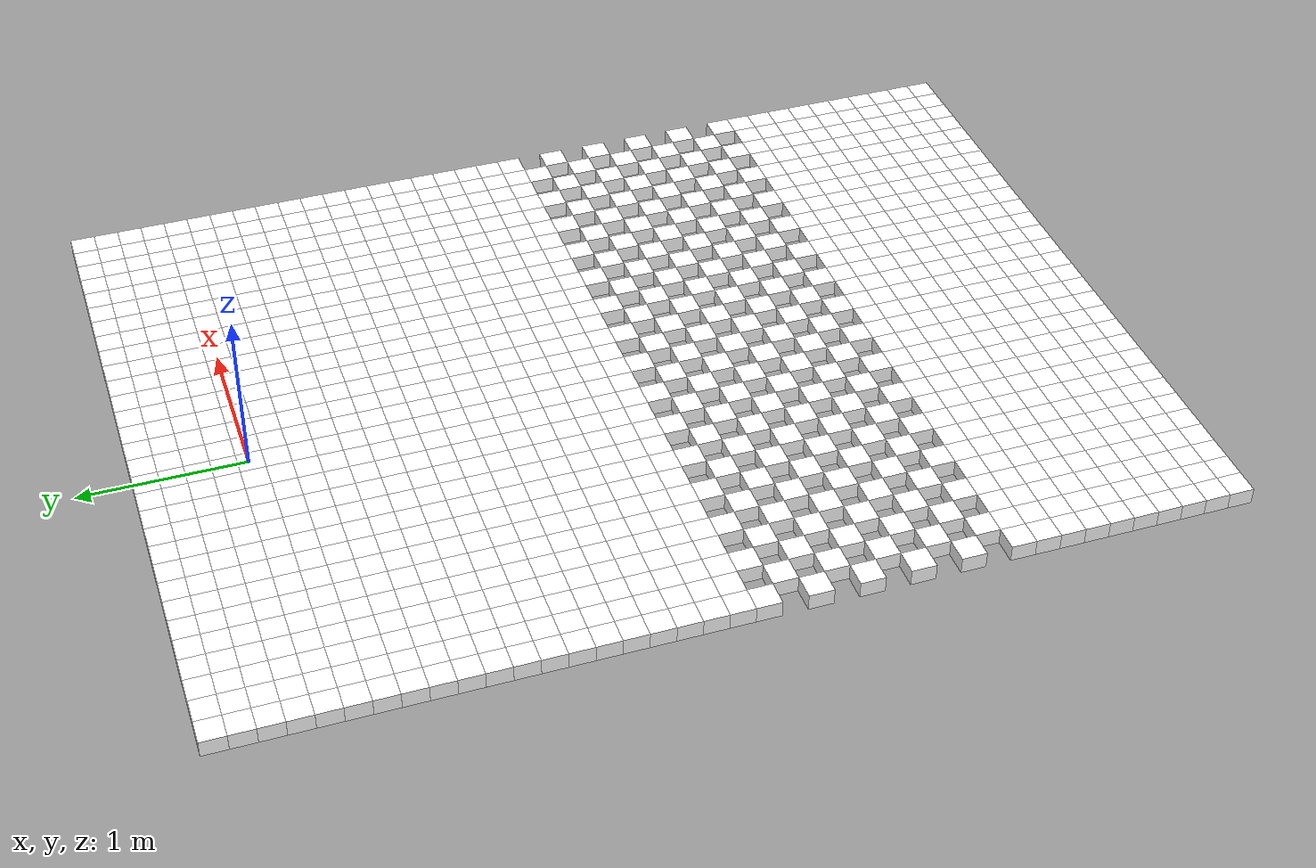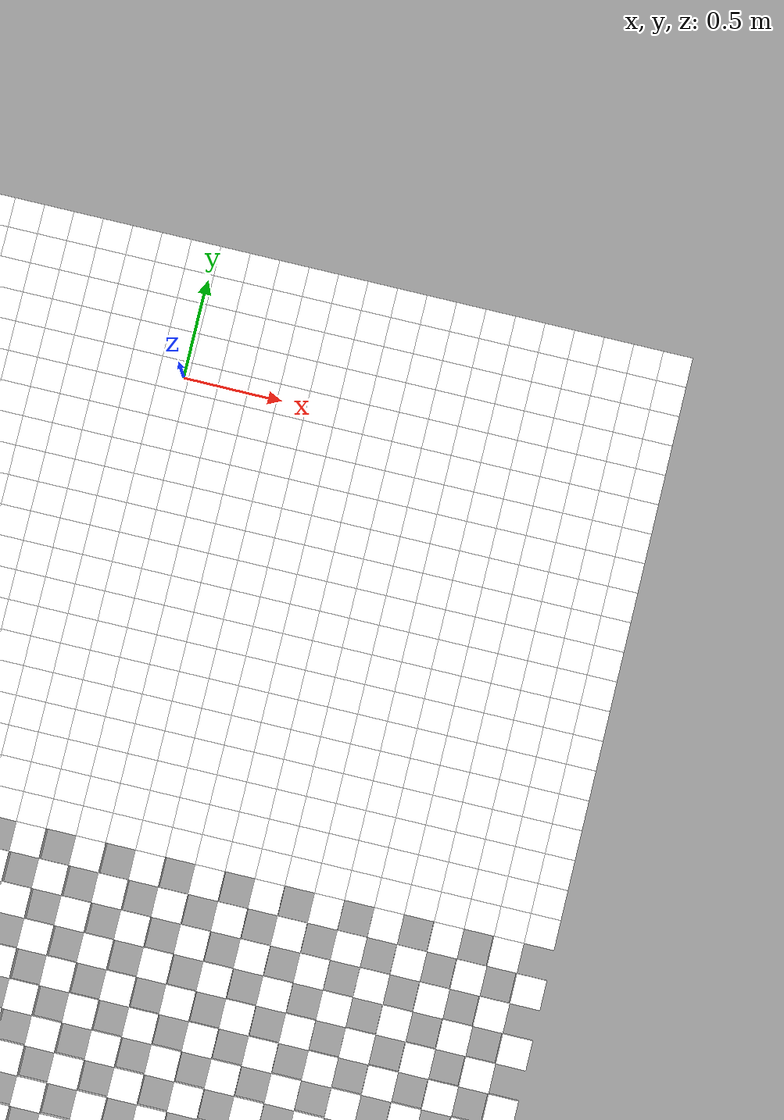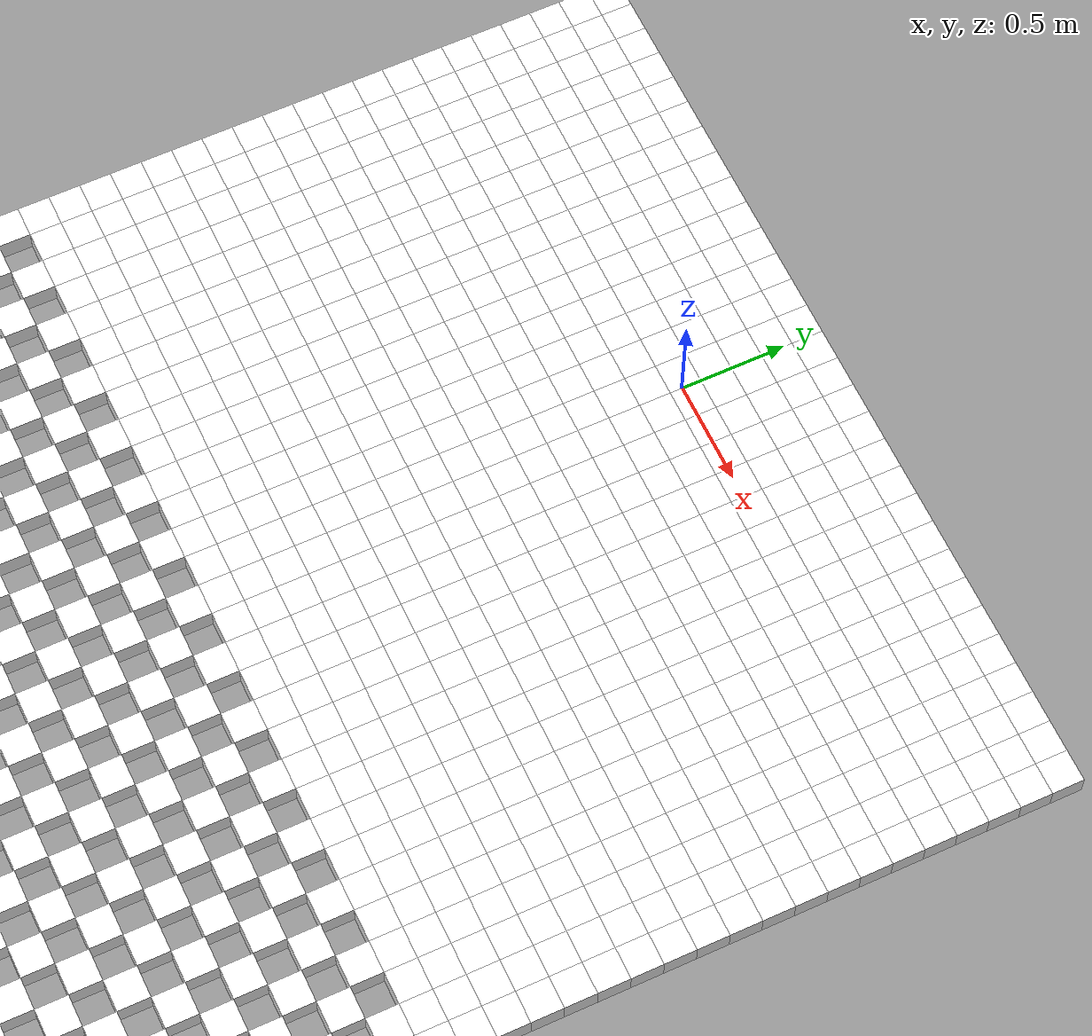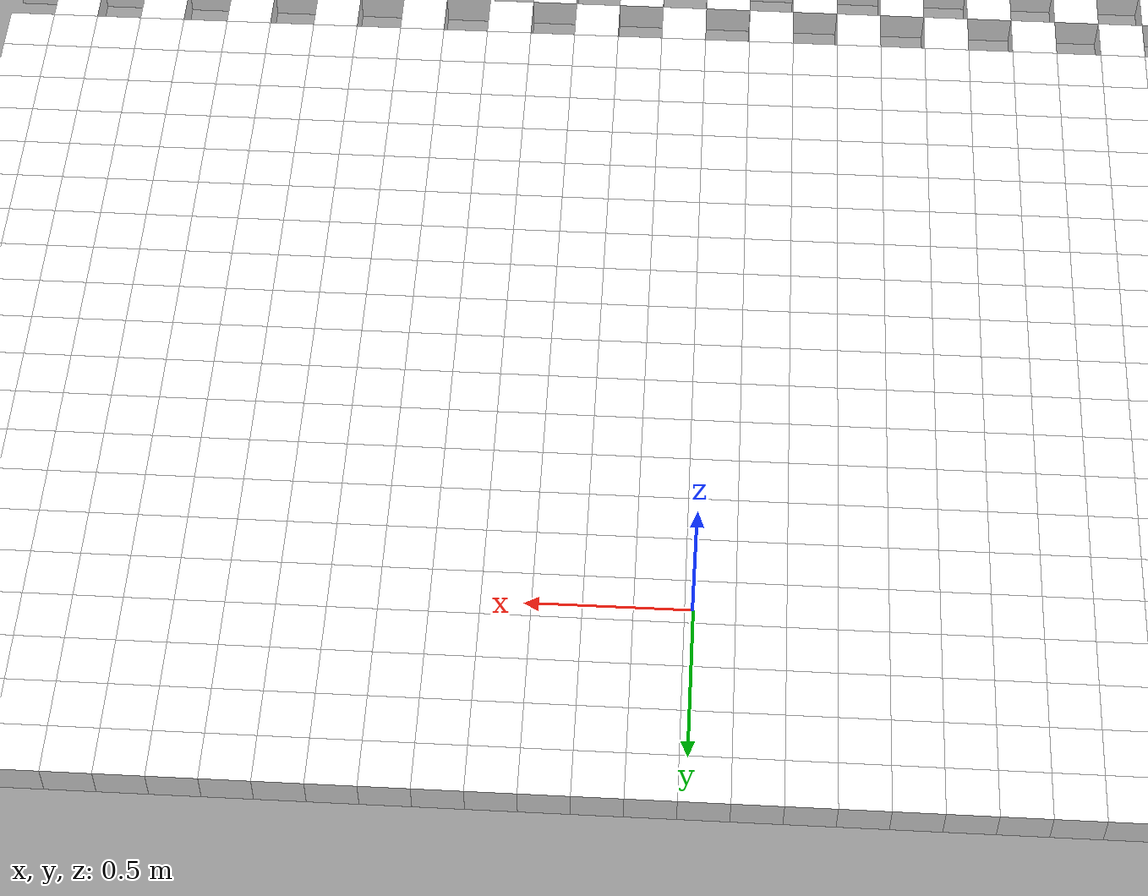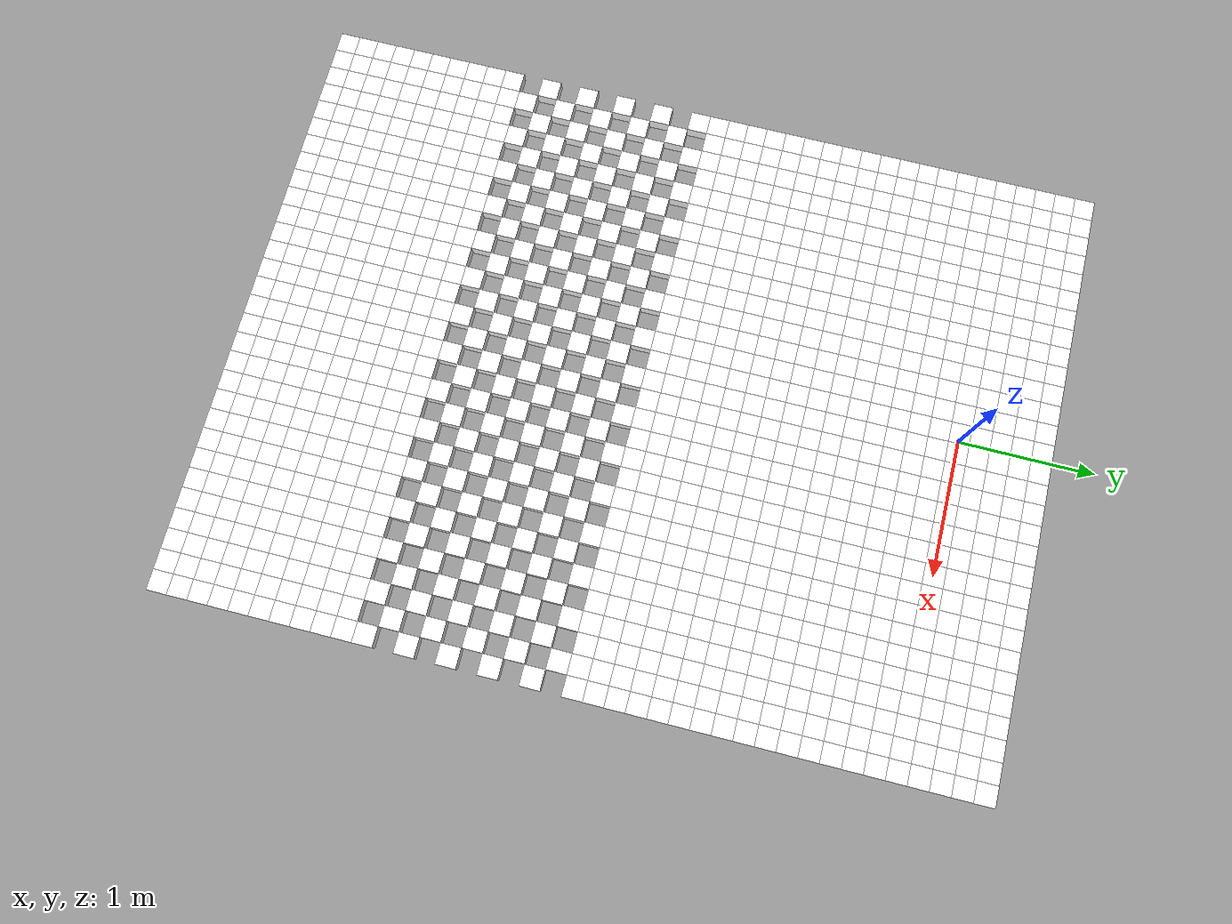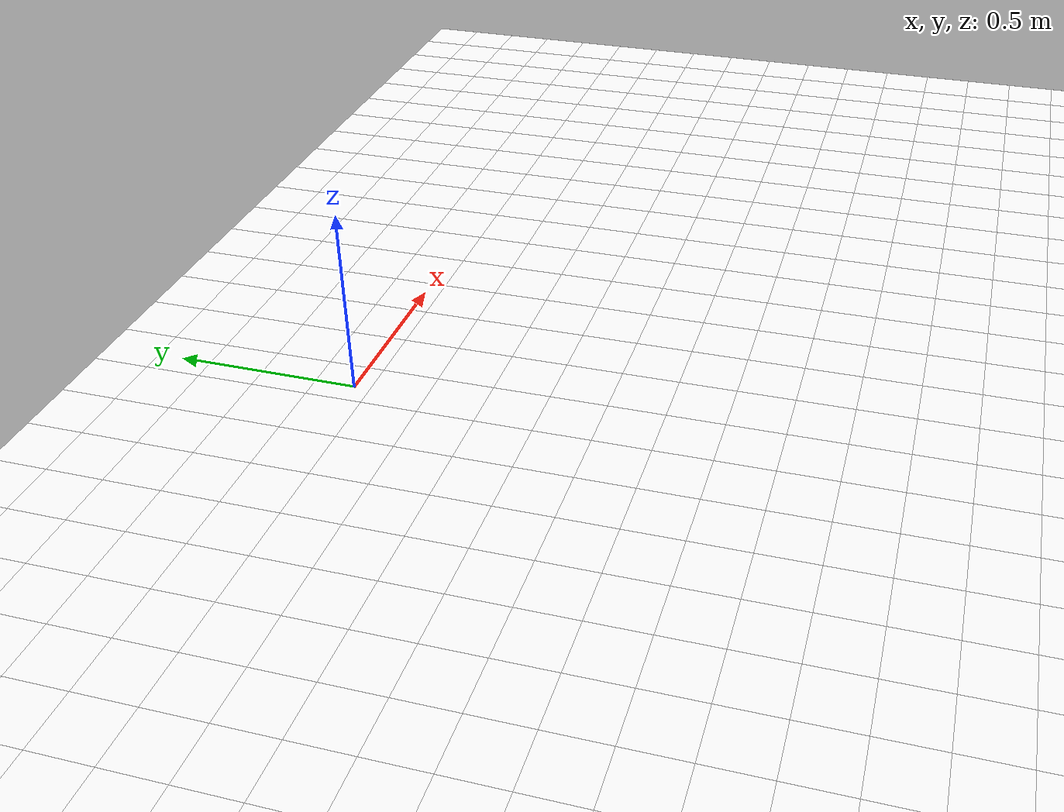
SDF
<sdf version="1.7">
  <world name="default">

    <!-- Need to be able to manipulate model state -->
    <plugin name="gazebo_ros_state" filename="libgazebo_ros_state.so">
      <ros>
        <namespace>/gazebo</namespace>
      </ros>

      <update_rate>1.0</update_rate>
    </plugin>

    <!-- Need to be able to manipulate model configuration -->
    <plugin name="gazebo_ros_properties" filename="libgazebo_ros_properties.so">
      <ros>
        <namespace>/gazebo</namespace>
      </ros>

      <update_rate>1.0</update_rate>
    </plugin>

    <physics type="ode">
    <max_step_size>0.001</max_step_size>
    <real_time_factor>1.0</real_time_factor>
    <real_time_update_rate>1000</real_time_update_rate>
    <gravity>0 0 -9.81</gravity>
        <ode>
            <solver>
            <type>quick</type>
            <iters>50</iters>
            <sor>1.3</sor>
            </solver>
            <constraints>
            <cfm>0.0</cfm>
            <erp>0.2</erp>
            <contact_max_correcting_vel>10.0</contact_max_correcting_vel>
            <contact_surface_layer>0.001</contact_surface_layer>
            </constraints>
        </ode>
    </physics>

    <scene>
    <sky>
        <clouds>
            <speed>12</speed>
        </clouds>
    </sky>
    </scene>
    <!-- A global light source -->
    <include>
        <uri>model://sun</uri>
    </include>
    <!-- A ground plane -->
    <model name="static_environment">
  <static>true</static>
  <link name="region_0">
    <pose>-2.0 0.6 0.0 0.0 0.0 4.7123</pose>
    <collision name="region_0_collision">
      <geometry>
        <box>
          <size>0.15 0.15 0.1</size>
        </box>
      </geometry>
      <surface>
        <friction>
          <ode>
            <mu>1.0</mu>
            <mu2>1.0</mu2>
          </ode>
        </friction>
      </surface>
    </collision>
    <visual name="region_0_visual">
      <geometry>
        <box>
          <size>0.15 0.15 0.1</size>
        </box>
      </geometry>
      <material>
        <ambient>1.0 1.0 1.0 1.0</ambient>
        <diffuse>1.0 1.0 1.0 1.0</diffuse>
      </material>
    </visual>
  </link>
  <link name="region_1">
    <pose>-2.0000133470576857 0.4500000005938132 0.0 0.0 0.0 4.7123</pose>
    <collision name="region_1_collision">
      <geometry>
        <box>
          <size>0.15 0.15 0.1</size>
        </box>
      </geometry>
      <surface>
        <friction>
          <ode>
            <mu>1.0</mu>
            <mu2>1.0</mu2>
          </ode>
        </friction>
      </surface>
    </collision>
    <visual name="region_1_visual">
      <geometry>
        <box>
          <size>0.15 0.15 0.1</size>
        </box>
      </geometry>
      <material>
        <ambient>1.0 1.0 1.0 1.0</ambient>
        <diffuse>1.0 1.0 1.0 1.0</diffuse>
      </material>
    </visual>
  </link>
  <link name="region_2">
    <pose>-2.000026694115372 0.3000000011876264 0.0 0.0 0.0 4.7123</pose>
    <collision name="region_2_collision">
      <geometry>
        <box>
          <size>0.15 0.15 0.1</size>
        </box>
      </geometry>
      <surface>
        <friction>
          <ode>
            <mu>1.0</mu>
            <mu2>1.0</mu2>
          </ode>
        </friction>
      </surface>
    </collision>
    <visual name="region_2_visual">
      <geometry>
        <box>
          <size>0.15 0.15 0.1</size>
        </box>
      </geometry>
      <material>
        <ambient>1.0 1.0 1.0 1.0</ambient>
        <diffuse>1.0 1.0 1.0 1.0</diffuse>
      </material>
    </visual>
  </link>
  <link name="region_3">
    <pose>-2.0000400411730577 0.15000000178143957 0.0 0.0 0.0 4.7123</pose>
    <collision name="region_3_collision">
      <geometry>
        <box>
          <size>0.15 0.15 0.1</size>
        </box>
      </geometry>
      <surface>
        <friction>
          <ode>
            <mu>1.0</mu>
            <mu2>1.0</mu2>
          </ode>
        </friction>
      </surface>
    </collision>
    <visual name="region_3_visual">
      <geometry>
        <box>
          <size>0.15 0.15 0.1</size>
        </box>
      </geometry>
      <material>
        <ambient>1.0 1.0 1.0 1.0</ambient>
        <diffuse>1.0 1.0 1.0 1.0</diffuse>
      </material>
    </visual>
  </link>
  <link name="region_4">
    <pose>-2.0000533882307434 2.3752527722464833e-09 0.0 0.0 0.0 4.7123</pose>
    <collision name="region_4_collision">
      <geometry>
        <box>
          <size>0.15 0.15 0.1</size>
        </box>
      </geometry>
      <surface>
        <friction>
          <ode>
            <mu>1.0</mu>
            <mu2>1.0</mu2>
          </ode>
        </friction>
      </surface>
    </collision>
    <visual name="region_4_visual">
      <geometry>
        <box>
          <size>0.15 0.15 0.1</size>
        </box>
      </geometry>
      <material>
        <ambient>1.0 1.0 1.0 1.0</ambient>
        <diffuse>1.0 1.0 1.0 1.0</diffuse>
      </material>
    </visual>
  </link>
  <link name="region_5">
    <pose>-2.0000667352884296 -0.14999999703093414 0.0 0.0 0.0 4.7123</pose>
    <collision name="region_5_collision">
      <geometry>
        <box>
          <size>0.15 0.15 0.1</size>
        </box>
      </geometry>
      <surface>
        <friction>
          <ode>
            <mu>1.0</mu>
            <mu2>1.0</mu2>
          </ode>
        </friction>
      </surface>
    </collision>
    <visual name="region_5_visual">
      <geometry>
        <box>
          <size>0.15 0.15 0.1</size>
        </box>
      </geometry>
      <material>
        <ambient>1.0 1.0 1.0 1.0</ambient>
        <diffuse>1.0 1.0 1.0 1.0</diffuse>
      </material>
    </visual>
  </link>
  <link name="region_6">
    <pose>-2.0000800823461153 -0.29999999643712094 0.0 0.0 0.0 4.7123</pose>
    <collision name="region_6_collision">
      <geometry>
        <box>
          <size>0.15 0.15 0.1</size>
        </box>
      </geometry>
      <surface>
        <friction>
          <ode>
            <mu>1.0</mu>
            <mu2>1.0</mu2>
          </ode>
        </friction>
      </surface>
    </collision>
    <visual name="region_6_visual">
      <geometry>
        <box>
          <size>0.15 0.15 0.1</size>
        </box>
      </geometry>
      <material>
        <ambient>1.0 1.0 1.0 1.0</ambient>
        <diffuse>1.0 1.0 1.0 1.0</diffuse>
      </material>
    </visual>
  </link>
  <link name="region_7">
    <pose>-2.000093429403801 -0.44999999584330774 0.0 0.0 0.0 4.7123</pose>
    <collision name="region_7_collision">
      <geometry>
        <box>
          <size>0.15 0.15 0.1</size>
        </box>
      </geometry>
      <surface>
        <friction>
          <ode>
            <mu>1.0</mu>
            <mu2>1.0</mu2>
          </ode>
        </friction>
      </surface>
    </collision>
    <visual name="region_7_visual">
      <geometry>
        <box>
          <size>0.15 0.15 0.1</size>
        </box>
      </geometry>
      <material>
        <ambient>1.0 1.0 1.0 1.0</ambient>
        <diffuse>1.0 1.0 1.0 1.0</diffuse>
      </material>
    </visual>
  </link>
  <link name="region_8">
    <pose>-2.000106776461487 -0.5999999952494944 0.0 0.0 0.0 4.7123</pose>
    <collision name="region_8_collision">
      <geometry>
        <box>
          <size>0.15 0.15 0.1</size>
        </box>
      </geometry>
      <surface>
        <friction>
          <ode>
            <mu>1.0</mu>
            <mu2>1.0</mu2>
          </ode>
        </friction>
      </surface>
    </collision>
    <visual name="region_8_visual">
      <geometry>
        <box>
          <size>0.15 0.15 0.1</size>
        </box>
      </geometry>
      <material>
        <ambient>1.0 1.0 1.0 1.0</ambient>
        <diffuse>1.0 1.0 1.0 1.0</diffuse>
      </material>
    </visual>
  </link>
  <link name="region_9">
    <pose>-2.000120123519173 -0.7499999946556813 0.0 0.0 0.0 4.7123</pose>
    <collision name="region_9_collision">
      <geometry>
        <box>
          <size>0.15 0.15 0.1</size>
        </box>
      </geometry>
      <surface>
        <friction>
          <ode>
            <mu>1.0</mu>
            <mu2>1.0</mu2>
          </ode>
        </friction>
      </surface>
    </collision>
    <visual name="region_9_visual">
      <geometry>
        <box>
          <size>0.15 0.15 0.1</size>
        </box>
      </geometry>
      <material>
        <ambient>1.0 1.0 1.0 1.0</ambient>
        <diffuse>1.0 1.0 1.0 1.0</diffuse>
      </material>
    </visual>
  </link>
  <link name="region_10">
    <pose>-2.0001334705768588 -0.899999994061868 0.0 0.0 0.0 4.7123</pose>
    <collision name="region_10_collision">
      <geometry>
        <box>
          <size>0.15 0.15 0.1</size>
        </box>
      </geometry>
      <surface>
        <friction>
          <ode>
            <mu>1.0</mu>
            <mu2>1.0</mu2>
          </ode>
        </friction>
      </surface>
    </collision>
    <visual name="region_10_visual">
      <geometry>
        <box>
          <size>0.15 0.15 0.1</size>
        </box>
      </geometry>
      <material>
        <ambient>1.0 1.0 1.0 1.0</ambient>
        <diffuse>1.0 1.0 1.0 1.0</diffuse>
      </material>
    </visual>
  </link>
  <link name="region_11">
    <pose>-2.0001468176345445 -1.0499999934680546 0.0 0.0 0.0 4.7123</pose>
    <collision name="region_11_collision">
      <geometry>
        <box>
          <size>0.15 0.15 0.1</size>
        </box>
      </geometry>
      <surface>
        <friction>
          <ode>
            <mu>1.0</mu>
            <mu2>1.0</mu2>
          </ode>
        </friction>
      </surface>
    </collision>
    <visual name="region_11_visual">
      <geometry>
        <box>
          <size>0.15 0.15 0.1</size>
        </box>
      </geometry>
      <material>
        <ambient>1.0 1.0 1.0 1.0</ambient>
        <diffuse>1.0 1.0 1.0 1.0</diffuse>
      </material>
    </visual>
  </link>
  <link name="region_12">
    <pose>-2.0001601646922307 -1.1999999928742415 0.0 0.0 0.0 4.7123</pose>
    <collision name="region_12_collision">
      <geometry>
        <box>
          <size>0.15 0.15 0.1</size>
        </box>
      </geometry>
      <surface>
        <friction>
          <ode>
            <mu>1.0</mu>
            <mu2>1.0</mu2>
          </ode>
        </friction>
      </surface>
    </collision>
    <visual name="region_12_visual">
      <geometry>
        <box>
          <size>0.15 0.15 0.1</size>
        </box>
      </geometry>
      <material>
        <ambient>1.0 1.0 1.0 1.0</ambient>
        <diffuse>1.0 1.0 1.0 1.0</diffuse>
      </material>
    </visual>
  </link>
  <link name="region_13">
    <pose>-2.0001735117499164 -1.349999992280428 0.0 0.0 0.0 4.7123</pose>
    <collision name="region_13_collision">
      <geometry>
        <box>
          <size>0.15 0.15 0.1</size>
        </box>
      </geometry>
      <surface>
        <friction>
          <ode>
            <mu>1.0</mu>
            <mu2>1.0</mu2>
          </ode>
        </friction>
      </surface>
    </collision>
    <visual name="region_13_visual">
      <geometry>
        <box>
          <size>0.15 0.15 0.1</size>
        </box>
      </geometry>
      <material>
        <ambient>1.0 1.0 1.0 1.0</ambient>
        <diffuse>1.0 1.0 1.0 1.0</diffuse>
      </material>
    </visual>
  </link>
  <link name="region_14">
    <pose>-2.000186858807602 -1.499999991686615 0.0 0.0 0.0 4.7123</pose>
    <collision name="region_14_collision">
      <geometry>
        <box>
          <size>0.15 0.15 0.1</size>
        </box>
      </geometry>
      <surface>
        <friction>
          <ode>
            <mu>1.0</mu>
            <mu2>1.0</mu2>
          </ode>
        </friction>
      </surface>
    </collision>
    <visual name="region_14_visual">
      <geometry>
        <box>
          <size>0.15 0.15 0.1</size>
        </box>
      </geometry>
      <material>
        <ambient>1.0 1.0 1.0 1.0</ambient>
        <diffuse>1.0 1.0 1.0 1.0</diffuse>
      </material>
    </visual>
  </link>
  <link name="region_15">
    <pose>-2.0002002058652883 -1.6499999910928018 0.0 0.0 0.0 4.7123</pose>
    <collision name="region_15_collision">
      <geometry>
        <box>
          <size>0.15 0.15 0.1</size>
        </box>
      </geometry>
      <surface>
        <friction>
          <ode>
            <mu>1.0</mu>
            <mu2>1.0</mu2>
          </ode>
        </friction>
      </surface>
    </collision>
    <visual name="region_15_visual">
      <geometry>
        <box>
          <size>0.15 0.15 0.1</size>
        </box>
      </geometry>
      <material>
        <ambient>1.0 1.0 1.0 1.0</ambient>
        <diffuse>1.0 1.0 1.0 1.0</diffuse>
      </material>
    </visual>
  </link>
  <link name="region_16">
    <pose>-2.000213552922974 -1.7999999904989883 0.0 0.0 0.0 4.7123</pose>
    <collision name="region_16_collision">
      <geometry>
        <box>
          <size>0.15 0.15 0.1</size>
        </box>
      </geometry>
      <surface>
        <friction>
          <ode>
            <mu>1.0</mu>
            <mu2>1.0</mu2>
          </ode>
        </friction>
      </surface>
    </collision>
    <visual name="region_16_visual">
      <geometry>
        <box>
          <size>0.15 0.15 0.1</size>
        </box>
      </geometry>
      <material>
        <ambient>1.0 1.0 1.0 1.0</ambient>
        <diffuse>1.0 1.0 1.0 1.0</diffuse>
      </material>
    </visual>
  </link>
  <link name="region_17">
    <pose>-2.00022689998066 -1.9499999899051752 0.0 0.0 0.0 4.7123</pose>
    <collision name="region_17_collision">
      <geometry>
        <box>
          <size>0.15 0.15 0.1</size>
        </box>
      </geometry>
      <surface>
        <friction>
          <ode>
            <mu>1.0</mu>
            <mu2>1.0</mu2>
          </ode>
        </friction>
      </surface>
    </collision>
    <visual name="region_17_visual">
      <geometry>
        <box>
          <size>0.15 0.15 0.1</size>
        </box>
      </geometry>
      <material>
        <ambient>1.0 1.0 1.0 1.0</ambient>
        <diffuse>1.0 1.0 1.0 1.0</diffuse>
      </material>
    </visual>
  </link>
  <link name="region_18">
    <pose>-2.0002402470383456 -2.099999989311362 0.0 0.0 0.0 4.7123</pose>
    <collision name="region_18_collision">
      <geometry>
        <box>
          <size>0.15 0.15 0.1</size>
        </box>
      </geometry>
      <surface>
        <friction>
          <ode>
            <mu>1.0</mu>
            <mu2>1.0</mu2>
          </ode>
        </friction>
      </surface>
    </collision>
    <visual name="region_18_visual">
      <geometry>
        <box>
          <size>0.15 0.15 0.1</size>
        </box>
      </geometry>
      <material>
        <ambient>1.0 1.0 1.0 1.0</ambient>
        <diffuse>1.0 1.0 1.0 1.0</diffuse>
      </material>
    </visual>
  </link>
  <link name="region_19">
    <pose>-2.0002535940960318 -2.2499999887175486 0.0 0.0 0.0 4.7123</pose>
    <collision name="region_19_collision">
      <geometry>
        <box>
          <size>0.15 0.15 0.1</size>
        </box>
      </geometry>
      <surface>
        <friction>
          <ode>
            <mu>1.0</mu>
            <mu2>1.0</mu2>
          </ode>
        </friction>
      </surface>
    </collision>
    <visual name="region_19_visual">
      <geometry>
        <box>
          <size>0.15 0.15 0.1</size>
        </box>
      </geometry>
      <material>
        <ambient>1.0 1.0 1.0 1.0</ambient>
        <diffuse>1.0 1.0 1.0 1.0</diffuse>
      </material>
    </visual>
  </link>
  <link name="region_20">
    <pose>-1.850000000593813 0.5999866529423141 0.0 0.0 0.0 4.7123</pose>
    <collision name="region_20_collision">
      <geometry>
        <box>
          <size>0.15 0.15 0.1</size>
        </box>
      </geometry>
      <surface>
        <friction>
          <ode>
            <mu>1.0</mu>
            <mu2>1.0</mu2>
          </ode>
        </friction>
      </surface>
    </collision>
    <visual name="region_20_visual">
      <geometry>
        <box>
          <size>0.15 0.15 0.1</size>
        </box>
      </geometry>
      <material>
        <ambient>1.0 1.0 1.0 1.0</ambient>
        <diffuse>1.0 1.0 1.0 1.0</diffuse>
      </material>
    </visual>
  </link>
  <link name="region_21">
    <pose>-1.850013347651499 0.4499866535361273 0.0 0.0 0.0 4.7123</pose>
    <collision name="region_21_collision">
      <geometry>
        <box>
          <size>0.15 0.15 0.1</size>
        </box>
      </geometry>
      <surface>
        <friction>
          <ode>
            <mu>1.0</mu>
            <mu2>1.0</mu2>
          </ode>
        </friction>
      </surface>
    </collision>
    <visual name="region_21_visual">
      <geometry>
        <box>
          <size>0.15 0.15 0.1</size>
        </box>
      </geometry>
      <material>
        <ambient>1.0 1.0 1.0 1.0</ambient>
        <diffuse>1.0 1.0 1.0 1.0</diffuse>
      </material>
    </visual>
  </link>
  <link name="region_22">
    <pose>-1.850026694709185 0.29998665412994047 0.0 0.0 0.0 4.7123</pose>
    <collision name="region_22_collision">
      <geometry>
        <box>
          <size>0.15 0.15 0.1</size>
        </box>
      </geometry>
      <surface>
        <friction>
          <ode>
            <mu>1.0</mu>
            <mu2>1.0</mu2>
          </ode>
        </friction>
      </surface>
    </collision>
    <visual name="region_22_visual">
      <geometry>
        <box>
          <size>0.15 0.15 0.1</size>
        </box>
      </geometry>
      <material>
        <ambient>1.0 1.0 1.0 1.0</ambient>
        <diffuse>1.0 1.0 1.0 1.0</diffuse>
      </material>
    </visual>
  </link>
  <link name="region_23">
    <pose>-1.8500400417668708 0.14998665472375367 0.0 0.0 0.0 4.7123</pose>
    <collision name="region_23_collision">
      <geometry>
        <box>
          <size>0.15 0.15 0.1</size>
        </box>
      </geometry>
      <surface>
        <friction>
          <ode>
            <mu>1.0</mu>
            <mu2>1.0</mu2>
          </ode>
        </friction>
      </surface>
    </collision>
    <visual name="region_23_visual">
      <geometry>
        <box>
          <size>0.15 0.15 0.1</size>
        </box>
      </geometry>
      <material>
        <ambient>1.0 1.0 1.0 1.0</ambient>
        <diffuse>1.0 1.0 1.0 1.0</diffuse>
      </material>
    </visual>
  </link>
  <link name="region_24">
    <pose>-1.8500533888245567 -1.3344682433191757e-05 0.0 0.0 0.0 4.7123</pose>
    <collision name="region_24_collision">
      <geometry>
        <box>
          <size>0.15 0.15 0.1</size>
        </box>
      </geometry>
      <surface>
        <friction>
          <ode>
            <mu>1.0</mu>
            <mu2>1.0</mu2>
          </ode>
        </friction>
      </surface>
    </collision>
    <visual name="region_24_visual">
      <geometry>
        <box>
          <size>0.15 0.15 0.1</size>
        </box>
      </geometry>
      <material>
        <ambient>1.0 1.0 1.0 1.0</ambient>
        <diffuse>1.0 1.0 1.0 1.0</diffuse>
      </material>
    </visual>
  </link>
  <link name="region_25">
    <pose>-1.8500667358822427 -0.15001334408862 0.0 0.0 0.0 4.7123</pose>
    <collision name="region_25_collision">
      <geometry>
        <box>
          <size>0.15 0.15 0.1</size>
        </box>
      </geometry>
      <surface>
        <friction>
          <ode>
            <mu>1.0</mu>
            <mu2>1.0</mu2>
          </ode>
        </friction>
      </surface>
    </collision>
    <visual name="region_25_visual">
      <geometry>
        <box>
          <size>0.15 0.15 0.1</size>
        </box>
      </geometry>
      <material>
        <ambient>1.0 1.0 1.0 1.0</ambient>
        <diffuse>1.0 1.0 1.0 1.0</diffuse>
      </material>
    </visual>
  </link>
  <link name="region_26">
    <pose>-1.8500800829399284 -0.3000133434948068 0.0 0.0 0.0 4.7123</pose>
    <collision name="region_26_collision">
      <geometry>
        <box>
          <size>0.15 0.15 0.1</size>
        </box>
      </geometry>
      <surface>
        <friction>
          <ode>
            <mu>1.0</mu>
            <mu2>1.0</mu2>
          </ode>
        </friction>
      </surface>
    </collision>
    <visual name="region_26_visual">
      <geometry>
        <box>
          <size>0.15 0.15 0.1</size>
        </box>
      </geometry>
      <material>
        <ambient>1.0 1.0 1.0 1.0</ambient>
        <diffuse>1.0 1.0 1.0 1.0</diffuse>
      </material>
    </visual>
  </link>
  <link name="region_27">
    <pose>-1.8500934299976144 -0.4500133429009937 0.0 0.0 0.0 4.7123</pose>
    <collision name="region_27_collision">
      <geometry>
        <box>
          <size>0.15 0.15 0.1</size>
        </box>
      </geometry>
      <surface>
        <friction>
          <ode>
            <mu>1.0</mu>
            <mu2>1.0</mu2>
          </ode>
        </friction>
      </surface>
    </collision>
    <visual name="region_27_visual">
      <geometry>
        <box>
          <size>0.15 0.15 0.1</size>
        </box>
      </geometry>
      <material>
        <ambient>1.0 1.0 1.0 1.0</ambient>
        <diffuse>1.0 1.0 1.0 1.0</diffuse>
      </material>
    </visual>
  </link>
  <link name="region_28">
    <pose>-1.8501067770553001 -0.6000133423071804 0.0 0.0 0.0 4.7123</pose>
    <collision name="region_28_collision">
      <geometry>
        <box>
          <size>0.15 0.15 0.1</size>
        </box>
      </geometry>
      <surface>
        <friction>
          <ode>
            <mu>1.0</mu>
            <mu2>1.0</mu2>
          </ode>
        </friction>
      </surface>
    </collision>
    <visual name="region_28_visual">
      <geometry>
        <box>
          <size>0.15 0.15 0.1</size>
        </box>
      </geometry>
      <material>
        <ambient>1.0 1.0 1.0 1.0</ambient>
        <diffuse>1.0 1.0 1.0 1.0</diffuse>
      </material>
    </visual>
  </link>
  <link name="region_29">
    <pose>-1.850120124112986 -0.7500133417133671 0.0 0.0 0.0 4.7123</pose>
    <collision name="region_29_collision">
      <geometry>
        <box>
          <size>0.15 0.15 0.1</size>
        </box>
      </geometry>
      <surface>
        <friction>
          <ode>
            <mu>1.0</mu>
            <mu2>1.0</mu2>
          </ode>
        </friction>
      </surface>
    </collision>
    <visual name="region_29_visual">
      <geometry>
        <box>
          <size>0.15 0.15 0.1</size>
        </box>
      </geometry>
      <material>
        <ambient>1.0 1.0 1.0 1.0</ambient>
        <diffuse>1.0 1.0 1.0 1.0</diffuse>
      </material>
    </visual>
  </link>
  <link name="region_30">
    <pose>-1.8501334711706718 -0.9000133411195538 0.0 0.0 0.0 4.7123</pose>
    <collision name="region_30_collision">
      <geometry>
        <box>
          <size>0.15 0.15 0.1</size>
        </box>
      </geometry>
      <surface>
        <friction>
          <ode>
            <mu>1.0</mu>
            <mu2>1.0</mu2>
          </ode>
        </friction>
      </surface>
    </collision>
    <visual name="region_30_visual">
      <geometry>
        <box>
          <size>0.15 0.15 0.1</size>
        </box>
      </geometry>
      <material>
        <ambient>1.0 1.0 1.0 1.0</ambient>
        <diffuse>1.0 1.0 1.0 1.0</diffuse>
      </material>
    </visual>
  </link>
  <link name="region_31">
    <pose>-1.8501468182283578 -1.0500133405257408 0.0 0.0 0.0 4.7123</pose>
    <collision name="region_31_collision">
      <geometry>
        <box>
          <size>0.15 0.15 0.1</size>
        </box>
      </geometry>
      <surface>
        <friction>
          <ode>
            <mu>1.0</mu>
            <mu2>1.0</mu2>
          </ode>
        </friction>
      </surface>
    </collision>
    <visual name="region_31_visual">
      <geometry>
        <box>
          <size>0.15 0.15 0.1</size>
        </box>
      </geometry>
      <material>
        <ambient>1.0 1.0 1.0 1.0</ambient>
        <diffuse>1.0 1.0 1.0 1.0</diffuse>
      </material>
    </visual>
  </link>
  <link name="region_32">
    <pose>-1.8501601652860438 -1.2000133399319273 0.0 0.0 0.0 4.7123</pose>
    <collision name="region_32_collision">
      <geometry>
        <box>
          <size>0.15 0.15 0.1</size>
        </box>
      </geometry>
      <surface>
        <friction>
          <ode>
            <mu>1.0</mu>
            <mu2>1.0</mu2>
          </ode>
        </friction>
      </surface>
    </collision>
    <visual name="region_32_visual">
      <geometry>
        <box>
          <size>0.15 0.15 0.1</size>
        </box>
      </geometry>
      <material>
        <ambient>1.0 1.0 1.0 1.0</ambient>
        <diffuse>1.0 1.0 1.0 1.0</diffuse>
      </material>
    </visual>
  </link>
  <link name="region_33">
    <pose>-1.8501735123437295 -1.3500133393381142 0.0 0.0 0.0 4.7123</pose>
    <collision name="region_33_collision">
      <geometry>
        <box>
          <size>0.15 0.15 0.1</size>
        </box>
      </geometry>
      <surface>
        <friction>
          <ode>
            <mu>1.0</mu>
            <mu2>1.0</mu2>
          </ode>
        </friction>
      </surface>
    </collision>
    <visual name="region_33_visual">
      <geometry>
        <box>
          <size>0.15 0.15 0.1</size>
        </box>
      </geometry>
      <material>
        <ambient>1.0 1.0 1.0 1.0</ambient>
        <diffuse>1.0 1.0 1.0 1.0</diffuse>
      </material>
    </visual>
  </link>
  <link name="region_34">
    <pose>-1.8501868594014155 -1.500013338744301 0.0 0.0 0.0 4.7123</pose>
    <collision name="region_34_collision">
      <geometry>
        <box>
          <size>0.15 0.15 0.1</size>
        </box>
      </geometry>
      <surface>
        <friction>
          <ode>
            <mu>1.0</mu>
            <mu2>1.0</mu2>
          </ode>
        </friction>
      </surface>
    </collision>
    <visual name="region_34_visual">
      <geometry>
        <box>
          <size>0.15 0.15 0.1</size>
        </box>
      </geometry>
      <material>
        <ambient>1.0 1.0 1.0 1.0</ambient>
        <diffuse>1.0 1.0 1.0 1.0</diffuse>
      </material>
    </visual>
  </link>
  <link name="region_35">
    <pose>-1.8502002064591014 -1.6500133381504876 0.0 0.0 0.0 4.7123</pose>
    <collision name="region_35_collision">
      <geometry>
        <box>
          <size>0.15 0.15 0.1</size>
        </box>
      </geometry>
      <surface>
        <friction>
          <ode>
            <mu>1.0</mu>
            <mu2>1.0</mu2>
          </ode>
        </friction>
      </surface>
    </collision>
    <visual name="region_35_visual">
      <geometry>
        <box>
          <size>0.15 0.15 0.1</size>
        </box>
      </geometry>
      <material>
        <ambient>1.0 1.0 1.0 1.0</ambient>
        <diffuse>1.0 1.0 1.0 1.0</diffuse>
      </material>
    </visual>
  </link>
  <link name="region_36">
    <pose>-1.8502135535167872 -1.8000133375566745 0.0 0.0 0.0 4.7123</pose>
    <collision name="region_36_collision">
      <geometry>
        <box>
          <size>0.15 0.15 0.1</size>
        </box>
      </geometry>
      <surface>
        <friction>
          <ode>
            <mu>1.0</mu>
            <mu2>1.0</mu2>
          </ode>
        </friction>
      </surface>
    </collision>
    <visual name="region_36_visual">
      <geometry>
        <box>
          <size>0.15 0.15 0.1</size>
        </box>
      </geometry>
      <material>
        <ambient>1.0 1.0 1.0 1.0</ambient>
        <diffuse>1.0 1.0 1.0 1.0</diffuse>
      </material>
    </visual>
  </link>
  <link name="region_37">
    <pose>-1.8502269005744731 -1.950013336962861 0.0 0.0 0.0 4.7123</pose>
    <collision name="region_37_collision">
      <geometry>
        <box>
          <size>0.15 0.15 0.1</size>
        </box>
      </geometry>
      <surface>
        <friction>
          <ode>
            <mu>1.0</mu>
            <mu2>1.0</mu2>
          </ode>
        </friction>
      </surface>
    </collision>
    <visual name="region_37_visual">
      <geometry>
        <box>
          <size>0.15 0.15 0.1</size>
        </box>
      </geometry>
      <material>
        <ambient>1.0 1.0 1.0 1.0</ambient>
        <diffuse>1.0 1.0 1.0 1.0</diffuse>
      </material>
    </visual>
  </link>
  <link name="region_38">
    <pose>-1.8502402476321589 -2.100013336369048 0.0 0.0 0.0 4.7123</pose>
    <collision name="region_38_collision">
      <geometry>
        <box>
          <size>0.15 0.15 0.1</size>
        </box>
      </geometry>
      <surface>
        <friction>
          <ode>
            <mu>1.0</mu>
            <mu2>1.0</mu2>
          </ode>
        </friction>
      </surface>
    </collision>
    <visual name="region_38_visual">
      <geometry>
        <box>
          <size>0.15 0.15 0.1</size>
        </box>
      </geometry>
      <material>
        <ambient>1.0 1.0 1.0 1.0</ambient>
        <diffuse>1.0 1.0 1.0 1.0</diffuse>
      </material>
    </visual>
  </link>
  <link name="region_39">
    <pose>-1.8502535946898448 -2.2500133357752343 0.0 0.0 0.0 4.7123</pose>
    <collision name="region_39_collision">
      <geometry>
        <box>
          <size>0.15 0.15 0.1</size>
        </box>
      </geometry>
      <surface>
        <friction>
          <ode>
            <mu>1.0</mu>
            <mu2>1.0</mu2>
          </ode>
        </friction>
      </surface>
    </collision>
    <visual name="region_39_visual">
      <geometry>
        <box>
          <size>0.15 0.15 0.1</size>
        </box>
      </geometry>
      <material>
        <ambient>1.0 1.0 1.0 1.0</ambient>
        <diffuse>1.0 1.0 1.0 1.0</diffuse>
      </material>
    </visual>
  </link>
  <link name="region_40">
    <pose>-1.7000000011876264 0.5999733058846283 0.0 0.0 0.0 4.7123</pose>
    <collision name="region_40_collision">
      <geometry>
        <box>
          <size>0.15 0.15 0.1</size>
        </box>
      </geometry>
      <surface>
        <friction>
          <ode>
            <mu>1.0</mu>
            <mu2>1.0</mu2>
          </ode>
        </friction>
      </surface>
    </collision>
    <visual name="region_40_visual">
      <geometry>
        <box>
          <size>0.15 0.15 0.1</size>
        </box>
      </geometry>
      <material>
        <ambient>1.0 1.0 1.0 1.0</ambient>
        <diffuse>1.0 1.0 1.0 1.0</diffuse>
      </material>
    </visual>
  </link>
  <link name="region_41">
    <pose>-1.7000133482453124 0.4499733064784414 0.0 0.0 0.0 4.7123</pose>
    <collision name="region_41_collision">
      <geometry>
        <box>
          <size>0.15 0.15 0.1</size>
        </box>
      </geometry>
      <surface>
        <friction>
          <ode>
            <mu>1.0</mu>
            <mu2>1.0</mu2>
          </ode>
        </friction>
      </surface>
    </collision>
    <visual name="region_41_visual">
      <geometry>
        <box>
          <size>0.15 0.15 0.1</size>
        </box>
      </geometry>
      <material>
        <ambient>1.0 1.0 1.0 1.0</ambient>
        <diffuse>1.0 1.0 1.0 1.0</diffuse>
      </material>
    </visual>
  </link>
  <link name="region_42">
    <pose>-1.700026695302998 0.2999733070722546 0.0 0.0 0.0 4.7123</pose>
    <collision name="region_42_collision">
      <geometry>
        <box>
          <size>0.15 0.15 0.1</size>
        </box>
      </geometry>
      <surface>
        <friction>
          <ode>
            <mu>1.0</mu>
            <mu2>1.0</mu2>
          </ode>
        </friction>
      </surface>
    </collision>
    <visual name="region_42_visual">
      <geometry>
        <box>
          <size>0.15 0.15 0.1</size>
        </box>
      </geometry>
      <material>
        <ambient>1.0 1.0 1.0 1.0</ambient>
        <diffuse>1.0 1.0 1.0 1.0</diffuse>
      </material>
    </visual>
  </link>
  <link name="region_43">
    <pose>-1.700040042360684 0.1499733076660678 0.0 0.0 0.0 4.7123</pose>
    <collision name="region_43_collision">
      <geometry>
        <box>
          <size>0.15 0.15 0.1</size>
        </box>
      </geometry>
      <surface>
        <friction>
          <ode>
            <mu>1.0</mu>
            <mu2>1.0</mu2>
          </ode>
        </friction>
      </surface>
    </collision>
    <visual name="region_43_visual">
      <geometry>
        <box>
          <size>0.15 0.15 0.1</size>
        </box>
      </geometry>
      <material>
        <ambient>1.0 1.0 1.0 1.0</ambient>
        <diffuse>1.0 1.0 1.0 1.0</diffuse>
      </material>
    </visual>
  </link>
  <link name="region_44">
    <pose>-1.70005338941837 -2.6691740119044738e-05 0.0 0.0 0.0 4.7123</pose>
    <collision name="region_44_collision">
      <geometry>
        <box>
          <size>0.15 0.15 0.1</size>
        </box>
      </geometry>
      <surface>
        <friction>
          <ode>
            <mu>1.0</mu>
            <mu2>1.0</mu2>
          </ode>
        </friction>
      </surface>
    </collision>
    <visual name="region_44_visual">
      <geometry>
        <box>
          <size>0.15 0.15 0.1</size>
        </box>
      </geometry>
      <material>
        <ambient>1.0 1.0 1.0 1.0</ambient>
        <diffuse>1.0 1.0 1.0 1.0</diffuse>
      </material>
    </visual>
  </link>
  <link name="region_45">
    <pose>-1.7000667364760558 -0.15002669114630585 0.0 0.0 0.0 4.7123</pose>
    <collision name="region_45_collision">
      <geometry>
        <box>
          <size>0.15 0.15 0.1</size>
        </box>
      </geometry>
      <surface>
        <friction>
          <ode>
            <mu>1.0</mu>
            <mu2>1.0</mu2>
          </ode>
        </friction>
      </surface>
    </collision>
    <visual name="region_45_visual">
      <geometry>
        <box>
          <size>0.15 0.15 0.1</size>
        </box>
      </geometry>
      <material>
        <ambient>1.0 1.0 1.0 1.0</ambient>
        <diffuse>1.0 1.0 1.0 1.0</diffuse>
      </material>
    </visual>
  </link>
  <link name="region_46">
    <pose>-1.7000800835337415 -0.30002669055249276 0.0 0.0 0.0 4.7123</pose>
    <collision name="region_46_collision">
      <geometry>
        <box>
          <size>0.15 0.15 0.1</size>
        </box>
      </geometry>
      <surface>
        <friction>
          <ode>
            <mu>1.0</mu>
            <mu2>1.0</mu2>
          </ode>
        </friction>
      </surface>
    </collision>
    <visual name="region_46_visual">
      <geometry>
        <box>
          <size>0.15 0.15 0.1</size>
        </box>
      </geometry>
      <material>
        <ambient>1.0 1.0 1.0 1.0</ambient>
        <diffuse>1.0 1.0 1.0 1.0</diffuse>
      </material>
    </visual>
  </link>
  <link name="region_47">
    <pose>-1.7000934305914275 -0.45002668995867945 0.0 0.0 0.0 4.7123</pose>
    <collision name="region_47_collision">
      <geometry>
        <box>
          <size>0.15 0.15 0.1</size>
        </box>
      </geometry>
      <surface>
        <friction>
          <ode>
            <mu>1.0</mu>
            <mu2>1.0</mu2>
          </ode>
        </friction>
      </surface>
    </collision>
    <visual name="region_47_visual">
      <geometry>
        <box>
          <size>0.15 0.15 0.1</size>
        </box>
      </geometry>
      <material>
        <ambient>1.0 1.0 1.0 1.0</ambient>
        <diffuse>1.0 1.0 1.0 1.0</diffuse>
      </material>
    </visual>
  </link>
  <link name="region_48">
    <pose>-1.7001067776491134 -0.6000266893648664 0.0 0.0 0.0 4.7123</pose>
    <collision name="region_48_collision">
      <geometry>
        <box>
          <size>0.15 0.15 0.1</size>
        </box>
      </geometry>
      <surface>
        <friction>
          <ode>
            <mu>1.0</mu>
            <mu2>1.0</mu2>
          </ode>
        </friction>
      </surface>
    </collision>
    <visual name="region_48_visual">
      <geometry>
        <box>
          <size>0.15 0.15 0.1</size>
        </box>
      </geometry>
      <material>
        <ambient>1.0 1.0 1.0 1.0</ambient>
        <diffuse>1.0 1.0 1.0 1.0</diffuse>
      </material>
    </visual>
  </link>
  <link name="region_49">
    <pose>-1.7001201247067992 -0.750026688771053 0.0 0.0 0.0 4.7123</pose>
    <collision name="region_49_collision">
      <geometry>
        <box>
          <size>0.15 0.15 0.1</size>
        </box>
      </geometry>
      <surface>
        <friction>
          <ode>
            <mu>1.0</mu>
            <mu2>1.0</mu2>
          </ode>
        </friction>
      </surface>
    </collision>
    <visual name="region_49_visual">
      <geometry>
        <box>
          <size>0.15 0.15 0.1</size>
        </box>
      </geometry>
      <material>
        <ambient>1.0 1.0 1.0 1.0</ambient>
        <diffuse>1.0 1.0 1.0 1.0</diffuse>
      </material>
    </visual>
  </link>
  <link name="region_50">
    <pose>-1.7001334717644851 -0.9000266881772397 0.0 0.0 0.0 4.7123</pose>
    <collision name="region_50_collision">
      <geometry>
        <box>
          <size>0.15 0.15 0.1</size>
        </box>
      </geometry>
      <surface>
        <friction>
          <ode>
            <mu>1.0</mu>
            <mu2>1.0</mu2>
          </ode>
        </friction>
      </surface>
    </collision>
    <visual name="region_50_visual">
      <geometry>
        <box>
          <size>0.15 0.15 0.1</size>
        </box>
      </geometry>
      <material>
        <ambient>1.0 1.0 1.0 1.0</ambient>
        <diffuse>1.0 1.0 1.0 1.0</diffuse>
      </material>
    </visual>
  </link>
  <link name="region_51">
    <pose>-1.7001468188221711 -1.0500266875834265 0.0 0.0 0.0 4.7123</pose>
    <collision name="region_51_collision">
      <geometry>
        <box>
          <size>0.15 0.15 0.1</size>
        </box>
      </geometry>
      <surface>
        <friction>
          <ode>
            <mu>1.0</mu>
            <mu2>1.0</mu2>
          </ode>
        </friction>
      </surface>
    </collision>
    <visual name="region_51_visual">
      <geometry>
        <box>
          <size>0.15 0.15 0.1</size>
        </box>
      </geometry>
      <material>
        <ambient>1.0 1.0 1.0 1.0</ambient>
        <diffuse>1.0 1.0 1.0 1.0</diffuse>
      </material>
    </visual>
  </link>
  <link name="region_52">
    <pose>-1.7001601658798569 -1.200026686989613 0.0 0.0 0.0 4.7123</pose>
    <collision name="region_52_collision">
      <geometry>
        <box>
          <size>0.15 0.15 0.1</size>
        </box>
      </geometry>
      <surface>
        <friction>
          <ode>
            <mu>1.0</mu>
            <mu2>1.0</mu2>
          </ode>
        </friction>
      </surface>
    </collision>
    <visual name="region_52_visual">
      <geometry>
        <box>
          <size>0.15 0.15 0.1</size>
        </box>
      </geometry>
      <material>
        <ambient>1.0 1.0 1.0 1.0</ambient>
        <diffuse>1.0 1.0 1.0 1.0</diffuse>
      </material>
    </visual>
  </link>
  <link name="region_53">
    <pose>-1.7001735129375428 -1.3500266863958 0.0 0.0 0.0 4.7123</pose>
    <collision name="region_53_collision">
      <geometry>
        <box>
          <size>0.15 0.15 0.1</size>
        </box>
      </geometry>
      <surface>
        <friction>
          <ode>
            <mu>1.0</mu>
            <mu2>1.0</mu2>
          </ode>
        </friction>
      </surface>
    </collision>
    <visual name="region_53_visual">
      <geometry>
        <box>
          <size>0.15 0.15 0.1</size>
        </box>
      </geometry>
      <material>
        <ambient>1.0 1.0 1.0 1.0</ambient>
        <diffuse>1.0 1.0 1.0 1.0</diffuse>
      </material>
    </visual>
  </link>
  <link name="region_54">
    <pose>-1.7001868599952288 -1.5000266858019868 0.0 0.0 0.0 4.7123</pose>
    <collision name="region_54_collision">
      <geometry>
        <box>
          <size>0.15 0.15 0.1</size>
        </box>
      </geometry>
      <surface>
        <friction>
          <ode>
            <mu>1.0</mu>
            <mu2>1.0</mu2>
          </ode>
        </friction>
      </surface>
    </collision>
    <visual name="region_54_visual">
      <geometry>
        <box>
          <size>0.15 0.15 0.1</size>
        </box>
      </geometry>
      <material>
        <ambient>1.0 1.0 1.0 1.0</ambient>
        <diffuse>1.0 1.0 1.0 1.0</diffuse>
      </material>
    </visual>
  </link>
  <link name="region_55">
    <pose>-1.7002002070529145 -1.6500266852081733 0.0 0.0 0.0 4.7123</pose>
    <collision name="region_55_collision">
      <geometry>
        <box>
          <size>0.15 0.15 0.1</size>
        </box>
      </geometry>
      <surface>
        <friction>
          <ode>
            <mu>1.0</mu>
            <mu2>1.0</mu2>
          </ode>
        </friction>
      </surface>
    </collision>
    <visual name="region_55_visual">
      <geometry>
        <box>
          <size>0.15 0.15 0.1</size>
        </box>
      </geometry>
      <material>
        <ambient>1.0 1.0 1.0 1.0</ambient>
        <diffuse>1.0 1.0 1.0 1.0</diffuse>
      </material>
    </visual>
  </link>
  <link name="region_56">
    <pose>-1.7002135541106005 -1.8000266846143602 0.0 0.0 0.0 4.7123</pose>
    <collision name="region_56_collision">
      <geometry>
        <box>
          <size>0.15 0.15 0.1</size>
        </box>
      </geometry>
      <surface>
        <friction>
          <ode>
            <mu>1.0</mu>
            <mu2>1.0</mu2>
          </ode>
        </friction>
      </surface>
    </collision>
    <visual name="region_56_visual">
      <geometry>
        <box>
          <size>0.15 0.15 0.1</size>
        </box>
      </geometry>
      <material>
        <ambient>1.0 1.0 1.0 1.0</ambient>
        <diffuse>1.0 1.0 1.0 1.0</diffuse>
      </material>
    </visual>
  </link>
  <link name="region_57">
    <pose>-1.7002269011682862 -1.9500266840205471 0.0 0.0 0.0 4.7123</pose>
    <collision name="region_57_collision">
      <geometry>
        <box>
          <size>0.15 0.15 0.1</size>
        </box>
      </geometry>
      <surface>
        <friction>
          <ode>
            <mu>1.0</mu>
            <mu2>1.0</mu2>
          </ode>
        </friction>
      </surface>
    </collision>
    <visual name="region_57_visual">
      <geometry>
        <box>
          <size>0.15 0.15 0.1</size>
        </box>
      </geometry>
      <material>
        <ambient>1.0 1.0 1.0 1.0</ambient>
        <diffuse>1.0 1.0 1.0 1.0</diffuse>
      </material>
    </visual>
  </link>
  <link name="region_58">
    <pose>-1.7002402482259722 -2.1000266834267336 0.0 0.0 0.0 4.7123</pose>
    <collision name="region_58_collision">
      <geometry>
        <box>
          <size>0.15 0.15 0.1</size>
        </box>
      </geometry>
      <surface>
        <friction>
          <ode>
            <mu>1.0</mu>
            <mu2>1.0</mu2>
          </ode>
        </friction>
      </surface>
    </collision>
    <visual name="region_58_visual">
      <geometry>
        <box>
          <size>0.15 0.15 0.1</size>
        </box>
      </geometry>
      <material>
        <ambient>1.0 1.0 1.0 1.0</ambient>
        <diffuse>1.0 1.0 1.0 1.0</diffuse>
      </material>
    </visual>
  </link>
  <link name="region_59">
    <pose>-1.700253595283658 -2.2500266828329205 0.0 0.0 0.0 4.7123</pose>
    <collision name="region_59_collision">
      <geometry>
        <box>
          <size>0.15 0.15 0.1</size>
        </box>
      </geometry>
      <surface>
        <friction>
          <ode>
            <mu>1.0</mu>
            <mu2>1.0</mu2>
          </ode>
        </friction>
      </surface>
    </collision>
    <visual name="region_59_visual">
      <geometry>
        <box>
          <size>0.15 0.15 0.1</size>
        </box>
      </geometry>
      <material>
        <ambient>1.0 1.0 1.0 1.0</ambient>
        <diffuse>1.0 1.0 1.0 1.0</diffuse>
      </material>
    </visual>
  </link>
  <link name="region_60">
    <pose>-1.5500000017814397 0.5999599588269423 0.0 0.0 0.0 4.7123</pose>
    <collision name="region_60_collision">
      <geometry>
        <box>
          <size>0.15 0.15 0.1</size>
        </box>
      </geometry>
      <surface>
        <friction>
          <ode>
            <mu>1.0</mu>
            <mu2>1.0</mu2>
          </ode>
        </friction>
      </surface>
    </collision>
    <visual name="region_60_visual">
      <geometry>
        <box>
          <size>0.15 0.15 0.1</size>
        </box>
      </geometry>
      <material>
        <ambient>1.0 1.0 1.0 1.0</ambient>
        <diffuse>1.0 1.0 1.0 1.0</diffuse>
      </material>
    </visual>
  </link>
  <link name="region_61">
    <pose>-1.5500133488391254 0.4499599594207555 0.0 0.0 0.0 4.7123</pose>
    <collision name="region_61_collision">
      <geometry>
        <box>
          <size>0.15 0.15 0.1</size>
        </box>
      </geometry>
      <surface>
        <friction>
          <ode>
            <mu>1.0</mu>
            <mu2>1.0</mu2>
          </ode>
        </friction>
      </surface>
    </collision>
    <visual name="region_61_visual">
      <geometry>
        <box>
          <size>0.15 0.15 0.1</size>
        </box>
      </geometry>
      <material>
        <ambient>1.0 1.0 1.0 1.0</ambient>
        <diffuse>1.0 1.0 1.0 1.0</diffuse>
      </material>
    </visual>
  </link>
  <link name="region_62">
    <pose>-1.5500266958968114 0.2999599600145687 0.0 0.0 0.0 4.7123</pose>
    <collision name="region_62_collision">
      <geometry>
        <box>
          <size>0.15 0.15 0.1</size>
        </box>
      </geometry>
      <surface>
        <friction>
          <ode>
            <mu>1.0</mu>
            <mu2>1.0</mu2>
          </ode>
        </friction>
      </surface>
    </collision>
    <visual name="region_62_visual">
      <geometry>
        <box>
          <size>0.15 0.15 0.1</size>
        </box>
      </geometry>
      <material>
        <ambient>1.0 1.0 1.0 1.0</ambient>
        <diffuse>1.0 1.0 1.0 1.0</diffuse>
      </material>
    </visual>
  </link>
  <link name="region_63">
    <pose>-1.5500400429544972 0.14995996060838196 0.0 0.0 0.0 4.7123</pose>
    <collision name="region_63_collision">
      <geometry>
        <box>
          <size>0.15 0.15 0.1</size>
        </box>
      </geometry>
      <surface>
        <friction>
          <ode>
            <mu>1.0</mu>
            <mu2>1.0</mu2>
          </ode>
        </friction>
      </surface>
    </collision>
    <visual name="region_63_visual">
      <geometry>
        <box>
          <size>0.15 0.15 0.1</size>
        </box>
      </geometry>
      <material>
        <ambient>1.0 1.0 1.0 1.0</ambient>
        <diffuse>1.0 1.0 1.0 1.0</diffuse>
      </material>
    </visual>
  </link>
  <link name="region_64">
    <pose>-1.5500533900121831 -4.003879780489772e-05 0.0 0.0 0.0 4.7123</pose>
    <collision name="region_64_collision">
      <geometry>
        <box>
          <size>0.15 0.15 0.1</size>
        </box>
      </geometry>
      <surface>
        <friction>
          <ode>
            <mu>1.0</mu>
            <mu2>1.0</mu2>
          </ode>
        </friction>
      </surface>
    </collision>
    <visual name="region_64_visual">
      <geometry>
        <box>
          <size>0.15 0.15 0.1</size>
        </box>
      </geometry>
      <material>
        <ambient>1.0 1.0 1.0 1.0</ambient>
        <diffuse>1.0 1.0 1.0 1.0</diffuse>
      </material>
    </visual>
  </link>
  <link name="region_65">
    <pose>-1.5500667370698689 -0.1500400382039917 0.0 0.0 0.0 4.7123</pose>
    <collision name="region_65_collision">
      <geometry>
        <box>
          <size>0.15 0.15 0.1</size>
        </box>
      </geometry>
      <surface>
        <friction>
          <ode>
            <mu>1.0</mu>
            <mu2>1.0</mu2>
          </ode>
        </friction>
      </surface>
    </collision>
    <visual name="region_65_visual">
      <geometry>
        <box>
          <size>0.15 0.15 0.1</size>
        </box>
      </geometry>
      <material>
        <ambient>1.0 1.0 1.0 1.0</ambient>
        <diffuse>1.0 1.0 1.0 1.0</diffuse>
      </material>
    </visual>
  </link>
  <link name="region_66">
    <pose>-1.5500800841275548 -0.3000400376101786 0.0 0.0 0.0 4.7123</pose>
    <collision name="region_66_collision">
      <geometry>
        <box>
          <size>0.15 0.15 0.1</size>
        </box>
      </geometry>
      <surface>
        <friction>
          <ode>
            <mu>1.0</mu>
            <mu2>1.0</mu2>
          </ode>
        </friction>
      </surface>
    </collision>
    <visual name="region_66_visual">
      <geometry>
        <box>
          <size>0.15 0.15 0.1</size>
        </box>
      </geometry>
      <material>
        <ambient>1.0 1.0 1.0 1.0</ambient>
        <diffuse>1.0 1.0 1.0 1.0</diffuse>
      </material>
    </visual>
  </link>
  <link name="region_67">
    <pose>-1.5500934311852408 -0.4500400370163654 0.0 0.0 0.0 4.7123</pose>
    <collision name="region_67_collision">
      <geometry>
        <box>
          <size>0.15 0.15 0.1</size>
        </box>
      </geometry>
      <surface>
        <friction>
          <ode>
            <mu>1.0</mu>
            <mu2>1.0</mu2>
          </ode>
        </friction>
      </surface>
    </collision>
    <visual name="region_67_visual">
      <geometry>
        <box>
          <size>0.15 0.15 0.1</size>
        </box>
      </geometry>
      <material>
        <ambient>1.0 1.0 1.0 1.0</ambient>
        <diffuse>1.0 1.0 1.0 1.0</diffuse>
      </material>
    </visual>
  </link>
  <link name="region_68">
    <pose>-1.5501067782429265 -0.6000400364225521 0.0 0.0 0.0 4.7123</pose>
    <collision name="region_68_collision">
      <geometry>
        <box>
          <size>0.15 0.15 0.1</size>
        </box>
      </geometry>
      <surface>
        <friction>
          <ode>
            <mu>1.0</mu>
            <mu2>1.0</mu2>
          </ode>
        </friction>
      </surface>
    </collision>
    <visual name="region_68_visual">
      <geometry>
        <box>
          <size>0.15 0.15 0.1</size>
        </box>
      </geometry>
      <material>
        <ambient>1.0 1.0 1.0 1.0</ambient>
        <diffuse>1.0 1.0 1.0 1.0</diffuse>
      </material>
    </visual>
  </link>
  <link name="region_69">
    <pose>-1.5501201253006125 -0.7500400358287388 0.0 0.0 0.0 4.7123</pose>
    <collision name="region_69_collision">
      <geometry>
        <box>
          <size>0.15 0.15 0.1</size>
        </box>
      </geometry>
      <surface>
        <friction>
          <ode>
            <mu>1.0</mu>
            <mu2>1.0</mu2>
          </ode>
        </friction>
      </surface>
    </collision>
    <visual name="region_69_visual">
      <geometry>
        <box>
          <size>0.15 0.15 0.1</size>
        </box>
      </geometry>
      <material>
        <ambient>1.0 1.0 1.0 1.0</ambient>
        <diffuse>1.0 1.0 1.0 1.0</diffuse>
      </material>
    </visual>
  </link>
  <link name="region_70">
    <pose>-1.5501334723582985 -0.9000400352349257 0.0 0.0 0.0 4.7123</pose>
    <collision name="region_70_collision">
      <geometry>
        <box>
          <size>0.15 0.15 0.1</size>
        </box>
      </geometry>
      <surface>
        <friction>
          <ode>
            <mu>1.0</mu>
            <mu2>1.0</mu2>
          </ode>
        </friction>
      </surface>
    </collision>
    <visual name="region_70_visual">
      <geometry>
        <box>
          <size>0.15 0.15 0.1</size>
        </box>
      </geometry>
      <material>
        <ambient>1.0 1.0 1.0 1.0</ambient>
        <diffuse>1.0 1.0 1.0 1.0</diffuse>
      </material>
    </visual>
  </link>
  <link name="region_71">
    <pose>-1.5501468194159842 -1.0500400346411123 0.0 0.0 0.0 4.7123</pose>
    <collision name="region_71_collision">
      <geometry>
        <box>
          <size>0.15 0.15 0.1</size>
        </box>
      </geometry>
      <surface>
        <friction>
          <ode>
            <mu>1.0</mu>
            <mu2>1.0</mu2>
          </ode>
        </friction>
      </surface>
    </collision>
    <visual name="region_71_visual">
      <geometry>
        <box>
          <size>0.15 0.15 0.1</size>
        </box>
      </geometry>
      <material>
        <ambient>1.0 1.0 1.0 1.0</ambient>
        <diffuse>1.0 1.0 1.0 1.0</diffuse>
      </material>
    </visual>
  </link>
  <link name="region_72">
    <pose>-1.5501601664736702 -1.2000400340472992 0.0 0.0 0.0 4.7123</pose>
    <collision name="region_72_collision">
      <geometry>
        <box>
          <size>0.15 0.15 0.1</size>
        </box>
      </geometry>
      <surface>
        <friction>
          <ode>
            <mu>1.0</mu>
            <mu2>1.0</mu2>
          </ode>
        </friction>
      </surface>
    </collision>
    <visual name="region_72_visual">
      <geometry>
        <box>
          <size>0.15 0.15 0.1</size>
        </box>
      </geometry>
      <material>
        <ambient>1.0 1.0 1.0 1.0</ambient>
        <diffuse>1.0 1.0 1.0 1.0</diffuse>
      </material>
    </visual>
  </link>
  <link name="region_73">
    <pose>-1.550173513531356 -1.3500400334534857 0.0 0.0 0.0 4.7123</pose>
    <collision name="region_73_collision">
      <geometry>
        <box>
          <size>0.15 0.15 0.1</size>
        </box>
      </geometry>
      <surface>
        <friction>
          <ode>
            <mu>1.0</mu>
            <mu2>1.0</mu2>
          </ode>
        </friction>
      </surface>
    </collision>
    <visual name="region_73_visual">
      <geometry>
        <box>
          <size>0.15 0.15 0.1</size>
        </box>
      </geometry>
      <material>
        <ambient>1.0 1.0 1.0 1.0</ambient>
        <diffuse>1.0 1.0 1.0 1.0</diffuse>
      </material>
    </visual>
  </link>
  <link name="region_74">
    <pose>-1.5501868605890419 -1.5000400328596726 0.0 0.0 0.0 4.7123</pose>
    <collision name="region_74_collision">
      <geometry>
        <box>
          <size>0.15 0.15 0.1</size>
        </box>
      </geometry>
      <surface>
        <friction>
          <ode>
            <mu>1.0</mu>
            <mu2>1.0</mu2>
          </ode>
        </friction>
      </surface>
    </collision>
    <visual name="region_74_visual">
      <geometry>
        <box>
          <size>0.15 0.15 0.1</size>
        </box>
      </geometry>
      <material>
        <ambient>1.0 1.0 1.0 1.0</ambient>
        <diffuse>1.0 1.0 1.0 1.0</diffuse>
      </material>
    </visual>
  </link>
  <link name="region_75">
    <pose>-1.5502002076467276 -1.6500400322658595 0.0 0.0 0.0 4.7123</pose>
    <collision name="region_75_collision">
      <geometry>
        <box>
          <size>0.15 0.15 0.1</size>
        </box>
      </geometry>
      <surface>
        <friction>
          <ode>
            <mu>1.0</mu>
            <mu2>1.0</mu2>
          </ode>
        </friction>
      </surface>
    </collision>
    <visual name="region_75_visual">
      <geometry>
        <box>
          <size>0.15 0.15 0.1</size>
        </box>
      </geometry>
      <material>
        <ambient>1.0 1.0 1.0 1.0</ambient>
        <diffuse>1.0 1.0 1.0 1.0</diffuse>
      </material>
    </visual>
  </link>
  <link name="region_76">
    <pose>-1.5502135547044136 -1.800040031672046 0.0 0.0 0.0 4.7123</pose>
    <collision name="region_76_collision">
      <geometry>
        <box>
          <size>0.15 0.15 0.1</size>
        </box>
      </geometry>
      <surface>
        <friction>
          <ode>
            <mu>1.0</mu>
            <mu2>1.0</mu2>
          </ode>
        </friction>
      </surface>
    </collision>
    <visual name="region_76_visual">
      <geometry>
        <box>
          <size>0.15 0.15 0.1</size>
        </box>
      </geometry>
      <material>
        <ambient>1.0 1.0 1.0 1.0</ambient>
        <diffuse>1.0 1.0 1.0 1.0</diffuse>
      </material>
    </visual>
  </link>
  <link name="region_77">
    <pose>-1.5502269017620995 -1.9500400310782329 0.0 0.0 0.0 4.7123</pose>
    <collision name="region_77_collision">
      <geometry>
        <box>
          <size>0.15 0.15 0.1</size>
        </box>
      </geometry>
      <surface>
        <friction>
          <ode>
            <mu>1.0</mu>
            <mu2>1.0</mu2>
          </ode>
        </friction>
      </surface>
    </collision>
    <visual name="region_77_visual">
      <geometry>
        <box>
          <size>0.15 0.15 0.1</size>
        </box>
      </geometry>
      <material>
        <ambient>1.0 1.0 1.0 1.0</ambient>
        <diffuse>1.0 1.0 1.0 1.0</diffuse>
      </material>
    </visual>
  </link>
  <link name="region_78">
    <pose>-1.5502402488197853 -2.1000400304844193 0.0 0.0 0.0 4.7123</pose>
    <collision name="region_78_collision">
      <geometry>
        <box>
          <size>0.15 0.15 0.1</size>
        </box>
      </geometry>
      <surface>
        <friction>
          <ode>
            <mu>1.0</mu>
            <mu2>1.0</mu2>
          </ode>
        </friction>
      </surface>
    </collision>
    <visual name="region_78_visual">
      <geometry>
        <box>
          <size>0.15 0.15 0.1</size>
        </box>
      </geometry>
      <material>
        <ambient>1.0 1.0 1.0 1.0</ambient>
        <diffuse>1.0 1.0 1.0 1.0</diffuse>
      </material>
    </visual>
  </link>
  <link name="region_79">
    <pose>-1.5502535958774712 -2.2500400298906063 0.0 0.0 0.0 4.7123</pose>
    <collision name="region_79_collision">
      <geometry>
        <box>
          <size>0.15 0.15 0.1</size>
        </box>
      </geometry>
      <surface>
        <friction>
          <ode>
            <mu>1.0</mu>
            <mu2>1.0</mu2>
          </ode>
        </friction>
      </surface>
    </collision>
    <visual name="region_79_visual">
      <geometry>
        <box>
          <size>0.15 0.15 0.1</size>
        </box>
      </geometry>
      <material>
        <ambient>1.0 1.0 1.0 1.0</ambient>
        <diffuse>1.0 1.0 1.0 1.0</diffuse>
      </material>
    </visual>
  </link>
  <link name="region_80">
    <pose>-1.4000000023752528 0.5999466117692565 0.0 0.0 0.0 4.7123</pose>
    <collision name="region_80_collision">
      <geometry>
        <box>
          <size>0.15 0.15 0.1</size>
        </box>
      </geometry>
      <surface>
        <friction>
          <ode>
            <mu>1.0</mu>
            <mu2>1.0</mu2>
          </ode>
        </friction>
      </surface>
    </collision>
    <visual name="region_80_visual">
      <geometry>
        <box>
          <size>0.15 0.15 0.1</size>
        </box>
      </geometry>
      <material>
        <ambient>1.0 1.0 1.0 1.0</ambient>
        <diffuse>1.0 1.0 1.0 1.0</diffuse>
      </material>
    </visual>
  </link>
  <link name="region_81">
    <pose>-1.4000133494329385 0.44994661236306965 0.0 0.0 0.0 4.7123</pose>
    <collision name="region_81_collision">
      <geometry>
        <box>
          <size>0.15 0.15 0.1</size>
        </box>
      </geometry>
      <surface>
        <friction>
          <ode>
            <mu>1.0</mu>
            <mu2>1.0</mu2>
          </ode>
        </friction>
      </surface>
    </collision>
    <visual name="region_81_visual">
      <geometry>
        <box>
          <size>0.15 0.15 0.1</size>
        </box>
      </geometry>
      <material>
        <ambient>1.0 1.0 1.0 1.0</ambient>
        <diffuse>1.0 1.0 1.0 1.0</diffuse>
      </material>
    </visual>
  </link>
  <link name="region_82">
    <pose>-1.4000266964906245 0.29994661295688285 0.0 0.0 0.0 4.7123</pose>
    <collision name="region_82_collision">
      <geometry>
        <box>
          <size>0.15 0.15 0.1</size>
        </box>
      </geometry>
      <surface>
        <friction>
          <ode>
            <mu>1.0</mu>
            <mu2>1.0</mu2>
          </ode>
        </friction>
      </surface>
    </collision>
    <visual name="region_82_visual">
      <geometry>
        <box>
          <size>0.15 0.15 0.1</size>
        </box>
      </geometry>
      <material>
        <ambient>1.0 1.0 1.0 1.0</ambient>
        <diffuse>1.0 1.0 1.0 1.0</diffuse>
      </material>
    </visual>
  </link>
  <link name="region_83">
    <pose>-1.4000400435483105 0.14994661355069605 0.0 0.0 0.0 4.7123</pose>
    <collision name="region_83_collision">
      <geometry>
        <box>
          <size>0.15 0.15 0.1</size>
        </box>
      </geometry>
      <surface>
        <friction>
          <ode>
            <mu>1.0</mu>
            <mu2>1.0</mu2>
          </ode>
        </friction>
      </surface>
    </collision>
    <visual name="region_83_visual">
      <geometry>
        <box>
          <size>0.15 0.15 0.1</size>
        </box>
      </geometry>
      <material>
        <ambient>1.0 1.0 1.0 1.0</ambient>
        <diffuse>1.0 1.0 1.0 1.0</diffuse>
      </material>
    </visual>
  </link>
  <link name="region_84">
    <pose>-1.4000533906059962 -5.33858554907507e-05 0.0 0.0 0.0 4.7123</pose>
    <collision name="region_84_collision">
      <geometry>
        <box>
          <size>0.15 0.15 0.1</size>
        </box>
      </geometry>
      <surface>
        <friction>
          <ode>
            <mu>1.0</mu>
            <mu2>1.0</mu2>
          </ode>
        </friction>
      </surface>
    </collision>
    <visual name="region_84_visual">
      <geometry>
        <box>
          <size>0.15 0.15 0.1</size>
        </box>
      </geometry>
      <material>
        <ambient>1.0 1.0 1.0 1.0</ambient>
        <diffuse>1.0 1.0 1.0 1.0</diffuse>
      </material>
    </visual>
  </link>
  <link name="region_85">
    <pose>-1.4000667376636822 -0.15005338526167766 0.0 0.0 0.0 4.7123</pose>
    <collision name="region_85_collision">
      <geometry>
        <box>
          <size>0.15 0.15 0.1</size>
        </box>
      </geometry>
      <surface>
        <friction>
          <ode>
            <mu>1.0</mu>
            <mu2>1.0</mu2>
          </ode>
        </friction>
      </surface>
    </collision>
    <visual name="region_85_visual">
      <geometry>
        <box>
          <size>0.15 0.15 0.1</size>
        </box>
      </geometry>
      <material>
        <ambient>1.0 1.0 1.0 1.0</ambient>
        <diffuse>1.0 1.0 1.0 1.0</diffuse>
      </material>
    </visual>
  </link>
  <link name="region_86">
    <pose>-1.4000800847213681 -0.30005338466786446 0.0 0.0 0.0 4.7123</pose>
    <collision name="region_86_collision">
      <geometry>
        <box>
          <size>0.15 0.15 0.1</size>
        </box>
      </geometry>
      <surface>
        <friction>
          <ode>
            <mu>1.0</mu>
            <mu2>1.0</mu2>
          </ode>
        </friction>
      </surface>
    </collision>
    <visual name="region_86_visual">
      <geometry>
        <box>
          <size>0.15 0.15 0.1</size>
        </box>
      </geometry>
      <material>
        <ambient>1.0 1.0 1.0 1.0</ambient>
        <diffuse>1.0 1.0 1.0 1.0</diffuse>
      </material>
    </visual>
  </link>
  <link name="region_87">
    <pose>-1.4000934317790539 -0.4500533840740514 0.0 0.0 0.0 4.7123</pose>
    <collision name="region_87_collision">
      <geometry>
        <box>
          <size>0.15 0.15 0.1</size>
        </box>
      </geometry>
      <surface>
        <friction>
          <ode>
            <mu>1.0</mu>
            <mu2>1.0</mu2>
          </ode>
        </friction>
      </surface>
    </collision>
    <visual name="region_87_visual">
      <geometry>
        <box>
          <size>0.15 0.15 0.1</size>
        </box>
      </geometry>
      <material>
        <ambient>1.0 1.0 1.0 1.0</ambient>
        <diffuse>1.0 1.0 1.0 1.0</diffuse>
      </material>
    </visual>
  </link>
  <link name="region_88">
    <pose>-1.4001067788367398 -0.6000533834802381 0.0 0.0 0.0 4.7123</pose>
    <collision name="region_88_collision">
      <geometry>
        <box>
          <size>0.15 0.15 0.1</size>
        </box>
      </geometry>
      <surface>
        <friction>
          <ode>
            <mu>1.0</mu>
            <mu2>1.0</mu2>
          </ode>
        </friction>
      </surface>
    </collision>
    <visual name="region_88_visual">
      <geometry>
        <box>
          <size>0.15 0.15 0.1</size>
        </box>
      </geometry>
      <material>
        <ambient>1.0 1.0 1.0 1.0</ambient>
        <diffuse>1.0 1.0 1.0 1.0</diffuse>
      </material>
    </visual>
  </link>
  <link name="region_89">
    <pose>-1.4001201258944258 -0.7500533828864248 0.0 0.0 0.0 4.7123</pose>
    <collision name="region_89_collision">
      <geometry>
        <box>
          <size>0.15 0.15 0.1</size>
        </box>
      </geometry>
      <surface>
        <friction>
          <ode>
            <mu>1.0</mu>
            <mu2>1.0</mu2>
          </ode>
        </friction>
      </surface>
    </collision>
    <visual name="region_89_visual">
      <geometry>
        <box>
          <size>0.15 0.15 0.1</size>
        </box>
      </geometry>
      <material>
        <ambient>1.0 1.0 1.0 1.0</ambient>
        <diffuse>1.0 1.0 1.0 1.0</diffuse>
      </material>
    </visual>
  </link>
  <link name="region_90">
    <pose>-1.4001334729521115 -0.9000533822926114 0.0 0.0 0.0 4.7123</pose>
    <collision name="region_90_collision">
      <geometry>
        <box>
          <size>0.15 0.15 0.1</size>
        </box>
      </geometry>
      <surface>
        <friction>
          <ode>
            <mu>1.0</mu>
            <mu2>1.0</mu2>
          </ode>
        </friction>
      </surface>
    </collision>
    <visual name="region_90_visual">
      <geometry>
        <box>
          <size>0.15 0.15 0.1</size>
        </box>
      </geometry>
      <material>
        <ambient>1.0 1.0 1.0 1.0</ambient>
        <diffuse>1.0 1.0 1.0 1.0</diffuse>
      </material>
    </visual>
  </link>
  <link name="region_91">
    <pose>-1.4001468200097973 -1.050053381698798 0.0 0.0 0.0 4.7123</pose>
    <collision name="region_91_collision">
      <geometry>
        <box>
          <size>0.15 0.15 0.1</size>
        </box>
      </geometry>
      <surface>
        <friction>
          <ode>
            <mu>1.0</mu>
            <mu2>1.0</mu2>
          </ode>
        </friction>
      </surface>
    </collision>
    <visual name="region_91_visual">
      <geometry>
        <box>
          <size>0.15 0.15 0.1</size>
        </box>
      </geometry>
      <material>
        <ambient>1.0 1.0 1.0 1.0</ambient>
        <diffuse>1.0 1.0 1.0 1.0</diffuse>
      </material>
    </visual>
  </link>
  <link name="region_92">
    <pose>-1.4001601670674833 -1.200053381104985 0.0 0.0 0.0 4.7123</pose>
    <collision name="region_92_collision">
      <geometry>
        <box>
          <size>0.15 0.15 0.1</size>
        </box>
      </geometry>
      <surface>
        <friction>
          <ode>
            <mu>1.0</mu>
            <mu2>1.0</mu2>
          </ode>
        </friction>
      </surface>
    </collision>
    <visual name="region_92_visual">
      <geometry>
        <box>
          <size>0.15 0.15 0.1</size>
        </box>
      </geometry>
      <material>
        <ambient>1.0 1.0 1.0 1.0</ambient>
        <diffuse>1.0 1.0 1.0 1.0</diffuse>
      </material>
    </visual>
  </link>
  <link name="region_93">
    <pose>-1.4001735141251692 -1.3500533805111719 0.0 0.0 0.0 4.7123</pose>
    <collision name="region_93_collision">
      <geometry>
        <box>
          <size>0.15 0.15 0.1</size>
        </box>
      </geometry>
      <surface>
        <friction>
          <ode>
            <mu>1.0</mu>
            <mu2>1.0</mu2>
          </ode>
        </friction>
      </surface>
    </collision>
    <visual name="region_93_visual">
      <geometry>
        <box>
          <size>0.15 0.15 0.1</size>
        </box>
      </geometry>
      <material>
        <ambient>1.0 1.0 1.0 1.0</ambient>
        <diffuse>1.0 1.0 1.0 1.0</diffuse>
      </material>
    </visual>
  </link>
  <link name="region_94">
    <pose>-1.400186861182855 -1.5000533799173583 0.0 0.0 0.0 4.7123</pose>
    <collision name="region_94_collision">
      <geometry>
        <box>
          <size>0.15 0.15 0.1</size>
        </box>
      </geometry>
      <surface>
        <friction>
          <ode>
            <mu>1.0</mu>
            <mu2>1.0</mu2>
          </ode>
        </friction>
      </surface>
    </collision>
    <visual name="region_94_visual">
      <geometry>
        <box>
          <size>0.15 0.15 0.1</size>
        </box>
      </geometry>
      <material>
        <ambient>1.0 1.0 1.0 1.0</ambient>
        <diffuse>1.0 1.0 1.0 1.0</diffuse>
      </material>
    </visual>
  </link>
  <link name="region_95">
    <pose>-1.400200208240541 -1.6500533793235452 0.0 0.0 0.0 4.7123</pose>
    <collision name="region_95_collision">
      <geometry>
        <box>
          <size>0.15 0.15 0.1</size>
        </box>
      </geometry>
      <surface>
        <friction>
          <ode>
            <mu>1.0</mu>
            <mu2>1.0</mu2>
          </ode>
        </friction>
      </surface>
    </collision>
    <visual name="region_95_visual">
      <geometry>
        <box>
          <size>0.15 0.15 0.1</size>
        </box>
      </geometry>
      <material>
        <ambient>1.0 1.0 1.0 1.0</ambient>
        <diffuse>1.0 1.0 1.0 1.0</diffuse>
      </material>
    </visual>
  </link>
  <link name="region_96">
    <pose>-1.4002135552982269 -1.8000533787297321 0.0 0.0 0.0 4.7123</pose>
    <collision name="region_96_collision">
      <geometry>
        <box>
          <size>0.15 0.15 0.1</size>
        </box>
      </geometry>
      <surface>
        <friction>
          <ode>
            <mu>1.0</mu>
            <mu2>1.0</mu2>
          </ode>
        </friction>
      </surface>
    </collision>
    <visual name="region_96_visual">
      <geometry>
        <box>
          <size>0.15 0.15 0.1</size>
        </box>
      </geometry>
      <material>
        <ambient>1.0 1.0 1.0 1.0</ambient>
        <diffuse>1.0 1.0 1.0 1.0</diffuse>
      </material>
    </visual>
  </link>
  <link name="region_97">
    <pose>-1.4002269023559126 -1.9500533781359186 0.0 0.0 0.0 4.7123</pose>
    <collision name="region_97_collision">
      <geometry>
        <box>
          <size>0.15 0.15 0.1</size>
        </box>
      </geometry>
      <surface>
        <friction>
          <ode>
            <mu>1.0</mu>
            <mu2>1.0</mu2>
          </ode>
        </friction>
      </surface>
    </collision>
    <visual name="region_97_visual">
      <geometry>
        <box>
          <size>0.15 0.15 0.1</size>
        </box>
      </geometry>
      <material>
        <ambient>1.0 1.0 1.0 1.0</ambient>
        <diffuse>1.0 1.0 1.0 1.0</diffuse>
      </material>
    </visual>
  </link>
  <link name="region_98">
    <pose>-1.4002402494135986 -2.1000533775421055 0.0 0.0 0.0 4.7123</pose>
    <collision name="region_98_collision">
      <geometry>
        <box>
          <size>0.15 0.15 0.1</size>
        </box>
      </geometry>
      <surface>
        <friction>
          <ode>
            <mu>1.0</mu>
            <mu2>1.0</mu2>
          </ode>
        </friction>
      </surface>
    </collision>
    <visual name="region_98_visual">
      <geometry>
        <box>
          <size>0.15 0.15 0.1</size>
        </box>
      </geometry>
      <material>
        <ambient>1.0 1.0 1.0 1.0</ambient>
        <diffuse>1.0 1.0 1.0 1.0</diffuse>
      </material>
    </visual>
  </link>
  <link name="region_99">
    <pose>-1.4002535964712846 -2.250053376948292 0.0 0.0 0.0 4.7123</pose>
    <collision name="region_99_collision">
      <geometry>
        <box>
          <size>0.15 0.15 0.1</size>
        </box>
      </geometry>
      <surface>
        <friction>
          <ode>
            <mu>1.0</mu>
            <mu2>1.0</mu2>
          </ode>
        </friction>
      </surface>
    </collision>
    <visual name="region_99_visual">
      <geometry>
        <box>
          <size>0.15 0.15 0.1</size>
        </box>
      </geometry>
      <material>
        <ambient>1.0 1.0 1.0 1.0</ambient>
        <diffuse>1.0 1.0 1.0 1.0</diffuse>
      </material>
    </visual>
  </link>
  <link name="region_100">
    <pose>-1.2500000029690659 0.5999332647115706 0.0 0.0 0.0 4.7123</pose>
    <collision name="region_100_collision">
      <geometry>
        <box>
          <size>0.15 0.15 0.1</size>
        </box>
      </geometry>
      <surface>
        <friction>
          <ode>
            <mu>1.0</mu>
            <mu2>1.0</mu2>
          </ode>
        </friction>
      </surface>
    </collision>
    <visual name="region_100_visual">
      <geometry>
        <box>
          <size>0.15 0.15 0.1</size>
        </box>
      </geometry>
      <material>
        <ambient>1.0 1.0 1.0 1.0</ambient>
        <diffuse>1.0 1.0 1.0 1.0</diffuse>
      </material>
    </visual>
  </link>
  <link name="region_101">
    <pose>-1.2500133500267516 0.4499332653053838 0.0 0.0 0.0 4.7123</pose>
    <collision name="region_101_collision">
      <geometry>
        <box>
          <size>0.15 0.15 0.1</size>
        </box>
      </geometry>
      <surface>
        <friction>
          <ode>
            <mu>1.0</mu>
            <mu2>1.0</mu2>
          </ode>
        </friction>
      </surface>
    </collision>
    <visual name="region_101_visual">
      <geometry>
        <box>
          <size>0.15 0.15 0.1</size>
        </box>
      </geometry>
      <material>
        <ambient>1.0 1.0 1.0 1.0</ambient>
        <diffuse>1.0 1.0 1.0 1.0</diffuse>
      </material>
    </visual>
  </link>
  <link name="region_102">
    <pose>-1.2500266970844376 0.299933265899197 0.0 0.0 0.0 4.7123</pose>
    <collision name="region_102_collision">
      <geometry>
        <box>
          <size>0.15 0.15 0.1</size>
        </box>
      </geometry>
      <surface>
        <friction>
          <ode>
            <mu>1.0</mu>
            <mu2>1.0</mu2>
          </ode>
        </friction>
      </surface>
    </collision>
    <visual name="region_102_visual">
      <geometry>
        <box>
          <size>0.15 0.15 0.1</size>
        </box>
      </geometry>
      <material>
        <ambient>1.0 1.0 1.0 1.0</ambient>
        <diffuse>1.0 1.0 1.0 1.0</diffuse>
      </material>
    </visual>
  </link>
  <link name="region_103">
    <pose>-1.2500400441421236 0.1499332664930102 0.0 0.0 0.0 4.7123</pose>
    <collision name="region_103_collision">
      <geometry>
        <box>
          <size>0.15 0.15 0.1</size>
        </box>
      </geometry>
      <surface>
        <friction>
          <ode>
            <mu>1.0</mu>
            <mu2>1.0</mu2>
          </ode>
        </friction>
      </surface>
    </collision>
    <visual name="region_103_visual">
      <geometry>
        <box>
          <size>0.15 0.15 0.1</size>
        </box>
      </geometry>
      <material>
        <ambient>1.0 1.0 1.0 1.0</ambient>
        <diffuse>1.0 1.0 1.0 1.0</diffuse>
      </material>
    </visual>
  </link>
  <link name="region_104">
    <pose>-1.2500533911998093 -6.673291317660368e-05 0.0 0.0 0.0 4.7123</pose>
    <collision name="region_104_collision">
      <geometry>
        <box>
          <size>0.15 0.15 0.1</size>
        </box>
      </geometry>
      <surface>
        <friction>
          <ode>
            <mu>1.0</mu>
            <mu2>1.0</mu2>
          </ode>
        </friction>
      </surface>
    </collision>
    <visual name="region_104_visual">
      <geometry>
        <box>
          <size>0.15 0.15 0.1</size>
        </box>
      </geometry>
      <material>
        <ambient>1.0 1.0 1.0 1.0</ambient>
        <diffuse>1.0 1.0 1.0 1.0</diffuse>
      </material>
    </visual>
  </link>
  <link name="region_105">
    <pose>-1.2500667382574953 -0.15006673231936352 0.0 0.0 0.0 4.7123</pose>
    <collision name="region_105_collision">
      <geometry>
        <box>
          <size>0.15 0.15 0.1</size>
        </box>
      </geometry>
      <surface>
        <friction>
          <ode>
            <mu>1.0</mu>
            <mu2>1.0</mu2>
          </ode>
        </friction>
      </surface>
    </collision>
    <visual name="region_105_visual">
      <geometry>
        <box>
          <size>0.15 0.15 0.1</size>
        </box>
      </geometry>
      <material>
        <ambient>1.0 1.0 1.0 1.0</ambient>
        <diffuse>1.0 1.0 1.0 1.0</diffuse>
      </material>
    </visual>
  </link>
  <link name="region_106">
    <pose>-1.2500800853151812 -0.3000667317255503 0.0 0.0 0.0 4.7123</pose>
    <collision name="region_106_collision">
      <geometry>
        <box>
          <size>0.15 0.15 0.1</size>
        </box>
      </geometry>
      <surface>
        <friction>
          <ode>
            <mu>1.0</mu>
            <mu2>1.0</mu2>
          </ode>
        </friction>
      </surface>
    </collision>
    <visual name="region_106_visual">
      <geometry>
        <box>
          <size>0.15 0.15 0.1</size>
        </box>
      </geometry>
      <material>
        <ambient>1.0 1.0 1.0 1.0</ambient>
        <diffuse>1.0 1.0 1.0 1.0</diffuse>
      </material>
    </visual>
  </link>
  <link name="region_107">
    <pose>-1.250093432372867 -0.4500667311317371 0.0 0.0 0.0 4.7123</pose>
    <collision name="region_107_collision">
      <geometry>
        <box>
          <size>0.15 0.15 0.1</size>
        </box>
      </geometry>
      <surface>
        <friction>
          <ode>
            <mu>1.0</mu>
            <mu2>1.0</mu2>
          </ode>
        </friction>
      </surface>
    </collision>
    <visual name="region_107_visual">
      <geometry>
        <box>
          <size>0.15 0.15 0.1</size>
        </box>
      </geometry>
      <material>
        <ambient>1.0 1.0 1.0 1.0</ambient>
        <diffuse>1.0 1.0 1.0 1.0</diffuse>
      </material>
    </visual>
  </link>
  <link name="region_108">
    <pose>-1.250106779430553 -0.6000667305379238 0.0 0.0 0.0 4.7123</pose>
    <collision name="region_108_collision">
      <geometry>
        <box>
          <size>0.15 0.15 0.1</size>
        </box>
      </geometry>
      <surface>
        <friction>
          <ode>
            <mu>1.0</mu>
            <mu2>1.0</mu2>
          </ode>
        </friction>
      </surface>
    </collision>
    <visual name="region_108_visual">
      <geometry>
        <box>
          <size>0.15 0.15 0.1</size>
        </box>
      </geometry>
      <material>
        <ambient>1.0 1.0 1.0 1.0</ambient>
        <diffuse>1.0 1.0 1.0 1.0</diffuse>
      </material>
    </visual>
  </link>
  <link name="region_109">
    <pose>-1.250120126488239 -0.7500667299441107 0.0 0.0 0.0 4.7123</pose>
    <collision name="region_109_collision">
      <geometry>
        <box>
          <size>0.15 0.15 0.1</size>
        </box>
      </geometry>
      <surface>
        <friction>
          <ode>
            <mu>1.0</mu>
            <mu2>1.0</mu2>
          </ode>
        </friction>
      </surface>
    </collision>
    <visual name="region_109_visual">
      <geometry>
        <box>
          <size>0.15 0.15 0.1</size>
        </box>
      </geometry>
      <material>
        <ambient>1.0 1.0 1.0 1.0</ambient>
        <diffuse>1.0 1.0 1.0 1.0</diffuse>
      </material>
    </visual>
  </link>
  <link name="region_110">
    <pose>-1.2501334735459246 -0.9000667293502974 0.0 0.0 0.0 4.7123</pose>
    <collision name="region_110_collision">
      <geometry>
        <box>
          <size>0.15 0.15 0.1</size>
        </box>
      </geometry>
      <surface>
        <friction>
          <ode>
            <mu>1.0</mu>
            <mu2>1.0</mu2>
          </ode>
        </friction>
      </surface>
    </collision>
    <visual name="region_110_visual">
      <geometry>
        <box>
          <size>0.15 0.15 0.1</size>
        </box>
      </geometry>
      <material>
        <ambient>1.0 1.0 1.0 1.0</ambient>
        <diffuse>1.0 1.0 1.0 1.0</diffuse>
      </material>
    </visual>
  </link>
  <link name="region_111">
    <pose>-1.2501468206036104 -1.0500667287564842 0.0 0.0 0.0 4.7123</pose>
    <collision name="region_111_collision">
      <geometry>
        <box>
          <size>0.15 0.15 0.1</size>
        </box>
      </geometry>
      <surface>
        <friction>
          <ode>
            <mu>1.0</mu>
            <mu2>1.0</mu2>
          </ode>
        </friction>
      </surface>
    </collision>
    <visual name="region_111_visual">
      <geometry>
        <box>
          <size>0.15 0.15 0.1</size>
        </box>
      </geometry>
      <material>
        <ambient>1.0 1.0 1.0 1.0</ambient>
        <diffuse>1.0 1.0 1.0 1.0</diffuse>
      </material>
    </visual>
  </link>
  <link name="region_112">
    <pose>-1.2501601676612963 -1.2000667281626707 0.0 0.0 0.0 4.7123</pose>
    <collision name="region_112_collision">
      <geometry>
        <box>
          <size>0.15 0.15 0.1</size>
        </box>
      </geometry>
      <surface>
        <friction>
          <ode>
            <mu>1.0</mu>
            <mu2>1.0</mu2>
          </ode>
        </friction>
      </surface>
    </collision>
    <visual name="region_112_visual">
      <geometry>
        <box>
          <size>0.15 0.15 0.1</size>
        </box>
      </geometry>
      <material>
        <ambient>1.0 1.0 1.0 1.0</ambient>
        <diffuse>1.0 1.0 1.0 1.0</diffuse>
      </material>
    </visual>
  </link>
  <link name="region_113">
    <pose>-1.2501735147189823 -1.3500667275688576 0.0 0.0 0.0 4.7123</pose>
    <collision name="region_113_collision">
      <geometry>
        <box>
          <size>0.15 0.15 0.1</size>
        </box>
      </geometry>
      <surface>
        <friction>
          <ode>
            <mu>1.0</mu>
            <mu2>1.0</mu2>
          </ode>
        </friction>
      </surface>
    </collision>
    <visual name="region_113_visual">
      <geometry>
        <box>
          <size>0.15 0.15 0.1</size>
        </box>
      </geometry>
      <material>
        <ambient>1.0 1.0 1.0 1.0</ambient>
        <diffuse>1.0 1.0 1.0 1.0</diffuse>
      </material>
    </visual>
  </link>
  <link name="region_114">
    <pose>-1.250186861776668 -1.5000667269750445 0.0 0.0 0.0 4.7123</pose>
    <collision name="region_114_collision">
      <geometry>
        <box>
          <size>0.15 0.15 0.1</size>
        </box>
      </geometry>
      <surface>
        <friction>
          <ode>
            <mu>1.0</mu>
            <mu2>1.0</mu2>
          </ode>
        </friction>
      </surface>
    </collision>
    <visual name="region_114_visual">
      <geometry>
        <box>
          <size>0.15 0.15 0.1</size>
        </box>
      </geometry>
      <material>
        <ambient>1.0 1.0 1.0 1.0</ambient>
        <diffuse>1.0 1.0 1.0 1.0</diffuse>
      </material>
    </visual>
  </link>
  <link name="region_115">
    <pose>-1.250200208834354 -1.650066726381231 0.0 0.0 0.0 4.7123</pose>
    <collision name="region_115_collision">
      <geometry>
        <box>
          <size>0.15 0.15 0.1</size>
        </box>
      </geometry>
      <surface>
        <friction>
          <ode>
            <mu>1.0</mu>
            <mu2>1.0</mu2>
          </ode>
        </friction>
      </surface>
    </collision>
    <visual name="region_115_visual">
      <geometry>
        <box>
          <size>0.15 0.15 0.1</size>
        </box>
      </geometry>
      <material>
        <ambient>1.0 1.0 1.0 1.0</ambient>
        <diffuse>1.0 1.0 1.0 1.0</diffuse>
      </material>
    </visual>
  </link>
  <link name="region_116">
    <pose>-1.25021355589204 -1.8000667257874179 0.0 0.0 0.0 4.7123</pose>
    <collision name="region_116_collision">
      <geometry>
        <box>
          <size>0.15 0.15 0.1</size>
        </box>
      </geometry>
      <surface>
        <friction>
          <ode>
            <mu>1.0</mu>
            <mu2>1.0</mu2>
          </ode>
        </friction>
      </surface>
    </collision>
    <visual name="region_116_visual">
      <geometry>
        <box>
          <size>0.15 0.15 0.1</size>
        </box>
      </geometry>
      <material>
        <ambient>1.0 1.0 1.0 1.0</ambient>
        <diffuse>1.0 1.0 1.0 1.0</diffuse>
      </material>
    </visual>
  </link>
  <link name="region_117">
    <pose>-1.2502269029497257 -1.9500667251936044 0.0 0.0 0.0 4.7123</pose>
    <collision name="region_117_collision">
      <geometry>
        <box>
          <size>0.15 0.15 0.1</size>
        </box>
      </geometry>
      <surface>
        <friction>
          <ode>
            <mu>1.0</mu>
            <mu2>1.0</mu2>
          </ode>
        </friction>
      </surface>
    </collision>
    <visual name="region_117_visual">
      <geometry>
        <box>
          <size>0.15 0.15 0.1</size>
        </box>
      </geometry>
      <material>
        <ambient>1.0 1.0 1.0 1.0</ambient>
        <diffuse>1.0 1.0 1.0 1.0</diffuse>
      </material>
    </visual>
  </link>
  <link name="region_118">
    <pose>-1.2502402500074117 -2.1000667245997913 0.0 0.0 0.0 4.7123</pose>
    <collision name="region_118_collision">
      <geometry>
        <box>
          <size>0.15 0.15 0.1</size>
        </box>
      </geometry>
      <surface>
        <friction>
          <ode>
            <mu>1.0</mu>
            <mu2>1.0</mu2>
          </ode>
        </friction>
      </surface>
    </collision>
    <visual name="region_118_visual">
      <geometry>
        <box>
          <size>0.15 0.15 0.1</size>
        </box>
      </geometry>
      <material>
        <ambient>1.0 1.0 1.0 1.0</ambient>
        <diffuse>1.0 1.0 1.0 1.0</diffuse>
      </material>
    </visual>
  </link>
  <link name="region_119">
    <pose>-1.2502535970650976 -2.250066724005978 0.0 0.0 0.0 4.7123</pose>
    <collision name="region_119_collision">
      <geometry>
        <box>
          <size>0.15 0.15 0.1</size>
        </box>
      </geometry>
      <surface>
        <friction>
          <ode>
            <mu>1.0</mu>
            <mu2>1.0</mu2>
          </ode>
        </friction>
      </surface>
    </collision>
    <visual name="region_119_visual">
      <geometry>
        <box>
          <size>0.15 0.15 0.1</size>
        </box>
      </geometry>
      <material>
        <ambient>1.0 1.0 1.0 1.0</ambient>
        <diffuse>1.0 1.0 1.0 1.0</diffuse>
      </material>
    </visual>
  </link>
  <link name="region_120">
    <pose>-1.100000003562879 0.5999199176538847 0.0 0.0 0.0 4.7123</pose>
    <collision name="region_120_collision">
      <geometry>
        <box>
          <size>0.15 0.15 0.1</size>
        </box>
      </geometry>
      <surface>
        <friction>
          <ode>
            <mu>1.0</mu>
            <mu2>1.0</mu2>
          </ode>
        </friction>
      </surface>
    </collision>
    <visual name="region_120_visual">
      <geometry>
        <box>
          <size>0.15 0.15 0.1</size>
        </box>
      </geometry>
      <material>
        <ambient>1.0 1.0 1.0 1.0</ambient>
        <diffuse>1.0 1.0 1.0 1.0</diffuse>
      </material>
    </visual>
  </link>
  <link name="region_121">
    <pose>-1.100013350620565 0.44991991824769795 0.0 0.0 0.0 4.7123</pose>
    <collision name="region_121_collision">
      <geometry>
        <box>
          <size>0.15 0.15 0.1</size>
        </box>
      </geometry>
      <surface>
        <friction>
          <ode>
            <mu>1.0</mu>
            <mu2>1.0</mu2>
          </ode>
        </friction>
      </surface>
    </collision>
    <visual name="region_121_visual">
      <geometry>
        <box>
          <size>0.15 0.15 0.1</size>
        </box>
      </geometry>
      <material>
        <ambient>1.0 1.0 1.0 1.0</ambient>
        <diffuse>1.0 1.0 1.0 1.0</diffuse>
      </material>
    </visual>
  </link>
  <link name="region_122">
    <pose>-1.100026697678251 0.2999199188415111 0.0 0.0 0.0 4.7123</pose>
    <collision name="region_122_collision">
      <geometry>
        <box>
          <size>0.15 0.15 0.1</size>
        </box>
      </geometry>
      <surface>
        <friction>
          <ode>
            <mu>1.0</mu>
            <mu2>1.0</mu2>
          </ode>
        </friction>
      </surface>
    </collision>
    <visual name="region_122_visual">
      <geometry>
        <box>
          <size>0.15 0.15 0.1</size>
        </box>
      </geometry>
      <material>
        <ambient>1.0 1.0 1.0 1.0</ambient>
        <diffuse>1.0 1.0 1.0 1.0</diffuse>
      </material>
    </visual>
  </link>
  <link name="region_123">
    <pose>-1.1000400447359366 0.1499199194353243 0.0 0.0 0.0 4.7123</pose>
    <collision name="region_123_collision">
      <geometry>
        <box>
          <size>0.15 0.15 0.1</size>
        </box>
      </geometry>
      <surface>
        <friction>
          <ode>
            <mu>1.0</mu>
            <mu2>1.0</mu2>
          </ode>
        </friction>
      </surface>
    </collision>
    <visual name="region_123_visual">
      <geometry>
        <box>
          <size>0.15 0.15 0.1</size>
        </box>
      </geometry>
      <material>
        <ambient>1.0 1.0 1.0 1.0</ambient>
        <diffuse>1.0 1.0 1.0 1.0</diffuse>
      </material>
    </visual>
  </link>
  <link name="region_124">
    <pose>-1.1000533917936226 -8.007997086256768e-05 0.0 0.0 0.0 4.7123</pose>
    <collision name="region_124_collision">
      <geometry>
        <box>
          <size>0.15 0.15 0.1</size>
        </box>
      </geometry>
      <surface>
        <friction>
          <ode>
            <mu>1.0</mu>
            <mu2>1.0</mu2>
          </ode>
        </friction>
      </surface>
    </collision>
    <visual name="region_124_visual">
      <geometry>
        <box>
          <size>0.15 0.15 0.1</size>
        </box>
      </geometry>
      <material>
        <ambient>1.0 1.0 1.0 1.0</ambient>
        <diffuse>1.0 1.0 1.0 1.0</diffuse>
      </material>
    </visual>
  </link>
  <link name="region_125">
    <pose>-1.1000667388513086 -0.15008007937704937 0.0 0.0 0.0 4.7123</pose>
    <collision name="region_125_collision">
      <geometry>
        <box>
          <size>0.15 0.15 0.1</size>
        </box>
      </geometry>
      <surface>
        <friction>
          <ode>
            <mu>1.0</mu>
            <mu2>1.0</mu2>
          </ode>
        </friction>
      </surface>
    </collision>
    <visual name="region_125_visual">
      <geometry>
        <box>
          <size>0.15 0.15 0.1</size>
        </box>
      </geometry>
      <material>
        <ambient>1.0 1.0 1.0 1.0</ambient>
        <diffuse>1.0 1.0 1.0 1.0</diffuse>
      </material>
    </visual>
  </link>
  <link name="region_126">
    <pose>-1.1000800859089943 -0.30008007878323617 0.0 0.0 0.0 4.7123</pose>
    <collision name="region_126_collision">
      <geometry>
        <box>
          <size>0.15 0.15 0.1</size>
        </box>
      </geometry>
      <surface>
        <friction>
          <ode>
            <mu>1.0</mu>
            <mu2>1.0</mu2>
          </ode>
        </friction>
      </surface>
    </collision>
    <visual name="region_126_visual">
      <geometry>
        <box>
          <size>0.15 0.15 0.1</size>
        </box>
      </geometry>
      <material>
        <ambient>1.0 1.0 1.0 1.0</ambient>
        <diffuse>1.0 1.0 1.0 1.0</diffuse>
      </material>
    </visual>
  </link>
  <link name="region_127">
    <pose>-1.10009343296668 -0.4500800781894231 0.0 0.0 0.0 4.7123</pose>
    <collision name="region_127_collision">
      <geometry>
        <box>
          <size>0.15 0.15 0.1</size>
        </box>
      </geometry>
      <surface>
        <friction>
          <ode>
            <mu>1.0</mu>
            <mu2>1.0</mu2>
          </ode>
        </friction>
      </surface>
    </collision>
    <visual name="region_127_visual">
      <geometry>
        <box>
          <size>0.15 0.15 0.1</size>
        </box>
      </geometry>
      <material>
        <ambient>1.0 1.0 1.0 1.0</ambient>
        <diffuse>1.0 1.0 1.0 1.0</diffuse>
      </material>
    </visual>
  </link>
  <link name="region_128">
    <pose>-1.1001067800243662 -0.6000800775956098 0.0 0.0 0.0 4.7123</pose>
    <collision name="region_128_collision">
      <geometry>
        <box>
          <size>0.15 0.15 0.1</size>
        </box>
      </geometry>
      <surface>
        <friction>
          <ode>
            <mu>1.0</mu>
            <mu2>1.0</mu2>
          </ode>
        </friction>
      </surface>
    </collision>
    <visual name="region_128_visual">
      <geometry>
        <box>
          <size>0.15 0.15 0.1</size>
        </box>
      </geometry>
      <material>
        <ambient>1.0 1.0 1.0 1.0</ambient>
        <diffuse>1.0 1.0 1.0 1.0</diffuse>
      </material>
    </visual>
  </link>
  <link name="region_129">
    <pose>-1.100120127082052 -0.7500800770017965 0.0 0.0 0.0 4.7123</pose>
    <collision name="region_129_collision">
      <geometry>
        <box>
          <size>0.15 0.15 0.1</size>
        </box>
      </geometry>
      <surface>
        <friction>
          <ode>
            <mu>1.0</mu>
            <mu2>1.0</mu2>
          </ode>
        </friction>
      </surface>
    </collision>
    <visual name="region_129_visual">
      <geometry>
        <box>
          <size>0.15 0.15 0.1</size>
        </box>
      </geometry>
      <material>
        <ambient>1.0 1.0 1.0 1.0</ambient>
        <diffuse>1.0 1.0 1.0 1.0</diffuse>
      </material>
    </visual>
  </link>
  <link name="region_130">
    <pose>-1.1001334741397377 -0.9000800764079832 0.0 0.0 0.0 4.7123</pose>
    <collision name="region_130_collision">
      <geometry>
        <box>
          <size>0.15 0.15 0.1</size>
        </box>
      </geometry>
      <surface>
        <friction>
          <ode>
            <mu>1.0</mu>
            <mu2>1.0</mu2>
          </ode>
        </friction>
      </surface>
    </collision>
    <visual name="region_130_visual">
      <geometry>
        <box>
          <size>0.15 0.15 0.1</size>
        </box>
      </geometry>
      <material>
        <ambient>1.0 1.0 1.0 1.0</ambient>
        <diffuse>1.0 1.0 1.0 1.0</diffuse>
      </material>
    </visual>
  </link>
  <link name="region_131">
    <pose>-1.1001468211974237 -1.05008007581417 0.0 0.0 0.0 4.7123</pose>
    <collision name="region_131_collision">
      <geometry>
        <box>
          <size>0.15 0.15 0.1</size>
        </box>
      </geometry>
      <surface>
        <friction>
          <ode>
            <mu>1.0</mu>
            <mu2>1.0</mu2>
          </ode>
        </friction>
      </surface>
    </collision>
    <visual name="region_131_visual">
      <geometry>
        <box>
          <size>0.15 0.15 0.1</size>
        </box>
      </geometry>
      <material>
        <ambient>1.0 1.0 1.0 1.0</ambient>
        <diffuse>1.0 1.0 1.0 1.0</diffuse>
      </material>
    </visual>
  </link>
  <link name="region_132">
    <pose>-1.1001601682551096 -1.2000800752203569 0.0 0.0 0.0 4.7123</pose>
    <collision name="region_132_collision">
      <geometry>
        <box>
          <size>0.15 0.15 0.1</size>
        </box>
      </geometry>
      <surface>
        <friction>
          <ode>
            <mu>1.0</mu>
            <mu2>1.0</mu2>
          </ode>
        </friction>
      </surface>
    </collision>
    <visual name="region_132_visual">
      <geometry>
        <box>
          <size>0.15 0.15 0.1</size>
        </box>
      </geometry>
      <material>
        <ambient>1.0 1.0 1.0 1.0</ambient>
        <diffuse>1.0 1.0 1.0 1.0</diffuse>
      </material>
    </visual>
  </link>
  <link name="region_133">
    <pose>-1.1001735153127954 -1.3500800746265433 0.0 0.0 0.0 4.7123</pose>
    <collision name="region_133_collision">
      <geometry>
        <box>
          <size>0.15 0.15 0.1</size>
        </box>
      </geometry>
      <surface>
        <friction>
          <ode>
            <mu>1.0</mu>
            <mu2>1.0</mu2>
          </ode>
        </friction>
      </surface>
    </collision>
    <visual name="region_133_visual">
      <geometry>
        <box>
          <size>0.15 0.15 0.1</size>
        </box>
      </geometry>
      <material>
        <ambient>1.0 1.0 1.0 1.0</ambient>
        <diffuse>1.0 1.0 1.0 1.0</diffuse>
      </material>
    </visual>
  </link>
  <link name="region_134">
    <pose>-1.1001868623704814 -1.5000800740327302 0.0 0.0 0.0 4.7123</pose>
    <collision name="region_134_collision">
      <geometry>
        <box>
          <size>0.15 0.15 0.1</size>
        </box>
      </geometry>
      <surface>
        <friction>
          <ode>
            <mu>1.0</mu>
            <mu2>1.0</mu2>
          </ode>
        </friction>
      </surface>
    </collision>
    <visual name="region_134_visual">
      <geometry>
        <box>
          <size>0.15 0.15 0.1</size>
        </box>
      </geometry>
      <material>
        <ambient>1.0 1.0 1.0 1.0</ambient>
        <diffuse>1.0 1.0 1.0 1.0</diffuse>
      </material>
    </visual>
  </link>
  <link name="region_135">
    <pose>-1.1002002094281673 -1.6500800734389172 0.0 0.0 0.0 4.7123</pose>
    <collision name="region_135_collision">
      <geometry>
        <box>
          <size>0.15 0.15 0.1</size>
        </box>
      </geometry>
      <surface>
        <friction>
          <ode>
            <mu>1.0</mu>
            <mu2>1.0</mu2>
          </ode>
        </friction>
      </surface>
    </collision>
    <visual name="region_135_visual">
      <geometry>
        <box>
          <size>0.15 0.15 0.1</size>
        </box>
      </geometry>
      <material>
        <ambient>1.0 1.0 1.0 1.0</ambient>
        <diffuse>1.0 1.0 1.0 1.0</diffuse>
      </material>
    </visual>
  </link>
  <link name="region_136">
    <pose>-1.100213556485853 -1.8000800728451036 0.0 0.0 0.0 4.7123</pose>
    <collision name="region_136_collision">
      <geometry>
        <box>
          <size>0.15 0.15 0.1</size>
        </box>
      </geometry>
      <surface>
        <friction>
          <ode>
            <mu>1.0</mu>
            <mu2>1.0</mu2>
          </ode>
        </friction>
      </surface>
    </collision>
    <visual name="region_136_visual">
      <geometry>
        <box>
          <size>0.15 0.15 0.1</size>
        </box>
      </geometry>
      <material>
        <ambient>1.0 1.0 1.0 1.0</ambient>
        <diffuse>1.0 1.0 1.0 1.0</diffuse>
      </material>
    </visual>
  </link>
  <link name="region_137">
    <pose>-1.100226903543539 -1.9500800722512905 0.0 0.0 0.0 4.7123</pose>
    <collision name="region_137_collision">
      <geometry>
        <box>
          <size>0.15 0.15 0.1</size>
        </box>
      </geometry>
      <surface>
        <friction>
          <ode>
            <mu>1.0</mu>
            <mu2>1.0</mu2>
          </ode>
        </friction>
      </surface>
    </collision>
    <visual name="region_137_visual">
      <geometry>
        <box>
          <size>0.15 0.15 0.1</size>
        </box>
      </geometry>
      <material>
        <ambient>1.0 1.0 1.0 1.0</ambient>
        <diffuse>1.0 1.0 1.0 1.0</diffuse>
      </material>
    </visual>
  </link>
  <link name="region_138">
    <pose>-1.100240250601225 -2.100080071657477 0.0 0.0 0.0 4.7123</pose>
    <collision name="region_138_collision">
      <geometry>
        <box>
          <size>0.15 0.15 0.1</size>
        </box>
      </geometry>
      <surface>
        <friction>
          <ode>
            <mu>1.0</mu>
            <mu2>1.0</mu2>
          </ode>
        </friction>
      </surface>
    </collision>
    <visual name="region_138_visual">
      <geometry>
        <box>
          <size>0.15 0.15 0.1</size>
        </box>
      </geometry>
      <material>
        <ambient>1.0 1.0 1.0 1.0</ambient>
        <diffuse>1.0 1.0 1.0 1.0</diffuse>
      </material>
    </visual>
  </link>
  <link name="region_139">
    <pose>-1.1002535976589107 -2.250080071063664 0.0 0.0 0.0 4.7123</pose>
    <collision name="region_139_collision">
      <geometry>
        <box>
          <size>0.15 0.15 0.1</size>
        </box>
      </geometry>
      <surface>
        <friction>
          <ode>
            <mu>1.0</mu>
            <mu2>1.0</mu2>
          </ode>
        </friction>
      </surface>
    </collision>
    <visual name="region_139_visual">
      <geometry>
        <box>
          <size>0.15 0.15 0.1</size>
        </box>
      </geometry>
      <material>
        <ambient>1.0 1.0 1.0 1.0</ambient>
        <diffuse>1.0 1.0 1.0 1.0</diffuse>
      </material>
    </visual>
  </link>
  <link name="region_140">
    <pose>-0.9500000041566923 0.5999065705961989 0.0 0.0 0.0 4.7123</pose>
    <collision name="region_140_collision">
      <geometry>
        <box>
          <size>0.15 0.15 0.1</size>
        </box>
      </geometry>
      <surface>
        <friction>
          <ode>
            <mu>1.0</mu>
            <mu2>1.0</mu2>
          </ode>
        </friction>
      </surface>
    </collision>
    <visual name="region_140_visual">
      <geometry>
        <box>
          <size>0.15 0.15 0.1</size>
        </box>
      </geometry>
      <material>
        <ambient>1.0 1.0 1.0 1.0</ambient>
        <diffuse>1.0 1.0 1.0 1.0</diffuse>
      </material>
    </visual>
  </link>
  <link name="region_141">
    <pose>-0.9500133512143782 0.44990657119001204 0.0 0.0 0.0 4.7123</pose>
    <collision name="region_141_collision">
      <geometry>
        <box>
          <size>0.15 0.15 0.1</size>
        </box>
      </geometry>
      <surface>
        <friction>
          <ode>
            <mu>1.0</mu>
            <mu2>1.0</mu2>
          </ode>
        </friction>
      </surface>
    </collision>
    <visual name="region_141_visual">
      <geometry>
        <box>
          <size>0.15 0.15 0.1</size>
        </box>
      </geometry>
      <material>
        <ambient>1.0 1.0 1.0 1.0</ambient>
        <diffuse>1.0 1.0 1.0 1.0</diffuse>
      </material>
    </visual>
  </link>
  <link name="region_142">
    <pose>-0.950026698272064 0.29990657178382524 0.0 0.0 0.0 4.7123</pose>
    <collision name="region_142_collision">
      <geometry>
        <box>
          <size>0.15 0.15 0.1</size>
        </box>
      </geometry>
      <surface>
        <friction>
          <ode>
            <mu>1.0</mu>
            <mu2>1.0</mu2>
          </ode>
        </friction>
      </surface>
    </collision>
    <visual name="region_142_visual">
      <geometry>
        <box>
          <size>0.15 0.15 0.1</size>
        </box>
      </geometry>
      <material>
        <ambient>1.0 1.0 1.0 1.0</ambient>
        <diffuse>1.0 1.0 1.0 1.0</diffuse>
      </material>
    </visual>
  </link>
  <link name="region_143">
    <pose>-0.95004004532975 0.14990657237763844 0.0 0.0 0.0 4.7123</pose>
    <collision name="region_143_collision">
      <geometry>
        <box>
          <size>0.15 0.15 0.1</size>
        </box>
      </geometry>
      <surface>
        <friction>
          <ode>
            <mu>1.0</mu>
            <mu2>1.0</mu2>
          </ode>
        </friction>
      </surface>
    </collision>
    <visual name="region_143_visual">
      <geometry>
        <box>
          <size>0.15 0.15 0.1</size>
        </box>
      </geometry>
      <material>
        <ambient>1.0 1.0 1.0 1.0</ambient>
        <diffuse>1.0 1.0 1.0 1.0</diffuse>
      </material>
    </visual>
  </link>
  <link name="region_144">
    <pose>-0.9500533923874357 -9.342702854842067e-05 0.0 0.0 0.0 4.7123</pose>
    <collision name="region_144_collision">
      <geometry>
        <box>
          <size>0.15 0.15 0.1</size>
        </box>
      </geometry>
      <surface>
        <friction>
          <ode>
            <mu>1.0</mu>
            <mu2>1.0</mu2>
          </ode>
        </friction>
      </surface>
    </collision>
    <visual name="region_144_visual">
      <geometry>
        <box>
          <size>0.15 0.15 0.1</size>
        </box>
      </geometry>
      <material>
        <ambient>1.0 1.0 1.0 1.0</ambient>
        <diffuse>1.0 1.0 1.0 1.0</diffuse>
      </material>
    </visual>
  </link>
  <link name="region_145">
    <pose>-0.9500667394451217 -0.15009342643473522 0.0 0.0 0.0 4.7123</pose>
    <collision name="region_145_collision">
      <geometry>
        <box>
          <size>0.15 0.15 0.1</size>
        </box>
      </geometry>
      <surface>
        <friction>
          <ode>
            <mu>1.0</mu>
            <mu2>1.0</mu2>
          </ode>
        </friction>
      </surface>
    </collision>
    <visual name="region_145_visual">
      <geometry>
        <box>
          <size>0.15 0.15 0.1</size>
        </box>
      </geometry>
      <material>
        <ambient>1.0 1.0 1.0 1.0</ambient>
        <diffuse>1.0 1.0 1.0 1.0</diffuse>
      </material>
    </visual>
  </link>
  <link name="region_146">
    <pose>-0.9500800865028076 -0.30009342584092213 0.0 0.0 0.0 4.7123</pose>
    <collision name="region_146_collision">
      <geometry>
        <box>
          <size>0.15 0.15 0.1</size>
        </box>
      </geometry>
      <surface>
        <friction>
          <ode>
            <mu>1.0</mu>
            <mu2>1.0</mu2>
          </ode>
        </friction>
      </surface>
    </collision>
    <visual name="region_146_visual">
      <geometry>
        <box>
          <size>0.15 0.15 0.1</size>
        </box>
      </geometry>
      <material>
        <ambient>1.0 1.0 1.0 1.0</ambient>
        <diffuse>1.0 1.0 1.0 1.0</diffuse>
      </material>
    </visual>
  </link>
  <link name="region_147">
    <pose>-0.9500934335604934 -0.4500934252471088 0.0 0.0 0.0 4.7123</pose>
    <collision name="region_147_collision">
      <geometry>
        <box>
          <size>0.15 0.15 0.1</size>
        </box>
      </geometry>
      <surface>
        <friction>
          <ode>
            <mu>1.0</mu>
            <mu2>1.0</mu2>
          </ode>
        </friction>
      </surface>
    </collision>
    <visual name="region_147_visual">
      <geometry>
        <box>
          <size>0.15 0.15 0.1</size>
        </box>
      </geometry>
      <material>
        <ambient>1.0 1.0 1.0 1.0</ambient>
        <diffuse>1.0 1.0 1.0 1.0</diffuse>
      </material>
    </visual>
  </link>
  <link name="region_148">
    <pose>-0.9501067806181793 -0.6000934246532957 0.0 0.0 0.0 4.7123</pose>
    <collision name="region_148_collision">
      <geometry>
        <box>
          <size>0.15 0.15 0.1</size>
        </box>
      </geometry>
      <surface>
        <friction>
          <ode>
            <mu>1.0</mu>
            <mu2>1.0</mu2>
          </ode>
        </friction>
      </surface>
    </collision>
    <visual name="region_148_visual">
      <geometry>
        <box>
          <size>0.15 0.15 0.1</size>
        </box>
      </geometry>
      <material>
        <ambient>1.0 1.0 1.0 1.0</ambient>
        <diffuse>1.0 1.0 1.0 1.0</diffuse>
      </material>
    </visual>
  </link>
  <link name="region_149">
    <pose>-0.9501201276758651 -0.7500934240594824 0.0 0.0 0.0 4.7123</pose>
    <collision name="region_149_collision">
      <geometry>
        <box>
          <size>0.15 0.15 0.1</size>
        </box>
      </geometry>
      <surface>
        <friction>
          <ode>
            <mu>1.0</mu>
            <mu2>1.0</mu2>
          </ode>
        </friction>
      </surface>
    </collision>
    <visual name="region_149_visual">
      <geometry>
        <box>
          <size>0.15 0.15 0.1</size>
        </box>
      </geometry>
      <material>
        <ambient>1.0 1.0 1.0 1.0</ambient>
        <diffuse>1.0 1.0 1.0 1.0</diffuse>
      </material>
    </visual>
  </link>
  <link name="region_150">
    <pose>-0.950133474733551 -0.9000934234656691 0.0 0.0 0.0 4.7123</pose>
    <collision name="region_150_collision">
      <geometry>
        <box>
          <size>0.15 0.15 0.1</size>
        </box>
      </geometry>
      <surface>
        <friction>
          <ode>
            <mu>1.0</mu>
            <mu2>1.0</mu2>
          </ode>
        </friction>
      </surface>
    </collision>
    <visual name="region_150_visual">
      <geometry>
        <box>
          <size>0.15 0.15 0.1</size>
        </box>
      </geometry>
      <material>
        <ambient>1.0 1.0 1.0 1.0</ambient>
        <diffuse>1.0 1.0 1.0 1.0</diffuse>
      </material>
    </visual>
  </link>
  <link name="region_151">
    <pose>-0.950146821791237 -1.0500934228718557 0.0 0.0 0.0 4.7123</pose>
    <collision name="region_151_collision">
      <geometry>
        <box>
          <size>0.15 0.15 0.1</size>
        </box>
      </geometry>
      <surface>
        <friction>
          <ode>
            <mu>1.0</mu>
            <mu2>1.0</mu2>
          </ode>
        </friction>
      </surface>
    </collision>
    <visual name="region_151_visual">
      <geometry>
        <box>
          <size>0.15 0.15 0.1</size>
        </box>
      </geometry>
      <material>
        <ambient>1.0 1.0 1.0 1.0</ambient>
        <diffuse>1.0 1.0 1.0 1.0</diffuse>
      </material>
    </visual>
  </link>
  <link name="region_152">
    <pose>-0.9501601688489227 -1.2000934222780426 0.0 0.0 0.0 4.7123</pose>
    <collision name="region_152_collision">
      <geometry>
        <box>
          <size>0.15 0.15 0.1</size>
        </box>
      </geometry>
      <surface>
        <friction>
          <ode>
            <mu>1.0</mu>
            <mu2>1.0</mu2>
          </ode>
        </friction>
      </surface>
    </collision>
    <visual name="region_152_visual">
      <geometry>
        <box>
          <size>0.15 0.15 0.1</size>
        </box>
      </geometry>
      <material>
        <ambient>1.0 1.0 1.0 1.0</ambient>
        <diffuse>1.0 1.0 1.0 1.0</diffuse>
      </material>
    </visual>
  </link>
  <link name="region_153">
    <pose>-0.9501735159066087 -1.3500934216842295 0.0 0.0 0.0 4.7123</pose>
    <collision name="region_153_collision">
      <geometry>
        <box>
          <size>0.15 0.15 0.1</size>
        </box>
      </geometry>
      <surface>
        <friction>
          <ode>
            <mu>1.0</mu>
            <mu2>1.0</mu2>
          </ode>
        </friction>
      </surface>
    </collision>
    <visual name="region_153_visual">
      <geometry>
        <box>
          <size>0.15 0.15 0.1</size>
        </box>
      </geometry>
      <material>
        <ambient>1.0 1.0 1.0 1.0</ambient>
        <diffuse>1.0 1.0 1.0 1.0</diffuse>
      </material>
    </visual>
  </link>
  <link name="region_154">
    <pose>-0.9501868629642944 -1.500093421090416 0.0 0.0 0.0 4.7123</pose>
    <collision name="region_154_collision">
      <geometry>
        <box>
          <size>0.15 0.15 0.1</size>
        </box>
      </geometry>
      <surface>
        <friction>
          <ode>
            <mu>1.0</mu>
            <mu2>1.0</mu2>
          </ode>
        </friction>
      </surface>
    </collision>
    <visual name="region_154_visual">
      <geometry>
        <box>
          <size>0.15 0.15 0.1</size>
        </box>
      </geometry>
      <material>
        <ambient>1.0 1.0 1.0 1.0</ambient>
        <diffuse>1.0 1.0 1.0 1.0</diffuse>
      </material>
    </visual>
  </link>
  <link name="region_155">
    <pose>-0.9502002100219804 -1.650093420496603 0.0 0.0 0.0 4.7123</pose>
    <collision name="region_155_collision">
      <geometry>
        <box>
          <size>0.15 0.15 0.1</size>
        </box>
      </geometry>
      <surface>
        <friction>
          <ode>
            <mu>1.0</mu>
            <mu2>1.0</mu2>
          </ode>
        </friction>
      </surface>
    </collision>
    <visual name="region_155_visual">
      <geometry>
        <box>
          <size>0.15 0.15 0.1</size>
        </box>
      </geometry>
      <material>
        <ambient>1.0 1.0 1.0 1.0</ambient>
        <diffuse>1.0 1.0 1.0 1.0</diffuse>
      </material>
    </visual>
  </link>
  <link name="region_156">
    <pose>-0.9502135570796664 -1.8000934199027898 0.0 0.0 0.0 4.7123</pose>
    <collision name="region_156_collision">
      <geometry>
        <box>
          <size>0.15 0.15 0.1</size>
        </box>
      </geometry>
      <surface>
        <friction>
          <ode>
            <mu>1.0</mu>
            <mu2>1.0</mu2>
          </ode>
        </friction>
      </surface>
    </collision>
    <visual name="region_156_visual">
      <geometry>
        <box>
          <size>0.15 0.15 0.1</size>
        </box>
      </geometry>
      <material>
        <ambient>1.0 1.0 1.0 1.0</ambient>
        <diffuse>1.0 1.0 1.0 1.0</diffuse>
      </material>
    </visual>
  </link>
  <link name="region_157">
    <pose>-0.9502269041373521 -1.9500934193089763 0.0 0.0 0.0 4.7123</pose>
    <collision name="region_157_collision">
      <geometry>
        <box>
          <size>0.15 0.15 0.1</size>
        </box>
      </geometry>
      <surface>
        <friction>
          <ode>
            <mu>1.0</mu>
            <mu2>1.0</mu2>
          </ode>
        </friction>
      </surface>
    </collision>
    <visual name="region_157_visual">
      <geometry>
        <box>
          <size>0.15 0.15 0.1</size>
        </box>
      </geometry>
      <material>
        <ambient>1.0 1.0 1.0 1.0</ambient>
        <diffuse>1.0 1.0 1.0 1.0</diffuse>
      </material>
    </visual>
  </link>
  <link name="region_158">
    <pose>-0.9502402511950381 -2.100093418715163 0.0 0.0 0.0 4.7123</pose>
    <collision name="region_158_collision">
      <geometry>
        <box>
          <size>0.15 0.15 0.1</size>
        </box>
      </geometry>
      <surface>
        <friction>
          <ode>
            <mu>1.0</mu>
            <mu2>1.0</mu2>
          </ode>
        </friction>
      </surface>
    </collision>
    <visual name="region_158_visual">
      <geometry>
        <box>
          <size>0.15 0.15 0.1</size>
        </box>
      </geometry>
      <material>
        <ambient>1.0 1.0 1.0 1.0</ambient>
        <diffuse>1.0 1.0 1.0 1.0</diffuse>
      </material>
    </visual>
  </link>
  <link name="region_159">
    <pose>-0.9502535982527238 -2.2500934181213497 0.0 0.0 0.0 4.7123</pose>
    <collision name="region_159_collision">
      <geometry>
        <box>
          <size>0.15 0.15 0.1</size>
        </box>
      </geometry>
      <surface>
        <friction>
          <ode>
            <mu>1.0</mu>
            <mu2>1.0</mu2>
          </ode>
        </friction>
      </surface>
    </collision>
    <visual name="region_159_visual">
      <geometry>
        <box>
          <size>0.15 0.15 0.1</size>
        </box>
      </geometry>
      <material>
        <ambient>1.0 1.0 1.0 1.0</ambient>
        <diffuse>1.0 1.0 1.0 1.0</diffuse>
      </material>
    </visual>
  </link>
  <link name="region_160">
    <pose>-0.8000000047505056 0.5998932235385129 0.0 0.0 0.0 4.7123</pose>
    <collision name="region_160_collision">
      <geometry>
        <box>
          <size>0.15 0.15 0.1</size>
        </box>
      </geometry>
      <surface>
        <friction>
          <ode>
            <mu>1.0</mu>
            <mu2>1.0</mu2>
          </ode>
        </friction>
      </surface>
    </collision>
    <visual name="region_160_visual">
      <geometry>
        <box>
          <size>0.15 0.15 0.1</size>
        </box>
      </geometry>
      <material>
        <ambient>1.0 1.0 1.0 1.0</ambient>
        <diffuse>1.0 1.0 1.0 1.0</diffuse>
      </material>
    </visual>
  </link>
  <link name="region_161">
    <pose>-0.8000133518081916 0.44989322413232613 0.0 0.0 0.0 4.7123</pose>
    <collision name="region_161_collision">
      <geometry>
        <box>
          <size>0.15 0.15 0.1</size>
        </box>
      </geometry>
      <surface>
        <friction>
          <ode>
            <mu>1.0</mu>
            <mu2>1.0</mu2>
          </ode>
        </friction>
      </surface>
    </collision>
    <visual name="region_161_visual">
      <geometry>
        <box>
          <size>0.15 0.15 0.1</size>
        </box>
      </geometry>
      <material>
        <ambient>1.0 1.0 1.0 1.0</ambient>
        <diffuse>1.0 1.0 1.0 1.0</diffuse>
      </material>
    </visual>
  </link>
  <link name="region_162">
    <pose>-0.8000266988658773 0.29989322472613933 0.0 0.0 0.0 4.7123</pose>
    <collision name="region_162_collision">
      <geometry>
        <box>
          <size>0.15 0.15 0.1</size>
        </box>
      </geometry>
      <surface>
        <friction>
          <ode>
            <mu>1.0</mu>
            <mu2>1.0</mu2>
          </ode>
        </friction>
      </surface>
    </collision>
    <visual name="region_162_visual">
      <geometry>
        <box>
          <size>0.15 0.15 0.1</size>
        </box>
      </geometry>
      <material>
        <ambient>1.0 1.0 1.0 1.0</ambient>
        <diffuse>1.0 1.0 1.0 1.0</diffuse>
      </material>
    </visual>
  </link>
  <link name="region_163">
    <pose>-0.8000400459235633 0.14989322531995258 0.0 0.0 0.0 4.7123</pose>
    <collision name="region_163_collision">
      <geometry>
        <box>
          <size>0.15 0.15 0.1</size>
        </box>
      </geometry>
      <surface>
        <friction>
          <ode>
            <mu>1.0</mu>
            <mu2>1.0</mu2>
          </ode>
        </friction>
      </surface>
    </collision>
    <visual name="region_163_visual">
      <geometry>
        <box>
          <size>0.15 0.15 0.1</size>
        </box>
      </geometry>
      <material>
        <ambient>1.0 1.0 1.0 1.0</ambient>
        <diffuse>1.0 1.0 1.0 1.0</diffuse>
      </material>
    </visual>
  </link>
  <link name="region_164">
    <pose>-0.800053392981249 -0.00010677408623427365 0.0 0.0 0.0 4.7123</pose>
    <collision name="region_164_collision">
      <geometry>
        <box>
          <size>0.15 0.15 0.1</size>
        </box>
      </geometry>
      <surface>
        <friction>
          <ode>
            <mu>1.0</mu>
            <mu2>1.0</mu2>
          </ode>
        </friction>
      </surface>
    </collision>
    <visual name="region_164_visual">
      <geometry>
        <box>
          <size>0.15 0.15 0.1</size>
        </box>
      </geometry>
      <material>
        <ambient>1.0 1.0 1.0 1.0</ambient>
        <diffuse>1.0 1.0 1.0 1.0</diffuse>
      </material>
    </visual>
  </link>
  <link name="region_165">
    <pose>-0.800066740038935 -0.15010677349242108 0.0 0.0 0.0 4.7123</pose>
    <collision name="region_165_collision">
      <geometry>
        <box>
          <size>0.15 0.15 0.1</size>
        </box>
      </geometry>
      <surface>
        <friction>
          <ode>
            <mu>1.0</mu>
            <mu2>1.0</mu2>
          </ode>
        </friction>
      </surface>
    </collision>
    <visual name="region_165_visual">
      <geometry>
        <box>
          <size>0.15 0.15 0.1</size>
        </box>
      </geometry>
      <material>
        <ambient>1.0 1.0 1.0 1.0</ambient>
        <diffuse>1.0 1.0 1.0 1.0</diffuse>
      </material>
    </visual>
  </link>
  <link name="region_166">
    <pose>-0.8000800870966209 -0.300106772898608 0.0 0.0 0.0 4.7123</pose>
    <collision name="region_166_collision">
      <geometry>
        <box>
          <size>0.15 0.15 0.1</size>
        </box>
      </geometry>
      <surface>
        <friction>
          <ode>
            <mu>1.0</mu>
            <mu2>1.0</mu2>
          </ode>
        </friction>
      </surface>
    </collision>
    <visual name="region_166_visual">
      <geometry>
        <box>
          <size>0.15 0.15 0.1</size>
        </box>
      </geometry>
      <material>
        <ambient>1.0 1.0 1.0 1.0</ambient>
        <diffuse>1.0 1.0 1.0 1.0</diffuse>
      </material>
    </visual>
  </link>
  <link name="region_167">
    <pose>-0.8000934341543067 -0.4501067723047948 0.0 0.0 0.0 4.7123</pose>
    <collision name="region_167_collision">
      <geometry>
        <box>
          <size>0.15 0.15 0.1</size>
        </box>
      </geometry>
      <surface>
        <friction>
          <ode>
            <mu>1.0</mu>
            <mu2>1.0</mu2>
          </ode>
        </friction>
      </surface>
    </collision>
    <visual name="region_167_visual">
      <geometry>
        <box>
          <size>0.15 0.15 0.1</size>
        </box>
      </geometry>
      <material>
        <ambient>1.0 1.0 1.0 1.0</ambient>
        <diffuse>1.0 1.0 1.0 1.0</diffuse>
      </material>
    </visual>
  </link>
  <link name="region_168">
    <pose>-0.8001067812119926 -0.6001067717109815 0.0 0.0 0.0 4.7123</pose>
    <collision name="region_168_collision">
      <geometry>
        <box>
          <size>0.15 0.15 0.1</size>
        </box>
      </geometry>
      <surface>
        <friction>
          <ode>
            <mu>1.0</mu>
            <mu2>1.0</mu2>
          </ode>
        </friction>
      </surface>
    </collision>
    <visual name="region_168_visual">
      <geometry>
        <box>
          <size>0.15 0.15 0.1</size>
        </box>
      </geometry>
      <material>
        <ambient>1.0 1.0 1.0 1.0</ambient>
        <diffuse>1.0 1.0 1.0 1.0</diffuse>
      </material>
    </visual>
  </link>
  <link name="region_169">
    <pose>-0.8001201282696784 -0.7501067711171682 0.0 0.0 0.0 4.7123</pose>
    <collision name="region_169_collision">
      <geometry>
        <box>
          <size>0.15 0.15 0.1</size>
        </box>
      </geometry>
      <surface>
        <friction>
          <ode>
            <mu>1.0</mu>
            <mu2>1.0</mu2>
          </ode>
        </friction>
      </surface>
    </collision>
    <visual name="region_169_visual">
      <geometry>
        <box>
          <size>0.15 0.15 0.1</size>
        </box>
      </geometry>
      <material>
        <ambient>1.0 1.0 1.0 1.0</ambient>
        <diffuse>1.0 1.0 1.0 1.0</diffuse>
      </material>
    </visual>
  </link>
  <link name="region_170">
    <pose>-0.8001334753273643 -0.9001067705233551 0.0 0.0 0.0 4.7123</pose>
    <collision name="region_170_collision">
      <geometry>
        <box>
          <size>0.15 0.15 0.1</size>
        </box>
      </geometry>
      <surface>
        <friction>
          <ode>
            <mu>1.0</mu>
            <mu2>1.0</mu2>
          </ode>
        </friction>
      </surface>
    </collision>
    <visual name="region_170_visual">
      <geometry>
        <box>
          <size>0.15 0.15 0.1</size>
        </box>
      </geometry>
      <material>
        <ambient>1.0 1.0 1.0 1.0</ambient>
        <diffuse>1.0 1.0 1.0 1.0</diffuse>
      </material>
    </visual>
  </link>
  <link name="region_171">
    <pose>-0.8001468223850503 -1.0501067699295419 0.0 0.0 0.0 4.7123</pose>
    <collision name="region_171_collision">
      <geometry>
        <box>
          <size>0.15 0.15 0.1</size>
        </box>
      </geometry>
      <surface>
        <friction>
          <ode>
            <mu>1.0</mu>
            <mu2>1.0</mu2>
          </ode>
        </friction>
      </surface>
    </collision>
    <visual name="region_171_visual">
      <geometry>
        <box>
          <size>0.15 0.15 0.1</size>
        </box>
      </geometry>
      <material>
        <ambient>1.0 1.0 1.0 1.0</ambient>
        <diffuse>1.0 1.0 1.0 1.0</diffuse>
      </material>
    </visual>
  </link>
  <link name="region_172">
    <pose>-0.800160169442736 -1.2001067693357284 0.0 0.0 0.0 4.7123</pose>
    <collision name="region_172_collision">
      <geometry>
        <box>
          <size>0.15 0.15 0.1</size>
        </box>
      </geometry>
      <surface>
        <friction>
          <ode>
            <mu>1.0</mu>
            <mu2>1.0</mu2>
          </ode>
        </friction>
      </surface>
    </collision>
    <visual name="region_172_visual">
      <geometry>
        <box>
          <size>0.15 0.15 0.1</size>
        </box>
      </geometry>
      <material>
        <ambient>1.0 1.0 1.0 1.0</ambient>
        <diffuse>1.0 1.0 1.0 1.0</diffuse>
      </material>
    </visual>
  </link>
  <link name="region_173">
    <pose>-0.800173516500422 -1.3501067687419153 0.0 0.0 0.0 4.7123</pose>
    <collision name="region_173_collision">
      <geometry>
        <box>
          <size>0.15 0.15 0.1</size>
        </box>
      </geometry>
      <surface>
        <friction>
          <ode>
            <mu>1.0</mu>
            <mu2>1.0</mu2>
          </ode>
        </friction>
      </surface>
    </collision>
    <visual name="region_173_visual">
      <geometry>
        <box>
          <size>0.15 0.15 0.1</size>
        </box>
      </geometry>
      <material>
        <ambient>1.0 1.0 1.0 1.0</ambient>
        <diffuse>1.0 1.0 1.0 1.0</diffuse>
      </material>
    </visual>
  </link>
  <link name="region_174">
    <pose>-0.8001868635581078 -1.5001067681481022 0.0 0.0 0.0 4.7123</pose>
    <collision name="region_174_collision">
      <geometry>
        <box>
          <size>0.15 0.15 0.1</size>
        </box>
      </geometry>
      <surface>
        <friction>
          <ode>
            <mu>1.0</mu>
            <mu2>1.0</mu2>
          </ode>
        </friction>
      </surface>
    </collision>
    <visual name="region_174_visual">
      <geometry>
        <box>
          <size>0.15 0.15 0.1</size>
        </box>
      </geometry>
      <material>
        <ambient>1.0 1.0 1.0 1.0</ambient>
        <diffuse>1.0 1.0 1.0 1.0</diffuse>
      </material>
    </visual>
  </link>
  <link name="region_175">
    <pose>-0.8002002106157937 -1.6501067675542886 0.0 0.0 0.0 4.7123</pose>
    <collision name="region_175_collision">
      <geometry>
        <box>
          <size>0.15 0.15 0.1</size>
        </box>
      </geometry>
      <surface>
        <friction>
          <ode>
            <mu>1.0</mu>
            <mu2>1.0</mu2>
          </ode>
        </friction>
      </surface>
    </collision>
    <visual name="region_175_visual">
      <geometry>
        <box>
          <size>0.15 0.15 0.1</size>
        </box>
      </geometry>
      <material>
        <ambient>1.0 1.0 1.0 1.0</ambient>
        <diffuse>1.0 1.0 1.0 1.0</diffuse>
      </material>
    </visual>
  </link>
  <link name="region_176">
    <pose>-0.8002135576734797 -1.8001067669604756 0.0 0.0 0.0 4.7123</pose>
    <collision name="region_176_collision">
      <geometry>
        <box>
          <size>0.15 0.15 0.1</size>
        </box>
      </geometry>
      <surface>
        <friction>
          <ode>
            <mu>1.0</mu>
            <mu2>1.0</mu2>
          </ode>
        </friction>
      </surface>
    </collision>
    <visual name="region_176_visual">
      <geometry>
        <box>
          <size>0.15 0.15 0.1</size>
        </box>
      </geometry>
      <material>
        <ambient>1.0 1.0 1.0 1.0</ambient>
        <diffuse>1.0 1.0 1.0 1.0</diffuse>
      </material>
    </visual>
  </link>
  <link name="region_177">
    <pose>-0.8002269047311654 -1.950106766366662 0.0 0.0 0.0 4.7123</pose>
    <collision name="region_177_collision">
      <geometry>
        <box>
          <size>0.15 0.15 0.1</size>
        </box>
      </geometry>
      <surface>
        <friction>
          <ode>
            <mu>1.0</mu>
            <mu2>1.0</mu2>
          </ode>
        </friction>
      </surface>
    </collision>
    <visual name="region_177_visual">
      <geometry>
        <box>
          <size>0.15 0.15 0.1</size>
        </box>
      </geometry>
      <material>
        <ambient>1.0 1.0 1.0 1.0</ambient>
        <diffuse>1.0 1.0 1.0 1.0</diffuse>
      </material>
    </visual>
  </link>
  <link name="region_178">
    <pose>-0.8002402517888514 -2.100106765772849 0.0 0.0 0.0 4.7123</pose>
    <collision name="region_178_collision">
      <geometry>
        <box>
          <size>0.15 0.15 0.1</size>
        </box>
      </geometry>
      <surface>
        <friction>
          <ode>
            <mu>1.0</mu>
            <mu2>1.0</mu2>
          </ode>
        </friction>
      </surface>
    </collision>
    <visual name="region_178_visual">
      <geometry>
        <box>
          <size>0.15 0.15 0.1</size>
        </box>
      </geometry>
      <material>
        <ambient>1.0 1.0 1.0 1.0</ambient>
        <diffuse>1.0 1.0 1.0 1.0</diffuse>
      </material>
    </visual>
  </link>
  <link name="region_179">
    <pose>-0.8002535988465371 -2.250106765179036 0.0 0.0 0.0 4.7123</pose>
    <collision name="region_179_collision">
      <geometry>
        <box>
          <size>0.15 0.15 0.1</size>
        </box>
      </geometry>
      <surface>
        <friction>
          <ode>
            <mu>1.0</mu>
            <mu2>1.0</mu2>
          </ode>
        </friction>
      </surface>
    </collision>
    <visual name="region_179_visual">
      <geometry>
        <box>
          <size>0.15 0.15 0.1</size>
        </box>
      </geometry>
      <material>
        <ambient>1.0 1.0 1.0 1.0</ambient>
        <diffuse>1.0 1.0 1.0 1.0</diffuse>
      </material>
    </visual>
  </link>
  <link name="region_180">
    <pose>-0.6500000053443187 0.5998798764808271 0.0 0.0 0.0 4.7123</pose>
    <collision name="region_180_collision">
      <geometry>
        <box>
          <size>0.15 0.15 0.1</size>
        </box>
      </geometry>
      <surface>
        <friction>
          <ode>
            <mu>1.0</mu>
            <mu2>1.0</mu2>
          </ode>
        </friction>
      </surface>
    </collision>
    <visual name="region_180_visual">
      <geometry>
        <box>
          <size>0.15 0.15 0.1</size>
        </box>
      </geometry>
      <material>
        <ambient>1.0 1.0 1.0 1.0</ambient>
        <diffuse>1.0 1.0 1.0 1.0</diffuse>
      </material>
    </visual>
  </link>
  <link name="region_181">
    <pose>-0.6500133524020046 0.4498798770746403 0.0 0.0 0.0 4.7123</pose>
    <collision name="region_181_collision">
      <geometry>
        <box>
          <size>0.15 0.15 0.1</size>
        </box>
      </geometry>
      <surface>
        <friction>
          <ode>
            <mu>1.0</mu>
            <mu2>1.0</mu2>
          </ode>
        </friction>
      </surface>
    </collision>
    <visual name="region_181_visual">
      <geometry>
        <box>
          <size>0.15 0.15 0.1</size>
        </box>
      </geometry>
      <material>
        <ambient>1.0 1.0 1.0 1.0</ambient>
        <diffuse>1.0 1.0 1.0 1.0</diffuse>
      </material>
    </visual>
  </link>
  <link name="region_182">
    <pose>-0.6500266994596904 0.2998798776684535 0.0 0.0 0.0 4.7123</pose>
    <collision name="region_182_collision">
      <geometry>
        <box>
          <size>0.15 0.15 0.1</size>
        </box>
      </geometry>
      <surface>
        <friction>
          <ode>
            <mu>1.0</mu>
            <mu2>1.0</mu2>
          </ode>
        </friction>
      </surface>
    </collision>
    <visual name="region_182_visual">
      <geometry>
        <box>
          <size>0.15 0.15 0.1</size>
        </box>
      </geometry>
      <material>
        <ambient>1.0 1.0 1.0 1.0</ambient>
        <diffuse>1.0 1.0 1.0 1.0</diffuse>
      </material>
    </visual>
  </link>
  <link name="region_183">
    <pose>-0.6500400465173763 0.14987987826226667 0.0 0.0 0.0 4.7123</pose>
    <collision name="region_183_collision">
      <geometry>
        <box>
          <size>0.15 0.15 0.1</size>
        </box>
      </geometry>
      <surface>
        <friction>
          <ode>
            <mu>1.0</mu>
            <mu2>1.0</mu2>
          </ode>
        </friction>
      </surface>
    </collision>
    <visual name="region_183_visual">
      <geometry>
        <box>
          <size>0.15 0.15 0.1</size>
        </box>
      </geometry>
      <material>
        <ambient>1.0 1.0 1.0 1.0</ambient>
        <diffuse>1.0 1.0 1.0 1.0</diffuse>
      </material>
    </visual>
  </link>
  <link name="region_184">
    <pose>-0.6500533935750621 -0.00012012114392012663 0.0 0.0 0.0 4.7123</pose>
    <collision name="region_184_collision">
      <geometry>
        <box>
          <size>0.15 0.15 0.1</size>
        </box>
      </geometry>
      <surface>
        <friction>
          <ode>
            <mu>1.0</mu>
            <mu2>1.0</mu2>
          </ode>
        </friction>
      </surface>
    </collision>
    <visual name="region_184_visual">
      <geometry>
        <box>
          <size>0.15 0.15 0.1</size>
        </box>
      </geometry>
      <material>
        <ambient>1.0 1.0 1.0 1.0</ambient>
        <diffuse>1.0 1.0 1.0 1.0</diffuse>
      </material>
    </visual>
  </link>
  <link name="region_185">
    <pose>-0.650066740632748 -0.15012012055010704 0.0 0.0 0.0 4.7123</pose>
    <collision name="region_185_collision">
      <geometry>
        <box>
          <size>0.15 0.15 0.1</size>
        </box>
      </geometry>
      <surface>
        <friction>
          <ode>
            <mu>1.0</mu>
            <mu2>1.0</mu2>
          </ode>
        </friction>
      </surface>
    </collision>
    <visual name="region_185_visual">
      <geometry>
        <box>
          <size>0.15 0.15 0.1</size>
        </box>
      </geometry>
      <material>
        <ambient>1.0 1.0 1.0 1.0</ambient>
        <diffuse>1.0 1.0 1.0 1.0</diffuse>
      </material>
    </visual>
  </link>
  <link name="region_186">
    <pose>-0.650080087690434 -0.30012011995629384 0.0 0.0 0.0 4.7123</pose>
    <collision name="region_186_collision">
      <geometry>
        <box>
          <size>0.15 0.15 0.1</size>
        </box>
      </geometry>
      <surface>
        <friction>
          <ode>
            <mu>1.0</mu>
            <mu2>1.0</mu2>
          </ode>
        </friction>
      </surface>
    </collision>
    <visual name="region_186_visual">
      <geometry>
        <box>
          <size>0.15 0.15 0.1</size>
        </box>
      </geometry>
      <material>
        <ambient>1.0 1.0 1.0 1.0</ambient>
        <diffuse>1.0 1.0 1.0 1.0</diffuse>
      </material>
    </visual>
  </link>
  <link name="region_187">
    <pose>-0.6500934347481198 -0.45012011936248075 0.0 0.0 0.0 4.7123</pose>
    <collision name="region_187_collision">
      <geometry>
        <box>
          <size>0.15 0.15 0.1</size>
        </box>
      </geometry>
      <surface>
        <friction>
          <ode>
            <mu>1.0</mu>
            <mu2>1.0</mu2>
          </ode>
        </friction>
      </surface>
    </collision>
    <visual name="region_187_visual">
      <geometry>
        <box>
          <size>0.15 0.15 0.1</size>
        </box>
      </geometry>
      <material>
        <ambient>1.0 1.0 1.0 1.0</ambient>
        <diffuse>1.0 1.0 1.0 1.0</diffuse>
      </material>
    </visual>
  </link>
  <link name="region_188">
    <pose>-0.6501067818058057 -0.6001201187686674 0.0 0.0 0.0 4.7123</pose>
    <collision name="region_188_collision">
      <geometry>
        <box>
          <size>0.15 0.15 0.1</size>
        </box>
      </geometry>
      <surface>
        <friction>
          <ode>
            <mu>1.0</mu>
            <mu2>1.0</mu2>
          </ode>
        </friction>
      </surface>
    </collision>
    <visual name="region_188_visual">
      <geometry>
        <box>
          <size>0.15 0.15 0.1</size>
        </box>
      </geometry>
      <material>
        <ambient>1.0 1.0 1.0 1.0</ambient>
        <diffuse>1.0 1.0 1.0 1.0</diffuse>
      </material>
    </visual>
  </link>
  <link name="region_189">
    <pose>-0.6501201288634915 -0.7501201181748541 0.0 0.0 0.0 4.7123</pose>
    <collision name="region_189_collision">
      <geometry>
        <box>
          <size>0.15 0.15 0.1</size>
        </box>
      </geometry>
      <surface>
        <friction>
          <ode>
            <mu>1.0</mu>
            <mu2>1.0</mu2>
          </ode>
        </friction>
      </surface>
    </collision>
    <visual name="region_189_visual">
      <geometry>
        <box>
          <size>0.15 0.15 0.1</size>
        </box>
      </geometry>
      <material>
        <ambient>1.0 1.0 1.0 1.0</ambient>
        <diffuse>1.0 1.0 1.0 1.0</diffuse>
      </material>
    </visual>
  </link>
  <link name="region_190">
    <pose>-0.6501334759211774 -0.9001201175810408 0.0 0.0 0.0 4.7123</pose>
    <collision name="region_190_collision">
      <geometry>
        <box>
          <size>0.15 0.15 0.1</size>
        </box>
      </geometry>
      <surface>
        <friction>
          <ode>
            <mu>1.0</mu>
            <mu2>1.0</mu2>
          </ode>
        </friction>
      </surface>
    </collision>
    <visual name="region_190_visual">
      <geometry>
        <box>
          <size>0.15 0.15 0.1</size>
        </box>
      </geometry>
      <material>
        <ambient>1.0 1.0 1.0 1.0</ambient>
        <diffuse>1.0 1.0 1.0 1.0</diffuse>
      </material>
    </visual>
  </link>
  <link name="region_191">
    <pose>-0.6501468229788634 -1.0501201169872276 0.0 0.0 0.0 4.7123</pose>
    <collision name="region_191_collision">
      <geometry>
        <box>
          <size>0.15 0.15 0.1</size>
        </box>
      </geometry>
      <surface>
        <friction>
          <ode>
            <mu>1.0</mu>
            <mu2>1.0</mu2>
          </ode>
        </friction>
      </surface>
    </collision>
    <visual name="region_191_visual">
      <geometry>
        <box>
          <size>0.15 0.15 0.1</size>
        </box>
      </geometry>
      <material>
        <ambient>1.0 1.0 1.0 1.0</ambient>
        <diffuse>1.0 1.0 1.0 1.0</diffuse>
      </material>
    </visual>
  </link>
  <link name="region_192">
    <pose>-0.6501601700365491 -1.2001201163934145 0.0 0.0 0.0 4.7123</pose>
    <collision name="region_192_collision">
      <geometry>
        <box>
          <size>0.15 0.15 0.1</size>
        </box>
      </geometry>
      <surface>
        <friction>
          <ode>
            <mu>1.0</mu>
            <mu2>1.0</mu2>
          </ode>
        </friction>
      </surface>
    </collision>
    <visual name="region_192_visual">
      <geometry>
        <box>
          <size>0.15 0.15 0.1</size>
        </box>
      </geometry>
      <material>
        <ambient>1.0 1.0 1.0 1.0</ambient>
        <diffuse>1.0 1.0 1.0 1.0</diffuse>
      </material>
    </visual>
  </link>
  <link name="region_193">
    <pose>-0.6501735170942351 -1.350120115799601 0.0 0.0 0.0 4.7123</pose>
    <collision name="region_193_collision">
      <geometry>
        <box>
          <size>0.15 0.15 0.1</size>
        </box>
      </geometry>
      <surface>
        <friction>
          <ode>
            <mu>1.0</mu>
            <mu2>1.0</mu2>
          </ode>
        </friction>
      </surface>
    </collision>
    <visual name="region_193_visual">
      <geometry>
        <box>
          <size>0.15 0.15 0.1</size>
        </box>
      </geometry>
      <material>
        <ambient>1.0 1.0 1.0 1.0</ambient>
        <diffuse>1.0 1.0 1.0 1.0</diffuse>
      </material>
    </visual>
  </link>
  <link name="region_194">
    <pose>-0.6501868641519208 -1.500120115205788 0.0 0.0 0.0 4.7123</pose>
    <collision name="region_194_collision">
      <geometry>
        <box>
          <size>0.15 0.15 0.1</size>
        </box>
      </geometry>
      <surface>
        <friction>
          <ode>
            <mu>1.0</mu>
            <mu2>1.0</mu2>
          </ode>
        </friction>
      </surface>
    </collision>
    <visual name="region_194_visual">
      <geometry>
        <box>
          <size>0.15 0.15 0.1</size>
        </box>
      </geometry>
      <material>
        <ambient>1.0 1.0 1.0 1.0</ambient>
        <diffuse>1.0 1.0 1.0 1.0</diffuse>
      </material>
    </visual>
  </link>
  <link name="region_195">
    <pose>-0.6502002112096068 -1.6501201146119748 0.0 0.0 0.0 4.7123</pose>
    <collision name="region_195_collision">
      <geometry>
        <box>
          <size>0.15 0.15 0.1</size>
        </box>
      </geometry>
      <surface>
        <friction>
          <ode>
            <mu>1.0</mu>
            <mu2>1.0</mu2>
          </ode>
        </friction>
      </surface>
    </collision>
    <visual name="region_195_visual">
      <geometry>
        <box>
          <size>0.15 0.15 0.1</size>
        </box>
      </geometry>
      <material>
        <ambient>1.0 1.0 1.0 1.0</ambient>
        <diffuse>1.0 1.0 1.0 1.0</diffuse>
      </material>
    </visual>
  </link>
  <link name="region_196">
    <pose>-0.6502135582672928 -1.8001201140181613 0.0 0.0 0.0 4.7123</pose>
    <collision name="region_196_collision">
      <geometry>
        <box>
          <size>0.15 0.15 0.1</size>
        </box>
      </geometry>
      <surface>
        <friction>
          <ode>
            <mu>1.0</mu>
            <mu2>1.0</mu2>
          </ode>
        </friction>
      </surface>
    </collision>
    <visual name="region_196_visual">
      <geometry>
        <box>
          <size>0.15 0.15 0.1</size>
        </box>
      </geometry>
      <material>
        <ambient>1.0 1.0 1.0 1.0</ambient>
        <diffuse>1.0 1.0 1.0 1.0</diffuse>
      </material>
    </visual>
  </link>
  <link name="region_197">
    <pose>-0.6502269053249785 -1.9501201134243482 0.0 0.0 0.0 4.7123</pose>
    <collision name="region_197_collision">
      <geometry>
        <box>
          <size>0.15 0.15 0.1</size>
        </box>
      </geometry>
      <surface>
        <friction>
          <ode>
            <mu>1.0</mu>
            <mu2>1.0</mu2>
          </ode>
        </friction>
      </surface>
    </collision>
    <visual name="region_197_visual">
      <geometry>
        <box>
          <size>0.15 0.15 0.1</size>
        </box>
      </geometry>
      <material>
        <ambient>1.0 1.0 1.0 1.0</ambient>
        <diffuse>1.0 1.0 1.0 1.0</diffuse>
      </material>
    </visual>
  </link>
  <link name="region_198">
    <pose>-0.6502402523826645 -2.1001201128305347 0.0 0.0 0.0 4.7123</pose>
    <collision name="region_198_collision">
      <geometry>
        <box>
          <size>0.15 0.15 0.1</size>
        </box>
      </geometry>
      <surface>
        <friction>
          <ode>
            <mu>1.0</mu>
            <mu2>1.0</mu2>
          </ode>
        </friction>
      </surface>
    </collision>
    <visual name="region_198_visual">
      <geometry>
        <box>
          <size>0.15 0.15 0.1</size>
        </box>
      </geometry>
      <material>
        <ambient>1.0 1.0 1.0 1.0</ambient>
        <diffuse>1.0 1.0 1.0 1.0</diffuse>
      </material>
    </visual>
  </link>
  <link name="region_199">
    <pose>-0.6502535994403502 -2.2501201122367216 0.0 0.0 0.0 4.7123</pose>
    <collision name="region_199_collision">
      <geometry>
        <box>
          <size>0.15 0.15 0.1</size>
        </box>
      </geometry>
      <surface>
        <friction>
          <ode>
            <mu>1.0</mu>
            <mu2>1.0</mu2>
          </ode>
        </friction>
      </surface>
    </collision>
    <visual name="region_199_visual">
      <geometry>
        <box>
          <size>0.15 0.15 0.1</size>
        </box>
      </geometry>
      <material>
        <ambient>1.0 1.0 1.0 1.0</ambient>
        <diffuse>1.0 1.0 1.0 1.0</diffuse>
      </material>
    </visual>
  </link>
  <link name="region_200">
    <pose>-0.500000005938132 0.5998665294231412 0.0 0.0 0.0 4.7123</pose>
    <collision name="region_200_collision">
      <geometry>
        <box>
          <size>0.15 0.15 0.1</size>
        </box>
      </geometry>
      <surface>
        <friction>
          <ode>
            <mu>1.0</mu>
            <mu2>1.0</mu2>
          </ode>
        </friction>
      </surface>
    </collision>
    <visual name="region_200_visual">
      <geometry>
        <box>
          <size>0.15 0.15 0.1</size>
        </box>
      </geometry>
      <material>
        <ambient>1.0 1.0 1.0 1.0</ambient>
        <diffuse>1.0 1.0 1.0 1.0</diffuse>
      </material>
    </visual>
  </link>
  <link name="region_201">
    <pose>-0.500013352995818 0.4498665300169544 0.0 0.0 0.0 4.7123</pose>
    <collision name="region_201_collision">
      <geometry>
        <box>
          <size>0.15 0.15 0.1</size>
        </box>
      </geometry>
      <surface>
        <friction>
          <ode>
            <mu>1.0</mu>
            <mu2>1.0</mu2>
          </ode>
        </friction>
      </surface>
    </collision>
    <visual name="region_201_visual">
      <geometry>
        <box>
          <size>0.15 0.15 0.1</size>
        </box>
      </geometry>
      <material>
        <ambient>1.0 1.0 1.0 1.0</ambient>
        <diffuse>1.0 1.0 1.0 1.0</diffuse>
      </material>
    </visual>
  </link>
  <link name="region_202">
    <pose>-0.5000267000535037 0.29986653061076757 0.0 0.0 0.0 4.7123</pose>
    <collision name="region_202_collision">
      <geometry>
        <box>
          <size>0.15 0.15 0.1</size>
        </box>
      </geometry>
      <surface>
        <friction>
          <ode>
            <mu>1.0</mu>
            <mu2>1.0</mu2>
          </ode>
        </friction>
      </surface>
    </collision>
    <visual name="region_202_visual">
      <geometry>
        <box>
          <size>0.15 0.15 0.1</size>
        </box>
      </geometry>
      <material>
        <ambient>1.0 1.0 1.0 1.0</ambient>
        <diffuse>1.0 1.0 1.0 1.0</diffuse>
      </material>
    </visual>
  </link>
  <link name="region_203">
    <pose>-0.5000400471111897 0.14986653120458082 0.0 0.0 0.0 4.7123</pose>
    <collision name="region_203_collision">
      <geometry>
        <box>
          <size>0.15 0.15 0.1</size>
        </box>
      </geometry>
      <surface>
        <friction>
          <ode>
            <mu>1.0</mu>
            <mu2>1.0</mu2>
          </ode>
        </friction>
      </surface>
    </collision>
    <visual name="region_203_visual">
      <geometry>
        <box>
          <size>0.15 0.15 0.1</size>
        </box>
      </geometry>
      <material>
        <ambient>1.0 1.0 1.0 1.0</ambient>
        <diffuse>1.0 1.0 1.0 1.0</diffuse>
      </material>
    </visual>
  </link>
  <link name="region_204">
    <pose>-0.5000533941688754 -0.0001334682016059796 0.0 0.0 0.0 4.7123</pose>
    <collision name="region_204_collision">
      <geometry>
        <box>
          <size>0.15 0.15 0.1</size>
        </box>
      </geometry>
      <surface>
        <friction>
          <ode>
            <mu>1.0</mu>
            <mu2>1.0</mu2>
          </ode>
        </friction>
      </surface>
    </collision>
    <visual name="region_204_visual">
      <geometry>
        <box>
          <size>0.15 0.15 0.1</size>
        </box>
      </geometry>
      <material>
        <ambient>1.0 1.0 1.0 1.0</ambient>
        <diffuse>1.0 1.0 1.0 1.0</diffuse>
      </material>
    </visual>
  </link>
  <link name="region_205">
    <pose>-0.5000667412265614 -0.1501334676077929 0.0 0.0 0.0 4.7123</pose>
    <collision name="region_205_collision">
      <geometry>
        <box>
          <size>0.15 0.15 0.1</size>
        </box>
      </geometry>
      <surface>
        <friction>
          <ode>
            <mu>1.0</mu>
            <mu2>1.0</mu2>
          </ode>
        </friction>
      </surface>
    </collision>
    <visual name="region_205_visual">
      <geometry>
        <box>
          <size>0.15 0.15 0.1</size>
        </box>
      </geometry>
      <material>
        <ambient>1.0 1.0 1.0 1.0</ambient>
        <diffuse>1.0 1.0 1.0 1.0</diffuse>
      </material>
    </visual>
  </link>
  <link name="region_206">
    <pose>-0.5000800882842473 -0.3001334670139797 0.0 0.0 0.0 4.7123</pose>
    <collision name="region_206_collision">
      <geometry>
        <box>
          <size>0.15 0.15 0.1</size>
        </box>
      </geometry>
      <surface>
        <friction>
          <ode>
            <mu>1.0</mu>
            <mu2>1.0</mu2>
          </ode>
        </friction>
      </surface>
    </collision>
    <visual name="region_206_visual">
      <geometry>
        <box>
          <size>0.15 0.15 0.1</size>
        </box>
      </geometry>
      <material>
        <ambient>1.0 1.0 1.0 1.0</ambient>
        <diffuse>1.0 1.0 1.0 1.0</diffuse>
      </material>
    </visual>
  </link>
  <link name="region_207">
    <pose>-0.5000934353419331 -0.4501334664201665 0.0 0.0 0.0 4.7123</pose>
    <collision name="region_207_collision">
      <geometry>
        <box>
          <size>0.15 0.15 0.1</size>
        </box>
      </geometry>
      <surface>
        <friction>
          <ode>
            <mu>1.0</mu>
            <mu2>1.0</mu2>
          </ode>
        </friction>
      </surface>
    </collision>
    <visual name="region_207_visual">
      <geometry>
        <box>
          <size>0.15 0.15 0.1</size>
        </box>
      </geometry>
      <material>
        <ambient>1.0 1.0 1.0 1.0</ambient>
        <diffuse>1.0 1.0 1.0 1.0</diffuse>
      </material>
    </visual>
  </link>
  <link name="region_208">
    <pose>-0.500106782399619 -0.6001334658263532 0.0 0.0 0.0 4.7123</pose>
    <collision name="region_208_collision">
      <geometry>
        <box>
          <size>0.15 0.15 0.1</size>
        </box>
      </geometry>
      <surface>
        <friction>
          <ode>
            <mu>1.0</mu>
            <mu2>1.0</mu2>
          </ode>
        </friction>
      </surface>
    </collision>
    <visual name="region_208_visual">
      <geometry>
        <box>
          <size>0.15 0.15 0.1</size>
        </box>
      </geometry>
      <material>
        <ambient>1.0 1.0 1.0 1.0</ambient>
        <diffuse>1.0 1.0 1.0 1.0</diffuse>
      </material>
    </visual>
  </link>
  <link name="region_209">
    <pose>-0.5001201294573048 -0.7501334652325401 0.0 0.0 0.0 4.7123</pose>
    <collision name="region_209_collision">
      <geometry>
        <box>
          <size>0.15 0.15 0.1</size>
        </box>
      </geometry>
      <surface>
        <friction>
          <ode>
            <mu>1.0</mu>
            <mu2>1.0</mu2>
          </ode>
        </friction>
      </surface>
    </collision>
    <visual name="region_209_visual">
      <geometry>
        <box>
          <size>0.15 0.15 0.1</size>
        </box>
      </geometry>
      <material>
        <ambient>1.0 1.0 1.0 1.0</ambient>
        <diffuse>1.0 1.0 1.0 1.0</diffuse>
      </material>
    </visual>
  </link>
  <link name="region_210">
    <pose>-0.5001334765149907 -0.9001334646387268 0.0 0.0 0.0 4.7123</pose>
    <collision name="region_210_collision">
      <geometry>
        <box>
          <size>0.15 0.15 0.1</size>
        </box>
      </geometry>
      <surface>
        <friction>
          <ode>
            <mu>1.0</mu>
            <mu2>1.0</mu2>
          </ode>
        </friction>
      </surface>
    </collision>
    <visual name="region_210_visual">
      <geometry>
        <box>
          <size>0.15 0.15 0.1</size>
        </box>
      </geometry>
      <material>
        <ambient>1.0 1.0 1.0 1.0</ambient>
        <diffuse>1.0 1.0 1.0 1.0</diffuse>
      </material>
    </visual>
  </link>
  <link name="region_211">
    <pose>-0.5001468235726767 -1.0501334640449134 0.0 0.0 0.0 4.7123</pose>
    <collision name="region_211_collision">
      <geometry>
        <box>
          <size>0.15 0.15 0.1</size>
        </box>
      </geometry>
      <surface>
        <friction>
          <ode>
            <mu>1.0</mu>
            <mu2>1.0</mu2>
          </ode>
        </friction>
      </surface>
    </collision>
    <visual name="region_211_visual">
      <geometry>
        <box>
          <size>0.15 0.15 0.1</size>
        </box>
      </geometry>
      <material>
        <ambient>1.0 1.0 1.0 1.0</ambient>
        <diffuse>1.0 1.0 1.0 1.0</diffuse>
      </material>
    </visual>
  </link>
  <link name="region_212">
    <pose>-0.5001601706303624 -1.2001334634511003 0.0 0.0 0.0 4.7123</pose>
    <collision name="region_212_collision">
      <geometry>
        <box>
          <size>0.15 0.15 0.1</size>
        </box>
      </geometry>
      <surface>
        <friction>
          <ode>
            <mu>1.0</mu>
            <mu2>1.0</mu2>
          </ode>
        </friction>
      </surface>
    </collision>
    <visual name="region_212_visual">
      <geometry>
        <box>
          <size>0.15 0.15 0.1</size>
        </box>
      </geometry>
      <material>
        <ambient>1.0 1.0 1.0 1.0</ambient>
        <diffuse>1.0 1.0 1.0 1.0</diffuse>
      </material>
    </visual>
  </link>
  <link name="region_213">
    <pose>-0.5001735176880484 -1.3501334628572867 0.0 0.0 0.0 4.7123</pose>
    <collision name="region_213_collision">
      <geometry>
        <box>
          <size>0.15 0.15 0.1</size>
        </box>
      </geometry>
      <surface>
        <friction>
          <ode>
            <mu>1.0</mu>
            <mu2>1.0</mu2>
          </ode>
        </friction>
      </surface>
    </collision>
    <visual name="region_213_visual">
      <geometry>
        <box>
          <size>0.15 0.15 0.1</size>
        </box>
      </geometry>
      <material>
        <ambient>1.0 1.0 1.0 1.0</ambient>
        <diffuse>1.0 1.0 1.0 1.0</diffuse>
      </material>
    </visual>
  </link>
  <link name="region_214">
    <pose>-0.5001868647457341 -1.5001334622634737 0.0 0.0 0.0 4.7123</pose>
    <collision name="region_214_collision">
      <geometry>
        <box>
          <size>0.15 0.15 0.1</size>
        </box>
      </geometry>
      <surface>
        <friction>
          <ode>
            <mu>1.0</mu>
            <mu2>1.0</mu2>
          </ode>
        </friction>
      </surface>
    </collision>
    <visual name="region_214_visual">
      <geometry>
        <box>
          <size>0.15 0.15 0.1</size>
        </box>
      </geometry>
      <material>
        <ambient>1.0 1.0 1.0 1.0</ambient>
        <diffuse>1.0 1.0 1.0 1.0</diffuse>
      </material>
    </visual>
  </link>
  <link name="region_215">
    <pose>-0.5002002118034201 -1.6501334616696606 0.0 0.0 0.0 4.7123</pose>
    <collision name="region_215_collision">
      <geometry>
        <box>
          <size>0.15 0.15 0.1</size>
        </box>
      </geometry>
      <surface>
        <friction>
          <ode>
            <mu>1.0</mu>
            <mu2>1.0</mu2>
          </ode>
        </friction>
      </surface>
    </collision>
    <visual name="region_215_visual">
      <geometry>
        <box>
          <size>0.15 0.15 0.1</size>
        </box>
      </geometry>
      <material>
        <ambient>1.0 1.0 1.0 1.0</ambient>
        <diffuse>1.0 1.0 1.0 1.0</diffuse>
      </material>
    </visual>
  </link>
  <link name="region_216">
    <pose>-0.5002135588611061 -1.800133461075847 0.0 0.0 0.0 4.7123</pose>
    <collision name="region_216_collision">
      <geometry>
        <box>
          <size>0.15 0.15 0.1</size>
        </box>
      </geometry>
      <surface>
        <friction>
          <ode>
            <mu>1.0</mu>
            <mu2>1.0</mu2>
          </ode>
        </friction>
      </surface>
    </collision>
    <visual name="region_216_visual">
      <geometry>
        <box>
          <size>0.15 0.15 0.1</size>
        </box>
      </geometry>
      <material>
        <ambient>1.0 1.0 1.0 1.0</ambient>
        <diffuse>1.0 1.0 1.0 1.0</diffuse>
      </material>
    </visual>
  </link>
  <link name="region_217">
    <pose>-0.5002269059187918 -1.950133460482034 0.0 0.0 0.0 4.7123</pose>
    <collision name="region_217_collision">
      <geometry>
        <box>
          <size>0.15 0.15 0.1</size>
        </box>
      </geometry>
      <surface>
        <friction>
          <ode>
            <mu>1.0</mu>
            <mu2>1.0</mu2>
          </ode>
        </friction>
      </surface>
    </collision>
    <visual name="region_217_visual">
      <geometry>
        <box>
          <size>0.15 0.15 0.1</size>
        </box>
      </geometry>
      <material>
        <ambient>1.0 1.0 1.0 1.0</ambient>
        <diffuse>1.0 1.0 1.0 1.0</diffuse>
      </material>
    </visual>
  </link>
  <link name="region_218">
    <pose>-0.5002402529764778 -2.100133459888221 0.0 0.0 0.0 4.7123</pose>
    <collision name="region_218_collision">
      <geometry>
        <box>
          <size>0.15 0.15 0.1</size>
        </box>
      </geometry>
      <surface>
        <friction>
          <ode>
            <mu>1.0</mu>
            <mu2>1.0</mu2>
          </ode>
        </friction>
      </surface>
    </collision>
    <visual name="region_218_visual">
      <geometry>
        <box>
          <size>0.15 0.15 0.1</size>
        </box>
      </geometry>
      <material>
        <ambient>1.0 1.0 1.0 1.0</ambient>
        <diffuse>1.0 1.0 1.0 1.0</diffuse>
      </material>
    </visual>
  </link>
  <link name="region_219">
    <pose>-0.5002536000341635 -2.2501334592944073 0.0 0.0 0.0 4.7123</pose>
    <collision name="region_219_collision">
      <geometry>
        <box>
          <size>0.15 0.15 0.1</size>
        </box>
      </geometry>
      <surface>
        <friction>
          <ode>
            <mu>1.0</mu>
            <mu2>1.0</mu2>
          </ode>
        </friction>
      </surface>
    </collision>
    <visual name="region_219_visual">
      <geometry>
        <box>
          <size>0.15 0.15 0.1</size>
        </box>
      </geometry>
      <material>
        <ambient>1.0 1.0 1.0 1.0</ambient>
        <diffuse>1.0 1.0 1.0 1.0</diffuse>
      </material>
    </visual>
  </link>
  <link name="region_220">
    <pose>-0.3500000065319453 0.5998531823654554 0.0 0.0 0.0 4.7123</pose>
    <collision name="region_220_collision">
      <geometry>
        <box>
          <size>0.15 0.15 0.1</size>
        </box>
      </geometry>
      <surface>
        <friction>
          <ode>
            <mu>1.0</mu>
            <mu2>1.0</mu2>
          </ode>
        </friction>
      </surface>
    </collision>
    <visual name="region_220_visual">
      <geometry>
        <box>
          <size>0.15 0.15 0.1</size>
        </box>
      </geometry>
      <material>
        <ambient>1.0 1.0 1.0 1.0</ambient>
        <diffuse>1.0 1.0 1.0 1.0</diffuse>
      </material>
    </visual>
  </link>
  <link name="region_221">
    <pose>-0.35001335358963126 0.4498531829592685 0.0 0.0 0.0 4.7123</pose>
    <collision name="region_221_collision">
      <geometry>
        <box>
          <size>0.15 0.15 0.1</size>
        </box>
      </geometry>
      <surface>
        <friction>
          <ode>
            <mu>1.0</mu>
            <mu2>1.0</mu2>
          </ode>
        </friction>
      </surface>
    </collision>
    <visual name="region_221_visual">
      <geometry>
        <box>
          <size>0.15 0.15 0.1</size>
        </box>
      </geometry>
      <material>
        <ambient>1.0 1.0 1.0 1.0</ambient>
        <diffuse>1.0 1.0 1.0 1.0</diffuse>
      </material>
    </visual>
  </link>
  <link name="region_222">
    <pose>-0.350026700647317 0.2998531835530817 0.0 0.0 0.0 4.7123</pose>
    <collision name="region_222_collision">
      <geometry>
        <box>
          <size>0.15 0.15 0.1</size>
        </box>
      </geometry>
      <surface>
        <friction>
          <ode>
            <mu>1.0</mu>
            <mu2>1.0</mu2>
          </ode>
        </friction>
      </surface>
    </collision>
    <visual name="region_222_visual">
      <geometry>
        <box>
          <size>0.15 0.15 0.1</size>
        </box>
      </geometry>
      <material>
        <ambient>1.0 1.0 1.0 1.0</ambient>
        <diffuse>1.0 1.0 1.0 1.0</diffuse>
      </material>
    </visual>
  </link>
  <link name="region_223">
    <pose>-0.35004004770500297 0.1498531841468949 0.0 0.0 0.0 4.7123</pose>
    <collision name="region_223_collision">
      <geometry>
        <box>
          <size>0.15 0.15 0.1</size>
        </box>
      </geometry>
      <surface>
        <friction>
          <ode>
            <mu>1.0</mu>
            <mu2>1.0</mu2>
          </ode>
        </friction>
      </surface>
    </collision>
    <visual name="region_223_visual">
      <geometry>
        <box>
          <size>0.15 0.15 0.1</size>
        </box>
      </geometry>
      <material>
        <ambient>1.0 1.0 1.0 1.0</ambient>
        <diffuse>1.0 1.0 1.0 1.0</diffuse>
      </material>
    </visual>
  </link>
  <link name="region_224">
    <pose>-0.3500533947626887 -0.0001468152592919436 0.0 0.0 0.0 4.7123</pose>
    <collision name="region_224_collision">
      <geometry>
        <box>
          <size>0.15 0.15 0.1</size>
        </box>
      </geometry>
      <surface>
        <friction>
          <ode>
            <mu>1.0</mu>
            <mu2>1.0</mu2>
          </ode>
        </friction>
      </surface>
    </collision>
    <visual name="region_224_visual">
      <geometry>
        <box>
          <size>0.15 0.15 0.1</size>
        </box>
      </geometry>
      <material>
        <ambient>1.0 1.0 1.0 1.0</ambient>
        <diffuse>1.0 1.0 1.0 1.0</diffuse>
      </material>
    </visual>
  </link>
  <link name="region_225">
    <pose>-0.35006674182037467 -0.15014681466547874 0.0 0.0 0.0 4.7123</pose>
    <collision name="region_225_collision">
      <geometry>
        <box>
          <size>0.15 0.15 0.1</size>
        </box>
      </geometry>
      <surface>
        <friction>
          <ode>
            <mu>1.0</mu>
            <mu2>1.0</mu2>
          </ode>
        </friction>
      </surface>
    </collision>
    <visual name="region_225_visual">
      <geometry>
        <box>
          <size>0.15 0.15 0.1</size>
        </box>
      </geometry>
      <material>
        <ambient>1.0 1.0 1.0 1.0</ambient>
        <diffuse>1.0 1.0 1.0 1.0</diffuse>
      </material>
    </visual>
  </link>
  <link name="region_226">
    <pose>-0.35008008887806064 -0.30014681407166555 0.0 0.0 0.0 4.7123</pose>
    <collision name="region_226_collision">
      <geometry>
        <box>
          <size>0.15 0.15 0.1</size>
        </box>
      </geometry>
      <surface>
        <friction>
          <ode>
            <mu>1.0</mu>
            <mu2>1.0</mu2>
          </ode>
        </friction>
      </surface>
    </collision>
    <visual name="region_226_visual">
      <geometry>
        <box>
          <size>0.15 0.15 0.1</size>
        </box>
      </geometry>
      <material>
        <ambient>1.0 1.0 1.0 1.0</ambient>
        <diffuse>1.0 1.0 1.0 1.0</diffuse>
      </material>
    </visual>
  </link>
  <link name="region_227">
    <pose>-0.3500934359357464 -0.45014681347785246 0.0 0.0 0.0 4.7123</pose>
    <collision name="region_227_collision">
      <geometry>
        <box>
          <size>0.15 0.15 0.1</size>
        </box>
      </geometry>
      <surface>
        <friction>
          <ode>
            <mu>1.0</mu>
            <mu2>1.0</mu2>
          </ode>
        </friction>
      </surface>
    </collision>
    <visual name="region_227_visual">
      <geometry>
        <box>
          <size>0.15 0.15 0.1</size>
        </box>
      </geometry>
      <material>
        <ambient>1.0 1.0 1.0 1.0</ambient>
        <diffuse>1.0 1.0 1.0 1.0</diffuse>
      </material>
    </visual>
  </link>
  <link name="region_228">
    <pose>-0.35010678299343234 -0.6001468128840391 0.0 0.0 0.0 4.7123</pose>
    <collision name="region_228_collision">
      <geometry>
        <box>
          <size>0.15 0.15 0.1</size>
        </box>
      </geometry>
      <surface>
        <friction>
          <ode>
            <mu>1.0</mu>
            <mu2>1.0</mu2>
          </ode>
        </friction>
      </surface>
    </collision>
    <visual name="region_228_visual">
      <geometry>
        <box>
          <size>0.15 0.15 0.1</size>
        </box>
      </geometry>
      <material>
        <ambient>1.0 1.0 1.0 1.0</ambient>
        <diffuse>1.0 1.0 1.0 1.0</diffuse>
      </material>
    </visual>
  </link>
  <link name="region_229">
    <pose>-0.3501201300511181 -0.7501468122902258 0.0 0.0 0.0 4.7123</pose>
    <collision name="region_229_collision">
      <geometry>
        <box>
          <size>0.15 0.15 0.1</size>
        </box>
      </geometry>
      <surface>
        <friction>
          <ode>
            <mu>1.0</mu>
            <mu2>1.0</mu2>
          </ode>
        </friction>
      </surface>
    </collision>
    <visual name="region_229_visual">
      <geometry>
        <box>
          <size>0.15 0.15 0.1</size>
        </box>
      </geometry>
      <material>
        <ambient>1.0 1.0 1.0 1.0</ambient>
        <diffuse>1.0 1.0 1.0 1.0</diffuse>
      </material>
    </visual>
  </link>
  <link name="region_230">
    <pose>-0.35013347710880405 -0.9001468116964125 0.0 0.0 0.0 4.7123</pose>
    <collision name="region_230_collision">
      <geometry>
        <box>
          <size>0.15 0.15 0.1</size>
        </box>
      </geometry>
      <surface>
        <friction>
          <ode>
            <mu>1.0</mu>
            <mu2>1.0</mu2>
          </ode>
        </friction>
      </surface>
    </collision>
    <visual name="region_230_visual">
      <geometry>
        <box>
          <size>0.15 0.15 0.1</size>
        </box>
      </geometry>
      <material>
        <ambient>1.0 1.0 1.0 1.0</ambient>
        <diffuse>1.0 1.0 1.0 1.0</diffuse>
      </material>
    </visual>
  </link>
  <link name="region_231">
    <pose>-0.35014682416649 -1.0501468111025996 0.0 0.0 0.0 4.7123</pose>
    <collision name="region_231_collision">
      <geometry>
        <box>
          <size>0.15 0.15 0.1</size>
        </box>
      </geometry>
      <surface>
        <friction>
          <ode>
            <mu>1.0</mu>
            <mu2>1.0</mu2>
          </ode>
        </friction>
      </surface>
    </collision>
    <visual name="region_231_visual">
      <geometry>
        <box>
          <size>0.15 0.15 0.1</size>
        </box>
      </geometry>
      <material>
        <ambient>1.0 1.0 1.0 1.0</ambient>
        <diffuse>1.0 1.0 1.0 1.0</diffuse>
      </material>
    </visual>
  </link>
  <link name="region_232">
    <pose>-0.35016017122417575 -1.200146810508786 0.0 0.0 0.0 4.7123</pose>
    <collision name="region_232_collision">
      <geometry>
        <box>
          <size>0.15 0.15 0.1</size>
        </box>
      </geometry>
      <surface>
        <friction>
          <ode>
            <mu>1.0</mu>
            <mu2>1.0</mu2>
          </ode>
        </friction>
      </surface>
    </collision>
    <visual name="region_232_visual">
      <geometry>
        <box>
          <size>0.15 0.15 0.1</size>
        </box>
      </geometry>
      <material>
        <ambient>1.0 1.0 1.0 1.0</ambient>
        <diffuse>1.0 1.0 1.0 1.0</diffuse>
      </material>
    </visual>
  </link>
  <link name="region_233">
    <pose>-0.3501735182818617 -1.350146809914973 0.0 0.0 0.0 4.7123</pose>
    <collision name="region_233_collision">
      <geometry>
        <box>
          <size>0.15 0.15 0.1</size>
        </box>
      </geometry>
      <surface>
        <friction>
          <ode>
            <mu>1.0</mu>
            <mu2>1.0</mu2>
          </ode>
        </friction>
      </surface>
    </collision>
    <visual name="region_233_visual">
      <geometry>
        <box>
          <size>0.15 0.15 0.1</size>
        </box>
      </geometry>
      <material>
        <ambient>1.0 1.0 1.0 1.0</ambient>
        <diffuse>1.0 1.0 1.0 1.0</diffuse>
      </material>
    </visual>
  </link>
  <link name="region_234">
    <pose>-0.35018686533954746 -1.5001468093211598 0.0 0.0 0.0 4.7123</pose>
    <collision name="region_234_collision">
      <geometry>
        <box>
          <size>0.15 0.15 0.1</size>
        </box>
      </geometry>
      <surface>
        <friction>
          <ode>
            <mu>1.0</mu>
            <mu2>1.0</mu2>
          </ode>
        </friction>
      </surface>
    </collision>
    <visual name="region_234_visual">
      <geometry>
        <box>
          <size>0.15 0.15 0.1</size>
        </box>
      </geometry>
      <material>
        <ambient>1.0 1.0 1.0 1.0</ambient>
        <diffuse>1.0 1.0 1.0 1.0</diffuse>
      </material>
    </visual>
  </link>
  <link name="region_235">
    <pose>-0.3502002123972334 -1.6501468087273463 0.0 0.0 0.0 4.7123</pose>
    <collision name="region_235_collision">
      <geometry>
        <box>
          <size>0.15 0.15 0.1</size>
        </box>
      </geometry>
      <surface>
        <friction>
          <ode>
            <mu>1.0</mu>
            <mu2>1.0</mu2>
          </ode>
        </friction>
      </surface>
    </collision>
    <visual name="region_235_visual">
      <geometry>
        <box>
          <size>0.15 0.15 0.1</size>
        </box>
      </geometry>
      <material>
        <ambient>1.0 1.0 1.0 1.0</ambient>
        <diffuse>1.0 1.0 1.0 1.0</diffuse>
      </material>
    </visual>
  </link>
  <link name="region_236">
    <pose>-0.3502135594549194 -1.8001468081335332 0.0 0.0 0.0 4.7123</pose>
    <collision name="region_236_collision">
      <geometry>
        <box>
          <size>0.15 0.15 0.1</size>
        </box>
      </geometry>
      <surface>
        <friction>
          <ode>
            <mu>1.0</mu>
            <mu2>1.0</mu2>
          </ode>
        </friction>
      </surface>
    </collision>
    <visual name="region_236_visual">
      <geometry>
        <box>
          <size>0.15 0.15 0.1</size>
        </box>
      </geometry>
      <material>
        <ambient>1.0 1.0 1.0 1.0</ambient>
        <diffuse>1.0 1.0 1.0 1.0</diffuse>
      </material>
    </visual>
  </link>
  <link name="region_237">
    <pose>-0.35022690651260513 -1.9501468075397197 0.0 0.0 0.0 4.7123</pose>
    <collision name="region_237_collision">
      <geometry>
        <box>
          <size>0.15 0.15 0.1</size>
        </box>
      </geometry>
      <surface>
        <friction>
          <ode>
            <mu>1.0</mu>
            <mu2>1.0</mu2>
          </ode>
        </friction>
      </surface>
    </collision>
    <visual name="region_237_visual">
      <geometry>
        <box>
          <size>0.15 0.15 0.1</size>
        </box>
      </geometry>
      <material>
        <ambient>1.0 1.0 1.0 1.0</ambient>
        <diffuse>1.0 1.0 1.0 1.0</diffuse>
      </material>
    </visual>
  </link>
  <link name="region_238">
    <pose>-0.3502402535702911 -2.1001468069459066 0.0 0.0 0.0 4.7123</pose>
    <collision name="region_238_collision">
      <geometry>
        <box>
          <size>0.15 0.15 0.1</size>
        </box>
      </geometry>
      <surface>
        <friction>
          <ode>
            <mu>1.0</mu>
            <mu2>1.0</mu2>
          </ode>
        </friction>
      </surface>
    </collision>
    <visual name="region_238_visual">
      <geometry>
        <box>
          <size>0.15 0.15 0.1</size>
        </box>
      </geometry>
      <material>
        <ambient>1.0 1.0 1.0 1.0</ambient>
        <diffuse>1.0 1.0 1.0 1.0</diffuse>
      </material>
    </visual>
  </link>
  <link name="region_239">
    <pose>-0.35025360062797684 -2.250146806352093 0.0 0.0 0.0 4.7123</pose>
    <collision name="region_239_collision">
      <geometry>
        <box>
          <size>0.15 0.15 0.1</size>
        </box>
      </geometry>
      <surface>
        <friction>
          <ode>
            <mu>1.0</mu>
            <mu2>1.0</mu2>
          </ode>
        </friction>
      </surface>
    </collision>
    <visual name="region_239_visual">
      <geometry>
        <box>
          <size>0.15 0.15 0.1</size>
        </box>
      </geometry>
      <material>
        <ambient>1.0 1.0 1.0 1.0</ambient>
        <diffuse>1.0 1.0 1.0 1.0</diffuse>
      </material>
    </visual>
  </link>
  <link name="region_240">
    <pose>-0.2000000071257586 0.5998398353077695 0.0 0.0 0.0 4.7123</pose>
    <collision name="region_240_collision">
      <geometry>
        <box>
          <size>0.15 0.15 0.1</size>
        </box>
      </geometry>
      <surface>
        <friction>
          <ode>
            <mu>1.0</mu>
            <mu2>1.0</mu2>
          </ode>
        </friction>
      </surface>
    </collision>
    <visual name="region_240_visual">
      <geometry>
        <box>
          <size>0.15 0.15 0.1</size>
        </box>
      </geometry>
      <material>
        <ambient>1.0 1.0 1.0 1.0</ambient>
        <diffuse>1.0 1.0 1.0 1.0</diffuse>
      </material>
    </visual>
  </link>
  <link name="region_241">
    <pose>-0.20001335418344457 0.44983983590158266 0.0 0.0 0.0 4.7123</pose>
    <collision name="region_241_collision">
      <geometry>
        <box>
          <size>0.15 0.15 0.1</size>
        </box>
      </geometry>
      <surface>
        <friction>
          <ode>
            <mu>1.0</mu>
            <mu2>1.0</mu2>
          </ode>
        </friction>
      </surface>
    </collision>
    <visual name="region_241_visual">
      <geometry>
        <box>
          <size>0.15 0.15 0.1</size>
        </box>
      </geometry>
      <material>
        <ambient>1.0 1.0 1.0 1.0</ambient>
        <diffuse>1.0 1.0 1.0 1.0</diffuse>
      </material>
    </visual>
  </link>
  <link name="region_242">
    <pose>-0.2000267012411303 0.29983983649539586 0.0 0.0 0.0 4.7123</pose>
    <collision name="region_242_collision">
      <geometry>
        <box>
          <size>0.15 0.15 0.1</size>
        </box>
      </geometry>
      <surface>
        <friction>
          <ode>
            <mu>1.0</mu>
            <mu2>1.0</mu2>
          </ode>
        </friction>
      </surface>
    </collision>
    <visual name="region_242_visual">
      <geometry>
        <box>
          <size>0.15 0.15 0.1</size>
        </box>
      </geometry>
      <material>
        <ambient>1.0 1.0 1.0 1.0</ambient>
        <diffuse>1.0 1.0 1.0 1.0</diffuse>
      </material>
    </visual>
  </link>
  <link name="region_243">
    <pose>-0.20004004829881628 0.14983983708920906 0.0 0.0 0.0 4.7123</pose>
    <collision name="region_243_collision">
      <geometry>
        <box>
          <size>0.15 0.15 0.1</size>
        </box>
      </geometry>
      <surface>
        <friction>
          <ode>
            <mu>1.0</mu>
            <mu2>1.0</mu2>
          </ode>
        </friction>
      </surface>
    </collision>
    <visual name="region_243_visual">
      <geometry>
        <box>
          <size>0.15 0.15 0.1</size>
        </box>
      </geometry>
      <material>
        <ambient>1.0 1.0 1.0 1.0</ambient>
        <diffuse>1.0 1.0 1.0 1.0</diffuse>
      </material>
    </visual>
  </link>
  <link name="region_244">
    <pose>-0.20005339535650202 -0.0001601623169777966 0.0 0.0 0.0 4.7123</pose>
    <collision name="region_244_collision">
      <geometry>
        <box>
          <size>0.15 0.15 0.1</size>
        </box>
      </geometry>
      <surface>
        <friction>
          <ode>
            <mu>1.0</mu>
            <mu2>1.0</mu2>
          </ode>
        </friction>
      </surface>
    </collision>
    <visual name="region_244_visual">
      <geometry>
        <box>
          <size>0.15 0.15 0.1</size>
        </box>
      </geometry>
      <material>
        <ambient>1.0 1.0 1.0 1.0</ambient>
        <diffuse>1.0 1.0 1.0 1.0</diffuse>
      </material>
    </visual>
  </link>
  <link name="region_245">
    <pose>-0.20006674241418798 -0.1501601617231646 0.0 0.0 0.0 4.7123</pose>
    <collision name="region_245_collision">
      <geometry>
        <box>
          <size>0.15 0.15 0.1</size>
        </box>
      </geometry>
      <surface>
        <friction>
          <ode>
            <mu>1.0</mu>
            <mu2>1.0</mu2>
          </ode>
        </friction>
      </surface>
    </collision>
    <visual name="region_245_visual">
      <geometry>
        <box>
          <size>0.15 0.15 0.1</size>
        </box>
      </geometry>
      <material>
        <ambient>1.0 1.0 1.0 1.0</ambient>
        <diffuse>1.0 1.0 1.0 1.0</diffuse>
      </material>
    </visual>
  </link>
  <link name="region_246">
    <pose>-0.20008008947187395 -0.3001601611293515 0.0 0.0 0.0 4.7123</pose>
    <collision name="region_246_collision">
      <geometry>
        <box>
          <size>0.15 0.15 0.1</size>
        </box>
      </geometry>
      <surface>
        <friction>
          <ode>
            <mu>1.0</mu>
            <mu2>1.0</mu2>
          </ode>
        </friction>
      </surface>
    </collision>
    <visual name="region_246_visual">
      <geometry>
        <box>
          <size>0.15 0.15 0.1</size>
        </box>
      </geometry>
      <material>
        <ambient>1.0 1.0 1.0 1.0</ambient>
        <diffuse>1.0 1.0 1.0 1.0</diffuse>
      </material>
    </visual>
  </link>
  <link name="region_247">
    <pose>-0.2000934365295597 -0.4501601605355382 0.0 0.0 0.0 4.7123</pose>
    <collision name="region_247_collision">
      <geometry>
        <box>
          <size>0.15 0.15 0.1</size>
        </box>
      </geometry>
      <surface>
        <friction>
          <ode>
            <mu>1.0</mu>
            <mu2>1.0</mu2>
          </ode>
        </friction>
      </surface>
    </collision>
    <visual name="region_247_visual">
      <geometry>
        <box>
          <size>0.15 0.15 0.1</size>
        </box>
      </geometry>
      <material>
        <ambient>1.0 1.0 1.0 1.0</ambient>
        <diffuse>1.0 1.0 1.0 1.0</diffuse>
      </material>
    </visual>
  </link>
  <link name="region_248">
    <pose>-0.20010678358724565 -0.6001601599417251 0.0 0.0 0.0 4.7123</pose>
    <collision name="region_248_collision">
      <geometry>
        <box>
          <size>0.15 0.15 0.1</size>
        </box>
      </geometry>
      <surface>
        <friction>
          <ode>
            <mu>1.0</mu>
            <mu2>1.0</mu2>
          </ode>
        </friction>
      </surface>
    </collision>
    <visual name="region_248_visual">
      <geometry>
        <box>
          <size>0.15 0.15 0.1</size>
        </box>
      </geometry>
      <material>
        <ambient>1.0 1.0 1.0 1.0</ambient>
        <diffuse>1.0 1.0 1.0 1.0</diffuse>
      </material>
    </visual>
  </link>
  <link name="region_249">
    <pose>-0.2001201306449314 -0.7501601593479118 0.0 0.0 0.0 4.7123</pose>
    <collision name="region_249_collision">
      <geometry>
        <box>
          <size>0.15 0.15 0.1</size>
        </box>
      </geometry>
      <surface>
        <friction>
          <ode>
            <mu>1.0</mu>
            <mu2>1.0</mu2>
          </ode>
        </friction>
      </surface>
    </collision>
    <visual name="region_249_visual">
      <geometry>
        <box>
          <size>0.15 0.15 0.1</size>
        </box>
      </geometry>
      <material>
        <ambient>1.0 1.0 1.0 1.0</ambient>
        <diffuse>1.0 1.0 1.0 1.0</diffuse>
      </material>
    </visual>
  </link>
  <link name="region_250">
    <pose>-0.20013347770261736 -0.9001601587540985 0.0 0.0 0.0 4.7123</pose>
    <collision name="region_250_collision">
      <geometry>
        <box>
          <size>0.15 0.15 0.1</size>
        </box>
      </geometry>
      <surface>
        <friction>
          <ode>
            <mu>1.0</mu>
            <mu2>1.0</mu2>
          </ode>
        </friction>
      </surface>
    </collision>
    <visual name="region_250_visual">
      <geometry>
        <box>
          <size>0.15 0.15 0.1</size>
        </box>
      </geometry>
      <material>
        <ambient>1.0 1.0 1.0 1.0</ambient>
        <diffuse>1.0 1.0 1.0 1.0</diffuse>
      </material>
    </visual>
  </link>
  <link name="region_251">
    <pose>-0.20014682476030332 -1.0501601581602853 0.0 0.0 0.0 4.7123</pose>
    <collision name="region_251_collision">
      <geometry>
        <box>
          <size>0.15 0.15 0.1</size>
        </box>
      </geometry>
      <surface>
        <friction>
          <ode>
            <mu>1.0</mu>
            <mu2>1.0</mu2>
          </ode>
        </friction>
      </surface>
    </collision>
    <visual name="region_251_visual">
      <geometry>
        <box>
          <size>0.15 0.15 0.1</size>
        </box>
      </geometry>
      <material>
        <ambient>1.0 1.0 1.0 1.0</ambient>
        <diffuse>1.0 1.0 1.0 1.0</diffuse>
      </material>
    </visual>
  </link>
  <link name="region_252">
    <pose>-0.20016017181798906 -1.2001601575664718 0.0 0.0 0.0 4.7123</pose>
    <collision name="region_252_collision">
      <geometry>
        <box>
          <size>0.15 0.15 0.1</size>
        </box>
      </geometry>
      <surface>
        <friction>
          <ode>
            <mu>1.0</mu>
            <mu2>1.0</mu2>
          </ode>
        </friction>
      </surface>
    </collision>
    <visual name="region_252_visual">
      <geometry>
        <box>
          <size>0.15 0.15 0.1</size>
        </box>
      </geometry>
      <material>
        <ambient>1.0 1.0 1.0 1.0</ambient>
        <diffuse>1.0 1.0 1.0 1.0</diffuse>
      </material>
    </visual>
  </link>
  <link name="region_253">
    <pose>-0.20017351887567503 -1.3501601569726587 0.0 0.0 0.0 4.7123</pose>
    <collision name="region_253_collision">
      <geometry>
        <box>
          <size>0.15 0.15 0.1</size>
        </box>
      </geometry>
      <surface>
        <friction>
          <ode>
            <mu>1.0</mu>
            <mu2>1.0</mu2>
          </ode>
        </friction>
      </surface>
    </collision>
    <visual name="region_253_visual">
      <geometry>
        <box>
          <size>0.15 0.15 0.1</size>
        </box>
      </geometry>
      <material>
        <ambient>1.0 1.0 1.0 1.0</ambient>
        <diffuse>1.0 1.0 1.0 1.0</diffuse>
      </material>
    </visual>
  </link>
  <link name="region_254">
    <pose>-0.20018686593336077 -1.5001601563788456 0.0 0.0 0.0 4.7123</pose>
    <collision name="region_254_collision">
      <geometry>
        <box>
          <size>0.15 0.15 0.1</size>
        </box>
      </geometry>
      <surface>
        <friction>
          <ode>
            <mu>1.0</mu>
            <mu2>1.0</mu2>
          </ode>
        </friction>
      </surface>
    </collision>
    <visual name="region_254_visual">
      <geometry>
        <box>
          <size>0.15 0.15 0.1</size>
        </box>
      </geometry>
      <material>
        <ambient>1.0 1.0 1.0 1.0</ambient>
        <diffuse>1.0 1.0 1.0 1.0</diffuse>
      </material>
    </visual>
  </link>
  <link name="region_255">
    <pose>-0.20020021299104673 -1.650160155785032 0.0 0.0 0.0 4.7123</pose>
    <collision name="region_255_collision">
      <geometry>
        <box>
          <size>0.15 0.15 0.1</size>
        </box>
      </geometry>
      <surface>
        <friction>
          <ode>
            <mu>1.0</mu>
            <mu2>1.0</mu2>
          </ode>
        </friction>
      </surface>
    </collision>
    <visual name="region_255_visual">
      <geometry>
        <box>
          <size>0.15 0.15 0.1</size>
        </box>
      </geometry>
      <material>
        <ambient>1.0 1.0 1.0 1.0</ambient>
        <diffuse>1.0 1.0 1.0 1.0</diffuse>
      </material>
    </visual>
  </link>
  <link name="region_256">
    <pose>-0.2002135600487327 -1.800160155191219 0.0 0.0 0.0 4.7123</pose>
    <collision name="region_256_collision">
      <geometry>
        <box>
          <size>0.15 0.15 0.1</size>
        </box>
      </geometry>
      <surface>
        <friction>
          <ode>
            <mu>1.0</mu>
            <mu2>1.0</mu2>
          </ode>
        </friction>
      </surface>
    </collision>
    <visual name="region_256_visual">
      <geometry>
        <box>
          <size>0.15 0.15 0.1</size>
        </box>
      </geometry>
      <material>
        <ambient>1.0 1.0 1.0 1.0</ambient>
        <diffuse>1.0 1.0 1.0 1.0</diffuse>
      </material>
    </visual>
  </link>
  <link name="region_257">
    <pose>-0.20022690710641844 -1.9501601545974059 0.0 0.0 0.0 4.7123</pose>
    <collision name="region_257_collision">
      <geometry>
        <box>
          <size>0.15 0.15 0.1</size>
        </box>
      </geometry>
      <surface>
        <friction>
          <ode>
            <mu>1.0</mu>
            <mu2>1.0</mu2>
          </ode>
        </friction>
      </surface>
    </collision>
    <visual name="region_257_visual">
      <geometry>
        <box>
          <size>0.15 0.15 0.1</size>
        </box>
      </geometry>
      <material>
        <ambient>1.0 1.0 1.0 1.0</ambient>
        <diffuse>1.0 1.0 1.0 1.0</diffuse>
      </material>
    </visual>
  </link>
  <link name="region_258">
    <pose>-0.2002402541641044 -2.1001601540035923 0.0 0.0 0.0 4.7123</pose>
    <collision name="region_258_collision">
      <geometry>
        <box>
          <size>0.15 0.15 0.1</size>
        </box>
      </geometry>
      <surface>
        <friction>
          <ode>
            <mu>1.0</mu>
            <mu2>1.0</mu2>
          </ode>
        </friction>
      </surface>
    </collision>
    <visual name="region_258_visual">
      <geometry>
        <box>
          <size>0.15 0.15 0.1</size>
        </box>
      </geometry>
      <material>
        <ambient>1.0 1.0 1.0 1.0</ambient>
        <diffuse>1.0 1.0 1.0 1.0</diffuse>
      </material>
    </visual>
  </link>
  <link name="region_259">
    <pose>-0.20025360122179015 -2.2501601534097793 0.0 0.0 0.0 4.7123</pose>
    <collision name="region_259_collision">
      <geometry>
        <box>
          <size>0.15 0.15 0.1</size>
        </box>
      </geometry>
      <surface>
        <friction>
          <ode>
            <mu>1.0</mu>
            <mu2>1.0</mu2>
          </ode>
        </friction>
      </surface>
    </collision>
    <visual name="region_259_visual">
      <geometry>
        <box>
          <size>0.15 0.15 0.1</size>
        </box>
      </geometry>
      <material>
        <ambient>1.0 1.0 1.0 1.0</ambient>
        <diffuse>1.0 1.0 1.0 1.0</diffuse>
      </material>
    </visual>
  </link>
  <link name="region_260">
    <pose>-0.050000007719571915 0.5998264882500836 0.0 0.0 0.0 4.7123</pose>
    <collision name="region_260_collision">
      <geometry>
        <box>
          <size>0.15 0.15 0.1</size>
        </box>
      </geometry>
      <surface>
        <friction>
          <ode>
            <mu>1.0</mu>
            <mu2>1.0</mu2>
          </ode>
        </friction>
      </surface>
    </collision>
    <visual name="region_260_visual">
      <geometry>
        <box>
          <size>0.15 0.15 0.1</size>
        </box>
      </geometry>
      <material>
        <ambient>1.0 1.0 1.0 1.0</ambient>
        <diffuse>1.0 1.0 1.0 1.0</diffuse>
      </material>
    </visual>
  </link>
  <link name="region_261">
    <pose>-0.05001335477725788 0.44982648884389675 0.0 0.0 0.0 4.7123</pose>
    <collision name="region_261_collision">
      <geometry>
        <box>
          <size>0.15 0.15 0.1</size>
        </box>
      </geometry>
      <surface>
        <friction>
          <ode>
            <mu>1.0</mu>
            <mu2>1.0</mu2>
          </ode>
        </friction>
      </surface>
    </collision>
    <visual name="region_261_visual">
      <geometry>
        <box>
          <size>0.15 0.15 0.1</size>
        </box>
      </geometry>
      <material>
        <ambient>1.0 1.0 1.0 1.0</ambient>
        <diffuse>1.0 1.0 1.0 1.0</diffuse>
      </material>
    </visual>
  </link>
  <link name="region_262">
    <pose>-0.05002670183494362 0.29982648943770995 0.0 0.0 0.0 4.7123</pose>
    <collision name="region_262_collision">
      <geometry>
        <box>
          <size>0.15 0.15 0.1</size>
        </box>
      </geometry>
      <surface>
        <friction>
          <ode>
            <mu>1.0</mu>
            <mu2>1.0</mu2>
          </ode>
        </friction>
      </surface>
    </collision>
    <visual name="region_262_visual">
      <geometry>
        <box>
          <size>0.15 0.15 0.1</size>
        </box>
      </geometry>
      <material>
        <ambient>1.0 1.0 1.0 1.0</ambient>
        <diffuse>1.0 1.0 1.0 1.0</diffuse>
      </material>
    </visual>
  </link>
  <link name="region_263">
    <pose>-0.050040048892629585 0.14982649003152315 0.0 0.0 0.0 4.7123</pose>
    <collision name="region_263_collision">
      <geometry>
        <box>
          <size>0.15 0.15 0.1</size>
        </box>
      </geometry>
      <surface>
        <friction>
          <ode>
            <mu>1.0</mu>
            <mu2>1.0</mu2>
          </ode>
        </friction>
      </surface>
    </collision>
    <visual name="region_263_visual">
      <geometry>
        <box>
          <size>0.15 0.15 0.1</size>
        </box>
      </geometry>
      <material>
        <ambient>1.0 1.0 1.0 1.0</ambient>
        <diffuse>1.0 1.0 1.0 1.0</diffuse>
      </material>
    </visual>
  </link>
  <link name="region_264">
    <pose>-0.05005339595031533 -0.00017350937466364957 0.0 0.0 0.0 4.7123</pose>
    <collision name="region_264_collision">
      <geometry>
        <box>
          <size>0.15 0.15 0.1</size>
        </box>
      </geometry>
      <surface>
        <friction>
          <ode>
            <mu>1.0</mu>
            <mu2>1.0</mu2>
          </ode>
        </friction>
      </surface>
    </collision>
    <visual name="region_264_visual">
      <geometry>
        <box>
          <size>0.15 0.15 0.1</size>
        </box>
      </geometry>
      <material>
        <ambient>1.0 1.0 1.0 1.0</ambient>
        <diffuse>1.0 1.0 1.0 1.0</diffuse>
      </material>
    </visual>
  </link>
  <link name="region_265">
    <pose>-0.05006674300800129 -0.15017350878085045 0.0 0.0 0.0 4.7123</pose>
    <collision name="region_265_collision">
      <geometry>
        <box>
          <size>0.15 0.15 0.1</size>
        </box>
      </geometry>
      <surface>
        <friction>
          <ode>
            <mu>1.0</mu>
            <mu2>1.0</mu2>
          </ode>
        </friction>
      </surface>
    </collision>
    <visual name="region_265_visual">
      <geometry>
        <box>
          <size>0.15 0.15 0.1</size>
        </box>
      </geometry>
      <material>
        <ambient>1.0 1.0 1.0 1.0</ambient>
        <diffuse>1.0 1.0 1.0 1.0</diffuse>
      </material>
    </visual>
  </link>
  <link name="region_266">
    <pose>-0.050080090065687255 -0.30017350818703736 0.0 0.0 0.0 4.7123</pose>
    <collision name="region_266_collision">
      <geometry>
        <box>
          <size>0.15 0.15 0.1</size>
        </box>
      </geometry>
      <surface>
        <friction>
          <ode>
            <mu>1.0</mu>
            <mu2>1.0</mu2>
          </ode>
        </friction>
      </surface>
    </collision>
    <visual name="region_266_visual">
      <geometry>
        <box>
          <size>0.15 0.15 0.1</size>
        </box>
      </geometry>
      <material>
        <ambient>1.0 1.0 1.0 1.0</ambient>
        <diffuse>1.0 1.0 1.0 1.0</diffuse>
      </material>
    </visual>
  </link>
  <link name="region_267">
    <pose>-0.050093437123373 -0.45017350759322416 0.0 0.0 0.0 4.7123</pose>
    <collision name="region_267_collision">
      <geometry>
        <box>
          <size>0.15 0.15 0.1</size>
        </box>
      </geometry>
      <surface>
        <friction>
          <ode>
            <mu>1.0</mu>
            <mu2>1.0</mu2>
          </ode>
        </friction>
      </surface>
    </collision>
    <visual name="region_267_visual">
      <geometry>
        <box>
          <size>0.15 0.15 0.1</size>
        </box>
      </geometry>
      <material>
        <ambient>1.0 1.0 1.0 1.0</ambient>
        <diffuse>1.0 1.0 1.0 1.0</diffuse>
      </material>
    </visual>
  </link>
  <link name="region_268">
    <pose>-0.05010678418105896 -0.6001735069994109 0.0 0.0 0.0 4.7123</pose>
    <collision name="region_268_collision">
      <geometry>
        <box>
          <size>0.15 0.15 0.1</size>
        </box>
      </geometry>
      <surface>
        <friction>
          <ode>
            <mu>1.0</mu>
            <mu2>1.0</mu2>
          </ode>
        </friction>
      </surface>
    </collision>
    <visual name="region_268_visual">
      <geometry>
        <box>
          <size>0.15 0.15 0.1</size>
        </box>
      </geometry>
      <material>
        <ambient>1.0 1.0 1.0 1.0</ambient>
        <diffuse>1.0 1.0 1.0 1.0</diffuse>
      </material>
    </visual>
  </link>
  <link name="region_269">
    <pose>-0.0501201312387447 -0.7501735064055975 0.0 0.0 0.0 4.7123</pose>
    <collision name="region_269_collision">
      <geometry>
        <box>
          <size>0.15 0.15 0.1</size>
        </box>
      </geometry>
      <surface>
        <friction>
          <ode>
            <mu>1.0</mu>
            <mu2>1.0</mu2>
          </ode>
        </friction>
      </surface>
    </collision>
    <visual name="region_269_visual">
      <geometry>
        <box>
          <size>0.15 0.15 0.1</size>
        </box>
      </geometry>
      <material>
        <ambient>1.0 1.0 1.0 1.0</ambient>
        <diffuse>1.0 1.0 1.0 1.0</diffuse>
      </material>
    </visual>
  </link>
  <link name="region_270">
    <pose>-0.05013347829643067 -0.9001735058117845 0.0 0.0 0.0 4.7123</pose>
    <collision name="region_270_collision">
      <geometry>
        <box>
          <size>0.15 0.15 0.1</size>
        </box>
      </geometry>
      <surface>
        <friction>
          <ode>
            <mu>1.0</mu>
            <mu2>1.0</mu2>
          </ode>
        </friction>
      </surface>
    </collision>
    <visual name="region_270_visual">
      <geometry>
        <box>
          <size>0.15 0.15 0.1</size>
        </box>
      </geometry>
      <material>
        <ambient>1.0 1.0 1.0 1.0</ambient>
        <diffuse>1.0 1.0 1.0 1.0</diffuse>
      </material>
    </visual>
  </link>
  <link name="region_271">
    <pose>-0.05014682535411663 -1.050173505217971 0.0 0.0 0.0 4.7123</pose>
    <collision name="region_271_collision">
      <geometry>
        <box>
          <size>0.15 0.15 0.1</size>
        </box>
      </geometry>
      <surface>
        <friction>
          <ode>
            <mu>1.0</mu>
            <mu2>1.0</mu2>
          </ode>
        </friction>
      </surface>
    </collision>
    <visual name="region_271_visual">
      <geometry>
        <box>
          <size>0.15 0.15 0.1</size>
        </box>
      </geometry>
      <material>
        <ambient>1.0 1.0 1.0 1.0</ambient>
        <diffuse>1.0 1.0 1.0 1.0</diffuse>
      </material>
    </visual>
  </link>
  <link name="region_272">
    <pose>-0.05016017241180237 -1.200173504624158 0.0 0.0 0.0 4.7123</pose>
    <collision name="region_272_collision">
      <geometry>
        <box>
          <size>0.15 0.15 0.1</size>
        </box>
      </geometry>
      <surface>
        <friction>
          <ode>
            <mu>1.0</mu>
            <mu2>1.0</mu2>
          </ode>
        </friction>
      </surface>
    </collision>
    <visual name="region_272_visual">
      <geometry>
        <box>
          <size>0.15 0.15 0.1</size>
        </box>
      </geometry>
      <material>
        <ambient>1.0 1.0 1.0 1.0</ambient>
        <diffuse>1.0 1.0 1.0 1.0</diffuse>
      </material>
    </visual>
  </link>
  <link name="region_273">
    <pose>-0.05017351946948834 -1.3501735040303444 0.0 0.0 0.0 4.7123</pose>
    <collision name="region_273_collision">
      <geometry>
        <box>
          <size>0.15 0.15 0.1</size>
        </box>
      </geometry>
      <surface>
        <friction>
          <ode>
            <mu>1.0</mu>
            <mu2>1.0</mu2>
          </ode>
        </friction>
      </surface>
    </collision>
    <visual name="region_273_visual">
      <geometry>
        <box>
          <size>0.15 0.15 0.1</size>
        </box>
      </geometry>
      <material>
        <ambient>1.0 1.0 1.0 1.0</ambient>
        <diffuse>1.0 1.0 1.0 1.0</diffuse>
      </material>
    </visual>
  </link>
  <link name="region_274">
    <pose>-0.05018686652717408 -1.5001735034365313 0.0 0.0 0.0 4.7123</pose>
    <collision name="region_274_collision">
      <geometry>
        <box>
          <size>0.15 0.15 0.1</size>
        </box>
      </geometry>
      <surface>
        <friction>
          <ode>
            <mu>1.0</mu>
            <mu2>1.0</mu2>
          </ode>
        </friction>
      </surface>
    </collision>
    <visual name="region_274_visual">
      <geometry>
        <box>
          <size>0.15 0.15 0.1</size>
        </box>
      </geometry>
      <material>
        <ambient>1.0 1.0 1.0 1.0</ambient>
        <diffuse>1.0 1.0 1.0 1.0</diffuse>
      </material>
    </visual>
  </link>
  <link name="region_275">
    <pose>-0.05020021358486004 -1.6501735028427182 0.0 0.0 0.0 4.7123</pose>
    <collision name="region_275_collision">
      <geometry>
        <box>
          <size>0.15 0.15 0.1</size>
        </box>
      </geometry>
      <surface>
        <friction>
          <ode>
            <mu>1.0</mu>
            <mu2>1.0</mu2>
          </ode>
        </friction>
      </surface>
    </collision>
    <visual name="region_275_visual">
      <geometry>
        <box>
          <size>0.15 0.15 0.1</size>
        </box>
      </geometry>
      <material>
        <ambient>1.0 1.0 1.0 1.0</ambient>
        <diffuse>1.0 1.0 1.0 1.0</diffuse>
      </material>
    </visual>
  </link>
  <link name="region_276">
    <pose>-0.05021356064254601 -1.8001735022489047 0.0 0.0 0.0 4.7123</pose>
    <collision name="region_276_collision">
      <geometry>
        <box>
          <size>0.15 0.15 0.1</size>
        </box>
      </geometry>
      <surface>
        <friction>
          <ode>
            <mu>1.0</mu>
            <mu2>1.0</mu2>
          </ode>
        </friction>
      </surface>
    </collision>
    <visual name="region_276_visual">
      <geometry>
        <box>
          <size>0.15 0.15 0.1</size>
        </box>
      </geometry>
      <material>
        <ambient>1.0 1.0 1.0 1.0</ambient>
        <diffuse>1.0 1.0 1.0 1.0</diffuse>
      </material>
    </visual>
  </link>
  <link name="region_277">
    <pose>-0.05022690770023175 -1.9501735016550916 0.0 0.0 0.0 4.7123</pose>
    <collision name="region_277_collision">
      <geometry>
        <box>
          <size>0.15 0.15 0.1</size>
        </box>
      </geometry>
      <surface>
        <friction>
          <ode>
            <mu>1.0</mu>
            <mu2>1.0</mu2>
          </ode>
        </friction>
      </surface>
    </collision>
    <visual name="region_277_visual">
      <geometry>
        <box>
          <size>0.15 0.15 0.1</size>
        </box>
      </geometry>
      <material>
        <ambient>1.0 1.0 1.0 1.0</ambient>
        <diffuse>1.0 1.0 1.0 1.0</diffuse>
      </material>
    </visual>
  </link>
  <link name="region_278">
    <pose>-0.05024025475791771 -2.1001735010612785 0.0 0.0 0.0 4.7123</pose>
    <collision name="region_278_collision">
      <geometry>
        <box>
          <size>0.15 0.15 0.1</size>
        </box>
      </geometry>
      <surface>
        <friction>
          <ode>
            <mu>1.0</mu>
            <mu2>1.0</mu2>
          </ode>
        </friction>
      </surface>
    </collision>
    <visual name="region_278_visual">
      <geometry>
        <box>
          <size>0.15 0.15 0.1</size>
        </box>
      </geometry>
      <material>
        <ambient>1.0 1.0 1.0 1.0</ambient>
        <diffuse>1.0 1.0 1.0 1.0</diffuse>
      </material>
    </visual>
  </link>
  <link name="region_279">
    <pose>-0.050253601815603455 -2.250173500467465 0.0 0.0 0.0 4.7123</pose>
    <collision name="region_279_collision">
      <geometry>
        <box>
          <size>0.15 0.15 0.1</size>
        </box>
      </geometry>
      <surface>
        <friction>
          <ode>
            <mu>1.0</mu>
            <mu2>1.0</mu2>
          </ode>
        </friction>
      </surface>
    </collision>
    <visual name="region_279_visual">
      <geometry>
        <box>
          <size>0.15 0.15 0.1</size>
        </box>
      </geometry>
      <material>
        <ambient>1.0 1.0 1.0 1.0</ambient>
        <diffuse>1.0 1.0 1.0 1.0</diffuse>
      </material>
    </visual>
  </link>
  <link name="region_280">
    <pose>0.099999991686615 0.5998131411923977 0.0 0.0 0.0 4.7123</pose>
    <collision name="region_280_collision">
      <geometry>
        <box>
          <size>0.15 0.15 0.1</size>
        </box>
      </geometry>
      <surface>
        <friction>
          <ode>
            <mu>1.0</mu>
            <mu2>1.0</mu2>
          </ode>
        </friction>
      </surface>
    </collision>
    <visual name="region_280_visual">
      <geometry>
        <box>
          <size>0.15 0.15 0.1</size>
        </box>
      </geometry>
      <material>
        <ambient>1.0 1.0 1.0 1.0</ambient>
        <diffuse>1.0 1.0 1.0 1.0</diffuse>
      </material>
    </visual>
  </link>
  <link name="region_281">
    <pose>0.09998664462892926 0.4498131417862109 0.0 0.0 0.0 4.7123</pose>
    <collision name="region_281_collision">
      <geometry>
        <box>
          <size>0.15 0.15 0.1</size>
        </box>
      </geometry>
      <surface>
        <friction>
          <ode>
            <mu>1.0</mu>
            <mu2>1.0</mu2>
          </ode>
        </friction>
      </surface>
    </collision>
    <visual name="region_281_visual">
      <geometry>
        <box>
          <size>0.15 0.15 0.1</size>
        </box>
      </geometry>
      <material>
        <ambient>1.0 1.0 1.0 1.0</ambient>
        <diffuse>1.0 1.0 1.0 1.0</diffuse>
      </material>
    </visual>
  </link>
  <link name="region_282">
    <pose>0.09997329757124307 0.2998131423800241 0.0 0.0 0.0 4.7123</pose>
    <collision name="region_282_collision">
      <geometry>
        <box>
          <size>0.15 0.15 0.1</size>
        </box>
      </geometry>
      <surface>
        <friction>
          <ode>
            <mu>1.0</mu>
            <mu2>1.0</mu2>
          </ode>
        </friction>
      </surface>
    </collision>
    <visual name="region_282_visual">
      <geometry>
        <box>
          <size>0.15 0.15 0.1</size>
        </box>
      </geometry>
      <material>
        <ambient>1.0 1.0 1.0 1.0</ambient>
        <diffuse>1.0 1.0 1.0 1.0</diffuse>
      </material>
    </visual>
  </link>
  <link name="region_283">
    <pose>0.09995995051355733 0.1498131429738373 0.0 0.0 0.0 4.7123</pose>
    <collision name="region_283_collision">
      <geometry>
        <box>
          <size>0.15 0.15 0.1</size>
        </box>
      </geometry>
      <surface>
        <friction>
          <ode>
            <mu>1.0</mu>
            <mu2>1.0</mu2>
          </ode>
        </friction>
      </surface>
    </collision>
    <visual name="region_283_visual">
      <geometry>
        <box>
          <size>0.15 0.15 0.1</size>
        </box>
      </geometry>
      <material>
        <ambient>1.0 1.0 1.0 1.0</ambient>
        <diffuse>1.0 1.0 1.0 1.0</diffuse>
      </material>
    </visual>
  </link>
  <link name="region_284">
    <pose>0.09994660345587159 -0.00018685643234950255 0.0 0.0 0.0 4.7123</pose>
    <collision name="region_284_collision">
      <geometry>
        <box>
          <size>0.15 0.15 0.1</size>
        </box>
      </geometry>
      <surface>
        <friction>
          <ode>
            <mu>1.0</mu>
            <mu2>1.0</mu2>
          </ode>
        </friction>
      </surface>
    </collision>
    <visual name="region_284_visual">
      <geometry>
        <box>
          <size>0.15 0.15 0.1</size>
        </box>
      </geometry>
      <material>
        <ambient>1.0 1.0 1.0 1.0</ambient>
        <diffuse>1.0 1.0 1.0 1.0</diffuse>
      </material>
    </visual>
  </link>
  <link name="region_285">
    <pose>0.0999332563981854 -0.15018685583853641 0.0 0.0 0.0 4.7123</pose>
    <collision name="region_285_collision">
      <geometry>
        <box>
          <size>0.15 0.15 0.1</size>
        </box>
      </geometry>
      <surface>
        <friction>
          <ode>
            <mu>1.0</mu>
            <mu2>1.0</mu2>
          </ode>
        </friction>
      </surface>
    </collision>
    <visual name="region_285_visual">
      <geometry>
        <box>
          <size>0.15 0.15 0.1</size>
        </box>
      </geometry>
      <material>
        <ambient>1.0 1.0 1.0 1.0</ambient>
        <diffuse>1.0 1.0 1.0 1.0</diffuse>
      </material>
    </visual>
  </link>
  <link name="region_286">
    <pose>0.09991990934049966 -0.3001868552447232 0.0 0.0 0.0 4.7123</pose>
    <collision name="region_286_collision">
      <geometry>
        <box>
          <size>0.15 0.15 0.1</size>
        </box>
      </geometry>
      <surface>
        <friction>
          <ode>
            <mu>1.0</mu>
            <mu2>1.0</mu2>
          </ode>
        </friction>
      </surface>
    </collision>
    <visual name="region_286_visual">
      <geometry>
        <box>
          <size>0.15 0.15 0.1</size>
        </box>
      </geometry>
      <material>
        <ambient>1.0 1.0 1.0 1.0</ambient>
        <diffuse>1.0 1.0 1.0 1.0</diffuse>
      </material>
    </visual>
  </link>
  <link name="region_287">
    <pose>0.09990656228281392 -0.45018685465091013 0.0 0.0 0.0 4.7123</pose>
    <collision name="region_287_collision">
      <geometry>
        <box>
          <size>0.15 0.15 0.1</size>
        </box>
      </geometry>
      <surface>
        <friction>
          <ode>
            <mu>1.0</mu>
            <mu2>1.0</mu2>
          </ode>
        </friction>
      </surface>
    </collision>
    <visual name="region_287_visual">
      <geometry>
        <box>
          <size>0.15 0.15 0.1</size>
        </box>
      </geometry>
      <material>
        <ambient>1.0 1.0 1.0 1.0</ambient>
        <diffuse>1.0 1.0 1.0 1.0</diffuse>
      </material>
    </visual>
  </link>
  <link name="region_288">
    <pose>0.09989321522512817 -0.6001868540570968 0.0 0.0 0.0 4.7123</pose>
    <collision name="region_288_collision">
      <geometry>
        <box>
          <size>0.15 0.15 0.1</size>
        </box>
      </geometry>
      <surface>
        <friction>
          <ode>
            <mu>1.0</mu>
            <mu2>1.0</mu2>
          </ode>
        </friction>
      </surface>
    </collision>
    <visual name="region_288_visual">
      <geometry>
        <box>
          <size>0.15 0.15 0.1</size>
        </box>
      </geometry>
      <material>
        <ambient>1.0 1.0 1.0 1.0</ambient>
        <diffuse>1.0 1.0 1.0 1.0</diffuse>
      </material>
    </visual>
  </link>
  <link name="region_289">
    <pose>0.09987986816744199 -0.7501868534632835 0.0 0.0 0.0 4.7123</pose>
    <collision name="region_289_collision">
      <geometry>
        <box>
          <size>0.15 0.15 0.1</size>
        </box>
      </geometry>
      <surface>
        <friction>
          <ode>
            <mu>1.0</mu>
            <mu2>1.0</mu2>
          </ode>
        </friction>
      </surface>
    </collision>
    <visual name="region_289_visual">
      <geometry>
        <box>
          <size>0.15 0.15 0.1</size>
        </box>
      </geometry>
      <material>
        <ambient>1.0 1.0 1.0 1.0</ambient>
        <diffuse>1.0 1.0 1.0 1.0</diffuse>
      </material>
    </visual>
  </link>
  <link name="region_290">
    <pose>0.09986652110975625 -0.9001868528694702 0.0 0.0 0.0 4.7123</pose>
    <collision name="region_290_collision">
      <geometry>
        <box>
          <size>0.15 0.15 0.1</size>
        </box>
      </geometry>
      <surface>
        <friction>
          <ode>
            <mu>1.0</mu>
            <mu2>1.0</mu2>
          </ode>
        </friction>
      </surface>
    </collision>
    <visual name="region_290_visual">
      <geometry>
        <box>
          <size>0.15 0.15 0.1</size>
        </box>
      </geometry>
      <material>
        <ambient>1.0 1.0 1.0 1.0</ambient>
        <diffuse>1.0 1.0 1.0 1.0</diffuse>
      </material>
    </visual>
  </link>
  <link name="region_291">
    <pose>0.0998531740520705 -1.0501868522756568 0.0 0.0 0.0 4.7123</pose>
    <collision name="region_291_collision">
      <geometry>
        <box>
          <size>0.15 0.15 0.1</size>
        </box>
      </geometry>
      <surface>
        <friction>
          <ode>
            <mu>1.0</mu>
            <mu2>1.0</mu2>
          </ode>
        </friction>
      </surface>
    </collision>
    <visual name="region_291_visual">
      <geometry>
        <box>
          <size>0.15 0.15 0.1</size>
        </box>
      </geometry>
      <material>
        <ambient>1.0 1.0 1.0 1.0</ambient>
        <diffuse>1.0 1.0 1.0 1.0</diffuse>
      </material>
    </visual>
  </link>
  <link name="region_292">
    <pose>0.09983982699438432 -1.2001868516818437 0.0 0.0 0.0 4.7123</pose>
    <collision name="region_292_collision">
      <geometry>
        <box>
          <size>0.15 0.15 0.1</size>
        </box>
      </geometry>
      <surface>
        <friction>
          <ode>
            <mu>1.0</mu>
            <mu2>1.0</mu2>
          </ode>
        </friction>
      </surface>
    </collision>
    <visual name="region_292_visual">
      <geometry>
        <box>
          <size>0.15 0.15 0.1</size>
        </box>
      </geometry>
      <material>
        <ambient>1.0 1.0 1.0 1.0</ambient>
        <diffuse>1.0 1.0 1.0 1.0</diffuse>
      </material>
    </visual>
  </link>
  <link name="region_293">
    <pose>0.09982647993669858 -1.3501868510880306 0.0 0.0 0.0 4.7123</pose>
    <collision name="region_293_collision">
      <geometry>
        <box>
          <size>0.15 0.15 0.1</size>
        </box>
      </geometry>
      <surface>
        <friction>
          <ode>
            <mu>1.0</mu>
            <mu2>1.0</mu2>
          </ode>
        </friction>
      </surface>
    </collision>
    <visual name="region_293_visual">
      <geometry>
        <box>
          <size>0.15 0.15 0.1</size>
        </box>
      </geometry>
      <material>
        <ambient>1.0 1.0 1.0 1.0</ambient>
        <diffuse>1.0 1.0 1.0 1.0</diffuse>
      </material>
    </visual>
  </link>
  <link name="region_294">
    <pose>0.09981313287901283 -1.500186850494217 0.0 0.0 0.0 4.7123</pose>
    <collision name="region_294_collision">
      <geometry>
        <box>
          <size>0.15 0.15 0.1</size>
        </box>
      </geometry>
      <surface>
        <friction>
          <ode>
            <mu>1.0</mu>
            <mu2>1.0</mu2>
          </ode>
        </friction>
      </surface>
    </collision>
    <visual name="region_294_visual">
      <geometry>
        <box>
          <size>0.15 0.15 0.1</size>
        </box>
      </geometry>
      <material>
        <ambient>1.0 1.0 1.0 1.0</ambient>
        <diffuse>1.0 1.0 1.0 1.0</diffuse>
      </material>
    </visual>
  </link>
  <link name="region_295">
    <pose>0.09979978582132665 -1.650186849900404 0.0 0.0 0.0 4.7123</pose>
    <collision name="region_295_collision">
      <geometry>
        <box>
          <size>0.15 0.15 0.1</size>
        </box>
      </geometry>
      <surface>
        <friction>
          <ode>
            <mu>1.0</mu>
            <mu2>1.0</mu2>
          </ode>
        </friction>
      </surface>
    </collision>
    <visual name="region_295_visual">
      <geometry>
        <box>
          <size>0.15 0.15 0.1</size>
        </box>
      </geometry>
      <material>
        <ambient>1.0 1.0 1.0 1.0</ambient>
        <diffuse>1.0 1.0 1.0 1.0</diffuse>
      </material>
    </visual>
  </link>
  <link name="region_296">
    <pose>0.0997864387636409 -1.800186849306591 0.0 0.0 0.0 4.7123</pose>
    <collision name="region_296_collision">
      <geometry>
        <box>
          <size>0.15 0.15 0.1</size>
        </box>
      </geometry>
      <surface>
        <friction>
          <ode>
            <mu>1.0</mu>
            <mu2>1.0</mu2>
          </ode>
        </friction>
      </surface>
    </collision>
    <visual name="region_296_visual">
      <geometry>
        <box>
          <size>0.15 0.15 0.1</size>
        </box>
      </geometry>
      <material>
        <ambient>1.0 1.0 1.0 1.0</ambient>
        <diffuse>1.0 1.0 1.0 1.0</diffuse>
      </material>
    </visual>
  </link>
  <link name="region_297">
    <pose>0.09977309170595516 -1.9501868487127774 0.0 0.0 0.0 4.7123</pose>
    <collision name="region_297_collision">
      <geometry>
        <box>
          <size>0.15 0.15 0.1</size>
        </box>
      </geometry>
      <surface>
        <friction>
          <ode>
            <mu>1.0</mu>
            <mu2>1.0</mu2>
          </ode>
        </friction>
      </surface>
    </collision>
    <visual name="region_297_visual">
      <geometry>
        <box>
          <size>0.15 0.15 0.1</size>
        </box>
      </geometry>
      <material>
        <ambient>1.0 1.0 1.0 1.0</ambient>
        <diffuse>1.0 1.0 1.0 1.0</diffuse>
      </material>
    </visual>
  </link>
  <link name="region_298">
    <pose>0.09975974464826942 -2.1001868481189643 0.0 0.0 0.0 4.7123</pose>
    <collision name="region_298_collision">
      <geometry>
        <box>
          <size>0.15 0.15 0.1</size>
        </box>
      </geometry>
      <surface>
        <friction>
          <ode>
            <mu>1.0</mu>
            <mu2>1.0</mu2>
          </ode>
        </friction>
      </surface>
    </collision>
    <visual name="region_298_visual">
      <geometry>
        <box>
          <size>0.15 0.15 0.1</size>
        </box>
      </geometry>
      <material>
        <ambient>1.0 1.0 1.0 1.0</ambient>
        <diffuse>1.0 1.0 1.0 1.0</diffuse>
      </material>
    </visual>
  </link>
  <link name="region_299">
    <pose>0.09974639759058324 -2.2501868475251507 0.0 0.0 0.0 4.7123</pose>
    <collision name="region_299_collision">
      <geometry>
        <box>
          <size>0.15 0.15 0.1</size>
        </box>
      </geometry>
      <surface>
        <friction>
          <ode>
            <mu>1.0</mu>
            <mu2>1.0</mu2>
          </ode>
        </friction>
      </surface>
    </collision>
    <visual name="region_299_visual">
      <geometry>
        <box>
          <size>0.15 0.15 0.1</size>
        </box>
      </geometry>
      <material>
        <ambient>1.0 1.0 1.0 1.0</ambient>
        <diffuse>1.0 1.0 1.0 1.0</diffuse>
      </material>
    </visual>
  </link>
  <link name="region_300">
    <pose>0.2499999910928019 0.5997997941347119 0.0 0.0 0.0 4.7123</pose>
    <collision name="region_300_collision">
      <geometry>
        <box>
          <size>0.15 0.15 0.1</size>
        </box>
      </geometry>
      <surface>
        <friction>
          <ode>
            <mu>1.0</mu>
            <mu2>1.0</mu2>
          </ode>
        </friction>
      </surface>
    </collision>
    <visual name="region_300_visual">
      <geometry>
        <box>
          <size>0.15 0.15 0.1</size>
        </box>
      </geometry>
      <material>
        <ambient>1.0 1.0 1.0 1.0</ambient>
        <diffuse>1.0 1.0 1.0 1.0</diffuse>
      </material>
    </visual>
  </link>
  <link name="region_301">
    <pose>0.24998664403511617 0.44979979472852505 0.0 0.0 0.0 4.7123</pose>
    <collision name="region_301_collision">
      <geometry>
        <box>
          <size>0.15 0.15 0.1</size>
        </box>
      </geometry>
      <surface>
        <friction>
          <ode>
            <mu>1.0</mu>
            <mu2>1.0</mu2>
          </ode>
        </friction>
      </surface>
    </collision>
    <visual name="region_301_visual">
      <geometry>
        <box>
          <size>0.15 0.15 0.1</size>
        </box>
      </geometry>
      <material>
        <ambient>1.0 1.0 1.0 1.0</ambient>
        <diffuse>1.0 1.0 1.0 1.0</diffuse>
      </material>
    </visual>
  </link>
  <link name="region_302">
    <pose>0.24997329697742998 0.2997997953223382 0.0 0.0 0.0 4.7123</pose>
    <collision name="region_302_collision">
      <geometry>
        <box>
          <size>0.15 0.15 0.1</size>
        </box>
      </geometry>
      <surface>
        <friction>
          <ode>
            <mu>1.0</mu>
            <mu2>1.0</mu2>
          </ode>
        </friction>
      </surface>
    </collision>
    <visual name="region_302_visual">
      <geometry>
        <box>
          <size>0.15 0.15 0.1</size>
        </box>
      </geometry>
      <material>
        <ambient>1.0 1.0 1.0 1.0</ambient>
        <diffuse>1.0 1.0 1.0 1.0</diffuse>
      </material>
    </visual>
  </link>
  <link name="region_303">
    <pose>0.24995994991974424 0.14979979591615145 0.0 0.0 0.0 4.7123</pose>
    <collision name="region_303_collision">
      <geometry>
        <box>
          <size>0.15 0.15 0.1</size>
        </box>
      </geometry>
      <surface>
        <friction>
          <ode>
            <mu>1.0</mu>
            <mu2>1.0</mu2>
          </ode>
        </friction>
      </surface>
    </collision>
    <visual name="region_303_visual">
      <geometry>
        <box>
          <size>0.15 0.15 0.1</size>
        </box>
      </geometry>
      <material>
        <ambient>1.0 1.0 1.0 1.0</ambient>
        <diffuse>1.0 1.0 1.0 1.0</diffuse>
      </material>
    </visual>
  </link>
  <link name="region_304">
    <pose>0.2499466028620585 -0.00020020349003546656 0.0 0.0 0.0 4.7123</pose>
    <collision name="region_304_collision">
      <geometry>
        <box>
          <size>0.15 0.15 0.1</size>
        </box>
      </geometry>
      <surface>
        <friction>
          <ode>
            <mu>1.0</mu>
            <mu2>1.0</mu2>
          </ode>
        </friction>
      </surface>
    </collision>
    <visual name="region_304_visual">
      <geometry>
        <box>
          <size>0.15 0.15 0.1</size>
        </box>
      </geometry>
      <material>
        <ambient>1.0 1.0 1.0 1.0</ambient>
        <diffuse>1.0 1.0 1.0 1.0</diffuse>
      </material>
    </visual>
  </link>
  <link name="region_305">
    <pose>0.2499332558043723 -0.15020020289622227 0.0 0.0 0.0 4.7123</pose>
    <collision name="region_305_collision">
      <geometry>
        <box>
          <size>0.15 0.15 0.1</size>
        </box>
      </geometry>
      <surface>
        <friction>
          <ode>
            <mu>1.0</mu>
            <mu2>1.0</mu2>
          </ode>
        </friction>
      </surface>
    </collision>
    <visual name="region_305_visual">
      <geometry>
        <box>
          <size>0.15 0.15 0.1</size>
        </box>
      </geometry>
      <material>
        <ambient>1.0 1.0 1.0 1.0</ambient>
        <diffuse>1.0 1.0 1.0 1.0</diffuse>
      </material>
    </visual>
  </link>
  <link name="region_306">
    <pose>0.24991990874668657 -0.30020020230240907 0.0 0.0 0.0 4.7123</pose>
    <collision name="region_306_collision">
      <geometry>
        <box>
          <size>0.15 0.15 0.1</size>
        </box>
      </geometry>
      <surface>
        <friction>
          <ode>
            <mu>1.0</mu>
            <mu2>1.0</mu2>
          </ode>
        </friction>
      </surface>
    </collision>
    <visual name="region_306_visual">
      <geometry>
        <box>
          <size>0.15 0.15 0.1</size>
        </box>
      </geometry>
      <material>
        <ambient>1.0 1.0 1.0 1.0</ambient>
        <diffuse>1.0 1.0 1.0 1.0</diffuse>
      </material>
    </visual>
  </link>
  <link name="region_307">
    <pose>0.24990656168900083 -0.45020020170859587 0.0 0.0 0.0 4.7123</pose>
    <collision name="region_307_collision">
      <geometry>
        <box>
          <size>0.15 0.15 0.1</size>
        </box>
      </geometry>
      <surface>
        <friction>
          <ode>
            <mu>1.0</mu>
            <mu2>1.0</mu2>
          </ode>
        </friction>
      </surface>
    </collision>
    <visual name="region_307_visual">
      <geometry>
        <box>
          <size>0.15 0.15 0.1</size>
        </box>
      </geometry>
      <material>
        <ambient>1.0 1.0 1.0 1.0</ambient>
        <diffuse>1.0 1.0 1.0 1.0</diffuse>
      </material>
    </visual>
  </link>
  <link name="region_308">
    <pose>0.24989321463131509 -0.6002002011147826 0.0 0.0 0.0 4.7123</pose>
    <collision name="region_308_collision">
      <geometry>
        <box>
          <size>0.15 0.15 0.1</size>
        </box>
      </geometry>
      <surface>
        <friction>
          <ode>
            <mu>1.0</mu>
            <mu2>1.0</mu2>
          </ode>
        </friction>
      </surface>
    </collision>
    <visual name="region_308_visual">
      <geometry>
        <box>
          <size>0.15 0.15 0.1</size>
        </box>
      </geometry>
      <material>
        <ambient>1.0 1.0 1.0 1.0</ambient>
        <diffuse>1.0 1.0 1.0 1.0</diffuse>
      </material>
    </visual>
  </link>
  <link name="region_309">
    <pose>0.2498798675736289 -0.7502002005209695 0.0 0.0 0.0 4.7123</pose>
    <collision name="region_309_collision">
      <geometry>
        <box>
          <size>0.15 0.15 0.1</size>
        </box>
      </geometry>
      <surface>
        <friction>
          <ode>
            <mu>1.0</mu>
            <mu2>1.0</mu2>
          </ode>
        </friction>
      </surface>
    </collision>
    <visual name="region_309_visual">
      <geometry>
        <box>
          <size>0.15 0.15 0.1</size>
        </box>
      </geometry>
      <material>
        <ambient>1.0 1.0 1.0 1.0</ambient>
        <diffuse>1.0 1.0 1.0 1.0</diffuse>
      </material>
    </visual>
  </link>
  <link name="region_310">
    <pose>0.24986652051594316 -0.9002001999271562 0.0 0.0 0.0 4.7123</pose>
    <collision name="region_310_collision">
      <geometry>
        <box>
          <size>0.15 0.15 0.1</size>
        </box>
      </geometry>
      <surface>
        <friction>
          <ode>
            <mu>1.0</mu>
            <mu2>1.0</mu2>
          </ode>
        </friction>
      </surface>
    </collision>
    <visual name="region_310_visual">
      <geometry>
        <box>
          <size>0.15 0.15 0.1</size>
        </box>
      </geometry>
      <material>
        <ambient>1.0 1.0 1.0 1.0</ambient>
        <diffuse>1.0 1.0 1.0 1.0</diffuse>
      </material>
    </visual>
  </link>
  <link name="region_311">
    <pose>0.24985317345825742 -1.050200199333343 0.0 0.0 0.0 4.7123</pose>
    <collision name="region_311_collision">
      <geometry>
        <box>
          <size>0.15 0.15 0.1</size>
        </box>
      </geometry>
      <surface>
        <friction>
          <ode>
            <mu>1.0</mu>
            <mu2>1.0</mu2>
          </ode>
        </friction>
      </surface>
    </collision>
    <visual name="region_311_visual">
      <geometry>
        <box>
          <size>0.15 0.15 0.1</size>
        </box>
      </geometry>
      <material>
        <ambient>1.0 1.0 1.0 1.0</ambient>
        <diffuse>1.0 1.0 1.0 1.0</diffuse>
      </material>
    </visual>
  </link>
  <link name="region_312">
    <pose>0.24983982640057123 -1.2002001987395294 0.0 0.0 0.0 4.7123</pose>
    <collision name="region_312_collision">
      <geometry>
        <box>
          <size>0.15 0.15 0.1</size>
        </box>
      </geometry>
      <surface>
        <friction>
          <ode>
            <mu>1.0</mu>
            <mu2>1.0</mu2>
          </ode>
        </friction>
      </surface>
    </collision>
    <visual name="region_312_visual">
      <geometry>
        <box>
          <size>0.15 0.15 0.1</size>
        </box>
      </geometry>
      <material>
        <ambient>1.0 1.0 1.0 1.0</ambient>
        <diffuse>1.0 1.0 1.0 1.0</diffuse>
      </material>
    </visual>
  </link>
  <link name="region_313">
    <pose>0.2498264793428855 -1.3502001981457163 0.0 0.0 0.0 4.7123</pose>
    <collision name="region_313_collision">
      <geometry>
        <box>
          <size>0.15 0.15 0.1</size>
        </box>
      </geometry>
      <surface>
        <friction>
          <ode>
            <mu>1.0</mu>
            <mu2>1.0</mu2>
          </ode>
        </friction>
      </surface>
    </collision>
    <visual name="region_313_visual">
      <geometry>
        <box>
          <size>0.15 0.15 0.1</size>
        </box>
      </geometry>
      <material>
        <ambient>1.0 1.0 1.0 1.0</ambient>
        <diffuse>1.0 1.0 1.0 1.0</diffuse>
      </material>
    </visual>
  </link>
  <link name="region_314">
    <pose>0.24981313228519975 -1.5002001975519033 0.0 0.0 0.0 4.7123</pose>
    <collision name="region_314_collision">
      <geometry>
        <box>
          <size>0.15 0.15 0.1</size>
        </box>
      </geometry>
      <surface>
        <friction>
          <ode>
            <mu>1.0</mu>
            <mu2>1.0</mu2>
          </ode>
        </friction>
      </surface>
    </collision>
    <visual name="region_314_visual">
      <geometry>
        <box>
          <size>0.15 0.15 0.1</size>
        </box>
      </geometry>
      <material>
        <ambient>1.0 1.0 1.0 1.0</ambient>
        <diffuse>1.0 1.0 1.0 1.0</diffuse>
      </material>
    </visual>
  </link>
  <link name="region_315">
    <pose>0.24979978522751356 -1.6502001969580897 0.0 0.0 0.0 4.7123</pose>
    <collision name="region_315_collision">
      <geometry>
        <box>
          <size>0.15 0.15 0.1</size>
        </box>
      </geometry>
      <surface>
        <friction>
          <ode>
            <mu>1.0</mu>
            <mu2>1.0</mu2>
          </ode>
        </friction>
      </surface>
    </collision>
    <visual name="region_315_visual">
      <geometry>
        <box>
          <size>0.15 0.15 0.1</size>
        </box>
      </geometry>
      <material>
        <ambient>1.0 1.0 1.0 1.0</ambient>
        <diffuse>1.0 1.0 1.0 1.0</diffuse>
      </material>
    </visual>
  </link>
  <link name="region_316">
    <pose>0.24978643816982782 -1.8002001963642766 0.0 0.0 0.0 4.7123</pose>
    <collision name="region_316_collision">
      <geometry>
        <box>
          <size>0.15 0.15 0.1</size>
        </box>
      </geometry>
      <surface>
        <friction>
          <ode>
            <mu>1.0</mu>
            <mu2>1.0</mu2>
          </ode>
        </friction>
      </surface>
    </collision>
    <visual name="region_316_visual">
      <geometry>
        <box>
          <size>0.15 0.15 0.1</size>
        </box>
      </geometry>
      <material>
        <ambient>1.0 1.0 1.0 1.0</ambient>
        <diffuse>1.0 1.0 1.0 1.0</diffuse>
      </material>
    </visual>
  </link>
  <link name="region_317">
    <pose>0.24977309111214208 -1.9502001957704636 0.0 0.0 0.0 4.7123</pose>
    <collision name="region_317_collision">
      <geometry>
        <box>
          <size>0.15 0.15 0.1</size>
        </box>
      </geometry>
      <surface>
        <friction>
          <ode>
            <mu>1.0</mu>
            <mu2>1.0</mu2>
          </ode>
        </friction>
      </surface>
    </collision>
    <visual name="region_317_visual">
      <geometry>
        <box>
          <size>0.15 0.15 0.1</size>
        </box>
      </geometry>
      <material>
        <ambient>1.0 1.0 1.0 1.0</ambient>
        <diffuse>1.0 1.0 1.0 1.0</diffuse>
      </material>
    </visual>
  </link>
  <link name="region_318">
    <pose>0.24975974405445633 -2.10020019517665 0.0 0.0 0.0 4.7123</pose>
    <collision name="region_318_collision">
      <geometry>
        <box>
          <size>0.15 0.15 0.1</size>
        </box>
      </geometry>
      <surface>
        <friction>
          <ode>
            <mu>1.0</mu>
            <mu2>1.0</mu2>
          </ode>
        </friction>
      </surface>
    </collision>
    <visual name="region_318_visual">
      <geometry>
        <box>
          <size>0.15 0.15 0.1</size>
        </box>
      </geometry>
      <material>
        <ambient>1.0 1.0 1.0 1.0</ambient>
        <diffuse>1.0 1.0 1.0 1.0</diffuse>
      </material>
    </visual>
  </link>
  <link name="region_319">
    <pose>0.24974639699677015 -2.250200194582837 0.0 0.0 0.0 4.7123</pose>
    <collision name="region_319_collision">
      <geometry>
        <box>
          <size>0.15 0.15 0.1</size>
        </box>
      </geometry>
      <surface>
        <friction>
          <ode>
            <mu>1.0</mu>
            <mu2>1.0</mu2>
          </ode>
        </friction>
      </surface>
    </collision>
    <visual name="region_319_visual">
      <geometry>
        <box>
          <size>0.15 0.15 0.1</size>
        </box>
      </geometry>
      <material>
        <ambient>1.0 1.0 1.0 1.0</ambient>
        <diffuse>1.0 1.0 1.0 1.0</diffuse>
      </material>
    </visual>
  </link>
  <link name="region_320">
    <pose>0.3999999904989884 0.599786447077026 0.0 0.0 0.0 4.7123</pose>
    <collision name="region_320_collision">
      <geometry>
        <box>
          <size>0.15 0.15 0.1</size>
        </box>
      </geometry>
      <surface>
        <friction>
          <ode>
            <mu>1.0</mu>
            <mu2>1.0</mu2>
          </ode>
        </friction>
      </surface>
    </collision>
    <visual name="region_320_visual">
      <geometry>
        <box>
          <size>0.15 0.15 0.1</size>
        </box>
      </geometry>
      <material>
        <ambient>1.0 1.0 1.0 1.0</ambient>
        <diffuse>1.0 1.0 1.0 1.0</diffuse>
      </material>
    </visual>
  </link>
  <link name="region_321">
    <pose>0.39998664344130264 0.44978644767083914 0.0 0.0 0.0 4.7123</pose>
    <collision name="region_321_collision">
      <geometry>
        <box>
          <size>0.15 0.15 0.1</size>
        </box>
      </geometry>
      <surface>
        <friction>
          <ode>
            <mu>1.0</mu>
            <mu2>1.0</mu2>
          </ode>
        </friction>
      </surface>
    </collision>
    <visual name="region_321_visual">
      <geometry>
        <box>
          <size>0.15 0.15 0.1</size>
        </box>
      </geometry>
      <material>
        <ambient>1.0 1.0 1.0 1.0</ambient>
        <diffuse>1.0 1.0 1.0 1.0</diffuse>
      </material>
    </visual>
  </link>
  <link name="region_322">
    <pose>0.39997329638361645 0.29978644826465234 0.0 0.0 0.0 4.7123</pose>
    <collision name="region_322_collision">
      <geometry>
        <box>
          <size>0.15 0.15 0.1</size>
        </box>
      </geometry>
      <surface>
        <friction>
          <ode>
            <mu>1.0</mu>
            <mu2>1.0</mu2>
          </ode>
        </friction>
      </surface>
    </collision>
    <visual name="region_322_visual">
      <geometry>
        <box>
          <size>0.15 0.15 0.1</size>
        </box>
      </geometry>
      <material>
        <ambient>1.0 1.0 1.0 1.0</ambient>
        <diffuse>1.0 1.0 1.0 1.0</diffuse>
      </material>
    </visual>
  </link>
  <link name="region_323">
    <pose>0.3999599493259307 0.14978644885846554 0.0 0.0 0.0 4.7123</pose>
    <collision name="region_323_collision">
      <geometry>
        <box>
          <size>0.15 0.15 0.1</size>
        </box>
      </geometry>
      <surface>
        <friction>
          <ode>
            <mu>1.0</mu>
            <mu2>1.0</mu2>
          </ode>
        </friction>
      </surface>
    </collision>
    <visual name="region_323_visual">
      <geometry>
        <box>
          <size>0.15 0.15 0.1</size>
        </box>
      </geometry>
      <material>
        <ambient>1.0 1.0 1.0 1.0</ambient>
        <diffuse>1.0 1.0 1.0 1.0</diffuse>
      </material>
    </visual>
  </link>
  <link name="region_324">
    <pose>0.39994660226824497 -0.00021355054772131954 0.0 0.0 0.0 4.7123</pose>
    <collision name="region_324_collision">
      <geometry>
        <box>
          <size>0.15 0.15 0.1</size>
        </box>
      </geometry>
      <surface>
        <friction>
          <ode>
            <mu>1.0</mu>
            <mu2>1.0</mu2>
          </ode>
        </friction>
      </surface>
    </collision>
    <visual name="region_324_visual">
      <geometry>
        <box>
          <size>0.15 0.15 0.1</size>
        </box>
      </geometry>
      <material>
        <ambient>1.0 1.0 1.0 1.0</ambient>
        <diffuse>1.0 1.0 1.0 1.0</diffuse>
      </material>
    </visual>
  </link>
  <link name="region_325">
    <pose>0.3999332552105588 -0.15021354995390812 0.0 0.0 0.0 4.7123</pose>
    <collision name="region_325_collision">
      <geometry>
        <box>
          <size>0.15 0.15 0.1</size>
        </box>
      </geometry>
      <surface>
        <friction>
          <ode>
            <mu>1.0</mu>
            <mu2>1.0</mu2>
          </ode>
        </friction>
      </surface>
    </collision>
    <visual name="region_325_visual">
      <geometry>
        <box>
          <size>0.15 0.15 0.1</size>
        </box>
      </geometry>
      <material>
        <ambient>1.0 1.0 1.0 1.0</ambient>
        <diffuse>1.0 1.0 1.0 1.0</diffuse>
      </material>
    </visual>
  </link>
  <link name="region_326">
    <pose>0.39991990815287304 -0.3002135493600949 0.0 0.0 0.0 4.7123</pose>
    <collision name="region_326_collision">
      <geometry>
        <box>
          <size>0.15 0.15 0.1</size>
        </box>
      </geometry>
      <surface>
        <friction>
          <ode>
            <mu>1.0</mu>
            <mu2>1.0</mu2>
          </ode>
        </friction>
      </surface>
    </collision>
    <visual name="region_326_visual">
      <geometry>
        <box>
          <size>0.15 0.15 0.1</size>
        </box>
      </geometry>
      <material>
        <ambient>1.0 1.0 1.0 1.0</ambient>
        <diffuse>1.0 1.0 1.0 1.0</diffuse>
      </material>
    </visual>
  </link>
  <link name="region_327">
    <pose>0.3999065610951873 -0.45021354876628183 0.0 0.0 0.0 4.7123</pose>
    <collision name="region_327_collision">
      <geometry>
        <box>
          <size>0.15 0.15 0.1</size>
        </box>
      </geometry>
      <surface>
        <friction>
          <ode>
            <mu>1.0</mu>
            <mu2>1.0</mu2>
          </ode>
        </friction>
      </surface>
    </collision>
    <visual name="region_327_visual">
      <geometry>
        <box>
          <size>0.15 0.15 0.1</size>
        </box>
      </geometry>
      <material>
        <ambient>1.0 1.0 1.0 1.0</ambient>
        <diffuse>1.0 1.0 1.0 1.0</diffuse>
      </material>
    </visual>
  </link>
  <link name="region_328">
    <pose>0.39989321403750155 -0.6002135481724685 0.0 0.0 0.0 4.7123</pose>
    <collision name="region_328_collision">
      <geometry>
        <box>
          <size>0.15 0.15 0.1</size>
        </box>
      </geometry>
      <surface>
        <friction>
          <ode>
            <mu>1.0</mu>
            <mu2>1.0</mu2>
          </ode>
        </friction>
      </surface>
    </collision>
    <visual name="region_328_visual">
      <geometry>
        <box>
          <size>0.15 0.15 0.1</size>
        </box>
      </geometry>
      <material>
        <ambient>1.0 1.0 1.0 1.0</ambient>
        <diffuse>1.0 1.0 1.0 1.0</diffuse>
      </material>
    </visual>
  </link>
  <link name="region_329">
    <pose>0.39987986697981537 -0.7502135475786552 0.0 0.0 0.0 4.7123</pose>
    <collision name="region_329_collision">
      <geometry>
        <box>
          <size>0.15 0.15 0.1</size>
        </box>
      </geometry>
      <surface>
        <friction>
          <ode>
            <mu>1.0</mu>
            <mu2>1.0</mu2>
          </ode>
        </friction>
      </surface>
    </collision>
    <visual name="region_329_visual">
      <geometry>
        <box>
          <size>0.15 0.15 0.1</size>
        </box>
      </geometry>
      <material>
        <ambient>1.0 1.0 1.0 1.0</ambient>
        <diffuse>1.0 1.0 1.0 1.0</diffuse>
      </material>
    </visual>
  </link>
  <link name="region_330">
    <pose>0.3998665199221296 -0.9002135469848419 0.0 0.0 0.0 4.7123</pose>
    <collision name="region_330_collision">
      <geometry>
        <box>
          <size>0.15 0.15 0.1</size>
        </box>
      </geometry>
      <surface>
        <friction>
          <ode>
            <mu>1.0</mu>
            <mu2>1.0</mu2>
          </ode>
        </friction>
      </surface>
    </collision>
    <visual name="region_330_visual">
      <geometry>
        <box>
          <size>0.15 0.15 0.1</size>
        </box>
      </geometry>
      <material>
        <ambient>1.0 1.0 1.0 1.0</ambient>
        <diffuse>1.0 1.0 1.0 1.0</diffuse>
      </material>
    </visual>
  </link>
  <link name="region_331">
    <pose>0.3998531728644439 -1.0502135463910287 0.0 0.0 0.0 4.7123</pose>
    <collision name="region_331_collision">
      <geometry>
        <box>
          <size>0.15 0.15 0.1</size>
        </box>
      </geometry>
      <surface>
        <friction>
          <ode>
            <mu>1.0</mu>
            <mu2>1.0</mu2>
          </ode>
        </friction>
      </surface>
    </collision>
    <visual name="region_331_visual">
      <geometry>
        <box>
          <size>0.15 0.15 0.1</size>
        </box>
      </geometry>
      <material>
        <ambient>1.0 1.0 1.0 1.0</ambient>
        <diffuse>1.0 1.0 1.0 1.0</diffuse>
      </material>
    </visual>
  </link>
  <link name="region_332">
    <pose>0.3998398258067577 -1.2002135457972156 0.0 0.0 0.0 4.7123</pose>
    <collision name="region_332_collision">
      <geometry>
        <box>
          <size>0.15 0.15 0.1</size>
        </box>
      </geometry>
      <surface>
        <friction>
          <ode>
            <mu>1.0</mu>
            <mu2>1.0</mu2>
          </ode>
        </friction>
      </surface>
    </collision>
    <visual name="region_332_visual">
      <geometry>
        <box>
          <size>0.15 0.15 0.1</size>
        </box>
      </geometry>
      <material>
        <ambient>1.0 1.0 1.0 1.0</ambient>
        <diffuse>1.0 1.0 1.0 1.0</diffuse>
      </material>
    </visual>
  </link>
  <link name="region_333">
    <pose>0.39982647874907196 -1.350213545203402 0.0 0.0 0.0 4.7123</pose>
    <collision name="region_333_collision">
      <geometry>
        <box>
          <size>0.15 0.15 0.1</size>
        </box>
      </geometry>
      <surface>
        <friction>
          <ode>
            <mu>1.0</mu>
            <mu2>1.0</mu2>
          </ode>
        </friction>
      </surface>
    </collision>
    <visual name="region_333_visual">
      <geometry>
        <box>
          <size>0.15 0.15 0.1</size>
        </box>
      </geometry>
      <material>
        <ambient>1.0 1.0 1.0 1.0</ambient>
        <diffuse>1.0 1.0 1.0 1.0</diffuse>
      </material>
    </visual>
  </link>
  <link name="region_334">
    <pose>0.3998131316913862 -1.500213544609589 0.0 0.0 0.0 4.7123</pose>
    <collision name="region_334_collision">
      <geometry>
        <box>
          <size>0.15 0.15 0.1</size>
        </box>
      </geometry>
      <surface>
        <friction>
          <ode>
            <mu>1.0</mu>
            <mu2>1.0</mu2>
          </ode>
        </friction>
      </surface>
    </collision>
    <visual name="region_334_visual">
      <geometry>
        <box>
          <size>0.15 0.15 0.1</size>
        </box>
      </geometry>
      <material>
        <ambient>1.0 1.0 1.0 1.0</ambient>
        <diffuse>1.0 1.0 1.0 1.0</diffuse>
      </material>
    </visual>
  </link>
  <link name="region_335">
    <pose>0.39979978463370003 -1.650213544015776 0.0 0.0 0.0 4.7123</pose>
    <collision name="region_335_collision">
      <geometry>
        <box>
          <size>0.15 0.15 0.1</size>
        </box>
      </geometry>
      <surface>
        <friction>
          <ode>
            <mu>1.0</mu>
            <mu2>1.0</mu2>
          </ode>
        </friction>
      </surface>
    </collision>
    <visual name="region_335_visual">
      <geometry>
        <box>
          <size>0.15 0.15 0.1</size>
        </box>
      </geometry>
      <material>
        <ambient>1.0 1.0 1.0 1.0</ambient>
        <diffuse>1.0 1.0 1.0 1.0</diffuse>
      </material>
    </visual>
  </link>
  <link name="region_336">
    <pose>0.3997864375760143 -1.8002135434219624 0.0 0.0 0.0 4.7123</pose>
    <collision name="region_336_collision">
      <geometry>
        <box>
          <size>0.15 0.15 0.1</size>
        </box>
      </geometry>
      <surface>
        <friction>
          <ode>
            <mu>1.0</mu>
            <mu2>1.0</mu2>
          </ode>
        </friction>
      </surface>
    </collision>
    <visual name="region_336_visual">
      <geometry>
        <box>
          <size>0.15 0.15 0.1</size>
        </box>
      </geometry>
      <material>
        <ambient>1.0 1.0 1.0 1.0</ambient>
        <diffuse>1.0 1.0 1.0 1.0</diffuse>
      </material>
    </visual>
  </link>
  <link name="region_337">
    <pose>0.39977309051832854 -1.9502135428281493 0.0 0.0 0.0 4.7123</pose>
    <collision name="region_337_collision">
      <geometry>
        <box>
          <size>0.15 0.15 0.1</size>
        </box>
      </geometry>
      <surface>
        <friction>
          <ode>
            <mu>1.0</mu>
            <mu2>1.0</mu2>
          </ode>
        </friction>
      </surface>
    </collision>
    <visual name="region_337_visual">
      <geometry>
        <box>
          <size>0.15 0.15 0.1</size>
        </box>
      </geometry>
      <material>
        <ambient>1.0 1.0 1.0 1.0</ambient>
        <diffuse>1.0 1.0 1.0 1.0</diffuse>
      </material>
    </visual>
  </link>
  <link name="region_338">
    <pose>0.3997597434606428 -2.1002135422343358 0.0 0.0 0.0 4.7123</pose>
    <collision name="region_338_collision">
      <geometry>
        <box>
          <size>0.15 0.15 0.1</size>
        </box>
      </geometry>
      <surface>
        <friction>
          <ode>
            <mu>1.0</mu>
            <mu2>1.0</mu2>
          </ode>
        </friction>
      </surface>
    </collision>
    <visual name="region_338_visual">
      <geometry>
        <box>
          <size>0.15 0.15 0.1</size>
        </box>
      </geometry>
      <material>
        <ambient>1.0 1.0 1.0 1.0</ambient>
        <diffuse>1.0 1.0 1.0 1.0</diffuse>
      </material>
    </visual>
  </link>
  <link name="region_339">
    <pose>0.3997463964029566 -2.2502135416405227 0.0 0.0 0.0 4.7123</pose>
    <collision name="region_339_collision">
      <geometry>
        <box>
          <size>0.15 0.15 0.1</size>
        </box>
      </geometry>
      <surface>
        <friction>
          <ode>
            <mu>1.0</mu>
            <mu2>1.0</mu2>
          </ode>
        </friction>
      </surface>
    </collision>
    <visual name="region_339_visual">
      <geometry>
        <box>
          <size>0.15 0.15 0.1</size>
        </box>
      </geometry>
      <material>
        <ambient>1.0 1.0 1.0 1.0</ambient>
        <diffuse>1.0 1.0 1.0 1.0</diffuse>
      </material>
    </visual>
  </link>
  <link name="region_340">
    <pose>0.5499999899051753 0.59977310001934 0.0 0.0 0.0 4.7123</pose>
    <collision name="region_340_collision">
      <geometry>
        <box>
          <size>0.15 0.15 0.1</size>
        </box>
      </geometry>
      <surface>
        <friction>
          <ode>
            <mu>1.0</mu>
            <mu2>1.0</mu2>
          </ode>
        </friction>
      </surface>
    </collision>
    <visual name="region_340_visual">
      <geometry>
        <box>
          <size>0.15 0.15 0.1</size>
        </box>
      </geometry>
      <material>
        <ambient>1.0 1.0 1.0 1.0</ambient>
        <diffuse>1.0 1.0 1.0 1.0</diffuse>
      </material>
    </visual>
  </link>
  <link name="region_341">
    <pose>0.5499866428474895 0.44977310061315323 0.0 0.0 0.0 4.7123</pose>
    <collision name="region_341_collision">
      <geometry>
        <box>
          <size>0.15 0.15 0.1</size>
        </box>
      </geometry>
      <surface>
        <friction>
          <ode>
            <mu>1.0</mu>
            <mu2>1.0</mu2>
          </ode>
        </friction>
      </surface>
    </collision>
    <visual name="region_341_visual">
      <geometry>
        <box>
          <size>0.15 0.15 0.1</size>
        </box>
      </geometry>
      <material>
        <ambient>1.0 1.0 1.0 1.0</ambient>
        <diffuse>1.0 1.0 1.0 1.0</diffuse>
      </material>
    </visual>
  </link>
  <link name="region_342">
    <pose>0.5499732957898034 0.2997731012069665 0.0 0.0 0.0 4.7123</pose>
    <collision name="region_342_collision">
      <geometry>
        <box>
          <size>0.15 0.15 0.1</size>
        </box>
      </geometry>
      <surface>
        <friction>
          <ode>
            <mu>1.0</mu>
            <mu2>1.0</mu2>
          </ode>
        </friction>
      </surface>
    </collision>
    <visual name="region_342_visual">
      <geometry>
        <box>
          <size>0.15 0.15 0.1</size>
        </box>
      </geometry>
      <material>
        <ambient>1.0 1.0 1.0 1.0</ambient>
        <diffuse>1.0 1.0 1.0 1.0</diffuse>
      </material>
    </visual>
  </link>
  <link name="region_343">
    <pose>0.5499599487321176 0.14977310180077968 0.0 0.0 0.0 4.7123</pose>
    <collision name="region_343_collision">
      <geometry>
        <box>
          <size>0.15 0.15 0.1</size>
        </box>
      </geometry>
      <surface>
        <friction>
          <ode>
            <mu>1.0</mu>
            <mu2>1.0</mu2>
          </ode>
        </friction>
      </surface>
    </collision>
    <visual name="region_343_visual">
      <geometry>
        <box>
          <size>0.15 0.15 0.1</size>
        </box>
      </geometry>
      <material>
        <ambient>1.0 1.0 1.0 1.0</ambient>
        <diffuse>1.0 1.0 1.0 1.0</diffuse>
      </material>
    </visual>
  </link>
  <link name="region_344">
    <pose>0.5499466016744319 -0.00022689760540717252 0.0 0.0 0.0 4.7123</pose>
    <collision name="region_344_collision">
      <geometry>
        <box>
          <size>0.15 0.15 0.1</size>
        </box>
      </geometry>
      <surface>
        <friction>
          <ode>
            <mu>1.0</mu>
            <mu2>1.0</mu2>
          </ode>
        </friction>
      </surface>
    </collision>
    <visual name="region_344_visual">
      <geometry>
        <box>
          <size>0.15 0.15 0.1</size>
        </box>
      </geometry>
      <material>
        <ambient>1.0 1.0 1.0 1.0</ambient>
        <diffuse>1.0 1.0 1.0 1.0</diffuse>
      </material>
    </visual>
  </link>
  <link name="region_345">
    <pose>0.5499332546167457 -0.15022689701159397 0.0 0.0 0.0 4.7123</pose>
    <collision name="region_345_collision">
      <geometry>
        <box>
          <size>0.15 0.15 0.1</size>
        </box>
      </geometry>
      <surface>
        <friction>
          <ode>
            <mu>1.0</mu>
            <mu2>1.0</mu2>
          </ode>
        </friction>
      </surface>
    </collision>
    <visual name="region_345_visual">
      <geometry>
        <box>
          <size>0.15 0.15 0.1</size>
        </box>
      </geometry>
      <material>
        <ambient>1.0 1.0 1.0 1.0</ambient>
        <diffuse>1.0 1.0 1.0 1.0</diffuse>
      </material>
    </visual>
  </link>
  <link name="region_346">
    <pose>0.54991990755906 -0.3002268964177809 0.0 0.0 0.0 4.7123</pose>
    <collision name="region_346_collision">
      <geometry>
        <box>
          <size>0.15 0.15 0.1</size>
        </box>
      </geometry>
      <surface>
        <friction>
          <ode>
            <mu>1.0</mu>
            <mu2>1.0</mu2>
          </ode>
        </friction>
      </surface>
    </collision>
    <visual name="region_346_visual">
      <geometry>
        <box>
          <size>0.15 0.15 0.1</size>
        </box>
      </geometry>
      <material>
        <ambient>1.0 1.0 1.0 1.0</ambient>
        <diffuse>1.0 1.0 1.0 1.0</diffuse>
      </material>
    </visual>
  </link>
  <link name="region_347">
    <pose>0.5499065605013742 -0.4502268958239676 0.0 0.0 0.0 4.7123</pose>
    <collision name="region_347_collision">
      <geometry>
        <box>
          <size>0.15 0.15 0.1</size>
        </box>
      </geometry>
      <surface>
        <friction>
          <ode>
            <mu>1.0</mu>
            <mu2>1.0</mu2>
          </ode>
        </friction>
      </surface>
    </collision>
    <visual name="region_347_visual">
      <geometry>
        <box>
          <size>0.15 0.15 0.1</size>
        </box>
      </geometry>
      <material>
        <ambient>1.0 1.0 1.0 1.0</ambient>
        <diffuse>1.0 1.0 1.0 1.0</diffuse>
      </material>
    </visual>
  </link>
  <link name="region_348">
    <pose>0.5498932134436885 -0.6002268952301545 0.0 0.0 0.0 4.7123</pose>
    <collision name="region_348_collision">
      <geometry>
        <box>
          <size>0.15 0.15 0.1</size>
        </box>
      </geometry>
      <surface>
        <friction>
          <ode>
            <mu>1.0</mu>
            <mu2>1.0</mu2>
          </ode>
        </friction>
      </surface>
    </collision>
    <visual name="region_348_visual">
      <geometry>
        <box>
          <size>0.15 0.15 0.1</size>
        </box>
      </geometry>
      <material>
        <ambient>1.0 1.0 1.0 1.0</ambient>
        <diffuse>1.0 1.0 1.0 1.0</diffuse>
      </material>
    </visual>
  </link>
  <link name="region_349">
    <pose>0.5498798663860023 -0.7502268946363412 0.0 0.0 0.0 4.7123</pose>
    <collision name="region_349_collision">
      <geometry>
        <box>
          <size>0.15 0.15 0.1</size>
        </box>
      </geometry>
      <surface>
        <friction>
          <ode>
            <mu>1.0</mu>
            <mu2>1.0</mu2>
          </ode>
        </friction>
      </surface>
    </collision>
    <visual name="region_349_visual">
      <geometry>
        <box>
          <size>0.15 0.15 0.1</size>
        </box>
      </geometry>
      <material>
        <ambient>1.0 1.0 1.0 1.0</ambient>
        <diffuse>1.0 1.0 1.0 1.0</diffuse>
      </material>
    </visual>
  </link>
  <link name="region_350">
    <pose>0.5498665193283165 -0.9002268940425279 0.0 0.0 0.0 4.7123</pose>
    <collision name="region_350_collision">
      <geometry>
        <box>
          <size>0.15 0.15 0.1</size>
        </box>
      </geometry>
      <surface>
        <friction>
          <ode>
            <mu>1.0</mu>
            <mu2>1.0</mu2>
          </ode>
        </friction>
      </surface>
    </collision>
    <visual name="region_350_visual">
      <geometry>
        <box>
          <size>0.15 0.15 0.1</size>
        </box>
      </geometry>
      <material>
        <ambient>1.0 1.0 1.0 1.0</ambient>
        <diffuse>1.0 1.0 1.0 1.0</diffuse>
      </material>
    </visual>
  </link>
  <link name="region_351">
    <pose>0.5498531722706308 -1.0502268934487144 0.0 0.0 0.0 4.7123</pose>
    <collision name="region_351_collision">
      <geometry>
        <box>
          <size>0.15 0.15 0.1</size>
        </box>
      </geometry>
      <surface>
        <friction>
          <ode>
            <mu>1.0</mu>
            <mu2>1.0</mu2>
          </ode>
        </friction>
      </surface>
    </collision>
    <visual name="region_351_visual">
      <geometry>
        <box>
          <size>0.15 0.15 0.1</size>
        </box>
      </geometry>
      <material>
        <ambient>1.0 1.0 1.0 1.0</ambient>
        <diffuse>1.0 1.0 1.0 1.0</diffuse>
      </material>
    </visual>
  </link>
  <link name="region_352">
    <pose>0.5498398252129446 -1.2002268928549014 0.0 0.0 0.0 4.7123</pose>
    <collision name="region_352_collision">
      <geometry>
        <box>
          <size>0.15 0.15 0.1</size>
        </box>
      </geometry>
      <surface>
        <friction>
          <ode>
            <mu>1.0</mu>
            <mu2>1.0</mu2>
          </ode>
        </friction>
      </surface>
    </collision>
    <visual name="region_352_visual">
      <geometry>
        <box>
          <size>0.15 0.15 0.1</size>
        </box>
      </geometry>
      <material>
        <ambient>1.0 1.0 1.0 1.0</ambient>
        <diffuse>1.0 1.0 1.0 1.0</diffuse>
      </material>
    </visual>
  </link>
  <link name="region_353">
    <pose>0.5498264781552589 -1.3502268922610883 0.0 0.0 0.0 4.7123</pose>
    <collision name="region_353_collision">
      <geometry>
        <box>
          <size>0.15 0.15 0.1</size>
        </box>
      </geometry>
      <surface>
        <friction>
          <ode>
            <mu>1.0</mu>
            <mu2>1.0</mu2>
          </ode>
        </friction>
      </surface>
    </collision>
    <visual name="region_353_visual">
      <geometry>
        <box>
          <size>0.15 0.15 0.1</size>
        </box>
      </geometry>
      <material>
        <ambient>1.0 1.0 1.0 1.0</ambient>
        <diffuse>1.0 1.0 1.0 1.0</diffuse>
      </material>
    </visual>
  </link>
  <link name="region_354">
    <pose>0.5498131310975731 -1.5002268916672747 0.0 0.0 0.0 4.7123</pose>
    <collision name="region_354_collision">
      <geometry>
        <box>
          <size>0.15 0.15 0.1</size>
        </box>
      </geometry>
      <surface>
        <friction>
          <ode>
            <mu>1.0</mu>
            <mu2>1.0</mu2>
          </ode>
        </friction>
      </surface>
    </collision>
    <visual name="region_354_visual">
      <geometry>
        <box>
          <size>0.15 0.15 0.1</size>
        </box>
      </geometry>
      <material>
        <ambient>1.0 1.0 1.0 1.0</ambient>
        <diffuse>1.0 1.0 1.0 1.0</diffuse>
      </material>
    </visual>
  </link>
  <link name="region_355">
    <pose>0.5497997840398869 -1.6502268910734617 0.0 0.0 0.0 4.7123</pose>
    <collision name="region_355_collision">
      <geometry>
        <box>
          <size>0.15 0.15 0.1</size>
        </box>
      </geometry>
      <surface>
        <friction>
          <ode>
            <mu>1.0</mu>
            <mu2>1.0</mu2>
          </ode>
        </friction>
      </surface>
    </collision>
    <visual name="region_355_visual">
      <geometry>
        <box>
          <size>0.15 0.15 0.1</size>
        </box>
      </geometry>
      <material>
        <ambient>1.0 1.0 1.0 1.0</ambient>
        <diffuse>1.0 1.0 1.0 1.0</diffuse>
      </material>
    </visual>
  </link>
  <link name="region_356">
    <pose>0.5497864369822012 -1.8002268904796486 0.0 0.0 0.0 4.7123</pose>
    <collision name="region_356_collision">
      <geometry>
        <box>
          <size>0.15 0.15 0.1</size>
        </box>
      </geometry>
      <surface>
        <friction>
          <ode>
            <mu>1.0</mu>
            <mu2>1.0</mu2>
          </ode>
        </friction>
      </surface>
    </collision>
    <visual name="region_356_visual">
      <geometry>
        <box>
          <size>0.15 0.15 0.1</size>
        </box>
      </geometry>
      <material>
        <ambient>1.0 1.0 1.0 1.0</ambient>
        <diffuse>1.0 1.0 1.0 1.0</diffuse>
      </material>
    </visual>
  </link>
  <link name="region_357">
    <pose>0.5497730899245155 -1.950226889885835 0.0 0.0 0.0 4.7123</pose>
    <collision name="region_357_collision">
      <geometry>
        <box>
          <size>0.15 0.15 0.1</size>
        </box>
      </geometry>
      <surface>
        <friction>
          <ode>
            <mu>1.0</mu>
            <mu2>1.0</mu2>
          </ode>
        </friction>
      </surface>
    </collision>
    <visual name="region_357_visual">
      <geometry>
        <box>
          <size>0.15 0.15 0.1</size>
        </box>
      </geometry>
      <material>
        <ambient>1.0 1.0 1.0 1.0</ambient>
        <diffuse>1.0 1.0 1.0 1.0</diffuse>
      </material>
    </visual>
  </link>
  <link name="region_358">
    <pose>0.5497597428668297 -2.100226889292022 0.0 0.0 0.0 4.7123</pose>
    <collision name="region_358_collision">
      <geometry>
        <box>
          <size>0.15 0.15 0.1</size>
        </box>
      </geometry>
      <surface>
        <friction>
          <ode>
            <mu>1.0</mu>
            <mu2>1.0</mu2>
          </ode>
        </friction>
      </surface>
    </collision>
    <visual name="region_358_visual">
      <geometry>
        <box>
          <size>0.15 0.15 0.1</size>
        </box>
      </geometry>
      <material>
        <ambient>1.0 1.0 1.0 1.0</ambient>
        <diffuse>1.0 1.0 1.0 1.0</diffuse>
      </material>
    </visual>
  </link>
  <link name="region_359">
    <pose>0.5497463958091435 -2.2502268886982084 0.0 0.0 0.0 4.7123</pose>
    <collision name="region_359_collision">
      <geometry>
        <box>
          <size>0.15 0.15 0.1</size>
        </box>
      </geometry>
      <surface>
        <friction>
          <ode>
            <mu>1.0</mu>
            <mu2>1.0</mu2>
          </ode>
        </friction>
      </surface>
    </collision>
    <visual name="region_359_visual">
      <geometry>
        <box>
          <size>0.15 0.15 0.1</size>
        </box>
      </geometry>
      <material>
        <ambient>1.0 1.0 1.0 1.0</ambient>
        <diffuse>1.0 1.0 1.0 1.0</diffuse>
      </material>
    </visual>
  </link>
  <link name="region_360">
    <pose>0.6999999893113622 0.5997597529616542 0.0 0.0 0.0 4.7123</pose>
    <collision name="region_360_collision">
      <geometry>
        <box>
          <size>0.15 0.15 0.1</size>
        </box>
      </geometry>
      <surface>
        <friction>
          <ode>
            <mu>1.0</mu>
            <mu2>1.0</mu2>
          </ode>
        </friction>
      </surface>
    </collision>
    <visual name="region_360_visual">
      <geometry>
        <box>
          <size>0.15 0.15 0.1</size>
        </box>
      </geometry>
      <material>
        <ambient>1.0 1.0 1.0 1.0</ambient>
        <diffuse>1.0 1.0 1.0 1.0</diffuse>
      </material>
    </visual>
  </link>
  <link name="region_361">
    <pose>0.6999866422536765 0.4497597535554674 0.0 0.0 0.0 4.7123</pose>
    <collision name="region_361_collision">
      <geometry>
        <box>
          <size>0.15 0.15 0.1</size>
        </box>
      </geometry>
      <surface>
        <friction>
          <ode>
            <mu>1.0</mu>
            <mu2>1.0</mu2>
          </ode>
        </friction>
      </surface>
    </collision>
    <visual name="region_361_visual">
      <geometry>
        <box>
          <size>0.15 0.15 0.1</size>
        </box>
      </geometry>
      <material>
        <ambient>1.0 1.0 1.0 1.0</ambient>
        <diffuse>1.0 1.0 1.0 1.0</diffuse>
      </material>
    </visual>
  </link>
  <link name="region_362">
    <pose>0.6999732951959903 0.2997597541492806 0.0 0.0 0.0 4.7123</pose>
    <collision name="region_362_collision">
      <geometry>
        <box>
          <size>0.15 0.15 0.1</size>
        </box>
      </geometry>
      <surface>
        <friction>
          <ode>
            <mu>1.0</mu>
            <mu2>1.0</mu2>
          </ode>
        </friction>
      </surface>
    </collision>
    <visual name="region_362_visual">
      <geometry>
        <box>
          <size>0.15 0.15 0.1</size>
        </box>
      </geometry>
      <material>
        <ambient>1.0 1.0 1.0 1.0</ambient>
        <diffuse>1.0 1.0 1.0 1.0</diffuse>
      </material>
    </visual>
  </link>
  <link name="region_363">
    <pose>0.6999599481383045 0.14975975474309378 0.0 0.0 0.0 4.7123</pose>
    <collision name="region_363_collision">
      <geometry>
        <box>
          <size>0.15 0.15 0.1</size>
        </box>
      </geometry>
      <surface>
        <friction>
          <ode>
            <mu>1.0</mu>
            <mu2>1.0</mu2>
          </ode>
        </friction>
      </surface>
    </collision>
    <visual name="region_363_visual">
      <geometry>
        <box>
          <size>0.15 0.15 0.1</size>
        </box>
      </geometry>
      <material>
        <ambient>1.0 1.0 1.0 1.0</ambient>
        <diffuse>1.0 1.0 1.0 1.0</diffuse>
      </material>
    </visual>
  </link>
  <link name="region_364">
    <pose>0.6999466010806188 -0.0002402446630930255 0.0 0.0 0.0 4.7123</pose>
    <collision name="region_364_collision">
      <geometry>
        <box>
          <size>0.15 0.15 0.1</size>
        </box>
      </geometry>
      <surface>
        <friction>
          <ode>
            <mu>1.0</mu>
            <mu2>1.0</mu2>
          </ode>
        </friction>
      </surface>
    </collision>
    <visual name="region_364_visual">
      <geometry>
        <box>
          <size>0.15 0.15 0.1</size>
        </box>
      </geometry>
      <material>
        <ambient>1.0 1.0 1.0 1.0</ambient>
        <diffuse>1.0 1.0 1.0 1.0</diffuse>
      </material>
    </visual>
  </link>
  <link name="region_365">
    <pose>0.6999332540229326 -0.15024024406927983 0.0 0.0 0.0 4.7123</pose>
    <collision name="region_365_collision">
      <geometry>
        <box>
          <size>0.15 0.15 0.1</size>
        </box>
      </geometry>
      <surface>
        <friction>
          <ode>
            <mu>1.0</mu>
            <mu2>1.0</mu2>
          </ode>
        </friction>
      </surface>
    </collision>
    <visual name="region_365_visual">
      <geometry>
        <box>
          <size>0.15 0.15 0.1</size>
        </box>
      </geometry>
      <material>
        <ambient>1.0 1.0 1.0 1.0</ambient>
        <diffuse>1.0 1.0 1.0 1.0</diffuse>
      </material>
    </visual>
  </link>
  <link name="region_366">
    <pose>0.6999199069652469 -0.30024024347546674 0.0 0.0 0.0 4.7123</pose>
    <collision name="region_366_collision">
      <geometry>
        <box>
          <size>0.15 0.15 0.1</size>
        </box>
      </geometry>
      <surface>
        <friction>
          <ode>
            <mu>1.0</mu>
            <mu2>1.0</mu2>
          </ode>
        </friction>
      </surface>
    </collision>
    <visual name="region_366_visual">
      <geometry>
        <box>
          <size>0.15 0.15 0.1</size>
        </box>
      </geometry>
      <material>
        <ambient>1.0 1.0 1.0 1.0</ambient>
        <diffuse>1.0 1.0 1.0 1.0</diffuse>
      </material>
    </visual>
  </link>
  <link name="region_367">
    <pose>0.6999065599075611 -0.45024024288165354 0.0 0.0 0.0 4.7123</pose>
    <collision name="region_367_collision">
      <geometry>
        <box>
          <size>0.15 0.15 0.1</size>
        </box>
      </geometry>
      <surface>
        <friction>
          <ode>
            <mu>1.0</mu>
            <mu2>1.0</mu2>
          </ode>
        </friction>
      </surface>
    </collision>
    <visual name="region_367_visual">
      <geometry>
        <box>
          <size>0.15 0.15 0.1</size>
        </box>
      </geometry>
      <material>
        <ambient>1.0 1.0 1.0 1.0</ambient>
        <diffuse>1.0 1.0 1.0 1.0</diffuse>
      </material>
    </visual>
  </link>
  <link name="region_368">
    <pose>0.6998932128498754 -0.6002402422878402 0.0 0.0 0.0 4.7123</pose>
    <collision name="region_368_collision">
      <geometry>
        <box>
          <size>0.15 0.15 0.1</size>
        </box>
      </geometry>
      <surface>
        <friction>
          <ode>
            <mu>1.0</mu>
            <mu2>1.0</mu2>
          </ode>
        </friction>
      </surface>
    </collision>
    <visual name="region_368_visual">
      <geometry>
        <box>
          <size>0.15 0.15 0.1</size>
        </box>
      </geometry>
      <material>
        <ambient>1.0 1.0 1.0 1.0</ambient>
        <diffuse>1.0 1.0 1.0 1.0</diffuse>
      </material>
    </visual>
  </link>
  <link name="region_369">
    <pose>0.6998798657921892 -0.7502402416940269 0.0 0.0 0.0 4.7123</pose>
    <collision name="region_369_collision">
      <geometry>
        <box>
          <size>0.15 0.15 0.1</size>
        </box>
      </geometry>
      <surface>
        <friction>
          <ode>
            <mu>1.0</mu>
            <mu2>1.0</mu2>
          </ode>
        </friction>
      </surface>
    </collision>
    <visual name="region_369_visual">
      <geometry>
        <box>
          <size>0.15 0.15 0.1</size>
        </box>
      </geometry>
      <material>
        <ambient>1.0 1.0 1.0 1.0</ambient>
        <diffuse>1.0 1.0 1.0 1.0</diffuse>
      </material>
    </visual>
  </link>
  <link name="region_370">
    <pose>0.6998665187345035 -0.9002402411002138 0.0 0.0 0.0 4.7123</pose>
    <collision name="region_370_collision">
      <geometry>
        <box>
          <size>0.15 0.15 0.1</size>
        </box>
      </geometry>
      <surface>
        <friction>
          <ode>
            <mu>1.0</mu>
            <mu2>1.0</mu2>
          </ode>
        </friction>
      </surface>
    </collision>
    <visual name="region_370_visual">
      <geometry>
        <box>
          <size>0.15 0.15 0.1</size>
        </box>
      </geometry>
      <material>
        <ambient>1.0 1.0 1.0 1.0</ambient>
        <diffuse>1.0 1.0 1.0 1.0</diffuse>
      </material>
    </visual>
  </link>
  <link name="region_371">
    <pose>0.6998531716768177 -1.0502402405064006 0.0 0.0 0.0 4.7123</pose>
    <collision name="region_371_collision">
      <geometry>
        <box>
          <size>0.15 0.15 0.1</size>
        </box>
      </geometry>
      <surface>
        <friction>
          <ode>
            <mu>1.0</mu>
            <mu2>1.0</mu2>
          </ode>
        </friction>
      </surface>
    </collision>
    <visual name="region_371_visual">
      <geometry>
        <box>
          <size>0.15 0.15 0.1</size>
        </box>
      </geometry>
      <material>
        <ambient>1.0 1.0 1.0 1.0</ambient>
        <diffuse>1.0 1.0 1.0 1.0</diffuse>
      </material>
    </visual>
  </link>
  <link name="region_372">
    <pose>0.6998398246191315 -1.200240239912587 0.0 0.0 0.0 4.7123</pose>
    <collision name="region_372_collision">
      <geometry>
        <box>
          <size>0.15 0.15 0.1</size>
        </box>
      </geometry>
      <surface>
        <friction>
          <ode>
            <mu>1.0</mu>
            <mu2>1.0</mu2>
          </ode>
        </friction>
      </surface>
    </collision>
    <visual name="region_372_visual">
      <geometry>
        <box>
          <size>0.15 0.15 0.1</size>
        </box>
      </geometry>
      <material>
        <ambient>1.0 1.0 1.0 1.0</ambient>
        <diffuse>1.0 1.0 1.0 1.0</diffuse>
      </material>
    </visual>
  </link>
  <link name="region_373">
    <pose>0.6998264775614458 -1.350240239318774 0.0 0.0 0.0 4.7123</pose>
    <collision name="region_373_collision">
      <geometry>
        <box>
          <size>0.15 0.15 0.1</size>
        </box>
      </geometry>
      <surface>
        <friction>
          <ode>
            <mu>1.0</mu>
            <mu2>1.0</mu2>
          </ode>
        </friction>
      </surface>
    </collision>
    <visual name="region_373_visual">
      <geometry>
        <box>
          <size>0.15 0.15 0.1</size>
        </box>
      </geometry>
      <material>
        <ambient>1.0 1.0 1.0 1.0</ambient>
        <diffuse>1.0 1.0 1.0 1.0</diffuse>
      </material>
    </visual>
  </link>
  <link name="region_374">
    <pose>0.69981313050376 -1.500240238724961 0.0 0.0 0.0 4.7123</pose>
    <collision name="region_374_collision">
      <geometry>
        <box>
          <size>0.15 0.15 0.1</size>
        </box>
      </geometry>
      <surface>
        <friction>
          <ode>
            <mu>1.0</mu>
            <mu2>1.0</mu2>
          </ode>
        </friction>
      </surface>
    </collision>
    <visual name="region_374_visual">
      <geometry>
        <box>
          <size>0.15 0.15 0.1</size>
        </box>
      </geometry>
      <material>
        <ambient>1.0 1.0 1.0 1.0</ambient>
        <diffuse>1.0 1.0 1.0 1.0</diffuse>
      </material>
    </visual>
  </link>
  <link name="region_375">
    <pose>0.6997997834460739 -1.6502402381311474 0.0 0.0 0.0 4.7123</pose>
    <collision name="region_375_collision">
      <geometry>
        <box>
          <size>0.15 0.15 0.1</size>
        </box>
      </geometry>
      <surface>
        <friction>
          <ode>
            <mu>1.0</mu>
            <mu2>1.0</mu2>
          </ode>
        </friction>
      </surface>
    </collision>
    <visual name="region_375_visual">
      <geometry>
        <box>
          <size>0.15 0.15 0.1</size>
        </box>
      </geometry>
      <material>
        <ambient>1.0 1.0 1.0 1.0</ambient>
        <diffuse>1.0 1.0 1.0 1.0</diffuse>
      </material>
    </visual>
  </link>
  <link name="region_376">
    <pose>0.6997864363883881 -1.8002402375373343 0.0 0.0 0.0 4.7123</pose>
    <collision name="region_376_collision">
      <geometry>
        <box>
          <size>0.15 0.15 0.1</size>
        </box>
      </geometry>
      <surface>
        <friction>
          <ode>
            <mu>1.0</mu>
            <mu2>1.0</mu2>
          </ode>
        </friction>
      </surface>
    </collision>
    <visual name="region_376_visual">
      <geometry>
        <box>
          <size>0.15 0.15 0.1</size>
        </box>
      </geometry>
      <material>
        <ambient>1.0 1.0 1.0 1.0</ambient>
        <diffuse>1.0 1.0 1.0 1.0</diffuse>
      </material>
    </visual>
  </link>
  <link name="region_377">
    <pose>0.6997730893307024 -1.9502402369435208 0.0 0.0 0.0 4.7123</pose>
    <collision name="region_377_collision">
      <geometry>
        <box>
          <size>0.15 0.15 0.1</size>
        </box>
      </geometry>
      <surface>
        <friction>
          <ode>
            <mu>1.0</mu>
            <mu2>1.0</mu2>
          </ode>
        </friction>
      </surface>
    </collision>
    <visual name="region_377_visual">
      <geometry>
        <box>
          <size>0.15 0.15 0.1</size>
        </box>
      </geometry>
      <material>
        <ambient>1.0 1.0 1.0 1.0</ambient>
        <diffuse>1.0 1.0 1.0 1.0</diffuse>
      </material>
    </visual>
  </link>
  <link name="region_378">
    <pose>0.6997597422730166 -2.1002402363497077 0.0 0.0 0.0 4.7123</pose>
    <collision name="region_378_collision">
      <geometry>
        <box>
          <size>0.15 0.15 0.1</size>
        </box>
      </geometry>
      <surface>
        <friction>
          <ode>
            <mu>1.0</mu>
            <mu2>1.0</mu2>
          </ode>
        </friction>
      </surface>
    </collision>
    <visual name="region_378_visual">
      <geometry>
        <box>
          <size>0.15 0.15 0.1</size>
        </box>
      </geometry>
      <material>
        <ambient>1.0 1.0 1.0 1.0</ambient>
        <diffuse>1.0 1.0 1.0 1.0</diffuse>
      </material>
    </visual>
  </link>
  <link name="region_379">
    <pose>0.6997463952153304 -2.2502402357558946 0.0 0.0 0.0 4.7123</pose>
    <collision name="region_379_collision">
      <geometry>
        <box>
          <size>0.15 0.15 0.1</size>
        </box>
      </geometry>
      <surface>
        <friction>
          <ode>
            <mu>1.0</mu>
            <mu2>1.0</mu2>
          </ode>
        </friction>
      </surface>
    </collision>
    <visual name="region_379_visual">
      <geometry>
        <box>
          <size>0.15 0.15 0.1</size>
        </box>
      </geometry>
      <material>
        <ambient>1.0 1.0 1.0 1.0</ambient>
        <diffuse>1.0 1.0 1.0 1.0</diffuse>
      </material>
    </visual>
  </link>
  <link name="region_380">
    <pose>0.8499999887175487 0.5997464059039683 0.0 0.0 0.0 4.7123</pose>
    <collision name="region_380_collision">
      <geometry>
        <box>
          <size>0.15 0.15 0.1</size>
        </box>
      </geometry>
      <surface>
        <friction>
          <ode>
            <mu>1.0</mu>
            <mu2>1.0</mu2>
          </ode>
        </friction>
      </surface>
    </collision>
    <visual name="region_380_visual">
      <geometry>
        <box>
          <size>0.15 0.15 0.1</size>
        </box>
      </geometry>
      <material>
        <ambient>1.0 1.0 1.0 1.0</ambient>
        <diffuse>1.0 1.0 1.0 1.0</diffuse>
      </material>
    </visual>
  </link>
  <link name="region_381">
    <pose>0.8499866416598629 0.4497464064977815 0.0 0.0 0.0 4.7123</pose>
    <collision name="region_381_collision">
      <geometry>
        <box>
          <size>0.15 0.15 0.1</size>
        </box>
      </geometry>
      <surface>
        <friction>
          <ode>
            <mu>1.0</mu>
            <mu2>1.0</mu2>
          </ode>
        </friction>
      </surface>
    </collision>
    <visual name="region_381_visual">
      <geometry>
        <box>
          <size>0.15 0.15 0.1</size>
        </box>
      </geometry>
      <material>
        <ambient>1.0 1.0 1.0 1.0</ambient>
        <diffuse>1.0 1.0 1.0 1.0</diffuse>
      </material>
    </visual>
  </link>
  <link name="region_382">
    <pose>0.8499732946021767 0.2997464070915947 0.0 0.0 0.0 4.7123</pose>
    <collision name="region_382_collision">
      <geometry>
        <box>
          <size>0.15 0.15 0.1</size>
        </box>
      </geometry>
      <surface>
        <friction>
          <ode>
            <mu>1.0</mu>
            <mu2>1.0</mu2>
          </ode>
        </friction>
      </surface>
    </collision>
    <visual name="region_382_visual">
      <geometry>
        <box>
          <size>0.15 0.15 0.1</size>
        </box>
      </geometry>
      <material>
        <ambient>1.0 1.0 1.0 1.0</ambient>
        <diffuse>1.0 1.0 1.0 1.0</diffuse>
      </material>
    </visual>
  </link>
  <link name="region_383">
    <pose>0.849959947544491 0.14974640768540792 0.0 0.0 0.0 4.7123</pose>
    <collision name="region_383_collision">
      <geometry>
        <box>
          <size>0.15 0.15 0.1</size>
        </box>
      </geometry>
      <surface>
        <friction>
          <ode>
            <mu>1.0</mu>
            <mu2>1.0</mu2>
          </ode>
        </friction>
      </surface>
    </collision>
    <visual name="region_383_visual">
      <geometry>
        <box>
          <size>0.15 0.15 0.1</size>
        </box>
      </geometry>
      <material>
        <ambient>1.0 1.0 1.0 1.0</ambient>
        <diffuse>1.0 1.0 1.0 1.0</diffuse>
      </material>
    </visual>
  </link>
  <link name="region_384">
    <pose>0.8499466004868053 -0.0002535917207788785 0.0 0.0 0.0 4.7123</pose>
    <collision name="region_384_collision">
      <geometry>
        <box>
          <size>0.15 0.15 0.1</size>
        </box>
      </geometry>
      <surface>
        <friction>
          <ode>
            <mu>1.0</mu>
            <mu2>1.0</mu2>
          </ode>
        </friction>
      </surface>
    </collision>
    <visual name="region_384_visual">
      <geometry>
        <box>
          <size>0.15 0.15 0.1</size>
        </box>
      </geometry>
      <material>
        <ambient>1.0 1.0 1.0 1.0</ambient>
        <diffuse>1.0 1.0 1.0 1.0</diffuse>
      </material>
    </visual>
  </link>
  <link name="region_385">
    <pose>0.8499332534291191 -0.1502535911269658 0.0 0.0 0.0 4.7123</pose>
    <collision name="region_385_collision">
      <geometry>
        <box>
          <size>0.15 0.15 0.1</size>
        </box>
      </geometry>
      <surface>
        <friction>
          <ode>
            <mu>1.0</mu>
            <mu2>1.0</mu2>
          </ode>
        </friction>
      </surface>
    </collision>
    <visual name="region_385_visual">
      <geometry>
        <box>
          <size>0.15 0.15 0.1</size>
        </box>
      </geometry>
      <material>
        <ambient>1.0 1.0 1.0 1.0</ambient>
        <diffuse>1.0 1.0 1.0 1.0</diffuse>
      </material>
    </visual>
  </link>
  <link name="region_386">
    <pose>0.8499199063714333 -0.3002535905331526 0.0 0.0 0.0 4.7123</pose>
    <collision name="region_386_collision">
      <geometry>
        <box>
          <size>0.15 0.15 0.1</size>
        </box>
      </geometry>
      <surface>
        <friction>
          <ode>
            <mu>1.0</mu>
            <mu2>1.0</mu2>
          </ode>
        </friction>
      </surface>
    </collision>
    <visual name="region_386_visual">
      <geometry>
        <box>
          <size>0.15 0.15 0.1</size>
        </box>
      </geometry>
      <material>
        <ambient>1.0 1.0 1.0 1.0</ambient>
        <diffuse>1.0 1.0 1.0 1.0</diffuse>
      </material>
    </visual>
  </link>
  <link name="region_387">
    <pose>0.8499065593137476 -0.4502535899393395 0.0 0.0 0.0 4.7123</pose>
    <collision name="region_387_collision">
      <geometry>
        <box>
          <size>0.15 0.15 0.1</size>
        </box>
      </geometry>
      <surface>
        <friction>
          <ode>
            <mu>1.0</mu>
            <mu2>1.0</mu2>
          </ode>
        </friction>
      </surface>
    </collision>
    <visual name="region_387_visual">
      <geometry>
        <box>
          <size>0.15 0.15 0.1</size>
        </box>
      </geometry>
      <material>
        <ambient>1.0 1.0 1.0 1.0</ambient>
        <diffuse>1.0 1.0 1.0 1.0</diffuse>
      </material>
    </visual>
  </link>
  <link name="region_388">
    <pose>0.8498932122560618 -0.6002535893455262 0.0 0.0 0.0 4.7123</pose>
    <collision name="region_388_collision">
      <geometry>
        <box>
          <size>0.15 0.15 0.1</size>
        </box>
      </geometry>
      <surface>
        <friction>
          <ode>
            <mu>1.0</mu>
            <mu2>1.0</mu2>
          </ode>
        </friction>
      </surface>
    </collision>
    <visual name="region_388_visual">
      <geometry>
        <box>
          <size>0.15 0.15 0.1</size>
        </box>
      </geometry>
      <material>
        <ambient>1.0 1.0 1.0 1.0</ambient>
        <diffuse>1.0 1.0 1.0 1.0</diffuse>
      </material>
    </visual>
  </link>
  <link name="region_389">
    <pose>0.8498798651983757 -0.7502535887517129 0.0 0.0 0.0 4.7123</pose>
    <collision name="region_389_collision">
      <geometry>
        <box>
          <size>0.15 0.15 0.1</size>
        </box>
      </geometry>
      <surface>
        <friction>
          <ode>
            <mu>1.0</mu>
            <mu2>1.0</mu2>
          </ode>
        </friction>
      </surface>
    </collision>
    <visual name="region_389_visual">
      <geometry>
        <box>
          <size>0.15 0.15 0.1</size>
        </box>
      </geometry>
      <material>
        <ambient>1.0 1.0 1.0 1.0</ambient>
        <diffuse>1.0 1.0 1.0 1.0</diffuse>
      </material>
    </visual>
  </link>
  <link name="region_390">
    <pose>0.8498665181406899 -0.9002535881578996 0.0 0.0 0.0 4.7123</pose>
    <collision name="region_390_collision">
      <geometry>
        <box>
          <size>0.15 0.15 0.1</size>
        </box>
      </geometry>
      <surface>
        <friction>
          <ode>
            <mu>1.0</mu>
            <mu2>1.0</mu2>
          </ode>
        </friction>
      </surface>
    </collision>
    <visual name="region_390_visual">
      <geometry>
        <box>
          <size>0.15 0.15 0.1</size>
        </box>
      </geometry>
      <material>
        <ambient>1.0 1.0 1.0 1.0</ambient>
        <diffuse>1.0 1.0 1.0 1.0</diffuse>
      </material>
    </visual>
  </link>
  <link name="region_391">
    <pose>0.8498531710830042 -1.0502535875640864 0.0 0.0 0.0 4.7123</pose>
    <collision name="region_391_collision">
      <geometry>
        <box>
          <size>0.15 0.15 0.1</size>
        </box>
      </geometry>
      <surface>
        <friction>
          <ode>
            <mu>1.0</mu>
            <mu2>1.0</mu2>
          </ode>
        </friction>
      </surface>
    </collision>
    <visual name="region_391_visual">
      <geometry>
        <box>
          <size>0.15 0.15 0.1</size>
        </box>
      </geometry>
      <material>
        <ambient>1.0 1.0 1.0 1.0</ambient>
        <diffuse>1.0 1.0 1.0 1.0</diffuse>
      </material>
    </visual>
  </link>
  <link name="region_392">
    <pose>0.849839824025318 -1.2002535869702733 0.0 0.0 0.0 4.7123</pose>
    <collision name="region_392_collision">
      <geometry>
        <box>
          <size>0.15 0.15 0.1</size>
        </box>
      </geometry>
      <surface>
        <friction>
          <ode>
            <mu>1.0</mu>
            <mu2>1.0</mu2>
          </ode>
        </friction>
      </surface>
    </collision>
    <visual name="region_392_visual">
      <geometry>
        <box>
          <size>0.15 0.15 0.1</size>
        </box>
      </geometry>
      <material>
        <ambient>1.0 1.0 1.0 1.0</ambient>
        <diffuse>1.0 1.0 1.0 1.0</diffuse>
      </material>
    </visual>
  </link>
  <link name="region_393">
    <pose>0.8498264769676322 -1.3502535863764598 0.0 0.0 0.0 4.7123</pose>
    <collision name="region_393_collision">
      <geometry>
        <box>
          <size>0.15 0.15 0.1</size>
        </box>
      </geometry>
      <surface>
        <friction>
          <ode>
            <mu>1.0</mu>
            <mu2>1.0</mu2>
          </ode>
        </friction>
      </surface>
    </collision>
    <visual name="region_393_visual">
      <geometry>
        <box>
          <size>0.15 0.15 0.1</size>
        </box>
      </geometry>
      <material>
        <ambient>1.0 1.0 1.0 1.0</ambient>
        <diffuse>1.0 1.0 1.0 1.0</diffuse>
      </material>
    </visual>
  </link>
  <link name="region_394">
    <pose>0.8498131299099465 -1.5002535857826467 0.0 0.0 0.0 4.7123</pose>
    <collision name="region_394_collision">
      <geometry>
        <box>
          <size>0.15 0.15 0.1</size>
        </box>
      </geometry>
      <surface>
        <friction>
          <ode>
            <mu>1.0</mu>
            <mu2>1.0</mu2>
          </ode>
        </friction>
      </surface>
    </collision>
    <visual name="region_394_visual">
      <geometry>
        <box>
          <size>0.15 0.15 0.1</size>
        </box>
      </geometry>
      <material>
        <ambient>1.0 1.0 1.0 1.0</ambient>
        <diffuse>1.0 1.0 1.0 1.0</diffuse>
      </material>
    </visual>
  </link>
  <link name="region_395">
    <pose>0.8497997828522603 -1.6502535851888336 0.0 0.0 0.0 4.7123</pose>
    <collision name="region_395_collision">
      <geometry>
        <box>
          <size>0.15 0.15 0.1</size>
        </box>
      </geometry>
      <surface>
        <friction>
          <ode>
            <mu>1.0</mu>
            <mu2>1.0</mu2>
          </ode>
        </friction>
      </surface>
    </collision>
    <visual name="region_395_visual">
      <geometry>
        <box>
          <size>0.15 0.15 0.1</size>
        </box>
      </geometry>
      <material>
        <ambient>1.0 1.0 1.0 1.0</ambient>
        <diffuse>1.0 1.0 1.0 1.0</diffuse>
      </material>
    </visual>
  </link>
  <link name="region_396">
    <pose>0.8497864357945746 -1.80025358459502 0.0 0.0 0.0 4.7123</pose>
    <collision name="region_396_collision">
      <geometry>
        <box>
          <size>0.15 0.15 0.1</size>
        </box>
      </geometry>
      <surface>
        <friction>
          <ode>
            <mu>1.0</mu>
            <mu2>1.0</mu2>
          </ode>
        </friction>
      </surface>
    </collision>
    <visual name="region_396_visual">
      <geometry>
        <box>
          <size>0.15 0.15 0.1</size>
        </box>
      </geometry>
      <material>
        <ambient>1.0 1.0 1.0 1.0</ambient>
        <diffuse>1.0 1.0 1.0 1.0</diffuse>
      </material>
    </visual>
  </link>
  <link name="region_397">
    <pose>0.8497730887368888 -1.950253584001207 0.0 0.0 0.0 4.7123</pose>
    <collision name="region_397_collision">
      <geometry>
        <box>
          <size>0.15 0.15 0.1</size>
        </box>
      </geometry>
      <surface>
        <friction>
          <ode>
            <mu>1.0</mu>
            <mu2>1.0</mu2>
          </ode>
        </friction>
      </surface>
    </collision>
    <visual name="region_397_visual">
      <geometry>
        <box>
          <size>0.15 0.15 0.1</size>
        </box>
      </geometry>
      <material>
        <ambient>1.0 1.0 1.0 1.0</ambient>
        <diffuse>1.0 1.0 1.0 1.0</diffuse>
      </material>
    </visual>
  </link>
  <link name="region_398">
    <pose>0.8497597416792031 -2.1002535834073934 0.0 0.0 0.0 4.7123</pose>
    <collision name="region_398_collision">
      <geometry>
        <box>
          <size>0.15 0.15 0.1</size>
        </box>
      </geometry>
      <surface>
        <friction>
          <ode>
            <mu>1.0</mu>
            <mu2>1.0</mu2>
          </ode>
        </friction>
      </surface>
    </collision>
    <visual name="region_398_visual">
      <geometry>
        <box>
          <size>0.15 0.15 0.1</size>
        </box>
      </geometry>
      <material>
        <ambient>1.0 1.0 1.0 1.0</ambient>
        <diffuse>1.0 1.0 1.0 1.0</diffuse>
      </material>
    </visual>
  </link>
  <link name="region_399">
    <pose>0.8497463946215169 -2.2502535828135803 0.0 0.0 0.0 4.7123</pose>
    <collision name="region_399_collision">
      <geometry>
        <box>
          <size>0.15 0.15 0.1</size>
        </box>
      </geometry>
      <surface>
        <friction>
          <ode>
            <mu>1.0</mu>
            <mu2>1.0</mu2>
          </ode>
        </friction>
      </surface>
    </collision>
    <visual name="region_399_visual">
      <geometry>
        <box>
          <size>0.15 0.15 0.1</size>
        </box>
      </geometry>
      <material>
        <ambient>1.0 1.0 1.0 1.0</ambient>
        <diffuse>1.0 1.0 1.0 1.0</diffuse>
      </material>
    </visual>
  </link>
  <link name="region_400">
    <pose>0.9999999881237356 0.5997330588462825 0.0 0.0 0.0 4.7123</pose>
    <collision name="region_400_collision">
      <geometry>
        <box>
          <size>0.15 0.15 0.1</size>
        </box>
      </geometry>
      <surface>
        <friction>
          <ode>
            <mu>1.0</mu>
            <mu2>1.0</mu2>
          </ode>
        </friction>
      </surface>
    </collision>
    <visual name="region_400_visual">
      <geometry>
        <box>
          <size>0.15 0.15 0.1</size>
        </box>
      </geometry>
      <material>
        <ambient>1.0 1.0 1.0 1.0</ambient>
        <diffuse>1.0 1.0 1.0 1.0</diffuse>
      </material>
    </visual>
  </link>
  <link name="region_401">
    <pose>0.9999866410660498 0.4497330594400957 0.0 0.0 0.0 4.7123</pose>
    <collision name="region_401_collision">
      <geometry>
        <box>
          <size>0.15 0.15 0.1</size>
        </box>
      </geometry>
      <surface>
        <friction>
          <ode>
            <mu>1.0</mu>
            <mu2>1.0</mu2>
          </ode>
        </friction>
      </surface>
    </collision>
    <visual name="region_401_visual">
      <geometry>
        <box>
          <size>0.15 0.15 0.1</size>
        </box>
      </geometry>
      <material>
        <ambient>1.0 1.0 1.0 1.0</ambient>
        <diffuse>1.0 1.0 1.0 1.0</diffuse>
      </material>
    </visual>
  </link>
  <link name="region_402">
    <pose>0.9999732940083637 0.2997330600339088 0.0 0.0 0.0 4.7123</pose>
    <collision name="region_402_collision">
      <geometry>
        <box>
          <size>0.15 0.15 0.1</size>
        </box>
      </geometry>
      <surface>
        <friction>
          <ode>
            <mu>1.0</mu>
            <mu2>1.0</mu2>
          </ode>
        </friction>
      </surface>
    </collision>
    <visual name="region_402_visual">
      <geometry>
        <box>
          <size>0.15 0.15 0.1</size>
        </box>
      </geometry>
      <material>
        <ambient>1.0 1.0 1.0 1.0</ambient>
        <diffuse>1.0 1.0 1.0 1.0</diffuse>
      </material>
    </visual>
  </link>
  <link name="region_403">
    <pose>0.9999599469506779 0.14973306062772207 0.0 0.0 0.0 4.7123</pose>
    <collision name="region_403_collision">
      <geometry>
        <box>
          <size>0.15 0.15 0.1</size>
        </box>
      </geometry>
      <surface>
        <friction>
          <ode>
            <mu>1.0</mu>
            <mu2>1.0</mu2>
          </ode>
        </friction>
      </surface>
    </collision>
    <visual name="region_403_visual">
      <geometry>
        <box>
          <size>0.15 0.15 0.1</size>
        </box>
      </geometry>
      <material>
        <ambient>1.0 1.0 1.0 1.0</ambient>
        <diffuse>1.0 1.0 1.0 1.0</diffuse>
      </material>
    </visual>
  </link>
  <link name="region_404">
    <pose>0.9999465998929922 -0.0002669387784648425 0.0 0.0 0.0 4.7123</pose>
    <collision name="region_404_collision">
      <geometry>
        <box>
          <size>0.15 0.15 0.1</size>
        </box>
      </geometry>
      <surface>
        <friction>
          <ode>
            <mu>1.0</mu>
            <mu2>1.0</mu2>
          </ode>
        </friction>
      </surface>
    </collision>
    <visual name="region_404_visual">
      <geometry>
        <box>
          <size>0.15 0.15 0.1</size>
        </box>
      </geometry>
      <material>
        <ambient>1.0 1.0 1.0 1.0</ambient>
        <diffuse>1.0 1.0 1.0 1.0</diffuse>
      </material>
    </visual>
  </link>
  <link name="region_405">
    <pose>0.999933252835306 -0.15026693818465164 0.0 0.0 0.0 4.7123</pose>
    <collision name="region_405_collision">
      <geometry>
        <box>
          <size>0.15 0.15 0.1</size>
        </box>
      </geometry>
      <surface>
        <friction>
          <ode>
            <mu>1.0</mu>
            <mu2>1.0</mu2>
          </ode>
        </friction>
      </surface>
    </collision>
    <visual name="region_405_visual">
      <geometry>
        <box>
          <size>0.15 0.15 0.1</size>
        </box>
      </geometry>
      <material>
        <ambient>1.0 1.0 1.0 1.0</ambient>
        <diffuse>1.0 1.0 1.0 1.0</diffuse>
      </material>
    </visual>
  </link>
  <link name="region_406">
    <pose>0.9999199057776202 -0.30026693759083845 0.0 0.0 0.0 4.7123</pose>
    <collision name="region_406_collision">
      <geometry>
        <box>
          <size>0.15 0.15 0.1</size>
        </box>
      </geometry>
      <surface>
        <friction>
          <ode>
            <mu>1.0</mu>
            <mu2>1.0</mu2>
          </ode>
        </friction>
      </surface>
    </collision>
    <visual name="region_406_visual">
      <geometry>
        <box>
          <size>0.15 0.15 0.1</size>
        </box>
      </geometry>
      <material>
        <ambient>1.0 1.0 1.0 1.0</ambient>
        <diffuse>1.0 1.0 1.0 1.0</diffuse>
      </material>
    </visual>
  </link>
  <link name="region_407">
    <pose>0.9999065587199345 -0.45026693699702525 0.0 0.0 0.0 4.7123</pose>
    <collision name="region_407_collision">
      <geometry>
        <box>
          <size>0.15 0.15 0.1</size>
        </box>
      </geometry>
      <surface>
        <friction>
          <ode>
            <mu>1.0</mu>
            <mu2>1.0</mu2>
          </ode>
        </friction>
      </surface>
    </collision>
    <visual name="region_407_visual">
      <geometry>
        <box>
          <size>0.15 0.15 0.1</size>
        </box>
      </geometry>
      <material>
        <ambient>1.0 1.0 1.0 1.0</ambient>
        <diffuse>1.0 1.0 1.0 1.0</diffuse>
      </material>
    </visual>
  </link>
  <link name="region_408">
    <pose>0.9998932116622488 -0.6002669364032119 0.0 0.0 0.0 4.7123</pose>
    <collision name="region_408_collision">
      <geometry>
        <box>
          <size>0.15 0.15 0.1</size>
        </box>
      </geometry>
      <surface>
        <friction>
          <ode>
            <mu>1.0</mu>
            <mu2>1.0</mu2>
          </ode>
        </friction>
      </surface>
    </collision>
    <visual name="region_408_visual">
      <geometry>
        <box>
          <size>0.15 0.15 0.1</size>
        </box>
      </geometry>
      <material>
        <ambient>1.0 1.0 1.0 1.0</ambient>
        <diffuse>1.0 1.0 1.0 1.0</diffuse>
      </material>
    </visual>
  </link>
  <link name="region_409">
    <pose>0.9998798646045626 -0.7502669358093988 0.0 0.0 0.0 4.7123</pose>
    <collision name="region_409_collision">
      <geometry>
        <box>
          <size>0.15 0.15 0.1</size>
        </box>
      </geometry>
      <surface>
        <friction>
          <ode>
            <mu>1.0</mu>
            <mu2>1.0</mu2>
          </ode>
        </friction>
      </surface>
    </collision>
    <visual name="region_409_visual">
      <geometry>
        <box>
          <size>0.15 0.15 0.1</size>
        </box>
      </geometry>
      <material>
        <ambient>1.0 1.0 1.0 1.0</ambient>
        <diffuse>1.0 1.0 1.0 1.0</diffuse>
      </material>
    </visual>
  </link>
  <link name="region_410">
    <pose>0.9998665175468768 -0.9002669352155855 0.0 0.0 0.0 4.7123</pose>
    <collision name="region_410_collision">
      <geometry>
        <box>
          <size>0.15 0.15 0.1</size>
        </box>
      </geometry>
      <surface>
        <friction>
          <ode>
            <mu>1.0</mu>
            <mu2>1.0</mu2>
          </ode>
        </friction>
      </surface>
    </collision>
    <visual name="region_410_visual">
      <geometry>
        <box>
          <size>0.15 0.15 0.1</size>
        </box>
      </geometry>
      <material>
        <ambient>1.0 1.0 1.0 1.0</ambient>
        <diffuse>1.0 1.0 1.0 1.0</diffuse>
      </material>
    </visual>
  </link>
  <link name="region_411">
    <pose>0.9998531704891911 -1.0502669346217721 0.0 0.0 0.0 4.7123</pose>
    <collision name="region_411_collision">
      <geometry>
        <box>
          <size>0.15 0.15 0.1</size>
        </box>
      </geometry>
      <surface>
        <friction>
          <ode>
            <mu>1.0</mu>
            <mu2>1.0</mu2>
          </ode>
        </friction>
      </surface>
    </collision>
    <visual name="region_411_visual">
      <geometry>
        <box>
          <size>0.15 0.15 0.1</size>
        </box>
      </geometry>
      <material>
        <ambient>1.0 1.0 1.0 1.0</ambient>
        <diffuse>1.0 1.0 1.0 1.0</diffuse>
      </material>
    </visual>
  </link>
  <link name="region_412">
    <pose>0.9998398234315049 -1.200266934027959 0.0 0.0 0.0 4.7123</pose>
    <collision name="region_412_collision">
      <geometry>
        <box>
          <size>0.15 0.15 0.1</size>
        </box>
      </geometry>
      <surface>
        <friction>
          <ode>
            <mu>1.0</mu>
            <mu2>1.0</mu2>
          </ode>
        </friction>
      </surface>
    </collision>
    <visual name="region_412_visual">
      <geometry>
        <box>
          <size>0.15 0.15 0.1</size>
        </box>
      </geometry>
      <material>
        <ambient>1.0 1.0 1.0 1.0</ambient>
        <diffuse>1.0 1.0 1.0 1.0</diffuse>
      </material>
    </visual>
  </link>
  <link name="region_413">
    <pose>0.9998264763738192 -1.3502669334341455 0.0 0.0 0.0 4.7123</pose>
    <collision name="region_413_collision">
      <geometry>
        <box>
          <size>0.15 0.15 0.1</size>
        </box>
      </geometry>
      <surface>
        <friction>
          <ode>
            <mu>1.0</mu>
            <mu2>1.0</mu2>
          </ode>
        </friction>
      </surface>
    </collision>
    <visual name="region_413_visual">
      <geometry>
        <box>
          <size>0.15 0.15 0.1</size>
        </box>
      </geometry>
      <material>
        <ambient>1.0 1.0 1.0 1.0</ambient>
        <diffuse>1.0 1.0 1.0 1.0</diffuse>
      </material>
    </visual>
  </link>
  <link name="region_414">
    <pose>0.9998131293161334 -1.5002669328403324 0.0 0.0 0.0 4.7123</pose>
    <collision name="region_414_collision">
      <geometry>
        <box>
          <size>0.15 0.15 0.1</size>
        </box>
      </geometry>
      <surface>
        <friction>
          <ode>
            <mu>1.0</mu>
            <mu2>1.0</mu2>
          </ode>
        </friction>
      </surface>
    </collision>
    <visual name="region_414_visual">
      <geometry>
        <box>
          <size>0.15 0.15 0.1</size>
        </box>
      </geometry>
      <material>
        <ambient>1.0 1.0 1.0 1.0</ambient>
        <diffuse>1.0 1.0 1.0 1.0</diffuse>
      </material>
    </visual>
  </link>
  <link name="region_415">
    <pose>0.9997997822584472 -1.6502669322465193 0.0 0.0 0.0 4.7123</pose>
    <collision name="region_415_collision">
      <geometry>
        <box>
          <size>0.15 0.15 0.1</size>
        </box>
      </geometry>
      <surface>
        <friction>
          <ode>
            <mu>1.0</mu>
            <mu2>1.0</mu2>
          </ode>
        </friction>
      </surface>
    </collision>
    <visual name="region_415_visual">
      <geometry>
        <box>
          <size>0.15 0.15 0.1</size>
        </box>
      </geometry>
      <material>
        <ambient>1.0 1.0 1.0 1.0</ambient>
        <diffuse>1.0 1.0 1.0 1.0</diffuse>
      </material>
    </visual>
  </link>
  <link name="region_416">
    <pose>0.9997864352007615 -1.8002669316527058 0.0 0.0 0.0 4.7123</pose>
    <collision name="region_416_collision">
      <geometry>
        <box>
          <size>0.15 0.15 0.1</size>
        </box>
      </geometry>
      <surface>
        <friction>
          <ode>
            <mu>1.0</mu>
            <mu2>1.0</mu2>
          </ode>
        </friction>
      </surface>
    </collision>
    <visual name="region_416_visual">
      <geometry>
        <box>
          <size>0.15 0.15 0.1</size>
        </box>
      </geometry>
      <material>
        <ambient>1.0 1.0 1.0 1.0</ambient>
        <diffuse>1.0 1.0 1.0 1.0</diffuse>
      </material>
    </visual>
  </link>
  <link name="region_417">
    <pose>0.9997730881430757 -1.9502669310588927 0.0 0.0 0.0 4.7123</pose>
    <collision name="region_417_collision">
      <geometry>
        <box>
          <size>0.15 0.15 0.1</size>
        </box>
      </geometry>
      <surface>
        <friction>
          <ode>
            <mu>1.0</mu>
            <mu2>1.0</mu2>
          </ode>
        </friction>
      </surface>
    </collision>
    <visual name="region_417_visual">
      <geometry>
        <box>
          <size>0.15 0.15 0.1</size>
        </box>
      </geometry>
      <material>
        <ambient>1.0 1.0 1.0 1.0</ambient>
        <diffuse>1.0 1.0 1.0 1.0</diffuse>
      </material>
    </visual>
  </link>
  <link name="region_418">
    <pose>0.99975974108539 -2.1002669304650796 0.0 0.0 0.0 4.7123</pose>
    <collision name="region_418_collision">
      <geometry>
        <box>
          <size>0.15 0.15 0.1</size>
        </box>
      </geometry>
      <surface>
        <friction>
          <ode>
            <mu>1.0</mu>
            <mu2>1.0</mu2>
          </ode>
        </friction>
      </surface>
    </collision>
    <visual name="region_418_visual">
      <geometry>
        <box>
          <size>0.15 0.15 0.1</size>
        </box>
      </geometry>
      <material>
        <ambient>1.0 1.0 1.0 1.0</ambient>
        <diffuse>1.0 1.0 1.0 1.0</diffuse>
      </material>
    </visual>
  </link>
  <link name="region_419">
    <pose>0.9997463940277038 -2.250266929871266 0.0 0.0 0.0 4.7123</pose>
    <collision name="region_419_collision">
      <geometry>
        <box>
          <size>0.15 0.15 0.1</size>
        </box>
      </geometry>
      <surface>
        <friction>
          <ode>
            <mu>1.0</mu>
            <mu2>1.0</mu2>
          </ode>
        </friction>
      </surface>
    </collision>
    <visual name="region_419_visual">
      <geometry>
        <box>
          <size>0.15 0.15 0.1</size>
        </box>
      </geometry>
      <material>
        <ambient>1.0 1.0 1.0 1.0</ambient>
        <diffuse>1.0 1.0 1.0 1.0</diffuse>
      </material>
    </visual>
  </link>
  <link name="region_420">
    <pose>1.149999987529922 0.5997197117885966 0.0 0.0 0.0 4.7123</pose>
    <collision name="region_420_collision">
      <geometry>
        <box>
          <size>0.15 0.15 0.1</size>
        </box>
      </geometry>
      <surface>
        <friction>
          <ode>
            <mu>1.0</mu>
            <mu2>1.0</mu2>
          </ode>
        </friction>
      </surface>
    </collision>
    <visual name="region_420_visual">
      <geometry>
        <box>
          <size>0.15 0.15 0.1</size>
        </box>
      </geometry>
      <material>
        <ambient>1.0 1.0 1.0 1.0</ambient>
        <diffuse>1.0 1.0 1.0 1.0</diffuse>
      </material>
    </visual>
  </link>
  <link name="region_421">
    <pose>1.1499866404722363 0.44971971238240976 0.0 0.0 0.0 4.7123</pose>
    <collision name="region_421_collision">
      <geometry>
        <box>
          <size>0.15 0.15 0.1</size>
        </box>
      </geometry>
      <surface>
        <friction>
          <ode>
            <mu>1.0</mu>
            <mu2>1.0</mu2>
          </ode>
        </friction>
      </surface>
    </collision>
    <visual name="region_421_visual">
      <geometry>
        <box>
          <size>0.15 0.15 0.1</size>
        </box>
      </geometry>
      <material>
        <ambient>1.0 1.0 1.0 1.0</ambient>
        <diffuse>1.0 1.0 1.0 1.0</diffuse>
      </material>
    </visual>
  </link>
  <link name="region_422">
    <pose>1.1499732934145501 0.29971971297622296 0.0 0.0 0.0 4.7123</pose>
    <collision name="region_422_collision">
      <geometry>
        <box>
          <size>0.15 0.15 0.1</size>
        </box>
      </geometry>
      <surface>
        <friction>
          <ode>
            <mu>1.0</mu>
            <mu2>1.0</mu2>
          </ode>
        </friction>
      </surface>
    </collision>
    <visual name="region_422_visual">
      <geometry>
        <box>
          <size>0.15 0.15 0.1</size>
        </box>
      </geometry>
      <material>
        <ambient>1.0 1.0 1.0 1.0</ambient>
        <diffuse>1.0 1.0 1.0 1.0</diffuse>
      </material>
    </visual>
  </link>
  <link name="region_423">
    <pose>1.1499599463568644 0.14971971357003616 0.0 0.0 0.0 4.7123</pose>
    <collision name="region_423_collision">
      <geometry>
        <box>
          <size>0.15 0.15 0.1</size>
        </box>
      </geometry>
      <surface>
        <friction>
          <ode>
            <mu>1.0</mu>
            <mu2>1.0</mu2>
          </ode>
        </friction>
      </surface>
    </collision>
    <visual name="region_423_visual">
      <geometry>
        <box>
          <size>0.15 0.15 0.1</size>
        </box>
      </geometry>
      <material>
        <ambient>1.0 1.0 1.0 1.0</ambient>
        <diffuse>1.0 1.0 1.0 1.0</diffuse>
      </material>
    </visual>
  </link>
  <link name="region_424">
    <pose>1.1499465992991786 -0.00028028583615069547 0.0 0.0 0.0 4.7123</pose>
    <collision name="region_424_collision">
      <geometry>
        <box>
          <size>0.15 0.15 0.1</size>
        </box>
      </geometry>
      <surface>
        <friction>
          <ode>
            <mu>1.0</mu>
            <mu2>1.0</mu2>
          </ode>
        </friction>
      </surface>
    </collision>
    <visual name="region_424_visual">
      <geometry>
        <box>
          <size>0.15 0.15 0.1</size>
        </box>
      </geometry>
      <material>
        <ambient>1.0 1.0 1.0 1.0</ambient>
        <diffuse>1.0 1.0 1.0 1.0</diffuse>
      </material>
    </visual>
  </link>
  <link name="region_425">
    <pose>1.1499332522414925 -0.1502802852423375 0.0 0.0 0.0 4.7123</pose>
    <collision name="region_425_collision">
      <geometry>
        <box>
          <size>0.15 0.15 0.1</size>
        </box>
      </geometry>
      <surface>
        <friction>
          <ode>
            <mu>1.0</mu>
            <mu2>1.0</mu2>
          </ode>
        </friction>
      </surface>
    </collision>
    <visual name="region_425_visual">
      <geometry>
        <box>
          <size>0.15 0.15 0.1</size>
        </box>
      </geometry>
      <material>
        <ambient>1.0 1.0 1.0 1.0</ambient>
        <diffuse>1.0 1.0 1.0 1.0</diffuse>
      </material>
    </visual>
  </link>
  <link name="region_426">
    <pose>1.1499199051838067 -0.3002802846485243 0.0 0.0 0.0 4.7123</pose>
    <collision name="region_426_collision">
      <geometry>
        <box>
          <size>0.15 0.15 0.1</size>
        </box>
      </geometry>
      <surface>
        <friction>
          <ode>
            <mu>1.0</mu>
            <mu2>1.0</mu2>
          </ode>
        </friction>
      </surface>
    </collision>
    <visual name="region_426_visual">
      <geometry>
        <box>
          <size>0.15 0.15 0.1</size>
        </box>
      </geometry>
      <material>
        <ambient>1.0 1.0 1.0 1.0</ambient>
        <diffuse>1.0 1.0 1.0 1.0</diffuse>
      </material>
    </visual>
  </link>
  <link name="region_427">
    <pose>1.149906558126121 -0.4502802840547112 0.0 0.0 0.0 4.7123</pose>
    <collision name="region_427_collision">
      <geometry>
        <box>
          <size>0.15 0.15 0.1</size>
        </box>
      </geometry>
      <surface>
        <friction>
          <ode>
            <mu>1.0</mu>
            <mu2>1.0</mu2>
          </ode>
        </friction>
      </surface>
    </collision>
    <visual name="region_427_visual">
      <geometry>
        <box>
          <size>0.15 0.15 0.1</size>
        </box>
      </geometry>
      <material>
        <ambient>1.0 1.0 1.0 1.0</ambient>
        <diffuse>1.0 1.0 1.0 1.0</diffuse>
      </material>
    </visual>
  </link>
  <link name="region_428">
    <pose>1.1498932110684352 -0.6002802834608979 0.0 0.0 0.0 4.7123</pose>
    <collision name="region_428_collision">
      <geometry>
        <box>
          <size>0.15 0.15 0.1</size>
        </box>
      </geometry>
      <surface>
        <friction>
          <ode>
            <mu>1.0</mu>
            <mu2>1.0</mu2>
          </ode>
        </friction>
      </surface>
    </collision>
    <visual name="region_428_visual">
      <geometry>
        <box>
          <size>0.15 0.15 0.1</size>
        </box>
      </geometry>
      <material>
        <ambient>1.0 1.0 1.0 1.0</ambient>
        <diffuse>1.0 1.0 1.0 1.0</diffuse>
      </material>
    </visual>
  </link>
  <link name="region_429">
    <pose>1.149879864010749 -0.7502802828670846 0.0 0.0 0.0 4.7123</pose>
    <collision name="region_429_collision">
      <geometry>
        <box>
          <size>0.15 0.15 0.1</size>
        </box>
      </geometry>
      <surface>
        <friction>
          <ode>
            <mu>1.0</mu>
            <mu2>1.0</mu2>
          </ode>
        </friction>
      </surface>
    </collision>
    <visual name="region_429_visual">
      <geometry>
        <box>
          <size>0.15 0.15 0.1</size>
        </box>
      </geometry>
      <material>
        <ambient>1.0 1.0 1.0 1.0</ambient>
        <diffuse>1.0 1.0 1.0 1.0</diffuse>
      </material>
    </visual>
  </link>
  <link name="region_430">
    <pose>1.1498665169530633 -0.9002802822732713 0.0 0.0 0.0 4.7123</pose>
    <collision name="region_430_collision">
      <geometry>
        <box>
          <size>0.15 0.15 0.1</size>
        </box>
      </geometry>
      <surface>
        <friction>
          <ode>
            <mu>1.0</mu>
            <mu2>1.0</mu2>
          </ode>
        </friction>
      </surface>
    </collision>
    <visual name="region_430_visual">
      <geometry>
        <box>
          <size>0.15 0.15 0.1</size>
        </box>
      </geometry>
      <material>
        <ambient>1.0 1.0 1.0 1.0</ambient>
        <diffuse>1.0 1.0 1.0 1.0</diffuse>
      </material>
    </visual>
  </link>
  <link name="region_431">
    <pose>1.1498531698953776 -1.0502802816794583 0.0 0.0 0.0 4.7123</pose>
    <collision name="region_431_collision">
      <geometry>
        <box>
          <size>0.15 0.15 0.1</size>
        </box>
      </geometry>
      <surface>
        <friction>
          <ode>
            <mu>1.0</mu>
            <mu2>1.0</mu2>
          </ode>
        </friction>
      </surface>
    </collision>
    <visual name="region_431_visual">
      <geometry>
        <box>
          <size>0.15 0.15 0.1</size>
        </box>
      </geometry>
      <material>
        <ambient>1.0 1.0 1.0 1.0</ambient>
        <diffuse>1.0 1.0 1.0 1.0</diffuse>
      </material>
    </visual>
  </link>
  <link name="region_432">
    <pose>1.1498398228376914 -1.2002802810856448 0.0 0.0 0.0 4.7123</pose>
    <collision name="region_432_collision">
      <geometry>
        <box>
          <size>0.15 0.15 0.1</size>
        </box>
      </geometry>
      <surface>
        <friction>
          <ode>
            <mu>1.0</mu>
            <mu2>1.0</mu2>
          </ode>
        </friction>
      </surface>
    </collision>
    <visual name="region_432_visual">
      <geometry>
        <box>
          <size>0.15 0.15 0.1</size>
        </box>
      </geometry>
      <material>
        <ambient>1.0 1.0 1.0 1.0</ambient>
        <diffuse>1.0 1.0 1.0 1.0</diffuse>
      </material>
    </visual>
  </link>
  <link name="region_433">
    <pose>1.1498264757800056 -1.3502802804918317 0.0 0.0 0.0 4.7123</pose>
    <collision name="region_433_collision">
      <geometry>
        <box>
          <size>0.15 0.15 0.1</size>
        </box>
      </geometry>
      <surface>
        <friction>
          <ode>
            <mu>1.0</mu>
            <mu2>1.0</mu2>
          </ode>
        </friction>
      </surface>
    </collision>
    <visual name="region_433_visual">
      <geometry>
        <box>
          <size>0.15 0.15 0.1</size>
        </box>
      </geometry>
      <material>
        <ambient>1.0 1.0 1.0 1.0</ambient>
        <diffuse>1.0 1.0 1.0 1.0</diffuse>
      </material>
    </visual>
  </link>
  <link name="region_434">
    <pose>1.1498131287223199 -1.5002802798980186 0.0 0.0 0.0 4.7123</pose>
    <collision name="region_434_collision">
      <geometry>
        <box>
          <size>0.15 0.15 0.1</size>
        </box>
      </geometry>
      <surface>
        <friction>
          <ode>
            <mu>1.0</mu>
            <mu2>1.0</mu2>
          </ode>
        </friction>
      </surface>
    </collision>
    <visual name="region_434_visual">
      <geometry>
        <box>
          <size>0.15 0.15 0.1</size>
        </box>
      </geometry>
      <material>
        <ambient>1.0 1.0 1.0 1.0</ambient>
        <diffuse>1.0 1.0 1.0 1.0</diffuse>
      </material>
    </visual>
  </link>
  <link name="region_435">
    <pose>1.1497997816646337 -1.650280279304205 0.0 0.0 0.0 4.7123</pose>
    <collision name="region_435_collision">
      <geometry>
        <box>
          <size>0.15 0.15 0.1</size>
        </box>
      </geometry>
      <surface>
        <friction>
          <ode>
            <mu>1.0</mu>
            <mu2>1.0</mu2>
          </ode>
        </friction>
      </surface>
    </collision>
    <visual name="region_435_visual">
      <geometry>
        <box>
          <size>0.15 0.15 0.1</size>
        </box>
      </geometry>
      <material>
        <ambient>1.0 1.0 1.0 1.0</ambient>
        <diffuse>1.0 1.0 1.0 1.0</diffuse>
      </material>
    </visual>
  </link>
  <link name="region_436">
    <pose>1.149786434606948 -1.800280278710392 0.0 0.0 0.0 4.7123</pose>
    <collision name="region_436_collision">
      <geometry>
        <box>
          <size>0.15 0.15 0.1</size>
        </box>
      </geometry>
      <surface>
        <friction>
          <ode>
            <mu>1.0</mu>
            <mu2>1.0</mu2>
          </ode>
        </friction>
      </surface>
    </collision>
    <visual name="region_436_visual">
      <geometry>
        <box>
          <size>0.15 0.15 0.1</size>
        </box>
      </geometry>
      <material>
        <ambient>1.0 1.0 1.0 1.0</ambient>
        <diffuse>1.0 1.0 1.0 1.0</diffuse>
      </material>
    </visual>
  </link>
  <link name="region_437">
    <pose>1.1497730875492622 -1.9502802781165784 0.0 0.0 0.0 4.7123</pose>
    <collision name="region_437_collision">
      <geometry>
        <box>
          <size>0.15 0.15 0.1</size>
        </box>
      </geometry>
      <surface>
        <friction>
          <ode>
            <mu>1.0</mu>
            <mu2>1.0</mu2>
          </ode>
        </friction>
      </surface>
    </collision>
    <visual name="region_437_visual">
      <geometry>
        <box>
          <size>0.15 0.15 0.1</size>
        </box>
      </geometry>
      <material>
        <ambient>1.0 1.0 1.0 1.0</ambient>
        <diffuse>1.0 1.0 1.0 1.0</diffuse>
      </material>
    </visual>
  </link>
  <link name="region_438">
    <pose>1.1497597404915765 -2.1002802775227654 0.0 0.0 0.0 4.7123</pose>
    <collision name="region_438_collision">
      <geometry>
        <box>
          <size>0.15 0.15 0.1</size>
        </box>
      </geometry>
      <surface>
        <friction>
          <ode>
            <mu>1.0</mu>
            <mu2>1.0</mu2>
          </ode>
        </friction>
      </surface>
    </collision>
    <visual name="region_438_visual">
      <geometry>
        <box>
          <size>0.15 0.15 0.1</size>
        </box>
      </geometry>
      <material>
        <ambient>1.0 1.0 1.0 1.0</ambient>
        <diffuse>1.0 1.0 1.0 1.0</diffuse>
      </material>
    </visual>
  </link>
  <link name="region_439">
    <pose>1.1497463934338903 -2.2502802769289523 0.0 0.0 0.0 4.7123</pose>
    <collision name="region_439_collision">
      <geometry>
        <box>
          <size>0.15 0.15 0.1</size>
        </box>
      </geometry>
      <surface>
        <friction>
          <ode>
            <mu>1.0</mu>
            <mu2>1.0</mu2>
          </ode>
        </friction>
      </surface>
    </collision>
    <visual name="region_439_visual">
      <geometry>
        <box>
          <size>0.15 0.15 0.1</size>
        </box>
      </geometry>
      <material>
        <ambient>1.0 1.0 1.0 1.0</ambient>
        <diffuse>1.0 1.0 1.0 1.0</diffuse>
      </material>
    </visual>
  </link>
  <link name="region_440">
    <pose>1.299999986936109 0.5997063647309107 0.0 0.0 0.0 4.7123</pose>
    <collision name="region_440_collision">
      <geometry>
        <box>
          <size>0.15 0.15 0.1</size>
        </box>
      </geometry>
      <surface>
        <friction>
          <ode>
            <mu>1.0</mu>
            <mu2>1.0</mu2>
          </ode>
        </friction>
      </surface>
    </collision>
    <visual name="region_440_visual">
      <geometry>
        <box>
          <size>0.15 0.15 0.1</size>
        </box>
      </geometry>
      <material>
        <ambient>1.0 1.0 1.0 1.0</ambient>
        <diffuse>1.0 1.0 1.0 1.0</diffuse>
      </material>
    </visual>
  </link>
  <link name="region_441">
    <pose>1.2999866398784232 0.44970636532472386 0.0 0.0 0.0 4.7123</pose>
    <collision name="region_441_collision">
      <geometry>
        <box>
          <size>0.15 0.15 0.1</size>
        </box>
      </geometry>
      <surface>
        <friction>
          <ode>
            <mu>1.0</mu>
            <mu2>1.0</mu2>
          </ode>
        </friction>
      </surface>
    </collision>
    <visual name="region_441_visual">
      <geometry>
        <box>
          <size>0.15 0.15 0.1</size>
        </box>
      </geometry>
      <material>
        <ambient>1.0 1.0 1.0 1.0</ambient>
        <diffuse>1.0 1.0 1.0 1.0</diffuse>
      </material>
    </visual>
  </link>
  <link name="region_442">
    <pose>1.299973292820737 0.29970636591853705 0.0 0.0 0.0 4.7123</pose>
    <collision name="region_442_collision">
      <geometry>
        <box>
          <size>0.15 0.15 0.1</size>
        </box>
      </geometry>
      <surface>
        <friction>
          <ode>
            <mu>1.0</mu>
            <mu2>1.0</mu2>
          </ode>
        </friction>
      </surface>
    </collision>
    <visual name="region_442_visual">
      <geometry>
        <box>
          <size>0.15 0.15 0.1</size>
        </box>
      </geometry>
      <material>
        <ambient>1.0 1.0 1.0 1.0</ambient>
        <diffuse>1.0 1.0 1.0 1.0</diffuse>
      </material>
    </visual>
  </link>
  <link name="region_443">
    <pose>1.2999599457630513 0.1497063665123503 0.0 0.0 0.0 4.7123</pose>
    <collision name="region_443_collision">
      <geometry>
        <box>
          <size>0.15 0.15 0.1</size>
        </box>
      </geometry>
      <surface>
        <friction>
          <ode>
            <mu>1.0</mu>
            <mu2>1.0</mu2>
          </ode>
        </friction>
      </surface>
    </collision>
    <visual name="region_443_visual">
      <geometry>
        <box>
          <size>0.15 0.15 0.1</size>
        </box>
      </geometry>
      <material>
        <ambient>1.0 1.0 1.0 1.0</ambient>
        <diffuse>1.0 1.0 1.0 1.0</diffuse>
      </material>
    </visual>
  </link>
  <link name="region_444">
    <pose>1.2999465987053656 -0.00029363289383654845 0.0 0.0 0.0 4.7123</pose>
    <collision name="region_444_collision">
      <geometry>
        <box>
          <size>0.15 0.15 0.1</size>
        </box>
      </geometry>
      <surface>
        <friction>
          <ode>
            <mu>1.0</mu>
            <mu2>1.0</mu2>
          </ode>
        </friction>
      </surface>
    </collision>
    <visual name="region_444_visual">
      <geometry>
        <box>
          <size>0.15 0.15 0.1</size>
        </box>
      </geometry>
      <material>
        <ambient>1.0 1.0 1.0 1.0</ambient>
        <diffuse>1.0 1.0 1.0 1.0</diffuse>
      </material>
    </visual>
  </link>
  <link name="region_445">
    <pose>1.2999332516476794 -0.15029363230002335 0.0 0.0 0.0 4.7123</pose>
    <collision name="region_445_collision">
      <geometry>
        <box>
          <size>0.15 0.15 0.1</size>
        </box>
      </geometry>
      <surface>
        <friction>
          <ode>
            <mu>1.0</mu>
            <mu2>1.0</mu2>
          </ode>
        </friction>
      </surface>
    </collision>
    <visual name="region_445_visual">
      <geometry>
        <box>
          <size>0.15 0.15 0.1</size>
        </box>
      </geometry>
      <material>
        <ambient>1.0 1.0 1.0 1.0</ambient>
        <diffuse>1.0 1.0 1.0 1.0</diffuse>
      </material>
    </visual>
  </link>
  <link name="region_446">
    <pose>1.2999199045899936 -0.30029363170621026 0.0 0.0 0.0 4.7123</pose>
    <collision name="region_446_collision">
      <geometry>
        <box>
          <size>0.15 0.15 0.1</size>
        </box>
      </geometry>
      <surface>
        <friction>
          <ode>
            <mu>1.0</mu>
            <mu2>1.0</mu2>
          </ode>
        </friction>
      </surface>
    </collision>
    <visual name="region_446_visual">
      <geometry>
        <box>
          <size>0.15 0.15 0.1</size>
        </box>
      </geometry>
      <material>
        <ambient>1.0 1.0 1.0 1.0</ambient>
        <diffuse>1.0 1.0 1.0 1.0</diffuse>
      </material>
    </visual>
  </link>
  <link name="region_447">
    <pose>1.2999065575323079 -0.4502936311123972 0.0 0.0 0.0 4.7123</pose>
    <collision name="region_447_collision">
      <geometry>
        <box>
          <size>0.15 0.15 0.1</size>
        </box>
      </geometry>
      <surface>
        <friction>
          <ode>
            <mu>1.0</mu>
            <mu2>1.0</mu2>
          </ode>
        </friction>
      </surface>
    </collision>
    <visual name="region_447_visual">
      <geometry>
        <box>
          <size>0.15 0.15 0.1</size>
        </box>
      </geometry>
      <material>
        <ambient>1.0 1.0 1.0 1.0</ambient>
        <diffuse>1.0 1.0 1.0 1.0</diffuse>
      </material>
    </visual>
  </link>
  <link name="region_448">
    <pose>1.2998932104746221 -0.6002936305185839 0.0 0.0 0.0 4.7123</pose>
    <collision name="region_448_collision">
      <geometry>
        <box>
          <size>0.15 0.15 0.1</size>
        </box>
      </geometry>
      <surface>
        <friction>
          <ode>
            <mu>1.0</mu>
            <mu2>1.0</mu2>
          </ode>
        </friction>
      </surface>
    </collision>
    <visual name="region_448_visual">
      <geometry>
        <box>
          <size>0.15 0.15 0.1</size>
        </box>
      </geometry>
      <material>
        <ambient>1.0 1.0 1.0 1.0</ambient>
        <diffuse>1.0 1.0 1.0 1.0</diffuse>
      </material>
    </visual>
  </link>
  <link name="region_449">
    <pose>1.299879863416936 -0.7502936299247706 0.0 0.0 0.0 4.7123</pose>
    <collision name="region_449_collision">
      <geometry>
        <box>
          <size>0.15 0.15 0.1</size>
        </box>
      </geometry>
      <surface>
        <friction>
          <ode>
            <mu>1.0</mu>
            <mu2>1.0</mu2>
          </ode>
        </friction>
      </surface>
    </collision>
    <visual name="region_449_visual">
      <geometry>
        <box>
          <size>0.15 0.15 0.1</size>
        </box>
      </geometry>
      <material>
        <ambient>1.0 1.0 1.0 1.0</ambient>
        <diffuse>1.0 1.0 1.0 1.0</diffuse>
      </material>
    </visual>
  </link>
  <link name="region_450">
    <pose>1.2998665163592502 -0.9002936293309572 0.0 0.0 0.0 4.7123</pose>
    <collision name="region_450_collision">
      <geometry>
        <box>
          <size>0.15 0.15 0.1</size>
        </box>
      </geometry>
      <surface>
        <friction>
          <ode>
            <mu>1.0</mu>
            <mu2>1.0</mu2>
          </ode>
        </friction>
      </surface>
    </collision>
    <visual name="region_450_visual">
      <geometry>
        <box>
          <size>0.15 0.15 0.1</size>
        </box>
      </geometry>
      <material>
        <ambient>1.0 1.0 1.0 1.0</ambient>
        <diffuse>1.0 1.0 1.0 1.0</diffuse>
      </material>
    </visual>
  </link>
  <link name="region_451">
    <pose>1.2998531693015645 -1.050293628737144 0.0 0.0 0.0 4.7123</pose>
    <collision name="region_451_collision">
      <geometry>
        <box>
          <size>0.15 0.15 0.1</size>
        </box>
      </geometry>
      <surface>
        <friction>
          <ode>
            <mu>1.0</mu>
            <mu2>1.0</mu2>
          </ode>
        </friction>
      </surface>
    </collision>
    <visual name="region_451_visual">
      <geometry>
        <box>
          <size>0.15 0.15 0.1</size>
        </box>
      </geometry>
      <material>
        <ambient>1.0 1.0 1.0 1.0</ambient>
        <diffuse>1.0 1.0 1.0 1.0</diffuse>
      </material>
    </visual>
  </link>
  <link name="region_452">
    <pose>1.2998398222438783 -1.2002936281433305 0.0 0.0 0.0 4.7123</pose>
    <collision name="region_452_collision">
      <geometry>
        <box>
          <size>0.15 0.15 0.1</size>
        </box>
      </geometry>
      <surface>
        <friction>
          <ode>
            <mu>1.0</mu>
            <mu2>1.0</mu2>
          </ode>
        </friction>
      </surface>
    </collision>
    <visual name="region_452_visual">
      <geometry>
        <box>
          <size>0.15 0.15 0.1</size>
        </box>
      </geometry>
      <material>
        <ambient>1.0 1.0 1.0 1.0</ambient>
        <diffuse>1.0 1.0 1.0 1.0</diffuse>
      </material>
    </visual>
  </link>
  <link name="region_453">
    <pose>1.2998264751861925 -1.3502936275495174 0.0 0.0 0.0 4.7123</pose>
    <collision name="region_453_collision">
      <geometry>
        <box>
          <size>0.15 0.15 0.1</size>
        </box>
      </geometry>
      <surface>
        <friction>
          <ode>
            <mu>1.0</mu>
            <mu2>1.0</mu2>
          </ode>
        </friction>
      </surface>
    </collision>
    <visual name="region_453_visual">
      <geometry>
        <box>
          <size>0.15 0.15 0.1</size>
        </box>
      </geometry>
      <material>
        <ambient>1.0 1.0 1.0 1.0</ambient>
        <diffuse>1.0 1.0 1.0 1.0</diffuse>
      </material>
    </visual>
  </link>
  <link name="region_454">
    <pose>1.2998131281285068 -1.5002936269557043 0.0 0.0 0.0 4.7123</pose>
    <collision name="region_454_collision">
      <geometry>
        <box>
          <size>0.15 0.15 0.1</size>
        </box>
      </geometry>
      <surface>
        <friction>
          <ode>
            <mu>1.0</mu>
            <mu2>1.0</mu2>
          </ode>
        </friction>
      </surface>
    </collision>
    <visual name="region_454_visual">
      <geometry>
        <box>
          <size>0.15 0.15 0.1</size>
        </box>
      </geometry>
      <material>
        <ambient>1.0 1.0 1.0 1.0</ambient>
        <diffuse>1.0 1.0 1.0 1.0</diffuse>
      </material>
    </visual>
  </link>
  <link name="region_455">
    <pose>1.2997997810708206 -1.6502936263618908 0.0 0.0 0.0 4.7123</pose>
    <collision name="region_455_collision">
      <geometry>
        <box>
          <size>0.15 0.15 0.1</size>
        </box>
      </geometry>
      <surface>
        <friction>
          <ode>
            <mu>1.0</mu>
            <mu2>1.0</mu2>
          </ode>
        </friction>
      </surface>
    </collision>
    <visual name="region_455_visual">
      <geometry>
        <box>
          <size>0.15 0.15 0.1</size>
        </box>
      </geometry>
      <material>
        <ambient>1.0 1.0 1.0 1.0</ambient>
        <diffuse>1.0 1.0 1.0 1.0</diffuse>
      </material>
    </visual>
  </link>
  <link name="region_456">
    <pose>1.2997864340131349 -1.8002936257680777 0.0 0.0 0.0 4.7123</pose>
    <collision name="region_456_collision">
      <geometry>
        <box>
          <size>0.15 0.15 0.1</size>
        </box>
      </geometry>
      <surface>
        <friction>
          <ode>
            <mu>1.0</mu>
            <mu2>1.0</mu2>
          </ode>
        </friction>
      </surface>
    </collision>
    <visual name="region_456_visual">
      <geometry>
        <box>
          <size>0.15 0.15 0.1</size>
        </box>
      </geometry>
      <material>
        <ambient>1.0 1.0 1.0 1.0</ambient>
        <diffuse>1.0 1.0 1.0 1.0</diffuse>
      </material>
    </visual>
  </link>
  <link name="region_457">
    <pose>1.2997730869554491 -1.9502936251742646 0.0 0.0 0.0 4.7123</pose>
    <collision name="region_457_collision">
      <geometry>
        <box>
          <size>0.15 0.15 0.1</size>
        </box>
      </geometry>
      <surface>
        <friction>
          <ode>
            <mu>1.0</mu>
            <mu2>1.0</mu2>
          </ode>
        </friction>
      </surface>
    </collision>
    <visual name="region_457_visual">
      <geometry>
        <box>
          <size>0.15 0.15 0.1</size>
        </box>
      </geometry>
      <material>
        <ambient>1.0 1.0 1.0 1.0</ambient>
        <diffuse>1.0 1.0 1.0 1.0</diffuse>
      </material>
    </visual>
  </link>
  <link name="region_458">
    <pose>1.2997597398977634 -2.100293624580451 0.0 0.0 0.0 4.7123</pose>
    <collision name="region_458_collision">
      <geometry>
        <box>
          <size>0.15 0.15 0.1</size>
        </box>
      </geometry>
      <surface>
        <friction>
          <ode>
            <mu>1.0</mu>
            <mu2>1.0</mu2>
          </ode>
        </friction>
      </surface>
    </collision>
    <visual name="region_458_visual">
      <geometry>
        <box>
          <size>0.15 0.15 0.1</size>
        </box>
      </geometry>
      <material>
        <ambient>1.0 1.0 1.0 1.0</ambient>
        <diffuse>1.0 1.0 1.0 1.0</diffuse>
      </material>
    </visual>
  </link>
  <link name="region_459">
    <pose>1.2997463928400772 -2.250293623986638 0.0 0.0 0.0 4.7123</pose>
    <collision name="region_459_collision">
      <geometry>
        <box>
          <size>0.15 0.15 0.1</size>
        </box>
      </geometry>
      <surface>
        <friction>
          <ode>
            <mu>1.0</mu>
            <mu2>1.0</mu2>
          </ode>
        </friction>
      </surface>
    </collision>
    <visual name="region_459_visual">
      <geometry>
        <box>
          <size>0.15 0.15 0.1</size>
        </box>
      </geometry>
      <material>
        <ambient>1.0 1.0 1.0 1.0</ambient>
        <diffuse>1.0 1.0 1.0 1.0</diffuse>
      </material>
    </visual>
  </link>
  <link name="region_460">
    <pose>1.4499999863422959 0.5996930176732248 0.0 0.0 0.0 4.7123</pose>
    <collision name="region_460_collision">
      <geometry>
        <box>
          <size>0.15 0.15 0.1</size>
        </box>
      </geometry>
      <surface>
        <friction>
          <ode>
            <mu>1.0</mu>
            <mu2>1.0</mu2>
          </ode>
        </friction>
      </surface>
    </collision>
    <visual name="region_460_visual">
      <geometry>
        <box>
          <size>0.15 0.15 0.1</size>
        </box>
      </geometry>
      <material>
        <ambient>1.0 1.0 1.0 1.0</ambient>
        <diffuse>1.0 1.0 1.0 1.0</diffuse>
      </material>
    </visual>
  </link>
  <link name="region_461">
    <pose>1.4499866392846101 0.449693018267038 0.0 0.0 0.0 4.7123</pose>
    <collision name="region_461_collision">
      <geometry>
        <box>
          <size>0.15 0.15 0.1</size>
        </box>
      </geometry>
      <surface>
        <friction>
          <ode>
            <mu>1.0</mu>
            <mu2>1.0</mu2>
          </ode>
        </friction>
      </surface>
    </collision>
    <visual name="region_461_visual">
      <geometry>
        <box>
          <size>0.15 0.15 0.1</size>
        </box>
      </geometry>
      <material>
        <ambient>1.0 1.0 1.0 1.0</ambient>
        <diffuse>1.0 1.0 1.0 1.0</diffuse>
      </material>
    </visual>
  </link>
  <link name="region_462">
    <pose>1.449973292226924 0.2996930188608512 0.0 0.0 0.0 4.7123</pose>
    <collision name="region_462_collision">
      <geometry>
        <box>
          <size>0.15 0.15 0.1</size>
        </box>
      </geometry>
      <surface>
        <friction>
          <ode>
            <mu>1.0</mu>
            <mu2>1.0</mu2>
          </ode>
        </friction>
      </surface>
    </collision>
    <visual name="region_462_visual">
      <geometry>
        <box>
          <size>0.15 0.15 0.1</size>
        </box>
      </geometry>
      <material>
        <ambient>1.0 1.0 1.0 1.0</ambient>
        <diffuse>1.0 1.0 1.0 1.0</diffuse>
      </material>
    </visual>
  </link>
  <link name="region_463">
    <pose>1.4499599451692382 0.1496930194546644 0.0 0.0 0.0 4.7123</pose>
    <collision name="region_463_collision">
      <geometry>
        <box>
          <size>0.15 0.15 0.1</size>
        </box>
      </geometry>
      <surface>
        <friction>
          <ode>
            <mu>1.0</mu>
            <mu2>1.0</mu2>
          </ode>
        </friction>
      </surface>
    </collision>
    <visual name="region_463_visual">
      <geometry>
        <box>
          <size>0.15 0.15 0.1</size>
        </box>
      </geometry>
      <material>
        <ambient>1.0 1.0 1.0 1.0</ambient>
        <diffuse>1.0 1.0 1.0 1.0</diffuse>
      </material>
    </visual>
  </link>
  <link name="region_464">
    <pose>1.4499465981115525 -0.00030697995152240143 0.0 0.0 0.0 4.7123</pose>
    <collision name="region_464_collision">
      <geometry>
        <box>
          <size>0.15 0.15 0.1</size>
        </box>
      </geometry>
      <surface>
        <friction>
          <ode>
            <mu>1.0</mu>
            <mu2>1.0</mu2>
          </ode>
        </friction>
      </surface>
    </collision>
    <visual name="region_464_visual">
      <geometry>
        <box>
          <size>0.15 0.15 0.1</size>
        </box>
      </geometry>
      <material>
        <ambient>1.0 1.0 1.0 1.0</ambient>
        <diffuse>1.0 1.0 1.0 1.0</diffuse>
      </material>
    </visual>
  </link>
  <link name="region_465">
    <pose>1.4499332510538663 -0.1503069793577093 0.0 0.0 0.0 4.7123</pose>
    <collision name="region_465_collision">
      <geometry>
        <box>
          <size>0.15 0.15 0.1</size>
        </box>
      </geometry>
      <surface>
        <friction>
          <ode>
            <mu>1.0</mu>
            <mu2>1.0</mu2>
          </ode>
        </friction>
      </surface>
    </collision>
    <visual name="region_465_visual">
      <geometry>
        <box>
          <size>0.15 0.15 0.1</size>
        </box>
      </geometry>
      <material>
        <ambient>1.0 1.0 1.0 1.0</ambient>
        <diffuse>1.0 1.0 1.0 1.0</diffuse>
      </material>
    </visual>
  </link>
  <link name="region_466">
    <pose>1.4499199039961805 -0.3003069787638961 0.0 0.0 0.0 4.7123</pose>
    <collision name="region_466_collision">
      <geometry>
        <box>
          <size>0.15 0.15 0.1</size>
        </box>
      </geometry>
      <surface>
        <friction>
          <ode>
            <mu>1.0</mu>
            <mu2>1.0</mu2>
          </ode>
        </friction>
      </surface>
    </collision>
    <visual name="region_466_visual">
      <geometry>
        <box>
          <size>0.15 0.15 0.1</size>
        </box>
      </geometry>
      <material>
        <ambient>1.0 1.0 1.0 1.0</ambient>
        <diffuse>1.0 1.0 1.0 1.0</diffuse>
      </material>
    </visual>
  </link>
  <link name="region_467">
    <pose>1.4499065569384948 -0.4503069781700829 0.0 0.0 0.0 4.7123</pose>
    <collision name="region_467_collision">
      <geometry>
        <box>
          <size>0.15 0.15 0.1</size>
        </box>
      </geometry>
      <surface>
        <friction>
          <ode>
            <mu>1.0</mu>
            <mu2>1.0</mu2>
          </ode>
        </friction>
      </surface>
    </collision>
    <visual name="region_467_visual">
      <geometry>
        <box>
          <size>0.15 0.15 0.1</size>
        </box>
      </geometry>
      <material>
        <ambient>1.0 1.0 1.0 1.0</ambient>
        <diffuse>1.0 1.0 1.0 1.0</diffuse>
      </material>
    </visual>
  </link>
  <link name="region_468">
    <pose>1.449893209880809 -0.6003069775762696 0.0 0.0 0.0 4.7123</pose>
    <collision name="region_468_collision">
      <geometry>
        <box>
          <size>0.15 0.15 0.1</size>
        </box>
      </geometry>
      <surface>
        <friction>
          <ode>
            <mu>1.0</mu>
            <mu2>1.0</mu2>
          </ode>
        </friction>
      </surface>
    </collision>
    <visual name="region_468_visual">
      <geometry>
        <box>
          <size>0.15 0.15 0.1</size>
        </box>
      </geometry>
      <material>
        <ambient>1.0 1.0 1.0 1.0</ambient>
        <diffuse>1.0 1.0 1.0 1.0</diffuse>
      </material>
    </visual>
  </link>
  <link name="region_469">
    <pose>1.4498798628231229 -0.7503069769824563 0.0 0.0 0.0 4.7123</pose>
    <collision name="region_469_collision">
      <geometry>
        <box>
          <size>0.15 0.15 0.1</size>
        </box>
      </geometry>
      <surface>
        <friction>
          <ode>
            <mu>1.0</mu>
            <mu2>1.0</mu2>
          </ode>
        </friction>
      </surface>
    </collision>
    <visual name="region_469_visual">
      <geometry>
        <box>
          <size>0.15 0.15 0.1</size>
        </box>
      </geometry>
      <material>
        <ambient>1.0 1.0 1.0 1.0</ambient>
        <diffuse>1.0 1.0 1.0 1.0</diffuse>
      </material>
    </visual>
  </link>
  <link name="region_470">
    <pose>1.4498665157654371 -0.9003069763886432 0.0 0.0 0.0 4.7123</pose>
    <collision name="region_470_collision">
      <geometry>
        <box>
          <size>0.15 0.15 0.1</size>
        </box>
      </geometry>
      <surface>
        <friction>
          <ode>
            <mu>1.0</mu>
            <mu2>1.0</mu2>
          </ode>
        </friction>
      </surface>
    </collision>
    <visual name="region_470_visual">
      <geometry>
        <box>
          <size>0.15 0.15 0.1</size>
        </box>
      </geometry>
      <material>
        <ambient>1.0 1.0 1.0 1.0</ambient>
        <diffuse>1.0 1.0 1.0 1.0</diffuse>
      </material>
    </visual>
  </link>
  <link name="region_471">
    <pose>1.4498531687077514 -1.0503069757948298 0.0 0.0 0.0 4.7123</pose>
    <collision name="region_471_collision">
      <geometry>
        <box>
          <size>0.15 0.15 0.1</size>
        </box>
      </geometry>
      <surface>
        <friction>
          <ode>
            <mu>1.0</mu>
            <mu2>1.0</mu2>
          </ode>
        </friction>
      </surface>
    </collision>
    <visual name="region_471_visual">
      <geometry>
        <box>
          <size>0.15 0.15 0.1</size>
        </box>
      </geometry>
      <material>
        <ambient>1.0 1.0 1.0 1.0</ambient>
        <diffuse>1.0 1.0 1.0 1.0</diffuse>
      </material>
    </visual>
  </link>
  <link name="region_472">
    <pose>1.4498398216500652 -1.2003069752010167 0.0 0.0 0.0 4.7123</pose>
    <collision name="region_472_collision">
      <geometry>
        <box>
          <size>0.15 0.15 0.1</size>
        </box>
      </geometry>
      <surface>
        <friction>
          <ode>
            <mu>1.0</mu>
            <mu2>1.0</mu2>
          </ode>
        </friction>
      </surface>
    </collision>
    <visual name="region_472_visual">
      <geometry>
        <box>
          <size>0.15 0.15 0.1</size>
        </box>
      </geometry>
      <material>
        <ambient>1.0 1.0 1.0 1.0</ambient>
        <diffuse>1.0 1.0 1.0 1.0</diffuse>
      </material>
    </visual>
  </link>
  <link name="region_473">
    <pose>1.4498264745923795 -1.3503069746072032 0.0 0.0 0.0 4.7123</pose>
    <collision name="region_473_collision">
      <geometry>
        <box>
          <size>0.15 0.15 0.1</size>
        </box>
      </geometry>
      <surface>
        <friction>
          <ode>
            <mu>1.0</mu>
            <mu2>1.0</mu2>
          </ode>
        </friction>
      </surface>
    </collision>
    <visual name="region_473_visual">
      <geometry>
        <box>
          <size>0.15 0.15 0.1</size>
        </box>
      </geometry>
      <material>
        <ambient>1.0 1.0 1.0 1.0</ambient>
        <diffuse>1.0 1.0 1.0 1.0</diffuse>
      </material>
    </visual>
  </link>
  <link name="region_474">
    <pose>1.4498131275346937 -1.50030697401339 0.0 0.0 0.0 4.7123</pose>
    <collision name="region_474_collision">
      <geometry>
        <box>
          <size>0.15 0.15 0.1</size>
        </box>
      </geometry>
      <surface>
        <friction>
          <ode>
            <mu>1.0</mu>
            <mu2>1.0</mu2>
          </ode>
        </friction>
      </surface>
    </collision>
    <visual name="region_474_visual">
      <geometry>
        <box>
          <size>0.15 0.15 0.1</size>
        </box>
      </geometry>
      <material>
        <ambient>1.0 1.0 1.0 1.0</ambient>
        <diffuse>1.0 1.0 1.0 1.0</diffuse>
      </material>
    </visual>
  </link>
  <link name="region_475">
    <pose>1.4497997804770075 -1.650306973419577 0.0 0.0 0.0 4.7123</pose>
    <collision name="region_475_collision">
      <geometry>
        <box>
          <size>0.15 0.15 0.1</size>
        </box>
      </geometry>
      <surface>
        <friction>
          <ode>
            <mu>1.0</mu>
            <mu2>1.0</mu2>
          </ode>
        </friction>
      </surface>
    </collision>
    <visual name="region_475_visual">
      <geometry>
        <box>
          <size>0.15 0.15 0.1</size>
        </box>
      </geometry>
      <material>
        <ambient>1.0 1.0 1.0 1.0</ambient>
        <diffuse>1.0 1.0 1.0 1.0</diffuse>
      </material>
    </visual>
  </link>
  <link name="region_476">
    <pose>1.4497864334193218 -1.8003069728257635 0.0 0.0 0.0 4.7123</pose>
    <collision name="region_476_collision">
      <geometry>
        <box>
          <size>0.15 0.15 0.1</size>
        </box>
      </geometry>
      <surface>
        <friction>
          <ode>
            <mu>1.0</mu>
            <mu2>1.0</mu2>
          </ode>
        </friction>
      </surface>
    </collision>
    <visual name="region_476_visual">
      <geometry>
        <box>
          <size>0.15 0.15 0.1</size>
        </box>
      </geometry>
      <material>
        <ambient>1.0 1.0 1.0 1.0</ambient>
        <diffuse>1.0 1.0 1.0 1.0</diffuse>
      </material>
    </visual>
  </link>
  <link name="region_477">
    <pose>1.449773086361636 -1.9503069722319504 0.0 0.0 0.0 4.7123</pose>
    <collision name="region_477_collision">
      <geometry>
        <box>
          <size>0.15 0.15 0.1</size>
        </box>
      </geometry>
      <surface>
        <friction>
          <ode>
            <mu>1.0</mu>
            <mu2>1.0</mu2>
          </ode>
        </friction>
      </surface>
    </collision>
    <visual name="region_477_visual">
      <geometry>
        <box>
          <size>0.15 0.15 0.1</size>
        </box>
      </geometry>
      <material>
        <ambient>1.0 1.0 1.0 1.0</ambient>
        <diffuse>1.0 1.0 1.0 1.0</diffuse>
      </material>
    </visual>
  </link>
  <link name="region_478">
    <pose>1.4497597393039503 -2.1003069716381373 0.0 0.0 0.0 4.7123</pose>
    <collision name="region_478_collision">
      <geometry>
        <box>
          <size>0.15 0.15 0.1</size>
        </box>
      </geometry>
      <surface>
        <friction>
          <ode>
            <mu>1.0</mu>
            <mu2>1.0</mu2>
          </ode>
        </friction>
      </surface>
    </collision>
    <visual name="region_478_visual">
      <geometry>
        <box>
          <size>0.15 0.15 0.1</size>
        </box>
      </geometry>
      <material>
        <ambient>1.0 1.0 1.0 1.0</ambient>
        <diffuse>1.0 1.0 1.0 1.0</diffuse>
      </material>
    </visual>
  </link>
  <link name="region_479">
    <pose>1.4497463922462641 -2.2503069710443238 0.0 0.0 0.0 4.7123</pose>
    <collision name="region_479_collision">
      <geometry>
        <box>
          <size>0.15 0.15 0.1</size>
        </box>
      </geometry>
      <surface>
        <friction>
          <ode>
            <mu>1.0</mu>
            <mu2>1.0</mu2>
          </ode>
        </friction>
      </surface>
    </collision>
    <visual name="region_479_visual">
      <geometry>
        <box>
          <size>0.15 0.15 0.1</size>
        </box>
      </geometry>
      <material>
        <ambient>1.0 1.0 1.0 1.0</ambient>
        <diffuse>1.0 1.0 1.0 1.0</diffuse>
      </material>
    </visual>
  </link>
  <link name="region_480">
    <pose>1.5999999857484823 0.599679670615539 0.0 0.0 0.0 4.7123</pose>
    <collision name="region_480_collision">
      <geometry>
        <box>
          <size>0.15 0.15 0.1</size>
        </box>
      </geometry>
      <surface>
        <friction>
          <ode>
            <mu>1.0</mu>
            <mu2>1.0</mu2>
          </ode>
        </friction>
      </surface>
    </collision>
    <visual name="region_480_visual">
      <geometry>
        <box>
          <size>0.15 0.15 0.1</size>
        </box>
      </geometry>
      <material>
        <ambient>1.0 1.0 1.0 1.0</ambient>
        <diffuse>1.0 1.0 1.0 1.0</diffuse>
      </material>
    </visual>
  </link>
  <link name="region_481">
    <pose>1.5999866386907966 0.44967967120935215 0.0 0.0 0.0 4.7123</pose>
    <collision name="region_481_collision">
      <geometry>
        <box>
          <size>0.15 0.15 0.1</size>
        </box>
      </geometry>
      <surface>
        <friction>
          <ode>
            <mu>1.0</mu>
            <mu2>1.0</mu2>
          </ode>
        </friction>
      </surface>
    </collision>
    <visual name="region_481_visual">
      <geometry>
        <box>
          <size>0.15 0.15 0.1</size>
        </box>
      </geometry>
      <material>
        <ambient>1.0 1.0 1.0 1.0</ambient>
        <diffuse>1.0 1.0 1.0 1.0</diffuse>
      </material>
    </visual>
  </link>
  <link name="region_482">
    <pose>1.5999732916331104 0.29967967180316535 0.0 0.0 0.0 4.7123</pose>
    <collision name="region_482_collision">
      <geometry>
        <box>
          <size>0.15 0.15 0.1</size>
        </box>
      </geometry>
      <surface>
        <friction>
          <ode>
            <mu>1.0</mu>
            <mu2>1.0</mu2>
          </ode>
        </friction>
      </surface>
    </collision>
    <visual name="region_482_visual">
      <geometry>
        <box>
          <size>0.15 0.15 0.1</size>
        </box>
      </geometry>
      <material>
        <ambient>1.0 1.0 1.0 1.0</ambient>
        <diffuse>1.0 1.0 1.0 1.0</diffuse>
      </material>
    </visual>
  </link>
  <link name="region_483">
    <pose>1.5999599445754247 0.14967967239697855 0.0 0.0 0.0 4.7123</pose>
    <collision name="region_483_collision">
      <geometry>
        <box>
          <size>0.15 0.15 0.1</size>
        </box>
      </geometry>
      <surface>
        <friction>
          <ode>
            <mu>1.0</mu>
            <mu2>1.0</mu2>
          </ode>
        </friction>
      </surface>
    </collision>
    <visual name="region_483_visual">
      <geometry>
        <box>
          <size>0.15 0.15 0.1</size>
        </box>
      </geometry>
      <material>
        <ambient>1.0 1.0 1.0 1.0</ambient>
        <diffuse>1.0 1.0 1.0 1.0</diffuse>
      </material>
    </visual>
  </link>
  <link name="region_484">
    <pose>1.599946597517739 -0.0003203270092082544 0.0 0.0 0.0 4.7123</pose>
    <collision name="region_484_collision">
      <geometry>
        <box>
          <size>0.15 0.15 0.1</size>
        </box>
      </geometry>
      <surface>
        <friction>
          <ode>
            <mu>1.0</mu>
            <mu2>1.0</mu2>
          </ode>
        </friction>
      </surface>
    </collision>
    <visual name="region_484_visual">
      <geometry>
        <box>
          <size>0.15 0.15 0.1</size>
        </box>
      </geometry>
      <material>
        <ambient>1.0 1.0 1.0 1.0</ambient>
        <diffuse>1.0 1.0 1.0 1.0</diffuse>
      </material>
    </visual>
  </link>
  <link name="region_485">
    <pose>1.5999332504600527 -0.15032032641539517 0.0 0.0 0.0 4.7123</pose>
    <collision name="region_485_collision">
      <geometry>
        <box>
          <size>0.15 0.15 0.1</size>
        </box>
      </geometry>
      <surface>
        <friction>
          <ode>
            <mu>1.0</mu>
            <mu2>1.0</mu2>
          </ode>
        </friction>
      </surface>
    </collision>
    <visual name="region_485_visual">
      <geometry>
        <box>
          <size>0.15 0.15 0.1</size>
        </box>
      </geometry>
      <material>
        <ambient>1.0 1.0 1.0 1.0</ambient>
        <diffuse>1.0 1.0 1.0 1.0</diffuse>
      </material>
    </visual>
  </link>
  <link name="region_486">
    <pose>1.599919903402367 -0.30032032582158197 0.0 0.0 0.0 4.7123</pose>
    <collision name="region_486_collision">
      <geometry>
        <box>
          <size>0.15 0.15 0.1</size>
        </box>
      </geometry>
      <surface>
        <friction>
          <ode>
            <mu>1.0</mu>
            <mu2>1.0</mu2>
          </ode>
        </friction>
      </surface>
    </collision>
    <visual name="region_486_visual">
      <geometry>
        <box>
          <size>0.15 0.15 0.1</size>
        </box>
      </geometry>
      <material>
        <ambient>1.0 1.0 1.0 1.0</ambient>
        <diffuse>1.0 1.0 1.0 1.0</diffuse>
      </material>
    </visual>
  </link>
  <link name="region_487">
    <pose>1.5999065563446813 -0.4503203252277689 0.0 0.0 0.0 4.7123</pose>
    <collision name="region_487_collision">
      <geometry>
        <box>
          <size>0.15 0.15 0.1</size>
        </box>
      </geometry>
      <surface>
        <friction>
          <ode>
            <mu>1.0</mu>
            <mu2>1.0</mu2>
          </ode>
        </friction>
      </surface>
    </collision>
    <visual name="region_487_visual">
      <geometry>
        <box>
          <size>0.15 0.15 0.1</size>
        </box>
      </geometry>
      <material>
        <ambient>1.0 1.0 1.0 1.0</ambient>
        <diffuse>1.0 1.0 1.0 1.0</diffuse>
      </material>
    </visual>
  </link>
  <link name="region_488">
    <pose>1.5998932092869955 -0.6003203246339556 0.0 0.0 0.0 4.7123</pose>
    <collision name="region_488_collision">
      <geometry>
        <box>
          <size>0.15 0.15 0.1</size>
        </box>
      </geometry>
      <surface>
        <friction>
          <ode>
            <mu>1.0</mu>
            <mu2>1.0</mu2>
          </ode>
        </friction>
      </surface>
    </collision>
    <visual name="region_488_visual">
      <geometry>
        <box>
          <size>0.15 0.15 0.1</size>
        </box>
      </geometry>
      <material>
        <ambient>1.0 1.0 1.0 1.0</ambient>
        <diffuse>1.0 1.0 1.0 1.0</diffuse>
      </material>
    </visual>
  </link>
  <link name="region_489">
    <pose>1.5998798622293093 -0.7503203240401423 0.0 0.0 0.0 4.7123</pose>
    <collision name="region_489_collision">
      <geometry>
        <box>
          <size>0.15 0.15 0.1</size>
        </box>
      </geometry>
      <surface>
        <friction>
          <ode>
            <mu>1.0</mu>
            <mu2>1.0</mu2>
          </ode>
        </friction>
      </surface>
    </collision>
    <visual name="region_489_visual">
      <geometry>
        <box>
          <size>0.15 0.15 0.1</size>
        </box>
      </geometry>
      <material>
        <ambient>1.0 1.0 1.0 1.0</ambient>
        <diffuse>1.0 1.0 1.0 1.0</diffuse>
      </material>
    </visual>
  </link>
  <link name="region_490">
    <pose>1.5998665151716236 -0.900320323446329 0.0 0.0 0.0 4.7123</pose>
    <collision name="region_490_collision">
      <geometry>
        <box>
          <size>0.15 0.15 0.1</size>
        </box>
      </geometry>
      <surface>
        <friction>
          <ode>
            <mu>1.0</mu>
            <mu2>1.0</mu2>
          </ode>
        </friction>
      </surface>
    </collision>
    <visual name="region_490_visual">
      <geometry>
        <box>
          <size>0.15 0.15 0.1</size>
        </box>
      </geometry>
      <material>
        <ambient>1.0 1.0 1.0 1.0</ambient>
        <diffuse>1.0 1.0 1.0 1.0</diffuse>
      </material>
    </visual>
  </link>
  <link name="region_491">
    <pose>1.5998531681139379 -1.0503203228525155 0.0 0.0 0.0 4.7123</pose>
    <collision name="region_491_collision">
      <geometry>
        <box>
          <size>0.15 0.15 0.1</size>
        </box>
      </geometry>
      <surface>
        <friction>
          <ode>
            <mu>1.0</mu>
            <mu2>1.0</mu2>
          </ode>
        </friction>
      </surface>
    </collision>
    <visual name="region_491_visual">
      <geometry>
        <box>
          <size>0.15 0.15 0.1</size>
        </box>
      </geometry>
      <material>
        <ambient>1.0 1.0 1.0 1.0</ambient>
        <diffuse>1.0 1.0 1.0 1.0</diffuse>
      </material>
    </visual>
  </link>
  <link name="region_492">
    <pose>1.5998398210562517 -1.2003203222587024 0.0 0.0 0.0 4.7123</pose>
    <collision name="region_492_collision">
      <geometry>
        <box>
          <size>0.15 0.15 0.1</size>
        </box>
      </geometry>
      <surface>
        <friction>
          <ode>
            <mu>1.0</mu>
            <mu2>1.0</mu2>
          </ode>
        </friction>
      </surface>
    </collision>
    <visual name="region_492_visual">
      <geometry>
        <box>
          <size>0.15 0.15 0.1</size>
        </box>
      </geometry>
      <material>
        <ambient>1.0 1.0 1.0 1.0</ambient>
        <diffuse>1.0 1.0 1.0 1.0</diffuse>
      </material>
    </visual>
  </link>
  <link name="region_493">
    <pose>1.599826473998566 -1.3503203216648894 0.0 0.0 0.0 4.7123</pose>
    <collision name="region_493_collision">
      <geometry>
        <box>
          <size>0.15 0.15 0.1</size>
        </box>
      </geometry>
      <surface>
        <friction>
          <ode>
            <mu>1.0</mu>
            <mu2>1.0</mu2>
          </ode>
        </friction>
      </surface>
    </collision>
    <visual name="region_493_visual">
      <geometry>
        <box>
          <size>0.15 0.15 0.1</size>
        </box>
      </geometry>
      <material>
        <ambient>1.0 1.0 1.0 1.0</ambient>
        <diffuse>1.0 1.0 1.0 1.0</diffuse>
      </material>
    </visual>
  </link>
  <link name="region_494">
    <pose>1.5998131269408802 -1.5003203210710758 0.0 0.0 0.0 4.7123</pose>
    <collision name="region_494_collision">
      <geometry>
        <box>
          <size>0.15 0.15 0.1</size>
        </box>
      </geometry>
      <surface>
        <friction>
          <ode>
            <mu>1.0</mu>
            <mu2>1.0</mu2>
          </ode>
        </friction>
      </surface>
    </collision>
    <visual name="region_494_visual">
      <geometry>
        <box>
          <size>0.15 0.15 0.1</size>
        </box>
      </geometry>
      <material>
        <ambient>1.0 1.0 1.0 1.0</ambient>
        <diffuse>1.0 1.0 1.0 1.0</diffuse>
      </material>
    </visual>
  </link>
  <link name="region_495">
    <pose>1.599799779883194 -1.6503203204772627 0.0 0.0 0.0 4.7123</pose>
    <collision name="region_495_collision">
      <geometry>
        <box>
          <size>0.15 0.15 0.1</size>
        </box>
      </geometry>
      <surface>
        <friction>
          <ode>
            <mu>1.0</mu>
            <mu2>1.0</mu2>
          </ode>
        </friction>
      </surface>
    </collision>
    <visual name="region_495_visual">
      <geometry>
        <box>
          <size>0.15 0.15 0.1</size>
        </box>
      </geometry>
      <material>
        <ambient>1.0 1.0 1.0 1.0</ambient>
        <diffuse>1.0 1.0 1.0 1.0</diffuse>
      </material>
    </visual>
  </link>
  <link name="region_496">
    <pose>1.5997864328255083 -1.8003203198834496 0.0 0.0 0.0 4.7123</pose>
    <collision name="region_496_collision">
      <geometry>
        <box>
          <size>0.15 0.15 0.1</size>
        </box>
      </geometry>
      <surface>
        <friction>
          <ode>
            <mu>1.0</mu>
            <mu2>1.0</mu2>
          </ode>
        </friction>
      </surface>
    </collision>
    <visual name="region_496_visual">
      <geometry>
        <box>
          <size>0.15 0.15 0.1</size>
        </box>
      </geometry>
      <material>
        <ambient>1.0 1.0 1.0 1.0</ambient>
        <diffuse>1.0 1.0 1.0 1.0</diffuse>
      </material>
    </visual>
  </link>
  <link name="region_497">
    <pose>1.5997730857678225 -1.9503203192896361 0.0 0.0 0.0 4.7123</pose>
    <collision name="region_497_collision">
      <geometry>
        <box>
          <size>0.15 0.15 0.1</size>
        </box>
      </geometry>
      <surface>
        <friction>
          <ode>
            <mu>1.0</mu>
            <mu2>1.0</mu2>
          </ode>
        </friction>
      </surface>
    </collision>
    <visual name="region_497_visual">
      <geometry>
        <box>
          <size>0.15 0.15 0.1</size>
        </box>
      </geometry>
      <material>
        <ambient>1.0 1.0 1.0 1.0</ambient>
        <diffuse>1.0 1.0 1.0 1.0</diffuse>
      </material>
    </visual>
  </link>
  <link name="region_498">
    <pose>1.5997597387101368 -2.100320318695823 0.0 0.0 0.0 4.7123</pose>
    <collision name="region_498_collision">
      <geometry>
        <box>
          <size>0.15 0.15 0.1</size>
        </box>
      </geometry>
      <surface>
        <friction>
          <ode>
            <mu>1.0</mu>
            <mu2>1.0</mu2>
          </ode>
        </friction>
      </surface>
    </collision>
    <visual name="region_498_visual">
      <geometry>
        <box>
          <size>0.15 0.15 0.1</size>
        </box>
      </geometry>
      <material>
        <ambient>1.0 1.0 1.0 1.0</ambient>
        <diffuse>1.0 1.0 1.0 1.0</diffuse>
      </material>
    </visual>
  </link>
  <link name="region_499">
    <pose>1.5997463916524506 -2.2503203181020095 0.0 0.0 0.0 4.7123</pose>
    <collision name="region_499_collision">
      <geometry>
        <box>
          <size>0.15 0.15 0.1</size>
        </box>
      </geometry>
      <surface>
        <friction>
          <ode>
            <mu>1.0</mu>
            <mu2>1.0</mu2>
          </ode>
        </friction>
      </surface>
    </collision>
    <visual name="region_499_visual">
      <geometry>
        <box>
          <size>0.15 0.15 0.1</size>
        </box>
      </geometry>
      <material>
        <ambient>1.0 1.0 1.0 1.0</ambient>
        <diffuse>1.0 1.0 1.0 1.0</diffuse>
      </material>
    </visual>
  </link>
  <link name="region_500">
    <pose>1.7499999851546693 0.5996663235578531 0.0 0.0 0.0 4.7123</pose>
    <collision name="region_500_collision">
      <geometry>
        <box>
          <size>0.15 0.15 0.1</size>
        </box>
      </geometry>
      <surface>
        <friction>
          <ode>
            <mu>1.0</mu>
            <mu2>1.0</mu2>
          </ode>
        </friction>
      </surface>
    </collision>
    <visual name="region_500_visual">
      <geometry>
        <box>
          <size>0.15 0.15 0.1</size>
        </box>
      </geometry>
      <material>
        <ambient>1.0 1.0 1.0 1.0</ambient>
        <diffuse>1.0 1.0 1.0 1.0</diffuse>
      </material>
    </visual>
  </link>
  <link name="region_501">
    <pose>1.7499866380969835 0.4496663241516663 0.0 0.0 0.0 4.7123</pose>
    <collision name="region_501_collision">
      <geometry>
        <box>
          <size>0.15 0.15 0.1</size>
        </box>
      </geometry>
      <surface>
        <friction>
          <ode>
            <mu>1.0</mu>
            <mu2>1.0</mu2>
          </ode>
        </friction>
      </surface>
    </collision>
    <visual name="region_501_visual">
      <geometry>
        <box>
          <size>0.15 0.15 0.1</size>
        </box>
      </geometry>
      <material>
        <ambient>1.0 1.0 1.0 1.0</ambient>
        <diffuse>1.0 1.0 1.0 1.0</diffuse>
      </material>
    </visual>
  </link>
  <link name="region_502">
    <pose>1.7499732910392973 0.29966632474547944 0.0 0.0 0.0 4.7123</pose>
    <collision name="region_502_collision">
      <geometry>
        <box>
          <size>0.15 0.15 0.1</size>
        </box>
      </geometry>
      <surface>
        <friction>
          <ode>
            <mu>1.0</mu>
            <mu2>1.0</mu2>
          </ode>
        </friction>
      </surface>
    </collision>
    <visual name="region_502_visual">
      <geometry>
        <box>
          <size>0.15 0.15 0.1</size>
        </box>
      </geometry>
      <material>
        <ambient>1.0 1.0 1.0 1.0</ambient>
        <diffuse>1.0 1.0 1.0 1.0</diffuse>
      </material>
    </visual>
  </link>
  <link name="region_503">
    <pose>1.7499599439816116 0.14966632533929264 0.0 0.0 0.0 4.7123</pose>
    <collision name="region_503_collision">
      <geometry>
        <box>
          <size>0.15 0.15 0.1</size>
        </box>
      </geometry>
      <surface>
        <friction>
          <ode>
            <mu>1.0</mu>
            <mu2>1.0</mu2>
          </ode>
        </friction>
      </surface>
    </collision>
    <visual name="region_503_visual">
      <geometry>
        <box>
          <size>0.15 0.15 0.1</size>
        </box>
      </geometry>
      <material>
        <ambient>1.0 1.0 1.0 1.0</ambient>
        <diffuse>1.0 1.0 1.0 1.0</diffuse>
      </material>
    </visual>
  </link>
  <link name="region_504">
    <pose>1.7499465969239258 -0.0003336740668942184 0.0 0.0 0.0 4.7123</pose>
    <collision name="region_504_collision">
      <geometry>
        <box>
          <size>0.15 0.15 0.1</size>
        </box>
      </geometry>
      <surface>
        <friction>
          <ode>
            <mu>1.0</mu>
            <mu2>1.0</mu2>
          </ode>
        </friction>
      </surface>
    </collision>
    <visual name="region_504_visual">
      <geometry>
        <box>
          <size>0.15 0.15 0.1</size>
        </box>
      </geometry>
      <material>
        <ambient>1.0 1.0 1.0 1.0</ambient>
        <diffuse>1.0 1.0 1.0 1.0</diffuse>
      </material>
    </visual>
  </link>
  <link name="region_505">
    <pose>1.7499332498662397 -0.15033367347308102 0.0 0.0 0.0 4.7123</pose>
    <collision name="region_505_collision">
      <geometry>
        <box>
          <size>0.15 0.15 0.1</size>
        </box>
      </geometry>
      <surface>
        <friction>
          <ode>
            <mu>1.0</mu>
            <mu2>1.0</mu2>
          </ode>
        </friction>
      </surface>
    </collision>
    <visual name="region_505_visual">
      <geometry>
        <box>
          <size>0.15 0.15 0.1</size>
        </box>
      </geometry>
      <material>
        <ambient>1.0 1.0 1.0 1.0</ambient>
        <diffuse>1.0 1.0 1.0 1.0</diffuse>
      </material>
    </visual>
  </link>
  <link name="region_506">
    <pose>1.749919902808554 -0.3003336728792678 0.0 0.0 0.0 4.7123</pose>
    <collision name="region_506_collision">
      <geometry>
        <box>
          <size>0.15 0.15 0.1</size>
        </box>
      </geometry>
      <surface>
        <friction>
          <ode>
            <mu>1.0</mu>
            <mu2>1.0</mu2>
          </ode>
        </friction>
      </surface>
    </collision>
    <visual name="region_506_visual">
      <geometry>
        <box>
          <size>0.15 0.15 0.1</size>
        </box>
      </geometry>
      <material>
        <ambient>1.0 1.0 1.0 1.0</ambient>
        <diffuse>1.0 1.0 1.0 1.0</diffuse>
      </material>
    </visual>
  </link>
  <link name="region_507">
    <pose>1.7499065557508682 -0.4503336722854546 0.0 0.0 0.0 4.7123</pose>
    <collision name="region_507_collision">
      <geometry>
        <box>
          <size>0.15 0.15 0.1</size>
        </box>
      </geometry>
      <surface>
        <friction>
          <ode>
            <mu>1.0</mu>
            <mu2>1.0</mu2>
          </ode>
        </friction>
      </surface>
    </collision>
    <visual name="region_507_visual">
      <geometry>
        <box>
          <size>0.15 0.15 0.1</size>
        </box>
      </geometry>
      <material>
        <ambient>1.0 1.0 1.0 1.0</ambient>
        <diffuse>1.0 1.0 1.0 1.0</diffuse>
      </material>
    </visual>
  </link>
  <link name="region_508">
    <pose>1.7498932086931824 -0.6003336716916415 0.0 0.0 0.0 4.7123</pose>
    <collision name="region_508_collision">
      <geometry>
        <box>
          <size>0.15 0.15 0.1</size>
        </box>
      </geometry>
      <surface>
        <friction>
          <ode>
            <mu>1.0</mu>
            <mu2>1.0</mu2>
          </ode>
        </friction>
      </surface>
    </collision>
    <visual name="region_508_visual">
      <geometry>
        <box>
          <size>0.15 0.15 0.1</size>
        </box>
      </geometry>
      <material>
        <ambient>1.0 1.0 1.0 1.0</ambient>
        <diffuse>1.0 1.0 1.0 1.0</diffuse>
      </material>
    </visual>
  </link>
  <link name="region_509">
    <pose>1.7498798616354962 -0.7503336710978282 0.0 0.0 0.0 4.7123</pose>
    <collision name="region_509_collision">
      <geometry>
        <box>
          <size>0.15 0.15 0.1</size>
        </box>
      </geometry>
      <surface>
        <friction>
          <ode>
            <mu>1.0</mu>
            <mu2>1.0</mu2>
          </ode>
        </friction>
      </surface>
    </collision>
    <visual name="region_509_visual">
      <geometry>
        <box>
          <size>0.15 0.15 0.1</size>
        </box>
      </geometry>
      <material>
        <ambient>1.0 1.0 1.0 1.0</ambient>
        <diffuse>1.0 1.0 1.0 1.0</diffuse>
      </material>
    </visual>
  </link>
  <link name="region_510">
    <pose>1.7498665145778105 -0.9003336705040149 0.0 0.0 0.0 4.7123</pose>
    <collision name="region_510_collision">
      <geometry>
        <box>
          <size>0.15 0.15 0.1</size>
        </box>
      </geometry>
      <surface>
        <friction>
          <ode>
            <mu>1.0</mu>
            <mu2>1.0</mu2>
          </ode>
        </friction>
      </surface>
    </collision>
    <visual name="region_510_visual">
      <geometry>
        <box>
          <size>0.15 0.15 0.1</size>
        </box>
      </geometry>
      <material>
        <ambient>1.0 1.0 1.0 1.0</ambient>
        <diffuse>1.0 1.0 1.0 1.0</diffuse>
      </material>
    </visual>
  </link>
  <link name="region_511">
    <pose>1.7498531675201248 -1.0503336699102017 0.0 0.0 0.0 4.7123</pose>
    <collision name="region_511_collision">
      <geometry>
        <box>
          <size>0.15 0.15 0.1</size>
        </box>
      </geometry>
      <surface>
        <friction>
          <ode>
            <mu>1.0</mu>
            <mu2>1.0</mu2>
          </ode>
        </friction>
      </surface>
    </collision>
    <visual name="region_511_visual">
      <geometry>
        <box>
          <size>0.15 0.15 0.1</size>
        </box>
      </geometry>
      <material>
        <ambient>1.0 1.0 1.0 1.0</ambient>
        <diffuse>1.0 1.0 1.0 1.0</diffuse>
      </material>
    </visual>
  </link>
  <link name="region_512">
    <pose>1.7498398204624386 -1.2003336693163882 0.0 0.0 0.0 4.7123</pose>
    <collision name="region_512_collision">
      <geometry>
        <box>
          <size>0.15 0.15 0.1</size>
        </box>
      </geometry>
      <surface>
        <friction>
          <ode>
            <mu>1.0</mu>
            <mu2>1.0</mu2>
          </ode>
        </friction>
      </surface>
    </collision>
    <visual name="region_512_visual">
      <geometry>
        <box>
          <size>0.15 0.15 0.1</size>
        </box>
      </geometry>
      <material>
        <ambient>1.0 1.0 1.0 1.0</ambient>
        <diffuse>1.0 1.0 1.0 1.0</diffuse>
      </material>
    </visual>
  </link>
  <link name="region_513">
    <pose>1.7498264734047528 -1.350333668722575 0.0 0.0 0.0 4.7123</pose>
    <collision name="region_513_collision">
      <geometry>
        <box>
          <size>0.15 0.15 0.1</size>
        </box>
      </geometry>
      <surface>
        <friction>
          <ode>
            <mu>1.0</mu>
            <mu2>1.0</mu2>
          </ode>
        </friction>
      </surface>
    </collision>
    <visual name="region_513_visual">
      <geometry>
        <box>
          <size>0.15 0.15 0.1</size>
        </box>
      </geometry>
      <material>
        <ambient>1.0 1.0 1.0 1.0</ambient>
        <diffuse>1.0 1.0 1.0 1.0</diffuse>
      </material>
    </visual>
  </link>
  <link name="region_514">
    <pose>1.749813126347067 -1.500333668128762 0.0 0.0 0.0 4.7123</pose>
    <collision name="region_514_collision">
      <geometry>
        <box>
          <size>0.15 0.15 0.1</size>
        </box>
      </geometry>
      <surface>
        <friction>
          <ode>
            <mu>1.0</mu>
            <mu2>1.0</mu2>
          </ode>
        </friction>
      </surface>
    </collision>
    <visual name="region_514_visual">
      <geometry>
        <box>
          <size>0.15 0.15 0.1</size>
        </box>
      </geometry>
      <material>
        <ambient>1.0 1.0 1.0 1.0</ambient>
        <diffuse>1.0 1.0 1.0 1.0</diffuse>
      </material>
    </visual>
  </link>
  <link name="region_515">
    <pose>1.749799779289381 -1.6503336675349485 0.0 0.0 0.0 4.7123</pose>
    <collision name="region_515_collision">
      <geometry>
        <box>
          <size>0.15 0.15 0.1</size>
        </box>
      </geometry>
      <surface>
        <friction>
          <ode>
            <mu>1.0</mu>
            <mu2>1.0</mu2>
          </ode>
        </friction>
      </surface>
    </collision>
    <visual name="region_515_visual">
      <geometry>
        <box>
          <size>0.15 0.15 0.1</size>
        </box>
      </geometry>
      <material>
        <ambient>1.0 1.0 1.0 1.0</ambient>
        <diffuse>1.0 1.0 1.0 1.0</diffuse>
      </material>
    </visual>
  </link>
  <link name="region_516">
    <pose>1.7497864322316952 -1.8003336669411354 0.0 0.0 0.0 4.7123</pose>
    <collision name="region_516_collision">
      <geometry>
        <box>
          <size>0.15 0.15 0.1</size>
        </box>
      </geometry>
      <surface>
        <friction>
          <ode>
            <mu>1.0</mu>
            <mu2>1.0</mu2>
          </ode>
        </friction>
      </surface>
    </collision>
    <visual name="region_516_visual">
      <geometry>
        <box>
          <size>0.15 0.15 0.1</size>
        </box>
      </geometry>
      <material>
        <ambient>1.0 1.0 1.0 1.0</ambient>
        <diffuse>1.0 1.0 1.0 1.0</diffuse>
      </material>
    </visual>
  </link>
  <link name="region_517">
    <pose>1.7497730851740094 -1.9503336663473223 0.0 0.0 0.0 4.7123</pose>
    <collision name="region_517_collision">
      <geometry>
        <box>
          <size>0.15 0.15 0.1</size>
        </box>
      </geometry>
      <surface>
        <friction>
          <ode>
            <mu>1.0</mu>
            <mu2>1.0</mu2>
          </ode>
        </friction>
      </surface>
    </collision>
    <visual name="region_517_visual">
      <geometry>
        <box>
          <size>0.15 0.15 0.1</size>
        </box>
      </geometry>
      <material>
        <ambient>1.0 1.0 1.0 1.0</ambient>
        <diffuse>1.0 1.0 1.0 1.0</diffuse>
      </material>
    </visual>
  </link>
  <link name="region_518">
    <pose>1.7497597381163237 -2.1003336657535088 0.0 0.0 0.0 4.7123</pose>
    <collision name="region_518_collision">
      <geometry>
        <box>
          <size>0.15 0.15 0.1</size>
        </box>
      </geometry>
      <surface>
        <friction>
          <ode>
            <mu>1.0</mu>
            <mu2>1.0</mu2>
          </ode>
        </friction>
      </surface>
    </collision>
    <visual name="region_518_visual">
      <geometry>
        <box>
          <size>0.15 0.15 0.1</size>
        </box>
      </geometry>
      <material>
        <ambient>1.0 1.0 1.0 1.0</ambient>
        <diffuse>1.0 1.0 1.0 1.0</diffuse>
      </material>
    </visual>
  </link>
  <link name="region_519">
    <pose>1.7497463910586375 -2.2503336651596957 0.0 0.0 0.0 4.7123</pose>
    <collision name="region_519_collision">
      <geometry>
        <box>
          <size>0.15 0.15 0.1</size>
        </box>
      </geometry>
      <surface>
        <friction>
          <ode>
            <mu>1.0</mu>
            <mu2>1.0</mu2>
          </ode>
        </friction>
      </surface>
    </collision>
    <visual name="region_519_visual">
      <geometry>
        <box>
          <size>0.15 0.15 0.1</size>
        </box>
      </geometry>
      <material>
        <ambient>1.0 1.0 1.0 1.0</ambient>
        <diffuse>1.0 1.0 1.0 1.0</diffuse>
      </material>
    </visual>
  </link>
  <link name="region_520">
    <pose>1.8999999845608557 0.5996529765001672 0.0 0.0 0.0 4.7123</pose>
    <collision name="region_520_collision">
      <geometry>
        <box>
          <size>0.15 0.15 0.1</size>
        </box>
      </geometry>
      <surface>
        <friction>
          <ode>
            <mu>1.0</mu>
            <mu2>1.0</mu2>
          </ode>
        </friction>
      </surface>
    </collision>
    <visual name="region_520_visual">
      <geometry>
        <box>
          <size>0.15 0.15 0.1</size>
        </box>
      </geometry>
      <material>
        <ambient>1.0 1.0 1.0 1.0</ambient>
        <diffuse>1.0 1.0 1.0 1.0</diffuse>
      </material>
    </visual>
  </link>
  <link name="region_521">
    <pose>1.89998663750317 0.4496529770939804 0.0 0.0 0.0 4.7123</pose>
    <collision name="region_521_collision">
      <geometry>
        <box>
          <size>0.15 0.15 0.1</size>
        </box>
      </geometry>
      <surface>
        <friction>
          <ode>
            <mu>1.0</mu>
            <mu2>1.0</mu2>
          </ode>
        </friction>
      </surface>
    </collision>
    <visual name="region_521_visual">
      <geometry>
        <box>
          <size>0.15 0.15 0.1</size>
        </box>
      </geometry>
      <material>
        <ambient>1.0 1.0 1.0 1.0</ambient>
        <diffuse>1.0 1.0 1.0 1.0</diffuse>
      </material>
    </visual>
  </link>
  <link name="region_522">
    <pose>1.8999732904454838 0.2996529776877936 0.0 0.0 0.0 4.7123</pose>
    <collision name="region_522_collision">
      <geometry>
        <box>
          <size>0.15 0.15 0.1</size>
        </box>
      </geometry>
      <surface>
        <friction>
          <ode>
            <mu>1.0</mu>
            <mu2>1.0</mu2>
          </ode>
        </friction>
      </surface>
    </collision>
    <visual name="region_522_visual">
      <geometry>
        <box>
          <size>0.15 0.15 0.1</size>
        </box>
      </geometry>
      <material>
        <ambient>1.0 1.0 1.0 1.0</ambient>
        <diffuse>1.0 1.0 1.0 1.0</diffuse>
      </material>
    </visual>
  </link>
  <link name="region_523">
    <pose>1.899959943387798 0.14965297828160679 0.0 0.0 0.0 4.7123</pose>
    <collision name="region_523_collision">
      <geometry>
        <box>
          <size>0.15 0.15 0.1</size>
        </box>
      </geometry>
      <surface>
        <friction>
          <ode>
            <mu>1.0</mu>
            <mu2>1.0</mu2>
          </ode>
        </friction>
      </surface>
    </collision>
    <visual name="region_523_visual">
      <geometry>
        <box>
          <size>0.15 0.15 0.1</size>
        </box>
      </geometry>
      <material>
        <ambient>1.0 1.0 1.0 1.0</ambient>
        <diffuse>1.0 1.0 1.0 1.0</diffuse>
      </material>
    </visual>
  </link>
  <link name="region_524">
    <pose>1.8999465963301123 -0.0003470211245800714 0.0 0.0 0.0 4.7123</pose>
    <collision name="region_524_collision">
      <geometry>
        <box>
          <size>0.15 0.15 0.1</size>
        </box>
      </geometry>
      <surface>
        <friction>
          <ode>
            <mu>1.0</mu>
            <mu2>1.0</mu2>
          </ode>
        </friction>
      </surface>
    </collision>
    <visual name="region_524_visual">
      <geometry>
        <box>
          <size>0.15 0.15 0.1</size>
        </box>
      </geometry>
      <material>
        <ambient>1.0 1.0 1.0 1.0</ambient>
        <diffuse>1.0 1.0 1.0 1.0</diffuse>
      </material>
    </visual>
  </link>
  <link name="region_525">
    <pose>1.8999332492724261 -0.15034702053076687 0.0 0.0 0.0 4.7123</pose>
    <collision name="region_525_collision">
      <geometry>
        <box>
          <size>0.15 0.15 0.1</size>
        </box>
      </geometry>
      <surface>
        <friction>
          <ode>
            <mu>1.0</mu>
            <mu2>1.0</mu2>
          </ode>
        </friction>
      </surface>
    </collision>
    <visual name="region_525_visual">
      <geometry>
        <box>
          <size>0.15 0.15 0.1</size>
        </box>
      </geometry>
      <material>
        <ambient>1.0 1.0 1.0 1.0</ambient>
        <diffuse>1.0 1.0 1.0 1.0</diffuse>
      </material>
    </visual>
  </link>
  <link name="region_526">
    <pose>1.8999199022147404 -0.3003470199369538 0.0 0.0 0.0 4.7123</pose>
    <collision name="region_526_collision">
      <geometry>
        <box>
          <size>0.15 0.15 0.1</size>
        </box>
      </geometry>
      <surface>
        <friction>
          <ode>
            <mu>1.0</mu>
            <mu2>1.0</mu2>
          </ode>
        </friction>
      </surface>
    </collision>
    <visual name="region_526_visual">
      <geometry>
        <box>
          <size>0.15 0.15 0.1</size>
        </box>
      </geometry>
      <material>
        <ambient>1.0 1.0 1.0 1.0</ambient>
        <diffuse>1.0 1.0 1.0 1.0</diffuse>
      </material>
    </visual>
  </link>
  <link name="region_527">
    <pose>1.8999065551570546 -0.4503470193431406 0.0 0.0 0.0 4.7123</pose>
    <collision name="region_527_collision">
      <geometry>
        <box>
          <size>0.15 0.15 0.1</size>
        </box>
      </geometry>
      <surface>
        <friction>
          <ode>
            <mu>1.0</mu>
            <mu2>1.0</mu2>
          </ode>
        </friction>
      </surface>
    </collision>
    <visual name="region_527_visual">
      <geometry>
        <box>
          <size>0.15 0.15 0.1</size>
        </box>
      </geometry>
      <material>
        <ambient>1.0 1.0 1.0 1.0</ambient>
        <diffuse>1.0 1.0 1.0 1.0</diffuse>
      </material>
    </visual>
  </link>
  <link name="region_528">
    <pose>1.899893208099369 -0.6003470187493273 0.0 0.0 0.0 4.7123</pose>
    <collision name="region_528_collision">
      <geometry>
        <box>
          <size>0.15 0.15 0.1</size>
        </box>
      </geometry>
      <surface>
        <friction>
          <ode>
            <mu>1.0</mu>
            <mu2>1.0</mu2>
          </ode>
        </friction>
      </surface>
    </collision>
    <visual name="region_528_visual">
      <geometry>
        <box>
          <size>0.15 0.15 0.1</size>
        </box>
      </geometry>
      <material>
        <ambient>1.0 1.0 1.0 1.0</ambient>
        <diffuse>1.0 1.0 1.0 1.0</diffuse>
      </material>
    </visual>
  </link>
  <link name="region_529">
    <pose>1.8998798610416827 -0.750347018155514 0.0 0.0 0.0 4.7123</pose>
    <collision name="region_529_collision">
      <geometry>
        <box>
          <size>0.15 0.15 0.1</size>
        </box>
      </geometry>
      <surface>
        <friction>
          <ode>
            <mu>1.0</mu>
            <mu2>1.0</mu2>
          </ode>
        </friction>
      </surface>
    </collision>
    <visual name="region_529_visual">
      <geometry>
        <box>
          <size>0.15 0.15 0.1</size>
        </box>
      </geometry>
      <material>
        <ambient>1.0 1.0 1.0 1.0</ambient>
        <diffuse>1.0 1.0 1.0 1.0</diffuse>
      </material>
    </visual>
  </link>
  <link name="region_530">
    <pose>1.899866513983997 -0.9003470175617007 0.0 0.0 0.0 4.7123</pose>
    <collision name="region_530_collision">
      <geometry>
        <box>
          <size>0.15 0.15 0.1</size>
        </box>
      </geometry>
      <surface>
        <friction>
          <ode>
            <mu>1.0</mu>
            <mu2>1.0</mu2>
          </ode>
        </friction>
      </surface>
    </collision>
    <visual name="region_530_visual">
      <geometry>
        <box>
          <size>0.15 0.15 0.1</size>
        </box>
      </geometry>
      <material>
        <ambient>1.0 1.0 1.0 1.0</ambient>
        <diffuse>1.0 1.0 1.0 1.0</diffuse>
      </material>
    </visual>
  </link>
  <link name="region_531">
    <pose>1.8998531669263112 -1.0503470169678875 0.0 0.0 0.0 4.7123</pose>
    <collision name="region_531_collision">
      <geometry>
        <box>
          <size>0.15 0.15 0.1</size>
        </box>
      </geometry>
      <surface>
        <friction>
          <ode>
            <mu>1.0</mu>
            <mu2>1.0</mu2>
          </ode>
        </friction>
      </surface>
    </collision>
    <visual name="region_531_visual">
      <geometry>
        <box>
          <size>0.15 0.15 0.1</size>
        </box>
      </geometry>
      <material>
        <ambient>1.0 1.0 1.0 1.0</ambient>
        <diffuse>1.0 1.0 1.0 1.0</diffuse>
      </material>
    </visual>
  </link>
  <link name="region_532">
    <pose>1.899839819868625 -1.2003470163740744 0.0 0.0 0.0 4.7123</pose>
    <collision name="region_532_collision">
      <geometry>
        <box>
          <size>0.15 0.15 0.1</size>
        </box>
      </geometry>
      <surface>
        <friction>
          <ode>
            <mu>1.0</mu>
            <mu2>1.0</mu2>
          </ode>
        </friction>
      </surface>
    </collision>
    <visual name="region_532_visual">
      <geometry>
        <box>
          <size>0.15 0.15 0.1</size>
        </box>
      </geometry>
      <material>
        <ambient>1.0 1.0 1.0 1.0</ambient>
        <diffuse>1.0 1.0 1.0 1.0</diffuse>
      </material>
    </visual>
  </link>
  <link name="region_533">
    <pose>1.8998264728109393 -1.3503470157802608 0.0 0.0 0.0 4.7123</pose>
    <collision name="region_533_collision">
      <geometry>
        <box>
          <size>0.15 0.15 0.1</size>
        </box>
      </geometry>
      <surface>
        <friction>
          <ode>
            <mu>1.0</mu>
            <mu2>1.0</mu2>
          </ode>
        </friction>
      </surface>
    </collision>
    <visual name="region_533_visual">
      <geometry>
        <box>
          <size>0.15 0.15 0.1</size>
        </box>
      </geometry>
      <material>
        <ambient>1.0 1.0 1.0 1.0</ambient>
        <diffuse>1.0 1.0 1.0 1.0</diffuse>
      </material>
    </visual>
  </link>
  <link name="region_534">
    <pose>1.8998131257532536 -1.5003470151864478 0.0 0.0 0.0 4.7123</pose>
    <collision name="region_534_collision">
      <geometry>
        <box>
          <size>0.15 0.15 0.1</size>
        </box>
      </geometry>
      <surface>
        <friction>
          <ode>
            <mu>1.0</mu>
            <mu2>1.0</mu2>
          </ode>
        </friction>
      </surface>
    </collision>
    <visual name="region_534_visual">
      <geometry>
        <box>
          <size>0.15 0.15 0.1</size>
        </box>
      </geometry>
      <material>
        <ambient>1.0 1.0 1.0 1.0</ambient>
        <diffuse>1.0 1.0 1.0 1.0</diffuse>
      </material>
    </visual>
  </link>
  <link name="region_535">
    <pose>1.8997997786955674 -1.6503470145926347 0.0 0.0 0.0 4.7123</pose>
    <collision name="region_535_collision">
      <geometry>
        <box>
          <size>0.15 0.15 0.1</size>
        </box>
      </geometry>
      <surface>
        <friction>
          <ode>
            <mu>1.0</mu>
            <mu2>1.0</mu2>
          </ode>
        </friction>
      </surface>
    </collision>
    <visual name="region_535_visual">
      <geometry>
        <box>
          <size>0.15 0.15 0.1</size>
        </box>
      </geometry>
      <material>
        <ambient>1.0 1.0 1.0 1.0</ambient>
        <diffuse>1.0 1.0 1.0 1.0</diffuse>
      </material>
    </visual>
  </link>
  <link name="region_536">
    <pose>1.8997864316378816 -1.8003470139988211 0.0 0.0 0.0 4.7123</pose>
    <collision name="region_536_collision">
      <geometry>
        <box>
          <size>0.15 0.15 0.1</size>
        </box>
      </geometry>
      <surface>
        <friction>
          <ode>
            <mu>1.0</mu>
            <mu2>1.0</mu2>
          </ode>
        </friction>
      </surface>
    </collision>
    <visual name="region_536_visual">
      <geometry>
        <box>
          <size>0.15 0.15 0.1</size>
        </box>
      </geometry>
      <material>
        <ambient>1.0 1.0 1.0 1.0</ambient>
        <diffuse>1.0 1.0 1.0 1.0</diffuse>
      </material>
    </visual>
  </link>
  <link name="region_537">
    <pose>1.899773084580196 -1.950347013405008 0.0 0.0 0.0 4.7123</pose>
    <collision name="region_537_collision">
      <geometry>
        <box>
          <size>0.15 0.15 0.1</size>
        </box>
      </geometry>
      <surface>
        <friction>
          <ode>
            <mu>1.0</mu>
            <mu2>1.0</mu2>
          </ode>
        </friction>
      </surface>
    </collision>
    <visual name="region_537_visual">
      <geometry>
        <box>
          <size>0.15 0.15 0.1</size>
        </box>
      </geometry>
      <material>
        <ambient>1.0 1.0 1.0 1.0</ambient>
        <diffuse>1.0 1.0 1.0 1.0</diffuse>
      </material>
    </visual>
  </link>
  <link name="region_538">
    <pose>1.8997597375225102 -2.1003470128111945 0.0 0.0 0.0 4.7123</pose>
    <collision name="region_538_collision">
      <geometry>
        <box>
          <size>0.15 0.15 0.1</size>
        </box>
      </geometry>
      <surface>
        <friction>
          <ode>
            <mu>1.0</mu>
            <mu2>1.0</mu2>
          </ode>
        </friction>
      </surface>
    </collision>
    <visual name="region_538_visual">
      <geometry>
        <box>
          <size>0.15 0.15 0.1</size>
        </box>
      </geometry>
      <material>
        <ambient>1.0 1.0 1.0 1.0</ambient>
        <diffuse>1.0 1.0 1.0 1.0</diffuse>
      </material>
    </visual>
  </link>
  <link name="region_539">
    <pose>1.899746390464824 -2.2503470122173814 0.0 0.0 0.0 4.7123</pose>
    <collision name="region_539_collision">
      <geometry>
        <box>
          <size>0.15 0.15 0.1</size>
        </box>
      </geometry>
      <surface>
        <friction>
          <ode>
            <mu>1.0</mu>
            <mu2>1.0</mu2>
          </ode>
        </friction>
      </surface>
    </collision>
    <visual name="region_539_visual">
      <geometry>
        <box>
          <size>0.15 0.15 0.1</size>
        </box>
      </geometry>
      <material>
        <ambient>1.0 1.0 1.0 1.0</ambient>
        <diffuse>1.0 1.0 1.0 1.0</diffuse>
      </material>
    </visual>
  </link>
  <link name="region_540">
    <pose>2.0499999839670426 0.5996396294424813 0.0 0.0 0.0 4.7123</pose>
    <collision name="region_540_collision">
      <geometry>
        <box>
          <size>0.15 0.15 0.1</size>
        </box>
      </geometry>
      <surface>
        <friction>
          <ode>
            <mu>1.0</mu>
            <mu2>1.0</mu2>
          </ode>
        </friction>
      </surface>
    </collision>
    <visual name="region_540_visual">
      <geometry>
        <box>
          <size>0.15 0.15 0.1</size>
        </box>
      </geometry>
      <material>
        <ambient>1.0 1.0 1.0 1.0</ambient>
        <diffuse>1.0 1.0 1.0 1.0</diffuse>
      </material>
    </visual>
  </link>
  <link name="region_541">
    <pose>2.049986636909357 0.4496396300362945 0.0 0.0 0.0 4.7123</pose>
    <collision name="region_541_collision">
      <geometry>
        <box>
          <size>0.15 0.15 0.1</size>
        </box>
      </geometry>
      <surface>
        <friction>
          <ode>
            <mu>1.0</mu>
            <mu2>1.0</mu2>
          </ode>
        </friction>
      </surface>
    </collision>
    <visual name="region_541_visual">
      <geometry>
        <box>
          <size>0.15 0.15 0.1</size>
        </box>
      </geometry>
      <material>
        <ambient>1.0 1.0 1.0 1.0</ambient>
        <diffuse>1.0 1.0 1.0 1.0</diffuse>
      </material>
    </visual>
  </link>
  <link name="region_542">
    <pose>2.049973289851671 0.2996396306301077 0.0 0.0 0.0 4.7123</pose>
    <collision name="region_542_collision">
      <geometry>
        <box>
          <size>0.15 0.15 0.1</size>
        </box>
      </geometry>
      <surface>
        <friction>
          <ode>
            <mu>1.0</mu>
            <mu2>1.0</mu2>
          </ode>
        </friction>
      </surface>
    </collision>
    <visual name="region_542_visual">
      <geometry>
        <box>
          <size>0.15 0.15 0.1</size>
        </box>
      </geometry>
      <material>
        <ambient>1.0 1.0 1.0 1.0</ambient>
        <diffuse>1.0 1.0 1.0 1.0</diffuse>
      </material>
    </visual>
  </link>
  <link name="region_543">
    <pose>2.0499599427939854 0.14963963122392093 0.0 0.0 0.0 4.7123</pose>
    <collision name="region_543_collision">
      <geometry>
        <box>
          <size>0.15 0.15 0.1</size>
        </box>
      </geometry>
      <surface>
        <friction>
          <ode>
            <mu>1.0</mu>
            <mu2>1.0</mu2>
          </ode>
        </friction>
      </surface>
    </collision>
    <visual name="region_543_visual">
      <geometry>
        <box>
          <size>0.15 0.15 0.1</size>
        </box>
      </geometry>
      <material>
        <ambient>1.0 1.0 1.0 1.0</ambient>
        <diffuse>1.0 1.0 1.0 1.0</diffuse>
      </material>
    </visual>
  </link>
  <link name="region_544">
    <pose>2.049946595736299 -0.0003603681822659244 0.0 0.0 0.0 4.7123</pose>
    <collision name="region_544_collision">
      <geometry>
        <box>
          <size>0.15 0.15 0.1</size>
        </box>
      </geometry>
      <surface>
        <friction>
          <ode>
            <mu>1.0</mu>
            <mu2>1.0</mu2>
          </ode>
        </friction>
      </surface>
    </collision>
    <visual name="region_544_visual">
      <geometry>
        <box>
          <size>0.15 0.15 0.1</size>
        </box>
      </geometry>
      <material>
        <ambient>1.0 1.0 1.0 1.0</ambient>
        <diffuse>1.0 1.0 1.0 1.0</diffuse>
      </material>
    </visual>
  </link>
  <link name="region_545">
    <pose>2.049933248678613 -0.15036036758845273 0.0 0.0 0.0 4.7123</pose>
    <collision name="region_545_collision">
      <geometry>
        <box>
          <size>0.15 0.15 0.1</size>
        </box>
      </geometry>
      <surface>
        <friction>
          <ode>
            <mu>1.0</mu>
            <mu2>1.0</mu2>
          </ode>
        </friction>
      </surface>
    </collision>
    <visual name="region_545_visual">
      <geometry>
        <box>
          <size>0.15 0.15 0.1</size>
        </box>
      </geometry>
      <material>
        <ambient>1.0 1.0 1.0 1.0</ambient>
        <diffuse>1.0 1.0 1.0 1.0</diffuse>
      </material>
    </visual>
  </link>
  <link name="region_546">
    <pose>2.0499199016209273 -0.30036036699463964 0.0 0.0 0.0 4.7123</pose>
    <collision name="region_546_collision">
      <geometry>
        <box>
          <size>0.15 0.15 0.1</size>
        </box>
      </geometry>
      <surface>
        <friction>
          <ode>
            <mu>1.0</mu>
            <mu2>1.0</mu2>
          </ode>
        </friction>
      </surface>
    </collision>
    <visual name="region_546_visual">
      <geometry>
        <box>
          <size>0.15 0.15 0.1</size>
        </box>
      </geometry>
      <material>
        <ambient>1.0 1.0 1.0 1.0</ambient>
        <diffuse>1.0 1.0 1.0 1.0</diffuse>
      </material>
    </visual>
  </link>
  <link name="region_547">
    <pose>2.0499065545632416 -0.45036036640082655 0.0 0.0 0.0 4.7123</pose>
    <collision name="region_547_collision">
      <geometry>
        <box>
          <size>0.15 0.15 0.1</size>
        </box>
      </geometry>
      <surface>
        <friction>
          <ode>
            <mu>1.0</mu>
            <mu2>1.0</mu2>
          </ode>
        </friction>
      </surface>
    </collision>
    <visual name="region_547_visual">
      <geometry>
        <box>
          <size>0.15 0.15 0.1</size>
        </box>
      </geometry>
      <material>
        <ambient>1.0 1.0 1.0 1.0</ambient>
        <diffuse>1.0 1.0 1.0 1.0</diffuse>
      </material>
    </visual>
  </link>
  <link name="region_548">
    <pose>2.049893207505556 -0.6003603658070132 0.0 0.0 0.0 4.7123</pose>
    <collision name="region_548_collision">
      <geometry>
        <box>
          <size>0.15 0.15 0.1</size>
        </box>
      </geometry>
      <surface>
        <friction>
          <ode>
            <mu>1.0</mu>
            <mu2>1.0</mu2>
          </ode>
        </friction>
      </surface>
    </collision>
    <visual name="region_548_visual">
      <geometry>
        <box>
          <size>0.15 0.15 0.1</size>
        </box>
      </geometry>
      <material>
        <ambient>1.0 1.0 1.0 1.0</ambient>
        <diffuse>1.0 1.0 1.0 1.0</diffuse>
      </material>
    </visual>
  </link>
  <link name="region_549">
    <pose>2.04987986044787 -0.7503603652131999 0.0 0.0 0.0 4.7123</pose>
    <collision name="region_549_collision">
      <geometry>
        <box>
          <size>0.15 0.15 0.1</size>
        </box>
      </geometry>
      <surface>
        <friction>
          <ode>
            <mu>1.0</mu>
            <mu2>1.0</mu2>
          </ode>
        </friction>
      </surface>
    </collision>
    <visual name="region_549_visual">
      <geometry>
        <box>
          <size>0.15 0.15 0.1</size>
        </box>
      </geometry>
      <material>
        <ambient>1.0 1.0 1.0 1.0</ambient>
        <diffuse>1.0 1.0 1.0 1.0</diffuse>
      </material>
    </visual>
  </link>
  <link name="region_550">
    <pose>2.0498665133901834 -0.9003603646193866 0.0 0.0 0.0 4.7123</pose>
    <collision name="region_550_collision">
      <geometry>
        <box>
          <size>0.15 0.15 0.1</size>
        </box>
      </geometry>
      <surface>
        <friction>
          <ode>
            <mu>1.0</mu>
            <mu2>1.0</mu2>
          </ode>
        </friction>
      </surface>
    </collision>
    <visual name="region_550_visual">
      <geometry>
        <box>
          <size>0.15 0.15 0.1</size>
        </box>
      </geometry>
      <material>
        <ambient>1.0 1.0 1.0 1.0</ambient>
        <diffuse>1.0 1.0 1.0 1.0</diffuse>
      </material>
    </visual>
  </link>
  <link name="region_551">
    <pose>2.0498531663324977 -1.0503603640255732 0.0 0.0 0.0 4.7123</pose>
    <collision name="region_551_collision">
      <geometry>
        <box>
          <size>0.15 0.15 0.1</size>
        </box>
      </geometry>
      <surface>
        <friction>
          <ode>
            <mu>1.0</mu>
            <mu2>1.0</mu2>
          </ode>
        </friction>
      </surface>
    </collision>
    <visual name="region_551_visual">
      <geometry>
        <box>
          <size>0.15 0.15 0.1</size>
        </box>
      </geometry>
      <material>
        <ambient>1.0 1.0 1.0 1.0</ambient>
        <diffuse>1.0 1.0 1.0 1.0</diffuse>
      </material>
    </visual>
  </link>
  <link name="region_552">
    <pose>2.049839819274812 -1.2003603634317601 0.0 0.0 0.0 4.7123</pose>
    <collision name="region_552_collision">
      <geometry>
        <box>
          <size>0.15 0.15 0.1</size>
        </box>
      </geometry>
      <surface>
        <friction>
          <ode>
            <mu>1.0</mu>
            <mu2>1.0</mu2>
          </ode>
        </friction>
      </surface>
    </collision>
    <visual name="region_552_visual">
      <geometry>
        <box>
          <size>0.15 0.15 0.1</size>
        </box>
      </geometry>
      <material>
        <ambient>1.0 1.0 1.0 1.0</ambient>
        <diffuse>1.0 1.0 1.0 1.0</diffuse>
      </material>
    </visual>
  </link>
  <link name="region_553">
    <pose>2.049826472217126 -1.350360362837947 0.0 0.0 0.0 4.7123</pose>
    <collision name="region_553_collision">
      <geometry>
        <box>
          <size>0.15 0.15 0.1</size>
        </box>
      </geometry>
      <surface>
        <friction>
          <ode>
            <mu>1.0</mu>
            <mu2>1.0</mu2>
          </ode>
        </friction>
      </surface>
    </collision>
    <visual name="region_553_visual">
      <geometry>
        <box>
          <size>0.15 0.15 0.1</size>
        </box>
      </geometry>
      <material>
        <ambient>1.0 1.0 1.0 1.0</ambient>
        <diffuse>1.0 1.0 1.0 1.0</diffuse>
      </material>
    </visual>
  </link>
  <link name="region_554">
    <pose>2.0498131251594405 -1.5003603622441335 0.0 0.0 0.0 4.7123</pose>
    <collision name="region_554_collision">
      <geometry>
        <box>
          <size>0.15 0.15 0.1</size>
        </box>
      </geometry>
      <surface>
        <friction>
          <ode>
            <mu>1.0</mu>
            <mu2>1.0</mu2>
          </ode>
        </friction>
      </surface>
    </collision>
    <visual name="region_554_visual">
      <geometry>
        <box>
          <size>0.15 0.15 0.1</size>
        </box>
      </geometry>
      <material>
        <ambient>1.0 1.0 1.0 1.0</ambient>
        <diffuse>1.0 1.0 1.0 1.0</diffuse>
      </material>
    </visual>
  </link>
  <link name="region_555">
    <pose>2.0497997781017547 -1.6503603616503204 0.0 0.0 0.0 4.7123</pose>
    <collision name="region_555_collision">
      <geometry>
        <box>
          <size>0.15 0.15 0.1</size>
        </box>
      </geometry>
      <surface>
        <friction>
          <ode>
            <mu>1.0</mu>
            <mu2>1.0</mu2>
          </ode>
        </friction>
      </surface>
    </collision>
    <visual name="region_555_visual">
      <geometry>
        <box>
          <size>0.15 0.15 0.1</size>
        </box>
      </geometry>
      <material>
        <ambient>1.0 1.0 1.0 1.0</ambient>
        <diffuse>1.0 1.0 1.0 1.0</diffuse>
      </material>
    </visual>
  </link>
  <link name="region_556">
    <pose>2.049786431044069 -1.8003603610565073 0.0 0.0 0.0 4.7123</pose>
    <collision name="region_556_collision">
      <geometry>
        <box>
          <size>0.15 0.15 0.1</size>
        </box>
      </geometry>
      <surface>
        <friction>
          <ode>
            <mu>1.0</mu>
            <mu2>1.0</mu2>
          </ode>
        </friction>
      </surface>
    </collision>
    <visual name="region_556_visual">
      <geometry>
        <box>
          <size>0.15 0.15 0.1</size>
        </box>
      </geometry>
      <material>
        <ambient>1.0 1.0 1.0 1.0</ambient>
        <diffuse>1.0 1.0 1.0 1.0</diffuse>
      </material>
    </visual>
  </link>
  <link name="region_557">
    <pose>2.0497730839863824 -1.9503603604626938 0.0 0.0 0.0 4.7123</pose>
    <collision name="region_557_collision">
      <geometry>
        <box>
          <size>0.15 0.15 0.1</size>
        </box>
      </geometry>
      <surface>
        <friction>
          <ode>
            <mu>1.0</mu>
            <mu2>1.0</mu2>
          </ode>
        </friction>
      </surface>
    </collision>
    <visual name="region_557_visual">
      <geometry>
        <box>
          <size>0.15 0.15 0.1</size>
        </box>
      </geometry>
      <material>
        <ambient>1.0 1.0 1.0 1.0</ambient>
        <diffuse>1.0 1.0 1.0 1.0</diffuse>
      </material>
    </visual>
  </link>
  <link name="region_558">
    <pose>2.0497597369286966 -2.1003603598688807 0.0 0.0 0.0 4.7123</pose>
    <collision name="region_558_collision">
      <geometry>
        <box>
          <size>0.15 0.15 0.1</size>
        </box>
      </geometry>
      <surface>
        <friction>
          <ode>
            <mu>1.0</mu>
            <mu2>1.0</mu2>
          </ode>
        </friction>
      </surface>
    </collision>
    <visual name="region_558_visual">
      <geometry>
        <box>
          <size>0.15 0.15 0.1</size>
        </box>
      </geometry>
      <material>
        <ambient>1.0 1.0 1.0 1.0</ambient>
        <diffuse>1.0 1.0 1.0 1.0</diffuse>
      </material>
    </visual>
  </link>
  <link name="region_559">
    <pose>2.049746389871011 -2.250360359275067 0.0 0.0 0.0 4.7123</pose>
    <collision name="region_559_collision">
      <geometry>
        <box>
          <size>0.15 0.15 0.1</size>
        </box>
      </geometry>
      <surface>
        <friction>
          <ode>
            <mu>1.0</mu>
            <mu2>1.0</mu2>
          </ode>
        </friction>
      </surface>
    </collision>
    <visual name="region_559_visual">
      <geometry>
        <box>
          <size>0.15 0.15 0.1</size>
        </box>
      </geometry>
      <material>
        <ambient>1.0 1.0 1.0 1.0</ambient>
        <diffuse>1.0 1.0 1.0 1.0</diffuse>
      </material>
    </visual>
  </link>
  <link name="region_560">
    <pose>2.19999998337323 0.5996262823847954 0.0 0.0 0.0 4.7123</pose>
    <collision name="region_560_collision">
      <geometry>
        <box>
          <size>0.15 0.15 0.1</size>
        </box>
      </geometry>
      <surface>
        <friction>
          <ode>
            <mu>1.0</mu>
            <mu2>1.0</mu2>
          </ode>
        </friction>
      </surface>
    </collision>
    <visual name="region_560_visual">
      <geometry>
        <box>
          <size>0.15 0.15 0.1</size>
        </box>
      </geometry>
      <material>
        <ambient>1.0 1.0 1.0 1.0</ambient>
        <diffuse>1.0 1.0 1.0 1.0</diffuse>
      </material>
    </visual>
  </link>
  <link name="region_561">
    <pose>2.1999866363155443 0.4496262829786086 0.0 0.0 0.0 4.7123</pose>
    <collision name="region_561_collision">
      <geometry>
        <box>
          <size>0.15 0.15 0.1</size>
        </box>
      </geometry>
      <surface>
        <friction>
          <ode>
            <mu>1.0</mu>
            <mu2>1.0</mu2>
          </ode>
        </friction>
      </surface>
    </collision>
    <visual name="region_561_visual">
      <geometry>
        <box>
          <size>0.15 0.15 0.1</size>
        </box>
      </geometry>
      <material>
        <ambient>1.0 1.0 1.0 1.0</ambient>
        <diffuse>1.0 1.0 1.0 1.0</diffuse>
      </material>
    </visual>
  </link>
  <link name="region_562">
    <pose>2.1999732892578585 0.2996262835724218 0.0 0.0 0.0 4.7123</pose>
    <collision name="region_562_collision">
      <geometry>
        <box>
          <size>0.15 0.15 0.1</size>
        </box>
      </geometry>
      <surface>
        <friction>
          <ode>
            <mu>1.0</mu>
            <mu2>1.0</mu2>
          </ode>
        </friction>
      </surface>
    </collision>
    <visual name="region_562_visual">
      <geometry>
        <box>
          <size>0.15 0.15 0.1</size>
        </box>
      </geometry>
      <material>
        <ambient>1.0 1.0 1.0 1.0</ambient>
        <diffuse>1.0 1.0 1.0 1.0</diffuse>
      </material>
    </visual>
  </link>
  <link name="region_563">
    <pose>2.1999599422001728 0.14962628416623502 0.0 0.0 0.0 4.7123</pose>
    <collision name="region_563_collision">
      <geometry>
        <box>
          <size>0.15 0.15 0.1</size>
        </box>
      </geometry>
      <surface>
        <friction>
          <ode>
            <mu>1.0</mu>
            <mu2>1.0</mu2>
          </ode>
        </friction>
      </surface>
    </collision>
    <visual name="region_563_visual">
      <geometry>
        <box>
          <size>0.15 0.15 0.1</size>
        </box>
      </geometry>
      <material>
        <ambient>1.0 1.0 1.0 1.0</ambient>
        <diffuse>1.0 1.0 1.0 1.0</diffuse>
      </material>
    </visual>
  </link>
  <link name="region_564">
    <pose>2.199946595142486 -0.00037371523995177736 0.0 0.0 0.0 4.7123</pose>
    <collision name="region_564_collision">
      <geometry>
        <box>
          <size>0.15 0.15 0.1</size>
        </box>
      </geometry>
      <surface>
        <friction>
          <ode>
            <mu>1.0</mu>
            <mu2>1.0</mu2>
          </ode>
        </friction>
      </surface>
    </collision>
    <visual name="region_564_visual">
      <geometry>
        <box>
          <size>0.15 0.15 0.1</size>
        </box>
      </geometry>
      <material>
        <ambient>1.0 1.0 1.0 1.0</ambient>
        <diffuse>1.0 1.0 1.0 1.0</diffuse>
      </material>
    </visual>
  </link>
  <link name="region_565">
    <pose>2.1999332480848004 -0.1503737146461387 0.0 0.0 0.0 4.7123</pose>
    <collision name="region_565_collision">
      <geometry>
        <box>
          <size>0.15 0.15 0.1</size>
        </box>
      </geometry>
      <surface>
        <friction>
          <ode>
            <mu>1.0</mu>
            <mu2>1.0</mu2>
          </ode>
        </friction>
      </surface>
    </collision>
    <visual name="region_565_visual">
      <geometry>
        <box>
          <size>0.15 0.15 0.1</size>
        </box>
      </geometry>
      <material>
        <ambient>1.0 1.0 1.0 1.0</ambient>
        <diffuse>1.0 1.0 1.0 1.0</diffuse>
      </material>
    </visual>
  </link>
  <link name="region_566">
    <pose>2.1999199010271147 -0.3003737140523255 0.0 0.0 0.0 4.7123</pose>
    <collision name="region_566_collision">
      <geometry>
        <box>
          <size>0.15 0.15 0.1</size>
        </box>
      </geometry>
      <surface>
        <friction>
          <ode>
            <mu>1.0</mu>
            <mu2>1.0</mu2>
          </ode>
        </friction>
      </surface>
    </collision>
    <visual name="region_566_visual">
      <geometry>
        <box>
          <size>0.15 0.15 0.1</size>
        </box>
      </geometry>
      <material>
        <ambient>1.0 1.0 1.0 1.0</ambient>
        <diffuse>1.0 1.0 1.0 1.0</diffuse>
      </material>
    </visual>
  </link>
  <link name="region_567">
    <pose>2.199906553969429 -0.4503737134585123 0.0 0.0 0.0 4.7123</pose>
    <collision name="region_567_collision">
      <geometry>
        <box>
          <size>0.15 0.15 0.1</size>
        </box>
      </geometry>
      <surface>
        <friction>
          <ode>
            <mu>1.0</mu>
            <mu2>1.0</mu2>
          </ode>
        </friction>
      </surface>
    </collision>
    <visual name="region_567_visual">
      <geometry>
        <box>
          <size>0.15 0.15 0.1</size>
        </box>
      </geometry>
      <material>
        <ambient>1.0 1.0 1.0 1.0</ambient>
        <diffuse>1.0 1.0 1.0 1.0</diffuse>
      </material>
    </visual>
  </link>
  <link name="region_568">
    <pose>2.199893206911743 -0.600373712864699 0.0 0.0 0.0 4.7123</pose>
    <collision name="region_568_collision">
      <geometry>
        <box>
          <size>0.15 0.15 0.1</size>
        </box>
      </geometry>
      <surface>
        <friction>
          <ode>
            <mu>1.0</mu>
            <mu2>1.0</mu2>
          </ode>
        </friction>
      </surface>
    </collision>
    <visual name="region_568_visual">
      <geometry>
        <box>
          <size>0.15 0.15 0.1</size>
        </box>
      </geometry>
      <material>
        <ambient>1.0 1.0 1.0 1.0</ambient>
        <diffuse>1.0 1.0 1.0 1.0</diffuse>
      </material>
    </visual>
  </link>
  <link name="region_569">
    <pose>2.1998798598540574 -0.7503737122708857 0.0 0.0 0.0 4.7123</pose>
    <collision name="region_569_collision">
      <geometry>
        <box>
          <size>0.15 0.15 0.1</size>
        </box>
      </geometry>
      <surface>
        <friction>
          <ode>
            <mu>1.0</mu>
            <mu2>1.0</mu2>
          </ode>
        </friction>
      </surface>
    </collision>
    <visual name="region_569_visual">
      <geometry>
        <box>
          <size>0.15 0.15 0.1</size>
        </box>
      </geometry>
      <material>
        <ambient>1.0 1.0 1.0 1.0</ambient>
        <diffuse>1.0 1.0 1.0 1.0</diffuse>
      </material>
    </visual>
  </link>
  <link name="region_570">
    <pose>2.199866512796371 -0.9003737116770726 0.0 0.0 0.0 4.7123</pose>
    <collision name="region_570_collision">
      <geometry>
        <box>
          <size>0.15 0.15 0.1</size>
        </box>
      </geometry>
      <surface>
        <friction>
          <ode>
            <mu>1.0</mu>
            <mu2>1.0</mu2>
          </ode>
        </friction>
      </surface>
    </collision>
    <visual name="region_570_visual">
      <geometry>
        <box>
          <size>0.15 0.15 0.1</size>
        </box>
      </geometry>
      <material>
        <ambient>1.0 1.0 1.0 1.0</ambient>
        <diffuse>1.0 1.0 1.0 1.0</diffuse>
      </material>
    </visual>
  </link>
  <link name="region_571">
    <pose>2.199853165738685 -1.0503737110832594 0.0 0.0 0.0 4.7123</pose>
    <collision name="region_571_collision">
      <geometry>
        <box>
          <size>0.15 0.15 0.1</size>
        </box>
      </geometry>
      <surface>
        <friction>
          <ode>
            <mu>1.0</mu>
            <mu2>1.0</mu2>
          </ode>
        </friction>
      </surface>
    </collision>
    <visual name="region_571_visual">
      <geometry>
        <box>
          <size>0.15 0.15 0.1</size>
        </box>
      </geometry>
      <material>
        <ambient>1.0 1.0 1.0 1.0</ambient>
        <diffuse>1.0 1.0 1.0 1.0</diffuse>
      </material>
    </visual>
  </link>
  <link name="region_572">
    <pose>2.1998398186809993 -1.2003737104894459 0.0 0.0 0.0 4.7123</pose>
    <collision name="region_572_collision">
      <geometry>
        <box>
          <size>0.15 0.15 0.1</size>
        </box>
      </geometry>
      <surface>
        <friction>
          <ode>
            <mu>1.0</mu>
            <mu2>1.0</mu2>
          </ode>
        </friction>
      </surface>
    </collision>
    <visual name="region_572_visual">
      <geometry>
        <box>
          <size>0.15 0.15 0.1</size>
        </box>
      </geometry>
      <material>
        <ambient>1.0 1.0 1.0 1.0</ambient>
        <diffuse>1.0 1.0 1.0 1.0</diffuse>
      </material>
    </visual>
  </link>
  <link name="region_573">
    <pose>2.1998264716233136 -1.3503737098956328 0.0 0.0 0.0 4.7123</pose>
    <collision name="region_573_collision">
      <geometry>
        <box>
          <size>0.15 0.15 0.1</size>
        </box>
      </geometry>
      <surface>
        <friction>
          <ode>
            <mu>1.0</mu>
            <mu2>1.0</mu2>
          </ode>
        </friction>
      </surface>
    </collision>
    <visual name="region_573_visual">
      <geometry>
        <box>
          <size>0.15 0.15 0.1</size>
        </box>
      </geometry>
      <material>
        <ambient>1.0 1.0 1.0 1.0</ambient>
        <diffuse>1.0 1.0 1.0 1.0</diffuse>
      </material>
    </visual>
  </link>
  <link name="region_574">
    <pose>2.199813124565628 -1.5003737093018197 0.0 0.0 0.0 4.7123</pose>
    <collision name="region_574_collision">
      <geometry>
        <box>
          <size>0.15 0.15 0.1</size>
        </box>
      </geometry>
      <surface>
        <friction>
          <ode>
            <mu>1.0</mu>
            <mu2>1.0</mu2>
          </ode>
        </friction>
      </surface>
    </collision>
    <visual name="region_574_visual">
      <geometry>
        <box>
          <size>0.15 0.15 0.1</size>
        </box>
      </geometry>
      <material>
        <ambient>1.0 1.0 1.0 1.0</ambient>
        <diffuse>1.0 1.0 1.0 1.0</diffuse>
      </material>
    </visual>
  </link>
  <link name="region_575">
    <pose>2.199799777507942 -1.6503737087080061 0.0 0.0 0.0 4.7123</pose>
    <collision name="region_575_collision">
      <geometry>
        <box>
          <size>0.15 0.15 0.1</size>
        </box>
      </geometry>
      <surface>
        <friction>
          <ode>
            <mu>1.0</mu>
            <mu2>1.0</mu2>
          </ode>
        </friction>
      </surface>
    </collision>
    <visual name="region_575_visual">
      <geometry>
        <box>
          <size>0.15 0.15 0.1</size>
        </box>
      </geometry>
      <material>
        <ambient>1.0 1.0 1.0 1.0</ambient>
        <diffuse>1.0 1.0 1.0 1.0</diffuse>
      </material>
    </visual>
  </link>
  <link name="region_576">
    <pose>2.1997864304502563 -1.800373708114193 0.0 0.0 0.0 4.7123</pose>
    <collision name="region_576_collision">
      <geometry>
        <box>
          <size>0.15 0.15 0.1</size>
        </box>
      </geometry>
      <surface>
        <friction>
          <ode>
            <mu>1.0</mu>
            <mu2>1.0</mu2>
          </ode>
        </friction>
      </surface>
    </collision>
    <visual name="region_576_visual">
      <geometry>
        <box>
          <size>0.15 0.15 0.1</size>
        </box>
      </geometry>
      <material>
        <ambient>1.0 1.0 1.0 1.0</ambient>
        <diffuse>1.0 1.0 1.0 1.0</diffuse>
      </material>
    </visual>
  </link>
  <link name="region_577">
    <pose>2.1997730833925697 -1.9503737075203795 0.0 0.0 0.0 4.7123</pose>
    <collision name="region_577_collision">
      <geometry>
        <box>
          <size>0.15 0.15 0.1</size>
        </box>
      </geometry>
      <surface>
        <friction>
          <ode>
            <mu>1.0</mu>
            <mu2>1.0</mu2>
          </ode>
        </friction>
      </surface>
    </collision>
    <visual name="region_577_visual">
      <geometry>
        <box>
          <size>0.15 0.15 0.1</size>
        </box>
      </geometry>
      <material>
        <ambient>1.0 1.0 1.0 1.0</ambient>
        <diffuse>1.0 1.0 1.0 1.0</diffuse>
      </material>
    </visual>
  </link>
  <link name="region_578">
    <pose>2.199759736334884 -2.1003737069265664 0.0 0.0 0.0 4.7123</pose>
    <collision name="region_578_collision">
      <geometry>
        <box>
          <size>0.15 0.15 0.1</size>
        </box>
      </geometry>
      <surface>
        <friction>
          <ode>
            <mu>1.0</mu>
            <mu2>1.0</mu2>
          </ode>
        </friction>
      </surface>
    </collision>
    <visual name="region_578_visual">
      <geometry>
        <box>
          <size>0.15 0.15 0.1</size>
        </box>
      </geometry>
      <material>
        <ambient>1.0 1.0 1.0 1.0</ambient>
        <diffuse>1.0 1.0 1.0 1.0</diffuse>
      </material>
    </visual>
  </link>
  <link name="region_579">
    <pose>2.1997463892771982 -2.2503737063327534 0.0 0.0 0.0 4.7123</pose>
    <collision name="region_579_collision">
      <geometry>
        <box>
          <size>0.15 0.15 0.1</size>
        </box>
      </geometry>
      <surface>
        <friction>
          <ode>
            <mu>1.0</mu>
            <mu2>1.0</mu2>
          </ode>
        </friction>
      </surface>
    </collision>
    <visual name="region_579_visual">
      <geometry>
        <box>
          <size>0.15 0.15 0.1</size>
        </box>
      </geometry>
      <material>
        <ambient>1.0 1.0 1.0 1.0</ambient>
        <diffuse>1.0 1.0 1.0 1.0</diffuse>
      </material>
    </visual>
  </link>
  <link name="region_580">
    <pose>2.3499999827794174 0.5996129353271096 0.0 0.0 0.0 4.7123</pose>
    <collision name="region_580_collision">
      <geometry>
        <box>
          <size>0.15 0.15 0.1</size>
        </box>
      </geometry>
      <surface>
        <friction>
          <ode>
            <mu>1.0</mu>
            <mu2>1.0</mu2>
          </ode>
        </friction>
      </surface>
    </collision>
    <visual name="region_580_visual">
      <geometry>
        <box>
          <size>0.15 0.15 0.1</size>
        </box>
      </geometry>
      <material>
        <ambient>1.0 1.0 1.0 1.0</ambient>
        <diffuse>1.0 1.0 1.0 1.0</diffuse>
      </material>
    </visual>
  </link>
  <link name="region_581">
    <pose>2.3499866357217316 0.4496129359209228 0.0 0.0 0.0 4.7123</pose>
    <collision name="region_581_collision">
      <geometry>
        <box>
          <size>0.15 0.15 0.1</size>
        </box>
      </geometry>
      <surface>
        <friction>
          <ode>
            <mu>1.0</mu>
            <mu2>1.0</mu2>
          </ode>
        </friction>
      </surface>
    </collision>
    <visual name="region_581_visual">
      <geometry>
        <box>
          <size>0.15 0.15 0.1</size>
        </box>
      </geometry>
      <material>
        <ambient>1.0 1.0 1.0 1.0</ambient>
        <diffuse>1.0 1.0 1.0 1.0</diffuse>
      </material>
    </visual>
  </link>
  <link name="region_582">
    <pose>2.349973288664046 0.299612936514736 0.0 0.0 0.0 4.7123</pose>
    <collision name="region_582_collision">
      <geometry>
        <box>
          <size>0.15 0.15 0.1</size>
        </box>
      </geometry>
      <surface>
        <friction>
          <ode>
            <mu>1.0</mu>
            <mu2>1.0</mu2>
          </ode>
        </friction>
      </surface>
    </collision>
    <visual name="region_582_visual">
      <geometry>
        <box>
          <size>0.15 0.15 0.1</size>
        </box>
      </geometry>
      <material>
        <ambient>1.0 1.0 1.0 1.0</ambient>
        <diffuse>1.0 1.0 1.0 1.0</diffuse>
      </material>
    </visual>
  </link>
  <link name="region_583">
    <pose>2.34995994160636 0.14961293710854917 0.0 0.0 0.0 4.7123</pose>
    <collision name="region_583_collision">
      <geometry>
        <box>
          <size>0.15 0.15 0.1</size>
        </box>
      </geometry>
      <surface>
        <friction>
          <ode>
            <mu>1.0</mu>
            <mu2>1.0</mu2>
          </ode>
        </friction>
      </surface>
    </collision>
    <visual name="region_583_visual">
      <geometry>
        <box>
          <size>0.15 0.15 0.1</size>
        </box>
      </geometry>
      <material>
        <ambient>1.0 1.0 1.0 1.0</ambient>
        <diffuse>1.0 1.0 1.0 1.0</diffuse>
      </material>
    </visual>
  </link>
  <link name="region_584">
    <pose>2.3499465945486735 -0.00038706229763763034 0.0 0.0 0.0 4.7123</pose>
    <collision name="region_584_collision">
      <geometry>
        <box>
          <size>0.15 0.15 0.1</size>
        </box>
      </geometry>
      <surface>
        <friction>
          <ode>
            <mu>1.0</mu>
            <mu2>1.0</mu2>
          </ode>
        </friction>
      </surface>
    </collision>
    <visual name="region_584_visual">
      <geometry>
        <box>
          <size>0.15 0.15 0.1</size>
        </box>
      </geometry>
      <material>
        <ambient>1.0 1.0 1.0 1.0</ambient>
        <diffuse>1.0 1.0 1.0 1.0</diffuse>
      </material>
    </visual>
  </link>
  <link name="region_585">
    <pose>2.3499332474909878 -0.15038706170382454 0.0 0.0 0.0 4.7123</pose>
    <collision name="region_585_collision">
      <geometry>
        <box>
          <size>0.15 0.15 0.1</size>
        </box>
      </geometry>
      <surface>
        <friction>
          <ode>
            <mu>1.0</mu>
            <mu2>1.0</mu2>
          </ode>
        </friction>
      </surface>
    </collision>
    <visual name="region_585_visual">
      <geometry>
        <box>
          <size>0.15 0.15 0.1</size>
        </box>
      </geometry>
      <material>
        <ambient>1.0 1.0 1.0 1.0</ambient>
        <diffuse>1.0 1.0 1.0 1.0</diffuse>
      </material>
    </visual>
  </link>
  <link name="region_586">
    <pose>2.349919900433302 -0.30038706111001134 0.0 0.0 0.0 4.7123</pose>
    <collision name="region_586_collision">
      <geometry>
        <box>
          <size>0.15 0.15 0.1</size>
        </box>
      </geometry>
      <surface>
        <friction>
          <ode>
            <mu>1.0</mu>
            <mu2>1.0</mu2>
          </ode>
        </friction>
      </surface>
    </collision>
    <visual name="region_586_visual">
      <geometry>
        <box>
          <size>0.15 0.15 0.1</size>
        </box>
      </geometry>
      <material>
        <ambient>1.0 1.0 1.0 1.0</ambient>
        <diffuse>1.0 1.0 1.0 1.0</diffuse>
      </material>
    </visual>
  </link>
  <link name="region_587">
    <pose>2.3499065533756163 -0.45038706051619826 0.0 0.0 0.0 4.7123</pose>
    <collision name="region_587_collision">
      <geometry>
        <box>
          <size>0.15 0.15 0.1</size>
        </box>
      </geometry>
      <surface>
        <friction>
          <ode>
            <mu>1.0</mu>
            <mu2>1.0</mu2>
          </ode>
        </friction>
      </surface>
    </collision>
    <visual name="region_587_visual">
      <geometry>
        <box>
          <size>0.15 0.15 0.1</size>
        </box>
      </geometry>
      <material>
        <ambient>1.0 1.0 1.0 1.0</ambient>
        <diffuse>1.0 1.0 1.0 1.0</diffuse>
      </material>
    </visual>
  </link>
  <link name="region_588">
    <pose>2.3498932063179305 -0.600387059922385 0.0 0.0 0.0 4.7123</pose>
    <collision name="region_588_collision">
      <geometry>
        <box>
          <size>0.15 0.15 0.1</size>
        </box>
      </geometry>
      <surface>
        <friction>
          <ode>
            <mu>1.0</mu>
            <mu2>1.0</mu2>
          </ode>
        </friction>
      </surface>
    </collision>
    <visual name="region_588_visual">
      <geometry>
        <box>
          <size>0.15 0.15 0.1</size>
        </box>
      </geometry>
      <material>
        <ambient>1.0 1.0 1.0 1.0</ambient>
        <diffuse>1.0 1.0 1.0 1.0</diffuse>
      </material>
    </visual>
  </link>
  <link name="region_589">
    <pose>2.349879859260245 -0.7503870593285716 0.0 0.0 0.0 4.7123</pose>
    <collision name="region_589_collision">
      <geometry>
        <box>
          <size>0.15 0.15 0.1</size>
        </box>
      </geometry>
      <surface>
        <friction>
          <ode>
            <mu>1.0</mu>
            <mu2>1.0</mu2>
          </ode>
        </friction>
      </surface>
    </collision>
    <visual name="region_589_visual">
      <geometry>
        <box>
          <size>0.15 0.15 0.1</size>
        </box>
      </geometry>
      <material>
        <ambient>1.0 1.0 1.0 1.0</ambient>
        <diffuse>1.0 1.0 1.0 1.0</diffuse>
      </material>
    </visual>
  </link>
  <link name="region_590">
    <pose>2.349866512202558 -0.9003870587347583 0.0 0.0 0.0 4.7123</pose>
    <collision name="region_590_collision">
      <geometry>
        <box>
          <size>0.15 0.15 0.1</size>
        </box>
      </geometry>
      <surface>
        <friction>
          <ode>
            <mu>1.0</mu>
            <mu2>1.0</mu2>
          </ode>
        </friction>
      </surface>
    </collision>
    <visual name="region_590_visual">
      <geometry>
        <box>
          <size>0.15 0.15 0.1</size>
        </box>
      </geometry>
      <material>
        <ambient>1.0 1.0 1.0 1.0</ambient>
        <diffuse>1.0 1.0 1.0 1.0</diffuse>
      </material>
    </visual>
  </link>
  <link name="region_591">
    <pose>2.3498531651448724 -1.0503870581409451 0.0 0.0 0.0 4.7123</pose>
    <collision name="region_591_collision">
      <geometry>
        <box>
          <size>0.15 0.15 0.1</size>
        </box>
      </geometry>
      <surface>
        <friction>
          <ode>
            <mu>1.0</mu>
            <mu2>1.0</mu2>
          </ode>
        </friction>
      </surface>
    </collision>
    <visual name="region_591_visual">
      <geometry>
        <box>
          <size>0.15 0.15 0.1</size>
        </box>
      </geometry>
      <material>
        <ambient>1.0 1.0 1.0 1.0</ambient>
        <diffuse>1.0 1.0 1.0 1.0</diffuse>
      </material>
    </visual>
  </link>
  <link name="region_592">
    <pose>2.3498398180871867 -1.200387057547132 0.0 0.0 0.0 4.7123</pose>
    <collision name="region_592_collision">
      <geometry>
        <box>
          <size>0.15 0.15 0.1</size>
        </box>
      </geometry>
      <surface>
        <friction>
          <ode>
            <mu>1.0</mu>
            <mu2>1.0</mu2>
          </ode>
        </friction>
      </surface>
    </collision>
    <visual name="region_592_visual">
      <geometry>
        <box>
          <size>0.15 0.15 0.1</size>
        </box>
      </geometry>
      <material>
        <ambient>1.0 1.0 1.0 1.0</ambient>
        <diffuse>1.0 1.0 1.0 1.0</diffuse>
      </material>
    </visual>
  </link>
  <link name="region_593">
    <pose>2.349826471029501 -1.3503870569533185 0.0 0.0 0.0 4.7123</pose>
    <collision name="region_593_collision">
      <geometry>
        <box>
          <size>0.15 0.15 0.1</size>
        </box>
      </geometry>
      <surface>
        <friction>
          <ode>
            <mu>1.0</mu>
            <mu2>1.0</mu2>
          </ode>
        </friction>
      </surface>
    </collision>
    <visual name="region_593_visual">
      <geometry>
        <box>
          <size>0.15 0.15 0.1</size>
        </box>
      </geometry>
      <material>
        <ambient>1.0 1.0 1.0 1.0</ambient>
        <diffuse>1.0 1.0 1.0 1.0</diffuse>
      </material>
    </visual>
  </link>
  <link name="region_594">
    <pose>2.349813123971815 -1.5003870563595054 0.0 0.0 0.0 4.7123</pose>
    <collision name="region_594_collision">
      <geometry>
        <box>
          <size>0.15 0.15 0.1</size>
        </box>
      </geometry>
      <surface>
        <friction>
          <ode>
            <mu>1.0</mu>
            <mu2>1.0</mu2>
          </ode>
        </friction>
      </surface>
    </collision>
    <visual name="region_594_visual">
      <geometry>
        <box>
          <size>0.15 0.15 0.1</size>
        </box>
      </geometry>
      <material>
        <ambient>1.0 1.0 1.0 1.0</ambient>
        <diffuse>1.0 1.0 1.0 1.0</diffuse>
      </material>
    </visual>
  </link>
  <link name="region_595">
    <pose>2.3497997769141294 -1.6503870557656923 0.0 0.0 0.0 4.7123</pose>
    <collision name="region_595_collision">
      <geometry>
        <box>
          <size>0.15 0.15 0.1</size>
        </box>
      </geometry>
      <surface>
        <friction>
          <ode>
            <mu>1.0</mu>
            <mu2>1.0</mu2>
          </ode>
        </friction>
      </surface>
    </collision>
    <visual name="region_595_visual">
      <geometry>
        <box>
          <size>0.15 0.15 0.1</size>
        </box>
      </geometry>
      <material>
        <ambient>1.0 1.0 1.0 1.0</ambient>
        <diffuse>1.0 1.0 1.0 1.0</diffuse>
      </material>
    </visual>
  </link>
  <link name="region_596">
    <pose>2.3497864298564437 -1.8003870551718788 0.0 0.0 0.0 4.7123</pose>
    <collision name="region_596_collision">
      <geometry>
        <box>
          <size>0.15 0.15 0.1</size>
        </box>
      </geometry>
      <surface>
        <friction>
          <ode>
            <mu>1.0</mu>
            <mu2>1.0</mu2>
          </ode>
        </friction>
      </surface>
    </collision>
    <visual name="region_596_visual">
      <geometry>
        <box>
          <size>0.15 0.15 0.1</size>
        </box>
      </geometry>
      <material>
        <ambient>1.0 1.0 1.0 1.0</ambient>
        <diffuse>1.0 1.0 1.0 1.0</diffuse>
      </material>
    </visual>
  </link>
  <link name="region_597">
    <pose>2.349773082798757 -1.9503870545780657 0.0 0.0 0.0 4.7123</pose>
    <collision name="region_597_collision">
      <geometry>
        <box>
          <size>0.15 0.15 0.1</size>
        </box>
      </geometry>
      <surface>
        <friction>
          <ode>
            <mu>1.0</mu>
            <mu2>1.0</mu2>
          </ode>
        </friction>
      </surface>
    </collision>
    <visual name="region_597_visual">
      <geometry>
        <box>
          <size>0.15 0.15 0.1</size>
        </box>
      </geometry>
      <material>
        <ambient>1.0 1.0 1.0 1.0</ambient>
        <diffuse>1.0 1.0 1.0 1.0</diffuse>
      </material>
    </visual>
  </link>
  <link name="region_598">
    <pose>2.3497597357410713 -2.100387053984252 0.0 0.0 0.0 4.7123</pose>
    <collision name="region_598_collision">
      <geometry>
        <box>
          <size>0.15 0.15 0.1</size>
        </box>
      </geometry>
      <surface>
        <friction>
          <ode>
            <mu>1.0</mu>
            <mu2>1.0</mu2>
          </ode>
        </friction>
      </surface>
    </collision>
    <visual name="region_598_visual">
      <geometry>
        <box>
          <size>0.15 0.15 0.1</size>
        </box>
      </geometry>
      <material>
        <ambient>1.0 1.0 1.0 1.0</ambient>
        <diffuse>1.0 1.0 1.0 1.0</diffuse>
      </material>
    </visual>
  </link>
  <link name="region_599">
    <pose>2.3497463886833856 -2.250387053390439 0.0 0.0 0.0 4.7123</pose>
    <collision name="region_599_collision">
      <geometry>
        <box>
          <size>0.15 0.15 0.1</size>
        </box>
      </geometry>
      <surface>
        <friction>
          <ode>
            <mu>1.0</mu>
            <mu2>1.0</mu2>
          </ode>
        </friction>
      </surface>
    </collision>
    <visual name="region_599_visual">
      <geometry>
        <box>
          <size>0.15 0.15 0.1</size>
        </box>
      </geometry>
      <material>
        <ambient>1.0 1.0 1.0 1.0</ambient>
        <diffuse>1.0 1.0 1.0 1.0</diffuse>
      </material>
    </visual>
  </link>
  <link name="region_600">
    <pose>-2.0002669411537175 -2.3999999881237364 0.0 0.0 0.0 4.7123</pose>
    <collision name="region_600_collision">
      <geometry>
        <box>
          <size>0.15 0.15 0.1</size>
        </box>
      </geometry>
      <surface>
        <friction>
          <ode>
            <mu>1.0</mu>
            <mu2>1.0</mu2>
          </ode>
        </friction>
      </surface>
    </collision>
    <visual name="region_600_visual">
      <geometry>
        <box>
          <size>0.15 0.15 0.1</size>
        </box>
      </geometry>
      <material>
        <ambient>1.0 1.0 1.0 1.0</ambient>
        <diffuse>1.0 1.0 1.0 1.0</diffuse>
      </material>
    </visual>
  </link>
  <link name="region_601">
    <pose>-2.0002936352690894 -2.6999999869361098 0.0 0.0 0.0 4.7123</pose>
    <collision name="region_601_collision">
      <geometry>
        <box>
          <size>0.15 0.15 0.1</size>
        </box>
      </geometry>
      <surface>
        <friction>
          <ode>
            <mu>1.0</mu>
            <mu2>1.0</mu2>
          </ode>
        </friction>
      </surface>
    </collision>
    <visual name="region_601_visual">
      <geometry>
        <box>
          <size>0.15 0.15 0.1</size>
        </box>
      </geometry>
      <material>
        <ambient>1.0 1.0 1.0 1.0</ambient>
        <diffuse>1.0 1.0 1.0 1.0</diffuse>
      </material>
    </visual>
  </link>
  <link name="region_602">
    <pose>-2.000320329384461 -2.999999985748483 0.0 0.0 0.0 4.7123</pose>
    <collision name="region_602_collision">
      <geometry>
        <box>
          <size>0.15 0.15 0.1</size>
        </box>
      </geometry>
      <surface>
        <friction>
          <ode>
            <mu>1.0</mu>
            <mu2>1.0</mu2>
          </ode>
        </friction>
      </surface>
    </collision>
    <visual name="region_602_visual">
      <geometry>
        <box>
          <size>0.15 0.15 0.1</size>
        </box>
      </geometry>
      <material>
        <ambient>1.0 1.0 1.0 1.0</ambient>
        <diffuse>1.0 1.0 1.0 1.0</diffuse>
      </material>
    </visual>
  </link>
  <link name="region_603">
    <pose>-2.000347023499833 -3.2999999845608565 0.0 0.0 0.0 4.7123</pose>
    <collision name="region_603_collision">
      <geometry>
        <box>
          <size>0.15 0.15 0.1</size>
        </box>
      </geometry>
      <surface>
        <friction>
          <ode>
            <mu>1.0</mu>
            <mu2>1.0</mu2>
          </ode>
        </friction>
      </surface>
    </collision>
    <visual name="region_603_visual">
      <geometry>
        <box>
          <size>0.15 0.15 0.1</size>
        </box>
      </geometry>
      <material>
        <ambient>1.0 1.0 1.0 1.0</ambient>
        <diffuse>1.0 1.0 1.0 1.0</diffuse>
      </material>
    </visual>
  </link>
  <link name="region_604">
    <pose>-2.0003737176152043 -3.599999983373231 0.0 0.0 0.0 4.7123</pose>
    <collision name="region_604_collision">
      <geometry>
        <box>
          <size>0.15 0.15 0.1</size>
        </box>
      </geometry>
      <surface>
        <friction>
          <ode>
            <mu>1.0</mu>
            <mu2>1.0</mu2>
          </ode>
        </friction>
      </surface>
    </collision>
    <visual name="region_604_visual">
      <geometry>
        <box>
          <size>0.15 0.15 0.1</size>
        </box>
      </geometry>
      <material>
        <ambient>1.0 1.0 1.0 1.0</ambient>
        <diffuse>1.0 1.0 1.0 1.0</diffuse>
      </material>
    </visual>
  </link>
  <link name="region_605">
    <pose>-1.8502802888052166 -2.550013334587609 0.0 0.0 0.0 4.7123</pose>
    <collision name="region_605_collision">
      <geometry>
        <box>
          <size>0.15 0.15 0.1</size>
        </box>
      </geometry>
      <surface>
        <friction>
          <ode>
            <mu>1.0</mu>
            <mu2>1.0</mu2>
          </ode>
        </friction>
      </surface>
    </collision>
    <visual name="region_605_visual">
      <geometry>
        <box>
          <size>0.15 0.15 0.1</size>
        </box>
      </geometry>
      <material>
        <ambient>1.0 1.0 1.0 1.0</ambient>
        <diffuse>1.0 1.0 1.0 1.0</diffuse>
      </material>
    </visual>
  </link>
  <link name="region_606">
    <pose>-1.8503069829205883 -2.8500133333999824 0.0 0.0 0.0 4.7123</pose>
    <collision name="region_606_collision">
      <geometry>
        <box>
          <size>0.15 0.15 0.1</size>
        </box>
      </geometry>
      <surface>
        <friction>
          <ode>
            <mu>1.0</mu>
            <mu2>1.0</mu2>
          </ode>
        </friction>
      </surface>
    </collision>
    <visual name="region_606_visual">
      <geometry>
        <box>
          <size>0.15 0.15 0.1</size>
        </box>
      </geometry>
      <material>
        <ambient>1.0 1.0 1.0 1.0</ambient>
        <diffuse>1.0 1.0 1.0 1.0</diffuse>
      </material>
    </visual>
  </link>
  <link name="region_607">
    <pose>-1.8503336770359602 -3.150013332212356 0.0 0.0 0.0 4.7123</pose>
    <collision name="region_607_collision">
      <geometry>
        <box>
          <size>0.15 0.15 0.1</size>
        </box>
      </geometry>
      <surface>
        <friction>
          <ode>
            <mu>1.0</mu>
            <mu2>1.0</mu2>
          </ode>
        </friction>
      </surface>
    </collision>
    <visual name="region_607_visual">
      <geometry>
        <box>
          <size>0.15 0.15 0.1</size>
        </box>
      </geometry>
      <material>
        <ambient>1.0 1.0 1.0 1.0</ambient>
        <diffuse>1.0 1.0 1.0 1.0</diffuse>
      </material>
    </visual>
  </link>
  <link name="region_608">
    <pose>-1.850360371151332 -3.45001333102473 0.0 0.0 0.0 4.7123</pose>
    <collision name="region_608_collision">
      <geometry>
        <box>
          <size>0.15 0.15 0.1</size>
        </box>
      </geometry>
      <surface>
        <friction>
          <ode>
            <mu>1.0</mu>
            <mu2>1.0</mu2>
          </ode>
        </friction>
      </surface>
    </collision>
    <visual name="region_608_visual">
      <geometry>
        <box>
          <size>0.15 0.15 0.1</size>
        </box>
      </geometry>
      <material>
        <ambient>1.0 1.0 1.0 1.0</ambient>
        <diffuse>1.0 1.0 1.0 1.0</diffuse>
      </material>
    </visual>
  </link>
  <link name="region_609">
    <pose>-1.8503870652667036 -3.750013329837104 0.0 0.0 0.0 4.7123</pose>
    <collision name="region_609_collision">
      <geometry>
        <box>
          <size>0.15 0.15 0.1</size>
        </box>
      </geometry>
      <surface>
        <friction>
          <ode>
            <mu>1.0</mu>
            <mu2>1.0</mu2>
          </ode>
        </friction>
      </surface>
    </collision>
    <visual name="region_609_visual">
      <geometry>
        <box>
          <size>0.15 0.15 0.1</size>
        </box>
      </geometry>
      <material>
        <ambient>1.0 1.0 1.0 1.0</ambient>
        <diffuse>1.0 1.0 1.0 1.0</diffuse>
      </material>
    </visual>
  </link>
  <link name="region_610">
    <pose>-1.700266942341344 -2.400026682239108 0.0 0.0 0.0 4.7123</pose>
    <collision name="region_610_collision">
      <geometry>
        <box>
          <size>0.15 0.15 0.1</size>
        </box>
      </geometry>
      <surface>
        <friction>
          <ode>
            <mu>1.0</mu>
            <mu2>1.0</mu2>
          </ode>
        </friction>
      </surface>
    </collision>
    <visual name="region_610_visual">
      <geometry>
        <box>
          <size>0.15 0.15 0.1</size>
        </box>
      </geometry>
      <material>
        <ambient>1.0 1.0 1.0 1.0</ambient>
        <diffuse>1.0 1.0 1.0 1.0</diffuse>
      </material>
    </visual>
  </link>
  <link name="region_611">
    <pose>-1.7002936364567156 -2.7000266810514817 0.0 0.0 0.0 4.7123</pose>
    <collision name="region_611_collision">
      <geometry>
        <box>
          <size>0.15 0.15 0.1</size>
        </box>
      </geometry>
      <surface>
        <friction>
          <ode>
            <mu>1.0</mu>
            <mu2>1.0</mu2>
          </ode>
        </friction>
      </surface>
    </collision>
    <visual name="region_611_visual">
      <geometry>
        <box>
          <size>0.15 0.15 0.1</size>
        </box>
      </geometry>
      <material>
        <ambient>1.0 1.0 1.0 1.0</ambient>
        <diffuse>1.0 1.0 1.0 1.0</diffuse>
      </material>
    </visual>
  </link>
  <link name="region_612">
    <pose>-1.7003203305720875 -3.000026679863855 0.0 0.0 0.0 4.7123</pose>
    <collision name="region_612_collision">
      <geometry>
        <box>
          <size>0.15 0.15 0.1</size>
        </box>
      </geometry>
      <surface>
        <friction>
          <ode>
            <mu>1.0</mu>
            <mu2>1.0</mu2>
          </ode>
        </friction>
      </surface>
    </collision>
    <visual name="region_612_visual">
      <geometry>
        <box>
          <size>0.15 0.15 0.1</size>
        </box>
      </geometry>
      <material>
        <ambient>1.0 1.0 1.0 1.0</ambient>
        <diffuse>1.0 1.0 1.0 1.0</diffuse>
      </material>
    </visual>
  </link>
  <link name="region_613">
    <pose>-1.7003470246874592 -3.3000266786762285 0.0 0.0 0.0 4.7123</pose>
    <collision name="region_613_collision">
      <geometry>
        <box>
          <size>0.15 0.15 0.1</size>
        </box>
      </geometry>
      <surface>
        <friction>
          <ode>
            <mu>1.0</mu>
            <mu2>1.0</mu2>
          </ode>
        </friction>
      </surface>
    </collision>
    <visual name="region_613_visual">
      <geometry>
        <box>
          <size>0.15 0.15 0.1</size>
        </box>
      </geometry>
      <material>
        <ambient>1.0 1.0 1.0 1.0</ambient>
        <diffuse>1.0 1.0 1.0 1.0</diffuse>
      </material>
    </visual>
  </link>
  <link name="region_614">
    <pose>-1.700373718802831 -3.600026677488603 0.0 0.0 0.0 4.7123</pose>
    <collision name="region_614_collision">
      <geometry>
        <box>
          <size>0.15 0.15 0.1</size>
        </box>
      </geometry>
      <surface>
        <friction>
          <ode>
            <mu>1.0</mu>
            <mu2>1.0</mu2>
          </ode>
        </friction>
      </surface>
    </collision>
    <visual name="region_614_visual">
      <geometry>
        <box>
          <size>0.15 0.15 0.1</size>
        </box>
      </geometry>
      <material>
        <ambient>1.0 1.0 1.0 1.0</ambient>
        <diffuse>1.0 1.0 1.0 1.0</diffuse>
      </material>
    </visual>
  </link>
  <link name="region_615">
    <pose>-1.550280289992843 -2.5500400287029805 0.0 0.0 0.0 4.7123</pose>
    <collision name="region_615_collision">
      <geometry>
        <box>
          <size>0.15 0.15 0.1</size>
        </box>
      </geometry>
      <surface>
        <friction>
          <ode>
            <mu>1.0</mu>
            <mu2>1.0</mu2>
          </ode>
        </friction>
      </surface>
    </collision>
    <visual name="region_615_visual">
      <geometry>
        <box>
          <size>0.15 0.15 0.1</size>
        </box>
      </geometry>
      <material>
        <ambient>1.0 1.0 1.0 1.0</ambient>
        <diffuse>1.0 1.0 1.0 1.0</diffuse>
      </material>
    </visual>
  </link>
  <link name="region_616">
    <pose>-1.5503069841082149 -2.850040027515354 0.0 0.0 0.0 4.7123</pose>
    <collision name="region_616_collision">
      <geometry>
        <box>
          <size>0.15 0.15 0.1</size>
        </box>
      </geometry>
      <surface>
        <friction>
          <ode>
            <mu>1.0</mu>
            <mu2>1.0</mu2>
          </ode>
        </friction>
      </surface>
    </collision>
    <visual name="region_616_visual">
      <geometry>
        <box>
          <size>0.15 0.15 0.1</size>
        </box>
      </geometry>
      <material>
        <ambient>1.0 1.0 1.0 1.0</ambient>
        <diffuse>1.0 1.0 1.0 1.0</diffuse>
      </material>
    </visual>
  </link>
  <link name="region_617">
    <pose>-1.5503336782235864 -3.1500400263277277 0.0 0.0 0.0 4.7123</pose>
    <collision name="region_617_collision">
      <geometry>
        <box>
          <size>0.15 0.15 0.1</size>
        </box>
      </geometry>
      <surface>
        <friction>
          <ode>
            <mu>1.0</mu>
            <mu2>1.0</mu2>
          </ode>
        </friction>
      </surface>
    </collision>
    <visual name="region_617_visual">
      <geometry>
        <box>
          <size>0.15 0.15 0.1</size>
        </box>
      </geometry>
      <material>
        <ambient>1.0 1.0 1.0 1.0</ambient>
        <diffuse>1.0 1.0 1.0 1.0</diffuse>
      </material>
    </visual>
  </link>
  <link name="region_618">
    <pose>-1.5503603723389583 -3.4500400251401016 0.0 0.0 0.0 4.7123</pose>
    <collision name="region_618_collision">
      <geometry>
        <box>
          <size>0.15 0.15 0.1</size>
        </box>
      </geometry>
      <surface>
        <friction>
          <ode>
            <mu>1.0</mu>
            <mu2>1.0</mu2>
          </ode>
        </friction>
      </surface>
    </collision>
    <visual name="region_618_visual">
      <geometry>
        <box>
          <size>0.15 0.15 0.1</size>
        </box>
      </geometry>
      <material>
        <ambient>1.0 1.0 1.0 1.0</ambient>
        <diffuse>1.0 1.0 1.0 1.0</diffuse>
      </material>
    </visual>
  </link>
  <link name="region_619">
    <pose>-1.55038706645433 -3.7500400239524754 0.0 0.0 0.0 4.7123</pose>
    <collision name="region_619_collision">
      <geometry>
        <box>
          <size>0.15 0.15 0.1</size>
        </box>
      </geometry>
      <surface>
        <friction>
          <ode>
            <mu>1.0</mu>
            <mu2>1.0</mu2>
          </ode>
        </friction>
      </surface>
    </collision>
    <visual name="region_619_visual">
      <geometry>
        <box>
          <size>0.15 0.15 0.1</size>
        </box>
      </geometry>
      <material>
        <ambient>1.0 1.0 1.0 1.0</ambient>
        <diffuse>1.0 1.0 1.0 1.0</diffuse>
      </material>
    </visual>
  </link>
  <link name="region_620">
    <pose>-1.4002669435289703 -2.40005337635448 0.0 0.0 0.0 4.7123</pose>
    <collision name="region_620_collision">
      <geometry>
        <box>
          <size>0.15 0.15 0.1</size>
        </box>
      </geometry>
      <surface>
        <friction>
          <ode>
            <mu>1.0</mu>
            <mu2>1.0</mu2>
          </ode>
        </friction>
      </surface>
    </collision>
    <visual name="region_620_visual">
      <geometry>
        <box>
          <size>0.15 0.15 0.1</size>
        </box>
      </geometry>
      <material>
        <ambient>1.0 1.0 1.0 1.0</ambient>
        <diffuse>1.0 1.0 1.0 1.0</diffuse>
      </material>
    </visual>
  </link>
  <link name="region_621">
    <pose>-1.4002936376443422 -2.700053375166853 0.0 0.0 0.0 4.7123</pose>
    <collision name="region_621_collision">
      <geometry>
        <box>
          <size>0.15 0.15 0.1</size>
        </box>
      </geometry>
      <surface>
        <friction>
          <ode>
            <mu>1.0</mu>
            <mu2>1.0</mu2>
          </ode>
        </friction>
      </surface>
    </collision>
    <visual name="region_621_visual">
      <geometry>
        <box>
          <size>0.15 0.15 0.1</size>
        </box>
      </geometry>
      <material>
        <ambient>1.0 1.0 1.0 1.0</ambient>
        <diffuse>1.0 1.0 1.0 1.0</diffuse>
      </material>
    </visual>
  </link>
  <link name="region_622">
    <pose>-1.4003203317597137 -3.0000533739792266 0.0 0.0 0.0 4.7123</pose>
    <collision name="region_622_collision">
      <geometry>
        <box>
          <size>0.15 0.15 0.1</size>
        </box>
      </geometry>
      <surface>
        <friction>
          <ode>
            <mu>1.0</mu>
            <mu2>1.0</mu2>
          </ode>
        </friction>
      </surface>
    </collision>
    <visual name="region_622_visual">
      <geometry>
        <box>
          <size>0.15 0.15 0.1</size>
        </box>
      </geometry>
      <material>
        <ambient>1.0 1.0 1.0 1.0</ambient>
        <diffuse>1.0 1.0 1.0 1.0</diffuse>
      </material>
    </visual>
  </link>
  <link name="region_623">
    <pose>-1.4003470258750856 -3.3000533727916 0.0 0.0 0.0 4.7123</pose>
    <collision name="region_623_collision">
      <geometry>
        <box>
          <size>0.15 0.15 0.1</size>
        </box>
      </geometry>
      <surface>
        <friction>
          <ode>
            <mu>1.0</mu>
            <mu2>1.0</mu2>
          </ode>
        </friction>
      </surface>
    </collision>
    <visual name="region_623_visual">
      <geometry>
        <box>
          <size>0.15 0.15 0.1</size>
        </box>
      </geometry>
      <material>
        <ambient>1.0 1.0 1.0 1.0</ambient>
        <diffuse>1.0 1.0 1.0 1.0</diffuse>
      </material>
    </visual>
  </link>
  <link name="region_624">
    <pose>-1.4003737199904573 -3.6000533716039747 0.0 0.0 0.0 4.7123</pose>
    <collision name="region_624_collision">
      <geometry>
        <box>
          <size>0.15 0.15 0.1</size>
        </box>
      </geometry>
      <surface>
        <friction>
          <ode>
            <mu>1.0</mu>
            <mu2>1.0</mu2>
          </ode>
        </friction>
      </surface>
    </collision>
    <visual name="region_624_visual">
      <geometry>
        <box>
          <size>0.15 0.15 0.1</size>
        </box>
      </geometry>
      <material>
        <ambient>1.0 1.0 1.0 1.0</ambient>
        <diffuse>1.0 1.0 1.0 1.0</diffuse>
      </material>
    </visual>
  </link>
  <link name="region_625">
    <pose>-1.2502802911804691 -2.5500667228183524 0.0 0.0 0.0 4.7123</pose>
    <collision name="region_625_collision">
      <geometry>
        <box>
          <size>0.15 0.15 0.1</size>
        </box>
      </geometry>
      <surface>
        <friction>
          <ode>
            <mu>1.0</mu>
            <mu2>1.0</mu2>
          </ode>
        </friction>
      </surface>
    </collision>
    <visual name="region_625_visual">
      <geometry>
        <box>
          <size>0.15 0.15 0.1</size>
        </box>
      </geometry>
      <material>
        <ambient>1.0 1.0 1.0 1.0</ambient>
        <diffuse>1.0 1.0 1.0 1.0</diffuse>
      </material>
    </visual>
  </link>
  <link name="region_626">
    <pose>-1.250306985295841 -2.850066721630726 0.0 0.0 0.0 4.7123</pose>
    <collision name="region_626_collision">
      <geometry>
        <box>
          <size>0.15 0.15 0.1</size>
        </box>
      </geometry>
      <surface>
        <friction>
          <ode>
            <mu>1.0</mu>
            <mu2>1.0</mu2>
          </ode>
        </friction>
      </surface>
    </collision>
    <visual name="region_626_visual">
      <geometry>
        <box>
          <size>0.15 0.15 0.1</size>
        </box>
      </geometry>
      <material>
        <ambient>1.0 1.0 1.0 1.0</ambient>
        <diffuse>1.0 1.0 1.0 1.0</diffuse>
      </material>
    </visual>
  </link>
  <link name="region_627">
    <pose>-1.2503336794112128 -3.150066720443099 0.0 0.0 0.0 4.7123</pose>
    <collision name="region_627_collision">
      <geometry>
        <box>
          <size>0.15 0.15 0.1</size>
        </box>
      </geometry>
      <surface>
        <friction>
          <ode>
            <mu>1.0</mu>
            <mu2>1.0</mu2>
          </ode>
        </friction>
      </surface>
    </collision>
    <visual name="region_627_visual">
      <geometry>
        <box>
          <size>0.15 0.15 0.1</size>
        </box>
      </geometry>
      <material>
        <ambient>1.0 1.0 1.0 1.0</ambient>
        <diffuse>1.0 1.0 1.0 1.0</diffuse>
      </material>
    </visual>
  </link>
  <link name="region_628">
    <pose>-1.2503603735265845 -3.450066719255473 0.0 0.0 0.0 4.7123</pose>
    <collision name="region_628_collision">
      <geometry>
        <box>
          <size>0.15 0.15 0.1</size>
        </box>
      </geometry>
      <surface>
        <friction>
          <ode>
            <mu>1.0</mu>
            <mu2>1.0</mu2>
          </ode>
        </friction>
      </surface>
    </collision>
    <visual name="region_628_visual">
      <geometry>
        <box>
          <size>0.15 0.15 0.1</size>
        </box>
      </geometry>
      <material>
        <ambient>1.0 1.0 1.0 1.0</ambient>
        <diffuse>1.0 1.0 1.0 1.0</diffuse>
      </material>
    </visual>
  </link>
  <link name="region_629">
    <pose>-1.2503870676419564 -3.7500667180678477 0.0 0.0 0.0 4.7123</pose>
    <collision name="region_629_collision">
      <geometry>
        <box>
          <size>0.15 0.15 0.1</size>
        </box>
      </geometry>
      <surface>
        <friction>
          <ode>
            <mu>1.0</mu>
            <mu2>1.0</mu2>
          </ode>
        </friction>
      </surface>
    </collision>
    <visual name="region_629_visual">
      <geometry>
        <box>
          <size>0.15 0.15 0.1</size>
        </box>
      </geometry>
      <material>
        <ambient>1.0 1.0 1.0 1.0</ambient>
        <diffuse>1.0 1.0 1.0 1.0</diffuse>
      </material>
    </visual>
  </link>
  <link name="region_630">
    <pose>-1.1002669447165965 -2.4000800704698517 0.0 0.0 0.0 4.7123</pose>
    <collision name="region_630_collision">
      <geometry>
        <box>
          <size>0.15 0.15 0.1</size>
        </box>
      </geometry>
      <surface>
        <friction>
          <ode>
            <mu>1.0</mu>
            <mu2>1.0</mu2>
          </ode>
        </friction>
      </surface>
    </collision>
    <visual name="region_630_visual">
      <geometry>
        <box>
          <size>0.15 0.15 0.1</size>
        </box>
      </geometry>
      <material>
        <ambient>1.0 1.0 1.0 1.0</ambient>
        <diffuse>1.0 1.0 1.0 1.0</diffuse>
      </material>
    </visual>
  </link>
  <link name="region_631">
    <pose>-1.1002936388319684 -2.700080069282225 0.0 0.0 0.0 4.7123</pose>
    <collision name="region_631_collision">
      <geometry>
        <box>
          <size>0.15 0.15 0.1</size>
        </box>
      </geometry>
      <surface>
        <friction>
          <ode>
            <mu>1.0</mu>
            <mu2>1.0</mu2>
          </ode>
        </friction>
      </surface>
    </collision>
    <visual name="region_631_visual">
      <geometry>
        <box>
          <size>0.15 0.15 0.1</size>
        </box>
      </geometry>
      <material>
        <ambient>1.0 1.0 1.0 1.0</ambient>
        <diffuse>1.0 1.0 1.0 1.0</diffuse>
      </material>
    </visual>
  </link>
  <link name="region_632">
    <pose>-1.10032033294734 -3.0000800680945985 0.0 0.0 0.0 4.7123</pose>
    <collision name="region_632_collision">
      <geometry>
        <box>
          <size>0.15 0.15 0.1</size>
        </box>
      </geometry>
      <surface>
        <friction>
          <ode>
            <mu>1.0</mu>
            <mu2>1.0</mu2>
          </ode>
        </friction>
      </surface>
    </collision>
    <visual name="region_632_visual">
      <geometry>
        <box>
          <size>0.15 0.15 0.1</size>
        </box>
      </geometry>
      <material>
        <ambient>1.0 1.0 1.0 1.0</ambient>
        <diffuse>1.0 1.0 1.0 1.0</diffuse>
      </material>
    </visual>
  </link>
  <link name="region_633">
    <pose>-1.1003470270627118 -3.300080066906972 0.0 0.0 0.0 4.7123</pose>
    <collision name="region_633_collision">
      <geometry>
        <box>
          <size>0.15 0.15 0.1</size>
        </box>
      </geometry>
      <surface>
        <friction>
          <ode>
            <mu>1.0</mu>
            <mu2>1.0</mu2>
          </ode>
        </friction>
      </surface>
    </collision>
    <visual name="region_633_visual">
      <geometry>
        <box>
          <size>0.15 0.15 0.1</size>
        </box>
      </geometry>
      <material>
        <ambient>1.0 1.0 1.0 1.0</ambient>
        <diffuse>1.0 1.0 1.0 1.0</diffuse>
      </material>
    </visual>
  </link>
  <link name="region_634">
    <pose>-1.1003737211780837 -3.600080065719346 0.0 0.0 0.0 4.7123</pose>
    <collision name="region_634_collision">
      <geometry>
        <box>
          <size>0.15 0.15 0.1</size>
        </box>
      </geometry>
      <surface>
        <friction>
          <ode>
            <mu>1.0</mu>
            <mu2>1.0</mu2>
          </ode>
        </friction>
      </surface>
    </collision>
    <visual name="region_634_visual">
      <geometry>
        <box>
          <size>0.15 0.15 0.1</size>
        </box>
      </geometry>
      <material>
        <ambient>1.0 1.0 1.0 1.0</ambient>
        <diffuse>1.0 1.0 1.0 1.0</diffuse>
      </material>
    </visual>
  </link>
  <link name="region_635">
    <pose>-0.9502802923680957 -2.550093416933724 0.0 0.0 0.0 4.7123</pose>
    <collision name="region_635_collision">
      <geometry>
        <box>
          <size>0.15 0.15 0.1</size>
        </box>
      </geometry>
      <surface>
        <friction>
          <ode>
            <mu>1.0</mu>
            <mu2>1.0</mu2>
          </ode>
        </friction>
      </surface>
    </collision>
    <visual name="region_635_visual">
      <geometry>
        <box>
          <size>0.15 0.15 0.1</size>
        </box>
      </geometry>
      <material>
        <ambient>1.0 1.0 1.0 1.0</ambient>
        <diffuse>1.0 1.0 1.0 1.0</diffuse>
      </material>
    </visual>
  </link>
  <link name="region_636">
    <pose>-0.9503069864834675 -2.8500934157460978 0.0 0.0 0.0 4.7123</pose>
    <collision name="region_636_collision">
      <geometry>
        <box>
          <size>0.15 0.15 0.1</size>
        </box>
      </geometry>
      <surface>
        <friction>
          <ode>
            <mu>1.0</mu>
            <mu2>1.0</mu2>
          </ode>
        </friction>
      </surface>
    </collision>
    <visual name="region_636_visual">
      <geometry>
        <box>
          <size>0.15 0.15 0.1</size>
        </box>
      </geometry>
      <material>
        <ambient>1.0 1.0 1.0 1.0</ambient>
        <diffuse>1.0 1.0 1.0 1.0</diffuse>
      </material>
    </visual>
  </link>
  <link name="region_637">
    <pose>-0.9503336805988392 -3.150093414558471 0.0 0.0 0.0 4.7123</pose>
    <collision name="region_637_collision">
      <geometry>
        <box>
          <size>0.15 0.15 0.1</size>
        </box>
      </geometry>
      <surface>
        <friction>
          <ode>
            <mu>1.0</mu>
            <mu2>1.0</mu2>
          </ode>
        </friction>
      </surface>
    </collision>
    <visual name="region_637_visual">
      <geometry>
        <box>
          <size>0.15 0.15 0.1</size>
        </box>
      </geometry>
      <material>
        <ambient>1.0 1.0 1.0 1.0</ambient>
        <diffuse>1.0 1.0 1.0 1.0</diffuse>
      </material>
    </visual>
  </link>
  <link name="region_638">
    <pose>-0.9503603747142109 -3.4500934133708445 0.0 0.0 0.0 4.7123</pose>
    <collision name="region_638_collision">
      <geometry>
        <box>
          <size>0.15 0.15 0.1</size>
        </box>
      </geometry>
      <surface>
        <friction>
          <ode>
            <mu>1.0</mu>
            <mu2>1.0</mu2>
          </ode>
        </friction>
      </surface>
    </collision>
    <visual name="region_638_visual">
      <geometry>
        <box>
          <size>0.15 0.15 0.1</size>
        </box>
      </geometry>
      <material>
        <ambient>1.0 1.0 1.0 1.0</ambient>
        <diffuse>1.0 1.0 1.0 1.0</diffuse>
      </material>
    </visual>
  </link>
  <link name="region_639">
    <pose>-0.9503870688295828 -3.7500934121832192 0.0 0.0 0.0 4.7123</pose>
    <collision name="region_639_collision">
      <geometry>
        <box>
          <size>0.15 0.15 0.1</size>
        </box>
      </geometry>
      <surface>
        <friction>
          <ode>
            <mu>1.0</mu>
            <mu2>1.0</mu2>
          </ode>
        </friction>
      </surface>
    </collision>
    <visual name="region_639_visual">
      <geometry>
        <box>
          <size>0.15 0.15 0.1</size>
        </box>
      </geometry>
      <material>
        <ambient>1.0 1.0 1.0 1.0</ambient>
        <diffuse>1.0 1.0 1.0 1.0</diffuse>
      </material>
    </visual>
  </link>
  <link name="region_640">
    <pose>-0.8002669459042231 -2.400106764585223 0.0 0.0 0.0 4.7123</pose>
    <collision name="region_640_collision">
      <geometry>
        <box>
          <size>0.15 0.15 0.1</size>
        </box>
      </geometry>
      <surface>
        <friction>
          <ode>
            <mu>1.0</mu>
            <mu2>1.0</mu2>
          </ode>
        </friction>
      </surface>
    </collision>
    <visual name="region_640_visual">
      <geometry>
        <box>
          <size>0.15 0.15 0.1</size>
        </box>
      </geometry>
      <material>
        <ambient>1.0 1.0 1.0 1.0</ambient>
        <diffuse>1.0 1.0 1.0 1.0</diffuse>
      </material>
    </visual>
  </link>
  <link name="region_641">
    <pose>-0.8002936400195948 -2.7001067633975966 0.0 0.0 0.0 4.7123</pose>
    <collision name="region_641_collision">
      <geometry>
        <box>
          <size>0.15 0.15 0.1</size>
        </box>
      </geometry>
      <surface>
        <friction>
          <ode>
            <mu>1.0</mu>
            <mu2>1.0</mu2>
          </ode>
        </friction>
      </surface>
    </collision>
    <visual name="region_641_visual">
      <geometry>
        <box>
          <size>0.15 0.15 0.1</size>
        </box>
      </geometry>
      <material>
        <ambient>1.0 1.0 1.0 1.0</ambient>
        <diffuse>1.0 1.0 1.0 1.0</diffuse>
      </material>
    </visual>
  </link>
  <link name="region_642">
    <pose>-0.8003203341349665 -3.0001067622099704 0.0 0.0 0.0 4.7123</pose>
    <collision name="region_642_collision">
      <geometry>
        <box>
          <size>0.15 0.15 0.1</size>
        </box>
      </geometry>
      <surface>
        <friction>
          <ode>
            <mu>1.0</mu>
            <mu2>1.0</mu2>
          </ode>
        </friction>
      </surface>
    </collision>
    <visual name="region_642_visual">
      <geometry>
        <box>
          <size>0.15 0.15 0.1</size>
        </box>
      </geometry>
      <material>
        <ambient>1.0 1.0 1.0 1.0</ambient>
        <diffuse>1.0 1.0 1.0 1.0</diffuse>
      </material>
    </visual>
  </link>
  <link name="region_643">
    <pose>-0.8003470282503384 -3.300106761022344 0.0 0.0 0.0 4.7123</pose>
    <collision name="region_643_collision">
      <geometry>
        <box>
          <size>0.15 0.15 0.1</size>
        </box>
      </geometry>
      <surface>
        <friction>
          <ode>
            <mu>1.0</mu>
            <mu2>1.0</mu2>
          </ode>
        </friction>
      </surface>
    </collision>
    <visual name="region_643_visual">
      <geometry>
        <box>
          <size>0.15 0.15 0.1</size>
        </box>
      </geometry>
      <material>
        <ambient>1.0 1.0 1.0 1.0</ambient>
        <diffuse>1.0 1.0 1.0 1.0</diffuse>
      </material>
    </visual>
  </link>
  <link name="region_644">
    <pose>-0.8003737223657101 -3.6001067598347176 0.0 0.0 0.0 4.7123</pose>
    <collision name="region_644_collision">
      <geometry>
        <box>
          <size>0.15 0.15 0.1</size>
        </box>
      </geometry>
      <surface>
        <friction>
          <ode>
            <mu>1.0</mu>
            <mu2>1.0</mu2>
          </ode>
        </friction>
      </surface>
    </collision>
    <visual name="region_644_visual">
      <geometry>
        <box>
          <size>0.15 0.15 0.1</size>
        </box>
      </geometry>
      <material>
        <ambient>1.0 1.0 1.0 1.0</ambient>
        <diffuse>1.0 1.0 1.0 1.0</diffuse>
      </material>
    </visual>
  </link>
  <link name="region_645">
    <pose>-0.6502802935557221 -2.550120111049096 0.0 0.0 0.0 4.7123</pose>
    <collision name="region_645_collision">
      <geometry>
        <box>
          <size>0.15 0.15 0.1</size>
        </box>
      </geometry>
      <surface>
        <friction>
          <ode>
            <mu>1.0</mu>
            <mu2>1.0</mu2>
          </ode>
        </friction>
      </surface>
    </collision>
    <visual name="region_645_visual">
      <geometry>
        <box>
          <size>0.15 0.15 0.1</size>
        </box>
      </geometry>
      <material>
        <ambient>1.0 1.0 1.0 1.0</ambient>
        <diffuse>1.0 1.0 1.0 1.0</diffuse>
      </material>
    </visual>
  </link>
  <link name="region_646">
    <pose>-0.6503069876710939 -2.8501201098614692 0.0 0.0 0.0 4.7123</pose>
    <collision name="region_646_collision">
      <geometry>
        <box>
          <size>0.15 0.15 0.1</size>
        </box>
      </geometry>
      <surface>
        <friction>
          <ode>
            <mu>1.0</mu>
            <mu2>1.0</mu2>
          </ode>
        </friction>
      </surface>
    </collision>
    <visual name="region_646_visual">
      <geometry>
        <box>
          <size>0.15 0.15 0.1</size>
        </box>
      </geometry>
      <material>
        <ambient>1.0 1.0 1.0 1.0</ambient>
        <diffuse>1.0 1.0 1.0 1.0</diffuse>
      </material>
    </visual>
  </link>
  <link name="region_647">
    <pose>-0.6503336817864656 -3.1501201086738426 0.0 0.0 0.0 4.7123</pose>
    <collision name="region_647_collision">
      <geometry>
        <box>
          <size>0.15 0.15 0.1</size>
        </box>
      </geometry>
      <surface>
        <friction>
          <ode>
            <mu>1.0</mu>
            <mu2>1.0</mu2>
          </ode>
        </friction>
      </surface>
    </collision>
    <visual name="region_647_visual">
      <geometry>
        <box>
          <size>0.15 0.15 0.1</size>
        </box>
      </geometry>
      <material>
        <ambient>1.0 1.0 1.0 1.0</ambient>
        <diffuse>1.0 1.0 1.0 1.0</diffuse>
      </material>
    </visual>
  </link>
  <link name="region_648">
    <pose>-0.6503603759018373 -3.450120107486217 0.0 0.0 0.0 4.7123</pose>
    <collision name="region_648_collision">
      <geometry>
        <box>
          <size>0.15 0.15 0.1</size>
        </box>
      </geometry>
      <surface>
        <friction>
          <ode>
            <mu>1.0</mu>
            <mu2>1.0</mu2>
          </ode>
        </friction>
      </surface>
    </collision>
    <visual name="region_648_visual">
      <geometry>
        <box>
          <size>0.15 0.15 0.1</size>
        </box>
      </geometry>
      <material>
        <ambient>1.0 1.0 1.0 1.0</ambient>
        <diffuse>1.0 1.0 1.0 1.0</diffuse>
      </material>
    </visual>
  </link>
  <link name="region_649">
    <pose>-0.6503870700172092 -3.7501201062985907 0.0 0.0 0.0 4.7123</pose>
    <collision name="region_649_collision">
      <geometry>
        <box>
          <size>0.15 0.15 0.1</size>
        </box>
      </geometry>
      <surface>
        <friction>
          <ode>
            <mu>1.0</mu>
            <mu2>1.0</mu2>
          </ode>
        </friction>
      </surface>
    </collision>
    <visual name="region_649_visual">
      <geometry>
        <box>
          <size>0.15 0.15 0.1</size>
        </box>
      </geometry>
      <material>
        <ambient>1.0 1.0 1.0 1.0</ambient>
        <diffuse>1.0 1.0 1.0 1.0</diffuse>
      </material>
    </visual>
  </link>
  <link name="region_650">
    <pose>-0.5002669470918495 -2.400133458700595 0.0 0.0 0.0 4.7123</pose>
    <collision name="region_650_collision">
      <geometry>
        <box>
          <size>0.15 0.15 0.1</size>
        </box>
      </geometry>
      <surface>
        <friction>
          <ode>
            <mu>1.0</mu>
            <mu2>1.0</mu2>
          </ode>
        </friction>
      </surface>
    </collision>
    <visual name="region_650_visual">
      <geometry>
        <box>
          <size>0.15 0.15 0.1</size>
        </box>
      </geometry>
      <material>
        <ambient>1.0 1.0 1.0 1.0</ambient>
        <diffuse>1.0 1.0 1.0 1.0</diffuse>
      </material>
    </visual>
  </link>
  <link name="region_651">
    <pose>-0.5002936412072212 -2.7001334575129685 0.0 0.0 0.0 4.7123</pose>
    <collision name="region_651_collision">
      <geometry>
        <box>
          <size>0.15 0.15 0.1</size>
        </box>
      </geometry>
      <surface>
        <friction>
          <ode>
            <mu>1.0</mu>
            <mu2>1.0</mu2>
          </ode>
        </friction>
      </surface>
    </collision>
    <visual name="region_651_visual">
      <geometry>
        <box>
          <size>0.15 0.15 0.1</size>
        </box>
      </geometry>
      <material>
        <ambient>1.0 1.0 1.0 1.0</ambient>
        <diffuse>1.0 1.0 1.0 1.0</diffuse>
      </material>
    </visual>
  </link>
  <link name="region_652">
    <pose>-0.5003203353225929 -3.000133456325342 0.0 0.0 0.0 4.7123</pose>
    <collision name="region_652_collision">
      <geometry>
        <box>
          <size>0.15 0.15 0.1</size>
        </box>
      </geometry>
      <surface>
        <friction>
          <ode>
            <mu>1.0</mu>
            <mu2>1.0</mu2>
          </ode>
        </friction>
      </surface>
    </collision>
    <visual name="region_652_visual">
      <geometry>
        <box>
          <size>0.15 0.15 0.1</size>
        </box>
      </geometry>
      <material>
        <ambient>1.0 1.0 1.0 1.0</ambient>
        <diffuse>1.0 1.0 1.0 1.0</diffuse>
      </material>
    </visual>
  </link>
  <link name="region_653">
    <pose>-0.5003470294379648 -3.3001334551377153 0.0 0.0 0.0 4.7123</pose>
    <collision name="region_653_collision">
      <geometry>
        <box>
          <size>0.15 0.15 0.1</size>
        </box>
      </geometry>
      <surface>
        <friction>
          <ode>
            <mu>1.0</mu>
            <mu2>1.0</mu2>
          </ode>
        </friction>
      </surface>
    </collision>
    <visual name="region_653_visual">
      <geometry>
        <box>
          <size>0.15 0.15 0.1</size>
        </box>
      </geometry>
      <material>
        <ambient>1.0 1.0 1.0 1.0</ambient>
        <diffuse>1.0 1.0 1.0 1.0</diffuse>
      </material>
    </visual>
  </link>
  <link name="region_654">
    <pose>-0.5003737235533365 -3.60013345395009 0.0 0.0 0.0 4.7123</pose>
    <collision name="region_654_collision">
      <geometry>
        <box>
          <size>0.15 0.15 0.1</size>
        </box>
      </geometry>
      <surface>
        <friction>
          <ode>
            <mu>1.0</mu>
            <mu2>1.0</mu2>
          </ode>
        </friction>
      </surface>
    </collision>
    <visual name="region_654_visual">
      <geometry>
        <box>
          <size>0.15 0.15 0.1</size>
        </box>
      </geometry>
      <material>
        <ambient>1.0 1.0 1.0 1.0</ambient>
        <diffuse>1.0 1.0 1.0 1.0</diffuse>
      </material>
    </visual>
  </link>
  <link name="region_655">
    <pose>-0.35028029474334876 -2.550146805164468 0.0 0.0 0.0 4.7123</pose>
    <collision name="region_655_collision">
      <geometry>
        <box>
          <size>0.15 0.15 0.1</size>
        </box>
      </geometry>
      <surface>
        <friction>
          <ode>
            <mu>1.0</mu>
            <mu2>1.0</mu2>
          </ode>
        </friction>
      </surface>
    </collision>
    <visual name="region_655_visual">
      <geometry>
        <box>
          <size>0.15 0.15 0.1</size>
        </box>
      </geometry>
      <material>
        <ambient>1.0 1.0 1.0 1.0</ambient>
        <diffuse>1.0 1.0 1.0 1.0</diffuse>
      </material>
    </visual>
  </link>
  <link name="region_656">
    <pose>-0.35030698885872047 -2.850146803976841 0.0 0.0 0.0 4.7123</pose>
    <collision name="region_656_collision">
      <geometry>
        <box>
          <size>0.15 0.15 0.1</size>
        </box>
      </geometry>
      <surface>
        <friction>
          <ode>
            <mu>1.0</mu>
            <mu2>1.0</mu2>
          </ode>
        </friction>
      </surface>
    </collision>
    <visual name="region_656_visual">
      <geometry>
        <box>
          <size>0.15 0.15 0.1</size>
        </box>
      </geometry>
      <material>
        <ambient>1.0 1.0 1.0 1.0</ambient>
        <diffuse>1.0 1.0 1.0 1.0</diffuse>
      </material>
    </visual>
  </link>
  <link name="region_657">
    <pose>-0.3503336829740922 -3.1501468027892146 0.0 0.0 0.0 4.7123</pose>
    <collision name="region_657_collision">
      <geometry>
        <box>
          <size>0.15 0.15 0.1</size>
        </box>
      </geometry>
      <surface>
        <friction>
          <ode>
            <mu>1.0</mu>
            <mu2>1.0</mu2>
          </ode>
        </friction>
      </surface>
    </collision>
    <visual name="region_657_visual">
      <geometry>
        <box>
          <size>0.15 0.15 0.1</size>
        </box>
      </geometry>
      <material>
        <ambient>1.0 1.0 1.0 1.0</ambient>
        <diffuse>1.0 1.0 1.0 1.0</diffuse>
      </material>
    </visual>
  </link>
  <link name="region_658">
    <pose>-0.3503603770894639 -3.4501468016015884 0.0 0.0 0.0 4.7123</pose>
    <collision name="region_658_collision">
      <geometry>
        <box>
          <size>0.15 0.15 0.1</size>
        </box>
      </geometry>
      <surface>
        <friction>
          <ode>
            <mu>1.0</mu>
            <mu2>1.0</mu2>
          </ode>
        </friction>
      </surface>
    </collision>
    <visual name="region_658_visual">
      <geometry>
        <box>
          <size>0.15 0.15 0.1</size>
        </box>
      </geometry>
      <material>
        <ambient>1.0 1.0 1.0 1.0</ambient>
        <diffuse>1.0 1.0 1.0 1.0</diffuse>
      </material>
    </visual>
  </link>
  <link name="region_659">
    <pose>-0.3503870712048358 -3.750146800413963 0.0 0.0 0.0 4.7123</pose>
    <collision name="region_659_collision">
      <geometry>
        <box>
          <size>0.15 0.15 0.1</size>
        </box>
      </geometry>
      <surface>
        <friction>
          <ode>
            <mu>1.0</mu>
            <mu2>1.0</mu2>
          </ode>
        </friction>
      </surface>
    </collision>
    <visual name="region_659_visual">
      <geometry>
        <box>
          <size>0.15 0.15 0.1</size>
        </box>
      </geometry>
      <material>
        <ambient>1.0 1.0 1.0 1.0</ambient>
        <diffuse>1.0 1.0 1.0 1.0</diffuse>
      </material>
    </visual>
  </link>
  <link name="region_660">
    <pose>-0.2002669482794761 -2.4001601528159666 0.0 0.0 0.0 4.7123</pose>
    <collision name="region_660_collision">
      <geometry>
        <box>
          <size>0.15 0.15 0.1</size>
        </box>
      </geometry>
      <surface>
        <friction>
          <ode>
            <mu>1.0</mu>
            <mu2>1.0</mu2>
          </ode>
        </friction>
      </surface>
    </collision>
    <visual name="region_660_visual">
      <geometry>
        <box>
          <size>0.15 0.15 0.1</size>
        </box>
      </geometry>
      <material>
        <ambient>1.0 1.0 1.0 1.0</ambient>
        <diffuse>1.0 1.0 1.0 1.0</diffuse>
      </material>
    </visual>
  </link>
  <link name="region_661">
    <pose>-0.20029364239484782 -2.7001601516283404 0.0 0.0 0.0 4.7123</pose>
    <collision name="region_661_collision">
      <geometry>
        <box>
          <size>0.15 0.15 0.1</size>
        </box>
      </geometry>
      <surface>
        <friction>
          <ode>
            <mu>1.0</mu>
            <mu2>1.0</mu2>
          </ode>
        </friction>
      </surface>
    </collision>
    <visual name="region_661_visual">
      <geometry>
        <box>
          <size>0.15 0.15 0.1</size>
        </box>
      </geometry>
      <material>
        <ambient>1.0 1.0 1.0 1.0</ambient>
        <diffuse>1.0 1.0 1.0 1.0</diffuse>
      </material>
    </visual>
  </link>
  <link name="region_662">
    <pose>-0.20032033651021952 -3.000160150440714 0.0 0.0 0.0 4.7123</pose>
    <collision name="region_662_collision">
      <geometry>
        <box>
          <size>0.15 0.15 0.1</size>
        </box>
      </geometry>
      <surface>
        <friction>
          <ode>
            <mu>1.0</mu>
            <mu2>1.0</mu2>
          </ode>
        </friction>
      </surface>
    </collision>
    <visual name="region_662_visual">
      <geometry>
        <box>
          <size>0.15 0.15 0.1</size>
        </box>
      </geometry>
      <material>
        <ambient>1.0 1.0 1.0 1.0</ambient>
        <diffuse>1.0 1.0 1.0 1.0</diffuse>
      </material>
    </visual>
  </link>
  <link name="region_663">
    <pose>-0.20034703062559145 -3.300160149253087 0.0 0.0 0.0 4.7123</pose>
    <collision name="region_663_collision">
      <geometry>
        <box>
          <size>0.15 0.15 0.1</size>
        </box>
      </geometry>
      <surface>
        <friction>
          <ode>
            <mu>1.0</mu>
            <mu2>1.0</mu2>
          </ode>
        </friction>
      </surface>
    </collision>
    <visual name="region_663_visual">
      <geometry>
        <box>
          <size>0.15 0.15 0.1</size>
        </box>
      </geometry>
      <material>
        <ambient>1.0 1.0 1.0 1.0</ambient>
        <diffuse>1.0 1.0 1.0 1.0</diffuse>
      </material>
    </visual>
  </link>
  <link name="region_664">
    <pose>-0.20037372474096315 -3.6001601480654615 0.0 0.0 0.0 4.7123</pose>
    <collision name="region_664_collision">
      <geometry>
        <box>
          <size>0.15 0.15 0.1</size>
        </box>
      </geometry>
      <surface>
        <friction>
          <ode>
            <mu>1.0</mu>
            <mu2>1.0</mu2>
          </ode>
        </friction>
      </surface>
    </collision>
    <visual name="region_664_visual">
      <geometry>
        <box>
          <size>0.15 0.15 0.1</size>
        </box>
      </geometry>
      <material>
        <ambient>1.0 1.0 1.0 1.0</ambient>
        <diffuse>1.0 1.0 1.0 1.0</diffuse>
      </material>
    </visual>
  </link>
  <link name="region_665">
    <pose>-0.05028029593097538 -2.5501734992798393 0.0 0.0 0.0 4.7123</pose>
    <collision name="region_665_collision">
      <geometry>
        <box>
          <size>0.15 0.15 0.1</size>
        </box>
      </geometry>
      <surface>
        <friction>
          <ode>
            <mu>1.0</mu>
            <mu2>1.0</mu2>
          </ode>
        </friction>
      </surface>
    </collision>
    <visual name="region_665_visual">
      <geometry>
        <box>
          <size>0.15 0.15 0.1</size>
        </box>
      </geometry>
      <material>
        <ambient>1.0 1.0 1.0 1.0</ambient>
        <diffuse>1.0 1.0 1.0 1.0</diffuse>
      </material>
    </visual>
  </link>
  <link name="region_666">
    <pose>-0.05030699004634709 -2.8501734980922127 0.0 0.0 0.0 4.7123</pose>
    <collision name="region_666_collision">
      <geometry>
        <box>
          <size>0.15 0.15 0.1</size>
        </box>
      </geometry>
      <surface>
        <friction>
          <ode>
            <mu>1.0</mu>
            <mu2>1.0</mu2>
          </ode>
        </friction>
      </surface>
    </collision>
    <visual name="region_666_visual">
      <geometry>
        <box>
          <size>0.15 0.15 0.1</size>
        </box>
      </geometry>
      <material>
        <ambient>1.0 1.0 1.0 1.0</ambient>
        <diffuse>1.0 1.0 1.0 1.0</diffuse>
      </material>
    </visual>
  </link>
  <link name="region_667">
    <pose>-0.050333684161718795 -3.1501734969045865 0.0 0.0 0.0 4.7123</pose>
    <collision name="region_667_collision">
      <geometry>
        <box>
          <size>0.15 0.15 0.1</size>
        </box>
      </geometry>
      <surface>
        <friction>
          <ode>
            <mu>1.0</mu>
            <mu2>1.0</mu2>
          </ode>
        </friction>
      </surface>
    </collision>
    <visual name="region_667_visual">
      <geometry>
        <box>
          <size>0.15 0.15 0.1</size>
        </box>
      </geometry>
      <material>
        <ambient>1.0 1.0 1.0 1.0</ambient>
        <diffuse>1.0 1.0 1.0 1.0</diffuse>
      </material>
    </visual>
  </link>
  <link name="region_668">
    <pose>-0.0503603782770905 -3.45017349571696 0.0 0.0 0.0 4.7123</pose>
    <collision name="region_668_collision">
      <geometry>
        <box>
          <size>0.15 0.15 0.1</size>
        </box>
      </geometry>
      <surface>
        <friction>
          <ode>
            <mu>1.0</mu>
            <mu2>1.0</mu2>
          </ode>
        </friction>
      </surface>
    </collision>
    <visual name="region_668_visual">
      <geometry>
        <box>
          <size>0.15 0.15 0.1</size>
        </box>
      </geometry>
      <material>
        <ambient>1.0 1.0 1.0 1.0</ambient>
        <diffuse>1.0 1.0 1.0 1.0</diffuse>
      </material>
    </visual>
  </link>
  <link name="region_669">
    <pose>-0.05038707239246243 -3.7501734945293346 0.0 0.0 0.0 4.7123</pose>
    <collision name="region_669_collision">
      <geometry>
        <box>
          <size>0.15 0.15 0.1</size>
        </box>
      </geometry>
      <surface>
        <friction>
          <ode>
            <mu>1.0</mu>
            <mu2>1.0</mu2>
          </ode>
        </friction>
      </surface>
    </collision>
    <visual name="region_669_visual">
      <geometry>
        <box>
          <size>0.15 0.15 0.1</size>
        </box>
      </geometry>
      <material>
        <ambient>1.0 1.0 1.0 1.0</ambient>
        <diffuse>1.0 1.0 1.0 1.0</diffuse>
      </material>
    </visual>
  </link>
  <link name="region_670">
    <pose>0.0997330505328975 -2.4001868469313385 0.0 0.0 0.0 4.7123</pose>
    <collision name="region_670_collision">
      <geometry>
        <box>
          <size>0.15 0.15 0.1</size>
        </box>
      </geometry>
      <surface>
        <friction>
          <ode>
            <mu>1.0</mu>
            <mu2>1.0</mu2>
          </ode>
        </friction>
      </surface>
    </collision>
    <visual name="region_670_visual">
      <geometry>
        <box>
          <size>0.15 0.15 0.1</size>
        </box>
      </geometry>
      <material>
        <ambient>1.0 1.0 1.0 1.0</ambient>
        <diffuse>1.0 1.0 1.0 1.0</diffuse>
      </material>
    </visual>
  </link>
  <link name="region_671">
    <pose>0.09970635641752557 -2.700186845743712 0.0 0.0 0.0 4.7123</pose>
    <collision name="region_671_collision">
      <geometry>
        <box>
          <size>0.15 0.15 0.1</size>
        </box>
      </geometry>
      <surface>
        <friction>
          <ode>
            <mu>1.0</mu>
            <mu2>1.0</mu2>
          </ode>
        </friction>
      </surface>
    </collision>
    <visual name="region_671_visual">
      <geometry>
        <box>
          <size>0.15 0.15 0.1</size>
        </box>
      </geometry>
      <material>
        <ambient>1.0 1.0 1.0 1.0</ambient>
        <diffuse>1.0 1.0 1.0 1.0</diffuse>
      </material>
    </visual>
  </link>
  <link name="region_672">
    <pose>0.09967966230215408 -3.0001868445560853 0.0 0.0 0.0 4.7123</pose>
    <collision name="region_672_collision">
      <geometry>
        <box>
          <size>0.15 0.15 0.1</size>
        </box>
      </geometry>
      <surface>
        <friction>
          <ode>
            <mu>1.0</mu>
            <mu2>1.0</mu2>
          </ode>
        </friction>
      </surface>
    </collision>
    <visual name="region_672_visual">
      <geometry>
        <box>
          <size>0.15 0.15 0.1</size>
        </box>
      </geometry>
      <material>
        <ambient>1.0 1.0 1.0 1.0</ambient>
        <diffuse>1.0 1.0 1.0 1.0</diffuse>
      </material>
    </visual>
  </link>
  <link name="region_673">
    <pose>0.09965296818678215 -3.300186843368459 0.0 0.0 0.0 4.7123</pose>
    <collision name="region_673_collision">
      <geometry>
        <box>
          <size>0.15 0.15 0.1</size>
        </box>
      </geometry>
      <surface>
        <friction>
          <ode>
            <mu>1.0</mu>
            <mu2>1.0</mu2>
          </ode>
        </friction>
      </surface>
    </collision>
    <visual name="region_673_visual">
      <geometry>
        <box>
          <size>0.15 0.15 0.1</size>
        </box>
      </geometry>
      <material>
        <ambient>1.0 1.0 1.0 1.0</ambient>
        <diffuse>1.0 1.0 1.0 1.0</diffuse>
      </material>
    </visual>
  </link>
  <link name="region_674">
    <pose>0.09962627407141067 -3.600186842180833 0.0 0.0 0.0 4.7123</pose>
    <collision name="region_674_collision">
      <geometry>
        <box>
          <size>0.15 0.15 0.1</size>
        </box>
      </geometry>
      <surface>
        <friction>
          <ode>
            <mu>1.0</mu>
            <mu2>1.0</mu2>
          </ode>
        </friction>
      </surface>
    </collision>
    <visual name="region_674_visual">
      <geometry>
        <box>
          <size>0.15 0.15 0.1</size>
        </box>
      </geometry>
      <material>
        <ambient>1.0 1.0 1.0 1.0</ambient>
        <diffuse>1.0 1.0 1.0 1.0</diffuse>
      </material>
    </visual>
  </link>
  <link name="region_675">
    <pose>0.24971970288139866 -2.550200193395211 0.0 0.0 0.0 4.7123</pose>
    <collision name="region_675_collision">
      <geometry>
        <box>
          <size>0.15 0.15 0.1</size>
        </box>
      </geometry>
      <surface>
        <friction>
          <ode>
            <mu>1.0</mu>
            <mu2>1.0</mu2>
          </ode>
        </friction>
      </surface>
    </collision>
    <visual name="region_675_visual">
      <geometry>
        <box>
          <size>0.15 0.15 0.1</size>
        </box>
      </geometry>
      <material>
        <ambient>1.0 1.0 1.0 1.0</ambient>
        <diffuse>1.0 1.0 1.0 1.0</diffuse>
      </material>
    </visual>
  </link>
  <link name="region_676">
    <pose>0.24969300876602674 -2.8502001922075846 0.0 0.0 0.0 4.7123</pose>
    <collision name="region_676_collision">
      <geometry>
        <box>
          <size>0.15 0.15 0.1</size>
        </box>
      </geometry>
      <surface>
        <friction>
          <ode>
            <mu>1.0</mu>
            <mu2>1.0</mu2>
          </ode>
        </friction>
      </surface>
    </collision>
    <visual name="region_676_visual">
      <geometry>
        <box>
          <size>0.15 0.15 0.1</size>
        </box>
      </geometry>
      <material>
        <ambient>1.0 1.0 1.0 1.0</ambient>
        <diffuse>1.0 1.0 1.0 1.0</diffuse>
      </material>
    </visual>
  </link>
  <link name="region_677">
    <pose>0.2496663146506548 -3.150200191019958 0.0 0.0 0.0 4.7123</pose>
    <collision name="region_677_collision">
      <geometry>
        <box>
          <size>0.15 0.15 0.1</size>
        </box>
      </geometry>
      <surface>
        <friction>
          <ode>
            <mu>1.0</mu>
            <mu2>1.0</mu2>
          </ode>
        </friction>
      </surface>
    </collision>
    <visual name="region_677_visual">
      <geometry>
        <box>
          <size>0.15 0.15 0.1</size>
        </box>
      </geometry>
      <material>
        <ambient>1.0 1.0 1.0 1.0</ambient>
        <diffuse>1.0 1.0 1.0 1.0</diffuse>
      </material>
    </visual>
  </link>
  <link name="region_678">
    <pose>0.24963962053528332 -3.4502001898323322 0.0 0.0 0.0 4.7123</pose>
    <collision name="region_678_collision">
      <geometry>
        <box>
          <size>0.15 0.15 0.1</size>
        </box>
      </geometry>
      <surface>
        <friction>
          <ode>
            <mu>1.0</mu>
            <mu2>1.0</mu2>
          </ode>
        </friction>
      </surface>
    </collision>
    <visual name="region_678_visual">
      <geometry>
        <box>
          <size>0.15 0.15 0.1</size>
        </box>
      </geometry>
      <material>
        <ambient>1.0 1.0 1.0 1.0</ambient>
        <diffuse>1.0 1.0 1.0 1.0</diffuse>
      </material>
    </visual>
  </link>
  <link name="region_679">
    <pose>0.2496129264199114 -3.750200188644706 0.0 0.0 0.0 4.7123</pose>
    <collision name="region_679_collision">
      <geometry>
        <box>
          <size>0.15 0.15 0.1</size>
        </box>
      </geometry>
      <surface>
        <friction>
          <ode>
            <mu>1.0</mu>
            <mu2>1.0</mu2>
          </ode>
        </friction>
      </surface>
    </collision>
    <visual name="region_679_visual">
      <geometry>
        <box>
          <size>0.15 0.15 0.1</size>
        </box>
      </geometry>
      <material>
        <ambient>1.0 1.0 1.0 1.0</ambient>
        <diffuse>1.0 1.0 1.0 1.0</diffuse>
      </material>
    </visual>
  </link>
  <link name="region_680">
    <pose>0.3997330493452709 -2.4002135410467105 0.0 0.0 0.0 4.7123</pose>
    <collision name="region_680_collision">
      <geometry>
        <box>
          <size>0.15 0.15 0.1</size>
        </box>
      </geometry>
      <surface>
        <friction>
          <ode>
            <mu>1.0</mu>
            <mu2>1.0</mu2>
          </ode>
        </friction>
      </surface>
    </collision>
    <visual name="region_680_visual">
      <geometry>
        <box>
          <size>0.15 0.15 0.1</size>
        </box>
      </geometry>
      <material>
        <ambient>1.0 1.0 1.0 1.0</ambient>
        <diffuse>1.0 1.0 1.0 1.0</diffuse>
      </material>
    </visual>
  </link>
  <link name="region_681">
    <pose>0.39970635522989895 -2.700213539859084 0.0 0.0 0.0 4.7123</pose>
    <collision name="region_681_collision">
      <geometry>
        <box>
          <size>0.15 0.15 0.1</size>
        </box>
      </geometry>
      <surface>
        <friction>
          <ode>
            <mu>1.0</mu>
            <mu2>1.0</mu2>
          </ode>
        </friction>
      </surface>
    </collision>
    <visual name="region_681_visual">
      <geometry>
        <box>
          <size>0.15 0.15 0.1</size>
        </box>
      </geometry>
      <material>
        <ambient>1.0 1.0 1.0 1.0</ambient>
        <diffuse>1.0 1.0 1.0 1.0</diffuse>
      </material>
    </visual>
  </link>
  <link name="region_682">
    <pose>0.39967966111452746 -3.0002135386714572 0.0 0.0 0.0 4.7123</pose>
    <collision name="region_682_collision">
      <geometry>
        <box>
          <size>0.15 0.15 0.1</size>
        </box>
      </geometry>
      <surface>
        <friction>
          <ode>
            <mu>1.0</mu>
            <mu2>1.0</mu2>
          </ode>
        </friction>
      </surface>
    </collision>
    <visual name="region_682_visual">
      <geometry>
        <box>
          <size>0.15 0.15 0.1</size>
        </box>
      </geometry>
      <material>
        <ambient>1.0 1.0 1.0 1.0</ambient>
        <diffuse>1.0 1.0 1.0 1.0</diffuse>
      </material>
    </visual>
  </link>
  <link name="region_683">
    <pose>0.39965296699915553 -3.3002135374838306 0.0 0.0 0.0 4.7123</pose>
    <collision name="region_683_collision">
      <geometry>
        <box>
          <size>0.15 0.15 0.1</size>
        </box>
      </geometry>
      <surface>
        <friction>
          <ode>
            <mu>1.0</mu>
            <mu2>1.0</mu2>
          </ode>
        </friction>
      </surface>
    </collision>
    <visual name="region_683_visual">
      <geometry>
        <box>
          <size>0.15 0.15 0.1</size>
        </box>
      </geometry>
      <material>
        <ambient>1.0 1.0 1.0 1.0</ambient>
        <diffuse>1.0 1.0 1.0 1.0</diffuse>
      </material>
    </visual>
  </link>
  <link name="region_684">
    <pose>0.39962627288378405 -3.6002135362962053 0.0 0.0 0.0 4.7123</pose>
    <collision name="region_684_collision">
      <geometry>
        <box>
          <size>0.15 0.15 0.1</size>
        </box>
      </geometry>
      <surface>
        <friction>
          <ode>
            <mu>1.0</mu>
            <mu2>1.0</mu2>
          </ode>
        </friction>
      </surface>
    </collision>
    <visual name="region_684_visual">
      <geometry>
        <box>
          <size>0.15 0.15 0.1</size>
        </box>
      </geometry>
      <material>
        <ambient>1.0 1.0 1.0 1.0</ambient>
        <diffuse>1.0 1.0 1.0 1.0</diffuse>
      </material>
    </visual>
  </link>
  <link name="region_685">
    <pose>0.549719701693772 -2.5502268875105827 0.0 0.0 0.0 4.7123</pose>
    <collision name="region_685_collision">
      <geometry>
        <box>
          <size>0.15 0.15 0.1</size>
        </box>
      </geometry>
      <surface>
        <friction>
          <ode>
            <mu>1.0</mu>
            <mu2>1.0</mu2>
          </ode>
        </friction>
      </surface>
    </collision>
    <visual name="region_685_visual">
      <geometry>
        <box>
          <size>0.15 0.15 0.1</size>
        </box>
      </geometry>
      <material>
        <ambient>1.0 1.0 1.0 1.0</ambient>
        <diffuse>1.0 1.0 1.0 1.0</diffuse>
      </material>
    </visual>
  </link>
  <link name="region_686">
    <pose>0.5496930075784001 -2.8502268863229565 0.0 0.0 0.0 4.7123</pose>
    <collision name="region_686_collision">
      <geometry>
        <box>
          <size>0.15 0.15 0.1</size>
        </box>
      </geometry>
      <surface>
        <friction>
          <ode>
            <mu>1.0</mu>
            <mu2>1.0</mu2>
          </ode>
        </friction>
      </surface>
    </collision>
    <visual name="region_686_visual">
      <geometry>
        <box>
          <size>0.15 0.15 0.1</size>
        </box>
      </geometry>
      <material>
        <ambient>1.0 1.0 1.0 1.0</ambient>
        <diffuse>1.0 1.0 1.0 1.0</diffuse>
      </material>
    </visual>
  </link>
  <link name="region_687">
    <pose>0.5496663134630282 -3.15022688513533 0.0 0.0 0.0 4.7123</pose>
    <collision name="region_687_collision">
      <geometry>
        <box>
          <size>0.15 0.15 0.1</size>
        </box>
      </geometry>
      <surface>
        <friction>
          <ode>
            <mu>1.0</mu>
            <mu2>1.0</mu2>
          </ode>
        </friction>
      </surface>
    </collision>
    <visual name="region_687_visual">
      <geometry>
        <box>
          <size>0.15 0.15 0.1</size>
        </box>
      </geometry>
      <material>
        <ambient>1.0 1.0 1.0 1.0</ambient>
        <diffuse>1.0 1.0 1.0 1.0</diffuse>
      </material>
    </visual>
  </link>
  <link name="region_688">
    <pose>0.5496396193476567 -3.4502268839477037 0.0 0.0 0.0 4.7123</pose>
    <collision name="region_688_collision">
      <geometry>
        <box>
          <size>0.15 0.15 0.1</size>
        </box>
      </geometry>
      <surface>
        <friction>
          <ode>
            <mu>1.0</mu>
            <mu2>1.0</mu2>
          </ode>
        </friction>
      </surface>
    </collision>
    <visual name="region_688_visual">
      <geometry>
        <box>
          <size>0.15 0.15 0.1</size>
        </box>
      </geometry>
      <material>
        <ambient>1.0 1.0 1.0 1.0</ambient>
        <diffuse>1.0 1.0 1.0 1.0</diffuse>
      </material>
    </visual>
  </link>
  <link name="region_689">
    <pose>0.5496129252322848 -3.7502268827600784 0.0 0.0 0.0 4.7123</pose>
    <collision name="region_689_collision">
      <geometry>
        <box>
          <size>0.15 0.15 0.1</size>
        </box>
      </geometry>
      <surface>
        <friction>
          <ode>
            <mu>1.0</mu>
            <mu2>1.0</mu2>
          </ode>
        </friction>
      </surface>
    </collision>
    <visual name="region_689_visual">
      <geometry>
        <box>
          <size>0.15 0.15 0.1</size>
        </box>
      </geometry>
      <material>
        <ambient>1.0 1.0 1.0 1.0</ambient>
        <diffuse>1.0 1.0 1.0 1.0</diffuse>
      </material>
    </visual>
  </link>
  <link name="region_690">
    <pose>0.6997330481576447 -2.400240235162082 0.0 0.0 0.0 4.7123</pose>
    <collision name="region_690_collision">
      <geometry>
        <box>
          <size>0.15 0.15 0.1</size>
        </box>
      </geometry>
      <surface>
        <friction>
          <ode>
            <mu>1.0</mu>
            <mu2>1.0</mu2>
          </ode>
        </friction>
      </surface>
    </collision>
    <visual name="region_690_visual">
      <geometry>
        <box>
          <size>0.15 0.15 0.1</size>
        </box>
      </geometry>
      <material>
        <ambient>1.0 1.0 1.0 1.0</ambient>
        <diffuse>1.0 1.0 1.0 1.0</diffuse>
      </material>
    </visual>
  </link>
  <link name="region_691">
    <pose>0.6997063540422728 -2.7002402339744553 0.0 0.0 0.0 4.7123</pose>
    <collision name="region_691_collision">
      <geometry>
        <box>
          <size>0.15 0.15 0.1</size>
        </box>
      </geometry>
      <surface>
        <friction>
          <ode>
            <mu>1.0</mu>
            <mu2>1.0</mu2>
          </ode>
        </friction>
      </surface>
    </collision>
    <visual name="region_691_visual">
      <geometry>
        <box>
          <size>0.15 0.15 0.1</size>
        </box>
      </geometry>
      <material>
        <ambient>1.0 1.0 1.0 1.0</ambient>
        <diffuse>1.0 1.0 1.0 1.0</diffuse>
      </material>
    </visual>
  </link>
  <link name="region_692">
    <pose>0.6996796599269013 -3.000240232786829 0.0 0.0 0.0 4.7123</pose>
    <collision name="region_692_collision">
      <geometry>
        <box>
          <size>0.15 0.15 0.1</size>
        </box>
      </geometry>
      <surface>
        <friction>
          <ode>
            <mu>1.0</mu>
            <mu2>1.0</mu2>
          </ode>
        </friction>
      </surface>
    </collision>
    <visual name="region_692_visual">
      <geometry>
        <box>
          <size>0.15 0.15 0.1</size>
        </box>
      </geometry>
      <material>
        <ambient>1.0 1.0 1.0 1.0</ambient>
        <diffuse>1.0 1.0 1.0 1.0</diffuse>
      </material>
    </visual>
  </link>
  <link name="region_693">
    <pose>0.6996529658115294 -3.3002402315992025 0.0 0.0 0.0 4.7123</pose>
    <collision name="region_693_collision">
      <geometry>
        <box>
          <size>0.15 0.15 0.1</size>
        </box>
      </geometry>
      <surface>
        <friction>
          <ode>
            <mu>1.0</mu>
            <mu2>1.0</mu2>
          </ode>
        </friction>
      </surface>
    </collision>
    <visual name="region_693_visual">
      <geometry>
        <box>
          <size>0.15 0.15 0.1</size>
        </box>
      </geometry>
      <material>
        <ambient>1.0 1.0 1.0 1.0</ambient>
        <diffuse>1.0 1.0 1.0 1.0</diffuse>
      </material>
    </visual>
  </link>
  <link name="region_694">
    <pose>0.6996262716961579 -3.600240230411577 0.0 0.0 0.0 4.7123</pose>
    <collision name="region_694_collision">
      <geometry>
        <box>
          <size>0.15 0.15 0.1</size>
        </box>
      </geometry>
      <surface>
        <friction>
          <ode>
            <mu>1.0</mu>
            <mu2>1.0</mu2>
          </ode>
        </friction>
      </surface>
    </collision>
    <visual name="region_694_visual">
      <geometry>
        <box>
          <size>0.15 0.15 0.1</size>
        </box>
      </geometry>
      <material>
        <ambient>1.0 1.0 1.0 1.0</ambient>
        <diffuse>1.0 1.0 1.0 1.0</diffuse>
      </material>
    </visual>
  </link>
  <link name="region_695">
    <pose>0.8497197005061454 -2.5502535816259546 0.0 0.0 0.0 4.7123</pose>
    <collision name="region_695_collision">
      <geometry>
        <box>
          <size>0.15 0.15 0.1</size>
        </box>
      </geometry>
      <surface>
        <friction>
          <ode>
            <mu>1.0</mu>
            <mu2>1.0</mu2>
          </ode>
        </friction>
      </surface>
    </collision>
    <visual name="region_695_visual">
      <geometry>
        <box>
          <size>0.15 0.15 0.1</size>
        </box>
      </geometry>
      <material>
        <ambient>1.0 1.0 1.0 1.0</ambient>
        <diffuse>1.0 1.0 1.0 1.0</diffuse>
      </material>
    </visual>
  </link>
  <link name="region_696">
    <pose>0.8496930063907735 -2.850253580438328 0.0 0.0 0.0 4.7123</pose>
    <collision name="region_696_collision">
      <geometry>
        <box>
          <size>0.15 0.15 0.1</size>
        </box>
      </geometry>
      <surface>
        <friction>
          <ode>
            <mu>1.0</mu>
            <mu2>1.0</mu2>
          </ode>
        </friction>
      </surface>
    </collision>
    <visual name="region_696_visual">
      <geometry>
        <box>
          <size>0.15 0.15 0.1</size>
        </box>
      </geometry>
      <material>
        <ambient>1.0 1.0 1.0 1.0</ambient>
        <diffuse>1.0 1.0 1.0 1.0</diffuse>
      </material>
    </visual>
  </link>
  <link name="region_697">
    <pose>0.8496663122754016 -3.1502535792507014 0.0 0.0 0.0 4.7123</pose>
    <collision name="region_697_collision">
      <geometry>
        <box>
          <size>0.15 0.15 0.1</size>
        </box>
      </geometry>
      <surface>
        <friction>
          <ode>
            <mu>1.0</mu>
            <mu2>1.0</mu2>
          </ode>
        </friction>
      </surface>
    </collision>
    <visual name="region_697_visual">
      <geometry>
        <box>
          <size>0.15 0.15 0.1</size>
        </box>
      </geometry>
      <material>
        <ambient>1.0 1.0 1.0 1.0</ambient>
        <diffuse>1.0 1.0 1.0 1.0</diffuse>
      </material>
    </visual>
  </link>
  <link name="region_698">
    <pose>0.8496396181600301 -3.450253578063075 0.0 0.0 0.0 4.7123</pose>
    <collision name="region_698_collision">
      <geometry>
        <box>
          <size>0.15 0.15 0.1</size>
        </box>
      </geometry>
      <surface>
        <friction>
          <ode>
            <mu>1.0</mu>
            <mu2>1.0</mu2>
          </ode>
        </friction>
      </surface>
    </collision>
    <visual name="region_698_visual">
      <geometry>
        <box>
          <size>0.15 0.15 0.1</size>
        </box>
      </geometry>
      <material>
        <ambient>1.0 1.0 1.0 1.0</ambient>
        <diffuse>1.0 1.0 1.0 1.0</diffuse>
      </material>
    </visual>
  </link>
  <link name="region_699">
    <pose>0.8496129240446582 -3.75025357687545 0.0 0.0 0.0 4.7123</pose>
    <collision name="region_699_collision">
      <geometry>
        <box>
          <size>0.15 0.15 0.1</size>
        </box>
      </geometry>
      <surface>
        <friction>
          <ode>
            <mu>1.0</mu>
            <mu2>1.0</mu2>
          </ode>
        </friction>
      </surface>
    </collision>
    <visual name="region_699_visual">
      <geometry>
        <box>
          <size>0.15 0.15 0.1</size>
        </box>
      </geometry>
      <material>
        <ambient>1.0 1.0 1.0 1.0</ambient>
        <diffuse>1.0 1.0 1.0 1.0</diffuse>
      </material>
    </visual>
  </link>
  <link name="region_700">
    <pose>0.9997330469700181 -2.400266929277454 0.0 0.0 0.0 4.7123</pose>
    <collision name="region_700_collision">
      <geometry>
        <box>
          <size>0.15 0.15 0.1</size>
        </box>
      </geometry>
      <surface>
        <friction>
          <ode>
            <mu>1.0</mu>
            <mu2>1.0</mu2>
          </ode>
        </friction>
      </surface>
    </collision>
    <visual name="region_700_visual">
      <geometry>
        <box>
          <size>0.15 0.15 0.1</size>
        </box>
      </geometry>
      <material>
        <ambient>1.0 1.0 1.0 1.0</ambient>
        <diffuse>1.0 1.0 1.0 1.0</diffuse>
      </material>
    </visual>
  </link>
  <link name="region_701">
    <pose>0.9997063528546462 -2.7002669280898273 0.0 0.0 0.0 4.7123</pose>
    <collision name="region_701_collision">
      <geometry>
        <box>
          <size>0.15 0.15 0.1</size>
        </box>
      </geometry>
      <surface>
        <friction>
          <ode>
            <mu>1.0</mu>
            <mu2>1.0</mu2>
          </ode>
        </friction>
      </surface>
    </collision>
    <visual name="region_701_visual">
      <geometry>
        <box>
          <size>0.15 0.15 0.1</size>
        </box>
      </geometry>
      <material>
        <ambient>1.0 1.0 1.0 1.0</ambient>
        <diffuse>1.0 1.0 1.0 1.0</diffuse>
      </material>
    </visual>
  </link>
  <link name="region_702">
    <pose>0.9996796587392747 -3.0002669269022006 0.0 0.0 0.0 4.7123</pose>
    <collision name="region_702_collision">
      <geometry>
        <box>
          <size>0.15 0.15 0.1</size>
        </box>
      </geometry>
      <surface>
        <friction>
          <ode>
            <mu>1.0</mu>
            <mu2>1.0</mu2>
          </ode>
        </friction>
      </surface>
    </collision>
    <visual name="region_702_visual">
      <geometry>
        <box>
          <size>0.15 0.15 0.1</size>
        </box>
      </geometry>
      <material>
        <ambient>1.0 1.0 1.0 1.0</ambient>
        <diffuse>1.0 1.0 1.0 1.0</diffuse>
      </material>
    </visual>
  </link>
  <link name="region_703">
    <pose>0.9996529646239027 -3.300266925714574 0.0 0.0 0.0 4.7123</pose>
    <collision name="region_703_collision">
      <geometry>
        <box>
          <size>0.15 0.15 0.1</size>
        </box>
      </geometry>
      <surface>
        <friction>
          <ode>
            <mu>1.0</mu>
            <mu2>1.0</mu2>
          </ode>
        </friction>
      </surface>
    </collision>
    <visual name="region_703_visual">
      <geometry>
        <box>
          <size>0.15 0.15 0.1</size>
        </box>
      </geometry>
      <material>
        <ambient>1.0 1.0 1.0 1.0</ambient>
        <diffuse>1.0 1.0 1.0 1.0</diffuse>
      </material>
    </visual>
  </link>
  <link name="region_704">
    <pose>0.9996262705085313 -3.6002669245269483 0.0 0.0 0.0 4.7123</pose>
    <collision name="region_704_collision">
      <geometry>
        <box>
          <size>0.15 0.15 0.1</size>
        </box>
      </geometry>
      <surface>
        <friction>
          <ode>
            <mu>1.0</mu>
            <mu2>1.0</mu2>
          </ode>
        </friction>
      </surface>
    </collision>
    <visual name="region_704_visual">
      <geometry>
        <box>
          <size>0.15 0.15 0.1</size>
        </box>
      </geometry>
      <material>
        <ambient>1.0 1.0 1.0 1.0</ambient>
        <diffuse>1.0 1.0 1.0 1.0</diffuse>
      </material>
    </visual>
  </link>
  <link name="region_705">
    <pose>1.1497196993185188 -2.5502802757413265 0.0 0.0 0.0 4.7123</pose>
    <collision name="region_705_collision">
      <geometry>
        <box>
          <size>0.15 0.15 0.1</size>
        </box>
      </geometry>
      <surface>
        <friction>
          <ode>
            <mu>1.0</mu>
            <mu2>1.0</mu2>
          </ode>
        </friction>
      </surface>
    </collision>
    <visual name="region_705_visual">
      <geometry>
        <box>
          <size>0.15 0.15 0.1</size>
        </box>
      </geometry>
      <material>
        <ambient>1.0 1.0 1.0 1.0</ambient>
        <diffuse>1.0 1.0 1.0 1.0</diffuse>
      </material>
    </visual>
  </link>
  <link name="region_706">
    <pose>1.1496930052031469 -2.8502802745537 0.0 0.0 0.0 4.7123</pose>
    <collision name="region_706_collision">
      <geometry>
        <box>
          <size>0.15 0.15 0.1</size>
        </box>
      </geometry>
      <surface>
        <friction>
          <ode>
            <mu>1.0</mu>
            <mu2>1.0</mu2>
          </ode>
        </friction>
      </surface>
    </collision>
    <visual name="region_706_visual">
      <geometry>
        <box>
          <size>0.15 0.15 0.1</size>
        </box>
      </geometry>
      <material>
        <ambient>1.0 1.0 1.0 1.0</ambient>
        <diffuse>1.0 1.0 1.0 1.0</diffuse>
      </material>
    </visual>
  </link>
  <link name="region_707">
    <pose>1.149666311087775 -3.1502802733660733 0.0 0.0 0.0 4.7123</pose>
    <collision name="region_707_collision">
      <geometry>
        <box>
          <size>0.15 0.15 0.1</size>
        </box>
      </geometry>
      <surface>
        <friction>
          <ode>
            <mu>1.0</mu>
            <mu2>1.0</mu2>
          </ode>
        </friction>
      </surface>
    </collision>
    <visual name="region_707_visual">
      <geometry>
        <box>
          <size>0.15 0.15 0.1</size>
        </box>
      </geometry>
      <material>
        <ambient>1.0 1.0 1.0 1.0</ambient>
        <diffuse>1.0 1.0 1.0 1.0</diffuse>
      </material>
    </visual>
  </link>
  <link name="region_708">
    <pose>1.1496396169724035 -3.4502802721784476 0.0 0.0 0.0 4.7123</pose>
    <collision name="region_708_collision">
      <geometry>
        <box>
          <size>0.15 0.15 0.1</size>
        </box>
      </geometry>
      <surface>
        <friction>
          <ode>
            <mu>1.0</mu>
            <mu2>1.0</mu2>
          </ode>
        </friction>
      </surface>
    </collision>
    <visual name="region_708_visual">
      <geometry>
        <box>
          <size>0.15 0.15 0.1</size>
        </box>
      </geometry>
      <material>
        <ambient>1.0 1.0 1.0 1.0</ambient>
        <diffuse>1.0 1.0 1.0 1.0</diffuse>
      </material>
    </visual>
  </link>
  <link name="region_709">
    <pose>1.1496129228570315 -3.7502802709908214 0.0 0.0 0.0 4.7123</pose>
    <collision name="region_709_collision">
      <geometry>
        <box>
          <size>0.15 0.15 0.1</size>
        </box>
      </geometry>
      <surface>
        <friction>
          <ode>
            <mu>1.0</mu>
            <mu2>1.0</mu2>
          </ode>
        </friction>
      </surface>
    </collision>
    <visual name="region_709_visual">
      <geometry>
        <box>
          <size>0.15 0.15 0.1</size>
        </box>
      </geometry>
      <material>
        <ambient>1.0 1.0 1.0 1.0</ambient>
        <diffuse>1.0 1.0 1.0 1.0</diffuse>
      </material>
    </visual>
  </link>
  <link name="region_710">
    <pose>1.2997330457823915 -2.4002936233928254 0.0 0.0 0.0 4.7123</pose>
    <collision name="region_710_collision">
      <geometry>
        <box>
          <size>0.15 0.15 0.1</size>
        </box>
      </geometry>
      <surface>
        <friction>
          <ode>
            <mu>1.0</mu>
            <mu2>1.0</mu2>
          </ode>
        </friction>
      </surface>
    </collision>
    <visual name="region_710_visual">
      <geometry>
        <box>
          <size>0.15 0.15 0.1</size>
        </box>
      </geometry>
      <material>
        <ambient>1.0 1.0 1.0 1.0</ambient>
        <diffuse>1.0 1.0 1.0 1.0</diffuse>
      </material>
    </visual>
  </link>
  <link name="region_711">
    <pose>1.2997063516670195 -2.700293622205199 0.0 0.0 0.0 4.7123</pose>
    <collision name="region_711_collision">
      <geometry>
        <box>
          <size>0.15 0.15 0.1</size>
        </box>
      </geometry>
      <surface>
        <friction>
          <ode>
            <mu>1.0</mu>
            <mu2>1.0</mu2>
          </ode>
        </friction>
      </surface>
    </collision>
    <visual name="region_711_visual">
      <geometry>
        <box>
          <size>0.15 0.15 0.1</size>
        </box>
      </geometry>
      <material>
        <ambient>1.0 1.0 1.0 1.0</ambient>
        <diffuse>1.0 1.0 1.0 1.0</diffuse>
      </material>
    </visual>
  </link>
  <link name="region_712">
    <pose>1.299679657551648 -3.0002936210175726 0.0 0.0 0.0 4.7123</pose>
    <collision name="region_712_collision">
      <geometry>
        <box>
          <size>0.15 0.15 0.1</size>
        </box>
      </geometry>
      <surface>
        <friction>
          <ode>
            <mu>1.0</mu>
            <mu2>1.0</mu2>
          </ode>
        </friction>
      </surface>
    </collision>
    <visual name="region_712_visual">
      <geometry>
        <box>
          <size>0.15 0.15 0.1</size>
        </box>
      </geometry>
      <material>
        <ambient>1.0 1.0 1.0 1.0</ambient>
        <diffuse>1.0 1.0 1.0 1.0</diffuse>
      </material>
    </visual>
  </link>
  <link name="region_713">
    <pose>1.2996529634362761 -3.300293619829946 0.0 0.0 0.0 4.7123</pose>
    <collision name="region_713_collision">
      <geometry>
        <box>
          <size>0.15 0.15 0.1</size>
        </box>
      </geometry>
      <surface>
        <friction>
          <ode>
            <mu>1.0</mu>
            <mu2>1.0</mu2>
          </ode>
        </friction>
      </surface>
    </collision>
    <visual name="region_713_visual">
      <geometry>
        <box>
          <size>0.15 0.15 0.1</size>
        </box>
      </geometry>
      <material>
        <ambient>1.0 1.0 1.0 1.0</ambient>
        <diffuse>1.0 1.0 1.0 1.0</diffuse>
      </material>
    </visual>
  </link>
  <link name="region_714">
    <pose>1.2996262693209046 -3.6002936186423207 0.0 0.0 0.0 4.7123</pose>
    <collision name="region_714_collision">
      <geometry>
        <box>
          <size>0.15 0.15 0.1</size>
        </box>
      </geometry>
      <surface>
        <friction>
          <ode>
            <mu>1.0</mu>
            <mu2>1.0</mu2>
          </ode>
        </friction>
      </surface>
    </collision>
    <visual name="region_714_visual">
      <geometry>
        <box>
          <size>0.15 0.15 0.1</size>
        </box>
      </geometry>
      <material>
        <ambient>1.0 1.0 1.0 1.0</ambient>
        <diffuse>1.0 1.0 1.0 1.0</diffuse>
      </material>
    </visual>
  </link>
  <link name="region_715">
    <pose>1.4497196981308926 -2.550306969856698 0.0 0.0 0.0 4.7123</pose>
    <collision name="region_715_collision">
      <geometry>
        <box>
          <size>0.15 0.15 0.1</size>
        </box>
      </geometry>
      <surface>
        <friction>
          <ode>
            <mu>1.0</mu>
            <mu2>1.0</mu2>
          </ode>
        </friction>
      </surface>
    </collision>
    <visual name="region_715_visual">
      <geometry>
        <box>
          <size>0.15 0.15 0.1</size>
        </box>
      </geometry>
      <material>
        <ambient>1.0 1.0 1.0 1.0</ambient>
        <diffuse>1.0 1.0 1.0 1.0</diffuse>
      </material>
    </visual>
  </link>
  <link name="region_716">
    <pose>1.4496930040155207 -2.8503069686690714 0.0 0.0 0.0 4.7123</pose>
    <collision name="region_716_collision">
      <geometry>
        <box>
          <size>0.15 0.15 0.1</size>
        </box>
      </geometry>
      <surface>
        <friction>
          <ode>
            <mu>1.0</mu>
            <mu2>1.0</mu2>
          </ode>
        </friction>
      </surface>
    </collision>
    <visual name="region_716_visual">
      <geometry>
        <box>
          <size>0.15 0.15 0.1</size>
        </box>
      </geometry>
      <material>
        <ambient>1.0 1.0 1.0 1.0</ambient>
        <diffuse>1.0 1.0 1.0 1.0</diffuse>
      </material>
    </visual>
  </link>
  <link name="region_717">
    <pose>1.4496663099001488 -3.1503069674814452 0.0 0.0 0.0 4.7123</pose>
    <collision name="region_717_collision">
      <geometry>
        <box>
          <size>0.15 0.15 0.1</size>
        </box>
      </geometry>
      <surface>
        <friction>
          <ode>
            <mu>1.0</mu>
            <mu2>1.0</mu2>
          </ode>
        </friction>
      </surface>
    </collision>
    <visual name="region_717_visual">
      <geometry>
        <box>
          <size>0.15 0.15 0.1</size>
        </box>
      </geometry>
      <material>
        <ambient>1.0 1.0 1.0 1.0</ambient>
        <diffuse>1.0 1.0 1.0 1.0</diffuse>
      </material>
    </visual>
  </link>
  <link name="region_718">
    <pose>1.4496396157847773 -3.450306966293819 0.0 0.0 0.0 4.7123</pose>
    <collision name="region_718_collision">
      <geometry>
        <box>
          <size>0.15 0.15 0.1</size>
        </box>
      </geometry>
      <surface>
        <friction>
          <ode>
            <mu>1.0</mu>
            <mu2>1.0</mu2>
          </ode>
        </friction>
      </surface>
    </collision>
    <visual name="region_718_visual">
      <geometry>
        <box>
          <size>0.15 0.15 0.1</size>
        </box>
      </geometry>
      <material>
        <ambient>1.0 1.0 1.0 1.0</ambient>
        <diffuse>1.0 1.0 1.0 1.0</diffuse>
      </material>
    </visual>
  </link>
  <link name="region_719">
    <pose>1.4496129216694054 -3.750306965106193 0.0 0.0 0.0 4.7123</pose>
    <collision name="region_719_collision">
      <geometry>
        <box>
          <size>0.15 0.15 0.1</size>
        </box>
      </geometry>
      <surface>
        <friction>
          <ode>
            <mu>1.0</mu>
            <mu2>1.0</mu2>
          </ode>
        </friction>
      </surface>
    </collision>
    <visual name="region_719_visual">
      <geometry>
        <box>
          <size>0.15 0.15 0.1</size>
        </box>
      </geometry>
      <material>
        <ambient>1.0 1.0 1.0 1.0</ambient>
        <diffuse>1.0 1.0 1.0 1.0</diffuse>
      </material>
    </visual>
  </link>
  <link name="region_720">
    <pose>1.5997330445947648 -2.4003203175081973 0.0 0.0 0.0 4.7123</pose>
    <collision name="region_720_collision">
      <geometry>
        <box>
          <size>0.15 0.15 0.1</size>
        </box>
      </geometry>
      <surface>
        <friction>
          <ode>
            <mu>1.0</mu>
            <mu2>1.0</mu2>
          </ode>
        </friction>
      </surface>
    </collision>
    <visual name="region_720_visual">
      <geometry>
        <box>
          <size>0.15 0.15 0.1</size>
        </box>
      </geometry>
      <material>
        <ambient>1.0 1.0 1.0 1.0</ambient>
        <diffuse>1.0 1.0 1.0 1.0</diffuse>
      </material>
    </visual>
  </link>
  <link name="region_721">
    <pose>1.599706350479393 -2.7003203163205707 0.0 0.0 0.0 4.7123</pose>
    <collision name="region_721_collision">
      <geometry>
        <box>
          <size>0.15 0.15 0.1</size>
        </box>
      </geometry>
      <surface>
        <friction>
          <ode>
            <mu>1.0</mu>
            <mu2>1.0</mu2>
          </ode>
        </friction>
      </surface>
    </collision>
    <visual name="region_721_visual">
      <geometry>
        <box>
          <size>0.15 0.15 0.1</size>
        </box>
      </geometry>
      <material>
        <ambient>1.0 1.0 1.0 1.0</ambient>
        <diffuse>1.0 1.0 1.0 1.0</diffuse>
      </material>
    </visual>
  </link>
  <link name="region_722">
    <pose>1.5996796563640214 -3.000320315132944 0.0 0.0 0.0 4.7123</pose>
    <collision name="region_722_collision">
      <geometry>
        <box>
          <size>0.15 0.15 0.1</size>
        </box>
      </geometry>
      <surface>
        <friction>
          <ode>
            <mu>1.0</mu>
            <mu2>1.0</mu2>
          </ode>
        </friction>
      </surface>
    </collision>
    <visual name="region_722_visual">
      <geometry>
        <box>
          <size>0.15 0.15 0.1</size>
        </box>
      </geometry>
      <material>
        <ambient>1.0 1.0 1.0 1.0</ambient>
        <diffuse>1.0 1.0 1.0 1.0</diffuse>
      </material>
    </visual>
  </link>
  <link name="region_723">
    <pose>1.5996529622486495 -3.300320313945318 0.0 0.0 0.0 4.7123</pose>
    <collision name="region_723_collision">
      <geometry>
        <box>
          <size>0.15 0.15 0.1</size>
        </box>
      </geometry>
      <surface>
        <friction>
          <ode>
            <mu>1.0</mu>
            <mu2>1.0</mu2>
          </ode>
        </friction>
      </surface>
    </collision>
    <visual name="region_723_visual">
      <geometry>
        <box>
          <size>0.15 0.15 0.1</size>
        </box>
      </geometry>
      <material>
        <ambient>1.0 1.0 1.0 1.0</ambient>
        <diffuse>1.0 1.0 1.0 1.0</diffuse>
      </material>
    </visual>
  </link>
  <link name="region_724">
    <pose>1.599626268133278 -3.600320312757692 0.0 0.0 0.0 4.7123</pose>
    <collision name="region_724_collision">
      <geometry>
        <box>
          <size>0.15 0.15 0.1</size>
        </box>
      </geometry>
      <surface>
        <friction>
          <ode>
            <mu>1.0</mu>
            <mu2>1.0</mu2>
          </ode>
        </friction>
      </surface>
    </collision>
    <visual name="region_724_visual">
      <geometry>
        <box>
          <size>0.15 0.15 0.1</size>
        </box>
      </geometry>
      <material>
        <ambient>1.0 1.0 1.0 1.0</ambient>
        <diffuse>1.0 1.0 1.0 1.0</diffuse>
      </material>
    </visual>
  </link>
  <link name="region_725">
    <pose>1.749719696943266 -2.55033366397207 0.0 0.0 0.0 4.7123</pose>
    <collision name="region_725_collision">
      <geometry>
        <box>
          <size>0.15 0.15 0.1</size>
        </box>
      </geometry>
      <surface>
        <friction>
          <ode>
            <mu>1.0</mu>
            <mu2>1.0</mu2>
          </ode>
        </friction>
      </surface>
    </collision>
    <visual name="region_725_visual">
      <geometry>
        <box>
          <size>0.15 0.15 0.1</size>
        </box>
      </geometry>
      <material>
        <ambient>1.0 1.0 1.0 1.0</ambient>
        <diffuse>1.0 1.0 1.0 1.0</diffuse>
      </material>
    </visual>
  </link>
  <link name="region_726">
    <pose>1.749693002827894 -2.8503336627844433 0.0 0.0 0.0 4.7123</pose>
    <collision name="region_726_collision">
      <geometry>
        <box>
          <size>0.15 0.15 0.1</size>
        </box>
      </geometry>
      <surface>
        <friction>
          <ode>
            <mu>1.0</mu>
            <mu2>1.0</mu2>
          </ode>
        </friction>
      </surface>
    </collision>
    <visual name="region_726_visual">
      <geometry>
        <box>
          <size>0.15 0.15 0.1</size>
        </box>
      </geometry>
      <material>
        <ambient>1.0 1.0 1.0 1.0</ambient>
        <diffuse>1.0 1.0 1.0 1.0</diffuse>
      </material>
    </visual>
  </link>
  <link name="region_727">
    <pose>1.7496663087125222 -3.1503336615968167 0.0 0.0 0.0 4.7123</pose>
    <collision name="region_727_collision">
      <geometry>
        <box>
          <size>0.15 0.15 0.1</size>
        </box>
      </geometry>
      <surface>
        <friction>
          <ode>
            <mu>1.0</mu>
            <mu2>1.0</mu2>
          </ode>
        </friction>
      </surface>
    </collision>
    <visual name="region_727_visual">
      <geometry>
        <box>
          <size>0.15 0.15 0.1</size>
        </box>
      </geometry>
      <material>
        <ambient>1.0 1.0 1.0 1.0</ambient>
        <diffuse>1.0 1.0 1.0 1.0</diffuse>
      </material>
    </visual>
  </link>
  <link name="region_728">
    <pose>1.7496396145971507 -3.4503336604091905 0.0 0.0 0.0 4.7123</pose>
    <collision name="region_728_collision">
      <geometry>
        <box>
          <size>0.15 0.15 0.1</size>
        </box>
      </geometry>
      <surface>
        <friction>
          <ode>
            <mu>1.0</mu>
            <mu2>1.0</mu2>
          </ode>
        </friction>
      </surface>
    </collision>
    <visual name="region_728_visual">
      <geometry>
        <box>
          <size>0.15 0.15 0.1</size>
        </box>
      </geometry>
      <material>
        <ambient>1.0 1.0 1.0 1.0</ambient>
        <diffuse>1.0 1.0 1.0 1.0</diffuse>
      </material>
    </visual>
  </link>
  <link name="region_729">
    <pose>1.7496129204817787 -3.7503336592215653 0.0 0.0 0.0 4.7123</pose>
    <collision name="region_729_collision">
      <geometry>
        <box>
          <size>0.15 0.15 0.1</size>
        </box>
      </geometry>
      <surface>
        <friction>
          <ode>
            <mu>1.0</mu>
            <mu2>1.0</mu2>
          </ode>
        </friction>
      </surface>
    </collision>
    <visual name="region_729_visual">
      <geometry>
        <box>
          <size>0.15 0.15 0.1</size>
        </box>
      </geometry>
      <material>
        <ambient>1.0 1.0 1.0 1.0</ambient>
        <diffuse>1.0 1.0 1.0 1.0</diffuse>
      </material>
    </visual>
  </link>
  <link name="region_730">
    <pose>1.8997330434071382 -2.4003470116235692 0.0 0.0 0.0 4.7123</pose>
    <collision name="region_730_collision">
      <geometry>
        <box>
          <size>0.15 0.15 0.1</size>
        </box>
      </geometry>
      <surface>
        <friction>
          <ode>
            <mu>1.0</mu>
            <mu2>1.0</mu2>
          </ode>
        </friction>
      </surface>
    </collision>
    <visual name="region_730_visual">
      <geometry>
        <box>
          <size>0.15 0.15 0.1</size>
        </box>
      </geometry>
      <material>
        <ambient>1.0 1.0 1.0 1.0</ambient>
        <diffuse>1.0 1.0 1.0 1.0</diffuse>
      </material>
    </visual>
  </link>
  <link name="region_731">
    <pose>1.8997063492917663 -2.7003470104359426 0.0 0.0 0.0 4.7123</pose>
    <collision name="region_731_collision">
      <geometry>
        <box>
          <size>0.15 0.15 0.1</size>
        </box>
      </geometry>
      <surface>
        <friction>
          <ode>
            <mu>1.0</mu>
            <mu2>1.0</mu2>
          </ode>
        </friction>
      </surface>
    </collision>
    <visual name="region_731_visual">
      <geometry>
        <box>
          <size>0.15 0.15 0.1</size>
        </box>
      </geometry>
      <material>
        <ambient>1.0 1.0 1.0 1.0</ambient>
        <diffuse>1.0 1.0 1.0 1.0</diffuse>
      </material>
    </visual>
  </link>
  <link name="region_732">
    <pose>1.8996796551763948 -3.000347009248316 0.0 0.0 0.0 4.7123</pose>
    <collision name="region_732_collision">
      <geometry>
        <box>
          <size>0.15 0.15 0.1</size>
        </box>
      </geometry>
      <surface>
        <friction>
          <ode>
            <mu>1.0</mu>
            <mu2>1.0</mu2>
          </ode>
        </friction>
      </surface>
    </collision>
    <visual name="region_732_visual">
      <geometry>
        <box>
          <size>0.15 0.15 0.1</size>
        </box>
      </geometry>
      <material>
        <ambient>1.0 1.0 1.0 1.0</ambient>
        <diffuse>1.0 1.0 1.0 1.0</diffuse>
      </material>
    </visual>
  </link>
  <link name="region_733">
    <pose>1.8996529610610229 -3.3003470080606894 0.0 0.0 0.0 4.7123</pose>
    <collision name="region_733_collision">
      <geometry>
        <box>
          <size>0.15 0.15 0.1</size>
        </box>
      </geometry>
      <surface>
        <friction>
          <ode>
            <mu>1.0</mu>
            <mu2>1.0</mu2>
          </ode>
        </friction>
      </surface>
    </collision>
    <visual name="region_733_visual">
      <geometry>
        <box>
          <size>0.15 0.15 0.1</size>
        </box>
      </geometry>
      <material>
        <ambient>1.0 1.0 1.0 1.0</ambient>
        <diffuse>1.0 1.0 1.0 1.0</diffuse>
      </material>
    </visual>
  </link>
  <link name="region_734">
    <pose>1.8996262669456514 -3.6003470068730636 0.0 0.0 0.0 4.7123</pose>
    <collision name="region_734_collision">
      <geometry>
        <box>
          <size>0.15 0.15 0.1</size>
        </box>
      </geometry>
      <surface>
        <friction>
          <ode>
            <mu>1.0</mu>
            <mu2>1.0</mu2>
          </ode>
        </friction>
      </surface>
    </collision>
    <visual name="region_734_visual">
      <geometry>
        <box>
          <size>0.15 0.15 0.1</size>
        </box>
      </geometry>
      <material>
        <ambient>1.0 1.0 1.0 1.0</ambient>
        <diffuse>1.0 1.0 1.0 1.0</diffuse>
      </material>
    </visual>
  </link>
  <link name="region_735">
    <pose>2.0497196957556394 -2.5503603580874414 0.0 0.0 0.0 4.7123</pose>
    <collision name="region_735_collision">
      <geometry>
        <box>
          <size>0.15 0.15 0.1</size>
        </box>
      </geometry>
      <surface>
        <friction>
          <ode>
            <mu>1.0</mu>
            <mu2>1.0</mu2>
          </ode>
        </friction>
      </surface>
    </collision>
    <visual name="region_735_visual">
      <geometry>
        <box>
          <size>0.15 0.15 0.1</size>
        </box>
      </geometry>
      <material>
        <ambient>1.0 1.0 1.0 1.0</ambient>
        <diffuse>1.0 1.0 1.0 1.0</diffuse>
      </material>
    </visual>
  </link>
  <link name="region_736">
    <pose>2.049693001640268 -2.8503603568998153 0.0 0.0 0.0 4.7123</pose>
    <collision name="region_736_collision">
      <geometry>
        <box>
          <size>0.15 0.15 0.1</size>
        </box>
      </geometry>
      <surface>
        <friction>
          <ode>
            <mu>1.0</mu>
            <mu2>1.0</mu2>
          </ode>
        </friction>
      </surface>
    </collision>
    <visual name="region_736_visual">
      <geometry>
        <box>
          <size>0.15 0.15 0.1</size>
        </box>
      </geometry>
      <material>
        <ambient>1.0 1.0 1.0 1.0</ambient>
        <diffuse>1.0 1.0 1.0 1.0</diffuse>
      </material>
    </visual>
  </link>
  <link name="region_737">
    <pose>2.0496663075248955 -3.1503603557121886 0.0 0.0 0.0 4.7123</pose>
    <collision name="region_737_collision">
      <geometry>
        <box>
          <size>0.15 0.15 0.1</size>
        </box>
      </geometry>
      <surface>
        <friction>
          <ode>
            <mu>1.0</mu>
            <mu2>1.0</mu2>
          </ode>
        </friction>
      </surface>
    </collision>
    <visual name="region_737_visual">
      <geometry>
        <box>
          <size>0.15 0.15 0.1</size>
        </box>
      </geometry>
      <material>
        <ambient>1.0 1.0 1.0 1.0</ambient>
        <diffuse>1.0 1.0 1.0 1.0</diffuse>
      </material>
    </visual>
  </link>
  <link name="region_738">
    <pose>2.049639613409524 -3.450360354524563 0.0 0.0 0.0 4.7123</pose>
    <collision name="region_738_collision">
      <geometry>
        <box>
          <size>0.15 0.15 0.1</size>
        </box>
      </geometry>
      <surface>
        <friction>
          <ode>
            <mu>1.0</mu>
            <mu2>1.0</mu2>
          </ode>
        </friction>
      </surface>
    </collision>
    <visual name="region_738_visual">
      <geometry>
        <box>
          <size>0.15 0.15 0.1</size>
        </box>
      </geometry>
      <material>
        <ambient>1.0 1.0 1.0 1.0</ambient>
        <diffuse>1.0 1.0 1.0 1.0</diffuse>
      </material>
    </visual>
  </link>
  <link name="region_739">
    <pose>2.0496129192941526 -3.7503603533369367 0.0 0.0 0.0 4.7123</pose>
    <collision name="region_739_collision">
      <geometry>
        <box>
          <size>0.15 0.15 0.1</size>
        </box>
      </geometry>
      <surface>
        <friction>
          <ode>
            <mu>1.0</mu>
            <mu2>1.0</mu2>
          </ode>
        </friction>
      </surface>
    </collision>
    <visual name="region_739_visual">
      <geometry>
        <box>
          <size>0.15 0.15 0.1</size>
        </box>
      </geometry>
      <material>
        <ambient>1.0 1.0 1.0 1.0</ambient>
        <diffuse>1.0 1.0 1.0 1.0</diffuse>
      </material>
    </visual>
  </link>
  <link name="region_740">
    <pose>2.1997330422195125 -2.4003737057389407 0.0 0.0 0.0 4.7123</pose>
    <collision name="region_740_collision">
      <geometry>
        <box>
          <size>0.15 0.15 0.1</size>
        </box>
      </geometry>
      <surface>
        <friction>
          <ode>
            <mu>1.0</mu>
            <mu2>1.0</mu2>
          </ode>
        </friction>
      </surface>
    </collision>
    <visual name="region_740_visual">
      <geometry>
        <box>
          <size>0.15 0.15 0.1</size>
        </box>
      </geometry>
      <material>
        <ambient>1.0 1.0 1.0 1.0</ambient>
        <diffuse>1.0 1.0 1.0 1.0</diffuse>
      </material>
    </visual>
  </link>
  <link name="region_741">
    <pose>2.199706348104141 -2.700373704551314 0.0 0.0 0.0 4.7123</pose>
    <collision name="region_741_collision">
      <geometry>
        <box>
          <size>0.15 0.15 0.1</size>
        </box>
      </geometry>
      <surface>
        <friction>
          <ode>
            <mu>1.0</mu>
            <mu2>1.0</mu2>
          </ode>
        </friction>
      </surface>
    </collision>
    <visual name="region_741_visual">
      <geometry>
        <box>
          <size>0.15 0.15 0.1</size>
        </box>
      </geometry>
      <material>
        <ambient>1.0 1.0 1.0 1.0</ambient>
        <diffuse>1.0 1.0 1.0 1.0</diffuse>
      </material>
    </visual>
  </link>
  <link name="region_742">
    <pose>2.1996796539887686 -3.000373703363688 0.0 0.0 0.0 4.7123</pose>
    <collision name="region_742_collision">
      <geometry>
        <box>
          <size>0.15 0.15 0.1</size>
        </box>
      </geometry>
      <surface>
        <friction>
          <ode>
            <mu>1.0</mu>
            <mu2>1.0</mu2>
          </ode>
        </friction>
      </surface>
    </collision>
    <visual name="region_742_visual">
      <geometry>
        <box>
          <size>0.15 0.15 0.1</size>
        </box>
      </geometry>
      <material>
        <ambient>1.0 1.0 1.0 1.0</ambient>
        <diffuse>1.0 1.0 1.0 1.0</diffuse>
      </material>
    </visual>
  </link>
  <link name="region_743">
    <pose>2.199652959873397 -3.3003737021760613 0.0 0.0 0.0 4.7123</pose>
    <collision name="region_743_collision">
      <geometry>
        <box>
          <size>0.15 0.15 0.1</size>
        </box>
      </geometry>
      <surface>
        <friction>
          <ode>
            <mu>1.0</mu>
            <mu2>1.0</mu2>
          </ode>
        </friction>
      </surface>
    </collision>
    <visual name="region_743_visual">
      <geometry>
        <box>
          <size>0.15 0.15 0.1</size>
        </box>
      </geometry>
      <material>
        <ambient>1.0 1.0 1.0 1.0</ambient>
        <diffuse>1.0 1.0 1.0 1.0</diffuse>
      </material>
    </visual>
  </link>
  <link name="region_744">
    <pose>2.1996262657580257 -3.600373700988435 0.0 0.0 0.0 4.7123</pose>
    <collision name="region_744_collision">
      <geometry>
        <box>
          <size>0.15 0.15 0.1</size>
        </box>
      </geometry>
      <surface>
        <friction>
          <ode>
            <mu>1.0</mu>
            <mu2>1.0</mu2>
          </ode>
        </friction>
      </surface>
    </collision>
    <visual name="region_744_visual">
      <geometry>
        <box>
          <size>0.15 0.15 0.1</size>
        </box>
      </geometry>
      <material>
        <ambient>1.0 1.0 1.0 1.0</ambient>
        <diffuse>1.0 1.0 1.0 1.0</diffuse>
      </material>
    </visual>
  </link>
  <link name="region_745">
    <pose>2.349719694568014 -2.5503870522028134 0.0 0.0 0.0 4.7123</pose>
    <collision name="region_745_collision">
      <geometry>
        <box>
          <size>0.15 0.15 0.1</size>
        </box>
      </geometry>
      <surface>
        <friction>
          <ode>
            <mu>1.0</mu>
            <mu2>1.0</mu2>
          </ode>
        </friction>
      </surface>
    </collision>
    <visual name="region_745_visual">
      <geometry>
        <box>
          <size>0.15 0.15 0.1</size>
        </box>
      </geometry>
      <material>
        <ambient>1.0 1.0 1.0 1.0</ambient>
        <diffuse>1.0 1.0 1.0 1.0</diffuse>
      </material>
    </visual>
  </link>
  <link name="region_746">
    <pose>2.3496930004526426 -2.8503870510151867 0.0 0.0 0.0 4.7123</pose>
    <collision name="region_746_collision">
      <geometry>
        <box>
          <size>0.15 0.15 0.1</size>
        </box>
      </geometry>
      <surface>
        <friction>
          <ode>
            <mu>1.0</mu>
            <mu2>1.0</mu2>
          </ode>
        </friction>
      </surface>
    </collision>
    <visual name="region_746_visual">
      <geometry>
        <box>
          <size>0.15 0.15 0.1</size>
        </box>
      </geometry>
      <material>
        <ambient>1.0 1.0 1.0 1.0</ambient>
        <diffuse>1.0 1.0 1.0 1.0</diffuse>
      </material>
    </visual>
  </link>
  <link name="region_747">
    <pose>2.3496663063372702 -3.15038704982756 0.0 0.0 0.0 4.7123</pose>
    <collision name="region_747_collision">
      <geometry>
        <box>
          <size>0.15 0.15 0.1</size>
        </box>
      </geometry>
      <surface>
        <friction>
          <ode>
            <mu>1.0</mu>
            <mu2>1.0</mu2>
          </ode>
        </friction>
      </surface>
    </collision>
    <visual name="region_747_visual">
      <geometry>
        <box>
          <size>0.15 0.15 0.1</size>
        </box>
      </geometry>
      <material>
        <ambient>1.0 1.0 1.0 1.0</ambient>
        <diffuse>1.0 1.0 1.0 1.0</diffuse>
      </material>
    </visual>
  </link>
  <link name="region_748">
    <pose>2.3496396122218988 -3.4503870486399344 0.0 0.0 0.0 4.7123</pose>
    <collision name="region_748_collision">
      <geometry>
        <box>
          <size>0.15 0.15 0.1</size>
        </box>
      </geometry>
      <surface>
        <friction>
          <ode>
            <mu>1.0</mu>
            <mu2>1.0</mu2>
          </ode>
        </friction>
      </surface>
    </collision>
    <visual name="region_748_visual">
      <geometry>
        <box>
          <size>0.15 0.15 0.1</size>
        </box>
      </geometry>
      <material>
        <ambient>1.0 1.0 1.0 1.0</ambient>
        <diffuse>1.0 1.0 1.0 1.0</diffuse>
      </material>
    </visual>
  </link>
  <link name="region_749">
    <pose>2.3496129181065273 -3.750387047452308 0.0 0.0 0.0 4.7123</pose>
    <collision name="region_749_collision">
      <geometry>
        <box>
          <size>0.15 0.15 0.1</size>
        </box>
      </geometry>
      <surface>
        <friction>
          <ode>
            <mu>1.0</mu>
            <mu2>1.0</mu2>
          </ode>
        </friction>
      </surface>
    </collision>
    <visual name="region_749_visual">
      <geometry>
        <box>
          <size>0.15 0.15 0.1</size>
        </box>
      </geometry>
      <material>
        <ambient>1.0 1.0 1.0 1.0</ambient>
        <diffuse>1.0 1.0 1.0 1.0</diffuse>
      </material>
    </visual>
  </link>
  <link name="region_750">
    <pose>-2.0004004117305763 -3.8999999821856046 0.0 0.0 0.0 4.7123</pose>
    <collision name="region_750_collision">
      <geometry>
        <box>
          <size>0.15 0.15 0.1</size>
        </box>
      </geometry>
      <surface>
        <friction>
          <ode>
            <mu>1.0</mu>
            <mu2>1.0</mu2>
          </ode>
        </friction>
      </surface>
    </collision>
    <visual name="region_750_visual">
      <geometry>
        <box>
          <size>0.15 0.15 0.1</size>
        </box>
      </geometry>
      <material>
        <ambient>1.0 1.0 1.0 1.0</ambient>
        <diffuse>1.0 1.0 1.0 1.0</diffuse>
      </material>
    </visual>
  </link>
  <link name="region_751">
    <pose>-2.000413758788262 -4.049999981591792 0.0 0.0 0.0 4.7123</pose>
    <collision name="region_751_collision">
      <geometry>
        <box>
          <size>0.15 0.15 0.1</size>
        </box>
      </geometry>
      <surface>
        <friction>
          <ode>
            <mu>1.0</mu>
            <mu2>1.0</mu2>
          </ode>
        </friction>
      </surface>
    </collision>
    <visual name="region_751_visual">
      <geometry>
        <box>
          <size>0.15 0.15 0.1</size>
        </box>
      </geometry>
      <material>
        <ambient>1.0 1.0 1.0 1.0</ambient>
        <diffuse>1.0 1.0 1.0 1.0</diffuse>
      </material>
    </visual>
  </link>
  <link name="region_752">
    <pose>-2.000427105845948 -4.199999980997979 0.0 0.0 0.0 4.7123</pose>
    <collision name="region_752_collision">
      <geometry>
        <box>
          <size>0.15 0.15 0.1</size>
        </box>
      </geometry>
      <surface>
        <friction>
          <ode>
            <mu>1.0</mu>
            <mu2>1.0</mu2>
          </ode>
        </friction>
      </surface>
    </collision>
    <visual name="region_752_visual">
      <geometry>
        <box>
          <size>0.15 0.15 0.1</size>
        </box>
      </geometry>
      <material>
        <ambient>1.0 1.0 1.0 1.0</ambient>
        <diffuse>1.0 1.0 1.0 1.0</diffuse>
      </material>
    </visual>
  </link>
  <link name="region_753">
    <pose>-2.000440452903634 -4.349999980404166 0.0 0.0 0.0 4.7123</pose>
    <collision name="region_753_collision">
      <geometry>
        <box>
          <size>0.15 0.15 0.1</size>
        </box>
      </geometry>
      <surface>
        <friction>
          <ode>
            <mu>1.0</mu>
            <mu2>1.0</mu2>
          </ode>
        </friction>
      </surface>
    </collision>
    <visual name="region_753_visual">
      <geometry>
        <box>
          <size>0.15 0.15 0.1</size>
        </box>
      </geometry>
      <material>
        <ambient>1.0 1.0 1.0 1.0</ambient>
        <diffuse>1.0 1.0 1.0 1.0</diffuse>
      </material>
    </visual>
  </link>
  <link name="region_754">
    <pose>-2.0004537999613197 -4.499999979810354 0.0 0.0 0.0 4.7123</pose>
    <collision name="region_754_collision">
      <geometry>
        <box>
          <size>0.15 0.15 0.1</size>
        </box>
      </geometry>
      <surface>
        <friction>
          <ode>
            <mu>1.0</mu>
            <mu2>1.0</mu2>
          </ode>
        </friction>
      </surface>
    </collision>
    <visual name="region_754_visual">
      <geometry>
        <box>
          <size>0.15 0.15 0.1</size>
        </box>
      </geometry>
      <material>
        <ambient>1.0 1.0 1.0 1.0</ambient>
        <diffuse>1.0 1.0 1.0 1.0</diffuse>
      </material>
    </visual>
  </link>
  <link name="region_755">
    <pose>-2.000467147019006 -4.649999979216541 0.0 0.0 0.0 4.7123</pose>
    <collision name="region_755_collision">
      <geometry>
        <box>
          <size>0.15 0.15 0.1</size>
        </box>
      </geometry>
      <surface>
        <friction>
          <ode>
            <mu>1.0</mu>
            <mu2>1.0</mu2>
          </ode>
        </friction>
      </surface>
    </collision>
    <visual name="region_755_visual">
      <geometry>
        <box>
          <size>0.15 0.15 0.1</size>
        </box>
      </geometry>
      <material>
        <ambient>1.0 1.0 1.0 1.0</ambient>
        <diffuse>1.0 1.0 1.0 1.0</diffuse>
      </material>
    </visual>
  </link>
  <link name="region_756">
    <pose>-2.0004804940766916 -4.799999978622728 0.0 0.0 0.0 4.7123</pose>
    <collision name="region_756_collision">
      <geometry>
        <box>
          <size>0.15 0.15 0.1</size>
        </box>
      </geometry>
      <surface>
        <friction>
          <ode>
            <mu>1.0</mu>
            <mu2>1.0</mu2>
          </ode>
        </friction>
      </surface>
    </collision>
    <visual name="region_756_visual">
      <geometry>
        <box>
          <size>0.15 0.15 0.1</size>
        </box>
      </geometry>
      <material>
        <ambient>1.0 1.0 1.0 1.0</ambient>
        <diffuse>1.0 1.0 1.0 1.0</diffuse>
      </material>
    </visual>
  </link>
  <link name="region_757">
    <pose>-2.0004938411343773 -4.949999978028915 0.0 0.0 0.0 4.7123</pose>
    <collision name="region_757_collision">
      <geometry>
        <box>
          <size>0.15 0.15 0.1</size>
        </box>
      </geometry>
      <surface>
        <friction>
          <ode>
            <mu>1.0</mu>
            <mu2>1.0</mu2>
          </ode>
        </friction>
      </surface>
    </collision>
    <visual name="region_757_visual">
      <geometry>
        <box>
          <size>0.15 0.15 0.1</size>
        </box>
      </geometry>
      <material>
        <ambient>1.0 1.0 1.0 1.0</ambient>
        <diffuse>1.0 1.0 1.0 1.0</diffuse>
      </material>
    </visual>
  </link>
  <link name="region_758">
    <pose>-2.000507188192063 -5.099999977435102 0.0 0.0 0.0 4.7123</pose>
    <collision name="region_758_collision">
      <geometry>
        <box>
          <size>0.15 0.15 0.1</size>
        </box>
      </geometry>
      <surface>
        <friction>
          <ode>
            <mu>1.0</mu>
            <mu2>1.0</mu2>
          </ode>
        </friction>
      </surface>
    </collision>
    <visual name="region_758_visual">
      <geometry>
        <box>
          <size>0.15 0.15 0.1</size>
        </box>
      </geometry>
      <material>
        <ambient>1.0 1.0 1.0 1.0</ambient>
        <diffuse>1.0 1.0 1.0 1.0</diffuse>
      </material>
    </visual>
  </link>
  <link name="region_759">
    <pose>-2.0005205352497493 -5.2499999768412895 0.0 0.0 0.0 4.7123</pose>
    <collision name="region_759_collision">
      <geometry>
        <box>
          <size>0.15 0.15 0.1</size>
        </box>
      </geometry>
      <surface>
        <friction>
          <ode>
            <mu>1.0</mu>
            <mu2>1.0</mu2>
          </ode>
        </friction>
      </surface>
    </collision>
    <visual name="region_759_visual">
      <geometry>
        <box>
          <size>0.15 0.15 0.1</size>
        </box>
      </geometry>
      <material>
        <ambient>1.0 1.0 1.0 1.0</ambient>
        <diffuse>1.0 1.0 1.0 1.0</diffuse>
      </material>
    </visual>
  </link>
  <link name="region_760">
    <pose>-1.8504004123243896 -3.9000133292432904 0.0 0.0 0.0 4.7123</pose>
    <collision name="region_760_collision">
      <geometry>
        <box>
          <size>0.15 0.15 0.1</size>
        </box>
      </geometry>
      <surface>
        <friction>
          <ode>
            <mu>1.0</mu>
            <mu2>1.0</mu2>
          </ode>
        </friction>
      </surface>
    </collision>
    <visual name="region_760_visual">
      <geometry>
        <box>
          <size>0.15 0.15 0.1</size>
        </box>
      </geometry>
      <material>
        <ambient>1.0 1.0 1.0 1.0</ambient>
        <diffuse>1.0 1.0 1.0 1.0</diffuse>
      </material>
    </visual>
  </link>
  <link name="region_761">
    <pose>-1.8504137593820753 -4.050013328649478 0.0 0.0 0.0 4.7123</pose>
    <collision name="region_761_collision">
      <geometry>
        <box>
          <size>0.15 0.15 0.1</size>
        </box>
      </geometry>
      <surface>
        <friction>
          <ode>
            <mu>1.0</mu>
            <mu2>1.0</mu2>
          </ode>
        </friction>
      </surface>
    </collision>
    <visual name="region_761_visual">
      <geometry>
        <box>
          <size>0.15 0.15 0.1</size>
        </box>
      </geometry>
      <material>
        <ambient>1.0 1.0 1.0 1.0</ambient>
        <diffuse>1.0 1.0 1.0 1.0</diffuse>
      </material>
    </visual>
  </link>
  <link name="region_762">
    <pose>-1.8504271064397613 -4.2000133280556655 0.0 0.0 0.0 4.7123</pose>
    <collision name="region_762_collision">
      <geometry>
        <box>
          <size>0.15 0.15 0.1</size>
        </box>
      </geometry>
      <surface>
        <friction>
          <ode>
            <mu>1.0</mu>
            <mu2>1.0</mu2>
          </ode>
        </friction>
      </surface>
    </collision>
    <visual name="region_762_visual">
      <geometry>
        <box>
          <size>0.15 0.15 0.1</size>
        </box>
      </geometry>
      <material>
        <ambient>1.0 1.0 1.0 1.0</ambient>
        <diffuse>1.0 1.0 1.0 1.0</diffuse>
      </material>
    </visual>
  </link>
  <link name="region_763">
    <pose>-1.850440453497447 -4.350013327461852 0.0 0.0 0.0 4.7123</pose>
    <collision name="region_763_collision">
      <geometry>
        <box>
          <size>0.15 0.15 0.1</size>
        </box>
      </geometry>
      <surface>
        <friction>
          <ode>
            <mu>1.0</mu>
            <mu2>1.0</mu2>
          </ode>
        </friction>
      </surface>
    </collision>
    <visual name="region_763_visual">
      <geometry>
        <box>
          <size>0.15 0.15 0.1</size>
        </box>
      </geometry>
      <material>
        <ambient>1.0 1.0 1.0 1.0</ambient>
        <diffuse>1.0 1.0 1.0 1.0</diffuse>
      </material>
    </visual>
  </link>
  <link name="region_764">
    <pose>-1.850453800555133 -4.500013326868039 0.0 0.0 0.0 4.7123</pose>
    <collision name="region_764_collision">
      <geometry>
        <box>
          <size>0.15 0.15 0.1</size>
        </box>
      </geometry>
      <surface>
        <friction>
          <ode>
            <mu>1.0</mu>
            <mu2>1.0</mu2>
          </ode>
        </friction>
      </surface>
    </collision>
    <visual name="region_764_visual">
      <geometry>
        <box>
          <size>0.15 0.15 0.1</size>
        </box>
      </geometry>
      <material>
        <ambient>1.0 1.0 1.0 1.0</ambient>
        <diffuse>1.0 1.0 1.0 1.0</diffuse>
      </material>
    </visual>
  </link>
  <link name="region_765">
    <pose>-1.850467147612819 -4.650013326274227 0.0 0.0 0.0 4.7123</pose>
    <collision name="region_765_collision">
      <geometry>
        <box>
          <size>0.15 0.15 0.1</size>
        </box>
      </geometry>
      <surface>
        <friction>
          <ode>
            <mu>1.0</mu>
            <mu2>1.0</mu2>
          </ode>
        </friction>
      </surface>
    </collision>
    <visual name="region_765_visual">
      <geometry>
        <box>
          <size>0.15 0.15 0.1</size>
        </box>
      </geometry>
      <material>
        <ambient>1.0 1.0 1.0 1.0</ambient>
        <diffuse>1.0 1.0 1.0 1.0</diffuse>
      </material>
    </visual>
  </link>
  <link name="region_766">
    <pose>-1.8504804946705047 -4.800013325680414 0.0 0.0 0.0 4.7123</pose>
    <collision name="region_766_collision">
      <geometry>
        <box>
          <size>0.15 0.15 0.1</size>
        </box>
      </geometry>
      <surface>
        <friction>
          <ode>
            <mu>1.0</mu>
            <mu2>1.0</mu2>
          </ode>
        </friction>
      </surface>
    </collision>
    <visual name="region_766_visual">
      <geometry>
        <box>
          <size>0.15 0.15 0.1</size>
        </box>
      </geometry>
      <material>
        <ambient>1.0 1.0 1.0 1.0</ambient>
        <diffuse>1.0 1.0 1.0 1.0</diffuse>
      </material>
    </visual>
  </link>
  <link name="region_767">
    <pose>-1.8504938417281906 -4.950013325086601 0.0 0.0 0.0 4.7123</pose>
    <collision name="region_767_collision">
      <geometry>
        <box>
          <size>0.15 0.15 0.1</size>
        </box>
      </geometry>
      <surface>
        <friction>
          <ode>
            <mu>1.0</mu>
            <mu2>1.0</mu2>
          </ode>
        </friction>
      </surface>
    </collision>
    <visual name="region_767_visual">
      <geometry>
        <box>
          <size>0.15 0.15 0.1</size>
        </box>
      </geometry>
      <material>
        <ambient>1.0 1.0 1.0 1.0</ambient>
        <diffuse>1.0 1.0 1.0 1.0</diffuse>
      </material>
    </visual>
  </link>
  <link name="region_768">
    <pose>-1.8505071887858766 -5.100013324492788 0.0 0.0 0.0 4.7123</pose>
    <collision name="region_768_collision">
      <geometry>
        <box>
          <size>0.15 0.15 0.1</size>
        </box>
      </geometry>
      <surface>
        <friction>
          <ode>
            <mu>1.0</mu>
            <mu2>1.0</mu2>
          </ode>
        </friction>
      </surface>
    </collision>
    <visual name="region_768_visual">
      <geometry>
        <box>
          <size>0.15 0.15 0.1</size>
        </box>
      </geometry>
      <material>
        <ambient>1.0 1.0 1.0 1.0</ambient>
        <diffuse>1.0 1.0 1.0 1.0</diffuse>
      </material>
    </visual>
  </link>
  <link name="region_769">
    <pose>-1.8505205358435624 -5.250013323898975 0.0 0.0 0.0 4.7123</pose>
    <collision name="region_769_collision">
      <geometry>
        <box>
          <size>0.15 0.15 0.1</size>
        </box>
      </geometry>
      <surface>
        <friction>
          <ode>
            <mu>1.0</mu>
            <mu2>1.0</mu2>
          </ode>
        </friction>
      </surface>
    </collision>
    <visual name="region_769_visual">
      <geometry>
        <box>
          <size>0.15 0.15 0.1</size>
        </box>
      </geometry>
      <material>
        <ambient>1.0 1.0 1.0 1.0</ambient>
        <diffuse>1.0 1.0 1.0 1.0</diffuse>
      </material>
    </visual>
  </link>
  <link name="region_770">
    <pose>-1.7004004129182027 -3.900026676300976 0.0 0.0 0.0 4.7123</pose>
    <collision name="region_770_collision">
      <geometry>
        <box>
          <size>0.15 0.15 0.1</size>
        </box>
      </geometry>
      <surface>
        <friction>
          <ode>
            <mu>1.0</mu>
            <mu2>1.0</mu2>
          </ode>
        </friction>
      </surface>
    </collision>
    <visual name="region_770_visual">
      <geometry>
        <box>
          <size>0.15 0.15 0.1</size>
        </box>
      </geometry>
      <material>
        <ambient>1.0 1.0 1.0 1.0</ambient>
        <diffuse>1.0 1.0 1.0 1.0</diffuse>
      </material>
    </visual>
  </link>
  <link name="region_771">
    <pose>-1.7004137599758886 -4.050026675707164 0.0 0.0 0.0 4.7123</pose>
    <collision name="region_771_collision">
      <geometry>
        <box>
          <size>0.15 0.15 0.1</size>
        </box>
      </geometry>
      <surface>
        <friction>
          <ode>
            <mu>1.0</mu>
            <mu2>1.0</mu2>
          </ode>
        </friction>
      </surface>
    </collision>
    <visual name="region_771_visual">
      <geometry>
        <box>
          <size>0.15 0.15 0.1</size>
        </box>
      </geometry>
      <material>
        <ambient>1.0 1.0 1.0 1.0</ambient>
        <diffuse>1.0 1.0 1.0 1.0</diffuse>
      </material>
    </visual>
  </link>
  <link name="region_772">
    <pose>-1.7004271070335744 -4.200026675113351 0.0 0.0 0.0 4.7123</pose>
    <collision name="region_772_collision">
      <geometry>
        <box>
          <size>0.15 0.15 0.1</size>
        </box>
      </geometry>
      <surface>
        <friction>
          <ode>
            <mu>1.0</mu>
            <mu2>1.0</mu2>
          </ode>
        </friction>
      </surface>
    </collision>
    <visual name="region_772_visual">
      <geometry>
        <box>
          <size>0.15 0.15 0.1</size>
        </box>
      </geometry>
      <material>
        <ambient>1.0 1.0 1.0 1.0</ambient>
        <diffuse>1.0 1.0 1.0 1.0</diffuse>
      </material>
    </visual>
  </link>
  <link name="region_773">
    <pose>-1.7004404540912603 -4.350026674519538 0.0 0.0 0.0 4.7123</pose>
    <collision name="region_773_collision">
      <geometry>
        <box>
          <size>0.15 0.15 0.1</size>
        </box>
      </geometry>
      <surface>
        <friction>
          <ode>
            <mu>1.0</mu>
            <mu2>1.0</mu2>
          </ode>
        </friction>
      </surface>
    </collision>
    <visual name="region_773_visual">
      <geometry>
        <box>
          <size>0.15 0.15 0.1</size>
        </box>
      </geometry>
      <material>
        <ambient>1.0 1.0 1.0 1.0</ambient>
        <diffuse>1.0 1.0 1.0 1.0</diffuse>
      </material>
    </visual>
  </link>
  <link name="region_774">
    <pose>-1.7004538011489463 -4.500026673925725 0.0 0.0 0.0 4.7123</pose>
    <collision name="region_774_collision">
      <geometry>
        <box>
          <size>0.15 0.15 0.1</size>
        </box>
      </geometry>
      <surface>
        <friction>
          <ode>
            <mu>1.0</mu>
            <mu2>1.0</mu2>
          </ode>
        </friction>
      </surface>
    </collision>
    <visual name="region_774_visual">
      <geometry>
        <box>
          <size>0.15 0.15 0.1</size>
        </box>
      </geometry>
      <material>
        <ambient>1.0 1.0 1.0 1.0</ambient>
        <diffuse>1.0 1.0 1.0 1.0</diffuse>
      </material>
    </visual>
  </link>
  <link name="region_775">
    <pose>-1.700467148206632 -4.650026673331912 0.0 0.0 0.0 4.7123</pose>
    <collision name="region_775_collision">
      <geometry>
        <box>
          <size>0.15 0.15 0.1</size>
        </box>
      </geometry>
      <surface>
        <friction>
          <ode>
            <mu>1.0</mu>
            <mu2>1.0</mu2>
          </ode>
        </friction>
      </surface>
    </collision>
    <visual name="region_775_visual">
      <geometry>
        <box>
          <size>0.15 0.15 0.1</size>
        </box>
      </geometry>
      <material>
        <ambient>1.0 1.0 1.0 1.0</ambient>
        <diffuse>1.0 1.0 1.0 1.0</diffuse>
      </material>
    </visual>
  </link>
  <link name="region_776">
    <pose>-1.700480495264318 -4.8000266727381 0.0 0.0 0.0 4.7123</pose>
    <collision name="region_776_collision">
      <geometry>
        <box>
          <size>0.15 0.15 0.1</size>
        </box>
      </geometry>
      <surface>
        <friction>
          <ode>
            <mu>1.0</mu>
            <mu2>1.0</mu2>
          </ode>
        </friction>
      </surface>
    </collision>
    <visual name="region_776_visual">
      <geometry>
        <box>
          <size>0.15 0.15 0.1</size>
        </box>
      </geometry>
      <material>
        <ambient>1.0 1.0 1.0 1.0</ambient>
        <diffuse>1.0 1.0 1.0 1.0</diffuse>
      </material>
    </visual>
  </link>
  <link name="region_777">
    <pose>-1.7004938423220037 -4.950026672144287 0.0 0.0 0.0 4.7123</pose>
    <collision name="region_777_collision">
      <geometry>
        <box>
          <size>0.15 0.15 0.1</size>
        </box>
      </geometry>
      <surface>
        <friction>
          <ode>
            <mu>1.0</mu>
            <mu2>1.0</mu2>
          </ode>
        </friction>
      </surface>
    </collision>
    <visual name="region_777_visual">
      <geometry>
        <box>
          <size>0.15 0.15 0.1</size>
        </box>
      </geometry>
      <material>
        <ambient>1.0 1.0 1.0 1.0</ambient>
        <diffuse>1.0 1.0 1.0 1.0</diffuse>
      </material>
    </visual>
  </link>
  <link name="region_778">
    <pose>-1.7005071893796897 -5.100026671550474 0.0 0.0 0.0 4.7123</pose>
    <collision name="region_778_collision">
      <geometry>
        <box>
          <size>0.15 0.15 0.1</size>
        </box>
      </geometry>
      <surface>
        <friction>
          <ode>
            <mu>1.0</mu>
            <mu2>1.0</mu2>
          </ode>
        </friction>
      </surface>
    </collision>
    <visual name="region_778_visual">
      <geometry>
        <box>
          <size>0.15 0.15 0.1</size>
        </box>
      </geometry>
      <material>
        <ambient>1.0 1.0 1.0 1.0</ambient>
        <diffuse>1.0 1.0 1.0 1.0</diffuse>
      </material>
    </visual>
  </link>
  <link name="region_779">
    <pose>-1.7005205364373754 -5.250026670956661 0.0 0.0 0.0 4.7123</pose>
    <collision name="region_779_collision">
      <geometry>
        <box>
          <size>0.15 0.15 0.1</size>
        </box>
      </geometry>
      <surface>
        <friction>
          <ode>
            <mu>1.0</mu>
            <mu2>1.0</mu2>
          </ode>
        </friction>
      </surface>
    </collision>
    <visual name="region_779_visual">
      <geometry>
        <box>
          <size>0.15 0.15 0.1</size>
        </box>
      </geometry>
      <material>
        <ambient>1.0 1.0 1.0 1.0</ambient>
        <diffuse>1.0 1.0 1.0 1.0</diffuse>
      </material>
    </visual>
  </link>
  <link name="region_780">
    <pose>-1.550400413512016 -3.900040023358662 0.0 0.0 0.0 4.7123</pose>
    <collision name="region_780_collision">
      <geometry>
        <box>
          <size>0.15 0.15 0.1</size>
        </box>
      </geometry>
      <surface>
        <friction>
          <ode>
            <mu>1.0</mu>
            <mu2>1.0</mu2>
          </ode>
        </friction>
      </surface>
    </collision>
    <visual name="region_780_visual">
      <geometry>
        <box>
          <size>0.15 0.15 0.1</size>
        </box>
      </geometry>
      <material>
        <ambient>1.0 1.0 1.0 1.0</ambient>
        <diffuse>1.0 1.0 1.0 1.0</diffuse>
      </material>
    </visual>
  </link>
  <link name="region_781">
    <pose>-1.5504137605697017 -4.05004002276485 0.0 0.0 0.0 4.7123</pose>
    <collision name="region_781_collision">
      <geometry>
        <box>
          <size>0.15 0.15 0.1</size>
        </box>
      </geometry>
      <surface>
        <friction>
          <ode>
            <mu>1.0</mu>
            <mu2>1.0</mu2>
          </ode>
        </friction>
      </surface>
    </collision>
    <visual name="region_781_visual">
      <geometry>
        <box>
          <size>0.15 0.15 0.1</size>
        </box>
      </geometry>
      <material>
        <ambient>1.0 1.0 1.0 1.0</ambient>
        <diffuse>1.0 1.0 1.0 1.0</diffuse>
      </material>
    </visual>
  </link>
  <link name="region_782">
    <pose>-1.5504271076273877 -4.200040022171037 0.0 0.0 0.0 4.7123</pose>
    <collision name="region_782_collision">
      <geometry>
        <box>
          <size>0.15 0.15 0.1</size>
        </box>
      </geometry>
      <surface>
        <friction>
          <ode>
            <mu>1.0</mu>
            <mu2>1.0</mu2>
          </ode>
        </friction>
      </surface>
    </collision>
    <visual name="region_782_visual">
      <geometry>
        <box>
          <size>0.15 0.15 0.1</size>
        </box>
      </geometry>
      <material>
        <ambient>1.0 1.0 1.0 1.0</ambient>
        <diffuse>1.0 1.0 1.0 1.0</diffuse>
      </material>
    </visual>
  </link>
  <link name="region_783">
    <pose>-1.5504404546850736 -4.350040021577224 0.0 0.0 0.0 4.7123</pose>
    <collision name="region_783_collision">
      <geometry>
        <box>
          <size>0.15 0.15 0.1</size>
        </box>
      </geometry>
      <surface>
        <friction>
          <ode>
            <mu>1.0</mu>
            <mu2>1.0</mu2>
          </ode>
        </friction>
      </surface>
    </collision>
    <visual name="region_783_visual">
      <geometry>
        <box>
          <size>0.15 0.15 0.1</size>
        </box>
      </geometry>
      <material>
        <ambient>1.0 1.0 1.0 1.0</ambient>
        <diffuse>1.0 1.0 1.0 1.0</diffuse>
      </material>
    </visual>
  </link>
  <link name="region_784">
    <pose>-1.5504538017427594 -4.500040020983411 0.0 0.0 0.0 4.7123</pose>
    <collision name="region_784_collision">
      <geometry>
        <box>
          <size>0.15 0.15 0.1</size>
        </box>
      </geometry>
      <surface>
        <friction>
          <ode>
            <mu>1.0</mu>
            <mu2>1.0</mu2>
          </ode>
        </friction>
      </surface>
    </collision>
    <visual name="region_784_visual">
      <geometry>
        <box>
          <size>0.15 0.15 0.1</size>
        </box>
      </geometry>
      <material>
        <ambient>1.0 1.0 1.0 1.0</ambient>
        <diffuse>1.0 1.0 1.0 1.0</diffuse>
      </material>
    </visual>
  </link>
  <link name="region_785">
    <pose>-1.5504671488004453 -4.650040020389598 0.0 0.0 0.0 4.7123</pose>
    <collision name="region_785_collision">
      <geometry>
        <box>
          <size>0.15 0.15 0.1</size>
        </box>
      </geometry>
      <surface>
        <friction>
          <ode>
            <mu>1.0</mu>
            <mu2>1.0</mu2>
          </ode>
        </friction>
      </surface>
    </collision>
    <visual name="region_785_visual">
      <geometry>
        <box>
          <size>0.15 0.15 0.1</size>
        </box>
      </geometry>
      <material>
        <ambient>1.0 1.0 1.0 1.0</ambient>
        <diffuse>1.0 1.0 1.0 1.0</diffuse>
      </material>
    </visual>
  </link>
  <link name="region_786">
    <pose>-1.550480495858131 -4.8000400197957855 0.0 0.0 0.0 4.7123</pose>
    <collision name="region_786_collision">
      <geometry>
        <box>
          <size>0.15 0.15 0.1</size>
        </box>
      </geometry>
      <surface>
        <friction>
          <ode>
            <mu>1.0</mu>
            <mu2>1.0</mu2>
          </ode>
        </friction>
      </surface>
    </collision>
    <visual name="region_786_visual">
      <geometry>
        <box>
          <size>0.15 0.15 0.1</size>
        </box>
      </geometry>
      <material>
        <ambient>1.0 1.0 1.0 1.0</ambient>
        <diffuse>1.0 1.0 1.0 1.0</diffuse>
      </material>
    </visual>
  </link>
  <link name="region_787">
    <pose>-1.550493842915817 -4.950040019201973 0.0 0.0 0.0 4.7123</pose>
    <collision name="region_787_collision">
      <geometry>
        <box>
          <size>0.15 0.15 0.1</size>
        </box>
      </geometry>
      <surface>
        <friction>
          <ode>
            <mu>1.0</mu>
            <mu2>1.0</mu2>
          </ode>
        </friction>
      </surface>
    </collision>
    <visual name="region_787_visual">
      <geometry>
        <box>
          <size>0.15 0.15 0.1</size>
        </box>
      </geometry>
      <material>
        <ambient>1.0 1.0 1.0 1.0</ambient>
        <diffuse>1.0 1.0 1.0 1.0</diffuse>
      </material>
    </visual>
  </link>
  <link name="region_788">
    <pose>-1.5505071899735028 -5.10004001860816 0.0 0.0 0.0 4.7123</pose>
    <collision name="region_788_collision">
      <geometry>
        <box>
          <size>0.15 0.15 0.1</size>
        </box>
      </geometry>
      <surface>
        <friction>
          <ode>
            <mu>1.0</mu>
            <mu2>1.0</mu2>
          </ode>
        </friction>
      </surface>
    </collision>
    <visual name="region_788_visual">
      <geometry>
        <box>
          <size>0.15 0.15 0.1</size>
        </box>
      </geometry>
      <material>
        <ambient>1.0 1.0 1.0 1.0</ambient>
        <diffuse>1.0 1.0 1.0 1.0</diffuse>
      </material>
    </visual>
  </link>
  <link name="region_789">
    <pose>-1.5505205370311888 -5.250040018014347 0.0 0.0 0.0 4.7123</pose>
    <collision name="region_789_collision">
      <geometry>
        <box>
          <size>0.15 0.15 0.1</size>
        </box>
      </geometry>
      <surface>
        <friction>
          <ode>
            <mu>1.0</mu>
            <mu2>1.0</mu2>
          </ode>
        </friction>
      </surface>
    </collision>
    <visual name="region_789_visual">
      <geometry>
        <box>
          <size>0.15 0.15 0.1</size>
        </box>
      </geometry>
      <material>
        <ambient>1.0 1.0 1.0 1.0</ambient>
        <diffuse>1.0 1.0 1.0 1.0</diffuse>
      </material>
    </visual>
  </link>
  <link name="region_790">
    <pose>-1.400400414105829 -3.9000533704163476 0.0 0.0 0.0 4.7123</pose>
    <collision name="region_790_collision">
      <geometry>
        <box>
          <size>0.15 0.15 0.1</size>
        </box>
      </geometry>
      <surface>
        <friction>
          <ode>
            <mu>1.0</mu>
            <mu2>1.0</mu2>
          </ode>
        </friction>
      </surface>
    </collision>
    <visual name="region_790_visual">
      <geometry>
        <box>
          <size>0.15 0.15 0.1</size>
        </box>
      </geometry>
      <material>
        <ambient>1.0 1.0 1.0 1.0</ambient>
        <diffuse>1.0 1.0 1.0 1.0</diffuse>
      </material>
    </visual>
  </link>
  <link name="region_791">
    <pose>-1.4004137611635148 -4.050053369822535 0.0 0.0 0.0 4.7123</pose>
    <collision name="region_791_collision">
      <geometry>
        <box>
          <size>0.15 0.15 0.1</size>
        </box>
      </geometry>
      <surface>
        <friction>
          <ode>
            <mu>1.0</mu>
            <mu2>1.0</mu2>
          </ode>
        </friction>
      </surface>
    </collision>
    <visual name="region_791_visual">
      <geometry>
        <box>
          <size>0.15 0.15 0.1</size>
        </box>
      </geometry>
      <material>
        <ambient>1.0 1.0 1.0 1.0</ambient>
        <diffuse>1.0 1.0 1.0 1.0</diffuse>
      </material>
    </visual>
  </link>
  <link name="region_792">
    <pose>-1.400427108221201 -4.200053369228723 0.0 0.0 0.0 4.7123</pose>
    <collision name="region_792_collision">
      <geometry>
        <box>
          <size>0.15 0.15 0.1</size>
        </box>
      </geometry>
      <surface>
        <friction>
          <ode>
            <mu>1.0</mu>
            <mu2>1.0</mu2>
          </ode>
        </friction>
      </surface>
    </collision>
    <visual name="region_792_visual">
      <geometry>
        <box>
          <size>0.15 0.15 0.1</size>
        </box>
      </geometry>
      <material>
        <ambient>1.0 1.0 1.0 1.0</ambient>
        <diffuse>1.0 1.0 1.0 1.0</diffuse>
      </material>
    </visual>
  </link>
  <link name="region_793">
    <pose>-1.4004404552788867 -4.35005336863491 0.0 0.0 0.0 4.7123</pose>
    <collision name="region_793_collision">
      <geometry>
        <box>
          <size>0.15 0.15 0.1</size>
        </box>
      </geometry>
      <surface>
        <friction>
          <ode>
            <mu>1.0</mu>
            <mu2>1.0</mu2>
          </ode>
        </friction>
      </surface>
    </collision>
    <visual name="region_793_visual">
      <geometry>
        <box>
          <size>0.15 0.15 0.1</size>
        </box>
      </geometry>
      <material>
        <ambient>1.0 1.0 1.0 1.0</ambient>
        <diffuse>1.0 1.0 1.0 1.0</diffuse>
      </material>
    </visual>
  </link>
  <link name="region_794">
    <pose>-1.4004538023365725 -4.5000533680410975 0.0 0.0 0.0 4.7123</pose>
    <collision name="region_794_collision">
      <geometry>
        <box>
          <size>0.15 0.15 0.1</size>
        </box>
      </geometry>
      <surface>
        <friction>
          <ode>
            <mu>1.0</mu>
            <mu2>1.0</mu2>
          </ode>
        </friction>
      </surface>
    </collision>
    <visual name="region_794_visual">
      <geometry>
        <box>
          <size>0.15 0.15 0.1</size>
        </box>
      </geometry>
      <material>
        <ambient>1.0 1.0 1.0 1.0</ambient>
        <diffuse>1.0 1.0 1.0 1.0</diffuse>
      </material>
    </visual>
  </link>
  <link name="region_795">
    <pose>-1.4004671493942584 -4.650053367447284 0.0 0.0 0.0 4.7123</pose>
    <collision name="region_795_collision">
      <geometry>
        <box>
          <size>0.15 0.15 0.1</size>
        </box>
      </geometry>
      <surface>
        <friction>
          <ode>
            <mu>1.0</mu>
            <mu2>1.0</mu2>
          </ode>
        </friction>
      </surface>
    </collision>
    <visual name="region_795_visual">
      <geometry>
        <box>
          <size>0.15 0.15 0.1</size>
        </box>
      </geometry>
      <material>
        <ambient>1.0 1.0 1.0 1.0</ambient>
        <diffuse>1.0 1.0 1.0 1.0</diffuse>
      </material>
    </visual>
  </link>
  <link name="region_796">
    <pose>-1.4004804964519444 -4.800053366853471 0.0 0.0 0.0 4.7123</pose>
    <collision name="region_796_collision">
      <geometry>
        <box>
          <size>0.15 0.15 0.1</size>
        </box>
      </geometry>
      <surface>
        <friction>
          <ode>
            <mu>1.0</mu>
            <mu2>1.0</mu2>
          </ode>
        </friction>
      </surface>
    </collision>
    <visual name="region_796_visual">
      <geometry>
        <box>
          <size>0.15 0.15 0.1</size>
        </box>
      </geometry>
      <material>
        <ambient>1.0 1.0 1.0 1.0</ambient>
        <diffuse>1.0 1.0 1.0 1.0</diffuse>
      </material>
    </visual>
  </link>
  <link name="region_797">
    <pose>-1.4004938435096301 -4.950053366259659 0.0 0.0 0.0 4.7123</pose>
    <collision name="region_797_collision">
      <geometry>
        <box>
          <size>0.15 0.15 0.1</size>
        </box>
      </geometry>
      <surface>
        <friction>
          <ode>
            <mu>1.0</mu>
            <mu2>1.0</mu2>
          </ode>
        </friction>
      </surface>
    </collision>
    <visual name="region_797_visual">
      <geometry>
        <box>
          <size>0.15 0.15 0.1</size>
        </box>
      </geometry>
      <material>
        <ambient>1.0 1.0 1.0 1.0</ambient>
        <diffuse>1.0 1.0 1.0 1.0</diffuse>
      </material>
    </visual>
  </link>
  <link name="region_798">
    <pose>-1.400507190567316 -5.100053365665846 0.0 0.0 0.0 4.7123</pose>
    <collision name="region_798_collision">
      <geometry>
        <box>
          <size>0.15 0.15 0.1</size>
        </box>
      </geometry>
      <surface>
        <friction>
          <ode>
            <mu>1.0</mu>
            <mu2>1.0</mu2>
          </ode>
        </friction>
      </surface>
    </collision>
    <visual name="region_798_visual">
      <geometry>
        <box>
          <size>0.15 0.15 0.1</size>
        </box>
      </geometry>
      <material>
        <ambient>1.0 1.0 1.0 1.0</ambient>
        <diffuse>1.0 1.0 1.0 1.0</diffuse>
      </material>
    </visual>
  </link>
  <link name="region_799">
    <pose>-1.400520537625002 -5.250053365072033 0.0 0.0 0.0 4.7123</pose>
    <collision name="region_799_collision">
      <geometry>
        <box>
          <size>0.15 0.15 0.1</size>
        </box>
      </geometry>
      <surface>
        <friction>
          <ode>
            <mu>1.0</mu>
            <mu2>1.0</mu2>
          </ode>
        </friction>
      </surface>
    </collision>
    <visual name="region_799_visual">
      <geometry>
        <box>
          <size>0.15 0.15 0.1</size>
        </box>
      </geometry>
      <material>
        <ambient>1.0 1.0 1.0 1.0</ambient>
        <diffuse>1.0 1.0 1.0 1.0</diffuse>
      </material>
    </visual>
  </link>
  <link name="region_800">
    <pose>-1.2504004146996421 -3.900066717474034 0.0 0.0 0.0 4.7123</pose>
    <collision name="region_800_collision">
      <geometry>
        <box>
          <size>0.15 0.15 0.1</size>
        </box>
      </geometry>
      <surface>
        <friction>
          <ode>
            <mu>1.0</mu>
            <mu2>1.0</mu2>
          </ode>
        </friction>
      </surface>
    </collision>
    <visual name="region_800_visual">
      <geometry>
        <box>
          <size>0.15 0.15 0.1</size>
        </box>
      </geometry>
      <material>
        <ambient>1.0 1.0 1.0 1.0</ambient>
        <diffuse>1.0 1.0 1.0 1.0</diffuse>
      </material>
    </visual>
  </link>
  <link name="region_801">
    <pose>-1.2504137617573279 -4.050066716880221 0.0 0.0 0.0 4.7123</pose>
    <collision name="region_801_collision">
      <geometry>
        <box>
          <size>0.15 0.15 0.1</size>
        </box>
      </geometry>
      <surface>
        <friction>
          <ode>
            <mu>1.0</mu>
            <mu2>1.0</mu2>
          </ode>
        </friction>
      </surface>
    </collision>
    <visual name="region_801_visual">
      <geometry>
        <box>
          <size>0.15 0.15 0.1</size>
        </box>
      </geometry>
      <material>
        <ambient>1.0 1.0 1.0 1.0</ambient>
        <diffuse>1.0 1.0 1.0 1.0</diffuse>
      </material>
    </visual>
  </link>
  <link name="region_802">
    <pose>-1.250427108815014 -4.2000667162864085 0.0 0.0 0.0 4.7123</pose>
    <collision name="region_802_collision">
      <geometry>
        <box>
          <size>0.15 0.15 0.1</size>
        </box>
      </geometry>
      <surface>
        <friction>
          <ode>
            <mu>1.0</mu>
            <mu2>1.0</mu2>
          </ode>
        </friction>
      </surface>
    </collision>
    <visual name="region_802_visual">
      <geometry>
        <box>
          <size>0.15 0.15 0.1</size>
        </box>
      </geometry>
      <material>
        <ambient>1.0 1.0 1.0 1.0</ambient>
        <diffuse>1.0 1.0 1.0 1.0</diffuse>
      </material>
    </visual>
  </link>
  <link name="region_803">
    <pose>-1.2504404558726998 -4.350066715692596 0.0 0.0 0.0 4.7123</pose>
    <collision name="region_803_collision">
      <geometry>
        <box>
          <size>0.15 0.15 0.1</size>
        </box>
      </geometry>
      <surface>
        <friction>
          <ode>
            <mu>1.0</mu>
            <mu2>1.0</mu2>
          </ode>
        </friction>
      </surface>
    </collision>
    <visual name="region_803_visual">
      <geometry>
        <box>
          <size>0.15 0.15 0.1</size>
        </box>
      </geometry>
      <material>
        <ambient>1.0 1.0 1.0 1.0</ambient>
        <diffuse>1.0 1.0 1.0 1.0</diffuse>
      </material>
    </visual>
  </link>
  <link name="region_804">
    <pose>-1.2504538029303855 -4.500066715098783 0.0 0.0 0.0 4.7123</pose>
    <collision name="region_804_collision">
      <geometry>
        <box>
          <size>0.15 0.15 0.1</size>
        </box>
      </geometry>
      <surface>
        <friction>
          <ode>
            <mu>1.0</mu>
            <mu2>1.0</mu2>
          </ode>
        </friction>
      </surface>
    </collision>
    <visual name="region_804_visual">
      <geometry>
        <box>
          <size>0.15 0.15 0.1</size>
        </box>
      </geometry>
      <material>
        <ambient>1.0 1.0 1.0 1.0</ambient>
        <diffuse>1.0 1.0 1.0 1.0</diffuse>
      </material>
    </visual>
  </link>
  <link name="region_805">
    <pose>-1.2504671499880715 -4.6500667145049706 0.0 0.0 0.0 4.7123</pose>
    <collision name="region_805_collision">
      <geometry>
        <box>
          <size>0.15 0.15 0.1</size>
        </box>
      </geometry>
      <surface>
        <friction>
          <ode>
            <mu>1.0</mu>
            <mu2>1.0</mu2>
          </ode>
        </friction>
      </surface>
    </collision>
    <visual name="region_805_visual">
      <geometry>
        <box>
          <size>0.15 0.15 0.1</size>
        </box>
      </geometry>
      <material>
        <ambient>1.0 1.0 1.0 1.0</ambient>
        <diffuse>1.0 1.0 1.0 1.0</diffuse>
      </material>
    </visual>
  </link>
  <link name="region_806">
    <pose>-1.2504804970457575 -4.800066713911157 0.0 0.0 0.0 4.7123</pose>
    <collision name="region_806_collision">
      <geometry>
        <box>
          <size>0.15 0.15 0.1</size>
        </box>
      </geometry>
      <surface>
        <friction>
          <ode>
            <mu>1.0</mu>
            <mu2>1.0</mu2>
          </ode>
        </friction>
      </surface>
    </collision>
    <visual name="region_806_visual">
      <geometry>
        <box>
          <size>0.15 0.15 0.1</size>
        </box>
      </geometry>
      <material>
        <ambient>1.0 1.0 1.0 1.0</ambient>
        <diffuse>1.0 1.0 1.0 1.0</diffuse>
      </material>
    </visual>
  </link>
  <link name="region_807">
    <pose>-1.2504938441034432 -4.950066713317344 0.0 0.0 0.0 4.7123</pose>
    <collision name="region_807_collision">
      <geometry>
        <box>
          <size>0.15 0.15 0.1</size>
        </box>
      </geometry>
      <surface>
        <friction>
          <ode>
            <mu>1.0</mu>
            <mu2>1.0</mu2>
          </ode>
        </friction>
      </surface>
    </collision>
    <visual name="region_807_visual">
      <geometry>
        <box>
          <size>0.15 0.15 0.1</size>
        </box>
      </geometry>
      <material>
        <ambient>1.0 1.0 1.0 1.0</ambient>
        <diffuse>1.0 1.0 1.0 1.0</diffuse>
      </material>
    </visual>
  </link>
  <link name="region_808">
    <pose>-1.2505071911611292 -5.100066712723532 0.0 0.0 0.0 4.7123</pose>
    <collision name="region_808_collision">
      <geometry>
        <box>
          <size>0.15 0.15 0.1</size>
        </box>
      </geometry>
      <surface>
        <friction>
          <ode>
            <mu>1.0</mu>
            <mu2>1.0</mu2>
          </ode>
        </friction>
      </surface>
    </collision>
    <visual name="region_808_visual">
      <geometry>
        <box>
          <size>0.15 0.15 0.1</size>
        </box>
      </geometry>
      <material>
        <ambient>1.0 1.0 1.0 1.0</ambient>
        <diffuse>1.0 1.0 1.0 1.0</diffuse>
      </material>
    </visual>
  </link>
  <link name="region_809">
    <pose>-1.2505205382188151 -5.250066712129719 0.0 0.0 0.0 4.7123</pose>
    <collision name="region_809_collision">
      <geometry>
        <box>
          <size>0.15 0.15 0.1</size>
        </box>
      </geometry>
      <surface>
        <friction>
          <ode>
            <mu>1.0</mu>
            <mu2>1.0</mu2>
          </ode>
        </friction>
      </surface>
    </collision>
    <visual name="region_809_visual">
      <geometry>
        <box>
          <size>0.15 0.15 0.1</size>
        </box>
      </geometry>
      <material>
        <ambient>1.0 1.0 1.0 1.0</ambient>
        <diffuse>1.0 1.0 1.0 1.0</diffuse>
      </material>
    </visual>
  </link>
  <link name="region_810">
    <pose>-1.1004004152934552 -3.90008006453172 0.0 0.0 0.0 4.7123</pose>
    <collision name="region_810_collision">
      <geometry>
        <box>
          <size>0.15 0.15 0.1</size>
        </box>
      </geometry>
      <surface>
        <friction>
          <ode>
            <mu>1.0</mu>
            <mu2>1.0</mu2>
          </ode>
        </friction>
      </surface>
    </collision>
    <visual name="region_810_visual">
      <geometry>
        <box>
          <size>0.15 0.15 0.1</size>
        </box>
      </geometry>
      <material>
        <ambient>1.0 1.0 1.0 1.0</ambient>
        <diffuse>1.0 1.0 1.0 1.0</diffuse>
      </material>
    </visual>
  </link>
  <link name="region_811">
    <pose>-1.1004137623511412 -4.050080063937908 0.0 0.0 0.0 4.7123</pose>
    <collision name="region_811_collision">
      <geometry>
        <box>
          <size>0.15 0.15 0.1</size>
        </box>
      </geometry>
      <surface>
        <friction>
          <ode>
            <mu>1.0</mu>
            <mu2>1.0</mu2>
          </ode>
        </friction>
      </surface>
    </collision>
    <visual name="region_811_visual">
      <geometry>
        <box>
          <size>0.15 0.15 0.1</size>
        </box>
      </geometry>
      <material>
        <ambient>1.0 1.0 1.0 1.0</ambient>
        <diffuse>1.0 1.0 1.0 1.0</diffuse>
      </material>
    </visual>
  </link>
  <link name="region_812">
    <pose>-1.1004271094088272 -4.200080063344094 0.0 0.0 0.0 4.7123</pose>
    <collision name="region_812_collision">
      <geometry>
        <box>
          <size>0.15 0.15 0.1</size>
        </box>
      </geometry>
      <surface>
        <friction>
          <ode>
            <mu>1.0</mu>
            <mu2>1.0</mu2>
          </ode>
        </friction>
      </surface>
    </collision>
    <visual name="region_812_visual">
      <geometry>
        <box>
          <size>0.15 0.15 0.1</size>
        </box>
      </geometry>
      <material>
        <ambient>1.0 1.0 1.0 1.0</ambient>
        <diffuse>1.0 1.0 1.0 1.0</diffuse>
      </material>
    </visual>
  </link>
  <link name="region_813">
    <pose>-1.100440456466513 -4.350080062750282 0.0 0.0 0.0 4.7123</pose>
    <collision name="region_813_collision">
      <geometry>
        <box>
          <size>0.15 0.15 0.1</size>
        </box>
      </geometry>
      <surface>
        <friction>
          <ode>
            <mu>1.0</mu>
            <mu2>1.0</mu2>
          </ode>
        </friction>
      </surface>
    </collision>
    <visual name="region_813_visual">
      <geometry>
        <box>
          <size>0.15 0.15 0.1</size>
        </box>
      </geometry>
      <material>
        <ambient>1.0 1.0 1.0 1.0</ambient>
        <diffuse>1.0 1.0 1.0 1.0</diffuse>
      </material>
    </visual>
  </link>
  <link name="region_814">
    <pose>-1.1004538035241989 -4.500080062156469 0.0 0.0 0.0 4.7123</pose>
    <collision name="region_814_collision">
      <geometry>
        <box>
          <size>0.15 0.15 0.1</size>
        </box>
      </geometry>
      <surface>
        <friction>
          <ode>
            <mu>1.0</mu>
            <mu2>1.0</mu2>
          </ode>
        </friction>
      </surface>
    </collision>
    <visual name="region_814_visual">
      <geometry>
        <box>
          <size>0.15 0.15 0.1</size>
        </box>
      </geometry>
      <material>
        <ambient>1.0 1.0 1.0 1.0</ambient>
        <diffuse>1.0 1.0 1.0 1.0</diffuse>
      </material>
    </visual>
  </link>
  <link name="region_815">
    <pose>-1.1004671505818848 -4.650080061562656 0.0 0.0 0.0 4.7123</pose>
    <collision name="region_815_collision">
      <geometry>
        <box>
          <size>0.15 0.15 0.1</size>
        </box>
      </geometry>
      <surface>
        <friction>
          <ode>
            <mu>1.0</mu>
            <mu2>1.0</mu2>
          </ode>
        </friction>
      </surface>
    </collision>
    <visual name="region_815_visual">
      <geometry>
        <box>
          <size>0.15 0.15 0.1</size>
        </box>
      </geometry>
      <material>
        <ambient>1.0 1.0 1.0 1.0</ambient>
        <diffuse>1.0 1.0 1.0 1.0</diffuse>
      </material>
    </visual>
  </link>
  <link name="region_816">
    <pose>-1.1004804976395706 -4.800080060968843 0.0 0.0 0.0 4.7123</pose>
    <collision name="region_816_collision">
      <geometry>
        <box>
          <size>0.15 0.15 0.1</size>
        </box>
      </geometry>
      <surface>
        <friction>
          <ode>
            <mu>1.0</mu>
            <mu2>1.0</mu2>
          </ode>
        </friction>
      </surface>
    </collision>
    <visual name="region_816_visual">
      <geometry>
        <box>
          <size>0.15 0.15 0.1</size>
        </box>
      </geometry>
      <material>
        <ambient>1.0 1.0 1.0 1.0</ambient>
        <diffuse>1.0 1.0 1.0 1.0</diffuse>
      </material>
    </visual>
  </link>
  <link name="region_817">
    <pose>-1.1004938446972565 -4.95008006037503 0.0 0.0 0.0 4.7123</pose>
    <collision name="region_817_collision">
      <geometry>
        <box>
          <size>0.15 0.15 0.1</size>
        </box>
      </geometry>
      <surface>
        <friction>
          <ode>
            <mu>1.0</mu>
            <mu2>1.0</mu2>
          </ode>
        </friction>
      </surface>
    </collision>
    <visual name="region_817_visual">
      <geometry>
        <box>
          <size>0.15 0.15 0.1</size>
        </box>
      </geometry>
      <material>
        <ambient>1.0 1.0 1.0 1.0</ambient>
        <diffuse>1.0 1.0 1.0 1.0</diffuse>
      </material>
    </visual>
  </link>
  <link name="region_818">
    <pose>-1.1005071917549425 -5.1000800597812175 0.0 0.0 0.0 4.7123</pose>
    <collision name="region_818_collision">
      <geometry>
        <box>
          <size>0.15 0.15 0.1</size>
        </box>
      </geometry>
      <surface>
        <friction>
          <ode>
            <mu>1.0</mu>
            <mu2>1.0</mu2>
          </ode>
        </friction>
      </surface>
    </collision>
    <visual name="region_818_visual">
      <geometry>
        <box>
          <size>0.15 0.15 0.1</size>
        </box>
      </geometry>
      <material>
        <ambient>1.0 1.0 1.0 1.0</ambient>
        <diffuse>1.0 1.0 1.0 1.0</diffuse>
      </material>
    </visual>
  </link>
  <link name="region_819">
    <pose>-1.1005205388126282 -5.250080059187405 0.0 0.0 0.0 4.7123</pose>
    <collision name="region_819_collision">
      <geometry>
        <box>
          <size>0.15 0.15 0.1</size>
        </box>
      </geometry>
      <surface>
        <friction>
          <ode>
            <mu>1.0</mu>
            <mu2>1.0</mu2>
          </ode>
        </friction>
      </surface>
    </collision>
    <visual name="region_819_visual">
      <geometry>
        <box>
          <size>0.15 0.15 0.1</size>
        </box>
      </geometry>
      <material>
        <ambient>1.0 1.0 1.0 1.0</ambient>
        <diffuse>1.0 1.0 1.0 1.0</diffuse>
      </material>
    </visual>
  </link>
  <link name="region_820">
    <pose>-0.9504004158872685 -3.9000934115894057 0.0 0.0 0.0 4.7123</pose>
    <collision name="region_820_collision">
      <geometry>
        <box>
          <size>0.15 0.15 0.1</size>
        </box>
      </geometry>
      <surface>
        <friction>
          <ode>
            <mu>1.0</mu>
            <mu2>1.0</mu2>
          </ode>
        </friction>
      </surface>
    </collision>
    <visual name="region_820_visual">
      <geometry>
        <box>
          <size>0.15 0.15 0.1</size>
        </box>
      </geometry>
      <material>
        <ambient>1.0 1.0 1.0 1.0</ambient>
        <diffuse>1.0 1.0 1.0 1.0</diffuse>
      </material>
    </visual>
  </link>
  <link name="region_821">
    <pose>-0.9504137629449545 -4.0500934109955935 0.0 0.0 0.0 4.7123</pose>
    <collision name="region_821_collision">
      <geometry>
        <box>
          <size>0.15 0.15 0.1</size>
        </box>
      </geometry>
      <surface>
        <friction>
          <ode>
            <mu>1.0</mu>
            <mu2>1.0</mu2>
          </ode>
        </friction>
      </surface>
    </collision>
    <visual name="region_821_visual">
      <geometry>
        <box>
          <size>0.15 0.15 0.1</size>
        </box>
      </geometry>
      <material>
        <ambient>1.0 1.0 1.0 1.0</ambient>
        <diffuse>1.0 1.0 1.0 1.0</diffuse>
      </material>
    </visual>
  </link>
  <link name="region_822">
    <pose>-0.9504271100026402 -4.20009341040178 0.0 0.0 0.0 4.7123</pose>
    <collision name="region_822_collision">
      <geometry>
        <box>
          <size>0.15 0.15 0.1</size>
        </box>
      </geometry>
      <surface>
        <friction>
          <ode>
            <mu>1.0</mu>
            <mu2>1.0</mu2>
          </ode>
        </friction>
      </surface>
    </collision>
    <visual name="region_822_visual">
      <geometry>
        <box>
          <size>0.15 0.15 0.1</size>
        </box>
      </geometry>
      <material>
        <ambient>1.0 1.0 1.0 1.0</ambient>
        <diffuse>1.0 1.0 1.0 1.0</diffuse>
      </material>
    </visual>
  </link>
  <link name="region_823">
    <pose>-0.9504404570603262 -4.350093409807967 0.0 0.0 0.0 4.7123</pose>
    <collision name="region_823_collision">
      <geometry>
        <box>
          <size>0.15 0.15 0.1</size>
        </box>
      </geometry>
      <surface>
        <friction>
          <ode>
            <mu>1.0</mu>
            <mu2>1.0</mu2>
          </ode>
        </friction>
      </surface>
    </collision>
    <visual name="region_823_visual">
      <geometry>
        <box>
          <size>0.15 0.15 0.1</size>
        </box>
      </geometry>
      <material>
        <ambient>1.0 1.0 1.0 1.0</ambient>
        <diffuse>1.0 1.0 1.0 1.0</diffuse>
      </material>
    </visual>
  </link>
  <link name="region_824">
    <pose>-0.9504538041180122 -4.500093409214155 0.0 0.0 0.0 4.7123</pose>
    <collision name="region_824_collision">
      <geometry>
        <box>
          <size>0.15 0.15 0.1</size>
        </box>
      </geometry>
      <surface>
        <friction>
          <ode>
            <mu>1.0</mu>
            <mu2>1.0</mu2>
          </ode>
        </friction>
      </surface>
    </collision>
    <visual name="region_824_visual">
      <geometry>
        <box>
          <size>0.15 0.15 0.1</size>
        </box>
      </geometry>
      <material>
        <ambient>1.0 1.0 1.0 1.0</ambient>
        <diffuse>1.0 1.0 1.0 1.0</diffuse>
      </material>
    </visual>
  </link>
  <link name="region_825">
    <pose>-0.9504671511756979 -4.650093408620342 0.0 0.0 0.0 4.7123</pose>
    <collision name="region_825_collision">
      <geometry>
        <box>
          <size>0.15 0.15 0.1</size>
        </box>
      </geometry>
      <surface>
        <friction>
          <ode>
            <mu>1.0</mu>
            <mu2>1.0</mu2>
          </ode>
        </friction>
      </surface>
    </collision>
    <visual name="region_825_visual">
      <geometry>
        <box>
          <size>0.15 0.15 0.1</size>
        </box>
      </geometry>
      <material>
        <ambient>1.0 1.0 1.0 1.0</ambient>
        <diffuse>1.0 1.0 1.0 1.0</diffuse>
      </material>
    </visual>
  </link>
  <link name="region_826">
    <pose>-0.9504804982333839 -4.800093408026529 0.0 0.0 0.0 4.7123</pose>
    <collision name="region_826_collision">
      <geometry>
        <box>
          <size>0.15 0.15 0.1</size>
        </box>
      </geometry>
      <surface>
        <friction>
          <ode>
            <mu>1.0</mu>
            <mu2>1.0</mu2>
          </ode>
        </friction>
      </surface>
    </collision>
    <visual name="region_826_visual">
      <geometry>
        <box>
          <size>0.15 0.15 0.1</size>
        </box>
      </geometry>
      <material>
        <ambient>1.0 1.0 1.0 1.0</ambient>
        <diffuse>1.0 1.0 1.0 1.0</diffuse>
      </material>
    </visual>
  </link>
  <link name="region_827">
    <pose>-0.9504938452910696 -4.950093407432716 0.0 0.0 0.0 4.7123</pose>
    <collision name="region_827_collision">
      <geometry>
        <box>
          <size>0.15 0.15 0.1</size>
        </box>
      </geometry>
      <surface>
        <friction>
          <ode>
            <mu>1.0</mu>
            <mu2>1.0</mu2>
          </ode>
        </friction>
      </surface>
    </collision>
    <visual name="region_827_visual">
      <geometry>
        <box>
          <size>0.15 0.15 0.1</size>
        </box>
      </geometry>
      <material>
        <ambient>1.0 1.0 1.0 1.0</ambient>
        <diffuse>1.0 1.0 1.0 1.0</diffuse>
      </material>
    </visual>
  </link>
  <link name="region_828">
    <pose>-0.9505071923487556 -5.100093406838903 0.0 0.0 0.0 4.7123</pose>
    <collision name="region_828_collision">
      <geometry>
        <box>
          <size>0.15 0.15 0.1</size>
        </box>
      </geometry>
      <surface>
        <friction>
          <ode>
            <mu>1.0</mu>
            <mu2>1.0</mu2>
          </ode>
        </friction>
      </surface>
    </collision>
    <visual name="region_828_visual">
      <geometry>
        <box>
          <size>0.15 0.15 0.1</size>
        </box>
      </geometry>
      <material>
        <ambient>1.0 1.0 1.0 1.0</ambient>
        <diffuse>1.0 1.0 1.0 1.0</diffuse>
      </material>
    </visual>
  </link>
  <link name="region_829">
    <pose>-0.9505205394064415 -5.250093406245091 0.0 0.0 0.0 4.7123</pose>
    <collision name="region_829_collision">
      <geometry>
        <box>
          <size>0.15 0.15 0.1</size>
        </box>
      </geometry>
      <surface>
        <friction>
          <ode>
            <mu>1.0</mu>
            <mu2>1.0</mu2>
          </ode>
        </friction>
      </surface>
    </collision>
    <visual name="region_829_visual">
      <geometry>
        <box>
          <size>0.15 0.15 0.1</size>
        </box>
      </geometry>
      <material>
        <ambient>1.0 1.0 1.0 1.0</ambient>
        <diffuse>1.0 1.0 1.0 1.0</diffuse>
      </material>
    </visual>
  </link>
  <link name="region_830">
    <pose>-0.8004004164810818 -3.9001067586470914 0.0 0.0 0.0 4.7123</pose>
    <collision name="region_830_collision">
      <geometry>
        <box>
          <size>0.15 0.15 0.1</size>
        </box>
      </geometry>
      <surface>
        <friction>
          <ode>
            <mu>1.0</mu>
            <mu2>1.0</mu2>
          </ode>
        </friction>
      </surface>
    </collision>
    <visual name="region_830_visual">
      <geometry>
        <box>
          <size>0.15 0.15 0.1</size>
        </box>
      </geometry>
      <material>
        <ambient>1.0 1.0 1.0 1.0</ambient>
        <diffuse>1.0 1.0 1.0 1.0</diffuse>
      </material>
    </visual>
  </link>
  <link name="region_831">
    <pose>-0.8004137635387678 -4.050106758053279 0.0 0.0 0.0 4.7123</pose>
    <collision name="region_831_collision">
      <geometry>
        <box>
          <size>0.15 0.15 0.1</size>
        </box>
      </geometry>
      <surface>
        <friction>
          <ode>
            <mu>1.0</mu>
            <mu2>1.0</mu2>
          </ode>
        </friction>
      </surface>
    </collision>
    <visual name="region_831_visual">
      <geometry>
        <box>
          <size>0.15 0.15 0.1</size>
        </box>
      </geometry>
      <material>
        <ambient>1.0 1.0 1.0 1.0</ambient>
        <diffuse>1.0 1.0 1.0 1.0</diffuse>
      </material>
    </visual>
  </link>
  <link name="region_832">
    <pose>-0.8004271105964536 -4.200106757459467 0.0 0.0 0.0 4.7123</pose>
    <collision name="region_832_collision">
      <geometry>
        <box>
          <size>0.15 0.15 0.1</size>
        </box>
      </geometry>
      <surface>
        <friction>
          <ode>
            <mu>1.0</mu>
            <mu2>1.0</mu2>
          </ode>
        </friction>
      </surface>
    </collision>
    <visual name="region_832_visual">
      <geometry>
        <box>
          <size>0.15 0.15 0.1</size>
        </box>
      </geometry>
      <material>
        <ambient>1.0 1.0 1.0 1.0</ambient>
        <diffuse>1.0 1.0 1.0 1.0</diffuse>
      </material>
    </visual>
  </link>
  <link name="region_833">
    <pose>-0.8004404576541395 -4.350106756865653 0.0 0.0 0.0 4.7123</pose>
    <collision name="region_833_collision">
      <geometry>
        <box>
          <size>0.15 0.15 0.1</size>
        </box>
      </geometry>
      <surface>
        <friction>
          <ode>
            <mu>1.0</mu>
            <mu2>1.0</mu2>
          </ode>
        </friction>
      </surface>
    </collision>
    <visual name="region_833_visual">
      <geometry>
        <box>
          <size>0.15 0.15 0.1</size>
        </box>
      </geometry>
      <material>
        <ambient>1.0 1.0 1.0 1.0</ambient>
        <diffuse>1.0 1.0 1.0 1.0</diffuse>
      </material>
    </visual>
  </link>
  <link name="region_834">
    <pose>-0.8004538047118255 -4.50010675627184 0.0 0.0 0.0 4.7123</pose>
    <collision name="region_834_collision">
      <geometry>
        <box>
          <size>0.15 0.15 0.1</size>
        </box>
      </geometry>
      <surface>
        <friction>
          <ode>
            <mu>1.0</mu>
            <mu2>1.0</mu2>
          </ode>
        </friction>
      </surface>
    </collision>
    <visual name="region_834_visual">
      <geometry>
        <box>
          <size>0.15 0.15 0.1</size>
        </box>
      </geometry>
      <material>
        <ambient>1.0 1.0 1.0 1.0</ambient>
        <diffuse>1.0 1.0 1.0 1.0</diffuse>
      </material>
    </visual>
  </link>
  <link name="region_835">
    <pose>-0.8004671517695112 -4.650106755678028 0.0 0.0 0.0 4.7123</pose>
    <collision name="region_835_collision">
      <geometry>
        <box>
          <size>0.15 0.15 0.1</size>
        </box>
      </geometry>
      <surface>
        <friction>
          <ode>
            <mu>1.0</mu>
            <mu2>1.0</mu2>
          </ode>
        </friction>
      </surface>
    </collision>
    <visual name="region_835_visual">
      <geometry>
        <box>
          <size>0.15 0.15 0.1</size>
        </box>
      </geometry>
      <material>
        <ambient>1.0 1.0 1.0 1.0</ambient>
        <diffuse>1.0 1.0 1.0 1.0</diffuse>
      </material>
    </visual>
  </link>
  <link name="region_836">
    <pose>-0.8004804988271972 -4.800106755084215 0.0 0.0 0.0 4.7123</pose>
    <collision name="region_836_collision">
      <geometry>
        <box>
          <size>0.15 0.15 0.1</size>
        </box>
      </geometry>
      <surface>
        <friction>
          <ode>
            <mu>1.0</mu>
            <mu2>1.0</mu2>
          </ode>
        </friction>
      </surface>
    </collision>
    <visual name="region_836_visual">
      <geometry>
        <box>
          <size>0.15 0.15 0.1</size>
        </box>
      </geometry>
      <material>
        <ambient>1.0 1.0 1.0 1.0</ambient>
        <diffuse>1.0 1.0 1.0 1.0</diffuse>
      </material>
    </visual>
  </link>
  <link name="region_837">
    <pose>-0.8004938458848829 -4.9501067544904025 0.0 0.0 0.0 4.7123</pose>
    <collision name="region_837_collision">
      <geometry>
        <box>
          <size>0.15 0.15 0.1</size>
        </box>
      </geometry>
      <surface>
        <friction>
          <ode>
            <mu>1.0</mu>
            <mu2>1.0</mu2>
          </ode>
        </friction>
      </surface>
    </collision>
    <visual name="region_837_visual">
      <geometry>
        <box>
          <size>0.15 0.15 0.1</size>
        </box>
      </geometry>
      <material>
        <ambient>1.0 1.0 1.0 1.0</ambient>
        <diffuse>1.0 1.0 1.0 1.0</diffuse>
      </material>
    </visual>
  </link>
  <link name="region_838">
    <pose>-0.8005071929425689 -5.100106753896589 0.0 0.0 0.0 4.7123</pose>
    <collision name="region_838_collision">
      <geometry>
        <box>
          <size>0.15 0.15 0.1</size>
        </box>
      </geometry>
      <surface>
        <friction>
          <ode>
            <mu>1.0</mu>
            <mu2>1.0</mu2>
          </ode>
        </friction>
      </surface>
    </collision>
    <visual name="region_838_visual">
      <geometry>
        <box>
          <size>0.15 0.15 0.1</size>
        </box>
      </geometry>
      <material>
        <ambient>1.0 1.0 1.0 1.0</ambient>
        <diffuse>1.0 1.0 1.0 1.0</diffuse>
      </material>
    </visual>
  </link>
  <link name="region_839">
    <pose>-0.8005205400002549 -5.250106753302776 0.0 0.0 0.0 4.7123</pose>
    <collision name="region_839_collision">
      <geometry>
        <box>
          <size>0.15 0.15 0.1</size>
        </box>
      </geometry>
      <surface>
        <friction>
          <ode>
            <mu>1.0</mu>
            <mu2>1.0</mu2>
          </ode>
        </friction>
      </surface>
    </collision>
    <visual name="region_839_visual">
      <geometry>
        <box>
          <size>0.15 0.15 0.1</size>
        </box>
      </geometry>
      <material>
        <ambient>1.0 1.0 1.0 1.0</ambient>
        <diffuse>1.0 1.0 1.0 1.0</diffuse>
      </material>
    </visual>
  </link>
  <link name="region_840">
    <pose>-0.6504004170748949 -3.900120105704777 0.0 0.0 0.0 4.7123</pose>
    <collision name="region_840_collision">
      <geometry>
        <box>
          <size>0.15 0.15 0.1</size>
        </box>
      </geometry>
      <surface>
        <friction>
          <ode>
            <mu>1.0</mu>
            <mu2>1.0</mu2>
          </ode>
        </friction>
      </surface>
    </collision>
    <visual name="region_840_visual">
      <geometry>
        <box>
          <size>0.15 0.15 0.1</size>
        </box>
      </geometry>
      <material>
        <ambient>1.0 1.0 1.0 1.0</ambient>
        <diffuse>1.0 1.0 1.0 1.0</diffuse>
      </material>
    </visual>
  </link>
  <link name="region_841">
    <pose>-0.6504137641325809 -4.050120105110965 0.0 0.0 0.0 4.7123</pose>
    <collision name="region_841_collision">
      <geometry>
        <box>
          <size>0.15 0.15 0.1</size>
        </box>
      </geometry>
      <surface>
        <friction>
          <ode>
            <mu>1.0</mu>
            <mu2>1.0</mu2>
          </ode>
        </friction>
      </surface>
    </collision>
    <visual name="region_841_visual">
      <geometry>
        <box>
          <size>0.15 0.15 0.1</size>
        </box>
      </geometry>
      <material>
        <ambient>1.0 1.0 1.0 1.0</ambient>
        <diffuse>1.0 1.0 1.0 1.0</diffuse>
      </material>
    </visual>
  </link>
  <link name="region_842">
    <pose>-0.6504271111902666 -4.200120104517152 0.0 0.0 0.0 4.7123</pose>
    <collision name="region_842_collision">
      <geometry>
        <box>
          <size>0.15 0.15 0.1</size>
        </box>
      </geometry>
      <surface>
        <friction>
          <ode>
            <mu>1.0</mu>
            <mu2>1.0</mu2>
          </ode>
        </friction>
      </surface>
    </collision>
    <visual name="region_842_visual">
      <geometry>
        <box>
          <size>0.15 0.15 0.1</size>
        </box>
      </geometry>
      <material>
        <ambient>1.0 1.0 1.0 1.0</ambient>
        <diffuse>1.0 1.0 1.0 1.0</diffuse>
      </material>
    </visual>
  </link>
  <link name="region_843">
    <pose>-0.6504404582479526 -4.35012010392334 0.0 0.0 0.0 4.7123</pose>
    <collision name="region_843_collision">
      <geometry>
        <box>
          <size>0.15 0.15 0.1</size>
        </box>
      </geometry>
      <surface>
        <friction>
          <ode>
            <mu>1.0</mu>
            <mu2>1.0</mu2>
          </ode>
        </friction>
      </surface>
    </collision>
    <visual name="region_843_visual">
      <geometry>
        <box>
          <size>0.15 0.15 0.1</size>
        </box>
      </geometry>
      <material>
        <ambient>1.0 1.0 1.0 1.0</ambient>
        <diffuse>1.0 1.0 1.0 1.0</diffuse>
      </material>
    </visual>
  </link>
  <link name="region_844">
    <pose>-0.6504538053056386 -4.500120103329526 0.0 0.0 0.0 4.7123</pose>
    <collision name="region_844_collision">
      <geometry>
        <box>
          <size>0.15 0.15 0.1</size>
        </box>
      </geometry>
      <surface>
        <friction>
          <ode>
            <mu>1.0</mu>
            <mu2>1.0</mu2>
          </ode>
        </friction>
      </surface>
    </collision>
    <visual name="region_844_visual">
      <geometry>
        <box>
          <size>0.15 0.15 0.1</size>
        </box>
      </geometry>
      <material>
        <ambient>1.0 1.0 1.0 1.0</ambient>
        <diffuse>1.0 1.0 1.0 1.0</diffuse>
      </material>
    </visual>
  </link>
  <link name="region_845">
    <pose>-0.6504671523633243 -4.6501201027357135 0.0 0.0 0.0 4.7123</pose>
    <collision name="region_845_collision">
      <geometry>
        <box>
          <size>0.15 0.15 0.1</size>
        </box>
      </geometry>
      <surface>
        <friction>
          <ode>
            <mu>1.0</mu>
            <mu2>1.0</mu2>
          </ode>
        </friction>
      </surface>
    </collision>
    <visual name="region_845_visual">
      <geometry>
        <box>
          <size>0.15 0.15 0.1</size>
        </box>
      </geometry>
      <material>
        <ambient>1.0 1.0 1.0 1.0</ambient>
        <diffuse>1.0 1.0 1.0 1.0</diffuse>
      </material>
    </visual>
  </link>
  <link name="region_846">
    <pose>-0.6504804994210103 -4.800120102141901 0.0 0.0 0.0 4.7123</pose>
    <collision name="region_846_collision">
      <geometry>
        <box>
          <size>0.15 0.15 0.1</size>
        </box>
      </geometry>
      <surface>
        <friction>
          <ode>
            <mu>1.0</mu>
            <mu2>1.0</mu2>
          </ode>
        </friction>
      </surface>
    </collision>
    <visual name="region_846_visual">
      <geometry>
        <box>
          <size>0.15 0.15 0.1</size>
        </box>
      </geometry>
      <material>
        <ambient>1.0 1.0 1.0 1.0</ambient>
        <diffuse>1.0 1.0 1.0 1.0</diffuse>
      </material>
    </visual>
  </link>
  <link name="region_847">
    <pose>-0.650493846478696 -4.950120101548088 0.0 0.0 0.0 4.7123</pose>
    <collision name="region_847_collision">
      <geometry>
        <box>
          <size>0.15 0.15 0.1</size>
        </box>
      </geometry>
      <surface>
        <friction>
          <ode>
            <mu>1.0</mu>
            <mu2>1.0</mu2>
          </ode>
        </friction>
      </surface>
    </collision>
    <visual name="region_847_visual">
      <geometry>
        <box>
          <size>0.15 0.15 0.1</size>
        </box>
      </geometry>
      <material>
        <ambient>1.0 1.0 1.0 1.0</ambient>
        <diffuse>1.0 1.0 1.0 1.0</diffuse>
      </material>
    </visual>
  </link>
  <link name="region_848">
    <pose>-0.650507193536382 -5.100120100954276 0.0 0.0 0.0 4.7123</pose>
    <collision name="region_848_collision">
      <geometry>
        <box>
          <size>0.15 0.15 0.1</size>
        </box>
      </geometry>
      <surface>
        <friction>
          <ode>
            <mu>1.0</mu>
            <mu2>1.0</mu2>
          </ode>
        </friction>
      </surface>
    </collision>
    <visual name="region_848_visual">
      <geometry>
        <box>
          <size>0.15 0.15 0.1</size>
        </box>
      </geometry>
      <material>
        <ambient>1.0 1.0 1.0 1.0</ambient>
        <diffuse>1.0 1.0 1.0 1.0</diffuse>
      </material>
    </visual>
  </link>
  <link name="region_849">
    <pose>-0.6505205405940679 -5.250120100360462 0.0 0.0 0.0 4.7123</pose>
    <collision name="region_849_collision">
      <geometry>
        <box>
          <size>0.15 0.15 0.1</size>
        </box>
      </geometry>
      <surface>
        <friction>
          <ode>
            <mu>1.0</mu>
            <mu2>1.0</mu2>
          </ode>
        </friction>
      </surface>
    </collision>
    <visual name="region_849_visual">
      <geometry>
        <box>
          <size>0.15 0.15 0.1</size>
        </box>
      </geometry>
      <material>
        <ambient>1.0 1.0 1.0 1.0</ambient>
        <diffuse>1.0 1.0 1.0 1.0</diffuse>
      </material>
    </visual>
  </link>
  <link name="region_850">
    <pose>-0.5004004176687082 -3.900133452762463 0.0 0.0 0.0 4.7123</pose>
    <collision name="region_850_collision">
      <geometry>
        <box>
          <size>0.15 0.15 0.1</size>
        </box>
      </geometry>
      <surface>
        <friction>
          <ode>
            <mu>1.0</mu>
            <mu2>1.0</mu2>
          </ode>
        </friction>
      </surface>
    </collision>
    <visual name="region_850_visual">
      <geometry>
        <box>
          <size>0.15 0.15 0.1</size>
        </box>
      </geometry>
      <material>
        <ambient>1.0 1.0 1.0 1.0</ambient>
        <diffuse>1.0 1.0 1.0 1.0</diffuse>
      </material>
    </visual>
  </link>
  <link name="region_851">
    <pose>-0.5004137647263942 -4.050133452168651 0.0 0.0 0.0 4.7123</pose>
    <collision name="region_851_collision">
      <geometry>
        <box>
          <size>0.15 0.15 0.1</size>
        </box>
      </geometry>
      <surface>
        <friction>
          <ode>
            <mu>1.0</mu>
            <mu2>1.0</mu2>
          </ode>
        </friction>
      </surface>
    </collision>
    <visual name="region_851_visual">
      <geometry>
        <box>
          <size>0.15 0.15 0.1</size>
        </box>
      </geometry>
      <material>
        <ambient>1.0 1.0 1.0 1.0</ambient>
        <diffuse>1.0 1.0 1.0 1.0</diffuse>
      </material>
    </visual>
  </link>
  <link name="region_852">
    <pose>-0.50042711178408 -4.200133451574838 0.0 0.0 0.0 4.7123</pose>
    <collision name="region_852_collision">
      <geometry>
        <box>
          <size>0.15 0.15 0.1</size>
        </box>
      </geometry>
      <surface>
        <friction>
          <ode>
            <mu>1.0</mu>
            <mu2>1.0</mu2>
          </ode>
        </friction>
      </surface>
    </collision>
    <visual name="region_852_visual">
      <geometry>
        <box>
          <size>0.15 0.15 0.1</size>
        </box>
      </geometry>
      <material>
        <ambient>1.0 1.0 1.0 1.0</ambient>
        <diffuse>1.0 1.0 1.0 1.0</diffuse>
      </material>
    </visual>
  </link>
  <link name="region_853">
    <pose>-0.5004404588417659 -4.350133450981025 0.0 0.0 0.0 4.7123</pose>
    <collision name="region_853_collision">
      <geometry>
        <box>
          <size>0.15 0.15 0.1</size>
        </box>
      </geometry>
      <surface>
        <friction>
          <ode>
            <mu>1.0</mu>
            <mu2>1.0</mu2>
          </ode>
        </friction>
      </surface>
    </collision>
    <visual name="region_853_visual">
      <geometry>
        <box>
          <size>0.15 0.15 0.1</size>
        </box>
      </geometry>
      <material>
        <ambient>1.0 1.0 1.0 1.0</ambient>
        <diffuse>1.0 1.0 1.0 1.0</diffuse>
      </material>
    </visual>
  </link>
  <link name="region_854">
    <pose>-0.5004538058994519 -4.500133450387212 0.0 0.0 0.0 4.7123</pose>
    <collision name="region_854_collision">
      <geometry>
        <box>
          <size>0.15 0.15 0.1</size>
        </box>
      </geometry>
      <surface>
        <friction>
          <ode>
            <mu>1.0</mu>
            <mu2>1.0</mu2>
          </ode>
        </friction>
      </surface>
    </collision>
    <visual name="region_854_visual">
      <geometry>
        <box>
          <size>0.15 0.15 0.1</size>
        </box>
      </geometry>
      <material>
        <ambient>1.0 1.0 1.0 1.0</ambient>
        <diffuse>1.0 1.0 1.0 1.0</diffuse>
      </material>
    </visual>
  </link>
  <link name="region_855">
    <pose>-0.5004671529571376 -4.650133449793399 0.0 0.0 0.0 4.7123</pose>
    <collision name="region_855_collision">
      <geometry>
        <box>
          <size>0.15 0.15 0.1</size>
        </box>
      </geometry>
      <surface>
        <friction>
          <ode>
            <mu>1.0</mu>
            <mu2>1.0</mu2>
          </ode>
        </friction>
      </surface>
    </collision>
    <visual name="region_855_visual">
      <geometry>
        <box>
          <size>0.15 0.15 0.1</size>
        </box>
      </geometry>
      <material>
        <ambient>1.0 1.0 1.0 1.0</ambient>
        <diffuse>1.0 1.0 1.0 1.0</diffuse>
      </material>
    </visual>
  </link>
  <link name="region_856">
    <pose>-0.5004805000148236 -4.800133449199587 0.0 0.0 0.0 4.7123</pose>
    <collision name="region_856_collision">
      <geometry>
        <box>
          <size>0.15 0.15 0.1</size>
        </box>
      </geometry>
      <surface>
        <friction>
          <ode>
            <mu>1.0</mu>
            <mu2>1.0</mu2>
          </ode>
        </friction>
      </surface>
    </collision>
    <visual name="region_856_visual">
      <geometry>
        <box>
          <size>0.15 0.15 0.1</size>
        </box>
      </geometry>
      <material>
        <ambient>1.0 1.0 1.0 1.0</ambient>
        <diffuse>1.0 1.0 1.0 1.0</diffuse>
      </material>
    </visual>
  </link>
  <link name="region_857">
    <pose>-0.5004938470725093 -4.950133448605774 0.0 0.0 0.0 4.7123</pose>
    <collision name="region_857_collision">
      <geometry>
        <box>
          <size>0.15 0.15 0.1</size>
        </box>
      </geometry>
      <surface>
        <friction>
          <ode>
            <mu>1.0</mu>
            <mu2>1.0</mu2>
          </ode>
        </friction>
      </surface>
    </collision>
    <visual name="region_857_visual">
      <geometry>
        <box>
          <size>0.15 0.15 0.1</size>
        </box>
      </geometry>
      <material>
        <ambient>1.0 1.0 1.0 1.0</ambient>
        <diffuse>1.0 1.0 1.0 1.0</diffuse>
      </material>
    </visual>
  </link>
  <link name="region_858">
    <pose>-0.5005071941301953 -5.100133448011961 0.0 0.0 0.0 4.7123</pose>
    <collision name="region_858_collision">
      <geometry>
        <box>
          <size>0.15 0.15 0.1</size>
        </box>
      </geometry>
      <surface>
        <friction>
          <ode>
            <mu>1.0</mu>
            <mu2>1.0</mu2>
          </ode>
        </friction>
      </surface>
    </collision>
    <visual name="region_858_visual">
      <geometry>
        <box>
          <size>0.15 0.15 0.1</size>
        </box>
      </geometry>
      <material>
        <ambient>1.0 1.0 1.0 1.0</ambient>
        <diffuse>1.0 1.0 1.0 1.0</diffuse>
      </material>
    </visual>
  </link>
  <link name="region_859">
    <pose>-0.5005205411878813 -5.250133447418148 0.0 0.0 0.0 4.7123</pose>
    <collision name="region_859_collision">
      <geometry>
        <box>
          <size>0.15 0.15 0.1</size>
        </box>
      </geometry>
      <surface>
        <friction>
          <ode>
            <mu>1.0</mu>
            <mu2>1.0</mu2>
          </ode>
        </friction>
      </surface>
    </collision>
    <visual name="region_859_visual">
      <geometry>
        <box>
          <size>0.15 0.15 0.1</size>
        </box>
      </geometry>
      <material>
        <ambient>1.0 1.0 1.0 1.0</ambient>
        <diffuse>1.0 1.0 1.0 1.0</diffuse>
      </material>
    </visual>
  </link>
  <link name="region_860">
    <pose>-0.35040041826252155 -3.9001467998201487 0.0 0.0 0.0 4.7123</pose>
    <collision name="region_860_collision">
      <geometry>
        <box>
          <size>0.15 0.15 0.1</size>
        </box>
      </geometry>
      <surface>
        <friction>
          <ode>
            <mu>1.0</mu>
            <mu2>1.0</mu2>
          </ode>
        </friction>
      </surface>
    </collision>
    <visual name="region_860_visual">
      <geometry>
        <box>
          <size>0.15 0.15 0.1</size>
        </box>
      </geometry>
      <material>
        <ambient>1.0 1.0 1.0 1.0</ambient>
        <diffuse>1.0 1.0 1.0 1.0</diffuse>
      </material>
    </visual>
  </link>
  <link name="region_861">
    <pose>-0.3504137653202075 -4.0501467992263365 0.0 0.0 0.0 4.7123</pose>
    <collision name="region_861_collision">
      <geometry>
        <box>
          <size>0.15 0.15 0.1</size>
        </box>
      </geometry>
      <surface>
        <friction>
          <ode>
            <mu>1.0</mu>
            <mu2>1.0</mu2>
          </ode>
        </friction>
      </surface>
    </collision>
    <visual name="region_861_visual">
      <geometry>
        <box>
          <size>0.15 0.15 0.1</size>
        </box>
      </geometry>
      <material>
        <ambient>1.0 1.0 1.0 1.0</ambient>
        <diffuse>1.0 1.0 1.0 1.0</diffuse>
      </material>
    </visual>
  </link>
  <link name="region_862">
    <pose>-0.35042711237789326 -4.200146798632524 0.0 0.0 0.0 4.7123</pose>
    <collision name="region_862_collision">
      <geometry>
        <box>
          <size>0.15 0.15 0.1</size>
        </box>
      </geometry>
      <surface>
        <friction>
          <ode>
            <mu>1.0</mu>
            <mu2>1.0</mu2>
          </ode>
        </friction>
      </surface>
    </collision>
    <visual name="region_862_visual">
      <geometry>
        <box>
          <size>0.15 0.15 0.1</size>
        </box>
      </geometry>
      <material>
        <ambient>1.0 1.0 1.0 1.0</ambient>
        <diffuse>1.0 1.0 1.0 1.0</diffuse>
      </material>
    </visual>
  </link>
  <link name="region_863">
    <pose>-0.3504404594355792 -4.350146798038711 0.0 0.0 0.0 4.7123</pose>
    <collision name="region_863_collision">
      <geometry>
        <box>
          <size>0.15 0.15 0.1</size>
        </box>
      </geometry>
      <surface>
        <friction>
          <ode>
            <mu>1.0</mu>
            <mu2>1.0</mu2>
          </ode>
        </friction>
      </surface>
    </collision>
    <visual name="region_863_visual">
      <geometry>
        <box>
          <size>0.15 0.15 0.1</size>
        </box>
      </geometry>
      <material>
        <ambient>1.0 1.0 1.0 1.0</ambient>
        <diffuse>1.0 1.0 1.0 1.0</diffuse>
      </material>
    </visual>
  </link>
  <link name="region_864">
    <pose>-0.3504538064932652 -4.5001467974448985 0.0 0.0 0.0 4.7123</pose>
    <collision name="region_864_collision">
      <geometry>
        <box>
          <size>0.15 0.15 0.1</size>
        </box>
      </geometry>
      <surface>
        <friction>
          <ode>
            <mu>1.0</mu>
            <mu2>1.0</mu2>
          </ode>
        </friction>
      </surface>
    </collision>
    <visual name="region_864_visual">
      <geometry>
        <box>
          <size>0.15 0.15 0.1</size>
        </box>
      </geometry>
      <material>
        <ambient>1.0 1.0 1.0 1.0</ambient>
        <diffuse>1.0 1.0 1.0 1.0</diffuse>
      </material>
    </visual>
  </link>
  <link name="region_865">
    <pose>-0.3504671535509509 -4.650146796851085 0.0 0.0 0.0 4.7123</pose>
    <collision name="region_865_collision">
      <geometry>
        <box>
          <size>0.15 0.15 0.1</size>
        </box>
      </geometry>
      <surface>
        <friction>
          <ode>
            <mu>1.0</mu>
            <mu2>1.0</mu2>
          </ode>
        </friction>
      </surface>
    </collision>
    <visual name="region_865_visual">
      <geometry>
        <box>
          <size>0.15 0.15 0.1</size>
        </box>
      </geometry>
      <material>
        <ambient>1.0 1.0 1.0 1.0</ambient>
        <diffuse>1.0 1.0 1.0 1.0</diffuse>
      </material>
    </visual>
  </link>
  <link name="region_866">
    <pose>-0.3504805006086369 -4.800146796257272 0.0 0.0 0.0 4.7123</pose>
    <collision name="region_866_collision">
      <geometry>
        <box>
          <size>0.15 0.15 0.1</size>
        </box>
      </geometry>
      <surface>
        <friction>
          <ode>
            <mu>1.0</mu>
            <mu2>1.0</mu2>
          </ode>
        </friction>
      </surface>
    </collision>
    <visual name="region_866_visual">
      <geometry>
        <box>
          <size>0.15 0.15 0.1</size>
        </box>
      </geometry>
      <material>
        <ambient>1.0 1.0 1.0 1.0</ambient>
        <diffuse>1.0 1.0 1.0 1.0</diffuse>
      </material>
    </visual>
  </link>
  <link name="region_867">
    <pose>-0.35049384766632263 -4.95014679566346 0.0 0.0 0.0 4.7123</pose>
    <collision name="region_867_collision">
      <geometry>
        <box>
          <size>0.15 0.15 0.1</size>
        </box>
      </geometry>
      <surface>
        <friction>
          <ode>
            <mu>1.0</mu>
            <mu2>1.0</mu2>
          </ode>
        </friction>
      </surface>
    </collision>
    <visual name="region_867_visual">
      <geometry>
        <box>
          <size>0.15 0.15 0.1</size>
        </box>
      </geometry>
      <material>
        <ambient>1.0 1.0 1.0 1.0</ambient>
        <diffuse>1.0 1.0 1.0 1.0</diffuse>
      </material>
    </visual>
  </link>
  <link name="region_868">
    <pose>-0.3505071947240086 -5.100146795069647 0.0 0.0 0.0 4.7123</pose>
    <collision name="region_868_collision">
      <geometry>
        <box>
          <size>0.15 0.15 0.1</size>
        </box>
      </geometry>
      <surface>
        <friction>
          <ode>
            <mu>1.0</mu>
            <mu2>1.0</mu2>
          </ode>
        </friction>
      </surface>
    </collision>
    <visual name="region_868_visual">
      <geometry>
        <box>
          <size>0.15 0.15 0.1</size>
        </box>
      </geometry>
      <material>
        <ambient>1.0 1.0 1.0 1.0</ambient>
        <diffuse>1.0 1.0 1.0 1.0</diffuse>
      </material>
    </visual>
  </link>
  <link name="region_869">
    <pose>-0.35052054178169456 -5.250146794475834 0.0 0.0 0.0 4.7123</pose>
    <collision name="region_869_collision">
      <geometry>
        <box>
          <size>0.15 0.15 0.1</size>
        </box>
      </geometry>
      <surface>
        <friction>
          <ode>
            <mu>1.0</mu>
            <mu2>1.0</mu2>
          </ode>
        </friction>
      </surface>
    </collision>
    <visual name="region_869_visual">
      <geometry>
        <box>
          <size>0.15 0.15 0.1</size>
        </box>
      </geometry>
      <material>
        <ambient>1.0 1.0 1.0 1.0</ambient>
        <diffuse>1.0 1.0 1.0 1.0</diffuse>
      </material>
    </visual>
  </link>
  <link name="region_870">
    <pose>-0.20040041885633486 -3.9001601468778353 0.0 0.0 0.0 4.7123</pose>
    <collision name="region_870_collision">
      <geometry>
        <box>
          <size>0.15 0.15 0.1</size>
        </box>
      </geometry>
      <surface>
        <friction>
          <ode>
            <mu>1.0</mu>
            <mu2>1.0</mu2>
          </ode>
        </friction>
      </surface>
    </collision>
    <visual name="region_870_visual">
      <geometry>
        <box>
          <size>0.15 0.15 0.1</size>
        </box>
      </geometry>
      <material>
        <ambient>1.0 1.0 1.0 1.0</ambient>
        <diffuse>1.0 1.0 1.0 1.0</diffuse>
      </material>
    </visual>
  </link>
  <link name="region_871">
    <pose>-0.20041376591402082 -4.050160146284022 0.0 0.0 0.0 4.7123</pose>
    <collision name="region_871_collision">
      <geometry>
        <box>
          <size>0.15 0.15 0.1</size>
        </box>
      </geometry>
      <surface>
        <friction>
          <ode>
            <mu>1.0</mu>
            <mu2>1.0</mu2>
          </ode>
        </friction>
      </surface>
    </collision>
    <visual name="region_871_visual">
      <geometry>
        <box>
          <size>0.15 0.15 0.1</size>
        </box>
      </geometry>
      <material>
        <ambient>1.0 1.0 1.0 1.0</ambient>
        <diffuse>1.0 1.0 1.0 1.0</diffuse>
      </material>
    </visual>
  </link>
  <link name="region_872">
    <pose>-0.20042711297170657 -4.20016014569021 0.0 0.0 0.0 4.7123</pose>
    <collision name="region_872_collision">
      <geometry>
        <box>
          <size>0.15 0.15 0.1</size>
        </box>
      </geometry>
      <surface>
        <friction>
          <ode>
            <mu>1.0</mu>
            <mu2>1.0</mu2>
          </ode>
        </friction>
      </surface>
    </collision>
    <visual name="region_872_visual">
      <geometry>
        <box>
          <size>0.15 0.15 0.1</size>
        </box>
      </geometry>
      <material>
        <ambient>1.0 1.0 1.0 1.0</ambient>
        <diffuse>1.0 1.0 1.0 1.0</diffuse>
      </material>
    </visual>
  </link>
  <link name="region_873">
    <pose>-0.20044046002939253 -4.350160145096397 0.0 0.0 0.0 4.7123</pose>
    <collision name="region_873_collision">
      <geometry>
        <box>
          <size>0.15 0.15 0.1</size>
        </box>
      </geometry>
      <surface>
        <friction>
          <ode>
            <mu>1.0</mu>
            <mu2>1.0</mu2>
          </ode>
        </friction>
      </surface>
    </collision>
    <visual name="region_873_visual">
      <geometry>
        <box>
          <size>0.15 0.15 0.1</size>
        </box>
      </geometry>
      <material>
        <ambient>1.0 1.0 1.0 1.0</ambient>
        <diffuse>1.0 1.0 1.0 1.0</diffuse>
      </material>
    </visual>
  </link>
  <link name="region_874">
    <pose>-0.2004538070870785 -4.500160144502584 0.0 0.0 0.0 4.7123</pose>
    <collision name="region_874_collision">
      <geometry>
        <box>
          <size>0.15 0.15 0.1</size>
        </box>
      </geometry>
      <surface>
        <friction>
          <ode>
            <mu>1.0</mu>
            <mu2>1.0</mu2>
          </ode>
        </friction>
      </surface>
    </collision>
    <visual name="region_874_visual">
      <geometry>
        <box>
          <size>0.15 0.15 0.1</size>
        </box>
      </geometry>
      <material>
        <ambient>1.0 1.0 1.0 1.0</ambient>
        <diffuse>1.0 1.0 1.0 1.0</diffuse>
      </material>
    </visual>
  </link>
  <link name="region_875">
    <pose>-0.20046715414476424 -4.650160143908772 0.0 0.0 0.0 4.7123</pose>
    <collision name="region_875_collision">
      <geometry>
        <box>
          <size>0.15 0.15 0.1</size>
        </box>
      </geometry>
      <surface>
        <friction>
          <ode>
            <mu>1.0</mu>
            <mu2>1.0</mu2>
          </ode>
        </friction>
      </surface>
    </collision>
    <visual name="region_875_visual">
      <geometry>
        <box>
          <size>0.15 0.15 0.1</size>
        </box>
      </geometry>
      <material>
        <ambient>1.0 1.0 1.0 1.0</ambient>
        <diffuse>1.0 1.0 1.0 1.0</diffuse>
      </material>
    </visual>
  </link>
  <link name="region_876">
    <pose>-0.2004805012024502 -4.800160143314958 0.0 0.0 0.0 4.7123</pose>
    <collision name="region_876_collision">
      <geometry>
        <box>
          <size>0.15 0.15 0.1</size>
        </box>
      </geometry>
      <surface>
        <friction>
          <ode>
            <mu>1.0</mu>
            <mu2>1.0</mu2>
          </ode>
        </friction>
      </surface>
    </collision>
    <visual name="region_876_visual">
      <geometry>
        <box>
          <size>0.15 0.15 0.1</size>
        </box>
      </geometry>
      <material>
        <ambient>1.0 1.0 1.0 1.0</ambient>
        <diffuse>1.0 1.0 1.0 1.0</diffuse>
      </material>
    </visual>
  </link>
  <link name="region_877">
    <pose>-0.20049384826013594 -4.9501601427211455 0.0 0.0 0.0 4.7123</pose>
    <collision name="region_877_collision">
      <geometry>
        <box>
          <size>0.15 0.15 0.1</size>
        </box>
      </geometry>
      <surface>
        <friction>
          <ode>
            <mu>1.0</mu>
            <mu2>1.0</mu2>
          </ode>
        </friction>
      </surface>
    </collision>
    <visual name="region_877_visual">
      <geometry>
        <box>
          <size>0.15 0.15 0.1</size>
        </box>
      </geometry>
      <material>
        <ambient>1.0 1.0 1.0 1.0</ambient>
        <diffuse>1.0 1.0 1.0 1.0</diffuse>
      </material>
    </visual>
  </link>
  <link name="region_878">
    <pose>-0.2005071953178219 -5.100160142127333 0.0 0.0 0.0 4.7123</pose>
    <collision name="region_878_collision">
      <geometry>
        <box>
          <size>0.15 0.15 0.1</size>
        </box>
      </geometry>
      <surface>
        <friction>
          <ode>
            <mu>1.0</mu>
            <mu2>1.0</mu2>
          </ode>
        </friction>
      </surface>
    </collision>
    <visual name="region_878_visual">
      <geometry>
        <box>
          <size>0.15 0.15 0.1</size>
        </box>
      </geometry>
      <material>
        <ambient>1.0 1.0 1.0 1.0</ambient>
        <diffuse>1.0 1.0 1.0 1.0</diffuse>
      </material>
    </visual>
  </link>
  <link name="region_879">
    <pose>-0.20052054237550787 -5.25016014153352 0.0 0.0 0.0 4.7123</pose>
    <collision name="region_879_collision">
      <geometry>
        <box>
          <size>0.15 0.15 0.1</size>
        </box>
      </geometry>
      <surface>
        <friction>
          <ode>
            <mu>1.0</mu>
            <mu2>1.0</mu2>
          </ode>
        </friction>
      </surface>
    </collision>
    <visual name="region_879_visual">
      <geometry>
        <box>
          <size>0.15 0.15 0.1</size>
        </box>
      </geometry>
      <material>
        <ambient>1.0 1.0 1.0 1.0</ambient>
        <diffuse>1.0 1.0 1.0 1.0</diffuse>
      </material>
    </visual>
  </link>
  <link name="region_880">
    <pose>-0.05040041945014817 -3.900173493935521 0.0 0.0 0.0 4.7123</pose>
    <collision name="region_880_collision">
      <geometry>
        <box>
          <size>0.15 0.15 0.1</size>
        </box>
      </geometry>
      <surface>
        <friction>
          <ode>
            <mu>1.0</mu>
            <mu2>1.0</mu2>
          </ode>
        </friction>
      </surface>
    </collision>
    <visual name="region_880_visual">
      <geometry>
        <box>
          <size>0.15 0.15 0.1</size>
        </box>
      </geometry>
      <material>
        <ambient>1.0 1.0 1.0 1.0</ambient>
        <diffuse>1.0 1.0 1.0 1.0</diffuse>
      </material>
    </visual>
  </link>
  <link name="region_881">
    <pose>-0.050413766507834135 -4.050173493341709 0.0 0.0 0.0 4.7123</pose>
    <collision name="region_881_collision">
      <geometry>
        <box>
          <size>0.15 0.15 0.1</size>
        </box>
      </geometry>
      <surface>
        <friction>
          <ode>
            <mu>1.0</mu>
            <mu2>1.0</mu2>
          </ode>
        </friction>
      </surface>
    </collision>
    <visual name="region_881_visual">
      <geometry>
        <box>
          <size>0.15 0.15 0.1</size>
        </box>
      </geometry>
      <material>
        <ambient>1.0 1.0 1.0 1.0</ambient>
        <diffuse>1.0 1.0 1.0 1.0</diffuse>
      </material>
    </visual>
  </link>
  <link name="region_882">
    <pose>-0.05042711356551988 -4.200173492747895 0.0 0.0 0.0 4.7123</pose>
    <collision name="region_882_collision">
      <geometry>
        <box>
          <size>0.15 0.15 0.1</size>
        </box>
      </geometry>
      <surface>
        <friction>
          <ode>
            <mu>1.0</mu>
            <mu2>1.0</mu2>
          </ode>
        </friction>
      </surface>
    </collision>
    <visual name="region_882_visual">
      <geometry>
        <box>
          <size>0.15 0.15 0.1</size>
        </box>
      </geometry>
      <material>
        <ambient>1.0 1.0 1.0 1.0</ambient>
        <diffuse>1.0 1.0 1.0 1.0</diffuse>
      </material>
    </visual>
  </link>
  <link name="region_883">
    <pose>-0.05044046062320584 -4.350173492154083 0.0 0.0 0.0 4.7123</pose>
    <collision name="region_883_collision">
      <geometry>
        <box>
          <size>0.15 0.15 0.1</size>
        </box>
      </geometry>
      <surface>
        <friction>
          <ode>
            <mu>1.0</mu>
            <mu2>1.0</mu2>
          </ode>
        </friction>
      </surface>
    </collision>
    <visual name="region_883_visual">
      <geometry>
        <box>
          <size>0.15 0.15 0.1</size>
        </box>
      </geometry>
      <material>
        <ambient>1.0 1.0 1.0 1.0</ambient>
        <diffuse>1.0 1.0 1.0 1.0</diffuse>
      </material>
    </visual>
  </link>
  <link name="region_884">
    <pose>-0.050453807680891805 -4.50017349156027 0.0 0.0 0.0 4.7123</pose>
    <collision name="region_884_collision">
      <geometry>
        <box>
          <size>0.15 0.15 0.1</size>
        </box>
      </geometry>
      <surface>
        <friction>
          <ode>
            <mu>1.0</mu>
            <mu2>1.0</mu2>
          </ode>
        </friction>
      </surface>
    </collision>
    <visual name="region_884_visual">
      <geometry>
        <box>
          <size>0.15 0.15 0.1</size>
        </box>
      </geometry>
      <material>
        <ambient>1.0 1.0 1.0 1.0</ambient>
        <diffuse>1.0 1.0 1.0 1.0</diffuse>
      </material>
    </visual>
  </link>
  <link name="region_885">
    <pose>-0.050467154738577547 -4.650173490966457 0.0 0.0 0.0 4.7123</pose>
    <collision name="region_885_collision">
      <geometry>
        <box>
          <size>0.15 0.15 0.1</size>
        </box>
      </geometry>
      <surface>
        <friction>
          <ode>
            <mu>1.0</mu>
            <mu2>1.0</mu2>
          </ode>
        </friction>
      </surface>
    </collision>
    <visual name="region_885_visual">
      <geometry>
        <box>
          <size>0.15 0.15 0.1</size>
        </box>
      </geometry>
      <material>
        <ambient>1.0 1.0 1.0 1.0</ambient>
        <diffuse>1.0 1.0 1.0 1.0</diffuse>
      </material>
    </visual>
  </link>
  <link name="region_886">
    <pose>-0.05048050179626351 -4.800173490372645 0.0 0.0 0.0 4.7123</pose>
    <collision name="region_886_collision">
      <geometry>
        <box>
          <size>0.15 0.15 0.1</size>
        </box>
      </geometry>
      <surface>
        <friction>
          <ode>
            <mu>1.0</mu>
            <mu2>1.0</mu2>
          </ode>
        </friction>
      </surface>
    </collision>
    <visual name="region_886_visual">
      <geometry>
        <box>
          <size>0.15 0.15 0.1</size>
        </box>
      </geometry>
      <material>
        <ambient>1.0 1.0 1.0 1.0</ambient>
        <diffuse>1.0 1.0 1.0 1.0</diffuse>
      </material>
    </visual>
  </link>
  <link name="region_887">
    <pose>-0.05049384885394925 -4.950173489778831 0.0 0.0 0.0 4.7123</pose>
    <collision name="region_887_collision">
      <geometry>
        <box>
          <size>0.15 0.15 0.1</size>
        </box>
      </geometry>
      <surface>
        <friction>
          <ode>
            <mu>1.0</mu>
            <mu2>1.0</mu2>
          </ode>
        </friction>
      </surface>
    </collision>
    <visual name="region_887_visual">
      <geometry>
        <box>
          <size>0.15 0.15 0.1</size>
        </box>
      </geometry>
      <material>
        <ambient>1.0 1.0 1.0 1.0</ambient>
        <diffuse>1.0 1.0 1.0 1.0</diffuse>
      </material>
    </visual>
  </link>
  <link name="region_888">
    <pose>-0.050507195911635216 -5.100173489185019 0.0 0.0 0.0 4.7123</pose>
    <collision name="region_888_collision">
      <geometry>
        <box>
          <size>0.15 0.15 0.1</size>
        </box>
      </geometry>
      <surface>
        <friction>
          <ode>
            <mu>1.0</mu>
            <mu2>1.0</mu2>
          </ode>
        </friction>
      </surface>
    </collision>
    <visual name="region_888_visual">
      <geometry>
        <box>
          <size>0.15 0.15 0.1</size>
        </box>
      </geometry>
      <material>
        <ambient>1.0 1.0 1.0 1.0</ambient>
        <diffuse>1.0 1.0 1.0 1.0</diffuse>
      </material>
    </visual>
  </link>
  <link name="region_889">
    <pose>-0.05052054296932118 -5.250173488591206 0.0 0.0 0.0 4.7123</pose>
    <collision name="region_889_collision">
      <geometry>
        <box>
          <size>0.15 0.15 0.1</size>
        </box>
      </geometry>
      <surface>
        <friction>
          <ode>
            <mu>1.0</mu>
            <mu2>1.0</mu2>
          </ode>
        </friction>
      </surface>
    </collision>
    <visual name="region_889_visual">
      <geometry>
        <box>
          <size>0.15 0.15 0.1</size>
        </box>
      </geometry>
      <material>
        <ambient>1.0 1.0 1.0 1.0</ambient>
        <diffuse>1.0 1.0 1.0 1.0</diffuse>
      </material>
    </visual>
  </link>
  <link name="region_890">
    <pose>0.09959957995603874 -3.900186840993207 0.0 0.0 0.0 4.7123</pose>
    <collision name="region_890_collision">
      <geometry>
        <box>
          <size>0.15 0.15 0.1</size>
        </box>
      </geometry>
      <surface>
        <friction>
          <ode>
            <mu>1.0</mu>
            <mu2>1.0</mu2>
          </ode>
        </friction>
      </surface>
    </collision>
    <visual name="region_890_visual">
      <geometry>
        <box>
          <size>0.15 0.15 0.1</size>
        </box>
      </geometry>
      <material>
        <ambient>1.0 1.0 1.0 1.0</ambient>
        <diffuse>1.0 1.0 1.0 1.0</diffuse>
      </material>
    </visual>
  </link>
  <link name="region_891">
    <pose>0.099586232898353 -4.050186840399395 0.0 0.0 0.0 4.7123</pose>
    <collision name="region_891_collision">
      <geometry>
        <box>
          <size>0.15 0.15 0.1</size>
        </box>
      </geometry>
      <surface>
        <friction>
          <ode>
            <mu>1.0</mu>
            <mu2>1.0</mu2>
          </ode>
        </friction>
      </surface>
    </collision>
    <visual name="region_891_visual">
      <geometry>
        <box>
          <size>0.15 0.15 0.1</size>
        </box>
      </geometry>
      <material>
        <ambient>1.0 1.0 1.0 1.0</ambient>
        <diffuse>1.0 1.0 1.0 1.0</diffuse>
      </material>
    </visual>
  </link>
  <link name="region_892">
    <pose>0.09957288584066681 -4.200186839805582 0.0 0.0 0.0 4.7123</pose>
    <collision name="region_892_collision">
      <geometry>
        <box>
          <size>0.15 0.15 0.1</size>
        </box>
      </geometry>
      <surface>
        <friction>
          <ode>
            <mu>1.0</mu>
            <mu2>1.0</mu2>
          </ode>
        </friction>
      </surface>
    </collision>
    <visual name="region_892_visual">
      <geometry>
        <box>
          <size>0.15 0.15 0.1</size>
        </box>
      </geometry>
      <material>
        <ambient>1.0 1.0 1.0 1.0</ambient>
        <diffuse>1.0 1.0 1.0 1.0</diffuse>
      </material>
    </visual>
  </link>
  <link name="region_893">
    <pose>0.09955953878298107 -4.350186839211768 0.0 0.0 0.0 4.7123</pose>
    <collision name="region_893_collision">
      <geometry>
        <box>
          <size>0.15 0.15 0.1</size>
        </box>
      </geometry>
      <surface>
        <friction>
          <ode>
            <mu>1.0</mu>
            <mu2>1.0</mu2>
          </ode>
        </friction>
      </surface>
    </collision>
    <visual name="region_893_visual">
      <geometry>
        <box>
          <size>0.15 0.15 0.1</size>
        </box>
      </geometry>
      <material>
        <ambient>1.0 1.0 1.0 1.0</ambient>
        <diffuse>1.0 1.0 1.0 1.0</diffuse>
      </material>
    </visual>
  </link>
  <link name="region_894">
    <pose>0.09954619172529533 -4.500186838617956 0.0 0.0 0.0 4.7123</pose>
    <collision name="region_894_collision">
      <geometry>
        <box>
          <size>0.15 0.15 0.1</size>
        </box>
      </geometry>
      <surface>
        <friction>
          <ode>
            <mu>1.0</mu>
            <mu2>1.0</mu2>
          </ode>
        </friction>
      </surface>
    </collision>
    <visual name="region_894_visual">
      <geometry>
        <box>
          <size>0.15 0.15 0.1</size>
        </box>
      </geometry>
      <material>
        <ambient>1.0 1.0 1.0 1.0</ambient>
        <diffuse>1.0 1.0 1.0 1.0</diffuse>
      </material>
    </visual>
  </link>
  <link name="region_895">
    <pose>0.09953284466760914 -4.650186838024143 0.0 0.0 0.0 4.7123</pose>
    <collision name="region_895_collision">
      <geometry>
        <box>
          <size>0.15 0.15 0.1</size>
        </box>
      </geometry>
      <surface>
        <friction>
          <ode>
            <mu>1.0</mu>
            <mu2>1.0</mu2>
          </ode>
        </friction>
      </surface>
    </collision>
    <visual name="region_895_visual">
      <geometry>
        <box>
          <size>0.15 0.15 0.1</size>
        </box>
      </geometry>
      <material>
        <ambient>1.0 1.0 1.0 1.0</ambient>
        <diffuse>1.0 1.0 1.0 1.0</diffuse>
      </material>
    </visual>
  </link>
  <link name="region_896">
    <pose>0.0995194976099234 -4.8001868374303305 0.0 0.0 0.0 4.7123</pose>
    <collision name="region_896_collision">
      <geometry>
        <box>
          <size>0.15 0.15 0.1</size>
        </box>
      </geometry>
      <surface>
        <friction>
          <ode>
            <mu>1.0</mu>
            <mu2>1.0</mu2>
          </ode>
        </friction>
      </surface>
    </collision>
    <visual name="region_896_visual">
      <geometry>
        <box>
          <size>0.15 0.15 0.1</size>
        </box>
      </geometry>
      <material>
        <ambient>1.0 1.0 1.0 1.0</ambient>
        <diffuse>1.0 1.0 1.0 1.0</diffuse>
      </material>
    </visual>
  </link>
  <link name="region_897">
    <pose>0.09950615055223766 -4.950186836836517 0.0 0.0 0.0 4.7123</pose>
    <collision name="region_897_collision">
      <geometry>
        <box>
          <size>0.15 0.15 0.1</size>
        </box>
      </geometry>
      <surface>
        <friction>
          <ode>
            <mu>1.0</mu>
            <mu2>1.0</mu2>
          </ode>
        </friction>
      </surface>
    </collision>
    <visual name="region_897_visual">
      <geometry>
        <box>
          <size>0.15 0.15 0.1</size>
        </box>
      </geometry>
      <material>
        <ambient>1.0 1.0 1.0 1.0</ambient>
        <diffuse>1.0 1.0 1.0 1.0</diffuse>
      </material>
    </visual>
  </link>
  <link name="region_898">
    <pose>0.09949280349455192 -5.100186836242704 0.0 0.0 0.0 4.7123</pose>
    <collision name="region_898_collision">
      <geometry>
        <box>
          <size>0.15 0.15 0.1</size>
        </box>
      </geometry>
      <surface>
        <friction>
          <ode>
            <mu>1.0</mu>
            <mu2>1.0</mu2>
          </ode>
        </friction>
      </surface>
    </collision>
    <visual name="region_898_visual">
      <geometry>
        <box>
          <size>0.15 0.15 0.1</size>
        </box>
      </geometry>
      <material>
        <ambient>1.0 1.0 1.0 1.0</ambient>
        <diffuse>1.0 1.0 1.0 1.0</diffuse>
      </material>
    </visual>
  </link>
  <link name="region_899">
    <pose>0.09947945643686573 -5.250186835648892 0.0 0.0 0.0 4.7123</pose>
    <collision name="region_899_collision">
      <geometry>
        <box>
          <size>0.15 0.15 0.1</size>
        </box>
      </geometry>
      <surface>
        <friction>
          <ode>
            <mu>1.0</mu>
            <mu2>1.0</mu2>
          </ode>
        </friction>
      </surface>
    </collision>
    <visual name="region_899_visual">
      <geometry>
        <box>
          <size>0.15 0.15 0.1</size>
        </box>
      </geometry>
      <material>
        <ambient>1.0 1.0 1.0 1.0</ambient>
        <diffuse>1.0 1.0 1.0 1.0</diffuse>
      </material>
    </visual>
  </link>
  <link name="region_900">
    <pose>0.24959957936222565 -3.9002001880508925 0.0 0.0 0.0 4.7123</pose>
    <collision name="region_900_collision">
      <geometry>
        <box>
          <size>0.15 0.15 0.1</size>
        </box>
      </geometry>
      <surface>
        <friction>
          <ode>
            <mu>1.0</mu>
            <mu2>1.0</mu2>
          </ode>
        </friction>
      </surface>
    </collision>
    <visual name="region_900_visual">
      <geometry>
        <box>
          <size>0.15 0.15 0.1</size>
        </box>
      </geometry>
      <material>
        <ambient>1.0 1.0 1.0 1.0</ambient>
        <diffuse>1.0 1.0 1.0 1.0</diffuse>
      </material>
    </visual>
  </link>
  <link name="region_901">
    <pose>0.2495862323045399 -4.05020018745708 0.0 0.0 0.0 4.7123</pose>
    <collision name="region_901_collision">
      <geometry>
        <box>
          <size>0.15 0.15 0.1</size>
        </box>
      </geometry>
      <surface>
        <friction>
          <ode>
            <mu>1.0</mu>
            <mu2>1.0</mu2>
          </ode>
        </friction>
      </surface>
    </collision>
    <visual name="region_901_visual">
      <geometry>
        <box>
          <size>0.15 0.15 0.1</size>
        </box>
      </geometry>
      <material>
        <ambient>1.0 1.0 1.0 1.0</ambient>
        <diffuse>1.0 1.0 1.0 1.0</diffuse>
      </material>
    </visual>
  </link>
  <link name="region_902">
    <pose>0.24957288524685373 -4.200200186863268 0.0 0.0 0.0 4.7123</pose>
    <collision name="region_902_collision">
      <geometry>
        <box>
          <size>0.15 0.15 0.1</size>
        </box>
      </geometry>
      <surface>
        <friction>
          <ode>
            <mu>1.0</mu>
            <mu2>1.0</mu2>
          </ode>
        </friction>
      </surface>
    </collision>
    <visual name="region_902_visual">
      <geometry>
        <box>
          <size>0.15 0.15 0.1</size>
        </box>
      </geometry>
      <material>
        <ambient>1.0 1.0 1.0 1.0</ambient>
        <diffuse>1.0 1.0 1.0 1.0</diffuse>
      </material>
    </visual>
  </link>
  <link name="region_903">
    <pose>0.24955953818916798 -4.350200186269454 0.0 0.0 0.0 4.7123</pose>
    <collision name="region_903_collision">
      <geometry>
        <box>
          <size>0.15 0.15 0.1</size>
        </box>
      </geometry>
      <surface>
        <friction>
          <ode>
            <mu>1.0</mu>
            <mu2>1.0</mu2>
          </ode>
        </friction>
      </surface>
    </collision>
    <visual name="region_903_visual">
      <geometry>
        <box>
          <size>0.15 0.15 0.1</size>
        </box>
      </geometry>
      <material>
        <ambient>1.0 1.0 1.0 1.0</ambient>
        <diffuse>1.0 1.0 1.0 1.0</diffuse>
      </material>
    </visual>
  </link>
  <link name="region_904">
    <pose>0.24954619113148224 -4.5002001856756415 0.0 0.0 0.0 4.7123</pose>
    <collision name="region_904_collision">
      <geometry>
        <box>
          <size>0.15 0.15 0.1</size>
        </box>
      </geometry>
      <surface>
        <friction>
          <ode>
            <mu>1.0</mu>
            <mu2>1.0</mu2>
          </ode>
        </friction>
      </surface>
    </collision>
    <visual name="region_904_visual">
      <geometry>
        <box>
          <size>0.15 0.15 0.1</size>
        </box>
      </geometry>
      <material>
        <ambient>1.0 1.0 1.0 1.0</ambient>
        <diffuse>1.0 1.0 1.0 1.0</diffuse>
      </material>
    </visual>
  </link>
  <link name="region_905">
    <pose>0.24953284407379606 -4.650200185081829 0.0 0.0 0.0 4.7123</pose>
    <collision name="region_905_collision">
      <geometry>
        <box>
          <size>0.15 0.15 0.1</size>
        </box>
      </geometry>
      <surface>
        <friction>
          <ode>
            <mu>1.0</mu>
            <mu2>1.0</mu2>
          </ode>
        </friction>
      </surface>
    </collision>
    <visual name="region_905_visual">
      <geometry>
        <box>
          <size>0.15 0.15 0.1</size>
        </box>
      </geometry>
      <material>
        <ambient>1.0 1.0 1.0 1.0</ambient>
        <diffuse>1.0 1.0 1.0 1.0</diffuse>
      </material>
    </visual>
  </link>
  <link name="region_906">
    <pose>0.24951949701611031 -4.800200184488016 0.0 0.0 0.0 4.7123</pose>
    <collision name="region_906_collision">
      <geometry>
        <box>
          <size>0.15 0.15 0.1</size>
        </box>
      </geometry>
      <surface>
        <friction>
          <ode>
            <mu>1.0</mu>
            <mu2>1.0</mu2>
          </ode>
        </friction>
      </surface>
    </collision>
    <visual name="region_906_visual">
      <geometry>
        <box>
          <size>0.15 0.15 0.1</size>
        </box>
      </geometry>
      <material>
        <ambient>1.0 1.0 1.0 1.0</ambient>
        <diffuse>1.0 1.0 1.0 1.0</diffuse>
      </material>
    </visual>
  </link>
  <link name="region_907">
    <pose>0.24950614995842457 -4.950200183894204 0.0 0.0 0.0 4.7123</pose>
    <collision name="region_907_collision">
      <geometry>
        <box>
          <size>0.15 0.15 0.1</size>
        </box>
      </geometry>
      <surface>
        <friction>
          <ode>
            <mu>1.0</mu>
            <mu2>1.0</mu2>
          </ode>
        </friction>
      </surface>
    </collision>
    <visual name="region_907_visual">
      <geometry>
        <box>
          <size>0.15 0.15 0.1</size>
        </box>
      </geometry>
      <material>
        <ambient>1.0 1.0 1.0 1.0</ambient>
        <diffuse>1.0 1.0 1.0 1.0</diffuse>
      </material>
    </visual>
  </link>
  <link name="region_908">
    <pose>0.24949280290073883 -5.10020018330039 0.0 0.0 0.0 4.7123</pose>
    <collision name="region_908_collision">
      <geometry>
        <box>
          <size>0.15 0.15 0.1</size>
        </box>
      </geometry>
      <surface>
        <friction>
          <ode>
            <mu>1.0</mu>
            <mu2>1.0</mu2>
          </ode>
        </friction>
      </surface>
    </collision>
    <visual name="region_908_visual">
      <geometry>
        <box>
          <size>0.15 0.15 0.1</size>
        </box>
      </geometry>
      <material>
        <ambient>1.0 1.0 1.0 1.0</ambient>
        <diffuse>1.0 1.0 1.0 1.0</diffuse>
      </material>
    </visual>
  </link>
  <link name="region_909">
    <pose>0.24947945584305264 -5.250200182706577 0.0 0.0 0.0 4.7123</pose>
    <collision name="region_909_collision">
      <geometry>
        <box>
          <size>0.15 0.15 0.1</size>
        </box>
      </geometry>
      <surface>
        <friction>
          <ode>
            <mu>1.0</mu>
            <mu2>1.0</mu2>
          </ode>
        </friction>
      </surface>
    </collision>
    <visual name="region_909_visual">
      <geometry>
        <box>
          <size>0.15 0.15 0.1</size>
        </box>
      </geometry>
      <material>
        <ambient>1.0 1.0 1.0 1.0</ambient>
        <diffuse>1.0 1.0 1.0 1.0</diffuse>
      </material>
    </visual>
  </link>
  <link name="region_910">
    <pose>0.3995995787684121 -3.9002135351085783 0.0 0.0 0.0 4.7123</pose>
    <collision name="region_910_collision">
      <geometry>
        <box>
          <size>0.15 0.15 0.1</size>
        </box>
      </geometry>
      <surface>
        <friction>
          <ode>
            <mu>1.0</mu>
            <mu2>1.0</mu2>
          </ode>
        </friction>
      </surface>
    </collision>
    <visual name="region_910_visual">
      <geometry>
        <box>
          <size>0.15 0.15 0.1</size>
        </box>
      </geometry>
      <material>
        <ambient>1.0 1.0 1.0 1.0</ambient>
        <diffuse>1.0 1.0 1.0 1.0</diffuse>
      </material>
    </visual>
  </link>
  <link name="region_911">
    <pose>0.3995862317107264 -4.050213534514766 0.0 0.0 0.0 4.7123</pose>
    <collision name="region_911_collision">
      <geometry>
        <box>
          <size>0.15 0.15 0.1</size>
        </box>
      </geometry>
      <surface>
        <friction>
          <ode>
            <mu>1.0</mu>
            <mu2>1.0</mu2>
          </ode>
        </friction>
      </surface>
    </collision>
    <visual name="region_911_visual">
      <geometry>
        <box>
          <size>0.15 0.15 0.1</size>
        </box>
      </geometry>
      <material>
        <ambient>1.0 1.0 1.0 1.0</ambient>
        <diffuse>1.0 1.0 1.0 1.0</diffuse>
      </material>
    </visual>
  </link>
  <link name="region_912">
    <pose>0.3995728846530402 -4.200213533920953 0.0 0.0 0.0 4.7123</pose>
    <collision name="region_912_collision">
      <geometry>
        <box>
          <size>0.15 0.15 0.1</size>
        </box>
      </geometry>
      <surface>
        <friction>
          <ode>
            <mu>1.0</mu>
            <mu2>1.0</mu2>
          </ode>
        </friction>
      </surface>
    </collision>
    <visual name="region_912_visual">
      <geometry>
        <box>
          <size>0.15 0.15 0.1</size>
        </box>
      </geometry>
      <material>
        <ambient>1.0 1.0 1.0 1.0</ambient>
        <diffuse>1.0 1.0 1.0 1.0</diffuse>
      </material>
    </visual>
  </link>
  <link name="region_913">
    <pose>0.39955953759535445 -4.350213533327141 0.0 0.0 0.0 4.7123</pose>
    <collision name="region_913_collision">
      <geometry>
        <box>
          <size>0.15 0.15 0.1</size>
        </box>
      </geometry>
      <surface>
        <friction>
          <ode>
            <mu>1.0</mu>
            <mu2>1.0</mu2>
          </ode>
        </friction>
      </surface>
    </collision>
    <visual name="region_913_visual">
      <geometry>
        <box>
          <size>0.15 0.15 0.1</size>
        </box>
      </geometry>
      <material>
        <ambient>1.0 1.0 1.0 1.0</ambient>
        <diffuse>1.0 1.0 1.0 1.0</diffuse>
      </material>
    </visual>
  </link>
  <link name="region_914">
    <pose>0.3995461905376687 -4.500213532733327 0.0 0.0 0.0 4.7123</pose>
    <collision name="region_914_collision">
      <geometry>
        <box>
          <size>0.15 0.15 0.1</size>
        </box>
      </geometry>
      <surface>
        <friction>
          <ode>
            <mu>1.0</mu>
            <mu2>1.0</mu2>
          </ode>
        </friction>
      </surface>
    </collision>
    <visual name="region_914_visual">
      <geometry>
        <box>
          <size>0.15 0.15 0.1</size>
        </box>
      </geometry>
      <material>
        <ambient>1.0 1.0 1.0 1.0</ambient>
        <diffuse>1.0 1.0 1.0 1.0</diffuse>
      </material>
    </visual>
  </link>
  <link name="region_915">
    <pose>0.3995328434799825 -4.650213532139515 0.0 0.0 0.0 4.7123</pose>
    <collision name="region_915_collision">
      <geometry>
        <box>
          <size>0.15 0.15 0.1</size>
        </box>
      </geometry>
      <surface>
        <friction>
          <ode>
            <mu>1.0</mu>
            <mu2>1.0</mu2>
          </ode>
        </friction>
      </surface>
    </collision>
    <visual name="region_915_visual">
      <geometry>
        <box>
          <size>0.15 0.15 0.1</size>
        </box>
      </geometry>
      <material>
        <ambient>1.0 1.0 1.0 1.0</ambient>
        <diffuse>1.0 1.0 1.0 1.0</diffuse>
      </material>
    </visual>
  </link>
  <link name="region_916">
    <pose>0.3995194964222968 -4.800213531545702 0.0 0.0 0.0 4.7123</pose>
    <collision name="region_916_collision">
      <geometry>
        <box>
          <size>0.15 0.15 0.1</size>
        </box>
      </geometry>
      <surface>
        <friction>
          <ode>
            <mu>1.0</mu>
            <mu2>1.0</mu2>
          </ode>
        </friction>
      </surface>
    </collision>
    <visual name="region_916_visual">
      <geometry>
        <box>
          <size>0.15 0.15 0.1</size>
        </box>
      </geometry>
      <material>
        <ambient>1.0 1.0 1.0 1.0</ambient>
        <diffuse>1.0 1.0 1.0 1.0</diffuse>
      </material>
    </visual>
  </link>
  <link name="region_917">
    <pose>0.39950614936461104 -4.950213530951889 0.0 0.0 0.0 4.7123</pose>
    <collision name="region_917_collision">
      <geometry>
        <box>
          <size>0.15 0.15 0.1</size>
        </box>
      </geometry>
      <surface>
        <friction>
          <ode>
            <mu>1.0</mu>
            <mu2>1.0</mu2>
          </ode>
        </friction>
      </surface>
    </collision>
    <visual name="region_917_visual">
      <geometry>
        <box>
          <size>0.15 0.15 0.1</size>
        </box>
      </geometry>
      <material>
        <ambient>1.0 1.0 1.0 1.0</ambient>
        <diffuse>1.0 1.0 1.0 1.0</diffuse>
      </material>
    </visual>
  </link>
  <link name="region_918">
    <pose>0.3994928023069253 -5.100213530358077 0.0 0.0 0.0 4.7123</pose>
    <collision name="region_918_collision">
      <geometry>
        <box>
          <size>0.15 0.15 0.1</size>
        </box>
      </geometry>
      <surface>
        <friction>
          <ode>
            <mu>1.0</mu>
            <mu2>1.0</mu2>
          </ode>
        </friction>
      </surface>
    </collision>
    <visual name="region_918_visual">
      <geometry>
        <box>
          <size>0.15 0.15 0.1</size>
        </box>
      </geometry>
      <material>
        <ambient>1.0 1.0 1.0 1.0</ambient>
        <diffuse>1.0 1.0 1.0 1.0</diffuse>
      </material>
    </visual>
  </link>
  <link name="region_919">
    <pose>0.3994794552492391 -5.250213529764263 0.0 0.0 0.0 4.7123</pose>
    <collision name="region_919_collision">
      <geometry>
        <box>
          <size>0.15 0.15 0.1</size>
        </box>
      </geometry>
      <surface>
        <friction>
          <ode>
            <mu>1.0</mu>
            <mu2>1.0</mu2>
          </ode>
        </friction>
      </surface>
    </collision>
    <visual name="region_919_visual">
      <geometry>
        <box>
          <size>0.15 0.15 0.1</size>
        </box>
      </geometry>
      <material>
        <ambient>1.0 1.0 1.0 1.0</ambient>
        <diffuse>1.0 1.0 1.0 1.0</diffuse>
      </material>
    </visual>
  </link>
  <link name="region_920">
    <pose>0.549599578174599 -3.900226882166264 0.0 0.0 0.0 4.7123</pose>
    <collision name="region_920_collision">
      <geometry>
        <box>
          <size>0.15 0.15 0.1</size>
        </box>
      </geometry>
      <surface>
        <friction>
          <ode>
            <mu>1.0</mu>
            <mu2>1.0</mu2>
          </ode>
        </friction>
      </surface>
    </collision>
    <visual name="region_920_visual">
      <geometry>
        <box>
          <size>0.15 0.15 0.1</size>
        </box>
      </geometry>
      <material>
        <ambient>1.0 1.0 1.0 1.0</ambient>
        <diffuse>1.0 1.0 1.0 1.0</diffuse>
      </material>
    </visual>
  </link>
  <link name="region_921">
    <pose>0.5495862311169133 -4.050226881572452 0.0 0.0 0.0 4.7123</pose>
    <collision name="region_921_collision">
      <geometry>
        <box>
          <size>0.15 0.15 0.1</size>
        </box>
      </geometry>
      <surface>
        <friction>
          <ode>
            <mu>1.0</mu>
            <mu2>1.0</mu2>
          </ode>
        </friction>
      </surface>
    </collision>
    <visual name="region_921_visual">
      <geometry>
        <box>
          <size>0.15 0.15 0.1</size>
        </box>
      </geometry>
      <material>
        <ambient>1.0 1.0 1.0 1.0</ambient>
        <diffuse>1.0 1.0 1.0 1.0</diffuse>
      </material>
    </visual>
  </link>
  <link name="region_922">
    <pose>0.5495728840592271 -4.200226880978639 0.0 0.0 0.0 4.7123</pose>
    <collision name="region_922_collision">
      <geometry>
        <box>
          <size>0.15 0.15 0.1</size>
        </box>
      </geometry>
      <surface>
        <friction>
          <ode>
            <mu>1.0</mu>
            <mu2>1.0</mu2>
          </ode>
        </friction>
      </surface>
    </collision>
    <visual name="region_922_visual">
      <geometry>
        <box>
          <size>0.15 0.15 0.1</size>
        </box>
      </geometry>
      <material>
        <ambient>1.0 1.0 1.0 1.0</ambient>
        <diffuse>1.0 1.0 1.0 1.0</diffuse>
      </material>
    </visual>
  </link>
  <link name="region_923">
    <pose>0.5495595370015414 -4.3502268803848265 0.0 0.0 0.0 4.7123</pose>
    <collision name="region_923_collision">
      <geometry>
        <box>
          <size>0.15 0.15 0.1</size>
        </box>
      </geometry>
      <surface>
        <friction>
          <ode>
            <mu>1.0</mu>
            <mu2>1.0</mu2>
          </ode>
        </friction>
      </surface>
    </collision>
    <visual name="region_923_visual">
      <geometry>
        <box>
          <size>0.15 0.15 0.1</size>
        </box>
      </geometry>
      <material>
        <ambient>1.0 1.0 1.0 1.0</ambient>
        <diffuse>1.0 1.0 1.0 1.0</diffuse>
      </material>
    </visual>
  </link>
  <link name="region_924">
    <pose>0.5495461899438556 -4.500226879791014 0.0 0.0 0.0 4.7123</pose>
    <collision name="region_924_collision">
      <geometry>
        <box>
          <size>0.15 0.15 0.1</size>
        </box>
      </geometry>
      <surface>
        <friction>
          <ode>
            <mu>1.0</mu>
            <mu2>1.0</mu2>
          </ode>
        </friction>
      </surface>
    </collision>
    <visual name="region_924_visual">
      <geometry>
        <box>
          <size>0.15 0.15 0.1</size>
        </box>
      </geometry>
      <material>
        <ambient>1.0 1.0 1.0 1.0</ambient>
        <diffuse>1.0 1.0 1.0 1.0</diffuse>
      </material>
    </visual>
  </link>
  <link name="region_925">
    <pose>0.5495328428861694 -4.6502268791972 0.0 0.0 0.0 4.7123</pose>
    <collision name="region_925_collision">
      <geometry>
        <box>
          <size>0.15 0.15 0.1</size>
        </box>
      </geometry>
      <surface>
        <friction>
          <ode>
            <mu>1.0</mu>
            <mu2>1.0</mu2>
          </ode>
        </friction>
      </surface>
    </collision>
    <visual name="region_925_visual">
      <geometry>
        <box>
          <size>0.15 0.15 0.1</size>
        </box>
      </geometry>
      <material>
        <ambient>1.0 1.0 1.0 1.0</ambient>
        <diffuse>1.0 1.0 1.0 1.0</diffuse>
      </material>
    </visual>
  </link>
  <link name="region_926">
    <pose>0.5495194958284837 -4.800226878603388 0.0 0.0 0.0 4.7123</pose>
    <collision name="region_926_collision">
      <geometry>
        <box>
          <size>0.15 0.15 0.1</size>
        </box>
      </geometry>
      <surface>
        <friction>
          <ode>
            <mu>1.0</mu>
            <mu2>1.0</mu2>
          </ode>
        </friction>
      </surface>
    </collision>
    <visual name="region_926_visual">
      <geometry>
        <box>
          <size>0.15 0.15 0.1</size>
        </box>
      </geometry>
      <material>
        <ambient>1.0 1.0 1.0 1.0</ambient>
        <diffuse>1.0 1.0 1.0 1.0</diffuse>
      </material>
    </visual>
  </link>
  <link name="region_927">
    <pose>0.549506148770798 -4.950226878009575 0.0 0.0 0.0 4.7123</pose>
    <collision name="region_927_collision">
      <geometry>
        <box>
          <size>0.15 0.15 0.1</size>
        </box>
      </geometry>
      <surface>
        <friction>
          <ode>
            <mu>1.0</mu>
            <mu2>1.0</mu2>
          </ode>
        </friction>
      </surface>
    </collision>
    <visual name="region_927_visual">
      <geometry>
        <box>
          <size>0.15 0.15 0.1</size>
        </box>
      </geometry>
      <material>
        <ambient>1.0 1.0 1.0 1.0</ambient>
        <diffuse>1.0 1.0 1.0 1.0</diffuse>
      </material>
    </visual>
  </link>
  <link name="region_928">
    <pose>0.5494928017131122 -5.100226877415762 0.0 0.0 0.0 4.7123</pose>
    <collision name="region_928_collision">
      <geometry>
        <box>
          <size>0.15 0.15 0.1</size>
        </box>
      </geometry>
      <surface>
        <friction>
          <ode>
            <mu>1.0</mu>
            <mu2>1.0</mu2>
          </ode>
        </friction>
      </surface>
    </collision>
    <visual name="region_928_visual">
      <geometry>
        <box>
          <size>0.15 0.15 0.1</size>
        </box>
      </geometry>
      <material>
        <ambient>1.0 1.0 1.0 1.0</ambient>
        <diffuse>1.0 1.0 1.0 1.0</diffuse>
      </material>
    </visual>
  </link>
  <link name="region_929">
    <pose>0.549479454655426 -5.25022687682195 0.0 0.0 0.0 4.7123</pose>
    <collision name="region_929_collision">
      <geometry>
        <box>
          <size>0.15 0.15 0.1</size>
        </box>
      </geometry>
      <surface>
        <friction>
          <ode>
            <mu>1.0</mu>
            <mu2>1.0</mu2>
          </ode>
        </friction>
      </surface>
    </collision>
    <visual name="region_929_visual">
      <geometry>
        <box>
          <size>0.15 0.15 0.1</size>
        </box>
      </geometry>
      <material>
        <ambient>1.0 1.0 1.0 1.0</ambient>
        <diffuse>1.0 1.0 1.0 1.0</diffuse>
      </material>
    </visual>
  </link>
  <link name="region_930">
    <pose>0.699599577580786 -3.9002402292239506 0.0 0.0 0.0 4.7123</pose>
    <collision name="region_930_collision">
      <geometry>
        <box>
          <size>0.15 0.15 0.1</size>
        </box>
      </geometry>
      <surface>
        <friction>
          <ode>
            <mu>1.0</mu>
            <mu2>1.0</mu2>
          </ode>
        </friction>
      </surface>
    </collision>
    <visual name="region_930_visual">
      <geometry>
        <box>
          <size>0.15 0.15 0.1</size>
        </box>
      </geometry>
      <material>
        <ambient>1.0 1.0 1.0 1.0</ambient>
        <diffuse>1.0 1.0 1.0 1.0</diffuse>
      </material>
    </visual>
  </link>
  <link name="region_931">
    <pose>0.6995862305231002 -4.0502402286301376 0.0 0.0 0.0 4.7123</pose>
    <collision name="region_931_collision">
      <geometry>
        <box>
          <size>0.15 0.15 0.1</size>
        </box>
      </geometry>
      <surface>
        <friction>
          <ode>
            <mu>1.0</mu>
            <mu2>1.0</mu2>
          </ode>
        </friction>
      </surface>
    </collision>
    <visual name="region_931_visual">
      <geometry>
        <box>
          <size>0.15 0.15 0.1</size>
        </box>
      </geometry>
      <material>
        <ambient>1.0 1.0 1.0 1.0</ambient>
        <diffuse>1.0 1.0 1.0 1.0</diffuse>
      </material>
    </visual>
  </link>
  <link name="region_932">
    <pose>0.699572883465414 -4.200240228036325 0.0 0.0 0.0 4.7123</pose>
    <collision name="region_932_collision">
      <geometry>
        <box>
          <size>0.15 0.15 0.1</size>
        </box>
      </geometry>
      <surface>
        <friction>
          <ode>
            <mu>1.0</mu>
            <mu2>1.0</mu2>
          </ode>
        </friction>
      </surface>
    </collision>
    <visual name="region_932_visual">
      <geometry>
        <box>
          <size>0.15 0.15 0.1</size>
        </box>
      </geometry>
      <material>
        <ambient>1.0 1.0 1.0 1.0</ambient>
        <diffuse>1.0 1.0 1.0 1.0</diffuse>
      </material>
    </visual>
  </link>
  <link name="region_933">
    <pose>0.6995595364077283 -4.350240227442512 0.0 0.0 0.0 4.7123</pose>
    <collision name="region_933_collision">
      <geometry>
        <box>
          <size>0.15 0.15 0.1</size>
        </box>
      </geometry>
      <surface>
        <friction>
          <ode>
            <mu>1.0</mu>
            <mu2>1.0</mu2>
          </ode>
        </friction>
      </surface>
    </collision>
    <visual name="region_933_visual">
      <geometry>
        <box>
          <size>0.15 0.15 0.1</size>
        </box>
      </geometry>
      <material>
        <ambient>1.0 1.0 1.0 1.0</ambient>
        <diffuse>1.0 1.0 1.0 1.0</diffuse>
      </material>
    </visual>
  </link>
  <link name="region_934">
    <pose>0.6995461893500425 -4.5002402268487 0.0 0.0 0.0 4.7123</pose>
    <collision name="region_934_collision">
      <geometry>
        <box>
          <size>0.15 0.15 0.1</size>
        </box>
      </geometry>
      <surface>
        <friction>
          <ode>
            <mu>1.0</mu>
            <mu2>1.0</mu2>
          </ode>
        </friction>
      </surface>
    </collision>
    <visual name="region_934_visual">
      <geometry>
        <box>
          <size>0.15 0.15 0.1</size>
        </box>
      </geometry>
      <material>
        <ambient>1.0 1.0 1.0 1.0</ambient>
        <diffuse>1.0 1.0 1.0 1.0</diffuse>
      </material>
    </visual>
  </link>
  <link name="region_935">
    <pose>0.6995328422923563 -4.650240226254886 0.0 0.0 0.0 4.7123</pose>
    <collision name="region_935_collision">
      <geometry>
        <box>
          <size>0.15 0.15 0.1</size>
        </box>
      </geometry>
      <surface>
        <friction>
          <ode>
            <mu>1.0</mu>
            <mu2>1.0</mu2>
          </ode>
        </friction>
      </surface>
    </collision>
    <visual name="region_935_visual">
      <geometry>
        <box>
          <size>0.15 0.15 0.1</size>
        </box>
      </geometry>
      <material>
        <ambient>1.0 1.0 1.0 1.0</ambient>
        <diffuse>1.0 1.0 1.0 1.0</diffuse>
      </material>
    </visual>
  </link>
  <link name="region_936">
    <pose>0.6995194952346706 -4.8002402256610734 0.0 0.0 0.0 4.7123</pose>
    <collision name="region_936_collision">
      <geometry>
        <box>
          <size>0.15 0.15 0.1</size>
        </box>
      </geometry>
      <surface>
        <friction>
          <ode>
            <mu>1.0</mu>
            <mu2>1.0</mu2>
          </ode>
        </friction>
      </surface>
    </collision>
    <visual name="region_936_visual">
      <geometry>
        <box>
          <size>0.15 0.15 0.1</size>
        </box>
      </geometry>
      <material>
        <ambient>1.0 1.0 1.0 1.0</ambient>
        <diffuse>1.0 1.0 1.0 1.0</diffuse>
      </material>
    </visual>
  </link>
  <link name="region_937">
    <pose>0.6995061481769849 -4.950240225067261 0.0 0.0 0.0 4.7123</pose>
    <collision name="region_937_collision">
      <geometry>
        <box>
          <size>0.15 0.15 0.1</size>
        </box>
      </geometry>
      <surface>
        <friction>
          <ode>
            <mu>1.0</mu>
            <mu2>1.0</mu2>
          </ode>
        </friction>
      </surface>
    </collision>
    <visual name="region_937_visual">
      <geometry>
        <box>
          <size>0.15 0.15 0.1</size>
        </box>
      </geometry>
      <material>
        <ambient>1.0 1.0 1.0 1.0</ambient>
        <diffuse>1.0 1.0 1.0 1.0</diffuse>
      </material>
    </visual>
  </link>
  <link name="region_938">
    <pose>0.6994928011192991 -5.100240224473448 0.0 0.0 0.0 4.7123</pose>
    <collision name="region_938_collision">
      <geometry>
        <box>
          <size>0.15 0.15 0.1</size>
        </box>
      </geometry>
      <surface>
        <friction>
          <ode>
            <mu>1.0</mu>
            <mu2>1.0</mu2>
          </ode>
        </friction>
      </surface>
    </collision>
    <visual name="region_938_visual">
      <geometry>
        <box>
          <size>0.15 0.15 0.1</size>
        </box>
      </geometry>
      <material>
        <ambient>1.0 1.0 1.0 1.0</ambient>
        <diffuse>1.0 1.0 1.0 1.0</diffuse>
      </material>
    </visual>
  </link>
  <link name="region_939">
    <pose>0.6994794540616129 -5.2502402238796355 0.0 0.0 0.0 4.7123</pose>
    <collision name="region_939_collision">
      <geometry>
        <box>
          <size>0.15 0.15 0.1</size>
        </box>
      </geometry>
      <surface>
        <friction>
          <ode>
            <mu>1.0</mu>
            <mu2>1.0</mu2>
          </ode>
        </friction>
      </surface>
    </collision>
    <visual name="region_939_visual">
      <geometry>
        <box>
          <size>0.15 0.15 0.1</size>
        </box>
      </geometry>
      <material>
        <ambient>1.0 1.0 1.0 1.0</ambient>
        <diffuse>1.0 1.0 1.0 1.0</diffuse>
      </material>
    </visual>
  </link>
  <link name="region_940">
    <pose>0.8495995769869724 -3.9002535762816364 0.0 0.0 0.0 4.7123</pose>
    <collision name="region_940_collision">
      <geometry>
        <box>
          <size>0.15 0.15 0.1</size>
        </box>
      </geometry>
      <surface>
        <friction>
          <ode>
            <mu>1.0</mu>
            <mu2>1.0</mu2>
          </ode>
        </friction>
      </surface>
    </collision>
    <visual name="region_940_visual">
      <geometry>
        <box>
          <size>0.15 0.15 0.1</size>
        </box>
      </geometry>
      <material>
        <ambient>1.0 1.0 1.0 1.0</ambient>
        <diffuse>1.0 1.0 1.0 1.0</diffuse>
      </material>
    </visual>
  </link>
  <link name="region_941">
    <pose>0.8495862299292867 -4.050253575687823 0.0 0.0 0.0 4.7123</pose>
    <collision name="region_941_collision">
      <geometry>
        <box>
          <size>0.15 0.15 0.1</size>
        </box>
      </geometry>
      <surface>
        <friction>
          <ode>
            <mu>1.0</mu>
            <mu2>1.0</mu2>
          </ode>
        </friction>
      </surface>
    </collision>
    <visual name="region_941_visual">
      <geometry>
        <box>
          <size>0.15 0.15 0.1</size>
        </box>
      </geometry>
      <material>
        <ambient>1.0 1.0 1.0 1.0</ambient>
        <diffuse>1.0 1.0 1.0 1.0</diffuse>
      </material>
    </visual>
  </link>
  <link name="region_942">
    <pose>0.8495728828716005 -4.200253575094011 0.0 0.0 0.0 4.7123</pose>
    <collision name="region_942_collision">
      <geometry>
        <box>
          <size>0.15 0.15 0.1</size>
        </box>
      </geometry>
      <surface>
        <friction>
          <ode>
            <mu>1.0</mu>
            <mu2>1.0</mu2>
          </ode>
        </friction>
      </surface>
    </collision>
    <visual name="region_942_visual">
      <geometry>
        <box>
          <size>0.15 0.15 0.1</size>
        </box>
      </geometry>
      <material>
        <ambient>1.0 1.0 1.0 1.0</ambient>
        <diffuse>1.0 1.0 1.0 1.0</diffuse>
      </material>
    </visual>
  </link>
  <link name="region_943">
    <pose>0.8495595358139147 -4.350253574500198 0.0 0.0 0.0 4.7123</pose>
    <collision name="region_943_collision">
      <geometry>
        <box>
          <size>0.15 0.15 0.1</size>
        </box>
      </geometry>
      <surface>
        <friction>
          <ode>
            <mu>1.0</mu>
            <mu2>1.0</mu2>
          </ode>
        </friction>
      </surface>
    </collision>
    <visual name="region_943_visual">
      <geometry>
        <box>
          <size>0.15 0.15 0.1</size>
        </box>
      </geometry>
      <material>
        <ambient>1.0 1.0 1.0 1.0</ambient>
        <diffuse>1.0 1.0 1.0 1.0</diffuse>
      </material>
    </visual>
  </link>
  <link name="region_944">
    <pose>0.849546188756229 -4.500253573906385 0.0 0.0 0.0 4.7123</pose>
    <collision name="region_944_collision">
      <geometry>
        <box>
          <size>0.15 0.15 0.1</size>
        </box>
      </geometry>
      <surface>
        <friction>
          <ode>
            <mu>1.0</mu>
            <mu2>1.0</mu2>
          </ode>
        </friction>
      </surface>
    </collision>
    <visual name="region_944_visual">
      <geometry>
        <box>
          <size>0.15 0.15 0.1</size>
        </box>
      </geometry>
      <material>
        <ambient>1.0 1.0 1.0 1.0</ambient>
        <diffuse>1.0 1.0 1.0 1.0</diffuse>
      </material>
    </visual>
  </link>
  <link name="region_945">
    <pose>0.8495328416985428 -4.650253573312573 0.0 0.0 0.0 4.7123</pose>
    <collision name="region_945_collision">
      <geometry>
        <box>
          <size>0.15 0.15 0.1</size>
        </box>
      </geometry>
      <surface>
        <friction>
          <ode>
            <mu>1.0</mu>
            <mu2>1.0</mu2>
          </ode>
        </friction>
      </surface>
    </collision>
    <visual name="region_945_visual">
      <geometry>
        <box>
          <size>0.15 0.15 0.1</size>
        </box>
      </geometry>
      <material>
        <ambient>1.0 1.0 1.0 1.0</ambient>
        <diffuse>1.0 1.0 1.0 1.0</diffuse>
      </material>
    </visual>
  </link>
  <link name="region_946">
    <pose>0.8495194946408571 -4.800253572718759 0.0 0.0 0.0 4.7123</pose>
    <collision name="region_946_collision">
      <geometry>
        <box>
          <size>0.15 0.15 0.1</size>
        </box>
      </geometry>
      <surface>
        <friction>
          <ode>
            <mu>1.0</mu>
            <mu2>1.0</mu2>
          </ode>
        </friction>
      </surface>
    </collision>
    <visual name="region_946_visual">
      <geometry>
        <box>
          <size>0.15 0.15 0.1</size>
        </box>
      </geometry>
      <material>
        <ambient>1.0 1.0 1.0 1.0</ambient>
        <diffuse>1.0 1.0 1.0 1.0</diffuse>
      </material>
    </visual>
  </link>
  <link name="region_947">
    <pose>0.8495061475831713 -4.9502535721249465 0.0 0.0 0.0 4.7123</pose>
    <collision name="region_947_collision">
      <geometry>
        <box>
          <size>0.15 0.15 0.1</size>
        </box>
      </geometry>
      <surface>
        <friction>
          <ode>
            <mu>1.0</mu>
            <mu2>1.0</mu2>
          </ode>
        </friction>
      </surface>
    </collision>
    <visual name="region_947_visual">
      <geometry>
        <box>
          <size>0.15 0.15 0.1</size>
        </box>
      </geometry>
      <material>
        <ambient>1.0 1.0 1.0 1.0</ambient>
        <diffuse>1.0 1.0 1.0 1.0</diffuse>
      </material>
    </visual>
  </link>
  <link name="region_948">
    <pose>0.8494928005254856 -5.100253571531134 0.0 0.0 0.0 4.7123</pose>
    <collision name="region_948_collision">
      <geometry>
        <box>
          <size>0.15 0.15 0.1</size>
        </box>
      </geometry>
      <surface>
        <friction>
          <ode>
            <mu>1.0</mu>
            <mu2>1.0</mu2>
          </ode>
        </friction>
      </surface>
    </collision>
    <visual name="region_948_visual">
      <geometry>
        <box>
          <size>0.15 0.15 0.1</size>
        </box>
      </geometry>
      <material>
        <ambient>1.0 1.0 1.0 1.0</ambient>
        <diffuse>1.0 1.0 1.0 1.0</diffuse>
      </material>
    </visual>
  </link>
  <link name="region_949">
    <pose>0.8494794534677994 -5.250253570937321 0.0 0.0 0.0 4.7123</pose>
    <collision name="region_949_collision">
      <geometry>
        <box>
          <size>0.15 0.15 0.1</size>
        </box>
      </geometry>
      <surface>
        <friction>
          <ode>
            <mu>1.0</mu>
            <mu2>1.0</mu2>
          </ode>
        </friction>
      </surface>
    </collision>
    <visual name="region_949_visual">
      <geometry>
        <box>
          <size>0.15 0.15 0.1</size>
        </box>
      </geometry>
      <material>
        <ambient>1.0 1.0 1.0 1.0</ambient>
        <diffuse>1.0 1.0 1.0 1.0</diffuse>
      </material>
    </visual>
  </link>
  <link name="region_950">
    <pose>0.9995995763931593 -3.900266923339322 0.0 0.0 0.0 4.7123</pose>
    <collision name="region_950_collision">
      <geometry>
        <box>
          <size>0.15 0.15 0.1</size>
        </box>
      </geometry>
      <surface>
        <friction>
          <ode>
            <mu>1.0</mu>
            <mu2>1.0</mu2>
          </ode>
        </friction>
      </surface>
    </collision>
    <visual name="region_950_visual">
      <geometry>
        <box>
          <size>0.15 0.15 0.1</size>
        </box>
      </geometry>
      <material>
        <ambient>1.0 1.0 1.0 1.0</ambient>
        <diffuse>1.0 1.0 1.0 1.0</diffuse>
      </material>
    </visual>
  </link>
  <link name="region_951">
    <pose>0.9995862293354736 -4.05026692274551 0.0 0.0 0.0 4.7123</pose>
    <collision name="region_951_collision">
      <geometry>
        <box>
          <size>0.15 0.15 0.1</size>
        </box>
      </geometry>
      <surface>
        <friction>
          <ode>
            <mu>1.0</mu>
            <mu2>1.0</mu2>
          </ode>
        </friction>
      </surface>
    </collision>
    <visual name="region_951_visual">
      <geometry>
        <box>
          <size>0.15 0.15 0.1</size>
        </box>
      </geometry>
      <material>
        <ambient>1.0 1.0 1.0 1.0</ambient>
        <diffuse>1.0 1.0 1.0 1.0</diffuse>
      </material>
    </visual>
  </link>
  <link name="region_952">
    <pose>0.9995728822777874 -4.200266922151696 0.0 0.0 0.0 4.7123</pose>
    <collision name="region_952_collision">
      <geometry>
        <box>
          <size>0.15 0.15 0.1</size>
        </box>
      </geometry>
      <surface>
        <friction>
          <ode>
            <mu>1.0</mu>
            <mu2>1.0</mu2>
          </ode>
        </friction>
      </surface>
    </collision>
    <visual name="region_952_visual">
      <geometry>
        <box>
          <size>0.15 0.15 0.1</size>
        </box>
      </geometry>
      <material>
        <ambient>1.0 1.0 1.0 1.0</ambient>
        <diffuse>1.0 1.0 1.0 1.0</diffuse>
      </material>
    </visual>
  </link>
  <link name="region_953">
    <pose>0.9995595352201017 -4.350266921557884 0.0 0.0 0.0 4.7123</pose>
    <collision name="region_953_collision">
      <geometry>
        <box>
          <size>0.15 0.15 0.1</size>
        </box>
      </geometry>
      <surface>
        <friction>
          <ode>
            <mu>1.0</mu>
            <mu2>1.0</mu2>
          </ode>
        </friction>
      </surface>
    </collision>
    <visual name="region_953_visual">
      <geometry>
        <box>
          <size>0.15 0.15 0.1</size>
        </box>
      </geometry>
      <material>
        <ambient>1.0 1.0 1.0 1.0</ambient>
        <diffuse>1.0 1.0 1.0 1.0</diffuse>
      </material>
    </visual>
  </link>
  <link name="region_954">
    <pose>0.9995461881624159 -4.500266920964071 0.0 0.0 0.0 4.7123</pose>
    <collision name="region_954_collision">
      <geometry>
        <box>
          <size>0.15 0.15 0.1</size>
        </box>
      </geometry>
      <surface>
        <friction>
          <ode>
            <mu>1.0</mu>
            <mu2>1.0</mu2>
          </ode>
        </friction>
      </surface>
    </collision>
    <visual name="region_954_visual">
      <geometry>
        <box>
          <size>0.15 0.15 0.1</size>
        </box>
      </geometry>
      <material>
        <ambient>1.0 1.0 1.0 1.0</ambient>
        <diffuse>1.0 1.0 1.0 1.0</diffuse>
      </material>
    </visual>
  </link>
  <link name="region_955">
    <pose>0.9995328411047297 -4.6502669203702585 0.0 0.0 0.0 4.7123</pose>
    <collision name="region_955_collision">
      <geometry>
        <box>
          <size>0.15 0.15 0.1</size>
        </box>
      </geometry>
      <surface>
        <friction>
          <ode>
            <mu>1.0</mu>
            <mu2>1.0</mu2>
          </ode>
        </friction>
      </surface>
    </collision>
    <visual name="region_955_visual">
      <geometry>
        <box>
          <size>0.15 0.15 0.1</size>
        </box>
      </geometry>
      <material>
        <ambient>1.0 1.0 1.0 1.0</ambient>
        <diffuse>1.0 1.0 1.0 1.0</diffuse>
      </material>
    </visual>
  </link>
  <link name="region_956">
    <pose>0.999519494047044 -4.800266919776446 0.0 0.0 0.0 4.7123</pose>
    <collision name="region_956_collision">
      <geometry>
        <box>
          <size>0.15 0.15 0.1</size>
        </box>
      </geometry>
      <surface>
        <friction>
          <ode>
            <mu>1.0</mu>
            <mu2>1.0</mu2>
          </ode>
        </friction>
      </surface>
    </collision>
    <visual name="region_956_visual">
      <geometry>
        <box>
          <size>0.15 0.15 0.1</size>
        </box>
      </geometry>
      <material>
        <ambient>1.0 1.0 1.0 1.0</ambient>
        <diffuse>1.0 1.0 1.0 1.0</diffuse>
      </material>
    </visual>
  </link>
  <link name="region_957">
    <pose>0.9995061469893582 -4.950266919182632 0.0 0.0 0.0 4.7123</pose>
    <collision name="region_957_collision">
      <geometry>
        <box>
          <size>0.15 0.15 0.1</size>
        </box>
      </geometry>
      <surface>
        <friction>
          <ode>
            <mu>1.0</mu>
            <mu2>1.0</mu2>
          </ode>
        </friction>
      </surface>
    </collision>
    <visual name="region_957_visual">
      <geometry>
        <box>
          <size>0.15 0.15 0.1</size>
        </box>
      </geometry>
      <material>
        <ambient>1.0 1.0 1.0 1.0</ambient>
        <diffuse>1.0 1.0 1.0 1.0</diffuse>
      </material>
    </visual>
  </link>
  <link name="region_958">
    <pose>0.9994927999316725 -5.10026691858882 0.0 0.0 0.0 4.7123</pose>
    <collision name="region_958_collision">
      <geometry>
        <box>
          <size>0.15 0.15 0.1</size>
        </box>
      </geometry>
      <surface>
        <friction>
          <ode>
            <mu>1.0</mu>
            <mu2>1.0</mu2>
          </ode>
        </friction>
      </surface>
    </collision>
    <visual name="region_958_visual">
      <geometry>
        <box>
          <size>0.15 0.15 0.1</size>
        </box>
      </geometry>
      <material>
        <ambient>1.0 1.0 1.0 1.0</ambient>
        <diffuse>1.0 1.0 1.0 1.0</diffuse>
      </material>
    </visual>
  </link>
  <link name="region_959">
    <pose>0.9994794528739863 -5.250266917995007 0.0 0.0 0.0 4.7123</pose>
    <collision name="region_959_collision">
      <geometry>
        <box>
          <size>0.15 0.15 0.1</size>
        </box>
      </geometry>
      <surface>
        <friction>
          <ode>
            <mu>1.0</mu>
            <mu2>1.0</mu2>
          </ode>
        </friction>
      </surface>
    </collision>
    <visual name="region_959_visual">
      <geometry>
        <box>
          <size>0.15 0.15 0.1</size>
        </box>
      </geometry>
      <material>
        <ambient>1.0 1.0 1.0 1.0</ambient>
        <diffuse>1.0 1.0 1.0 1.0</diffuse>
      </material>
    </visual>
  </link>
  <link name="region_960">
    <pose>1.1495995757993458 -3.900280270397008 0.0 0.0 0.0 4.7123</pose>
    <collision name="region_960_collision">
      <geometry>
        <box>
          <size>0.15 0.15 0.1</size>
        </box>
      </geometry>
      <surface>
        <friction>
          <ode>
            <mu>1.0</mu>
            <mu2>1.0</mu2>
          </ode>
        </friction>
      </surface>
    </collision>
    <visual name="region_960_visual">
      <geometry>
        <box>
          <size>0.15 0.15 0.1</size>
        </box>
      </geometry>
      <material>
        <ambient>1.0 1.0 1.0 1.0</ambient>
        <diffuse>1.0 1.0 1.0 1.0</diffuse>
      </material>
    </visual>
  </link>
  <link name="region_961">
    <pose>1.14958622874166 -4.050280269803196 0.0 0.0 0.0 4.7123</pose>
    <collision name="region_961_collision">
      <geometry>
        <box>
          <size>0.15 0.15 0.1</size>
        </box>
      </geometry>
      <surface>
        <friction>
          <ode>
            <mu>1.0</mu>
            <mu2>1.0</mu2>
          </ode>
        </friction>
      </surface>
    </collision>
    <visual name="region_961_visual">
      <geometry>
        <box>
          <size>0.15 0.15 0.1</size>
        </box>
      </geometry>
      <material>
        <ambient>1.0 1.0 1.0 1.0</ambient>
        <diffuse>1.0 1.0 1.0 1.0</diffuse>
      </material>
    </visual>
  </link>
  <link name="region_962">
    <pose>1.1495728816839739 -4.200280269209383 0.0 0.0 0.0 4.7123</pose>
    <collision name="region_962_collision">
      <geometry>
        <box>
          <size>0.15 0.15 0.1</size>
        </box>
      </geometry>
      <surface>
        <friction>
          <ode>
            <mu>1.0</mu>
            <mu2>1.0</mu2>
          </ode>
        </friction>
      </surface>
    </collision>
    <visual name="region_962_visual">
      <geometry>
        <box>
          <size>0.15 0.15 0.1</size>
        </box>
      </geometry>
      <material>
        <ambient>1.0 1.0 1.0 1.0</ambient>
        <diffuse>1.0 1.0 1.0 1.0</diffuse>
      </material>
    </visual>
  </link>
  <link name="region_963">
    <pose>1.1495595346262881 -4.3502802686155695 0.0 0.0 0.0 4.7123</pose>
    <collision name="region_963_collision">
      <geometry>
        <box>
          <size>0.15 0.15 0.1</size>
        </box>
      </geometry>
      <surface>
        <friction>
          <ode>
            <mu>1.0</mu>
            <mu2>1.0</mu2>
          </ode>
        </friction>
      </surface>
    </collision>
    <visual name="region_963_visual">
      <geometry>
        <box>
          <size>0.15 0.15 0.1</size>
        </box>
      </geometry>
      <material>
        <ambient>1.0 1.0 1.0 1.0</ambient>
        <diffuse>1.0 1.0 1.0 1.0</diffuse>
      </material>
    </visual>
  </link>
  <link name="region_964">
    <pose>1.1495461875686024 -4.500280268021757 0.0 0.0 0.0 4.7123</pose>
    <collision name="region_964_collision">
      <geometry>
        <box>
          <size>0.15 0.15 0.1</size>
        </box>
      </geometry>
      <surface>
        <friction>
          <ode>
            <mu>1.0</mu>
            <mu2>1.0</mu2>
          </ode>
        </friction>
      </surface>
    </collision>
    <visual name="region_964_visual">
      <geometry>
        <box>
          <size>0.15 0.15 0.1</size>
        </box>
      </geometry>
      <material>
        <ambient>1.0 1.0 1.0 1.0</ambient>
        <diffuse>1.0 1.0 1.0 1.0</diffuse>
      </material>
    </visual>
  </link>
  <link name="region_965">
    <pose>1.1495328405109162 -4.650280267427944 0.0 0.0 0.0 4.7123</pose>
    <collision name="region_965_collision">
      <geometry>
        <box>
          <size>0.15 0.15 0.1</size>
        </box>
      </geometry>
      <surface>
        <friction>
          <ode>
            <mu>1.0</mu>
            <mu2>1.0</mu2>
          </ode>
        </friction>
      </surface>
    </collision>
    <visual name="region_965_visual">
      <geometry>
        <box>
          <size>0.15 0.15 0.1</size>
        </box>
      </geometry>
      <material>
        <ambient>1.0 1.0 1.0 1.0</ambient>
        <diffuse>1.0 1.0 1.0 1.0</diffuse>
      </material>
    </visual>
  </link>
  <link name="region_966">
    <pose>1.1495194934532305 -4.800280266834132 0.0 0.0 0.0 4.7123</pose>
    <collision name="region_966_collision">
      <geometry>
        <box>
          <size>0.15 0.15 0.1</size>
        </box>
      </geometry>
      <surface>
        <friction>
          <ode>
            <mu>1.0</mu>
            <mu2>1.0</mu2>
          </ode>
        </friction>
      </surface>
    </collision>
    <visual name="region_966_visual">
      <geometry>
        <box>
          <size>0.15 0.15 0.1</size>
        </box>
      </geometry>
      <material>
        <ambient>1.0 1.0 1.0 1.0</ambient>
        <diffuse>1.0 1.0 1.0 1.0</diffuse>
      </material>
    </visual>
  </link>
  <link name="region_967">
    <pose>1.1495061463955447 -4.950280266240319 0.0 0.0 0.0 4.7123</pose>
    <collision name="region_967_collision">
      <geometry>
        <box>
          <size>0.15 0.15 0.1</size>
        </box>
      </geometry>
      <surface>
        <friction>
          <ode>
            <mu>1.0</mu>
            <mu2>1.0</mu2>
          </ode>
        </friction>
      </surface>
    </collision>
    <visual name="region_967_visual">
      <geometry>
        <box>
          <size>0.15 0.15 0.1</size>
        </box>
      </geometry>
      <material>
        <ambient>1.0 1.0 1.0 1.0</ambient>
        <diffuse>1.0 1.0 1.0 1.0</diffuse>
      </material>
    </visual>
  </link>
  <link name="region_968">
    <pose>1.149492799337859 -5.100280265646505 0.0 0.0 0.0 4.7123</pose>
    <collision name="region_968_collision">
      <geometry>
        <box>
          <size>0.15 0.15 0.1</size>
        </box>
      </geometry>
      <surface>
        <friction>
          <ode>
            <mu>1.0</mu>
            <mu2>1.0</mu2>
          </ode>
        </friction>
      </surface>
    </collision>
    <visual name="region_968_visual">
      <geometry>
        <box>
          <size>0.15 0.15 0.1</size>
        </box>
      </geometry>
      <material>
        <ambient>1.0 1.0 1.0 1.0</ambient>
        <diffuse>1.0 1.0 1.0 1.0</diffuse>
      </material>
    </visual>
  </link>
  <link name="region_969">
    <pose>1.1494794522801728 -5.250280265052693 0.0 0.0 0.0 4.7123</pose>
    <collision name="region_969_collision">
      <geometry>
        <box>
          <size>0.15 0.15 0.1</size>
        </box>
      </geometry>
      <surface>
        <friction>
          <ode>
            <mu>1.0</mu>
            <mu2>1.0</mu2>
          </ode>
        </friction>
      </surface>
    </collision>
    <visual name="region_969_visual">
      <geometry>
        <box>
          <size>0.15 0.15 0.1</size>
        </box>
      </geometry>
      <material>
        <ambient>1.0 1.0 1.0 1.0</ambient>
        <diffuse>1.0 1.0 1.0 1.0</diffuse>
      </material>
    </visual>
  </link>
  <link name="region_970">
    <pose>1.2995995752055327 -3.9002936174546936 0.0 0.0 0.0 4.7123</pose>
    <collision name="region_970_collision">
      <geometry>
        <box>
          <size>0.15 0.15 0.1</size>
        </box>
      </geometry>
      <surface>
        <friction>
          <ode>
            <mu>1.0</mu>
            <mu2>1.0</mu2>
          </ode>
        </friction>
      </surface>
    </collision>
    <visual name="region_970_visual">
      <geometry>
        <box>
          <size>0.15 0.15 0.1</size>
        </box>
      </geometry>
      <material>
        <ambient>1.0 1.0 1.0 1.0</ambient>
        <diffuse>1.0 1.0 1.0 1.0</diffuse>
      </material>
    </visual>
  </link>
  <link name="region_971">
    <pose>1.299586228147847 -4.050293616860881 0.0 0.0 0.0 4.7123</pose>
    <collision name="region_971_collision">
      <geometry>
        <box>
          <size>0.15 0.15 0.1</size>
        </box>
      </geometry>
      <surface>
        <friction>
          <ode>
            <mu>1.0</mu>
            <mu2>1.0</mu2>
          </ode>
        </friction>
      </surface>
    </collision>
    <visual name="region_971_visual">
      <geometry>
        <box>
          <size>0.15 0.15 0.1</size>
        </box>
      </geometry>
      <material>
        <ambient>1.0 1.0 1.0 1.0</ambient>
        <diffuse>1.0 1.0 1.0 1.0</diffuse>
      </material>
    </visual>
  </link>
  <link name="region_972">
    <pose>1.2995728810901608 -4.200293616267069 0.0 0.0 0.0 4.7123</pose>
    <collision name="region_972_collision">
      <geometry>
        <box>
          <size>0.15 0.15 0.1</size>
        </box>
      </geometry>
      <surface>
        <friction>
          <ode>
            <mu>1.0</mu>
            <mu2>1.0</mu2>
          </ode>
        </friction>
      </surface>
    </collision>
    <visual name="region_972_visual">
      <geometry>
        <box>
          <size>0.15 0.15 0.1</size>
        </box>
      </geometry>
      <material>
        <ambient>1.0 1.0 1.0 1.0</ambient>
        <diffuse>1.0 1.0 1.0 1.0</diffuse>
      </material>
    </visual>
  </link>
  <link name="region_973">
    <pose>1.299559534032475 -4.350293615673256 0.0 0.0 0.0 4.7123</pose>
    <collision name="region_973_collision">
      <geometry>
        <box>
          <size>0.15 0.15 0.1</size>
        </box>
      </geometry>
      <surface>
        <friction>
          <ode>
            <mu>1.0</mu>
            <mu2>1.0</mu2>
          </ode>
        </friction>
      </surface>
    </collision>
    <visual name="region_973_visual">
      <geometry>
        <box>
          <size>0.15 0.15 0.1</size>
        </box>
      </geometry>
      <material>
        <ambient>1.0 1.0 1.0 1.0</ambient>
        <diffuse>1.0 1.0 1.0 1.0</diffuse>
      </material>
    </visual>
  </link>
  <link name="region_974">
    <pose>1.2995461869747893 -4.500293615079443 0.0 0.0 0.0 4.7123</pose>
    <collision name="region_974_collision">
      <geometry>
        <box>
          <size>0.15 0.15 0.1</size>
        </box>
      </geometry>
      <surface>
        <friction>
          <ode>
            <mu>1.0</mu>
            <mu2>1.0</mu2>
          </ode>
        </friction>
      </surface>
    </collision>
    <visual name="region_974_visual">
      <geometry>
        <box>
          <size>0.15 0.15 0.1</size>
        </box>
      </geometry>
      <material>
        <ambient>1.0 1.0 1.0 1.0</ambient>
        <diffuse>1.0 1.0 1.0 1.0</diffuse>
      </material>
    </visual>
  </link>
  <link name="region_975">
    <pose>1.299532839917103 -4.65029361448563 0.0 0.0 0.0 4.7123</pose>
    <collision name="region_975_collision">
      <geometry>
        <box>
          <size>0.15 0.15 0.1</size>
        </box>
      </geometry>
      <surface>
        <friction>
          <ode>
            <mu>1.0</mu>
            <mu2>1.0</mu2>
          </ode>
        </friction>
      </surface>
    </collision>
    <visual name="region_975_visual">
      <geometry>
        <box>
          <size>0.15 0.15 0.1</size>
        </box>
      </geometry>
      <material>
        <ambient>1.0 1.0 1.0 1.0</ambient>
        <diffuse>1.0 1.0 1.0 1.0</diffuse>
      </material>
    </visual>
  </link>
  <link name="region_976">
    <pose>1.2995194928594174 -4.800293613891817 0.0 0.0 0.0 4.7123</pose>
    <collision name="region_976_collision">
      <geometry>
        <box>
          <size>0.15 0.15 0.1</size>
        </box>
      </geometry>
      <surface>
        <friction>
          <ode>
            <mu>1.0</mu>
            <mu2>1.0</mu2>
          </ode>
        </friction>
      </surface>
    </collision>
    <visual name="region_976_visual">
      <geometry>
        <box>
          <size>0.15 0.15 0.1</size>
        </box>
      </geometry>
      <material>
        <ambient>1.0 1.0 1.0 1.0</ambient>
        <diffuse>1.0 1.0 1.0 1.0</diffuse>
      </material>
    </visual>
  </link>
  <link name="region_977">
    <pose>1.2995061458017316 -4.950293613298005 0.0 0.0 0.0 4.7123</pose>
    <collision name="region_977_collision">
      <geometry>
        <box>
          <size>0.15 0.15 0.1</size>
        </box>
      </geometry>
      <surface>
        <friction>
          <ode>
            <mu>1.0</mu>
            <mu2>1.0</mu2>
          </ode>
        </friction>
      </surface>
    </collision>
    <visual name="region_977_visual">
      <geometry>
        <box>
          <size>0.15 0.15 0.1</size>
        </box>
      </geometry>
      <material>
        <ambient>1.0 1.0 1.0 1.0</ambient>
        <diffuse>1.0 1.0 1.0 1.0</diffuse>
      </material>
    </visual>
  </link>
  <link name="region_978">
    <pose>1.2994927987440459 -5.100293612704191 0.0 0.0 0.0 4.7123</pose>
    <collision name="region_978_collision">
      <geometry>
        <box>
          <size>0.15 0.15 0.1</size>
        </box>
      </geometry>
      <surface>
        <friction>
          <ode>
            <mu>1.0</mu>
            <mu2>1.0</mu2>
          </ode>
        </friction>
      </surface>
    </collision>
    <visual name="region_978_visual">
      <geometry>
        <box>
          <size>0.15 0.15 0.1</size>
        </box>
      </geometry>
      <material>
        <ambient>1.0 1.0 1.0 1.0</ambient>
        <diffuse>1.0 1.0 1.0 1.0</diffuse>
      </material>
    </visual>
  </link>
  <link name="region_979">
    <pose>1.2994794516863597 -5.2502936121103785 0.0 0.0 0.0 4.7123</pose>
    <collision name="region_979_collision">
      <geometry>
        <box>
          <size>0.15 0.15 0.1</size>
        </box>
      </geometry>
      <surface>
        <friction>
          <ode>
            <mu>1.0</mu>
            <mu2>1.0</mu2>
          </ode>
        </friction>
      </surface>
    </collision>
    <visual name="region_979_visual">
      <geometry>
        <box>
          <size>0.15 0.15 0.1</size>
        </box>
      </geometry>
      <material>
        <ambient>1.0 1.0 1.0 1.0</ambient>
        <diffuse>1.0 1.0 1.0 1.0</diffuse>
      </material>
    </visual>
  </link>
  <link name="region_980">
    <pose>1.4495995746117196 -3.9003069645123793 0.0 0.0 0.0 4.7123</pose>
    <collision name="region_980_collision">
      <geometry>
        <box>
          <size>0.15 0.15 0.1</size>
        </box>
      </geometry>
      <surface>
        <friction>
          <ode>
            <mu>1.0</mu>
            <mu2>1.0</mu2>
          </ode>
        </friction>
      </surface>
    </collision>
    <visual name="region_980_visual">
      <geometry>
        <box>
          <size>0.15 0.15 0.1</size>
        </box>
      </geometry>
      <material>
        <ambient>1.0 1.0 1.0 1.0</ambient>
        <diffuse>1.0 1.0 1.0 1.0</diffuse>
      </material>
    </visual>
  </link>
  <link name="region_981">
    <pose>1.4495862275540339 -4.050306963918567 0.0 0.0 0.0 4.7123</pose>
    <collision name="region_981_collision">
      <geometry>
        <box>
          <size>0.15 0.15 0.1</size>
        </box>
      </geometry>
      <surface>
        <friction>
          <ode>
            <mu>1.0</mu>
            <mu2>1.0</mu2>
          </ode>
        </friction>
      </surface>
    </collision>
    <visual name="region_981_visual">
      <geometry>
        <box>
          <size>0.15 0.15 0.1</size>
        </box>
      </geometry>
      <material>
        <ambient>1.0 1.0 1.0 1.0</ambient>
        <diffuse>1.0 1.0 1.0 1.0</diffuse>
      </material>
    </visual>
  </link>
  <link name="region_982">
    <pose>1.4495728804963477 -4.2003069633247545 0.0 0.0 0.0 4.7123</pose>
    <collision name="region_982_collision">
      <geometry>
        <box>
          <size>0.15 0.15 0.1</size>
        </box>
      </geometry>
      <surface>
        <friction>
          <ode>
            <mu>1.0</mu>
            <mu2>1.0</mu2>
          </ode>
        </friction>
      </surface>
    </collision>
    <visual name="region_982_visual">
      <geometry>
        <box>
          <size>0.15 0.15 0.1</size>
        </box>
      </geometry>
      <material>
        <ambient>1.0 1.0 1.0 1.0</ambient>
        <diffuse>1.0 1.0 1.0 1.0</diffuse>
      </material>
    </visual>
  </link>
  <link name="region_983">
    <pose>1.449559533438662 -4.350306962730942 0.0 0.0 0.0 4.7123</pose>
    <collision name="region_983_collision">
      <geometry>
        <box>
          <size>0.15 0.15 0.1</size>
        </box>
      </geometry>
      <surface>
        <friction>
          <ode>
            <mu>1.0</mu>
            <mu2>1.0</mu2>
          </ode>
        </friction>
      </surface>
    </collision>
    <visual name="region_983_visual">
      <geometry>
        <box>
          <size>0.15 0.15 0.1</size>
        </box>
      </geometry>
      <material>
        <ambient>1.0 1.0 1.0 1.0</ambient>
        <diffuse>1.0 1.0 1.0 1.0</diffuse>
      </material>
    </visual>
  </link>
  <link name="region_984">
    <pose>1.4495461863809762 -4.500306962137128 0.0 0.0 0.0 4.7123</pose>
    <collision name="region_984_collision">
      <geometry>
        <box>
          <size>0.15 0.15 0.1</size>
        </box>
      </geometry>
      <surface>
        <friction>
          <ode>
            <mu>1.0</mu>
            <mu2>1.0</mu2>
          </ode>
        </friction>
      </surface>
    </collision>
    <visual name="region_984_visual">
      <geometry>
        <box>
          <size>0.15 0.15 0.1</size>
        </box>
      </geometry>
      <material>
        <ambient>1.0 1.0 1.0 1.0</ambient>
        <diffuse>1.0 1.0 1.0 1.0</diffuse>
      </material>
    </visual>
  </link>
  <link name="region_985">
    <pose>1.44953283932329 -4.650306961543316 0.0 0.0 0.0 4.7123</pose>
    <collision name="region_985_collision">
      <geometry>
        <box>
          <size>0.15 0.15 0.1</size>
        </box>
      </geometry>
      <surface>
        <friction>
          <ode>
            <mu>1.0</mu>
            <mu2>1.0</mu2>
          </ode>
        </friction>
      </surface>
    </collision>
    <visual name="region_985_visual">
      <geometry>
        <box>
          <size>0.15 0.15 0.1</size>
        </box>
      </geometry>
      <material>
        <ambient>1.0 1.0 1.0 1.0</ambient>
        <diffuse>1.0 1.0 1.0 1.0</diffuse>
      </material>
    </visual>
  </link>
  <link name="region_986">
    <pose>1.4495194922656043 -4.800306960949503 0.0 0.0 0.0 4.7123</pose>
    <collision name="region_986_collision">
      <geometry>
        <box>
          <size>0.15 0.15 0.1</size>
        </box>
      </geometry>
      <surface>
        <friction>
          <ode>
            <mu>1.0</mu>
            <mu2>1.0</mu2>
          </ode>
        </friction>
      </surface>
    </collision>
    <visual name="region_986_visual">
      <geometry>
        <box>
          <size>0.15 0.15 0.1</size>
        </box>
      </geometry>
      <material>
        <ambient>1.0 1.0 1.0 1.0</ambient>
        <diffuse>1.0 1.0 1.0 1.0</diffuse>
      </material>
    </visual>
  </link>
  <link name="region_987">
    <pose>1.4495061452079185 -4.95030696035569 0.0 0.0 0.0 4.7123</pose>
    <collision name="region_987_collision">
      <geometry>
        <box>
          <size>0.15 0.15 0.1</size>
        </box>
      </geometry>
      <surface>
        <friction>
          <ode>
            <mu>1.0</mu>
            <mu2>1.0</mu2>
          </ode>
        </friction>
      </surface>
    </collision>
    <visual name="region_987_visual">
      <geometry>
        <box>
          <size>0.15 0.15 0.1</size>
        </box>
      </geometry>
      <material>
        <ambient>1.0 1.0 1.0 1.0</ambient>
        <diffuse>1.0 1.0 1.0 1.0</diffuse>
      </material>
    </visual>
  </link>
  <link name="region_988">
    <pose>1.4494927981502328 -5.100306959761878 0.0 0.0 0.0 4.7123</pose>
    <collision name="region_988_collision">
      <geometry>
        <box>
          <size>0.15 0.15 0.1</size>
        </box>
      </geometry>
      <surface>
        <friction>
          <ode>
            <mu>1.0</mu>
            <mu2>1.0</mu2>
          </ode>
        </friction>
      </surface>
    </collision>
    <visual name="region_988_visual">
      <geometry>
        <box>
          <size>0.15 0.15 0.1</size>
        </box>
      </geometry>
      <material>
        <ambient>1.0 1.0 1.0 1.0</ambient>
        <diffuse>1.0 1.0 1.0 1.0</diffuse>
      </material>
    </visual>
  </link>
  <link name="region_989">
    <pose>1.4494794510925466 -5.250306959168064 0.0 0.0 0.0 4.7123</pose>
    <collision name="region_989_collision">
      <geometry>
        <box>
          <size>0.15 0.15 0.1</size>
        </box>
      </geometry>
      <surface>
        <friction>
          <ode>
            <mu>1.0</mu>
            <mu2>1.0</mu2>
          </ode>
        </friction>
      </surface>
    </collision>
    <visual name="region_989_visual">
      <geometry>
        <box>
          <size>0.15 0.15 0.1</size>
        </box>
      </geometry>
      <material>
        <ambient>1.0 1.0 1.0 1.0</ambient>
        <diffuse>1.0 1.0 1.0 1.0</diffuse>
      </material>
    </visual>
  </link>
  <link name="region_990">
    <pose>1.599599574017906 -3.900320311570065 0.0 0.0 0.0 4.7123</pose>
    <collision name="region_990_collision">
      <geometry>
        <box>
          <size>0.15 0.15 0.1</size>
        </box>
      </geometry>
      <surface>
        <friction>
          <ode>
            <mu>1.0</mu>
            <mu2>1.0</mu2>
          </ode>
        </friction>
      </surface>
    </collision>
    <visual name="region_990_visual">
      <geometry>
        <box>
          <size>0.15 0.15 0.1</size>
        </box>
      </geometry>
      <material>
        <ambient>1.0 1.0 1.0 1.0</ambient>
        <diffuse>1.0 1.0 1.0 1.0</diffuse>
      </material>
    </visual>
  </link>
  <link name="region_991">
    <pose>1.5995862269602203 -4.050320310976253 0.0 0.0 0.0 4.7123</pose>
    <collision name="region_991_collision">
      <geometry>
        <box>
          <size>0.15 0.15 0.1</size>
        </box>
      </geometry>
      <surface>
        <friction>
          <ode>
            <mu>1.0</mu>
            <mu2>1.0</mu2>
          </ode>
        </friction>
      </surface>
    </collision>
    <visual name="region_991_visual">
      <geometry>
        <box>
          <size>0.15 0.15 0.1</size>
        </box>
      </geometry>
      <material>
        <ambient>1.0 1.0 1.0 1.0</ambient>
        <diffuse>1.0 1.0 1.0 1.0</diffuse>
      </material>
    </visual>
  </link>
  <link name="region_992">
    <pose>1.5995728799025342 -4.20032031038244 0.0 0.0 0.0 4.7123</pose>
    <collision name="region_992_collision">
      <geometry>
        <box>
          <size>0.15 0.15 0.1</size>
        </box>
      </geometry>
      <surface>
        <friction>
          <ode>
            <mu>1.0</mu>
            <mu2>1.0</mu2>
          </ode>
        </friction>
      </surface>
    </collision>
    <visual name="region_992_visual">
      <geometry>
        <box>
          <size>0.15 0.15 0.1</size>
        </box>
      </geometry>
      <material>
        <ambient>1.0 1.0 1.0 1.0</ambient>
        <diffuse>1.0 1.0 1.0 1.0</diffuse>
      </material>
    </visual>
  </link>
  <link name="region_993">
    <pose>1.5995595328448484 -4.350320309788628 0.0 0.0 0.0 4.7123</pose>
    <collision name="region_993_collision">
      <geometry>
        <box>
          <size>0.15 0.15 0.1</size>
        </box>
      </geometry>
      <surface>
        <friction>
          <ode>
            <mu>1.0</mu>
            <mu2>1.0</mu2>
          </ode>
        </friction>
      </surface>
    </collision>
    <visual name="region_993_visual">
      <geometry>
        <box>
          <size>0.15 0.15 0.1</size>
        </box>
      </geometry>
      <material>
        <ambient>1.0 1.0 1.0 1.0</ambient>
        <diffuse>1.0 1.0 1.0 1.0</diffuse>
      </material>
    </visual>
  </link>
  <link name="region_994">
    <pose>1.5995461857871627 -4.500320309194815 0.0 0.0 0.0 4.7123</pose>
    <collision name="region_994_collision">
      <geometry>
        <box>
          <size>0.15 0.15 0.1</size>
        </box>
      </geometry>
      <surface>
        <friction>
          <ode>
            <mu>1.0</mu>
            <mu2>1.0</mu2>
          </ode>
        </friction>
      </surface>
    </collision>
    <visual name="region_994_visual">
      <geometry>
        <box>
          <size>0.15 0.15 0.1</size>
        </box>
      </geometry>
      <material>
        <ambient>1.0 1.0 1.0 1.0</ambient>
        <diffuse>1.0 1.0 1.0 1.0</diffuse>
      </material>
    </visual>
  </link>
  <link name="region_995">
    <pose>1.5995328387294765 -4.650320308601001 0.0 0.0 0.0 4.7123</pose>
    <collision name="region_995_collision">
      <geometry>
        <box>
          <size>0.15 0.15 0.1</size>
        </box>
      </geometry>
      <surface>
        <friction>
          <ode>
            <mu>1.0</mu>
            <mu2>1.0</mu2>
          </ode>
        </friction>
      </surface>
    </collision>
    <visual name="region_995_visual">
      <geometry>
        <box>
          <size>0.15 0.15 0.1</size>
        </box>
      </geometry>
      <material>
        <ambient>1.0 1.0 1.0 1.0</ambient>
        <diffuse>1.0 1.0 1.0 1.0</diffuse>
      </material>
    </visual>
  </link>
  <link name="region_996">
    <pose>1.5995194916717907 -4.800320308007189 0.0 0.0 0.0 4.7123</pose>
    <collision name="region_996_collision">
      <geometry>
        <box>
          <size>0.15 0.15 0.1</size>
        </box>
      </geometry>
      <surface>
        <friction>
          <ode>
            <mu>1.0</mu>
            <mu2>1.0</mu2>
          </ode>
        </friction>
      </surface>
    </collision>
    <visual name="region_996_visual">
      <geometry>
        <box>
          <size>0.15 0.15 0.1</size>
        </box>
      </geometry>
      <material>
        <ambient>1.0 1.0 1.0 1.0</ambient>
        <diffuse>1.0 1.0 1.0 1.0</diffuse>
      </material>
    </visual>
  </link>
  <link name="region_997">
    <pose>1.599506144614105 -4.950320307413376 0.0 0.0 0.0 4.7123</pose>
    <collision name="region_997_collision">
      <geometry>
        <box>
          <size>0.15 0.15 0.1</size>
        </box>
      </geometry>
      <surface>
        <friction>
          <ode>
            <mu>1.0</mu>
            <mu2>1.0</mu2>
          </ode>
        </friction>
      </surface>
    </collision>
    <visual name="region_997_visual">
      <geometry>
        <box>
          <size>0.15 0.15 0.1</size>
        </box>
      </geometry>
      <material>
        <ambient>1.0 1.0 1.0 1.0</ambient>
        <diffuse>1.0 1.0 1.0 1.0</diffuse>
      </material>
    </visual>
  </link>
  <link name="region_998">
    <pose>1.5994927975564193 -5.1003203068195635 0.0 0.0 0.0 4.7123</pose>
    <collision name="region_998_collision">
      <geometry>
        <box>
          <size>0.15 0.15 0.1</size>
        </box>
      </geometry>
      <surface>
        <friction>
          <ode>
            <mu>1.0</mu>
            <mu2>1.0</mu2>
          </ode>
        </friction>
      </surface>
    </collision>
    <visual name="region_998_visual">
      <geometry>
        <box>
          <size>0.15 0.15 0.1</size>
        </box>
      </geometry>
      <material>
        <ambient>1.0 1.0 1.0 1.0</ambient>
        <diffuse>1.0 1.0 1.0 1.0</diffuse>
      </material>
    </visual>
  </link>
  <link name="region_999">
    <pose>1.599479450498733 -5.250320306225751 0.0 0.0 0.0 4.7123</pose>
    <collision name="region_999_collision">
      <geometry>
        <box>
          <size>0.15 0.15 0.1</size>
        </box>
      </geometry>
      <surface>
        <friction>
          <ode>
            <mu>1.0</mu>
            <mu2>1.0</mu2>
          </ode>
        </friction>
      </surface>
    </collision>
    <visual name="region_999_visual">
      <geometry>
        <box>
          <size>0.15 0.15 0.1</size>
        </box>
      </geometry>
      <material>
        <ambient>1.0 1.0 1.0 1.0</ambient>
        <diffuse>1.0 1.0 1.0 1.0</diffuse>
      </material>
    </visual>
  </link>
  <link name="region_1000">
    <pose>1.749599573424093 -3.9003336586277517 0.0 0.0 0.0 4.7123</pose>
    <collision name="region_1000_collision">
      <geometry>
        <box>
          <size>0.15 0.15 0.1</size>
        </box>
      </geometry>
      <surface>
        <friction>
          <ode>
            <mu>1.0</mu>
            <mu2>1.0</mu2>
          </ode>
        </friction>
      </surface>
    </collision>
    <visual name="region_1000_visual">
      <geometry>
        <box>
          <size>0.15 0.15 0.1</size>
        </box>
      </geometry>
      <material>
        <ambient>1.0 1.0 1.0 1.0</ambient>
        <diffuse>1.0 1.0 1.0 1.0</diffuse>
      </material>
    </visual>
  </link>
  <link name="region_1001">
    <pose>1.7495862263664073 -4.050333658033939 0.0 0.0 0.0 4.7123</pose>
    <collision name="region_1001_collision">
      <geometry>
        <box>
          <size>0.15 0.15 0.1</size>
        </box>
      </geometry>
      <surface>
        <friction>
          <ode>
            <mu>1.0</mu>
            <mu2>1.0</mu2>
          </ode>
        </friction>
      </surface>
    </collision>
    <visual name="region_1001_visual">
      <geometry>
        <box>
          <size>0.15 0.15 0.1</size>
        </box>
      </geometry>
      <material>
        <ambient>1.0 1.0 1.0 1.0</ambient>
        <diffuse>1.0 1.0 1.0 1.0</diffuse>
      </material>
    </visual>
  </link>
  <link name="region_1002">
    <pose>1.749572879308721 -4.200333657440126 0.0 0.0 0.0 4.7123</pose>
    <collision name="region_1002_collision">
      <geometry>
        <box>
          <size>0.15 0.15 0.1</size>
        </box>
      </geometry>
      <surface>
        <friction>
          <ode>
            <mu>1.0</mu>
            <mu2>1.0</mu2>
          </ode>
        </friction>
      </surface>
    </collision>
    <visual name="region_1002_visual">
      <geometry>
        <box>
          <size>0.15 0.15 0.1</size>
        </box>
      </geometry>
      <material>
        <ambient>1.0 1.0 1.0 1.0</ambient>
        <diffuse>1.0 1.0 1.0 1.0</diffuse>
      </material>
    </visual>
  </link>
  <link name="region_1003">
    <pose>1.7495595322510353 -4.350333656846313 0.0 0.0 0.0 4.7123</pose>
    <collision name="region_1003_collision">
      <geometry>
        <box>
          <size>0.15 0.15 0.1</size>
        </box>
      </geometry>
      <surface>
        <friction>
          <ode>
            <mu>1.0</mu>
            <mu2>1.0</mu2>
          </ode>
        </friction>
      </surface>
    </collision>
    <visual name="region_1003_visual">
      <geometry>
        <box>
          <size>0.15 0.15 0.1</size>
        </box>
      </geometry>
      <material>
        <ambient>1.0 1.0 1.0 1.0</ambient>
        <diffuse>1.0 1.0 1.0 1.0</diffuse>
      </material>
    </visual>
  </link>
  <link name="region_1004">
    <pose>1.7495461851933496 -4.500333656252501 0.0 0.0 0.0 4.7123</pose>
    <collision name="region_1004_collision">
      <geometry>
        <box>
          <size>0.15 0.15 0.1</size>
        </box>
      </geometry>
      <surface>
        <friction>
          <ode>
            <mu>1.0</mu>
            <mu2>1.0</mu2>
          </ode>
        </friction>
      </surface>
    </collision>
    <visual name="region_1004_visual">
      <geometry>
        <box>
          <size>0.15 0.15 0.1</size>
        </box>
      </geometry>
      <material>
        <ambient>1.0 1.0 1.0 1.0</ambient>
        <diffuse>1.0 1.0 1.0 1.0</diffuse>
      </material>
    </visual>
  </link>
  <link name="region_1005">
    <pose>1.7495328381356634 -4.650333655658688 0.0 0.0 0.0 4.7123</pose>
    <collision name="region_1005_collision">
      <geometry>
        <box>
          <size>0.15 0.15 0.1</size>
        </box>
      </geometry>
      <surface>
        <friction>
          <ode>
            <mu>1.0</mu>
            <mu2>1.0</mu2>
          </ode>
        </friction>
      </surface>
    </collision>
    <visual name="region_1005_visual">
      <geometry>
        <box>
          <size>0.15 0.15 0.1</size>
        </box>
      </geometry>
      <material>
        <ambient>1.0 1.0 1.0 1.0</ambient>
        <diffuse>1.0 1.0 1.0 1.0</diffuse>
      </material>
    </visual>
  </link>
  <link name="region_1006">
    <pose>1.7495194910779777 -4.8003336550648745 0.0 0.0 0.0 4.7123</pose>
    <collision name="region_1006_collision">
      <geometry>
        <box>
          <size>0.15 0.15 0.1</size>
        </box>
      </geometry>
      <surface>
        <friction>
          <ode>
            <mu>1.0</mu>
            <mu2>1.0</mu2>
          </ode>
        </friction>
      </surface>
    </collision>
    <visual name="region_1006_visual">
      <geometry>
        <box>
          <size>0.15 0.15 0.1</size>
        </box>
      </geometry>
      <material>
        <ambient>1.0 1.0 1.0 1.0</ambient>
        <diffuse>1.0 1.0 1.0 1.0</diffuse>
      </material>
    </visual>
  </link>
  <link name="region_1007">
    <pose>1.749506144020292 -4.950333654471062 0.0 0.0 0.0 4.7123</pose>
    <collision name="region_1007_collision">
      <geometry>
        <box>
          <size>0.15 0.15 0.1</size>
        </box>
      </geometry>
      <surface>
        <friction>
          <ode>
            <mu>1.0</mu>
            <mu2>1.0</mu2>
          </ode>
        </friction>
      </surface>
    </collision>
    <visual name="region_1007_visual">
      <geometry>
        <box>
          <size>0.15 0.15 0.1</size>
        </box>
      </geometry>
      <material>
        <ambient>1.0 1.0 1.0 1.0</ambient>
        <diffuse>1.0 1.0 1.0 1.0</diffuse>
      </material>
    </visual>
  </link>
  <link name="region_1008">
    <pose>1.7494927969626062 -5.100333653877249 0.0 0.0 0.0 4.7123</pose>
    <collision name="region_1008_collision">
      <geometry>
        <box>
          <size>0.15 0.15 0.1</size>
        </box>
      </geometry>
      <surface>
        <friction>
          <ode>
            <mu>1.0</mu>
            <mu2>1.0</mu2>
          </ode>
        </friction>
      </surface>
    </collision>
    <visual name="region_1008_visual">
      <geometry>
        <box>
          <size>0.15 0.15 0.1</size>
        </box>
      </geometry>
      <material>
        <ambient>1.0 1.0 1.0 1.0</ambient>
        <diffuse>1.0 1.0 1.0 1.0</diffuse>
      </material>
    </visual>
  </link>
  <link name="region_1009">
    <pose>1.74947944990492 -5.250333653283437 0.0 0.0 0.0 4.7123</pose>
    <collision name="region_1009_collision">
      <geometry>
        <box>
          <size>0.15 0.15 0.1</size>
        </box>
      </geometry>
      <surface>
        <friction>
          <ode>
            <mu>1.0</mu>
            <mu2>1.0</mu2>
          </ode>
        </friction>
      </surface>
    </collision>
    <visual name="region_1009_visual">
      <geometry>
        <box>
          <size>0.15 0.15 0.1</size>
        </box>
      </geometry>
      <material>
        <ambient>1.0 1.0 1.0 1.0</ambient>
        <diffuse>1.0 1.0 1.0 1.0</diffuse>
      </material>
    </visual>
  </link>
  <link name="region_1010">
    <pose>1.8995995728302795 -3.9003470056854375 0.0 0.0 0.0 4.7123</pose>
    <collision name="region_1010_collision">
      <geometry>
        <box>
          <size>0.15 0.15 0.1</size>
        </box>
      </geometry>
      <surface>
        <friction>
          <ode>
            <mu>1.0</mu>
            <mu2>1.0</mu2>
          </ode>
        </friction>
      </surface>
    </collision>
    <visual name="region_1010_visual">
      <geometry>
        <box>
          <size>0.15 0.15 0.1</size>
        </box>
      </geometry>
      <material>
        <ambient>1.0 1.0 1.0 1.0</ambient>
        <diffuse>1.0 1.0 1.0 1.0</diffuse>
      </material>
    </visual>
  </link>
  <link name="region_1011">
    <pose>1.8995862257725937 -4.050347005091625 0.0 0.0 0.0 4.7123</pose>
    <collision name="region_1011_collision">
      <geometry>
        <box>
          <size>0.15 0.15 0.1</size>
        </box>
      </geometry>
      <surface>
        <friction>
          <ode>
            <mu>1.0</mu>
            <mu2>1.0</mu2>
          </ode>
        </friction>
      </surface>
    </collision>
    <visual name="region_1011_visual">
      <geometry>
        <box>
          <size>0.15 0.15 0.1</size>
        </box>
      </geometry>
      <material>
        <ambient>1.0 1.0 1.0 1.0</ambient>
        <diffuse>1.0 1.0 1.0 1.0</diffuse>
      </material>
    </visual>
  </link>
  <link name="region_1012">
    <pose>1.8995728787149075 -4.200347004497812 0.0 0.0 0.0 4.7123</pose>
    <collision name="region_1012_collision">
      <geometry>
        <box>
          <size>0.15 0.15 0.1</size>
        </box>
      </geometry>
      <surface>
        <friction>
          <ode>
            <mu>1.0</mu>
            <mu2>1.0</mu2>
          </ode>
        </friction>
      </surface>
    </collision>
    <visual name="region_1012_visual">
      <geometry>
        <box>
          <size>0.15 0.15 0.1</size>
        </box>
      </geometry>
      <material>
        <ambient>1.0 1.0 1.0 1.0</ambient>
        <diffuse>1.0 1.0 1.0 1.0</diffuse>
      </material>
    </visual>
  </link>
  <link name="region_1013">
    <pose>1.8995595316572218 -4.350347003903999 0.0 0.0 0.0 4.7123</pose>
    <collision name="region_1013_collision">
      <geometry>
        <box>
          <size>0.15 0.15 0.1</size>
        </box>
      </geometry>
      <surface>
        <friction>
          <ode>
            <mu>1.0</mu>
            <mu2>1.0</mu2>
          </ode>
        </friction>
      </surface>
    </collision>
    <visual name="region_1013_visual">
      <geometry>
        <box>
          <size>0.15 0.15 0.1</size>
        </box>
      </geometry>
      <material>
        <ambient>1.0 1.0 1.0 1.0</ambient>
        <diffuse>1.0 1.0 1.0 1.0</diffuse>
      </material>
    </visual>
  </link>
  <link name="region_1014">
    <pose>1.899546184599536 -4.5003470033101864 0.0 0.0 0.0 4.7123</pose>
    <collision name="region_1014_collision">
      <geometry>
        <box>
          <size>0.15 0.15 0.1</size>
        </box>
      </geometry>
      <surface>
        <friction>
          <ode>
            <mu>1.0</mu>
            <mu2>1.0</mu2>
          </ode>
        </friction>
      </surface>
    </collision>
    <visual name="region_1014_visual">
      <geometry>
        <box>
          <size>0.15 0.15 0.1</size>
        </box>
      </geometry>
      <material>
        <ambient>1.0 1.0 1.0 1.0</ambient>
        <diffuse>1.0 1.0 1.0 1.0</diffuse>
      </material>
    </visual>
  </link>
  <link name="region_1015">
    <pose>1.8995328375418499 -4.650347002716374 0.0 0.0 0.0 4.7123</pose>
    <collision name="region_1015_collision">
      <geometry>
        <box>
          <size>0.15 0.15 0.1</size>
        </box>
      </geometry>
      <surface>
        <friction>
          <ode>
            <mu>1.0</mu>
            <mu2>1.0</mu2>
          </ode>
        </friction>
      </surface>
    </collision>
    <visual name="region_1015_visual">
      <geometry>
        <box>
          <size>0.15 0.15 0.1</size>
        </box>
      </geometry>
      <material>
        <ambient>1.0 1.0 1.0 1.0</ambient>
        <diffuse>1.0 1.0 1.0 1.0</diffuse>
      </material>
    </visual>
  </link>
  <link name="region_1016">
    <pose>1.8995194904841641 -4.800347002122561 0.0 0.0 0.0 4.7123</pose>
    <collision name="region_1016_collision">
      <geometry>
        <box>
          <size>0.15 0.15 0.1</size>
        </box>
      </geometry>
      <surface>
        <friction>
          <ode>
            <mu>1.0</mu>
            <mu2>1.0</mu2>
          </ode>
        </friction>
      </surface>
    </collision>
    <visual name="region_1016_visual">
      <geometry>
        <box>
          <size>0.15 0.15 0.1</size>
        </box>
      </geometry>
      <material>
        <ambient>1.0 1.0 1.0 1.0</ambient>
        <diffuse>1.0 1.0 1.0 1.0</diffuse>
      </material>
    </visual>
  </link>
  <link name="region_1017">
    <pose>1.8995061434264784 -4.950347001528748 0.0 0.0 0.0 4.7123</pose>
    <collision name="region_1017_collision">
      <geometry>
        <box>
          <size>0.15 0.15 0.1</size>
        </box>
      </geometry>
      <surface>
        <friction>
          <ode>
            <mu>1.0</mu>
            <mu2>1.0</mu2>
          </ode>
        </friction>
      </surface>
    </collision>
    <visual name="region_1017_visual">
      <geometry>
        <box>
          <size>0.15 0.15 0.1</size>
        </box>
      </geometry>
      <material>
        <ambient>1.0 1.0 1.0 1.0</ambient>
        <diffuse>1.0 1.0 1.0 1.0</diffuse>
      </material>
    </visual>
  </link>
  <link name="region_1018">
    <pose>1.8994927963687926 -5.100347000934935 0.0 0.0 0.0 4.7123</pose>
    <collision name="region_1018_collision">
      <geometry>
        <box>
          <size>0.15 0.15 0.1</size>
        </box>
      </geometry>
      <surface>
        <friction>
          <ode>
            <mu>1.0</mu>
            <mu2>1.0</mu2>
          </ode>
        </friction>
      </surface>
    </collision>
    <visual name="region_1018_visual">
      <geometry>
        <box>
          <size>0.15 0.15 0.1</size>
        </box>
      </geometry>
      <material>
        <ambient>1.0 1.0 1.0 1.0</ambient>
        <diffuse>1.0 1.0 1.0 1.0</diffuse>
      </material>
    </visual>
  </link>
  <link name="region_1019">
    <pose>1.8994794493111065 -5.250347000341122 0.0 0.0 0.0 4.7123</pose>
    <collision name="region_1019_collision">
      <geometry>
        <box>
          <size>0.15 0.15 0.1</size>
        </box>
      </geometry>
      <surface>
        <friction>
          <ode>
            <mu>1.0</mu>
            <mu2>1.0</mu2>
          </ode>
        </friction>
      </surface>
    </collision>
    <visual name="region_1019_visual">
      <geometry>
        <box>
          <size>0.15 0.15 0.1</size>
        </box>
      </geometry>
      <material>
        <ambient>1.0 1.0 1.0 1.0</ambient>
        <diffuse>1.0 1.0 1.0 1.0</diffuse>
      </material>
    </visual>
  </link>
  <link name="region_1020">
    <pose>2.049599572236466 -3.900360352743123 0.0 0.0 0.0 4.7123</pose>
    <collision name="region_1020_collision">
      <geometry>
        <box>
          <size>0.15 0.15 0.1</size>
        </box>
      </geometry>
      <surface>
        <friction>
          <ode>
            <mu>1.0</mu>
            <mu2>1.0</mu2>
          </ode>
        </friction>
      </surface>
    </collision>
    <visual name="region_1020_visual">
      <geometry>
        <box>
          <size>0.15 0.15 0.1</size>
        </box>
      </geometry>
      <material>
        <ambient>1.0 1.0 1.0 1.0</ambient>
        <diffuse>1.0 1.0 1.0 1.0</diffuse>
      </material>
    </visual>
  </link>
  <link name="region_1021">
    <pose>2.04958622517878 -4.050360352149311 0.0 0.0 0.0 4.7123</pose>
    <collision name="region_1021_collision">
      <geometry>
        <box>
          <size>0.15 0.15 0.1</size>
        </box>
      </geometry>
      <surface>
        <friction>
          <ode>
            <mu>1.0</mu>
            <mu2>1.0</mu2>
          </ode>
        </friction>
      </surface>
    </collision>
    <visual name="region_1021_visual">
      <geometry>
        <box>
          <size>0.15 0.15 0.1</size>
        </box>
      </geometry>
      <material>
        <ambient>1.0 1.0 1.0 1.0</ambient>
        <diffuse>1.0 1.0 1.0 1.0</diffuse>
      </material>
    </visual>
  </link>
  <link name="region_1022">
    <pose>2.0495728781210945 -4.2003603515554975 0.0 0.0 0.0 4.7123</pose>
    <collision name="region_1022_collision">
      <geometry>
        <box>
          <size>0.15 0.15 0.1</size>
        </box>
      </geometry>
      <surface>
        <friction>
          <ode>
            <mu>1.0</mu>
            <mu2>1.0</mu2>
          </ode>
        </friction>
      </surface>
    </collision>
    <visual name="region_1022_visual">
      <geometry>
        <box>
          <size>0.15 0.15 0.1</size>
        </box>
      </geometry>
      <material>
        <ambient>1.0 1.0 1.0 1.0</ambient>
        <diffuse>1.0 1.0 1.0 1.0</diffuse>
      </material>
    </visual>
  </link>
  <link name="region_1023">
    <pose>2.0495595310634087 -4.350360350961685 0.0 0.0 0.0 4.7123</pose>
    <collision name="region_1023_collision">
      <geometry>
        <box>
          <size>0.15 0.15 0.1</size>
        </box>
      </geometry>
      <surface>
        <friction>
          <ode>
            <mu>1.0</mu>
            <mu2>1.0</mu2>
          </ode>
        </friction>
      </surface>
    </collision>
    <visual name="region_1023_visual">
      <geometry>
        <box>
          <size>0.15 0.15 0.1</size>
        </box>
      </geometry>
      <material>
        <ambient>1.0 1.0 1.0 1.0</ambient>
        <diffuse>1.0 1.0 1.0 1.0</diffuse>
      </material>
    </visual>
  </link>
  <link name="region_1024">
    <pose>2.049546184005723 -4.500360350367872 0.0 0.0 0.0 4.7123</pose>
    <collision name="region_1024_collision">
      <geometry>
        <box>
          <size>0.15 0.15 0.1</size>
        </box>
      </geometry>
      <surface>
        <friction>
          <ode>
            <mu>1.0</mu>
            <mu2>1.0</mu2>
          </ode>
        </friction>
      </surface>
    </collision>
    <visual name="region_1024_visual">
      <geometry>
        <box>
          <size>0.15 0.15 0.1</size>
        </box>
      </geometry>
      <material>
        <ambient>1.0 1.0 1.0 1.0</ambient>
        <diffuse>1.0 1.0 1.0 1.0</diffuse>
      </material>
    </visual>
  </link>
  <link name="region_1025">
    <pose>2.0495328369480372 -4.6503603497740595 0.0 0.0 0.0 4.7123</pose>
    <collision name="region_1025_collision">
      <geometry>
        <box>
          <size>0.15 0.15 0.1</size>
        </box>
      </geometry>
      <surface>
        <friction>
          <ode>
            <mu>1.0</mu>
            <mu2>1.0</mu2>
          </ode>
        </friction>
      </surface>
    </collision>
    <visual name="region_1025_visual">
      <geometry>
        <box>
          <size>0.15 0.15 0.1</size>
        </box>
      </geometry>
      <material>
        <ambient>1.0 1.0 1.0 1.0</ambient>
        <diffuse>1.0 1.0 1.0 1.0</diffuse>
      </material>
    </visual>
  </link>
  <link name="region_1026">
    <pose>2.0495194898903515 -4.800360349180247 0.0 0.0 0.0 4.7123</pose>
    <collision name="region_1026_collision">
      <geometry>
        <box>
          <size>0.15 0.15 0.1</size>
        </box>
      </geometry>
      <surface>
        <friction>
          <ode>
            <mu>1.0</mu>
            <mu2>1.0</mu2>
          </ode>
        </friction>
      </surface>
    </collision>
    <visual name="region_1026_visual">
      <geometry>
        <box>
          <size>0.15 0.15 0.1</size>
        </box>
      </geometry>
      <material>
        <ambient>1.0 1.0 1.0 1.0</ambient>
        <diffuse>1.0 1.0 1.0 1.0</diffuse>
      </material>
    </visual>
  </link>
  <link name="region_1027">
    <pose>2.049506142832665 -4.950360348586433 0.0 0.0 0.0 4.7123</pose>
    <collision name="region_1027_collision">
      <geometry>
        <box>
          <size>0.15 0.15 0.1</size>
        </box>
      </geometry>
      <surface>
        <friction>
          <ode>
            <mu>1.0</mu>
            <mu2>1.0</mu2>
          </ode>
        </friction>
      </surface>
    </collision>
    <visual name="region_1027_visual">
      <geometry>
        <box>
          <size>0.15 0.15 0.1</size>
        </box>
      </geometry>
      <material>
        <ambient>1.0 1.0 1.0 1.0</ambient>
        <diffuse>1.0 1.0 1.0 1.0</diffuse>
      </material>
    </visual>
  </link>
  <link name="region_1028">
    <pose>2.049492795774979 -5.100360347992621 0.0 0.0 0.0 4.7123</pose>
    <collision name="region_1028_collision">
      <geometry>
        <box>
          <size>0.15 0.15 0.1</size>
        </box>
      </geometry>
      <surface>
        <friction>
          <ode>
            <mu>1.0</mu>
            <mu2>1.0</mu2>
          </ode>
        </friction>
      </surface>
    </collision>
    <visual name="region_1028_visual">
      <geometry>
        <box>
          <size>0.15 0.15 0.1</size>
        </box>
      </geometry>
      <material>
        <ambient>1.0 1.0 1.0 1.0</ambient>
        <diffuse>1.0 1.0 1.0 1.0</diffuse>
      </material>
    </visual>
  </link>
  <link name="region_1029">
    <pose>2.0494794487172934 -5.250360347398808 0.0 0.0 0.0 4.7123</pose>
    <collision name="region_1029_collision">
      <geometry>
        <box>
          <size>0.15 0.15 0.1</size>
        </box>
      </geometry>
      <surface>
        <friction>
          <ode>
            <mu>1.0</mu>
            <mu2>1.0</mu2>
          </ode>
        </friction>
      </surface>
    </collision>
    <visual name="region_1029_visual">
      <geometry>
        <box>
          <size>0.15 0.15 0.1</size>
        </box>
      </geometry>
      <material>
        <ambient>1.0 1.0 1.0 1.0</ambient>
        <diffuse>1.0 1.0 1.0 1.0</diffuse>
      </material>
    </visual>
  </link>
  <link name="region_1030">
    <pose>2.1995995716426533 -3.900373699800809 0.0 0.0 0.0 4.7123</pose>
    <collision name="region_1030_collision">
      <geometry>
        <box>
          <size>0.15 0.15 0.1</size>
        </box>
      </geometry>
      <surface>
        <friction>
          <ode>
            <mu>1.0</mu>
            <mu2>1.0</mu2>
          </ode>
        </friction>
      </surface>
    </collision>
    <visual name="region_1030_visual">
      <geometry>
        <box>
          <size>0.15 0.15 0.1</size>
        </box>
      </geometry>
      <material>
        <ambient>1.0 1.0 1.0 1.0</ambient>
        <diffuse>1.0 1.0 1.0 1.0</diffuse>
      </material>
    </visual>
  </link>
  <link name="region_1031">
    <pose>2.1995862245849676 -4.050373699206997 0.0 0.0 0.0 4.7123</pose>
    <collision name="region_1031_collision">
      <geometry>
        <box>
          <size>0.15 0.15 0.1</size>
        </box>
      </geometry>
      <surface>
        <friction>
          <ode>
            <mu>1.0</mu>
            <mu2>1.0</mu2>
          </ode>
        </friction>
      </surface>
    </collision>
    <visual name="region_1031_visual">
      <geometry>
        <box>
          <size>0.15 0.15 0.1</size>
        </box>
      </geometry>
      <material>
        <ambient>1.0 1.0 1.0 1.0</ambient>
        <diffuse>1.0 1.0 1.0 1.0</diffuse>
      </material>
    </visual>
  </link>
  <link name="region_1032">
    <pose>2.199572877527282 -4.200373698613184 0.0 0.0 0.0 4.7123</pose>
    <collision name="region_1032_collision">
      <geometry>
        <box>
          <size>0.15 0.15 0.1</size>
        </box>
      </geometry>
      <surface>
        <friction>
          <ode>
            <mu>1.0</mu>
            <mu2>1.0</mu2>
          </ode>
        </friction>
      </surface>
    </collision>
    <visual name="region_1032_visual">
      <geometry>
        <box>
          <size>0.15 0.15 0.1</size>
        </box>
      </geometry>
      <material>
        <ambient>1.0 1.0 1.0 1.0</ambient>
        <diffuse>1.0 1.0 1.0 1.0</diffuse>
      </material>
    </visual>
  </link>
  <link name="region_1033">
    <pose>2.199559530469596 -4.350373698019371 0.0 0.0 0.0 4.7123</pose>
    <collision name="region_1033_collision">
      <geometry>
        <box>
          <size>0.15 0.15 0.1</size>
        </box>
      </geometry>
      <surface>
        <friction>
          <ode>
            <mu>1.0</mu>
            <mu2>1.0</mu2>
          </ode>
        </friction>
      </surface>
    </collision>
    <visual name="region_1033_visual">
      <geometry>
        <box>
          <size>0.15 0.15 0.1</size>
        </box>
      </geometry>
      <material>
        <ambient>1.0 1.0 1.0 1.0</ambient>
        <diffuse>1.0 1.0 1.0 1.0</diffuse>
      </material>
    </visual>
  </link>
  <link name="region_1034">
    <pose>2.1995461834119103 -4.500373697425558 0.0 0.0 0.0 4.7123</pose>
    <collision name="region_1034_collision">
      <geometry>
        <box>
          <size>0.15 0.15 0.1</size>
        </box>
      </geometry>
      <surface>
        <friction>
          <ode>
            <mu>1.0</mu>
            <mu2>1.0</mu2>
          </ode>
        </friction>
      </surface>
    </collision>
    <visual name="region_1034_visual">
      <geometry>
        <box>
          <size>0.15 0.15 0.1</size>
        </box>
      </geometry>
      <material>
        <ambient>1.0 1.0 1.0 1.0</ambient>
        <diffuse>1.0 1.0 1.0 1.0</diffuse>
      </material>
    </visual>
  </link>
  <link name="region_1035">
    <pose>2.1995328363542246 -4.650373696831745 0.0 0.0 0.0 4.7123</pose>
    <collision name="region_1035_collision">
      <geometry>
        <box>
          <size>0.15 0.15 0.1</size>
        </box>
      </geometry>
      <surface>
        <friction>
          <ode>
            <mu>1.0</mu>
            <mu2>1.0</mu2>
          </ode>
        </friction>
      </surface>
    </collision>
    <visual name="region_1035_visual">
      <geometry>
        <box>
          <size>0.15 0.15 0.1</size>
        </box>
      </geometry>
      <material>
        <ambient>1.0 1.0 1.0 1.0</ambient>
        <diffuse>1.0 1.0 1.0 1.0</diffuse>
      </material>
    </visual>
  </link>
  <link name="region_1036">
    <pose>2.199519489296539 -4.800373696237933 0.0 0.0 0.0 4.7123</pose>
    <collision name="region_1036_collision">
      <geometry>
        <box>
          <size>0.15 0.15 0.1</size>
        </box>
      </geometry>
      <surface>
        <friction>
          <ode>
            <mu>1.0</mu>
            <mu2>1.0</mu2>
          </ode>
        </friction>
      </surface>
    </collision>
    <visual name="region_1036_visual">
      <geometry>
        <box>
          <size>0.15 0.15 0.1</size>
        </box>
      </geometry>
      <material>
        <ambient>1.0 1.0 1.0 1.0</ambient>
        <diffuse>1.0 1.0 1.0 1.0</diffuse>
      </material>
    </visual>
  </link>
  <link name="region_1037">
    <pose>2.199506142238852 -4.95037369564412 0.0 0.0 0.0 4.7123</pose>
    <collision name="region_1037_collision">
      <geometry>
        <box>
          <size>0.15 0.15 0.1</size>
        </box>
      </geometry>
      <surface>
        <friction>
          <ode>
            <mu>1.0</mu>
            <mu2>1.0</mu2>
          </ode>
        </friction>
      </surface>
    </collision>
    <visual name="region_1037_visual">
      <geometry>
        <box>
          <size>0.15 0.15 0.1</size>
        </box>
      </geometry>
      <material>
        <ambient>1.0 1.0 1.0 1.0</ambient>
        <diffuse>1.0 1.0 1.0 1.0</diffuse>
      </material>
    </visual>
  </link>
  <link name="region_1038">
    <pose>2.1994927951811665 -5.1003736950503065 0.0 0.0 0.0 4.7123</pose>
    <collision name="region_1038_collision">
      <geometry>
        <box>
          <size>0.15 0.15 0.1</size>
        </box>
      </geometry>
      <surface>
        <friction>
          <ode>
            <mu>1.0</mu>
            <mu2>1.0</mu2>
          </ode>
        </friction>
      </surface>
    </collision>
    <visual name="region_1038_visual">
      <geometry>
        <box>
          <size>0.15 0.15 0.1</size>
        </box>
      </geometry>
      <material>
        <ambient>1.0 1.0 1.0 1.0</ambient>
        <diffuse>1.0 1.0 1.0 1.0</diffuse>
      </material>
    </visual>
  </link>
  <link name="region_1039">
    <pose>2.1994794481234807 -5.250373694456494 0.0 0.0 0.0 4.7123</pose>
    <collision name="region_1039_collision">
      <geometry>
        <box>
          <size>0.15 0.15 0.1</size>
        </box>
      </geometry>
      <surface>
        <friction>
          <ode>
            <mu>1.0</mu>
            <mu2>1.0</mu2>
          </ode>
        </friction>
      </surface>
    </collision>
    <visual name="region_1039_visual">
      <geometry>
        <box>
          <size>0.15 0.15 0.1</size>
        </box>
      </geometry>
      <material>
        <ambient>1.0 1.0 1.0 1.0</ambient>
        <diffuse>1.0 1.0 1.0 1.0</diffuse>
      </material>
    </visual>
  </link>
  <link name="region_1040">
    <pose>2.3495995710488407 -3.9003870468584947 0.0 0.0 0.0 4.7123</pose>
    <collision name="region_1040_collision">
      <geometry>
        <box>
          <size>0.15 0.15 0.1</size>
        </box>
      </geometry>
      <surface>
        <friction>
          <ode>
            <mu>1.0</mu>
            <mu2>1.0</mu2>
          </ode>
        </friction>
      </surface>
    </collision>
    <visual name="region_1040_visual">
      <geometry>
        <box>
          <size>0.15 0.15 0.1</size>
        </box>
      </geometry>
      <material>
        <ambient>1.0 1.0 1.0 1.0</ambient>
        <diffuse>1.0 1.0 1.0 1.0</diffuse>
      </material>
    </visual>
  </link>
  <link name="region_1041">
    <pose>2.349586223991155 -4.0503870462646825 0.0 0.0 0.0 4.7123</pose>
    <collision name="region_1041_collision">
      <geometry>
        <box>
          <size>0.15 0.15 0.1</size>
        </box>
      </geometry>
      <surface>
        <friction>
          <ode>
            <mu>1.0</mu>
            <mu2>1.0</mu2>
          </ode>
        </friction>
      </surface>
    </collision>
    <visual name="region_1041_visual">
      <geometry>
        <box>
          <size>0.15 0.15 0.1</size>
        </box>
      </geometry>
      <material>
        <ambient>1.0 1.0 1.0 1.0</ambient>
        <diffuse>1.0 1.0 1.0 1.0</diffuse>
      </material>
    </visual>
  </link>
  <link name="region_1042">
    <pose>2.349572876933469 -4.20038704567087 0.0 0.0 0.0 4.7123</pose>
    <collision name="region_1042_collision">
      <geometry>
        <box>
          <size>0.15 0.15 0.1</size>
        </box>
      </geometry>
      <surface>
        <friction>
          <ode>
            <mu>1.0</mu>
            <mu2>1.0</mu2>
          </ode>
        </friction>
      </surface>
    </collision>
    <visual name="region_1042_visual">
      <geometry>
        <box>
          <size>0.15 0.15 0.1</size>
        </box>
      </geometry>
      <material>
        <ambient>1.0 1.0 1.0 1.0</ambient>
        <diffuse>1.0 1.0 1.0 1.0</diffuse>
      </material>
    </visual>
  </link>
  <link name="region_1043">
    <pose>2.3495595298757834 -4.350387045077057 0.0 0.0 0.0 4.7123</pose>
    <collision name="region_1043_collision">
      <geometry>
        <box>
          <size>0.15 0.15 0.1</size>
        </box>
      </geometry>
      <surface>
        <friction>
          <ode>
            <mu>1.0</mu>
            <mu2>1.0</mu2>
          </ode>
        </friction>
      </surface>
    </collision>
    <visual name="region_1043_visual">
      <geometry>
        <box>
          <size>0.15 0.15 0.1</size>
        </box>
      </geometry>
      <material>
        <ambient>1.0 1.0 1.0 1.0</ambient>
        <diffuse>1.0 1.0 1.0 1.0</diffuse>
      </material>
    </visual>
  </link>
  <link name="region_1044">
    <pose>2.3495461828180977 -4.500387044483244 0.0 0.0 0.0 4.7123</pose>
    <collision name="region_1044_collision">
      <geometry>
        <box>
          <size>0.15 0.15 0.1</size>
        </box>
      </geometry>
      <surface>
        <friction>
          <ode>
            <mu>1.0</mu>
            <mu2>1.0</mu2>
          </ode>
        </friction>
      </surface>
    </collision>
    <visual name="region_1044_visual">
      <geometry>
        <box>
          <size>0.15 0.15 0.1</size>
        </box>
      </geometry>
      <material>
        <ambient>1.0 1.0 1.0 1.0</ambient>
        <diffuse>1.0 1.0 1.0 1.0</diffuse>
      </material>
    </visual>
  </link>
  <link name="region_1045">
    <pose>2.349532835760412 -4.650387043889431 0.0 0.0 0.0 4.7123</pose>
    <collision name="region_1045_collision">
      <geometry>
        <box>
          <size>0.15 0.15 0.1</size>
        </box>
      </geometry>
      <surface>
        <friction>
          <ode>
            <mu>1.0</mu>
            <mu2>1.0</mu2>
          </ode>
        </friction>
      </surface>
    </collision>
    <visual name="region_1045_visual">
      <geometry>
        <box>
          <size>0.15 0.15 0.1</size>
        </box>
      </geometry>
      <material>
        <ambient>1.0 1.0 1.0 1.0</ambient>
        <diffuse>1.0 1.0 1.0 1.0</diffuse>
      </material>
    </visual>
  </link>
  <link name="region_1046">
    <pose>2.349519488702726 -4.800387043295618 0.0 0.0 0.0 4.7123</pose>
    <collision name="region_1046_collision">
      <geometry>
        <box>
          <size>0.15 0.15 0.1</size>
        </box>
      </geometry>
      <surface>
        <friction>
          <ode>
            <mu>1.0</mu>
            <mu2>1.0</mu2>
          </ode>
        </friction>
      </surface>
    </collision>
    <visual name="region_1046_visual">
      <geometry>
        <box>
          <size>0.15 0.15 0.1</size>
        </box>
      </geometry>
      <material>
        <ambient>1.0 1.0 1.0 1.0</ambient>
        <diffuse>1.0 1.0 1.0 1.0</diffuse>
      </material>
    </visual>
  </link>
  <link name="region_1047">
    <pose>2.3495061416450396 -4.950387042701806 0.0 0.0 0.0 4.7123</pose>
    <collision name="region_1047_collision">
      <geometry>
        <box>
          <size>0.15 0.15 0.1</size>
        </box>
      </geometry>
      <surface>
        <friction>
          <ode>
            <mu>1.0</mu>
            <mu2>1.0</mu2>
          </ode>
        </friction>
      </surface>
    </collision>
    <visual name="region_1047_visual">
      <geometry>
        <box>
          <size>0.15 0.15 0.1</size>
        </box>
      </geometry>
      <material>
        <ambient>1.0 1.0 1.0 1.0</ambient>
        <diffuse>1.0 1.0 1.0 1.0</diffuse>
      </material>
    </visual>
  </link>
  <link name="region_1048">
    <pose>2.349492794587354 -5.100387042107993 0.0 0.0 0.0 4.7123</pose>
    <collision name="region_1048_collision">
      <geometry>
        <box>
          <size>0.15 0.15 0.1</size>
        </box>
      </geometry>
      <surface>
        <friction>
          <ode>
            <mu>1.0</mu>
            <mu2>1.0</mu2>
          </ode>
        </friction>
      </surface>
    </collision>
    <visual name="region_1048_visual">
      <geometry>
        <box>
          <size>0.15 0.15 0.1</size>
        </box>
      </geometry>
      <material>
        <ambient>1.0 1.0 1.0 1.0</ambient>
        <diffuse>1.0 1.0 1.0 1.0</diffuse>
      </material>
    </visual>
  </link>
  <link name="region_1049">
    <pose>2.349479447529668 -5.25038704151418 0.0 0.0 0.0 4.7123</pose>
    <collision name="region_1049_collision">
      <geometry>
        <box>
          <size>0.15 0.15 0.1</size>
        </box>
      </geometry>
      <surface>
        <friction>
          <ode>
            <mu>1.0</mu>
            <mu2>1.0</mu2>
          </ode>
        </friction>
      </surface>
    </collision>
    <visual name="region_1049_visual">
      <geometry>
        <box>
          <size>0.15 0.15 0.1</size>
        </box>
      </geometry>
      <material>
        <ambient>1.0 1.0 1.0 1.0</ambient>
        <diffuse>1.0 1.0 1.0 1.0</diffuse>
      </material>
    </visual>
  </link>
</model>
  </world>
</sdf>
